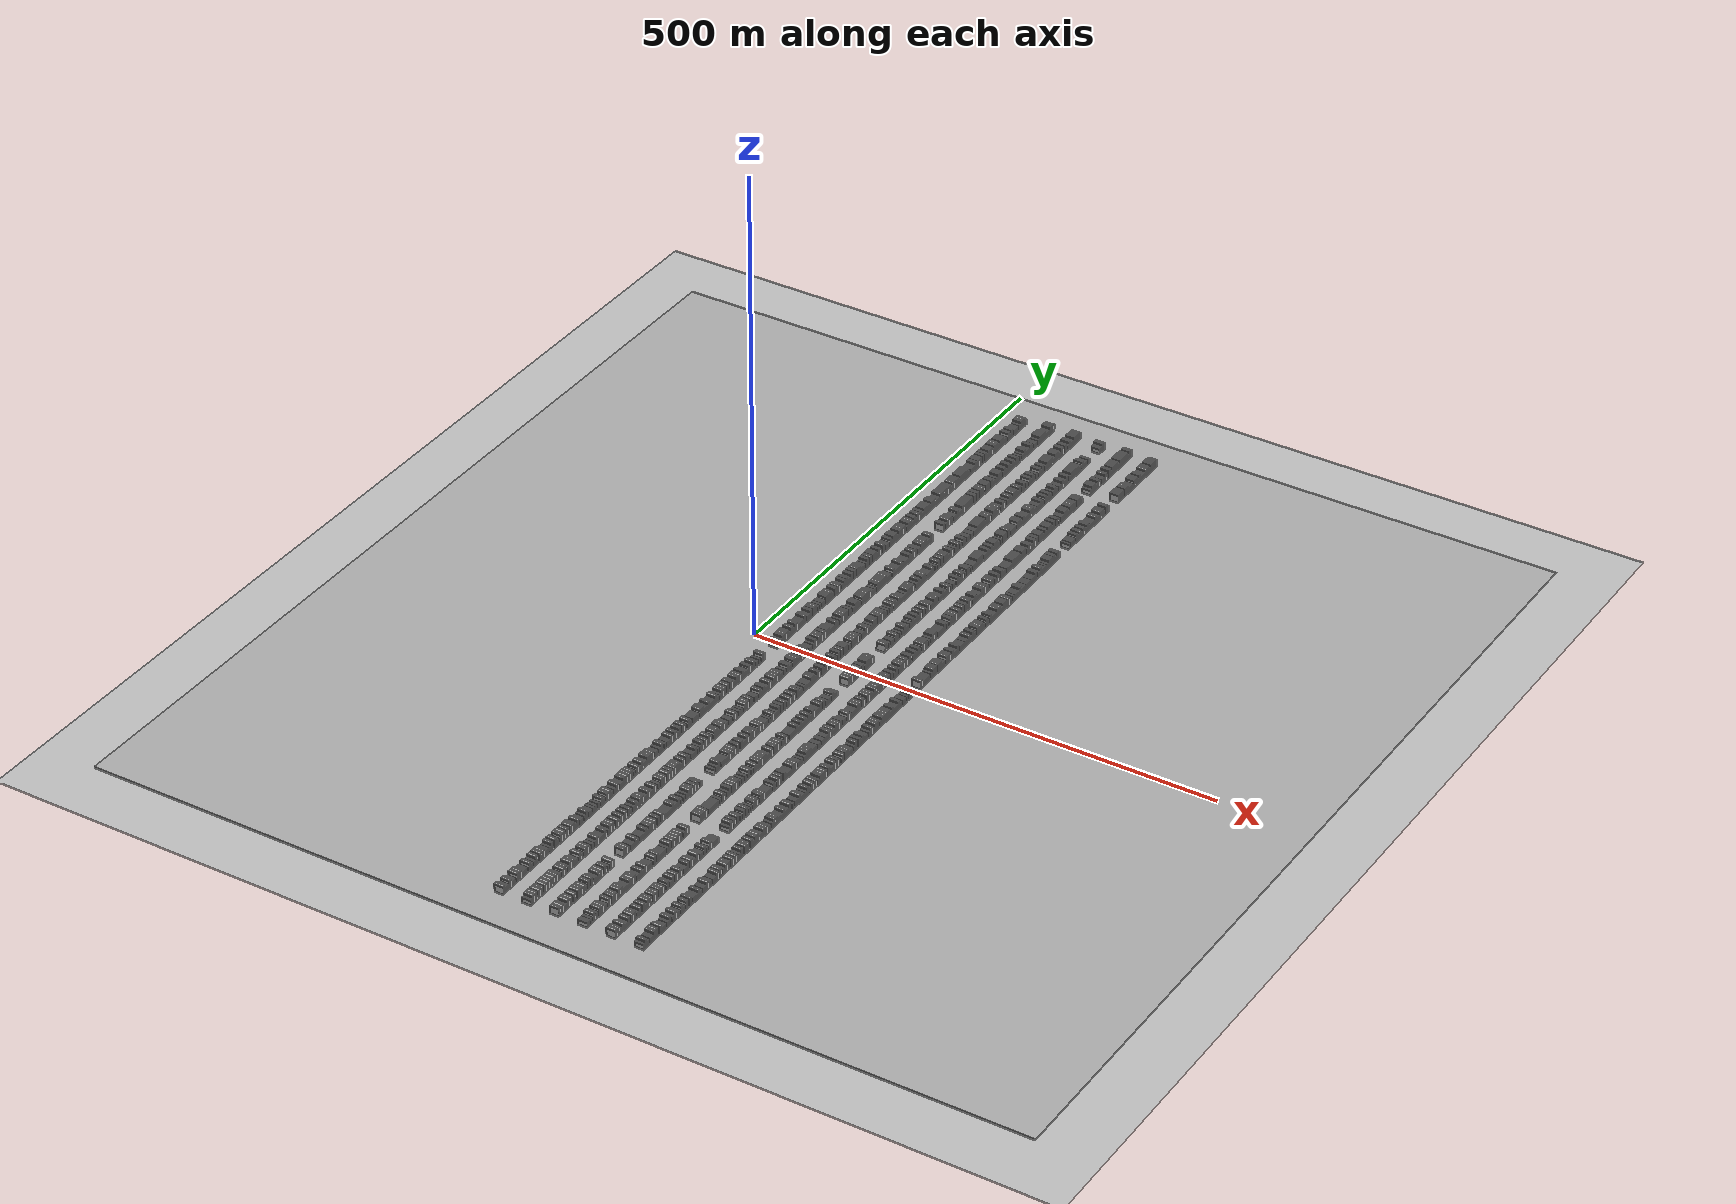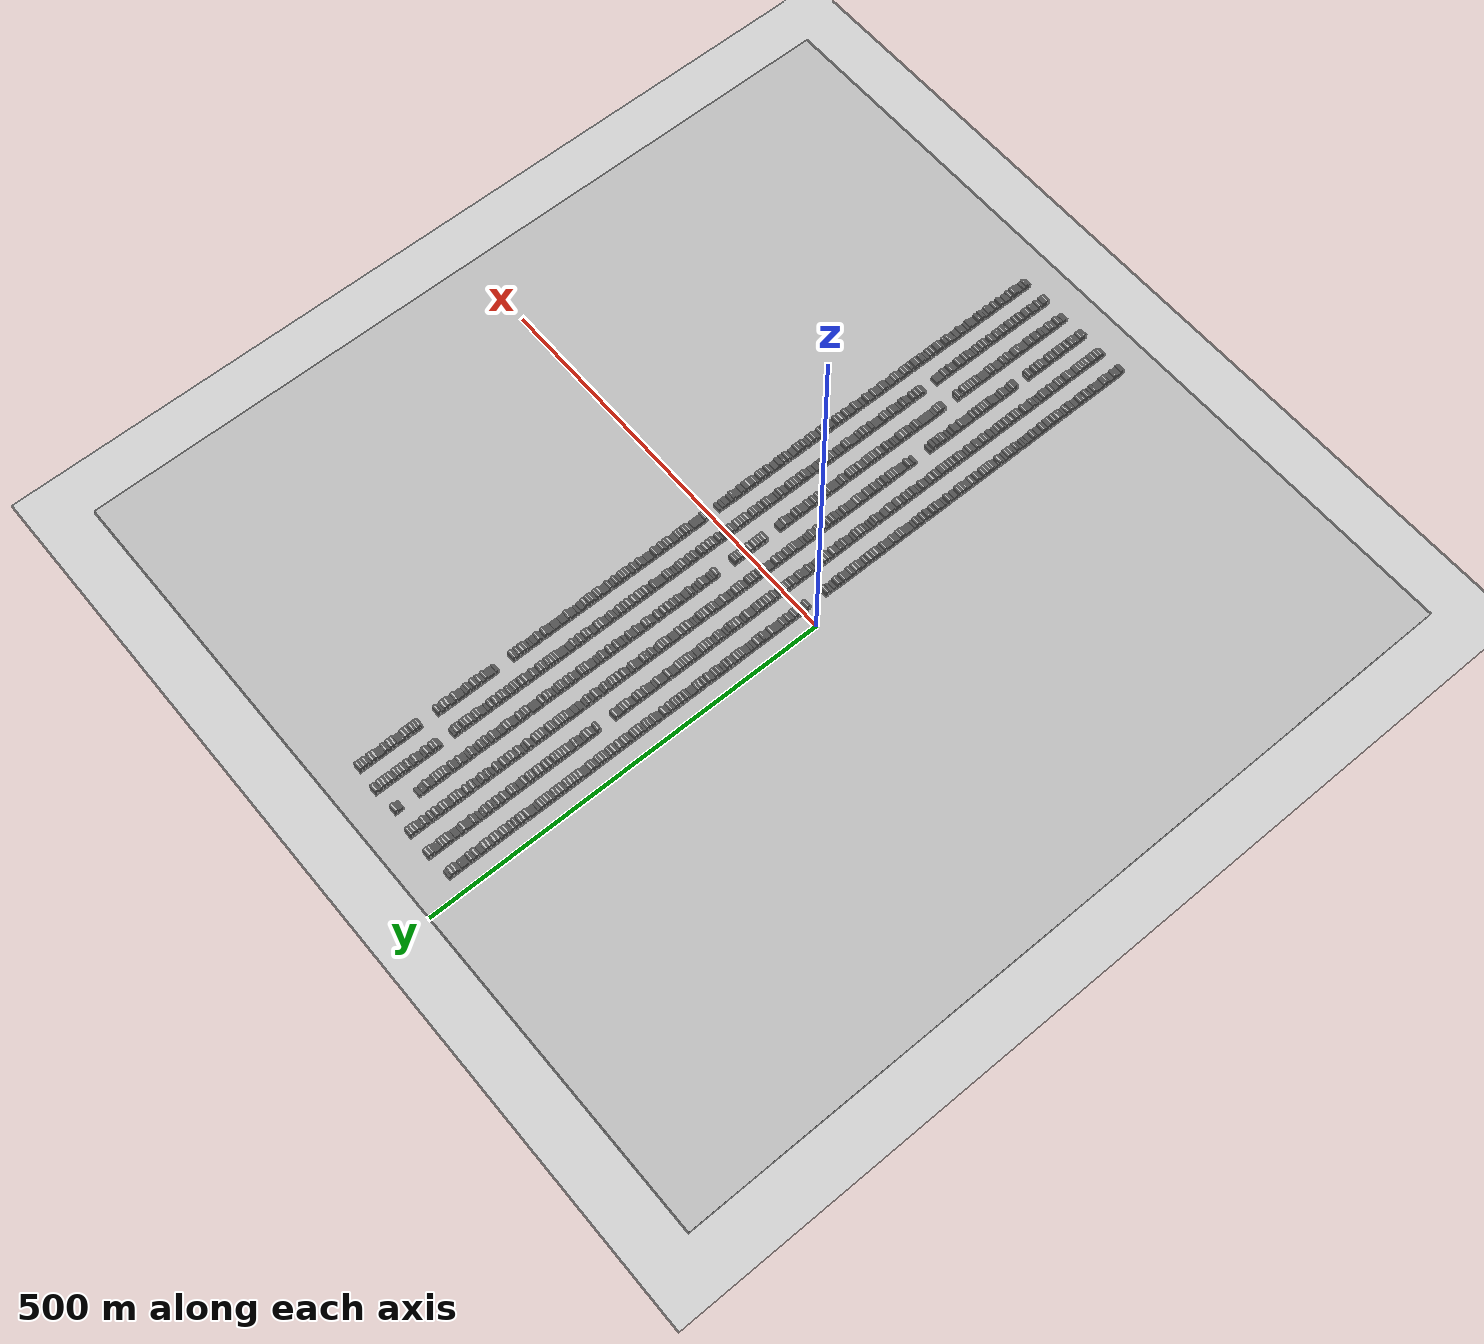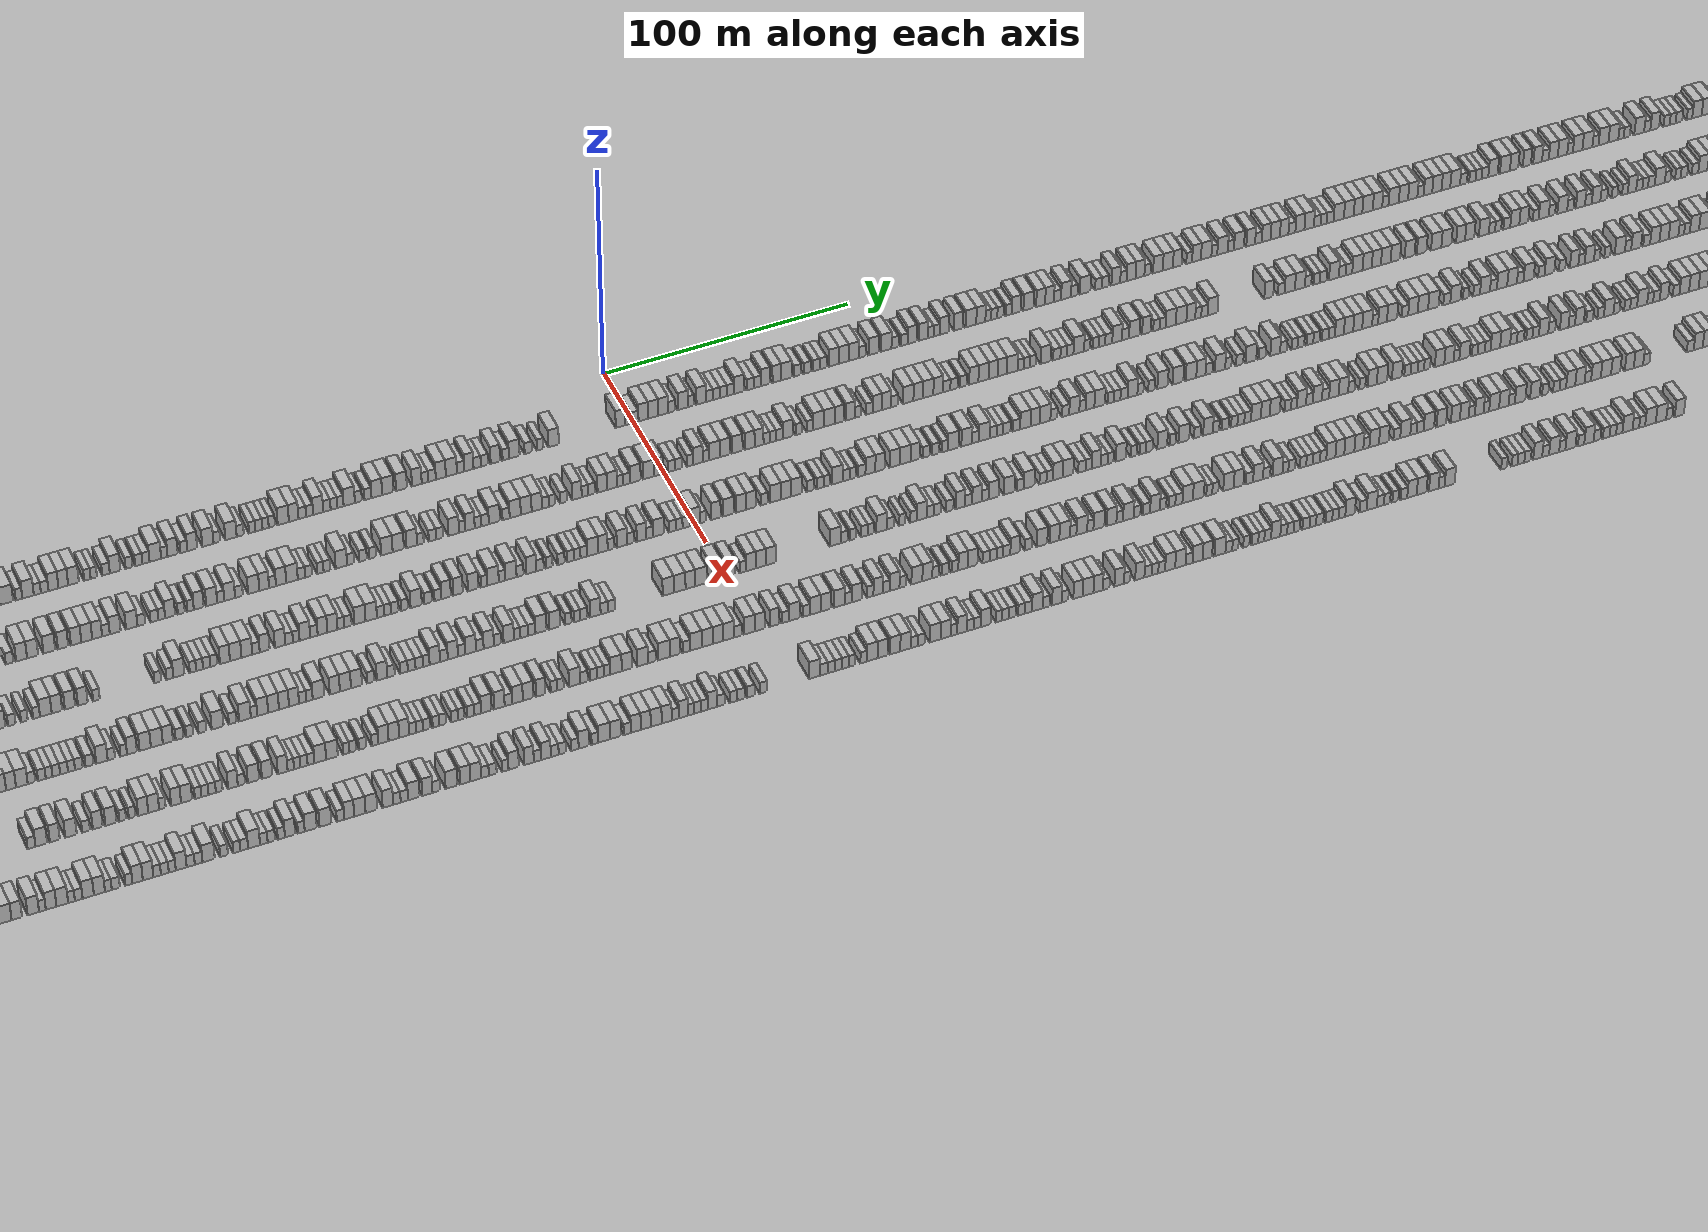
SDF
<sdf version="1.6">
 <world name="default">
  <scene>
   <sky><clouds><speed>12</speed></clouds></sky>
   <ambient>0.4 0.4 0.4 1</ambient>
   <background>0.7 0.7 0.7 1</background>
   <shadows>1</shadows>
  </scene>
  <gravity>0 0 -9.8066</gravity>
  <magnetic_field>6e-06 2.3e-05 -4.2e-05</magnetic_field>
  <physics default="0" name="default_physics" type="ode">
   <ode>
    <solver>
     <type>quick</type>
     <iters>10</iters>
     <sor>1.0</sor>
     <use_dynamic_moi_rescaling>0</use_dynamic_moi_rescaling>
    </solver>
    <constraints>
     <cfm>0</cfm>
     <erp>0.2</erp>
     <contact_max_correcting_vel>100</contact_max_correcting_vel>
     <contact_surface_layer>0.001</contact_surface_layer>
    </constraints>
   </ode>
   <max_step_size>0.004</max_step_size>
   <real_time_factor>1</real_time_factor>
   <real_time_update_rate>250</real_time_update_rate>
  </physics>
  <light name="sun" type="directional">
   <pose>0 0 10 0 0 0</pose>
   <diffuse>0.8 0.8 0.8 1</diffuse>
   <specular>0.2 0.2 0.2 1</specular>
   <attenuation>
    <range>1000</range>
    <constant>0.9</constant>
    <linear>0.01</linear>
    <quadratic>0.001</quadratic>
   </attenuation>
   <direction>-0.5 0.1 -0.9</direction>
  </light>
  <include><name>ground_plane_1</name><uri>model://HANNAS_ground_plane</uri></include>
  <include>
   <name>ground_plane_2</name>
   <uri>model://HANNAS_ground_plane</uri>
   <pose>100 0 0  0 0 0</pose>
  </include>
  <model name="building_1">
   <static>1</static>
   <pose>25.0000 -458.0347 0 0.000000 0.000000 0.000000</pose>
   <link name="link">
    <pose>0 0 4.50 0 0 0</pose>
    <collision name="collision"><geometry><box><size>10.0000 3.9307 9.0000</size></box></geometry></collision>
    <visual name="visual">
     <cast_shadows>0</cast_shadows>
     <geometry><box><size>10.0000 3.9307 9.0000</size></box></geometry>
     <material>
      <script>
       <uri>model://HANNAS_wall/materials/scripts</uri>
       <uri>model://HANNAS_wall/materials/textures</uri>
       <name>vrc/HANNAS_wall</name>
      </script>
     </material>
    </visual>
   </link>
  </model>
  <model name="building_2">
   <static>1</static>
   <pose>25.0000 -454.6919 0 0.000000 0.000000 0.000000</pose>
   <link name="link">
    <pose>0 0 3.00 0 0 0</pose>
    <collision name="collision"><geometry><box><size>10.0000 2.7548 6.0000</size></box></geometry></collision>
    <visual name="visual">
     <cast_shadows>0</cast_shadows>
     <geometry><box><size>10.0000 2.7548 6.0000</size></box></geometry>
     <material>
      <script>
       <uri>model://HANNAS_wall/materials/scripts</uri>
       <uri>model://HANNAS_wall/materials/textures</uri>
       <name>vrc/HANNAS_wall</name>
      </script>
     </material>
    </visual>
   </link>
  </model>
  <model name="building_3">
   <static>1</static>
   <pose>25.0000 -452.0797 0 0.000000 0.000000 0.000000</pose>
   <link name="link">
    <pose>0 0 3.00 0 0 0</pose>
    <collision name="collision"><geometry><box><size>10.0000 2.4697 6.0000</size></box></geometry></collision>
    <visual name="visual">
     <cast_shadows>0</cast_shadows>
     <geometry><box><size>10.0000 2.4697 6.0000</size></box></geometry>
     <material>
      <script>
       <uri>model://HANNAS_wall/materials/scripts</uri>
       <uri>model://HANNAS_wall/materials/textures</uri>
       <name>vrc/HANNAS_wall</name>
      </script>
     </material>
    </visual>
   </link>
  </model>
  <model name="building_4">
   <static>1</static>
   <pose>25.0000 -447.9195 0 0.000000 0.000000 0.000000</pose>
   <link name="link">
    <pose>0 0 4.50 0 0 0</pose>
    <collision name="collision"><geometry><box><size>10.0000 3.8506 9.0000</size></box></geometry></collision>
    <visual name="visual">
     <cast_shadows>0</cast_shadows>
     <geometry><box><size>10.0000 3.8506 9.0000</size></box></geometry>
     <material>
      <script>
       <uri>model://HANNAS_wall/materials/scripts</uri>
       <uri>model://HANNAS_wall/materials/textures</uri>
       <name>vrc/HANNAS_wall</name>
      </script>
     </material>
    </visual>
   </link>
  </model>
  <model name="building_5">
   <static>1</static>
   <pose>25.0000 -444.6043 0 0.000000 0.000000 0.000000</pose>
   <link name="link">
    <pose>0 0 3.00 0 0 0</pose>
    <collision name="collision"><geometry><box><size>10.0000 2.7799 6.0000</size></box></geometry></collision>
    <visual name="visual">
     <cast_shadows>0</cast_shadows>
     <geometry><box><size>10.0000 2.7799 6.0000</size></box></geometry>
     <material>
      <script>
       <uri>model://HANNAS_wall/materials/scripts</uri>
       <uri>model://HANNAS_wall/materials/textures</uri>
       <name>vrc/HANNAS_wall</name>
      </script>
     </material>
    </visual>
   </link>
  </model>
  <model name="building_6">
   <static>1</static>
   <pose>25.0000 -441.7249 0 0.000000 0.000000 0.000000</pose>
   <link name="link">
    <pose>0 0 3.00 0 0 0</pose>
    <collision name="collision"><geometry><box><size>10.0000 2.9789 6.0000</size></box></geometry></collision>
    <visual name="visual">
     <cast_shadows>0</cast_shadows>
     <geometry><box><size>10.0000 2.9789 6.0000</size></box></geometry>
     <material>
      <script>
       <uri>model://HANNAS_wall/materials/scripts</uri>
       <uri>model://HANNAS_wall/materials/textures</uri>
       <name>vrc/HANNAS_wall</name>
      </script>
     </material>
    </visual>
   </link>
  </model>
  <model name="building_7">
   <static>1</static>
   <pose>25.0000 -436.2437 0 0.000000 0.000000 0.000000</pose>
   <link name="link">
    <pose>0 0 4.50 0 0 0</pose>
    <collision name="collision"><geometry><box><size>10.0000 3.9835 9.0000</size></box></geometry></collision>
    <visual name="visual">
     <cast_shadows>0</cast_shadows>
     <geometry><box><size>10.0000 3.9835 9.0000</size></box></geometry>
     <material>
      <script>
       <uri>model://HANNAS_wall/materials/scripts</uri>
       <uri>model://HANNAS_wall/materials/textures</uri>
       <name>vrc/HANNAS_wall</name>
      </script>
     </material>
    </visual>
   </link>
  </model>
  <model name="building_8">
   <static>1</static>
   <pose>25.0000 -432.2339 0 0.000000 0.000000 0.000000</pose>
   <link name="link">
    <pose>0 0 4.50 0 0 0</pose>
    <collision name="collision"><geometry><box><size>10.0000 4.0362 9.0000</size></box></geometry></collision>
    <visual name="visual">
     <cast_shadows>0</cast_shadows>
     <geometry><box><size>10.0000 4.0362 9.0000</size></box></geometry>
     <material>
      <script>
       <uri>model://HANNAS_wall/materials/scripts</uri>
       <uri>model://HANNAS_wall/materials/textures</uri>
       <name>vrc/HANNAS_wall</name>
      </script>
     </material>
    </visual>
   </link>
  </model>
  <model name="building_9">
   <static>1</static>
   <pose>25.0000 -428.8545 0 0.000000 0.000000 0.000000</pose>
   <link name="link">
    <pose>0 0 3.00 0 0 0</pose>
    <collision name="collision"><geometry><box><size>10.0000 2.7226 6.0000</size></box></geometry></collision>
    <visual name="visual">
     <cast_shadows>0</cast_shadows>
     <geometry><box><size>10.0000 2.7226 6.0000</size></box></geometry>
     <material>
      <script>
       <uri>model://HANNAS_wall/materials/scripts</uri>
       <uri>model://HANNAS_wall/materials/textures</uri>
       <name>vrc/HANNAS_wall</name>
      </script>
     </material>
    </visual>
   </link>
  </model>
  <model name="building_10">
   <static>1</static>
   <pose>25.0000 -425.9957 0 0.000000 0.000000 0.000000</pose>
   <link name="link">
    <pose>0 0 3.00 0 0 0</pose>
    <collision name="collision"><geometry><box><size>10.0000 2.9950 6.0000</size></box></geometry></collision>
    <visual name="visual">
     <cast_shadows>0</cast_shadows>
     <geometry><box><size>10.0000 2.9950 6.0000</size></box></geometry>
     <material>
      <script>
       <uri>model://HANNAS_wall/materials/scripts</uri>
       <uri>model://HANNAS_wall/materials/textures</uri>
       <name>vrc/HANNAS_wall</name>
      </script>
     </material>
    </visual>
   </link>
  </model>
  <model name="building_11">
   <static>1</static>
   <pose>25.0000 -423.1064 0 0.000000 0.000000 0.000000</pose>
   <link name="link">
    <pose>0 0 3.00 0 0 0</pose>
    <collision name="collision"><geometry><box><size>10.0000 2.7835 6.0000</size></box></geometry></collision>
    <visual name="visual">
     <cast_shadows>0</cast_shadows>
     <geometry><box><size>10.0000 2.7835 6.0000</size></box></geometry>
     <material>
      <script>
       <uri>model://HANNAS_wall/materials/scripts</uri>
       <uri>model://HANNAS_wall/materials/textures</uri>
       <name>vrc/HANNAS_wall</name>
      </script>
     </material>
    </visual>
   </link>
  </model>
  <model name="building_12">
   <static>1</static>
   <pose>25.0000 -417.6575 0 0.000000 0.000000 0.000000</pose>
   <link name="link">
    <pose>0 0 4.50 0 0 0</pose>
    <collision name="collision"><geometry><box><size>10.0000 4.1143 9.0000</size></box></geometry></collision>
    <visual name="visual">
     <cast_shadows>0</cast_shadows>
     <geometry><box><size>10.0000 4.1143 9.0000</size></box></geometry>
     <material>
      <script>
       <uri>model://HANNAS_wall/materials/scripts</uri>
       <uri>model://HANNAS_wall/materials/textures</uri>
       <name>vrc/HANNAS_wall</name>
      </script>
     </material>
    </visual>
   </link>
  </model>
  <model name="building_13">
   <static>1</static>
   <pose>25.0000 -414.1773 0 0.000000 0.000000 0.000000</pose>
   <link name="link">
    <pose>0 0 3.00 0 0 0</pose>
    <collision name="collision"><geometry><box><size>10.0000 2.8461 6.0000</size></box></geometry></collision>
    <visual name="visual">
     <cast_shadows>0</cast_shadows>
     <geometry><box><size>10.0000 2.8461 6.0000</size></box></geometry>
     <material>
      <script>
       <uri>model://HANNAS_wall/materials/scripts</uri>
       <uri>model://HANNAS_wall/materials/textures</uri>
       <name>vrc/HANNAS_wall</name>
      </script>
     </material>
    </visual>
   </link>
  </model>
  <model name="building_14">
   <static>1</static>
   <pose>25.0000 -410.2872 0 0.000000 0.000000 0.000000</pose>
   <link name="link">
    <pose>0 0 3.00 0 0 0</pose>
    <collision name="collision"><geometry><box><size>10.0000 2.9340 6.0000</size></box></geometry></collision>
    <visual name="visual">
     <cast_shadows>0</cast_shadows>
     <geometry><box><size>10.0000 2.9340 6.0000</size></box></geometry>
     <material>
      <script>
       <uri>model://HANNAS_wall/materials/scripts</uri>
       <uri>model://HANNAS_wall/materials/textures</uri>
       <name>vrc/HANNAS_wall</name>
      </script>
     </material>
    </visual>
   </link>
  </model>
  <model name="building_15">
   <static>1</static>
   <pose>25.0000 -406.6927 0 0.000000 0.000000 0.000000</pose>
   <link name="link">
    <pose>0 0 4.50 0 0 0</pose>
    <collision name="collision"><geometry><box><size>10.0000 4.2550 9.0000</size></box></geometry></collision>
    <visual name="visual">
     <cast_shadows>0</cast_shadows>
     <geometry><box><size>10.0000 4.2550 9.0000</size></box></geometry>
     <material>
      <script>
       <uri>model://HANNAS_wall/materials/scripts</uri>
       <uri>model://HANNAS_wall/materials/textures</uri>
       <name>vrc/HANNAS_wall</name>
      </script>
     </material>
    </visual>
   </link>
  </model>
  <model name="building_16">
   <static>1</static>
   <pose>25.0000 -400.6007 0 0.000000 0.000000 0.000000</pose>
   <link name="link">
    <pose>0 0 4.50 0 0 0</pose>
    <collision name="collision"><geometry><box><size>10.0000 3.9290 9.0000</size></box></geometry></collision>
    <visual name="visual">
     <cast_shadows>0</cast_shadows>
     <geometry><box><size>10.0000 3.9290 9.0000</size></box></geometry>
     <material>
      <script>
       <uri>model://HANNAS_wall/materials/scripts</uri>
       <uri>model://HANNAS_wall/materials/textures</uri>
       <name>vrc/HANNAS_wall</name>
      </script>
     </material>
    </visual>
   </link>
  </model>
  <model name="building_17">
   <static>1</static>
   <pose>25.0000 -396.6170 0 0.000000 0.000000 0.000000</pose>
   <link name="link">
    <pose>0 0 4.50 0 0 0</pose>
    <collision name="collision"><geometry><box><size>10.0000 4.0384 9.0000</size></box></geometry></collision>
    <visual name="visual">
     <cast_shadows>0</cast_shadows>
     <geometry><box><size>10.0000 4.0384 9.0000</size></box></geometry>
     <material>
      <script>
       <uri>model://HANNAS_wall/materials/scripts</uri>
       <uri>model://HANNAS_wall/materials/textures</uri>
       <name>vrc/HANNAS_wall</name>
      </script>
     </material>
    </visual>
   </link>
  </model>
  <model name="building_18">
   <static>1</static>
   <pose>25.0000 -392.2894 0 0.000000 0.000000 0.000000</pose>
   <link name="link">
    <pose>0 0 3.00 0 0 0</pose>
    <collision name="collision"><geometry><box><size>10.0000 2.6169 6.0000</size></box></geometry></collision>
    <visual name="visual">
     <cast_shadows>0</cast_shadows>
     <geometry><box><size>10.0000 2.6169 6.0000</size></box></geometry>
     <material>
      <script>
       <uri>model://HANNAS_wall/materials/scripts</uri>
       <uri>model://HANNAS_wall/materials/textures</uri>
       <name>vrc/HANNAS_wall</name>
      </script>
     </material>
    </visual>
   </link>
  </model>
  <model name="building_19">
   <static>1</static>
   <pose>25.0000 -389.5460 0 0.000000 0.000000 0.000000</pose>
   <link name="link">
    <pose>0 0 3.00 0 0 0</pose>
    <collision name="collision"><geometry><box><size>10.0000 2.8698 6.0000</size></box></geometry></collision>
    <visual name="visual">
     <cast_shadows>0</cast_shadows>
     <geometry><box><size>10.0000 2.8698 6.0000</size></box></geometry>
     <material>
      <script>
       <uri>model://HANNAS_wall/materials/scripts</uri>
       <uri>model://HANNAS_wall/materials/textures</uri>
       <name>vrc/HANNAS_wall</name>
      </script>
     </material>
    </visual>
   </link>
  </model>
  <model name="building_20">
   <static>1</static>
   <pose>25.0000 -385.8334 0 0.000000 0.000000 0.000000</pose>
   <link name="link">
    <pose>0 0 3.00 0 0 0</pose>
    <collision name="collision"><geometry><box><size>10.0000 2.5554 6.0000</size></box></geometry></collision>
    <visual name="visual">
     <cast_shadows>0</cast_shadows>
     <geometry><box><size>10.0000 2.5554 6.0000</size></box></geometry>
     <material>
      <script>
       <uri>model://HANNAS_wall/materials/scripts</uri>
       <uri>model://HANNAS_wall/materials/textures</uri>
       <name>vrc/HANNAS_wall</name>
      </script>
     </material>
    </visual>
   </link>
  </model>
  <model name="building_21">
   <static>1</static>
   <pose>25.0000 -382.6334 0 0.000000 0.000000 0.000000</pose>
   <link name="link">
    <pose>0 0 4.50 0 0 0</pose>
    <collision name="collision"><geometry><box><size>10.0000 3.8446 9.0000</size></box></geometry></collision>
    <visual name="visual">
     <cast_shadows>0</cast_shadows>
     <geometry><box><size>10.0000 3.8446 9.0000</size></box></geometry>
     <material>
      <script>
       <uri>model://HANNAS_wall/materials/scripts</uri>
       <uri>model://HANNAS_wall/materials/textures</uri>
       <name>vrc/HANNAS_wall</name>
      </script>
     </material>
    </visual>
   </link>
  </model>
  <model name="building_22">
   <static>1</static>
   <pose>25.0000 -376.5462 0 0.000000 0.000000 0.000000</pose>
   <link name="link">
    <pose>0 0 4.50 0 0 0</pose>
    <collision name="collision"><geometry><box><size>10.0000 4.3296 9.0000</size></box></geometry></collision>
    <visual name="visual">
     <cast_shadows>0</cast_shadows>
     <geometry><box><size>10.0000 4.3296 9.0000</size></box></geometry>
     <material>
      <script>
       <uri>model://HANNAS_wall/materials/scripts</uri>
       <uri>model://HANNAS_wall/materials/textures</uri>
       <name>vrc/HANNAS_wall</name>
      </script>
     </material>
    </visual>
   </link>
  </model>
  <model name="building_23">
   <static>1</static>
   <pose>25.0000 -373.0783 0 0.000000 0.000000 0.000000</pose>
   <link name="link">
    <pose>0 0 3.00 0 0 0</pose>
    <collision name="collision"><geometry><box><size>10.0000 2.6063 6.0000</size></box></geometry></collision>
    <visual name="visual">
     <cast_shadows>0</cast_shadows>
     <geometry><box><size>10.0000 2.6063 6.0000</size></box></geometry>
     <material>
      <script>
       <uri>model://HANNAS_wall/materials/scripts</uri>
       <uri>model://HANNAS_wall/materials/textures</uri>
       <name>vrc/HANNAS_wall</name>
      </script>
     </material>
    </visual>
   </link>
  </model>
  <model name="building_24">
   <static>1</static>
   <pose>25.0000 -367.8583 0 0.000000 0.000000 0.000000</pose>
   <link name="link">
    <pose>0 0 4.50 0 0 0</pose>
    <collision name="collision"><geometry><box><size>10.0000 3.8336 9.0000</size></box></geometry></collision>
    <visual name="visual">
     <cast_shadows>0</cast_shadows>
     <geometry><box><size>10.0000 3.8336 9.0000</size></box></geometry>
     <material>
      <script>
       <uri>model://HANNAS_wall/materials/scripts</uri>
       <uri>model://HANNAS_wall/materials/textures</uri>
       <name>vrc/HANNAS_wall</name>
      </script>
     </material>
    </visual>
   </link>
  </model>
  <model name="building_25">
   <static>1</static>
   <pose>25.0000 -363.6942 0 0.000000 0.000000 0.000000</pose>
   <link name="link">
    <pose>0 0 4.50 0 0 0</pose>
    <collision name="collision"><geometry><box><size>10.0000 4.4944 9.0000</size></box></geometry></collision>
    <visual name="visual">
     <cast_shadows>0</cast_shadows>
     <geometry><box><size>10.0000 4.4944 9.0000</size></box></geometry>
     <material>
      <script>
       <uri>model://HANNAS_wall/materials/scripts</uri>
       <uri>model://HANNAS_wall/materials/textures</uri>
       <name>vrc/HANNAS_wall</name>
      </script>
     </material>
    </visual>
   </link>
  </model>
  <model name="building_26">
   <static>1</static>
   <pose>25.0000 -358.4332 0 0.000000 0.000000 0.000000</pose>
   <link name="link">
    <pose>0 0 4.50 0 0 0</pose>
    <collision name="collision"><geometry><box><size>10.0000 4.0277 9.0000</size></box></geometry></collision>
    <visual name="visual">
     <cast_shadows>0</cast_shadows>
     <geometry><box><size>10.0000 4.0277 9.0000</size></box></geometry>
     <material>
      <script>
       <uri>model://HANNAS_wall/materials/scripts</uri>
       <uri>model://HANNAS_wall/materials/textures</uri>
       <name>vrc/HANNAS_wall</name>
      </script>
     </material>
    </visual>
   </link>
  </model>
  <model name="building_27">
   <static>1</static>
   <pose>25.0000 -352.3200 0 0.000000 0.000000 0.000000</pose>
   <link name="link">
    <pose>0 0 4.50 0 0 0</pose>
    <collision name="collision"><geometry><box><size>10.0000 4.1987 9.0000</size></box></geometry></collision>
    <visual name="visual">
     <cast_shadows>0</cast_shadows>
     <geometry><box><size>10.0000 4.1987 9.0000</size></box></geometry>
     <material>
      <script>
       <uri>model://HANNAS_wall/materials/scripts</uri>
       <uri>model://HANNAS_wall/materials/textures</uri>
       <name>vrc/HANNAS_wall</name>
      </script>
     </material>
    </visual>
   </link>
  </model>
  <model name="building_28">
   <static>1</static>
   <pose>25.0000 -348.3861 0 0.000000 0.000000 0.000000</pose>
   <link name="link">
    <pose>0 0 4.50 0 0 0</pose>
    <collision name="collision"><geometry><box><size>10.0000 3.6690 9.0000</size></box></geometry></collision>
    <visual name="visual">
     <cast_shadows>0</cast_shadows>
     <geometry><box><size>10.0000 3.6690 9.0000</size></box></geometry>
     <material>
      <script>
       <uri>model://HANNAS_wall/materials/scripts</uri>
       <uri>model://HANNAS_wall/materials/textures</uri>
       <name>vrc/HANNAS_wall</name>
      </script>
     </material>
    </visual>
   </link>
  </model>
  <model name="building_29">
   <static>1</static>
   <pose>25.0000 -345.0857 0 0.000000 0.000000 0.000000</pose>
   <link name="link">
    <pose>0 0 3.00 0 0 0</pose>
    <collision name="collision"><geometry><box><size>10.0000 2.9317 6.0000</size></box></geometry></collision>
    <visual name="visual">
     <cast_shadows>0</cast_shadows>
     <geometry><box><size>10.0000 2.9317 6.0000</size></box></geometry>
     <material>
      <script>
       <uri>model://HANNAS_wall/materials/scripts</uri>
       <uri>model://HANNAS_wall/materials/textures</uri>
       <name>vrc/HANNAS_wall</name>
      </script>
     </material>
    </visual>
   </link>
  </model>
  <model name="building_30">
   <static>1</static>
   <pose>25.0000 -341.5307 0 0.000000 0.000000 0.000000</pose>
   <link name="link">
    <pose>0 0 4.50 0 0 0</pose>
    <collision name="collision"><geometry><box><size>10.0000 4.1784 9.0000</size></box></geometry></collision>
    <visual name="visual">
     <cast_shadows>0</cast_shadows>
     <geometry><box><size>10.0000 4.1784 9.0000</size></box></geometry>
     <material>
      <script>
       <uri>model://HANNAS_wall/materials/scripts</uri>
       <uri>model://HANNAS_wall/materials/textures</uri>
       <name>vrc/HANNAS_wall</name>
      </script>
     </material>
    </visual>
   </link>
  </model>
  <model name="building_31">
   <static>1</static>
   <pose>25.0000 -337.1726 0 0.000000 0.000000 0.000000</pose>
   <link name="link">
    <pose>0 0 3.00 0 0 0</pose>
    <collision name="collision"><geometry><box><size>10.0000 2.5376 6.0000</size></box></geometry></collision>
    <visual name="visual">
     <cast_shadows>0</cast_shadows>
     <geometry><box><size>10.0000 2.5376 6.0000</size></box></geometry>
     <material>
      <script>
       <uri>model://HANNAS_wall/materials/scripts</uri>
       <uri>model://HANNAS_wall/materials/textures</uri>
       <name>vrc/HANNAS_wall</name>
      </script>
     </material>
    </visual>
   </link>
  </model>
  <model name="building_32">
   <static>1</static>
   <pose>25.0000 -334.6079 0 0.000000 0.000000 0.000000</pose>
   <link name="link">
    <pose>0 0 3.00 0 0 0</pose>
    <collision name="collision"><geometry><box><size>10.0000 2.5919 6.0000</size></box></geometry></collision>
    <visual name="visual">
     <cast_shadows>0</cast_shadows>
     <geometry><box><size>10.0000 2.5919 6.0000</size></box></geometry>
     <material>
      <script>
       <uri>model://HANNAS_wall/materials/scripts</uri>
       <uri>model://HANNAS_wall/materials/textures</uri>
       <name>vrc/HANNAS_wall</name>
      </script>
     </material>
    </visual>
   </link>
  </model>
  <model name="building_33">
   <static>1</static>
   <pose>25.0000 -330.1112 0 0.000000 0.000000 0.000000</pose>
   <link name="link">
    <pose>0 0 3.00 0 0 0</pose>
    <collision name="collision"><geometry><box><size>10.0000 2.4014 6.0000</size></box></geometry></collision>
    <visual name="visual">
     <cast_shadows>0</cast_shadows>
     <geometry><box><size>10.0000 2.4014 6.0000</size></box></geometry>
     <material>
      <script>
       <uri>model://HANNAS_wall/materials/scripts</uri>
       <uri>model://HANNAS_wall/materials/textures</uri>
       <name>vrc/HANNAS_wall</name>
      </script>
     </material>
    </visual>
   </link>
  </model>
  <model name="building_34">
   <static>1</static>
   <pose>25.0000 -326.9697 0 0.000000 0.000000 0.000000</pose>
   <link name="link">
    <pose>0 0 4.50 0 0 0</pose>
    <collision name="collision"><geometry><box><size>10.0000 3.8817 9.0000</size></box></geometry></collision>
    <visual name="visual">
     <cast_shadows>0</cast_shadows>
     <geometry><box><size>10.0000 3.8817 9.0000</size></box></geometry>
     <material>
      <script>
       <uri>model://HANNAS_wall/materials/scripts</uri>
       <uri>model://HANNAS_wall/materials/textures</uri>
       <name>vrc/HANNAS_wall</name>
      </script>
     </material>
    </visual>
   </link>
  </model>
  <model name="building_35">
   <static>1</static>
   <pose>25.0000 -322.7436 0 0.000000 0.000000 0.000000</pose>
   <link name="link">
    <pose>0 0 3.00 0 0 0</pose>
    <collision name="collision"><geometry><box><size>10.0000 2.5705 6.0000</size></box></geometry></collision>
    <visual name="visual">
     <cast_shadows>0</cast_shadows>
     <geometry><box><size>10.0000 2.5705 6.0000</size></box></geometry>
     <material>
      <script>
       <uri>model://HANNAS_wall/materials/scripts</uri>
       <uri>model://HANNAS_wall/materials/textures</uri>
       <name>vrc/HANNAS_wall</name>
      </script>
     </material>
    </visual>
   </link>
  </model>
  <model name="building_36">
   <static>1</static>
   <pose>25.0000 -319.9724 0 0.000000 0.000000 0.000000</pose>
   <link name="link">
    <pose>0 0 3.00 0 0 0</pose>
    <collision name="collision"><geometry><box><size>10.0000 2.9718 6.0000</size></box></geometry></collision>
    <visual name="visual">
     <cast_shadows>0</cast_shadows>
     <geometry><box><size>10.0000 2.9718 6.0000</size></box></geometry>
     <material>
      <script>
       <uri>model://HANNAS_wall/materials/scripts</uri>
       <uri>model://HANNAS_wall/materials/textures</uri>
       <name>vrc/HANNAS_wall</name>
      </script>
     </material>
    </visual>
   </link>
  </model>
  <model name="building_37">
   <static>1</static>
   <pose>25.0000 -316.1096 0 0.000000 0.000000 0.000000</pose>
   <link name="link">
    <pose>0 0 3.00 0 0 0</pose>
    <collision name="collision"><geometry><box><size>10.0000 2.7538 6.0000</size></box></geometry></collision>
    <visual name="visual">
     <cast_shadows>0</cast_shadows>
     <geometry><box><size>10.0000 2.7538 6.0000</size></box></geometry>
     <material>
      <script>
       <uri>model://HANNAS_wall/materials/scripts</uri>
       <uri>model://HANNAS_wall/materials/textures</uri>
       <name>vrc/HANNAS_wall</name>
      </script>
     </material>
    </visual>
   </link>
  </model>
  <model name="building_38">
   <static>1</static>
   <pose>25.0000 -312.4025 0 0.000000 0.000000 0.000000</pose>
   <link name="link">
    <pose>0 0 3.00 0 0 0</pose>
    <collision name="collision"><geometry><box><size>10.0000 2.6604 6.0000</size></box></geometry></collision>
    <visual name="visual">
     <cast_shadows>0</cast_shadows>
     <geometry><box><size>10.0000 2.6604 6.0000</size></box></geometry>
     <material>
      <script>
       <uri>model://HANNAS_wall/materials/scripts</uri>
       <uri>model://HANNAS_wall/materials/textures</uri>
       <name>vrc/HANNAS_wall</name>
      </script>
     </material>
    </visual>
   </link>
  </model>
  <model name="building_39">
   <static>1</static>
   <pose>25.0000 -307.8670 0 0.000000 0.000000 0.000000</pose>
   <link name="link">
    <pose>0 0 3.00 0 0 0</pose>
    <collision name="collision"><geometry><box><size>10.0000 2.4106 6.0000</size></box></geometry></collision>
    <visual name="visual">
     <cast_shadows>0</cast_shadows>
     <geometry><box><size>10.0000 2.4106 6.0000</size></box></geometry>
     <material>
      <script>
       <uri>model://HANNAS_wall/materials/scripts</uri>
       <uri>model://HANNAS_wall/materials/textures</uri>
       <name>vrc/HANNAS_wall</name>
      </script>
     </material>
    </visual>
   </link>
  </model>
  <model name="building_40">
   <static>1</static>
   <pose>25.0000 -302.8140 0 0.000000 0.000000 0.000000</pose>
   <link name="link">
    <pose>0 0 4.50 0 0 0</pose>
    <collision name="collision"><geometry><box><size>10.0000 3.6954 9.0000</size></box></geometry></collision>
    <visual name="visual">
     <cast_shadows>0</cast_shadows>
     <geometry><box><size>10.0000 3.6954 9.0000</size></box></geometry>
     <material>
      <script>
       <uri>model://HANNAS_wall/materials/scripts</uri>
       <uri>model://HANNAS_wall/materials/textures</uri>
       <name>vrc/HANNAS_wall</name>
      </script>
     </material>
    </visual>
   </link>
  </model>
  <model name="building_41">
   <static>1</static>
   <pose>25.0000 -299.5794 0 0.000000 0.000000 0.000000</pose>
   <link name="link">
    <pose>0 0 3.00 0 0 0</pose>
    <collision name="collision"><geometry><box><size>10.0000 2.7738 6.0000</size></box></geometry></collision>
    <visual name="visual">
     <cast_shadows>0</cast_shadows>
     <geometry><box><size>10.0000 2.7738 6.0000</size></box></geometry>
     <material>
      <script>
       <uri>model://HANNAS_wall/materials/scripts</uri>
       <uri>model://HANNAS_wall/materials/textures</uri>
       <name>vrc/HANNAS_wall</name>
      </script>
     </material>
    </visual>
   </link>
  </model>
  <model name="building_42">
   <static>1</static>
   <pose>25.0000 -294.2375 0 0.000000 0.000000 0.000000</pose>
   <link name="link">
    <pose>0 0 4.50 0 0 0</pose>
    <collision name="collision"><geometry><box><size>10.0000 3.9100 9.0000</size></box></geometry></collision>
    <visual name="visual">
     <cast_shadows>0</cast_shadows>
     <geometry><box><size>10.0000 3.9100 9.0000</size></box></geometry>
     <material>
      <script>
       <uri>model://HANNAS_wall/materials/scripts</uri>
       <uri>model://HANNAS_wall/materials/textures</uri>
       <name>vrc/HANNAS_wall</name>
      </script>
     </material>
    </visual>
   </link>
  </model>
  <model name="building_43">
   <static>1</static>
   <pose>25.0000 -290.0535 0 0.000000 0.000000 0.000000</pose>
   <link name="link">
    <pose>0 0 4.50 0 0 0</pose>
    <collision name="collision"><geometry><box><size>10.0000 4.4580 9.0000</size></box></geometry></collision>
    <visual name="visual">
     <cast_shadows>0</cast_shadows>
     <geometry><box><size>10.0000 4.4580 9.0000</size></box></geometry>
     <material>
      <script>
       <uri>model://HANNAS_wall/materials/scripts</uri>
       <uri>model://HANNAS_wall/materials/textures</uri>
       <name>vrc/HANNAS_wall</name>
      </script>
     </material>
    </visual>
   </link>
  </model>
  <model name="building_44">
   <static>1</static>
   <pose>25.0000 -286.5619 0 0.000000 0.000000 0.000000</pose>
   <link name="link">
    <pose>0 0 3.00 0 0 0</pose>
    <collision name="collision"><geometry><box><size>10.0000 2.5252 6.0000</size></box></geometry></collision>
    <visual name="visual">
     <cast_shadows>0</cast_shadows>
     <geometry><box><size>10.0000 2.5252 6.0000</size></box></geometry>
     <material>
      <script>
       <uri>model://HANNAS_wall/materials/scripts</uri>
       <uri>model://HANNAS_wall/materials/textures</uri>
       <name>vrc/HANNAS_wall</name>
      </script>
     </material>
    </visual>
   </link>
  </model>
  <model name="building_45">
   <static>1</static>
   <pose>25.0000 -281.8241 0 0.000000 0.000000 0.000000</pose>
   <link name="link">
    <pose>0 0 3.00 0 0 0</pose>
    <collision name="collision"><geometry><box><size>10.0000 2.9503 6.0000</size></box></geometry></collision>
    <visual name="visual">
     <cast_shadows>0</cast_shadows>
     <geometry><box><size>10.0000 2.9503 6.0000</size></box></geometry>
     <material>
      <script>
       <uri>model://HANNAS_wall/materials/scripts</uri>
       <uri>model://HANNAS_wall/materials/textures</uri>
       <name>vrc/HANNAS_wall</name>
      </script>
     </material>
    </visual>
   </link>
  </model>
  <model name="building_46">
   <static>1</static>
   <pose>25.0000 -278.1454 0 0.000000 0.000000 0.000000</pose>
   <link name="link">
    <pose>0 0 4.50 0 0 0</pose>
    <collision name="collision"><geometry><box><size>10.0000 4.4072 9.0000</size></box></geometry></collision>
    <visual name="visual">
     <cast_shadows>0</cast_shadows>
     <geometry><box><size>10.0000 4.4072 9.0000</size></box></geometry>
     <material>
      <script>
       <uri>model://HANNAS_wall/materials/scripts</uri>
       <uri>model://HANNAS_wall/materials/textures</uri>
       <name>vrc/HANNAS_wall</name>
      </script>
     </material>
    </visual>
   </link>
  </model>
  <model name="building_47">
   <static>1</static>
   <pose>25.0000 -272.5321 0 0.000000 0.000000 0.000000</pose>
   <link name="link">
    <pose>0 0 3.00 0 0 0</pose>
    <collision name="collision"><geometry><box><size>10.0000 2.8193 6.0000</size></box></geometry></collision>
    <visual name="visual">
     <cast_shadows>0</cast_shadows>
     <geometry><box><size>10.0000 2.8193 6.0000</size></box></geometry>
     <material>
      <script>
       <uri>model://HANNAS_wall/materials/scripts</uri>
       <uri>model://HANNAS_wall/materials/textures</uri>
       <name>vrc/HANNAS_wall</name>
      </script>
     </material>
    </visual>
   </link>
  </model>
  <model name="building_48">
   <static>1</static>
   <pose>25.0000 -269.8958 0 0.000000 0.000000 0.000000</pose>
   <link name="link">
    <pose>0 0 3.00 0 0 0</pose>
    <collision name="collision"><geometry><box><size>10.0000 2.4534 6.0000</size></box></geometry></collision>
    <visual name="visual">
     <cast_shadows>0</cast_shadows>
     <geometry><box><size>10.0000 2.4534 6.0000</size></box></geometry>
     <material>
      <script>
       <uri>model://HANNAS_wall/materials/scripts</uri>
       <uri>model://HANNAS_wall/materials/textures</uri>
       <name>vrc/HANNAS_wall</name>
      </script>
     </material>
    </visual>
   </link>
  </model>
  <model name="building_49">
   <static>1</static>
   <pose>25.0000 -266.7919 0 0.000000 0.000000 0.000000</pose>
   <link name="link">
    <pose>0 0 4.50 0 0 0</pose>
    <collision name="collision"><geometry><box><size>10.0000 3.7544 9.0000</size></box></geometry></collision>
    <visual name="visual">
     <cast_shadows>0</cast_shadows>
     <geometry><box><size>10.0000 3.7544 9.0000</size></box></geometry>
     <material>
      <script>
       <uri>model://HANNAS_wall/materials/scripts</uri>
       <uri>model://HANNAS_wall/materials/textures</uri>
       <name>vrc/HANNAS_wall</name>
      </script>
     </material>
    </visual>
   </link>
  </model>
  <model name="building_50">
   <static>1</static>
   <pose>25.0000 -262.7052 0 0.000000 0.000000 0.000000</pose>
   <link name="link">
    <pose>0 0 4.50 0 0 0</pose>
    <collision name="collision"><geometry><box><size>10.0000 4.4191 9.0000</size></box></geometry></collision>
    <visual name="visual">
     <cast_shadows>0</cast_shadows>
     <geometry><box><size>10.0000 4.4191 9.0000</size></box></geometry>
     <material>
      <script>
       <uri>model://HANNAS_wall/materials/scripts</uri>
       <uri>model://HANNAS_wall/materials/textures</uri>
       <name>vrc/HANNAS_wall</name>
      </script>
     </material>
    </visual>
   </link>
  </model>
  <model name="building_51">
   <static>1</static>
   <pose>25.0000 -258.3939 0 0.000000 0.000000 0.000000</pose>
   <link name="link">
    <pose>0 0 4.50 0 0 0</pose>
    <collision name="collision"><geometry><box><size>10.0000 4.2034 9.0000</size></box></geometry></collision>
    <visual name="visual">
     <cast_shadows>0</cast_shadows>
     <geometry><box><size>10.0000 4.2034 9.0000</size></box></geometry>
     <material>
      <script>
       <uri>model://HANNAS_wall/materials/scripts</uri>
       <uri>model://HANNAS_wall/materials/textures</uri>
       <name>vrc/HANNAS_wall</name>
      </script>
     </material>
    </visual>
   </link>
  </model>
  <model name="building_52">
   <static>1</static>
   <pose>25.0000 -254.1641 0 0.000000 0.000000 0.000000</pose>
   <link name="link">
    <pose>0 0 4.50 0 0 0</pose>
    <collision name="collision"><geometry><box><size>10.0000 4.2562 9.0000</size></box></geometry></collision>
    <visual name="visual">
     <cast_shadows>0</cast_shadows>
     <geometry><box><size>10.0000 4.2562 9.0000</size></box></geometry>
     <material>
      <script>
       <uri>model://HANNAS_wall/materials/scripts</uri>
       <uri>model://HANNAS_wall/materials/textures</uri>
       <name>vrc/HANNAS_wall</name>
      </script>
     </material>
    </visual>
   </link>
  </model>
  <model name="building_53">
   <static>1</static>
   <pose>25.0000 -249.7516 0 0.000000 0.000000 0.000000</pose>
   <link name="link">
    <pose>0 0 3.00 0 0 0</pose>
    <collision name="collision"><geometry><box><size>10.0000 2.5688 6.0000</size></box></geometry></collision>
    <visual name="visual">
     <cast_shadows>0</cast_shadows>
     <geometry><box><size>10.0000 2.5688 6.0000</size></box></geometry>
     <material>
      <script>
       <uri>model://HANNAS_wall/materials/scripts</uri>
       <uri>model://HANNAS_wall/materials/textures</uri>
       <name>vrc/HANNAS_wall</name>
      </script>
     </material>
    </visual>
   </link>
  </model>
  <model name="building_54">
   <static>1</static>
   <pose>25.0000 -245.2644 0 0.000000 0.000000 0.000000</pose>
   <link name="link">
    <pose>0 0 4.50 0 0 0</pose>
    <collision name="collision"><geometry><box><size>10.0000 4.4055 9.0000</size></box></geometry></collision>
    <visual name="visual">
     <cast_shadows>0</cast_shadows>
     <geometry><box><size>10.0000 4.4055 9.0000</size></box></geometry>
     <material>
      <script>
       <uri>model://HANNAS_wall/materials/scripts</uri>
       <uri>model://HANNAS_wall/materials/textures</uri>
       <name>vrc/HANNAS_wall</name>
      </script>
     </material>
    </visual>
   </link>
  </model>
  <model name="building_55">
   <static>1</static>
   <pose>25.0000 -240.8165 0 0.000000 0.000000 0.000000</pose>
   <link name="link">
    <pose>0 0 3.00 0 0 0</pose>
    <collision name="collision"><geometry><box><size>10.0000 2.4903 6.0000</size></box></geometry></collision>
    <visual name="visual">
     <cast_shadows>0</cast_shadows>
     <geometry><box><size>10.0000 2.4903 6.0000</size></box></geometry>
     <material>
      <script>
       <uri>model://HANNAS_wall/materials/scripts</uri>
       <uri>model://HANNAS_wall/materials/textures</uri>
       <name>vrc/HANNAS_wall</name>
      </script>
     </material>
    </visual>
   </link>
  </model>
  <model name="building_56">
   <static>1</static>
   <pose>25.0000 -237.3843 0 0.000000 0.000000 0.000000</pose>
   <link name="link">
    <pose>0 0 4.50 0 0 0</pose>
    <collision name="collision"><geometry><box><size>10.0000 4.3741 9.0000</size></box></geometry></collision>
    <visual name="visual">
     <cast_shadows>0</cast_shadows>
     <geometry><box><size>10.0000 4.3741 9.0000</size></box></geometry>
     <material>
      <script>
       <uri>model://HANNAS_wall/materials/scripts</uri>
       <uri>model://HANNAS_wall/materials/textures</uri>
       <name>vrc/HANNAS_wall</name>
      </script>
     </material>
    </visual>
   </link>
  </model>
  <model name="building_57">
   <static>1</static>
   <pose>25.0000 -233.8585 0 0.000000 0.000000 0.000000</pose>
   <link name="link">
    <pose>0 0 3.00 0 0 0</pose>
    <collision name="collision"><geometry><box><size>10.0000 2.6776 6.0000</size></box></geometry></collision>
    <visual name="visual">
     <cast_shadows>0</cast_shadows>
     <geometry><box><size>10.0000 2.6776 6.0000</size></box></geometry>
     <material>
      <script>
       <uri>model://HANNAS_wall/materials/scripts</uri>
       <uri>model://HANNAS_wall/materials/textures</uri>
       <name>vrc/HANNAS_wall</name>
      </script>
     </material>
    </visual>
   </link>
  </model>
  <model name="building_58">
   <static>1</static>
   <pose>25.0000 -231.0629 0 0.000000 0.000000 0.000000</pose>
   <link name="link">
    <pose>0 0 3.00 0 0 0</pose>
    <collision name="collision"><geometry><box><size>10.0000 2.9135 6.0000</size></box></geometry></collision>
    <visual name="visual">
     <cast_shadows>0</cast_shadows>
     <geometry><box><size>10.0000 2.9135 6.0000</size></box></geometry>
     <material>
      <script>
       <uri>model://HANNAS_wall/materials/scripts</uri>
       <uri>model://HANNAS_wall/materials/textures</uri>
       <name>vrc/HANNAS_wall</name>
      </script>
     </material>
    </visual>
   </link>
  </model>
  <model name="building_59">
   <static>1</static>
   <pose>25.0000 -227.7193 0 0.000000 0.000000 0.000000</pose>
   <link name="link">
    <pose>0 0 4.50 0 0 0</pose>
    <collision name="collision"><geometry><box><size>10.0000 3.7738 9.0000</size></box></geometry></collision>
    <visual name="visual">
     <cast_shadows>0</cast_shadows>
     <geometry><box><size>10.0000 3.7738 9.0000</size></box></geometry>
     <material>
      <script>
       <uri>model://HANNAS_wall/materials/scripts</uri>
       <uri>model://HANNAS_wall/materials/textures</uri>
       <name>vrc/HANNAS_wall</name>
      </script>
     </material>
    </visual>
   </link>
  </model>
  <model name="building_60">
   <static>1</static>
   <pose>25.0000 -223.9736 0 0.000000 0.000000 0.000000</pose>
   <link name="link">
    <pose>0 0 4.50 0 0 0</pose>
    <collision name="collision"><geometry><box><size>10.0000 3.7176 9.0000</size></box></geometry></collision>
    <visual name="visual">
     <cast_shadows>0</cast_shadows>
     <geometry><box><size>10.0000 3.7176 9.0000</size></box></geometry>
     <material>
      <script>
       <uri>model://HANNAS_wall/materials/scripts</uri>
       <uri>model://HANNAS_wall/materials/textures</uri>
       <name>vrc/HANNAS_wall</name>
      </script>
     </material>
    </visual>
   </link>
  </model>
  <model name="building_61">
   <static>1</static>
   <pose>25.0000 -220.0643 0 0.000000 0.000000 0.000000</pose>
   <link name="link">
    <pose>0 0 4.50 0 0 0</pose>
    <collision name="collision"><geometry><box><size>10.0000 4.1010 9.0000</size></box></geometry></collision>
    <visual name="visual">
     <cast_shadows>0</cast_shadows>
     <geometry><box><size>10.0000 4.1010 9.0000</size></box></geometry>
     <material>
      <script>
       <uri>model://HANNAS_wall/materials/scripts</uri>
       <uri>model://HANNAS_wall/materials/textures</uri>
       <name>vrc/HANNAS_wall</name>
      </script>
     </material>
    </visual>
   </link>
  </model>
  <model name="building_62">
   <static>1</static>
   <pose>25.0000 -214.7685 0 0.000000 0.000000 0.000000</pose>
   <link name="link">
    <pose>0 0 3.00 0 0 0</pose>
    <collision name="collision"><geometry><box><size>10.0000 2.4906 6.0000</size></box></geometry></collision>
    <visual name="visual">
     <cast_shadows>0</cast_shadows>
     <geometry><box><size>10.0000 2.4906 6.0000</size></box></geometry>
     <material>
      <script>
       <uri>model://HANNAS_wall/materials/scripts</uri>
       <uri>model://HANNAS_wall/materials/textures</uri>
       <name>vrc/HANNAS_wall</name>
      </script>
     </material>
    </visual>
   </link>
  </model>
  <model name="building_63">
   <static>1</static>
   <pose>25.0000 -212.3132 0 0.000000 0.000000 0.000000</pose>
   <link name="link">
    <pose>0 0 3.00 0 0 0</pose>
    <collision name="collision"><geometry><box><size>10.0000 2.4199 6.0000</size></box></geometry></collision>
    <visual name="visual">
     <cast_shadows>0</cast_shadows>
     <geometry><box><size>10.0000 2.4199 6.0000</size></box></geometry>
     <material>
      <script>
       <uri>model://HANNAS_wall/materials/scripts</uri>
       <uri>model://HANNAS_wall/materials/textures</uri>
       <name>vrc/HANNAS_wall</name>
      </script>
     </material>
    </visual>
   </link>
  </model>
  <model name="building_64">
   <static>1</static>
   <pose>25.0000 -207.6603 0 0.000000 0.000000 0.000000</pose>
   <link name="link">
    <pose>0 0 3.00 0 0 0</pose>
    <collision name="collision"><geometry><box><size>10.0000 2.8860 6.0000</size></box></geometry></collision>
    <visual name="visual">
     <cast_shadows>0</cast_shadows>
     <geometry><box><size>10.0000 2.8860 6.0000</size></box></geometry>
     <material>
      <script>
       <uri>model://HANNAS_wall/materials/scripts</uri>
       <uri>model://HANNAS_wall/materials/textures</uri>
       <name>vrc/HANNAS_wall</name>
      </script>
     </material>
    </visual>
   </link>
  </model>
  <model name="building_65">
   <static>1</static>
   <pose>25.0000 -204.1755 0 0.000000 0.000000 0.000000</pose>
   <link name="link">
    <pose>0 0 4.50 0 0 0</pose>
    <collision name="collision"><geometry><box><size>10.0000 4.0837 9.0000</size></box></geometry></collision>
    <visual name="visual">
     <cast_shadows>0</cast_shadows>
     <geometry><box><size>10.0000 4.0837 9.0000</size></box></geometry>
     <material>
      <script>
       <uri>model://HANNAS_wall/materials/scripts</uri>
       <uri>model://HANNAS_wall/materials/textures</uri>
       <name>vrc/HANNAS_wall</name>
      </script>
     </material>
    </visual>
   </link>
  </model>
  <model name="building_66">
   <static>1</static>
   <pose>25.0000 -198.7998 0 0.000000 0.000000 0.000000</pose>
   <link name="link">
    <pose>0 0 3.00 0 0 0</pose>
    <collision name="collision"><geometry><box><size>10.0000 2.6678 6.0000</size></box></geometry></collision>
    <visual name="visual">
     <cast_shadows>0</cast_shadows>
     <geometry><box><size>10.0000 2.6678 6.0000</size></box></geometry>
     <material>
      <script>
       <uri>model://HANNAS_wall/materials/scripts</uri>
       <uri>model://HANNAS_wall/materials/textures</uri>
       <name>vrc/HANNAS_wall</name>
      </script>
     </material>
    </visual>
   </link>
  </model>
  <model name="building_67">
   <static>1</static>
   <pose>25.0000 -195.0764 0 0.000000 0.000000 0.000000</pose>
   <link name="link">
    <pose>0 0 3.00 0 0 0</pose>
    <collision name="collision"><geometry><box><size>10.0000 2.7790 6.0000</size></box></geometry></collision>
    <visual name="visual">
     <cast_shadows>0</cast_shadows>
     <geometry><box><size>10.0000 2.7790 6.0000</size></box></geometry>
     <material>
      <script>
       <uri>model://HANNAS_wall/materials/scripts</uri>
       <uri>model://HANNAS_wall/materials/textures</uri>
       <name>vrc/HANNAS_wall</name>
      </script>
     </material>
    </visual>
   </link>
  </model>
  <model name="building_68">
   <static>1</static>
   <pose>25.0000 -192.3194 0 0.000000 0.000000 0.000000</pose>
   <link name="link">
    <pose>0 0 3.00 0 0 0</pose>
    <collision name="collision"><geometry><box><size>10.0000 2.7349 6.0000</size></box></geometry></collision>
    <visual name="visual">
     <cast_shadows>0</cast_shadows>
     <geometry><box><size>10.0000 2.7349 6.0000</size></box></geometry>
     <material>
      <script>
       <uri>model://HANNAS_wall/materials/scripts</uri>
       <uri>model://HANNAS_wall/materials/textures</uri>
       <name>vrc/HANNAS_wall</name>
      </script>
     </material>
    </visual>
   </link>
  </model>
  <model name="building_69">
   <static>1</static>
   <pose>25.0000 -188.7211 0 0.000000 0.000000 0.000000</pose>
   <link name="link">
    <pose>0 0 4.50 0 0 0</pose>
    <collision name="collision"><geometry><box><size>10.0000 4.4618 9.0000</size></box></geometry></collision>
    <visual name="visual">
     <cast_shadows>0</cast_shadows>
     <geometry><box><size>10.0000 4.4618 9.0000</size></box></geometry>
     <material>
      <script>
       <uri>model://HANNAS_wall/materials/scripts</uri>
       <uri>model://HANNAS_wall/materials/textures</uri>
       <name>vrc/HANNAS_wall</name>
      </script>
     </material>
    </visual>
   </link>
  </model>
  <model name="building_70">
   <static>1</static>
   <pose>25.0000 -185.2585 0 0.000000 0.000000 0.000000</pose>
   <link name="link">
    <pose>0 0 3.00 0 0 0</pose>
    <collision name="collision"><geometry><box><size>10.0000 2.4633 6.0000</size></box></geometry></collision>
    <visual name="visual">
     <cast_shadows>0</cast_shadows>
     <geometry><box><size>10.0000 2.4633 6.0000</size></box></geometry>
     <material>
      <script>
       <uri>model://HANNAS_wall/materials/scripts</uri>
       <uri>model://HANNAS_wall/materials/textures</uri>
       <name>vrc/HANNAS_wall</name>
      </script>
     </material>
    </visual>
   </link>
  </model>
  <model name="building_71">
   <static>1</static>
   <pose>25.0000 -182.0594 0 0.000000 0.000000 0.000000</pose>
   <link name="link">
    <pose>0 0 4.50 0 0 0</pose>
    <collision name="collision"><geometry><box><size>10.0000 3.9350 9.0000</size></box></geometry></collision>
    <visual name="visual">
     <cast_shadows>0</cast_shadows>
     <geometry><box><size>10.0000 3.9350 9.0000</size></box></geometry>
     <material>
      <script>
       <uri>model://HANNAS_wall/materials/scripts</uri>
       <uri>model://HANNAS_wall/materials/textures</uri>
       <name>vrc/HANNAS_wall</name>
      </script>
     </material>
    </visual>
   </link>
  </model>
  <model name="building_72">
   <static>1</static>
   <pose>25.0000 -177.7411 0 0.000000 0.000000 0.000000</pose>
   <link name="link">
    <pose>0 0 3.00 0 0 0</pose>
    <collision name="collision"><geometry><box><size>10.0000 2.7015 6.0000</size></box></geometry></collision>
    <visual name="visual">
     <cast_shadows>0</cast_shadows>
     <geometry><box><size>10.0000 2.7015 6.0000</size></box></geometry>
     <material>
      <script>
       <uri>model://HANNAS_wall/materials/scripts</uri>
       <uri>model://HANNAS_wall/materials/textures</uri>
       <name>vrc/HANNAS_wall</name>
      </script>
     </material>
    </visual>
   </link>
  </model>
  <model name="building_73">
   <static>1</static>
   <pose>25.0000 -174.4926 0 0.000000 0.000000 0.000000</pose>
   <link name="link">
    <pose>0 0 4.50 0 0 0</pose>
    <collision name="collision"><geometry><box><size>10.0000 3.7957 9.0000</size></box></geometry></collision>
    <visual name="visual">
     <cast_shadows>0</cast_shadows>
     <geometry><box><size>10.0000 3.7957 9.0000</size></box></geometry>
     <material>
      <script>
       <uri>model://HANNAS_wall/materials/scripts</uri>
       <uri>model://HANNAS_wall/materials/textures</uri>
       <name>vrc/HANNAS_wall</name>
      </script>
     </material>
    </visual>
   </link>
  </model>
  <model name="building_74">
   <static>1</static>
   <pose>25.0000 -168.4273 0 0.000000 0.000000 0.000000</pose>
   <link name="link">
    <pose>0 0 4.50 0 0 0</pose>
    <collision name="collision"><geometry><box><size>10.0000 4.3349 9.0000</size></box></geometry></collision>
    <visual name="visual">
     <cast_shadows>0</cast_shadows>
     <geometry><box><size>10.0000 4.3349 9.0000</size></box></geometry>
     <material>
      <script>
       <uri>model://HANNAS_wall/materials/scripts</uri>
       <uri>model://HANNAS_wall/materials/textures</uri>
       <name>vrc/HANNAS_wall</name>
      </script>
     </material>
    </visual>
   </link>
  </model>
  <model name="building_75">
   <static>1</static>
   <pose>25.0000 -164.9613 0 0.000000 0.000000 0.000000</pose>
   <link name="link">
    <pose>0 0 3.00 0 0 0</pose>
    <collision name="collision"><geometry><box><size>10.0000 2.5970 6.0000</size></box></geometry></collision>
    <visual name="visual">
     <cast_shadows>0</cast_shadows>
     <geometry><box><size>10.0000 2.5970 6.0000</size></box></geometry>
     <material>
      <script>
       <uri>model://HANNAS_wall/materials/scripts</uri>
       <uri>model://HANNAS_wall/materials/textures</uri>
       <name>vrc/HANNAS_wall</name>
      </script>
     </material>
    </visual>
   </link>
  </model>
  <model name="building_76">
   <static>1</static>
   <pose>25.0000 -159.4834 0 0.000000 0.000000 0.000000</pose>
   <link name="link">
    <pose>0 0 4.50 0 0 0</pose>
    <collision name="collision"><geometry><box><size>10.0000 4.3589 9.0000</size></box></geometry></collision>
    <visual name="visual">
     <cast_shadows>0</cast_shadows>
     <geometry><box><size>10.0000 4.3589 9.0000</size></box></geometry>
     <material>
      <script>
       <uri>model://HANNAS_wall/materials/scripts</uri>
       <uri>model://HANNAS_wall/materials/textures</uri>
       <name>vrc/HANNAS_wall</name>
      </script>
     </material>
    </visual>
   </link>
  </model>
  <model name="building_77">
   <static>1</static>
   <pose>25.0000 -155.9156 0 0.000000 0.000000 0.000000</pose>
   <link name="link">
    <pose>0 0 3.00 0 0 0</pose>
    <collision name="collision"><geometry><box><size>10.0000 2.7766 6.0000</size></box></geometry></collision>
    <visual name="visual">
     <cast_shadows>0</cast_shadows>
     <geometry><box><size>10.0000 2.7766 6.0000</size></box></geometry>
     <material>
      <script>
       <uri>model://HANNAS_wall/materials/scripts</uri>
       <uri>model://HANNAS_wall/materials/textures</uri>
       <name>vrc/HANNAS_wall</name>
      </script>
     </material>
    </visual>
   </link>
  </model>
  <model name="building_78">
   <static>1</static>
   <pose>25.0000 -151.2838 0 0.000000 0.000000 0.000000</pose>
   <link name="link">
    <pose>0 0 3.00 0 0 0</pose>
    <collision name="collision"><geometry><box><size>10.0000 2.4869 6.0000</size></box></geometry></collision>
    <visual name="visual">
     <cast_shadows>0</cast_shadows>
     <geometry><box><size>10.0000 2.4869 6.0000</size></box></geometry>
     <material>
      <script>
       <uri>model://HANNAS_wall/materials/scripts</uri>
       <uri>model://HANNAS_wall/materials/textures</uri>
       <name>vrc/HANNAS_wall</name>
      </script>
     </material>
    </visual>
   </link>
  </model>
  <model name="building_79">
   <static>1</static>
   <pose>25.0000 -148.6488 0 0.000000 0.000000 0.000000</pose>
   <link name="link">
    <pose>0 0 3.00 0 0 0</pose>
    <collision name="collision"><geometry><box><size>10.0000 2.7832 6.0000</size></box></geometry></collision>
    <visual name="visual">
     <cast_shadows>0</cast_shadows>
     <geometry><box><size>10.0000 2.7832 6.0000</size></box></geometry>
     <material>
      <script>
       <uri>model://HANNAS_wall/materials/scripts</uri>
       <uri>model://HANNAS_wall/materials/textures</uri>
       <name>vrc/HANNAS_wall</name>
      </script>
     </material>
    </visual>
   </link>
  </model>
  <model name="building_80">
   <static>1</static>
   <pose>25.0000 -146.0570 0 0.000000 0.000000 0.000000</pose>
   <link name="link">
    <pose>0 0 3.00 0 0 0</pose>
    <collision name="collision"><geometry><box><size>10.0000 2.4005 6.0000</size></box></geometry></collision>
    <visual name="visual">
     <cast_shadows>0</cast_shadows>
     <geometry><box><size>10.0000 2.4005 6.0000</size></box></geometry>
     <material>
      <script>
       <uri>model://HANNAS_wall/materials/scripts</uri>
       <uri>model://HANNAS_wall/materials/textures</uri>
       <name>vrc/HANNAS_wall</name>
      </script>
     </material>
    </visual>
   </link>
  </model>
  <model name="building_81">
   <static>1</static>
   <pose>25.0000 -143.6238 0 0.000000 0.000000 0.000000</pose>
   <link name="link">
    <pose>0 0 3.00 0 0 0</pose>
    <collision name="collision"><geometry><box><size>10.0000 2.4659 6.0000</size></box></geometry></collision>
    <visual name="visual">
     <cast_shadows>0</cast_shadows>
     <geometry><box><size>10.0000 2.4659 6.0000</size></box></geometry>
     <material>
      <script>
       <uri>model://HANNAS_wall/materials/scripts</uri>
       <uri>model://HANNAS_wall/materials/textures</uri>
       <name>vrc/HANNAS_wall</name>
      </script>
     </material>
    </visual>
   </link>
  </model>
  <model name="building_82">
   <static>1</static>
   <pose>25.0000 -139.2061 0 0.000000 0.000000 0.000000</pose>
   <link name="link">
    <pose>0 0 4.50 0 0 0</pose>
    <collision name="collision"><geometry><box><size>10.0000 4.3693 9.0000</size></box></geometry></collision>
    <visual name="visual">
     <cast_shadows>0</cast_shadows>
     <geometry><box><size>10.0000 4.3693 9.0000</size></box></geometry>
     <material>
      <script>
       <uri>model://HANNAS_wall/materials/scripts</uri>
       <uri>model://HANNAS_wall/materials/textures</uri>
       <name>vrc/HANNAS_wall</name>
      </script>
     </material>
    </visual>
   </link>
  </model>
  <model name="building_83">
   <static>1</static>
   <pose>25.0000 -135.1441 0 0.000000 0.000000 0.000000</pose>
   <link name="link">
    <pose>0 0 4.50 0 0 0</pose>
    <collision name="collision"><geometry><box><size>10.0000 3.7548 9.0000</size></box></geometry></collision>
    <visual name="visual">
     <cast_shadows>0</cast_shadows>
     <geometry><box><size>10.0000 3.7548 9.0000</size></box></geometry>
     <material>
      <script>
       <uri>model://HANNAS_wall/materials/scripts</uri>
       <uri>model://HANNAS_wall/materials/textures</uri>
       <name>vrc/HANNAS_wall</name>
      </script>
     </material>
    </visual>
   </link>
  </model>
  <model name="building_84">
   <static>1</static>
   <pose>25.0000 -131.7835 0 0.000000 0.000000 0.000000</pose>
   <link name="link">
    <pose>0 0 3.00 0 0 0</pose>
    <collision name="collision"><geometry><box><size>10.0000 2.9663 6.0000</size></box></geometry></collision>
    <visual name="visual">
     <cast_shadows>0</cast_shadows>
     <geometry><box><size>10.0000 2.9663 6.0000</size></box></geometry>
     <material>
      <script>
       <uri>model://HANNAS_wall/materials/scripts</uri>
       <uri>model://HANNAS_wall/materials/textures</uri>
       <name>vrc/HANNAS_wall</name>
      </script>
     </material>
    </visual>
   </link>
  </model>
  <model name="building_85">
   <static>1</static>
   <pose>25.0000 -128.9321 0 0.000000 0.000000 0.000000</pose>
   <link name="link">
    <pose>0 0 3.00 0 0 0</pose>
    <collision name="collision"><geometry><box><size>10.0000 2.7366 6.0000</size></box></geometry></collision>
    <visual name="visual">
     <cast_shadows>0</cast_shadows>
     <geometry><box><size>10.0000 2.7366 6.0000</size></box></geometry>
     <material>
      <script>
       <uri>model://HANNAS_wall/materials/scripts</uri>
       <uri>model://HANNAS_wall/materials/textures</uri>
       <name>vrc/HANNAS_wall</name>
      </script>
     </material>
    </visual>
   </link>
  </model>
  <model name="building_86">
   <static>1</static>
   <pose>25.0000 -125.5755 0 0.000000 0.000000 0.000000</pose>
   <link name="link">
    <pose>0 0 4.50 0 0 0</pose>
    <collision name="collision"><geometry><box><size>10.0000 3.9767 9.0000</size></box></geometry></collision>
    <visual name="visual">
     <cast_shadows>0</cast_shadows>
     <geometry><box><size>10.0000 3.9767 9.0000</size></box></geometry>
     <material>
      <script>
       <uri>model://HANNAS_wall/materials/scripts</uri>
       <uri>model://HANNAS_wall/materials/textures</uri>
       <name>vrc/HANNAS_wall</name>
      </script>
     </material>
    </visual>
   </link>
  </model>
  <model name="building_87">
   <static>1</static>
   <pose>25.0000 -122.1557 0 0.000000 0.000000 0.000000</pose>
   <link name="link">
    <pose>0 0 3.00 0 0 0</pose>
    <collision name="collision"><geometry><box><size>10.0000 2.8629 6.0000</size></box></geometry></collision>
    <visual name="visual">
     <cast_shadows>0</cast_shadows>
     <geometry><box><size>10.0000 2.8629 6.0000</size></box></geometry>
     <material>
      <script>
       <uri>model://HANNAS_wall/materials/scripts</uri>
       <uri>model://HANNAS_wall/materials/textures</uri>
       <name>vrc/HANNAS_wall</name>
      </script>
     </material>
    </visual>
   </link>
  </model>
  <model name="building_88">
   <static>1</static>
   <pose>25.0000 -119.4282 0 0.000000 0.000000 0.000000</pose>
   <link name="link">
    <pose>0 0 3.00 0 0 0</pose>
    <collision name="collision"><geometry><box><size>10.0000 2.5920 6.0000</size></box></geometry></collision>
    <visual name="visual">
     <cast_shadows>0</cast_shadows>
     <geometry><box><size>10.0000 2.5920 6.0000</size></box></geometry>
     <material>
      <script>
       <uri>model://HANNAS_wall/materials/scripts</uri>
       <uri>model://HANNAS_wall/materials/textures</uri>
       <name>vrc/HANNAS_wall</name>
      </script>
     </material>
    </visual>
   </link>
  </model>
  <model name="building_89">
   <static>1</static>
   <pose>25.0000 -116.8933 0 0.000000 0.000000 0.000000</pose>
   <link name="link">
    <pose>0 0 3.00 0 0 0</pose>
    <collision name="collision"><geometry><box><size>10.0000 2.4778 6.0000</size></box></geometry></collision>
    <visual name="visual">
     <cast_shadows>0</cast_shadows>
     <geometry><box><size>10.0000 2.4778 6.0000</size></box></geometry>
     <material>
      <script>
       <uri>model://HANNAS_wall/materials/scripts</uri>
       <uri>model://HANNAS_wall/materials/textures</uri>
       <name>vrc/HANNAS_wall</name>
      </script>
     </material>
    </visual>
   </link>
  </model>
  <model name="building_90">
   <static>1</static>
   <pose>25.0000 -113.4386 0 0.000000 0.000000 0.000000</pose>
   <link name="link">
    <pose>0 0 4.50 0 0 0</pose>
    <collision name="collision"><geometry><box><size>10.0000 4.4316 9.0000</size></box></geometry></collision>
    <visual name="visual">
     <cast_shadows>0</cast_shadows>
     <geometry><box><size>10.0000 4.4316 9.0000</size></box></geometry>
     <material>
      <script>
       <uri>model://HANNAS_wall/materials/scripts</uri>
       <uri>model://HANNAS_wall/materials/textures</uri>
       <name>vrc/HANNAS_wall</name>
      </script>
     </material>
    </visual>
   </link>
  </model>
  <model name="building_91">
   <static>1</static>
   <pose>25.0000 -109.8458 0 0.000000 0.000000 0.000000</pose>
   <link name="link">
    <pose>0 0 3.00 0 0 0</pose>
    <collision name="collision"><geometry><box><size>10.0000 2.7541 6.0000</size></box></geometry></collision>
    <visual name="visual">
     <cast_shadows>0</cast_shadows>
     <geometry><box><size>10.0000 2.7541 6.0000</size></box></geometry>
     <material>
      <script>
       <uri>model://HANNAS_wall/materials/scripts</uri>
       <uri>model://HANNAS_wall/materials/textures</uri>
       <name>vrc/HANNAS_wall</name>
      </script>
     </material>
    </visual>
   </link>
  </model>
  <model name="building_92">
   <static>1</static>
   <pose>25.0000 -106.0870 0 0.000000 0.000000 0.000000</pose>
   <link name="link">
    <pose>0 0 3.00 0 0 0</pose>
    <collision name="collision"><geometry><box><size>10.0000 2.7636 6.0000</size></box></geometry></collision>
    <visual name="visual">
     <cast_shadows>0</cast_shadows>
     <geometry><box><size>10.0000 2.7636 6.0000</size></box></geometry>
     <material>
      <script>
       <uri>model://HANNAS_wall/materials/scripts</uri>
       <uri>model://HANNAS_wall/materials/textures</uri>
       <name>vrc/HANNAS_wall</name>
      </script>
     </material>
    </visual>
   </link>
  </model>
  <model name="building_93">
   <static>1</static>
   <pose>25.0000 -102.6037 0 0.000000 0.000000 0.000000</pose>
   <link name="link">
    <pose>0 0 4.50 0 0 0</pose>
    <collision name="collision"><geometry><box><size>10.0000 4.2029 9.0000</size></box></geometry></collision>
    <visual name="visual">
     <cast_shadows>0</cast_shadows>
     <geometry><box><size>10.0000 4.2029 9.0000</size></box></geometry>
     <material>
      <script>
       <uri>model://HANNAS_wall/materials/scripts</uri>
       <uri>model://HANNAS_wall/materials/textures</uri>
       <name>vrc/HANNAS_wall</name>
      </script>
     </material>
    </visual>
   </link>
  </model>
  <model name="building_94">
   <static>1</static>
   <pose>25.0000 -98.2741 0 0.000000 0.000000 0.000000</pose>
   <link name="link">
    <pose>0 0 4.50 0 0 0</pose>
    <collision name="collision"><geometry><box><size>10.0000 4.4564 9.0000</size></box></geometry></collision>
    <visual name="visual">
     <cast_shadows>0</cast_shadows>
     <geometry><box><size>10.0000 4.4564 9.0000</size></box></geometry>
     <material>
      <script>
       <uri>model://HANNAS_wall/materials/scripts</uri>
       <uri>model://HANNAS_wall/materials/textures</uri>
       <name>vrc/HANNAS_wall</name>
      </script>
     </material>
    </visual>
   </link>
  </model>
  <model name="building_95">
   <static>1</static>
   <pose>25.0000 -92.9172 0 0.000000 0.000000 0.000000</pose>
   <link name="link">
    <pose>0 0 4.50 0 0 0</pose>
    <collision name="collision"><geometry><box><size>10.0000 4.2573 9.0000</size></box></geometry></collision>
    <visual name="visual">
     <cast_shadows>0</cast_shadows>
     <geometry><box><size>10.0000 4.2573 9.0000</size></box></geometry>
     <material>
      <script>
       <uri>model://HANNAS_wall/materials/scripts</uri>
       <uri>model://HANNAS_wall/materials/textures</uri>
       <name>vrc/HANNAS_wall</name>
      </script>
     </material>
    </visual>
   </link>
  </model>
  <model name="building_96">
   <static>1</static>
   <pose>25.0000 -86.8707 0 0.000000 0.000000 0.000000</pose>
   <link name="link">
    <pose>0 0 4.50 0 0 0</pose>
    <collision name="collision"><geometry><box><size>10.0000 3.8357 9.0000</size></box></geometry></collision>
    <visual name="visual">
     <cast_shadows>0</cast_shadows>
     <geometry><box><size>10.0000 3.8357 9.0000</size></box></geometry>
     <material>
      <script>
       <uri>model://HANNAS_wall/materials/scripts</uri>
       <uri>model://HANNAS_wall/materials/textures</uri>
       <name>vrc/HANNAS_wall</name>
      </script>
     </material>
    </visual>
   </link>
  </model>
  <model name="building_97">
   <static>1</static>
   <pose>25.0000 -83.6603 0 0.000000 0.000000 0.000000</pose>
   <link name="link">
    <pose>0 0 3.00 0 0 0</pose>
    <collision name="collision"><geometry><box><size>10.0000 2.5851 6.0000</size></box></geometry></collision>
    <visual name="visual">
     <cast_shadows>0</cast_shadows>
     <geometry><box><size>10.0000 2.5851 6.0000</size></box></geometry>
     <material>
      <script>
       <uri>model://HANNAS_wall/materials/scripts</uri>
       <uri>model://HANNAS_wall/materials/textures</uri>
       <name>vrc/HANNAS_wall</name>
      </script>
     </material>
    </visual>
   </link>
  </model>
  <model name="building_98">
   <static>1</static>
   <pose>25.0000 -80.8794 0 0.000000 0.000000 0.000000</pose>
   <link name="link">
    <pose>0 0 3.00 0 0 0</pose>
    <collision name="collision"><geometry><box><size>10.0000 2.9766 6.0000</size></box></geometry></collision>
    <visual name="visual">
     <cast_shadows>0</cast_shadows>
     <geometry><box><size>10.0000 2.9766 6.0000</size></box></geometry>
     <material>
      <script>
       <uri>model://HANNAS_wall/materials/scripts</uri>
       <uri>model://HANNAS_wall/materials/textures</uri>
       <name>vrc/HANNAS_wall</name>
      </script>
     </material>
    </visual>
   </link>
  </model>
  <model name="building_99">
   <static>1</static>
   <pose>25.0000 -77.4008 0 0.000000 0.000000 0.000000</pose>
   <link name="link">
    <pose>0 0 4.50 0 0 0</pose>
    <collision name="collision"><geometry><box><size>10.0000 3.9807 9.0000</size></box></geometry></collision>
    <visual name="visual">
     <cast_shadows>0</cast_shadows>
     <geometry><box><size>10.0000 3.9807 9.0000</size></box></geometry>
     <material>
      <script>
       <uri>model://HANNAS_wall/materials/scripts</uri>
       <uri>model://HANNAS_wall/materials/textures</uri>
       <name>vrc/HANNAS_wall</name>
      </script>
     </material>
    </visual>
   </link>
  </model>
  <model name="building_100">
   <static>1</static>
   <pose>25.0000 -73.2152 0 0.000000 0.000000 0.000000</pose>
   <link name="link">
    <pose>0 0 4.50 0 0 0</pose>
    <collision name="collision"><geometry><box><size>10.0000 4.3904 9.0000</size></box></geometry></collision>
    <visual name="visual">
     <cast_shadows>0</cast_shadows>
     <geometry><box><size>10.0000 4.3904 9.0000</size></box></geometry>
     <material>
      <script>
       <uri>model://HANNAS_wall/materials/scripts</uri>
       <uri>model://HANNAS_wall/materials/textures</uri>
       <name>vrc/HANNAS_wall</name>
      </script>
     </material>
    </visual>
   </link>
  </model>
  <model name="building_101">
   <static>1</static>
   <pose>25.0000 -69.5446 0 0.000000 0.000000 0.000000</pose>
   <link name="link">
    <pose>0 0 3.00 0 0 0</pose>
    <collision name="collision"><geometry><box><size>10.0000 2.9508 6.0000</size></box></geometry></collision>
    <visual name="visual">
     <cast_shadows>0</cast_shadows>
     <geometry><box><size>10.0000 2.9508 6.0000</size></box></geometry>
     <material>
      <script>
       <uri>model://HANNAS_wall/materials/scripts</uri>
       <uri>model://HANNAS_wall/materials/textures</uri>
       <name>vrc/HANNAS_wall</name>
      </script>
     </material>
    </visual>
   </link>
  </model>
  <model name="building_102">
   <static>1</static>
   <pose>25.0000 -66.2577 0 0.000000 0.000000 0.000000</pose>
   <link name="link">
    <pose>0 0 4.50 0 0 0</pose>
    <collision name="collision"><geometry><box><size>10.0000 3.6230 9.0000</size></box></geometry></collision>
    <visual name="visual">
     <cast_shadows>0</cast_shadows>
     <geometry><box><size>10.0000 3.6230 9.0000</size></box></geometry>
     <material>
      <script>
       <uri>model://HANNAS_wall/materials/scripts</uri>
       <uri>model://HANNAS_wall/materials/textures</uri>
       <name>vrc/HANNAS_wall</name>
      </script>
     </material>
    </visual>
   </link>
  </model>
  <model name="building_103">
   <static>1</static>
   <pose>25.0000 -62.9959 0 0.000000 0.000000 0.000000</pose>
   <link name="link">
    <pose>0 0 3.00 0 0 0</pose>
    <collision name="collision"><geometry><box><size>10.0000 2.9005 6.0000</size></box></geometry></collision>
    <visual name="visual">
     <cast_shadows>0</cast_shadows>
     <geometry><box><size>10.0000 2.9005 6.0000</size></box></geometry>
     <material>
      <script>
       <uri>model://HANNAS_wall/materials/scripts</uri>
       <uri>model://HANNAS_wall/materials/textures</uri>
       <name>vrc/HANNAS_wall</name>
      </script>
     </material>
    </visual>
   </link>
  </model>
  <model name="building_104">
   <static>1</static>
   <pose>25.0000 -60.1058 0 0.000000 0.000000 0.000000</pose>
   <link name="link">
    <pose>0 0 3.00 0 0 0</pose>
    <collision name="collision"><geometry><box><size>10.0000 2.8798 6.0000</size></box></geometry></collision>
    <visual name="visual">
     <cast_shadows>0</cast_shadows>
     <geometry><box><size>10.0000 2.8798 6.0000</size></box></geometry>
     <material>
      <script>
       <uri>model://HANNAS_wall/materials/scripts</uri>
       <uri>model://HANNAS_wall/materials/textures</uri>
       <name>vrc/HANNAS_wall</name>
      </script>
     </material>
    </visual>
   </link>
  </model>
  <model name="building_105">
   <static>1</static>
   <pose>25.0000 -55.7916 0 0.000000 0.000000 0.000000</pose>
   <link name="link">
    <pose>0 0 4.50 0 0 0</pose>
    <collision name="collision"><geometry><box><size>10.0000 3.7487 9.0000</size></box></geometry></collision>
    <visual name="visual">
     <cast_shadows>0</cast_shadows>
     <geometry><box><size>10.0000 3.7487 9.0000</size></box></geometry>
     <material>
      <script>
       <uri>model://HANNAS_wall/materials/scripts</uri>
       <uri>model://HANNAS_wall/materials/textures</uri>
       <name>vrc/HANNAS_wall</name>
      </script>
     </material>
    </visual>
   </link>
  </model>
  <model name="building_106">
   <static>1</static>
   <pose>25.0000 -51.6585 0 0.000000 0.000000 0.000000</pose>
   <link name="link">
    <pose>0 0 3.00 0 0 0</pose>
    <collision name="collision"><geometry><box><size>10.0000 2.5175 6.0000</size></box></geometry></collision>
    <visual name="visual">
     <cast_shadows>0</cast_shadows>
     <geometry><box><size>10.0000 2.5175 6.0000</size></box></geometry>
     <material>
      <script>
       <uri>model://HANNAS_wall/materials/scripts</uri>
       <uri>model://HANNAS_wall/materials/textures</uri>
       <name>vrc/HANNAS_wall</name>
      </script>
     </material>
    </visual>
   </link>
  </model>
  <model name="building_107">
   <static>1</static>
   <pose>25.0000 -48.2748 0 0.000000 0.000000 0.000000</pose>
   <link name="link">
    <pose>0 0 4.50 0 0 0</pose>
    <collision name="collision"><geometry><box><size>10.0000 4.2500 9.0000</size></box></geometry></collision>
    <visual name="visual">
     <cast_shadows>0</cast_shadows>
     <geometry><box><size>10.0000 4.2500 9.0000</size></box></geometry>
     <material>
      <script>
       <uri>model://HANNAS_wall/materials/scripts</uri>
       <uri>model://HANNAS_wall/materials/textures</uri>
       <name>vrc/HANNAS_wall</name>
      </script>
     </material>
    </visual>
   </link>
  </model>
  <model name="building_108">
   <static>1</static>
   <pose>25.0000 -42.6852 0 0.000000 0.000000 0.000000</pose>
   <link name="link">
    <pose>0 0 3.00 0 0 0</pose>
    <collision name="collision"><geometry><box><size>10.0000 2.9294 6.0000</size></box></geometry></collision>
    <visual name="visual">
     <cast_shadows>0</cast_shadows>
     <geometry><box><size>10.0000 2.9294 6.0000</size></box></geometry>
     <material>
      <script>
       <uri>model://HANNAS_wall/materials/scripts</uri>
       <uri>model://HANNAS_wall/materials/textures</uri>
       <name>vrc/HANNAS_wall</name>
      </script>
     </material>
    </visual>
   </link>
  </model>
  <model name="building_109">
   <static>1</static>
   <pose>25.0000 -37.9173 0 0.000000 0.000000 0.000000</pose>
   <link name="link">
    <pose>0 0 3.00 0 0 0</pose>
    <collision name="collision"><geometry><box><size>10.0000 2.6063 6.0000</size></box></geometry></collision>
    <visual name="visual">
     <cast_shadows>0</cast_shadows>
     <geometry><box><size>10.0000 2.6063 6.0000</size></box></geometry>
     <material>
      <script>
       <uri>model://HANNAS_wall/materials/scripts</uri>
       <uri>model://HANNAS_wall/materials/textures</uri>
       <name>vrc/HANNAS_wall</name>
      </script>
     </material>
    </visual>
   </link>
  </model>
  <model name="building_110">
   <static>1</static>
   <pose>25.0000 -32.5534 0 0.000000 0.000000 0.000000</pose>
   <link name="link">
    <pose>0 0 4.50 0 0 0</pose>
    <collision name="collision"><geometry><box><size>10.0000 4.1215 9.0000</size></box></geometry></collision>
    <visual name="visual">
     <cast_shadows>0</cast_shadows>
     <geometry><box><size>10.0000 4.1215 9.0000</size></box></geometry>
     <material>
      <script>
       <uri>model://HANNAS_wall/materials/scripts</uri>
       <uri>model://HANNAS_wall/materials/textures</uri>
       <name>vrc/HANNAS_wall</name>
      </script>
     </material>
    </visual>
   </link>
  </model>
  <model name="building_111">
   <static>1</static>
   <pose>25.0000 -5.7930 0 0.000000 0.000000 0.000000</pose>
   <link name="link">
    <pose>0 0 4.50 0 0 0</pose>
    <collision name="collision"><geometry><box><size>10.0000 3.7998 9.0000</size></box></geometry></collision>
    <visual name="visual">
     <cast_shadows>0</cast_shadows>
     <geometry><box><size>10.0000 3.7998 9.0000</size></box></geometry>
     <material>
      <script>
       <uri>model://HANNAS_wall/materials/scripts</uri>
       <uri>model://HANNAS_wall/materials/textures</uri>
       <name>vrc/HANNAS_wall</name>
      </script>
     </material>
    </visual>
   </link>
  </model>
  <model name="building_112">
   <static>1</static>
   <pose>25.0000 -2.6859 0 0.000000 0.000000 0.000000</pose>
   <link name="link">
    <pose>0 0 3.00 0 0 0</pose>
    <collision name="collision"><geometry><box><size>10.0000 2.4144 6.0000</size></box></geometry></collision>
    <visual name="visual">
     <cast_shadows>0</cast_shadows>
     <geometry><box><size>10.0000 2.4144 6.0000</size></box></geometry>
     <material>
      <script>
       <uri>model://HANNAS_wall/materials/scripts</uri>
       <uri>model://HANNAS_wall/materials/textures</uri>
       <name>vrc/HANNAS_wall</name>
      </script>
     </material>
    </visual>
   </link>
  </model>
  <model name="building_113">
   <static>1</static>
   <pose>25.0000 0.0095 0 0.000000 0.000000 0.000000</pose>
   <link name="link">
    <pose>0 0 3.00 0 0 0</pose>
    <collision name="collision"><geometry><box><size>10.0000 2.9764 6.0000</size></box></geometry></collision>
    <visual name="visual">
     <cast_shadows>0</cast_shadows>
     <geometry><box><size>10.0000 2.9764 6.0000</size></box></geometry>
     <material>
      <script>
       <uri>model://HANNAS_wall/materials/scripts</uri>
       <uri>model://HANNAS_wall/materials/textures</uri>
       <name>vrc/HANNAS_wall</name>
      </script>
     </material>
    </visual>
   </link>
  </model>
  <model name="building_114">
   <static>1</static>
   <pose>25.0000 3.4234 0 0.000000 0.000000 0.000000</pose>
   <link name="link">
    <pose>0 0 4.50 0 0 0</pose>
    <collision name="collision"><geometry><box><size>10.0000 3.8512 9.0000</size></box></geometry></collision>
    <visual name="visual">
     <cast_shadows>0</cast_shadows>
     <geometry><box><size>10.0000 3.8512 9.0000</size></box></geometry>
     <material>
      <script>
       <uri>model://HANNAS_wall/materials/scripts</uri>
       <uri>model://HANNAS_wall/materials/textures</uri>
       <name>vrc/HANNAS_wall</name>
      </script>
     </material>
    </visual>
   </link>
  </model>
  <model name="building_115">
   <static>1</static>
   <pose>25.0000 7.4225 0 0.000000 0.000000 0.000000</pose>
   <link name="link">
    <pose>0 0 4.50 0 0 0</pose>
    <collision name="collision"><geometry><box><size>10.0000 4.1470 9.0000</size></box></geometry></collision>
    <visual name="visual">
     <cast_shadows>0</cast_shadows>
     <geometry><box><size>10.0000 4.1470 9.0000</size></box></geometry>
     <material>
      <script>
       <uri>model://HANNAS_wall/materials/scripts</uri>
       <uri>model://HANNAS_wall/materials/textures</uri>
       <name>vrc/HANNAS_wall</name>
      </script>
     </material>
    </visual>
   </link>
  </model>
  <model name="building_116">
   <static>1</static>
   <pose>25.0000 11.4840 0 0.000000 0.000000 0.000000</pose>
   <link name="link">
    <pose>0 0 4.50 0 0 0</pose>
    <collision name="collision"><geometry><box><size>10.0000 3.9761 9.0000</size></box></geometry></collision>
    <visual name="visual">
     <cast_shadows>0</cast_shadows>
     <geometry><box><size>10.0000 3.9761 9.0000</size></box></geometry>
     <material>
      <script>
       <uri>model://HANNAS_wall/materials/scripts</uri>
       <uri>model://HANNAS_wall/materials/textures</uri>
       <name>vrc/HANNAS_wall</name>
      </script>
     </material>
    </visual>
   </link>
  </model>
  <model name="building_117">
   <static>1</static>
   <pose>25.0000 14.9272 0 0.000000 0.000000 0.000000</pose>
   <link name="link">
    <pose>0 0 3.00 0 0 0</pose>
    <collision name="collision"><geometry><box><size>10.0000 2.9101 6.0000</size></box></geometry></collision>
    <visual name="visual">
     <cast_shadows>0</cast_shadows>
     <geometry><box><size>10.0000 2.9101 6.0000</size></box></geometry>
     <material>
      <script>
       <uri>model://HANNAS_wall/materials/scripts</uri>
       <uri>model://HANNAS_wall/materials/textures</uri>
       <name>vrc/HANNAS_wall</name>
      </script>
     </material>
    </visual>
   </link>
  </model>
  <model name="building_118">
   <static>1</static>
   <pose>25.0000 19.4033 0 0.000000 0.000000 0.000000</pose>
   <link name="link">
    <pose>0 0 4.50 0 0 0</pose>
    <collision name="collision"><geometry><box><size>10.0000 4.0421 9.0000</size></box></geometry></collision>
    <visual name="visual">
     <cast_shadows>0</cast_shadows>
     <geometry><box><size>10.0000 4.0421 9.0000</size></box></geometry>
     <material>
      <script>
       <uri>model://HANNAS_wall/materials/scripts</uri>
       <uri>model://HANNAS_wall/materials/textures</uri>
       <name>vrc/HANNAS_wall</name>
      </script>
     </material>
    </visual>
   </link>
  </model>
  <model name="building_119">
   <static>1</static>
   <pose>25.0000 22.6721 0 0.000000 0.000000 0.000000</pose>
   <link name="link">
    <pose>0 0 3.00 0 0 0</pose>
    <collision name="collision"><geometry><box><size>10.0000 2.4955 6.0000</size></box></geometry></collision>
    <visual name="visual">
     <cast_shadows>0</cast_shadows>
     <geometry><box><size>10.0000 2.4955 6.0000</size></box></geometry>
     <material>
      <script>
       <uri>model://HANNAS_wall/materials/scripts</uri>
       <uri>model://HANNAS_wall/materials/textures</uri>
       <name>vrc/HANNAS_wall</name>
      </script>
     </material>
    </visual>
   </link>
  </model>
  <model name="building_120">
   <static>1</static>
   <pose>25.0000 26.9314 0 0.000000 0.000000 0.000000</pose>
   <link name="link">
    <pose>0 0 4.50 0 0 0</pose>
    <collision name="collision"><geometry><box><size>10.0000 4.0230 9.0000</size></box></geometry></collision>
    <visual name="visual">
     <cast_shadows>0</cast_shadows>
     <geometry><box><size>10.0000 4.0230 9.0000</size></box></geometry>
     <material>
      <script>
       <uri>model://HANNAS_wall/materials/scripts</uri>
       <uri>model://HANNAS_wall/materials/textures</uri>
       <name>vrc/HANNAS_wall</name>
      </script>
     </material>
    </visual>
   </link>
  </model>
  <model name="building_121">
   <static>1</static>
   <pose>25.0000 30.2590 0 0.000000 0.000000 0.000000</pose>
   <link name="link">
    <pose>0 0 3.00 0 0 0</pose>
    <collision name="collision"><geometry><box><size>10.0000 2.6323 6.0000</size></box></geometry></collision>
    <visual name="visual">
     <cast_shadows>0</cast_shadows>
     <geometry><box><size>10.0000 2.6323 6.0000</size></box></geometry>
     <material>
      <script>
       <uri>model://HANNAS_wall/materials/scripts</uri>
       <uri>model://HANNAS_wall/materials/textures</uri>
       <name>vrc/HANNAS_wall</name>
      </script>
     </material>
    </visual>
   </link>
  </model>
  <model name="building_122">
   <static>1</static>
   <pose>25.0000 32.9532 0 0.000000 0.000000 0.000000</pose>
   <link name="link">
    <pose>0 0 3.00 0 0 0</pose>
    <collision name="collision"><geometry><box><size>10.0000 2.7561 6.0000</size></box></geometry></collision>
    <visual name="visual">
     <cast_shadows>0</cast_shadows>
     <geometry><box><size>10.0000 2.7561 6.0000</size></box></geometry>
     <material>
      <script>
       <uri>model://HANNAS_wall/materials/scripts</uri>
       <uri>model://HANNAS_wall/materials/textures</uri>
       <name>vrc/HANNAS_wall</name>
      </script>
     </material>
    </visual>
   </link>
  </model>
  <model name="building_123">
   <static>1</static>
   <pose>25.0000 35.7816 0 0.000000 0.000000 0.000000</pose>
   <link name="link">
    <pose>0 0 3.00 0 0 0</pose>
    <collision name="collision"><geometry><box><size>10.0000 2.9007 6.0000</size></box></geometry></collision>
    <visual name="visual">
     <cast_shadows>0</cast_shadows>
     <geometry><box><size>10.0000 2.9007 6.0000</size></box></geometry>
     <material>
      <script>
       <uri>model://HANNAS_wall/materials/scripts</uri>
       <uri>model://HANNAS_wall/materials/textures</uri>
       <name>vrc/HANNAS_wall</name>
      </script>
     </material>
    </visual>
   </link>
  </model>
  <model name="building_124">
   <static>1</static>
   <pose>25.0000 38.6720 0 0.000000 0.000000 0.000000</pose>
   <link name="link">
    <pose>0 0 3.00 0 0 0</pose>
    <collision name="collision"><geometry><box><size>10.0000 2.8801 6.0000</size></box></geometry></collision>
    <visual name="visual">
     <cast_shadows>0</cast_shadows>
     <geometry><box><size>10.0000 2.8801 6.0000</size></box></geometry>
     <material>
      <script>
       <uri>model://HANNAS_wall/materials/scripts</uri>
       <uri>model://HANNAS_wall/materials/textures</uri>
       <name>vrc/HANNAS_wall</name>
      </script>
     </material>
    </visual>
   </link>
  </model>
  <model name="building_125">
   <static>1</static>
   <pose>25.0000 42.2370 0 0.000000 0.000000 0.000000</pose>
   <link name="link">
    <pose>0 0 4.50 0 0 0</pose>
    <collision name="collision"><geometry><box><size>10.0000 4.2500 9.0000</size></box></geometry></collision>
    <visual name="visual">
     <cast_shadows>0</cast_shadows>
     <geometry><box><size>10.0000 4.2500 9.0000</size></box></geometry>
     <material>
      <script>
       <uri>model://HANNAS_wall/materials/scripts</uri>
       <uri>model://HANNAS_wall/materials/textures</uri>
       <name>vrc/HANNAS_wall</name>
      </script>
     </material>
    </visual>
   </link>
  </model>
  <model name="building_126">
   <static>1</static>
   <pose>25.0000 46.8047 0 0.000000 0.000000 0.000000</pose>
   <link name="link">
    <pose>0 0 3.00 0 0 0</pose>
    <collision name="collision"><geometry><box><size>10.0000 2.8853 6.0000</size></box></geometry></collision>
    <visual name="visual">
     <cast_shadows>0</cast_shadows>
     <geometry><box><size>10.0000 2.8853 6.0000</size></box></geometry>
     <material>
      <script>
       <uri>model://HANNAS_wall/materials/scripts</uri>
       <uri>model://HANNAS_wall/materials/textures</uri>
       <name>vrc/HANNAS_wall</name>
      </script>
     </material>
    </visual>
   </link>
  </model>
  <model name="building_127">
   <static>1</static>
   <pose>25.0000 49.6917 0 0.000000 0.000000 0.000000</pose>
   <link name="link">
    <pose>0 0 3.00 0 0 0</pose>
    <collision name="collision"><geometry><box><size>10.0000 2.8888 6.0000</size></box></geometry></collision>
    <visual name="visual">
     <cast_shadows>0</cast_shadows>
     <geometry><box><size>10.0000 2.8888 6.0000</size></box></geometry>
     <material>
      <script>
       <uri>model://HANNAS_wall/materials/scripts</uri>
       <uri>model://HANNAS_wall/materials/textures</uri>
       <name>vrc/HANNAS_wall</name>
      </script>
     </material>
    </visual>
   </link>
  </model>
  <model name="building_128">
   <static>1</static>
   <pose>25.0000 52.9776 0 0.000000 0.000000 0.000000</pose>
   <link name="link">
    <pose>0 0 4.50 0 0 0</pose>
    <collision name="collision"><geometry><box><size>10.0000 3.6829 9.0000</size></box></geometry></collision>
    <visual name="visual">
     <cast_shadows>0</cast_shadows>
     <geometry><box><size>10.0000 3.6829 9.0000</size></box></geometry>
     <material>
      <script>
       <uri>model://HANNAS_wall/materials/scripts</uri>
       <uri>model://HANNAS_wall/materials/textures</uri>
       <name>vrc/HANNAS_wall</name>
      </script>
     </material>
    </visual>
   </link>
  </model>
  <model name="building_129">
   <static>1</static>
   <pose>25.0000 57.6201 0 0.000000 0.000000 0.000000</pose>
   <link name="link">
    <pose>0 0 4.50 0 0 0</pose>
    <collision name="collision"><geometry><box><size>10.0000 3.6021 9.0000</size></box></geometry></collision>
    <visual name="visual">
     <cast_shadows>0</cast_shadows>
     <geometry><box><size>10.0000 3.6021 9.0000</size></box></geometry>
     <material>
      <script>
       <uri>model://HANNAS_wall/materials/scripts</uri>
       <uri>model://HANNAS_wall/materials/textures</uri>
       <name>vrc/HANNAS_wall</name>
      </script>
     </material>
    </visual>
   </link>
  </model>
  <model name="building_130">
   <static>1</static>
   <pose>25.0000 61.5335 0 0.000000 0.000000 0.000000</pose>
   <link name="link">
    <pose>0 0 4.50 0 0 0</pose>
    <collision name="collision"><geometry><box><size>10.0000 4.2247 9.0000</size></box></geometry></collision>
    <visual name="visual">
     <cast_shadows>0</cast_shadows>
     <geometry><box><size>10.0000 4.2247 9.0000</size></box></geometry>
     <material>
      <script>
       <uri>model://HANNAS_wall/materials/scripts</uri>
       <uri>model://HANNAS_wall/materials/textures</uri>
       <name>vrc/HANNAS_wall</name>
      </script>
     </material>
    </visual>
   </link>
  </model>
  <model name="building_131">
   <static>1</static>
   <pose>25.0000 66.0856 0 0.000000 0.000000 0.000000</pose>
   <link name="link">
    <pose>0 0 3.00 0 0 0</pose>
    <collision name="collision"><geometry><box><size>10.0000 2.8796 6.0000</size></box></geometry></collision>
    <visual name="visual">
     <cast_shadows>0</cast_shadows>
     <geometry><box><size>10.0000 2.8796 6.0000</size></box></geometry>
     <material>
      <script>
       <uri>model://HANNAS_wall/materials/scripts</uri>
       <uri>model://HANNAS_wall/materials/textures</uri>
       <name>vrc/HANNAS_wall</name>
      </script>
     </material>
    </visual>
   </link>
  </model>
  <model name="building_132">
   <static>1</static>
   <pose>25.0000 69.9453 0 0.000000 0.000000 0.000000</pose>
   <link name="link">
    <pose>0 0 3.00 0 0 0</pose>
    <collision name="collision"><geometry><box><size>10.0000 2.8400 6.0000</size></box></geometry></collision>
    <visual name="visual">
     <cast_shadows>0</cast_shadows>
     <geometry><box><size>10.0000 2.8400 6.0000</size></box></geometry>
     <material>
      <script>
       <uri>model://HANNAS_wall/materials/scripts</uri>
       <uri>model://HANNAS_wall/materials/textures</uri>
       <name>vrc/HANNAS_wall</name>
      </script>
     </material>
    </visual>
   </link>
  </model>
  <model name="building_133">
   <static>1</static>
   <pose>25.0000 73.7097 0 0.000000 0.000000 0.000000</pose>
   <link name="link">
    <pose>0 0 3.00 0 0 0</pose>
    <collision name="collision"><geometry><box><size>10.0000 2.6888 6.0000</size></box></geometry></collision>
    <visual name="visual">
     <cast_shadows>0</cast_shadows>
     <geometry><box><size>10.0000 2.6888 6.0000</size></box></geometry>
     <material>
      <script>
       <uri>model://HANNAS_wall/materials/scripts</uri>
       <uri>model://HANNAS_wall/materials/textures</uri>
       <name>vrc/HANNAS_wall</name>
      </script>
     </material>
    </visual>
   </link>
  </model>
  <model name="building_134">
   <static>1</static>
   <pose>25.0000 76.5297 0 0.000000 0.000000 0.000000</pose>
   <link name="link">
    <pose>0 0 3.00 0 0 0</pose>
    <collision name="collision"><geometry><box><size>10.0000 2.9512 6.0000</size></box></geometry></collision>
    <visual name="visual">
     <cast_shadows>0</cast_shadows>
     <geometry><box><size>10.0000 2.9512 6.0000</size></box></geometry>
     <material>
      <script>
       <uri>model://HANNAS_wall/materials/scripts</uri>
       <uri>model://HANNAS_wall/materials/textures</uri>
       <name>vrc/HANNAS_wall</name>
      </script>
     </material>
    </visual>
   </link>
  </model>
  <model name="building_135">
   <static>1</static>
   <pose>25.0000 81.0025 0 0.000000 0.000000 0.000000</pose>
   <link name="link">
    <pose>0 0 4.50 0 0 0</pose>
    <collision name="collision"><geometry><box><size>10.0000 3.9946 9.0000</size></box></geometry></collision>
    <visual name="visual">
     <cast_shadows>0</cast_shadows>
     <geometry><box><size>10.0000 3.9946 9.0000</size></box></geometry>
     <material>
      <script>
       <uri>model://HANNAS_wall/materials/scripts</uri>
       <uri>model://HANNAS_wall/materials/textures</uri>
       <name>vrc/HANNAS_wall</name>
      </script>
     </material>
    </visual>
   </link>
  </model>
  <model name="building_136">
   <static>1</static>
   <pose>25.0000 85.0205 0 0.000000 0.000000 0.000000</pose>
   <link name="link">
    <pose>0 0 4.50 0 0 0</pose>
    <collision name="collision"><geometry><box><size>10.0000 4.0415 9.0000</size></box></geometry></collision>
    <visual name="visual">
     <cast_shadows>0</cast_shadows>
     <geometry><box><size>10.0000 4.0415 9.0000</size></box></geometry>
     <material>
      <script>
       <uri>model://HANNAS_wall/materials/scripts</uri>
       <uri>model://HANNAS_wall/materials/textures</uri>
       <name>vrc/HANNAS_wall</name>
      </script>
     </material>
    </visual>
   </link>
  </model>
  <model name="building_137">
   <static>1</static>
   <pose>25.0000 89.2116 0 0.000000 0.000000 0.000000</pose>
   <link name="link">
    <pose>0 0 4.50 0 0 0</pose>
    <collision name="collision"><geometry><box><size>10.0000 4.3407 9.0000</size></box></geometry></collision>
    <visual name="visual">
     <cast_shadows>0</cast_shadows>
     <geometry><box><size>10.0000 4.3407 9.0000</size></box></geometry>
     <material>
      <script>
       <uri>model://HANNAS_wall/materials/scripts</uri>
       <uri>model://HANNAS_wall/materials/textures</uri>
       <name>vrc/HANNAS_wall</name>
      </script>
     </material>
    </visual>
   </link>
  </model>
  <model name="building_138">
   <static>1</static>
   <pose>25.0000 92.7834 0 0.000000 0.000000 0.000000</pose>
   <link name="link">
    <pose>0 0 3.00 0 0 0</pose>
    <collision name="collision"><geometry><box><size>10.0000 2.8030 6.0000</size></box></geometry></collision>
    <visual name="visual">
     <cast_shadows>0</cast_shadows>
     <geometry><box><size>10.0000 2.8030 6.0000</size></box></geometry>
     <material>
      <script>
       <uri>model://HANNAS_wall/materials/scripts</uri>
       <uri>model://HANNAS_wall/materials/textures</uri>
       <name>vrc/HANNAS_wall</name>
      </script>
     </material>
    </visual>
   </link>
  </model>
  <model name="building_139">
   <static>1</static>
   <pose>25.0000 97.3180 0 0.000000 0.000000 0.000000</pose>
   <link name="link">
    <pose>0 0 4.50 0 0 0</pose>
    <collision name="collision"><geometry><box><size>10.0000 4.2662 9.0000</size></box></geometry></collision>
    <visual name="visual">
     <cast_shadows>0</cast_shadows>
     <geometry><box><size>10.0000 4.2662 9.0000</size></box></geometry>
     <material>
      <script>
       <uri>model://HANNAS_wall/materials/scripts</uri>
       <uri>model://HANNAS_wall/materials/textures</uri>
       <name>vrc/HANNAS_wall</name>
      </script>
     </material>
    </visual>
   </link>
  </model>
  <model name="building_140">
   <static>1</static>
   <pose>25.0000 102.5534 0 0.000000 0.000000 0.000000</pose>
   <link name="link">
    <pose>0 0 4.50 0 0 0</pose>
    <collision name="collision"><geometry><box><size>10.0000 4.2045 9.0000</size></box></geometry></collision>
    <visual name="visual">
     <cast_shadows>0</cast_shadows>
     <geometry><box><size>10.0000 4.2045 9.0000</size></box></geometry>
     <material>
      <script>
       <uri>model://HANNAS_wall/materials/scripts</uri>
       <uri>model://HANNAS_wall/materials/textures</uri>
       <name>vrc/HANNAS_wall</name>
      </script>
     </material>
    </visual>
   </link>
  </model>
  <model name="building_141">
   <static>1</static>
   <pose>25.0000 106.1143 0 0.000000 0.000000 0.000000</pose>
   <link name="link">
    <pose>0 0 3.00 0 0 0</pose>
    <collision name="collision"><geometry><box><size>10.0000 2.9174 6.0000</size></box></geometry></collision>
    <visual name="visual">
     <cast_shadows>0</cast_shadows>
     <geometry><box><size>10.0000 2.9174 6.0000</size></box></geometry>
     <material>
      <script>
       <uri>model://HANNAS_wall/materials/scripts</uri>
       <uri>model://HANNAS_wall/materials/textures</uri>
       <name>vrc/HANNAS_wall</name>
      </script>
     </material>
    </visual>
   </link>
  </model>
  <model name="building_142">
   <static>1</static>
   <pose>25.0000 110.0059 0 0.000000 0.000000 0.000000</pose>
   <link name="link">
    <pose>0 0 3.00 0 0 0</pose>
    <collision name="collision"><geometry><box><size>10.0000 2.8657 6.0000</size></box></geometry></collision>
    <visual name="visual">
     <cast_shadows>0</cast_shadows>
     <geometry><box><size>10.0000 2.8657 6.0000</size></box></geometry>
     <material>
      <script>
       <uri>model://HANNAS_wall/materials/scripts</uri>
       <uri>model://HANNAS_wall/materials/textures</uri>
       <name>vrc/HANNAS_wall</name>
      </script>
     </material>
    </visual>
   </link>
  </model>
  <model name="building_143">
   <static>1</static>
   <pose>25.0000 113.2572 0 0.000000 0.000000 0.000000</pose>
   <link name="link">
    <pose>0 0 4.50 0 0 0</pose>
    <collision name="collision"><geometry><box><size>10.0000 3.6370 9.0000</size></box></geometry></collision>
    <visual name="visual">
     <cast_shadows>0</cast_shadows>
     <geometry><box><size>10.0000 3.6370 9.0000</size></box></geometry>
     <material>
      <script>
       <uri>model://HANNAS_wall/materials/scripts</uri>
       <uri>model://HANNAS_wall/materials/textures</uri>
       <name>vrc/HANNAS_wall</name>
      </script>
     </material>
    </visual>
   </link>
  </model>
  <model name="building_144">
   <static>1</static>
   <pose>25.0000 117.9336 0 0.000000 0.000000 0.000000</pose>
   <link name="link">
    <pose>0 0 4.50 0 0 0</pose>
    <collision name="collision"><geometry><box><size>10.0000 3.7158 9.0000</size></box></geometry></collision>
    <visual name="visual">
     <cast_shadows>0</cast_shadows>
     <geometry><box><size>10.0000 3.7158 9.0000</size></box></geometry>
     <material>
      <script>
       <uri>model://HANNAS_wall/materials/scripts</uri>
       <uri>model://HANNAS_wall/materials/textures</uri>
       <name>vrc/HANNAS_wall</name>
      </script>
     </material>
    </visual>
   </link>
  </model>
  <model name="building_145">
   <static>1</static>
   <pose>25.0000 120.9934 0 0.000000 0.000000 0.000000</pose>
   <link name="link">
    <pose>0 0 3.00 0 0 0</pose>
    <collision name="collision"><geometry><box><size>10.0000 2.4037 6.0000</size></box></geometry></collision>
    <visual name="visual">
     <cast_shadows>0</cast_shadows>
     <geometry><box><size>10.0000 2.4037 6.0000</size></box></geometry>
     <material>
      <script>
       <uri>model://HANNAS_wall/materials/scripts</uri>
       <uri>model://HANNAS_wall/materials/textures</uri>
       <name>vrc/HANNAS_wall</name>
      </script>
     </material>
    </visual>
   </link>
  </model>
  <model name="building_146">
   <static>1</static>
   <pose>25.0000 123.4049 0 0.000000 0.000000 0.000000</pose>
   <link name="link">
    <pose>0 0 3.00 0 0 0</pose>
    <collision name="collision"><geometry><box><size>10.0000 2.4194 6.0000</size></box></geometry></collision>
    <visual name="visual">
     <cast_shadows>0</cast_shadows>
     <geometry><box><size>10.0000 2.4194 6.0000</size></box></geometry>
     <material>
      <script>
       <uri>model://HANNAS_wall/materials/scripts</uri>
       <uri>model://HANNAS_wall/materials/textures</uri>
       <name>vrc/HANNAS_wall</name>
      </script>
     </material>
    </visual>
   </link>
  </model>
  <model name="building_147">
   <static>1</static>
   <pose>25.0000 126.5805 0 0.000000 0.000000 0.000000</pose>
   <link name="link">
    <pose>0 0 4.50 0 0 0</pose>
    <collision name="collision"><geometry><box><size>10.0000 3.9317 9.0000</size></box></geometry></collision>
    <visual name="visual">
     <cast_shadows>0</cast_shadows>
     <geometry><box><size>10.0000 3.9317 9.0000</size></box></geometry>
     <material>
      <script>
       <uri>model://HANNAS_wall/materials/scripts</uri>
       <uri>model://HANNAS_wall/materials/textures</uri>
       <name>vrc/HANNAS_wall</name>
      </script>
     </material>
    </visual>
   </link>
  </model>
  <model name="building_148">
   <static>1</static>
   <pose>25.0000 132.4584 0 0.000000 0.000000 0.000000</pose>
   <link name="link">
    <pose>0 0 4.50 0 0 0</pose>
    <collision name="collision"><geometry><box><size>10.0000 3.8242 9.0000</size></box></geometry></collision>
    <visual name="visual">
     <cast_shadows>0</cast_shadows>
     <geometry><box><size>10.0000 3.8242 9.0000</size></box></geometry>
     <material>
      <script>
       <uri>model://HANNAS_wall/materials/scripts</uri>
       <uri>model://HANNAS_wall/materials/textures</uri>
       <name>vrc/HANNAS_wall</name>
      </script>
     </material>
    </visual>
   </link>
  </model>
  <model name="building_149">
   <static>1</static>
   <pose>25.0000 137.6101 0 0.000000 0.000000 0.000000</pose>
   <link name="link">
    <pose>0 0 4.50 0 0 0</pose>
    <collision name="collision"><geometry><box><size>10.0000 4.4792 9.0000</size></box></geometry></collision>
    <visual name="visual">
     <cast_shadows>0</cast_shadows>
     <geometry><box><size>10.0000 4.4792 9.0000</size></box></geometry>
     <material>
      <script>
       <uri>model://HANNAS_wall/materials/scripts</uri>
       <uri>model://HANNAS_wall/materials/textures</uri>
       <name>vrc/HANNAS_wall</name>
      </script>
     </material>
    </visual>
   </link>
  </model>
  <model name="building_150">
   <static>1</static>
   <pose>25.0000 141.7376 0 0.000000 0.000000 0.000000</pose>
   <link name="link">
    <pose>0 0 4.50 0 0 0</pose>
    <collision name="collision"><geometry><box><size>10.0000 3.7758 9.0000</size></box></geometry></collision>
    <visual name="visual">
     <cast_shadows>0</cast_shadows>
     <geometry><box><size>10.0000 3.7758 9.0000</size></box></geometry>
     <material>
      <script>
       <uri>model://HANNAS_wall/materials/scripts</uri>
       <uri>model://HANNAS_wall/materials/textures</uri>
       <name>vrc/HANNAS_wall</name>
      </script>
     </material>
    </visual>
   </link>
  </model>
  <model name="building_151">
   <static>1</static>
   <pose>25.0000 144.8500 0 0.000000 0.000000 0.000000</pose>
   <link name="link">
    <pose>0 0 3.00 0 0 0</pose>
    <collision name="collision"><geometry><box><size>10.0000 2.4491 6.0000</size></box></geometry></collision>
    <visual name="visual">
     <cast_shadows>0</cast_shadows>
     <geometry><box><size>10.0000 2.4491 6.0000</size></box></geometry>
     <material>
      <script>
       <uri>model://HANNAS_wall/materials/scripts</uri>
       <uri>model://HANNAS_wall/materials/textures</uri>
       <name>vrc/HANNAS_wall</name>
      </script>
     </material>
    </visual>
   </link>
  </model>
  <model name="building_152">
   <static>1</static>
   <pose>25.0000 147.3446 0 0.000000 0.000000 0.000000</pose>
   <link name="link">
    <pose>0 0 3.00 0 0 0</pose>
    <collision name="collision"><geometry><box><size>10.0000 2.5401 6.0000</size></box></geometry></collision>
    <visual name="visual">
     <cast_shadows>0</cast_shadows>
     <geometry><box><size>10.0000 2.5401 6.0000</size></box></geometry>
     <material>
      <script>
       <uri>model://HANNAS_wall/materials/scripts</uri>
       <uri>model://HANNAS_wall/materials/textures</uri>
       <name>vrc/HANNAS_wall</name>
      </script>
     </material>
    </visual>
   </link>
  </model>
  <model name="building_153">
   <static>1</static>
   <pose>25.0000 149.8898 0 0.000000 0.000000 0.000000</pose>
   <link name="link">
    <pose>0 0 3.00 0 0 0</pose>
    <collision name="collision"><geometry><box><size>10.0000 2.5503 6.0000</size></box></geometry></collision>
    <visual name="visual">
     <cast_shadows>0</cast_shadows>
     <geometry><box><size>10.0000 2.5503 6.0000</size></box></geometry>
     <material>
      <script>
       <uri>model://HANNAS_wall/materials/scripts</uri>
       <uri>model://HANNAS_wall/materials/textures</uri>
       <name>vrc/HANNAS_wall</name>
      </script>
     </material>
    </visual>
   </link>
  </model>
  <model name="building_154">
   <static>1</static>
   <pose>25.0000 153.4374 0 0.000000 0.000000 0.000000</pose>
   <link name="link">
    <pose>0 0 3.00 0 0 0</pose>
    <collision name="collision"><geometry><box><size>10.0000 2.5448 6.0000</size></box></geometry></collision>
    <visual name="visual">
     <cast_shadows>0</cast_shadows>
     <geometry><box><size>10.0000 2.5448 6.0000</size></box></geometry>
     <material>
      <script>
       <uri>model://HANNAS_wall/materials/scripts</uri>
       <uri>model://HANNAS_wall/materials/textures</uri>
       <name>vrc/HANNAS_wall</name>
      </script>
     </material>
    </visual>
   </link>
  </model>
  <model name="building_155">
   <static>1</static>
   <pose>25.0000 156.6061 0 0.000000 0.000000 0.000000</pose>
   <link name="link">
    <pose>0 0 4.50 0 0 0</pose>
    <collision name="collision"><geometry><box><size>10.0000 3.7926 9.0000</size></box></geometry></collision>
    <visual name="visual">
     <cast_shadows>0</cast_shadows>
     <geometry><box><size>10.0000 3.7926 9.0000</size></box></geometry>
     <material>
      <script>
       <uri>model://HANNAS_wall/materials/scripts</uri>
       <uri>model://HANNAS_wall/materials/textures</uri>
       <name>vrc/HANNAS_wall</name>
      </script>
     </material>
    </visual>
   </link>
  </model>
  <model name="building_156">
   <static>1</static>
   <pose>25.0000 161.6834 0 0.000000 0.000000 0.000000</pose>
   <link name="link">
    <pose>0 0 4.50 0 0 0</pose>
    <collision name="collision"><geometry><box><size>10.0000 4.3620 9.0000</size></box></geometry></collision>
    <visual name="visual">
     <cast_shadows>0</cast_shadows>
     <geometry><box><size>10.0000 4.3620 9.0000</size></box></geometry>
     <material>
      <script>
       <uri>model://HANNAS_wall/materials/scripts</uri>
       <uri>model://HANNAS_wall/materials/textures</uri>
       <name>vrc/HANNAS_wall</name>
      </script>
     </material>
    </visual>
   </link>
  </model>
  <model name="building_157">
   <static>1</static>
   <pose>25.0000 166.7427 0 0.000000 0.000000 0.000000</pose>
   <link name="link">
    <pose>0 0 4.50 0 0 0</pose>
    <collision name="collision"><geometry><box><size>10.0000 3.7567 9.0000</size></box></geometry></collision>
    <visual name="visual">
     <cast_shadows>0</cast_shadows>
     <geometry><box><size>10.0000 3.7567 9.0000</size></box></geometry>
     <material>
      <script>
       <uri>model://HANNAS_wall/materials/scripts</uri>
       <uri>model://HANNAS_wall/materials/textures</uri>
       <name>vrc/HANNAS_wall</name>
      </script>
     </material>
    </visual>
   </link>
  </model>
  <model name="building_158">
   <static>1</static>
   <pose>25.0000 170.4803 0 0.000000 0.000000 0.000000</pose>
   <link name="link">
    <pose>0 0 4.50 0 0 0</pose>
    <collision name="collision"><geometry><box><size>10.0000 3.7186 9.0000</size></box></geometry></collision>
    <visual name="visual">
     <cast_shadows>0</cast_shadows>
     <geometry><box><size>10.0000 3.7186 9.0000</size></box></geometry>
     <material>
      <script>
       <uri>model://HANNAS_wall/materials/scripts</uri>
       <uri>model://HANNAS_wall/materials/textures</uri>
       <name>vrc/HANNAS_wall</name>
      </script>
     </material>
    </visual>
   </link>
  </model>
  <model name="building_159">
   <static>1</static>
   <pose>25.0000 173.8217 0 0.000000 0.000000 0.000000</pose>
   <link name="link">
    <pose>0 0 3.00 0 0 0</pose>
    <collision name="collision"><geometry><box><size>10.0000 2.9641 6.0000</size></box></geometry></collision>
    <visual name="visual">
     <cast_shadows>0</cast_shadows>
     <geometry><box><size>10.0000 2.9641 6.0000</size></box></geometry>
     <material>
      <script>
       <uri>model://HANNAS_wall/materials/scripts</uri>
       <uri>model://HANNAS_wall/materials/textures</uri>
       <name>vrc/HANNAS_wall</name>
      </script>
     </material>
    </visual>
   </link>
  </model>
  <model name="building_160">
   <static>1</static>
   <pose>25.0000 177.3919 0 0.000000 0.000000 0.000000</pose>
   <link name="link">
    <pose>0 0 4.50 0 0 0</pose>
    <collision name="collision"><geometry><box><size>10.0000 4.1765 9.0000</size></box></geometry></collision>
    <visual name="visual">
     <cast_shadows>0</cast_shadows>
     <geometry><box><size>10.0000 4.1765 9.0000</size></box></geometry>
     <material>
      <script>
       <uri>model://HANNAS_wall/materials/scripts</uri>
       <uri>model://HANNAS_wall/materials/textures</uri>
       <name>vrc/HANNAS_wall</name>
      </script>
     </material>
    </visual>
   </link>
  </model>
  <model name="building_161">
   <static>1</static>
   <pose>25.0000 180.8398 0 0.000000 0.000000 0.000000</pose>
   <link name="link">
    <pose>0 0 3.00 0 0 0</pose>
    <collision name="collision"><geometry><box><size>10.0000 2.7191 6.0000</size></box></geometry></collision>
    <visual name="visual">
     <cast_shadows>0</cast_shadows>
     <geometry><box><size>10.0000 2.7191 6.0000</size></box></geometry>
     <material>
      <script>
       <uri>model://HANNAS_wall/materials/scripts</uri>
       <uri>model://HANNAS_wall/materials/textures</uri>
       <name>vrc/HANNAS_wall</name>
      </script>
     </material>
    </visual>
   </link>
  </model>
  <model name="building_162">
   <static>1</static>
   <pose>25.0000 185.4152 0 0.000000 0.000000 0.000000</pose>
   <link name="link">
    <pose>0 0 4.50 0 0 0</pose>
    <collision name="collision"><geometry><box><size>10.0000 4.4318 9.0000</size></box></geometry></collision>
    <visual name="visual">
     <cast_shadows>0</cast_shadows>
     <geometry><box><size>10.0000 4.4318 9.0000</size></box></geometry>
     <material>
      <script>
       <uri>model://HANNAS_wall/materials/scripts</uri>
       <uri>model://HANNAS_wall/materials/textures</uri>
       <name>vrc/HANNAS_wall</name>
      </script>
     </material>
    </visual>
   </link>
  </model>
  <model name="building_163">
   <static>1</static>
   <pose>25.0000 191.1005 0 0.000000 0.000000 0.000000</pose>
   <link name="link">
    <pose>0 0 3.00 0 0 0</pose>
    <collision name="collision"><geometry><box><size>10.0000 2.9388 6.0000</size></box></geometry></collision>
    <visual name="visual">
     <cast_shadows>0</cast_shadows>
     <geometry><box><size>10.0000 2.9388 6.0000</size></box></geometry>
     <material>
      <script>
       <uri>model://HANNAS_wall/materials/scripts</uri>
       <uri>model://HANNAS_wall/materials/textures</uri>
       <name>vrc/HANNAS_wall</name>
      </script>
     </material>
    </visual>
   </link>
  </model>
  <model name="building_164">
   <static>1</static>
   <pose>25.0000 194.0287 0 0.000000 0.000000 0.000000</pose>
   <link name="link">
    <pose>0 0 3.00 0 0 0</pose>
    <collision name="collision"><geometry><box><size>10.0000 2.9175 6.0000</size></box></geometry></collision>
    <visual name="visual">
     <cast_shadows>0</cast_shadows>
     <geometry><box><size>10.0000 2.9175 6.0000</size></box></geometry>
     <material>
      <script>
       <uri>model://HANNAS_wall/materials/scripts</uri>
       <uri>model://HANNAS_wall/materials/textures</uri>
       <name>vrc/HANNAS_wall</name>
      </script>
     </material>
    </visual>
   </link>
  </model>
  <model name="building_165">
   <static>1</static>
   <pose>25.0000 198.3451 0 0.000000 0.000000 0.000000</pose>
   <link name="link">
    <pose>0 0 4.50 0 0 0</pose>
    <collision name="collision"><geometry><box><size>10.0000 3.7153 9.0000</size></box></geometry></collision>
    <visual name="visual">
     <cast_shadows>0</cast_shadows>
     <geometry><box><size>10.0000 3.7153 9.0000</size></box></geometry>
     <material>
      <script>
       <uri>model://HANNAS_wall/materials/scripts</uri>
       <uri>model://HANNAS_wall/materials/textures</uri>
       <name>vrc/HANNAS_wall</name>
      </script>
     </material>
    </visual>
   </link>
  </model>
  <model name="building_166">
   <static>1</static>
   <pose>25.0000 201.5795 0 0.000000 0.000000 0.000000</pose>
   <link name="link">
    <pose>0 0 3.00 0 0 0</pose>
    <collision name="collision"><geometry><box><size>10.0000 2.7534 6.0000</size></box></geometry></collision>
    <visual name="visual">
     <cast_shadows>0</cast_shadows>
     <geometry><box><size>10.0000 2.7534 6.0000</size></box></geometry>
     <material>
      <script>
       <uri>model://HANNAS_wall/materials/scripts</uri>
       <uri>model://HANNAS_wall/materials/textures</uri>
       <name>vrc/HANNAS_wall</name>
      </script>
     </material>
    </visual>
   </link>
  </model>
  <model name="building_167">
   <static>1</static>
   <pose>25.0000 204.8351 0 0.000000 0.000000 0.000000</pose>
   <link name="link">
    <pose>0 0 4.50 0 0 0</pose>
    <collision name="collision"><geometry><box><size>10.0000 3.7579 9.0000</size></box></geometry></collision>
    <visual name="visual">
     <cast_shadows>0</cast_shadows>
     <geometry><box><size>10.0000 3.7579 9.0000</size></box></geometry>
     <material>
      <script>
       <uri>model://HANNAS_wall/materials/scripts</uri>
       <uri>model://HANNAS_wall/materials/textures</uri>
       <name>vrc/HANNAS_wall</name>
      </script>
     </material>
    </visual>
   </link>
  </model>
  <model name="building_168">
   <static>1</static>
   <pose>25.0000 208.5731 0 0.000000 0.000000 0.000000</pose>
   <link name="link">
    <pose>0 0 4.50 0 0 0</pose>
    <collision name="collision"><geometry><box><size>10.0000 3.7181 9.0000</size></box></geometry></collision>
    <visual name="visual">
     <cast_shadows>0</cast_shadows>
     <geometry><box><size>10.0000 3.7181 9.0000</size></box></geometry>
     <material>
      <script>
       <uri>model://HANNAS_wall/materials/scripts</uri>
       <uri>model://HANNAS_wall/materials/textures</uri>
       <name>vrc/HANNAS_wall</name>
      </script>
     </material>
    </visual>
   </link>
  </model>
  <model name="building_169">
   <static>1</static>
   <pose>25.0000 211.7623 0 0.000000 0.000000 0.000000</pose>
   <link name="link">
    <pose>0 0 3.00 0 0 0</pose>
    <collision name="collision"><geometry><box><size>10.0000 2.6602 6.0000</size></box></geometry></collision>
    <visual name="visual">
     <cast_shadows>0</cast_shadows>
     <geometry><box><size>10.0000 2.6602 6.0000</size></box></geometry>
     <material>
      <script>
       <uri>model://HANNAS_wall/materials/scripts</uri>
       <uri>model://HANNAS_wall/materials/textures</uri>
       <name>vrc/HANNAS_wall</name>
      </script>
     </material>
    </visual>
   </link>
  </model>
  <model name="building_170">
   <static>1</static>
   <pose>25.0000 216.1671 0 0.000000 0.000000 0.000000</pose>
   <link name="link">
    <pose>0 0 4.50 0 0 0</pose>
    <collision name="collision"><geometry><box><size>10.0000 4.1495 9.0000</size></box></geometry></collision>
    <visual name="visual">
     <cast_shadows>0</cast_shadows>
     <geometry><box><size>10.0000 4.1495 9.0000</size></box></geometry>
     <material>
      <script>
       <uri>model://HANNAS_wall/materials/scripts</uri>
       <uri>model://HANNAS_wall/materials/textures</uri>
       <name>vrc/HANNAS_wall</name>
      </script>
     </material>
    </visual>
   </link>
  </model>
  <model name="building_171">
   <static>1</static>
   <pose>25.0000 220.3813 0 0.000000 0.000000 0.000000</pose>
   <link name="link">
    <pose>0 0 4.50 0 0 0</pose>
    <collision name="collision"><geometry><box><size>10.0000 4.2788 9.0000</size></box></geometry></collision>
    <visual name="visual">
     <cast_shadows>0</cast_shadows>
     <geometry><box><size>10.0000 4.2788 9.0000</size></box></geometry>
     <material>
      <script>
       <uri>model://HANNAS_wall/materials/scripts</uri>
       <uri>model://HANNAS_wall/materials/textures</uri>
       <name>vrc/HANNAS_wall</name>
      </script>
     </material>
    </visual>
   </link>
  </model>
  <model name="building_172">
   <static>1</static>
   <pose>25.0000 224.3634 0 0.000000 0.000000 0.000000</pose>
   <link name="link">
    <pose>0 0 4.50 0 0 0</pose>
    <collision name="collision"><geometry><box><size>10.0000 3.6854 9.0000</size></box></geometry></collision>
    <visual name="visual">
     <cast_shadows>0</cast_shadows>
     <geometry><box><size>10.0000 3.6854 9.0000</size></box></geometry>
     <material>
      <script>
       <uri>model://HANNAS_wall/materials/scripts</uri>
       <uri>model://HANNAS_wall/materials/textures</uri>
       <name>vrc/HANNAS_wall</name>
      </script>
     </material>
    </visual>
   </link>
  </model>
  <model name="building_173">
   <static>1</static>
   <pose>25.0000 229.4312 0 0.000000 0.000000 0.000000</pose>
   <link name="link">
    <pose>0 0 3.00 0 0 0</pose>
    <collision name="collision"><geometry><box><size>10.0000 2.4502 6.0000</size></box></geometry></collision>
    <visual name="visual">
     <cast_shadows>0</cast_shadows>
     <geometry><box><size>10.0000 2.4502 6.0000</size></box></geometry>
     <material>
      <script>
       <uri>model://HANNAS_wall/materials/scripts</uri>
       <uri>model://HANNAS_wall/materials/textures</uri>
       <name>vrc/HANNAS_wall</name>
      </script>
     </material>
    </visual>
   </link>
  </model>
  <model name="building_174">
   <static>1</static>
   <pose>25.0000 232.5444 0 0.000000 0.000000 0.000000</pose>
   <link name="link">
    <pose>0 0 4.50 0 0 0</pose>
    <collision name="collision"><geometry><box><size>10.0000 3.7763 9.0000</size></box></geometry></collision>
    <visual name="visual">
     <cast_shadows>0</cast_shadows>
     <geometry><box><size>10.0000 3.7763 9.0000</size></box></geometry>
     <material>
      <script>
       <uri>model://HANNAS_wall/materials/scripts</uri>
       <uri>model://HANNAS_wall/materials/textures</uri>
       <name>vrc/HANNAS_wall</name>
      </script>
     </material>
    </visual>
   </link>
  </model>
  <model name="building_175">
   <static>1</static>
   <pose>25.0000 236.6588 0 0.000000 0.000000 0.000000</pose>
   <link name="link">
    <pose>0 0 4.50 0 0 0</pose>
    <collision name="collision"><geometry><box><size>10.0000 4.4524 9.0000</size></box></geometry></collision>
    <visual name="visual">
     <cast_shadows>0</cast_shadows>
     <geometry><box><size>10.0000 4.4524 9.0000</size></box></geometry>
     <material>
      <script>
       <uri>model://HANNAS_wall/materials/scripts</uri>
       <uri>model://HANNAS_wall/materials/textures</uri>
       <name>vrc/HANNAS_wall</name>
      </script>
     </material>
    </visual>
   </link>
  </model>
  <model name="building_176">
   <static>1</static>
   <pose>25.0000 240.1410 0 0.000000 0.000000 0.000000</pose>
   <link name="link">
    <pose>0 0 3.00 0 0 0</pose>
    <collision name="collision"><geometry><box><size>10.0000 2.5120 6.0000</size></box></geometry></collision>
    <visual name="visual">
     <cast_shadows>0</cast_shadows>
     <geometry><box><size>10.0000 2.5120 6.0000</size></box></geometry>
     <material>
      <script>
       <uri>model://HANNAS_wall/materials/scripts</uri>
       <uri>model://HANNAS_wall/materials/textures</uri>
       <name>vrc/HANNAS_wall</name>
      </script>
     </material>
    </visual>
   </link>
  </model>
  <model name="building_177">
   <static>1</static>
   <pose>25.0000 243.6367 0 0.000000 0.000000 0.000000</pose>
   <link name="link">
    <pose>0 0 4.50 0 0 0</pose>
    <collision name="collision"><geometry><box><size>10.0000 4.4793 9.0000</size></box></geometry></collision>
    <visual name="visual">
     <cast_shadows>0</cast_shadows>
     <geometry><box><size>10.0000 4.4793 9.0000</size></box></geometry>
     <material>
      <script>
       <uri>model://HANNAS_wall/materials/scripts</uri>
       <uri>model://HANNAS_wall/materials/textures</uri>
       <name>vrc/HANNAS_wall</name>
      </script>
     </material>
    </visual>
   </link>
  </model>
  <model name="building_178">
   <static>1</static>
   <pose>25.0000 247.1962 0 0.000000 0.000000 0.000000</pose>
   <link name="link">
    <pose>0 0 3.00 0 0 0</pose>
    <collision name="collision"><geometry><box><size>10.0000 2.6397 6.0000</size></box></geometry></collision>
    <visual name="visual">
     <cast_shadows>0</cast_shadows>
     <geometry><box><size>10.0000 2.6397 6.0000</size></box></geometry>
     <material>
      <script>
       <uri>model://HANNAS_wall/materials/scripts</uri>
       <uri>model://HANNAS_wall/materials/textures</uri>
       <name>vrc/HANNAS_wall</name>
      </script>
     </material>
    </visual>
   </link>
  </model>
  <model name="building_179">
   <static>1</static>
   <pose>25.0000 250.6557 0 0.000000 0.000000 0.000000</pose>
   <link name="link">
    <pose>0 0 4.50 0 0 0</pose>
    <collision name="collision"><geometry><box><size>10.0000 4.2793 9.0000</size></box></geometry></collision>
    <visual name="visual">
     <cast_shadows>0</cast_shadows>
     <geometry><box><size>10.0000 4.2793 9.0000</size></box></geometry>
     <material>
      <script>
       <uri>model://HANNAS_wall/materials/scripts</uri>
       <uri>model://HANNAS_wall/materials/textures</uri>
       <name>vrc/HANNAS_wall</name>
      </script>
     </material>
    </visual>
   </link>
  </model>
  <model name="building_180">
   <static>1</static>
   <pose>25.0000 255.6756 0 0.000000 0.000000 0.000000</pose>
   <link name="link">
    <pose>0 0 4.50 0 0 0</pose>
    <collision name="collision"><geometry><box><size>10.0000 3.7605 9.0000</size></box></geometry></collision>
    <visual name="visual">
     <cast_shadows>0</cast_shadows>
     <geometry><box><size>10.0000 3.7605 9.0000</size></box></geometry>
     <material>
      <script>
       <uri>model://HANNAS_wall/materials/scripts</uri>
       <uri>model://HANNAS_wall/materials/textures</uri>
       <name>vrc/HANNAS_wall</name>
      </script>
     </material>
    </visual>
   </link>
  </model>
  <model name="building_181">
   <static>1</static>
   <pose>25.0000 258.9836 0 0.000000 0.000000 0.000000</pose>
   <link name="link">
    <pose>0 0 3.00 0 0 0</pose>
    <collision name="collision"><geometry><box><size>10.0000 2.8555 6.0000</size></box></geometry></collision>
    <visual name="visual">
     <cast_shadows>0</cast_shadows>
     <geometry><box><size>10.0000 2.8555 6.0000</size></box></geometry>
     <material>
      <script>
       <uri>model://HANNAS_wall/materials/scripts</uri>
       <uri>model://HANNAS_wall/materials/textures</uri>
       <name>vrc/HANNAS_wall</name>
      </script>
     </material>
    </visual>
   </link>
  </model>
  <model name="building_182">
   <static>1</static>
   <pose>25.0000 262.2983 0 0.000000 0.000000 0.000000</pose>
   <link name="link">
    <pose>0 0 4.50 0 0 0</pose>
    <collision name="collision"><geometry><box><size>10.0000 3.7739 9.0000</size></box></geometry></collision>
    <visual name="visual">
     <cast_shadows>0</cast_shadows>
     <geometry><box><size>10.0000 3.7739 9.0000</size></box></geometry>
     <material>
      <script>
       <uri>model://HANNAS_wall/materials/scripts</uri>
       <uri>model://HANNAS_wall/materials/textures</uri>
       <name>vrc/HANNAS_wall</name>
      </script>
     </material>
    </visual>
   </link>
  </model>
  <model name="building_183">
   <static>1</static>
   <pose>25.0000 266.1753 0 0.000000 0.000000 0.000000</pose>
   <link name="link">
    <pose>0 0 4.50 0 0 0</pose>
    <collision name="collision"><geometry><box><size>10.0000 3.9802 9.0000</size></box></geometry></collision>
    <visual name="visual">
     <cast_shadows>0</cast_shadows>
     <geometry><box><size>10.0000 3.9802 9.0000</size></box></geometry>
     <material>
      <script>
       <uri>model://HANNAS_wall/materials/scripts</uri>
       <uri>model://HANNAS_wall/materials/textures</uri>
       <name>vrc/HANNAS_wall</name>
      </script>
     </material>
    </visual>
   </link>
  </model>
  <model name="building_184">
   <static>1</static>
   <pose>25.0000 270.0059 0 0.000000 0.000000 0.000000</pose>
   <link name="link">
    <pose>0 0 4.50 0 0 0</pose>
    <collision name="collision"><geometry><box><size>10.0000 3.6809 9.0000</size></box></geometry></collision>
    <visual name="visual">
     <cast_shadows>0</cast_shadows>
     <geometry><box><size>10.0000 3.6809 9.0000</size></box></geometry>
     <material>
      <script>
       <uri>model://HANNAS_wall/materials/scripts</uri>
       <uri>model://HANNAS_wall/materials/textures</uri>
       <name>vrc/HANNAS_wall</name>
      </script>
     </material>
    </visual>
   </link>
  </model>
  <model name="building_185">
   <static>1</static>
   <pose>25.0000 273.3457 0 0.000000 0.000000 0.000000</pose>
   <link name="link">
    <pose>0 0 3.00 0 0 0</pose>
    <collision name="collision"><geometry><box><size>10.0000 2.9987 6.0000</size></box></geometry></collision>
    <visual name="visual">
     <cast_shadows>0</cast_shadows>
     <geometry><box><size>10.0000 2.9987 6.0000</size></box></geometry>
     <material>
      <script>
       <uri>model://HANNAS_wall/materials/scripts</uri>
       <uri>model://HANNAS_wall/materials/textures</uri>
       <name>vrc/HANNAS_wall</name>
      </script>
     </material>
    </visual>
   </link>
  </model>
  <model name="building_186">
   <static>1</static>
   <pose>25.0000 276.7845 0 0.000000 0.000000 0.000000</pose>
   <link name="link">
    <pose>0 0 4.50 0 0 0</pose>
    <collision name="collision"><geometry><box><size>10.0000 3.8788 9.0000</size></box></geometry></collision>
    <visual name="visual">
     <cast_shadows>0</cast_shadows>
     <geometry><box><size>10.0000 3.8788 9.0000</size></box></geometry>
     <material>
      <script>
       <uri>model://HANNAS_wall/materials/scripts</uri>
       <uri>model://HANNAS_wall/materials/textures</uri>
       <name>vrc/HANNAS_wall</name>
      </script>
     </material>
    </visual>
   </link>
  </model>
  <model name="building_187">
   <static>1</static>
   <pose>25.0000 280.7556 0 0.000000 0.000000 0.000000</pose>
   <link name="link">
    <pose>0 0 4.50 0 0 0</pose>
    <collision name="collision"><geometry><box><size>10.0000 4.0634 9.0000</size></box></geometry></collision>
    <visual name="visual">
     <cast_shadows>0</cast_shadows>
     <geometry><box><size>10.0000 4.0634 9.0000</size></box></geometry>
     <material>
      <script>
       <uri>model://HANNAS_wall/materials/scripts</uri>
       <uri>model://HANNAS_wall/materials/textures</uri>
       <name>vrc/HANNAS_wall</name>
      </script>
     </material>
    </visual>
   </link>
  </model>
  <model name="building_188">
   <static>1</static>
   <pose>25.0000 284.2451 0 0.000000 0.000000 0.000000</pose>
   <link name="link">
    <pose>0 0 3.00 0 0 0</pose>
    <collision name="collision"><geometry><box><size>10.0000 2.9156 6.0000</size></box></geometry></collision>
    <visual name="visual">
     <cast_shadows>0</cast_shadows>
     <geometry><box><size>10.0000 2.9156 6.0000</size></box></geometry>
     <material>
      <script>
       <uri>model://HANNAS_wall/materials/scripts</uri>
       <uri>model://HANNAS_wall/materials/textures</uri>
       <name>vrc/HANNAS_wall</name>
      </script>
     </material>
    </visual>
   </link>
  </model>
  <model name="building_189">
   <static>1</static>
   <pose>25.0000 287.0000 0 0.000000 0.000000 0.000000</pose>
   <link name="link">
    <pose>0 0 3.00 0 0 0</pose>
    <collision name="collision"><geometry><box><size>10.0000 2.5942 6.0000</size></box></geometry></collision>
    <visual name="visual">
     <cast_shadows>0</cast_shadows>
     <geometry><box><size>10.0000 2.5942 6.0000</size></box></geometry>
     <material>
      <script>
       <uri>model://HANNAS_wall/materials/scripts</uri>
       <uri>model://HANNAS_wall/materials/textures</uri>
       <name>vrc/HANNAS_wall</name>
      </script>
     </material>
    </visual>
   </link>
  </model>
  <model name="building_190">
   <static>1</static>
   <pose>25.0000 289.7830 0 0.000000 0.000000 0.000000</pose>
   <link name="link">
    <pose>0 0 3.00 0 0 0</pose>
    <collision name="collision"><geometry><box><size>10.0000 2.9718 6.0000</size></box></geometry></collision>
    <visual name="visual">
     <cast_shadows>0</cast_shadows>
     <geometry><box><size>10.0000 2.9718 6.0000</size></box></geometry>
     <material>
      <script>
       <uri>model://HANNAS_wall/materials/scripts</uri>
       <uri>model://HANNAS_wall/materials/textures</uri>
       <name>vrc/HANNAS_wall</name>
      </script>
     </material>
    </visual>
   </link>
  </model>
  <model name="building_191">
   <static>1</static>
   <pose>25.0000 293.5099 0 0.000000 0.000000 0.000000</pose>
   <link name="link">
    <pose>0 0 4.50 0 0 0</pose>
    <collision name="collision"><geometry><box><size>10.0000 4.4820 9.0000</size></box></geometry></collision>
    <visual name="visual">
     <cast_shadows>0</cast_shadows>
     <geometry><box><size>10.0000 4.4820 9.0000</size></box></geometry>
     <material>
      <script>
       <uri>model://HANNAS_wall/materials/scripts</uri>
       <uri>model://HANNAS_wall/materials/textures</uri>
       <name>vrc/HANNAS_wall</name>
      </script>
     </material>
    </visual>
   </link>
  </model>
  <model name="building_192">
   <static>1</static>
   <pose>25.0000 297.8731 0 0.000000 0.000000 0.000000</pose>
   <link name="link">
    <pose>0 0 4.50 0 0 0</pose>
    <collision name="collision"><geometry><box><size>10.0000 4.2445 9.0000</size></box></geometry></collision>
    <visual name="visual">
     <cast_shadows>0</cast_shadows>
     <geometry><box><size>10.0000 4.2445 9.0000</size></box></geometry>
     <material>
      <script>
       <uri>model://HANNAS_wall/materials/scripts</uri>
       <uri>model://HANNAS_wall/materials/textures</uri>
       <name>vrc/HANNAS_wall</name>
      </script>
     </material>
    </visual>
   </link>
  </model>
  <model name="building_193">
   <static>1</static>
   <pose>25.0000 301.8572 0 0.000000 0.000000 0.000000</pose>
   <link name="link">
    <pose>0 0 4.50 0 0 0</pose>
    <collision name="collision"><geometry><box><size>10.0000 3.7237 9.0000</size></box></geometry></collision>
    <visual name="visual">
     <cast_shadows>0</cast_shadows>
     <geometry><box><size>10.0000 3.7237 9.0000</size></box></geometry>
     <material>
      <script>
       <uri>model://HANNAS_wall/materials/scripts</uri>
       <uri>model://HANNAS_wall/materials/textures</uri>
       <name>vrc/HANNAS_wall</name>
      </script>
     </material>
    </visual>
   </link>
  </model>
  <model name="building_194">
   <static>1</static>
   <pose>25.0000 305.9641 0 0.000000 0.000000 0.000000</pose>
   <link name="link">
    <pose>0 0 4.50 0 0 0</pose>
    <collision name="collision"><geometry><box><size>10.0000 4.4899 9.0000</size></box></geometry></collision>
    <visual name="visual">
     <cast_shadows>0</cast_shadows>
     <geometry><box><size>10.0000 4.4899 9.0000</size></box></geometry>
     <material>
      <script>
       <uri>model://HANNAS_wall/materials/scripts</uri>
       <uri>model://HANNAS_wall/materials/textures</uri>
       <name>vrc/HANNAS_wall</name>
      </script>
     </material>
    </visual>
   </link>
  </model>
  <model name="building_195">
   <static>1</static>
   <pose>25.0000 310.2711 0 0.000000 0.000000 0.000000</pose>
   <link name="link">
    <pose>0 0 4.50 0 0 0</pose>
    <collision name="collision"><geometry><box><size>10.0000 4.1242 9.0000</size></box></geometry></collision>
    <visual name="visual">
     <cast_shadows>0</cast_shadows>
     <geometry><box><size>10.0000 4.1242 9.0000</size></box></geometry>
     <material>
      <script>
       <uri>model://HANNAS_wall/materials/scripts</uri>
       <uri>model://HANNAS_wall/materials/textures</uri>
       <name>vrc/HANNAS_wall</name>
      </script>
     </material>
    </visual>
   </link>
  </model>
  <model name="building_196">
   <static>1</static>
   <pose>25.0000 313.6784 0 0.000000 0.000000 0.000000</pose>
   <link name="link">
    <pose>0 0 3.00 0 0 0</pose>
    <collision name="collision"><geometry><box><size>10.0000 2.6902 6.0000</size></box></geometry></collision>
    <visual name="visual">
     <cast_shadows>0</cast_shadows>
     <geometry><box><size>10.0000 2.6902 6.0000</size></box></geometry>
     <material>
      <script>
       <uri>model://HANNAS_wall/materials/scripts</uri>
       <uri>model://HANNAS_wall/materials/textures</uri>
       <name>vrc/HANNAS_wall</name>
      </script>
     </material>
    </visual>
   </link>
  </model>
  <model name="building_197">
   <static>1</static>
   <pose>25.0000 317.2518 0 0.000000 0.000000 0.000000</pose>
   <link name="link">
    <pose>0 0 4.50 0 0 0</pose>
    <collision name="collision"><geometry><box><size>10.0000 4.4565 9.0000</size></box></geometry></collision>
    <visual name="visual">
     <cast_shadows>0</cast_shadows>
     <geometry><box><size>10.0000 4.4565 9.0000</size></box></geometry>
     <material>
      <script>
       <uri>model://HANNAS_wall/materials/scripts</uri>
       <uri>model://HANNAS_wall/materials/textures</uri>
       <name>vrc/HANNAS_wall</name>
      </script>
     </material>
    </visual>
   </link>
  </model>
  <model name="building_198">
   <static>1</static>
   <pose>25.0000 321.5108 0 0.000000 0.000000 0.000000</pose>
   <link name="link">
    <pose>0 0 4.50 0 0 0</pose>
    <collision name="collision"><geometry><box><size>10.0000 4.0615 9.0000</size></box></geometry></collision>
    <visual name="visual">
     <cast_shadows>0</cast_shadows>
     <geometry><box><size>10.0000 4.0615 9.0000</size></box></geometry>
     <material>
      <script>
       <uri>model://HANNAS_wall/materials/scripts</uri>
       <uri>model://HANNAS_wall/materials/textures</uri>
       <name>vrc/HANNAS_wall</name>
      </script>
     </material>
    </visual>
   </link>
  </model>
  <model name="building_199">
   <static>1</static>
   <pose>25.0000 325.5617 0 0.000000 0.000000 0.000000</pose>
   <link name="link">
    <pose>0 0 4.50 0 0 0</pose>
    <collision name="collision"><geometry><box><size>10.0000 4.0402 9.0000</size></box></geometry></collision>
    <visual name="visual">
     <cast_shadows>0</cast_shadows>
     <geometry><box><size>10.0000 4.0402 9.0000</size></box></geometry>
     <material>
      <script>
       <uri>model://HANNAS_wall/materials/scripts</uri>
       <uri>model://HANNAS_wall/materials/textures</uri>
       <name>vrc/HANNAS_wall</name>
      </script>
     </material>
    </visual>
   </link>
  </model>
  <model name="building_200">
   <static>1</static>
   <pose>25.0000 328.9536 0 0.000000 0.000000 0.000000</pose>
   <link name="link">
    <pose>0 0 3.00 0 0 0</pose>
    <collision name="collision"><geometry><box><size>10.0000 2.7436 6.0000</size></box></geometry></collision>
    <visual name="visual">
     <cast_shadows>0</cast_shadows>
     <geometry><box><size>10.0000 2.7436 6.0000</size></box></geometry>
     <material>
      <script>
       <uri>model://HANNAS_wall/materials/scripts</uri>
       <uri>model://HANNAS_wall/materials/textures</uri>
       <name>vrc/HANNAS_wall</name>
      </script>
     </material>
    </visual>
   </link>
  </model>
  <model name="building_201">
   <static>1</static>
   <pose>25.0000 332.1944 0 0.000000 0.000000 0.000000</pose>
   <link name="link">
    <pose>0 0 4.50 0 0 0</pose>
    <collision name="collision"><geometry><box><size>10.0000 3.7379 9.0000</size></box></geometry></collision>
    <visual name="visual">
     <cast_shadows>0</cast_shadows>
     <geometry><box><size>10.0000 3.7379 9.0000</size></box></geometry>
     <material>
      <script>
       <uri>model://HANNAS_wall/materials/scripts</uri>
       <uri>model://HANNAS_wall/materials/textures</uri>
       <name>vrc/HANNAS_wall</name>
      </script>
     </material>
    </visual>
   </link>
  </model>
  <model name="building_202">
   <static>1</static>
   <pose>25.0000 336.0819 0 0.000000 0.000000 0.000000</pose>
   <link name="link">
    <pose>0 0 4.50 0 0 0</pose>
    <collision name="collision"><geometry><box><size>10.0000 4.0372 9.0000</size></box></geometry></collision>
    <visual name="visual">
     <cast_shadows>0</cast_shadows>
     <geometry><box><size>10.0000 4.0372 9.0000</size></box></geometry>
     <material>
      <script>
       <uri>model://HANNAS_wall/materials/scripts</uri>
       <uri>model://HANNAS_wall/materials/textures</uri>
       <name>vrc/HANNAS_wall</name>
      </script>
     </material>
    </visual>
   </link>
  </model>
  <model name="building_203">
   <static>1</static>
   <pose>25.0000 340.0182 0 0.000000 0.000000 0.000000</pose>
   <link name="link">
    <pose>0 0 4.50 0 0 0</pose>
    <collision name="collision"><geometry><box><size>10.0000 3.8353 9.0000</size></box></geometry></collision>
    <visual name="visual">
     <cast_shadows>0</cast_shadows>
     <geometry><box><size>10.0000 3.8353 9.0000</size></box></geometry>
     <material>
      <script>
       <uri>model://HANNAS_wall/materials/scripts</uri>
       <uri>model://HANNAS_wall/materials/textures</uri>
       <name>vrc/HANNAS_wall</name>
      </script>
     </material>
    </visual>
   </link>
  </model>
  <model name="building_204">
   <static>1</static>
   <pose>25.0000 344.0698 0 0.000000 0.000000 0.000000</pose>
   <link name="link">
    <pose>0 0 4.50 0 0 0</pose>
    <collision name="collision"><geometry><box><size>10.0000 4.2679 9.0000</size></box></geometry></collision>
    <visual name="visual">
     <cast_shadows>0</cast_shadows>
     <geometry><box><size>10.0000 4.2679 9.0000</size></box></geometry>
     <material>
      <script>
       <uri>model://HANNAS_wall/materials/scripts</uri>
       <uri>model://HANNAS_wall/materials/textures</uri>
       <name>vrc/HANNAS_wall</name>
      </script>
     </material>
    </visual>
   </link>
  </model>
  <model name="building_205">
   <static>1</static>
   <pose>25.0000 347.7019 0 0.000000 0.000000 0.000000</pose>
   <link name="link">
    <pose>0 0 3.00 0 0 0</pose>
    <collision name="collision"><geometry><box><size>10.0000 2.9964 6.0000</size></box></geometry></collision>
    <visual name="visual">
     <cast_shadows>0</cast_shadows>
     <geometry><box><size>10.0000 2.9964 6.0000</size></box></geometry>
     <material>
      <script>
       <uri>model://HANNAS_wall/materials/scripts</uri>
       <uri>model://HANNAS_wall/materials/textures</uri>
       <name>vrc/HANNAS_wall</name>
      </script>
     </material>
    </visual>
   </link>
  </model>
  <model name="building_206">
   <static>1</static>
   <pose>25.0000 351.5862 0 0.000000 0.000000 0.000000</pose>
   <link name="link">
    <pose>0 0 3.00 0 0 0</pose>
    <collision name="collision"><geometry><box><size>10.0000 2.7721 6.0000</size></box></geometry></collision>
    <visual name="visual">
     <cast_shadows>0</cast_shadows>
     <geometry><box><size>10.0000 2.7721 6.0000</size></box></geometry>
     <material>
      <script>
       <uri>model://HANNAS_wall/materials/scripts</uri>
       <uri>model://HANNAS_wall/materials/textures</uri>
       <name>vrc/HANNAS_wall</name>
      </script>
     </material>
    </visual>
   </link>
  </model>
  <model name="building_207">
   <static>1</static>
   <pose>25.0000 354.2764 0 0.000000 0.000000 0.000000</pose>
   <link name="link">
    <pose>0 0 3.00 0 0 0</pose>
    <collision name="collision"><geometry><box><size>10.0000 2.6082 6.0000</size></box></geometry></collision>
    <visual name="visual">
     <cast_shadows>0</cast_shadows>
     <geometry><box><size>10.0000 2.6082 6.0000</size></box></geometry>
     <material>
      <script>
       <uri>model://HANNAS_wall/materials/scripts</uri>
       <uri>model://HANNAS_wall/materials/textures</uri>
       <name>vrc/HANNAS_wall</name>
      </script>
     </material>
    </visual>
   </link>
  </model>
  <model name="building_208">
   <static>1</static>
   <pose>25.0000 357.0759 0 0.000000 0.000000 0.000000</pose>
   <link name="link">
    <pose>0 0 3.00 0 0 0</pose>
    <collision name="collision"><geometry><box><size>10.0000 2.9909 6.0000</size></box></geometry></collision>
    <visual name="visual">
     <cast_shadows>0</cast_shadows>
     <geometry><box><size>10.0000 2.9909 6.0000</size></box></geometry>
     <material>
      <script>
       <uri>model://HANNAS_wall/materials/scripts</uri>
       <uri>model://HANNAS_wall/materials/textures</uri>
       <name>vrc/HANNAS_wall</name>
      </script>
     </material>
    </visual>
   </link>
  </model>
  <model name="building_209">
   <static>1</static>
   <pose>25.0000 360.6147 0 0.000000 0.000000 0.000000</pose>
   <link name="link">
    <pose>0 0 4.50 0 0 0</pose>
    <collision name="collision"><geometry><box><size>10.0000 4.0865 9.0000</size></box></geometry></collision>
    <visual name="visual">
     <cast_shadows>0</cast_shadows>
     <geometry><box><size>10.0000 4.0865 9.0000</size></box></geometry>
     <material>
      <script>
       <uri>model://HANNAS_wall/materials/scripts</uri>
       <uri>model://HANNAS_wall/materials/textures</uri>
       <name>vrc/HANNAS_wall</name>
      </script>
     </material>
    </visual>
   </link>
  </model>
  <model name="building_210">
   <static>1</static>
   <pose>25.0000 365.8643 0 0.000000 0.000000 0.000000</pose>
   <link name="link">
    <pose>0 0 4.50 0 0 0</pose>
    <collision name="collision"><geometry><box><size>10.0000 4.4127 9.0000</size></box></geometry></collision>
    <visual name="visual">
     <cast_shadows>0</cast_shadows>
     <geometry><box><size>10.0000 4.4127 9.0000</size></box></geometry>
     <material>
      <script>
       <uri>model://HANNAS_wall/materials/scripts</uri>
       <uri>model://HANNAS_wall/materials/textures</uri>
       <name>vrc/HANNAS_wall</name>
      </script>
     </material>
    </visual>
   </link>
  </model>
  <model name="building_211">
   <static>1</static>
   <pose>25.0000 369.8745 0 0.000000 0.000000 0.000000</pose>
   <link name="link">
    <pose>0 0 4.50 0 0 0</pose>
    <collision name="collision"><geometry><box><size>10.0000 3.6077 9.0000</size></box></geometry></collision>
    <visual name="visual">
     <cast_shadows>0</cast_shadows>
     <geometry><box><size>10.0000 3.6077 9.0000</size></box></geometry>
     <material>
      <script>
       <uri>model://HANNAS_wall/materials/scripts</uri>
       <uri>model://HANNAS_wall/materials/textures</uri>
       <name>vrc/HANNAS_wall</name>
      </script>
     </material>
    </visual>
   </link>
  </model>
  <model name="building_212">
   <static>1</static>
   <pose>25.0000 375.4899 0 0.000000 0.000000 0.000000</pose>
   <link name="link">
    <pose>0 0 4.50 0 0 0</pose>
    <collision name="collision"><geometry><box><size>10.0000 3.6230 9.0000</size></box></geometry></collision>
    <visual name="visual">
     <cast_shadows>0</cast_shadows>
     <geometry><box><size>10.0000 3.6230 9.0000</size></box></geometry>
     <material>
      <script>
       <uri>model://HANNAS_wall/materials/scripts</uri>
       <uri>model://HANNAS_wall/materials/textures</uri>
       <name>vrc/HANNAS_wall</name>
      </script>
     </material>
    </visual>
   </link>
  </model>
  <model name="building_213">
   <static>1</static>
   <pose>25.0000 380.2463 0 0.000000 0.000000 0.000000</pose>
   <link name="link">
    <pose>0 0 4.50 0 0 0</pose>
    <collision name="collision"><geometry><box><size>10.0000 3.8899 9.0000</size></box></geometry></collision>
    <visual name="visual">
     <cast_shadows>0</cast_shadows>
     <geometry><box><size>10.0000 3.8899 9.0000</size></box></geometry>
     <material>
      <script>
       <uri>model://HANNAS_wall/materials/scripts</uri>
       <uri>model://HANNAS_wall/materials/textures</uri>
       <name>vrc/HANNAS_wall</name>
      </script>
     </material>
    </visual>
   </link>
  </model>
  <model name="building_214">
   <static>1</static>
   <pose>25.0000 383.6715 0 0.000000 0.000000 0.000000</pose>
   <link name="link">
    <pose>0 0 3.00 0 0 0</pose>
    <collision name="collision"><geometry><box><size>10.0000 2.9606 6.0000</size></box></geometry></collision>
    <visual name="visual">
     <cast_shadows>0</cast_shadows>
     <geometry><box><size>10.0000 2.9606 6.0000</size></box></geometry>
     <material>
      <script>
       <uri>model://HANNAS_wall/materials/scripts</uri>
       <uri>model://HANNAS_wall/materials/textures</uri>
       <name>vrc/HANNAS_wall</name>
      </script>
     </material>
    </visual>
   </link>
  </model>
  <model name="building_215">
   <static>1</static>
   <pose>25.0000 387.1314 0 0.000000 0.000000 0.000000</pose>
   <link name="link">
    <pose>0 0 4.50 0 0 0</pose>
    <collision name="collision"><geometry><box><size>10.0000 3.9591 9.0000</size></box></geometry></collision>
    <visual name="visual">
     <cast_shadows>0</cast_shadows>
     <geometry><box><size>10.0000 3.9591 9.0000</size></box></geometry>
     <material>
      <script>
       <uri>model://HANNAS_wall/materials/scripts</uri>
       <uri>model://HANNAS_wall/materials/textures</uri>
       <name>vrc/HANNAS_wall</name>
      </script>
     </material>
    </visual>
   </link>
  </model>
  <model name="building_216">
   <static>1</static>
   <pose>25.0000 391.2156 0 0.000000 0.000000 0.000000</pose>
   <link name="link">
    <pose>0 0 4.50 0 0 0</pose>
    <collision name="collision"><geometry><box><size>10.0000 4.2094 9.0000</size></box></geometry></collision>
    <visual name="visual">
     <cast_shadows>0</cast_shadows>
     <geometry><box><size>10.0000 4.2094 9.0000</size></box></geometry>
     <material>
      <script>
       <uri>model://HANNAS_wall/materials/scripts</uri>
       <uri>model://HANNAS_wall/materials/textures</uri>
       <name>vrc/HANNAS_wall</name>
      </script>
     </material>
    </visual>
   </link>
  </model>
  <model name="building_217">
   <static>1</static>
   <pose>25.0000 394.5482 0 0.000000 0.000000 0.000000</pose>
   <link name="link">
    <pose>0 0 3.00 0 0 0</pose>
    <collision name="collision"><geometry><box><size>10.0000 2.4557 6.0000</size></box></geometry></collision>
    <visual name="visual">
     <cast_shadows>0</cast_shadows>
     <geometry><box><size>10.0000 2.4557 6.0000</size></box></geometry>
     <material>
      <script>
       <uri>model://HANNAS_wall/materials/scripts</uri>
       <uri>model://HANNAS_wall/materials/textures</uri>
       <name>vrc/HANNAS_wall</name>
      </script>
     </material>
    </visual>
   </link>
  </model>
  <model name="building_218">
   <static>1</static>
   <pose>25.0000 397.8906 0 0.000000 0.000000 0.000000</pose>
   <link name="link">
    <pose>0 0 4.50 0 0 0</pose>
    <collision name="collision"><geometry><box><size>10.0000 4.2292 9.0000</size></box></geometry></collision>
    <visual name="visual">
     <cast_shadows>0</cast_shadows>
     <geometry><box><size>10.0000 4.2292 9.0000</size></box></geometry>
     <material>
      <script>
       <uri>model://HANNAS_wall/materials/scripts</uri>
       <uri>model://HANNAS_wall/materials/textures</uri>
       <name>vrc/HANNAS_wall</name>
      </script>
     </material>
    </visual>
   </link>
  </model>
  <model name="building_219">
   <static>1</static>
   <pose>25.0000 402.2283 0 0.000000 0.000000 0.000000</pose>
   <link name="link">
    <pose>0 0 4.50 0 0 0</pose>
    <collision name="collision"><geometry><box><size>10.0000 4.4461 9.0000</size></box></geometry></collision>
    <visual name="visual">
     <cast_shadows>0</cast_shadows>
     <geometry><box><size>10.0000 4.4461 9.0000</size></box></geometry>
     <material>
      <script>
       <uri>model://HANNAS_wall/materials/scripts</uri>
       <uri>model://HANNAS_wall/materials/textures</uri>
       <name>vrc/HANNAS_wall</name>
      </script>
     </material>
    </visual>
   </link>
  </model>
  <model name="building_220">
   <static>1</static>
   <pose>25.0000 405.8109 0 0.000000 0.000000 0.000000</pose>
   <link name="link">
    <pose>0 0 3.00 0 0 0</pose>
    <collision name="collision"><geometry><box><size>10.0000 2.7191 6.0000</size></box></geometry></collision>
    <visual name="visual">
     <cast_shadows>0</cast_shadows>
     <geometry><box><size>10.0000 2.7191 6.0000</size></box></geometry>
     <material>
      <script>
       <uri>model://HANNAS_wall/materials/scripts</uri>
       <uri>model://HANNAS_wall/materials/textures</uri>
       <name>vrc/HANNAS_wall</name>
      </script>
     </material>
    </visual>
   </link>
  </model>
  <model name="building_221">
   <static>1</static>
   <pose>25.0000 409.3556 0 0.000000 0.000000 0.000000</pose>
   <link name="link">
    <pose>0 0 4.50 0 0 0</pose>
    <collision name="collision"><geometry><box><size>10.0000 4.3703 9.0000</size></box></geometry></collision>
    <visual name="visual">
     <cast_shadows>0</cast_shadows>
     <geometry><box><size>10.0000 4.3703 9.0000</size></box></geometry>
     <material>
      <script>
       <uri>model://HANNAS_wall/materials/scripts</uri>
       <uri>model://HANNAS_wall/materials/textures</uri>
       <name>vrc/HANNAS_wall</name>
      </script>
     </material>
    </visual>
   </link>
  </model>
  <model name="building_222">
   <static>1</static>
   <pose>25.0000 413.7245 0 0.000000 0.000000 0.000000</pose>
   <link name="link">
    <pose>0 0 4.50 0 0 0</pose>
    <collision name="collision"><geometry><box><size>10.0000 4.3675 9.0000</size></box></geometry></collision>
    <visual name="visual">
     <cast_shadows>0</cast_shadows>
     <geometry><box><size>10.0000 4.3675 9.0000</size></box></geometry>
     <material>
      <script>
       <uri>model://HANNAS_wall/materials/scripts</uri>
       <uri>model://HANNAS_wall/materials/textures</uri>
       <name>vrc/HANNAS_wall</name>
      </script>
     </material>
    </visual>
   </link>
  </model>
  <model name="building_223">
   <static>1</static>
   <pose>25.0000 417.1177 0 0.000000 0.000000 0.000000</pose>
   <link name="link">
    <pose>0 0 3.00 0 0 0</pose>
    <collision name="collision"><geometry><box><size>10.0000 2.4190 6.0000</size></box></geometry></collision>
    <visual name="visual">
     <cast_shadows>0</cast_shadows>
     <geometry><box><size>10.0000 2.4190 6.0000</size></box></geometry>
     <material>
      <script>
       <uri>model://HANNAS_wall/materials/scripts</uri>
       <uri>model://HANNAS_wall/materials/textures</uri>
       <name>vrc/HANNAS_wall</name>
      </script>
     </material>
    </visual>
   </link>
  </model>
  <model name="building_224">
   <static>1</static>
   <pose>25.0000 419.6715 0 0.000000 0.000000 0.000000</pose>
   <link name="link">
    <pose>0 0 3.00 0 0 0</pose>
    <collision name="collision"><geometry><box><size>10.0000 2.6886 6.0000</size></box></geometry></collision>
    <visual name="visual">
     <cast_shadows>0</cast_shadows>
     <geometry><box><size>10.0000 2.6886 6.0000</size></box></geometry>
     <material>
      <script>
       <uri>model://HANNAS_wall/materials/scripts</uri>
       <uri>model://HANNAS_wall/materials/textures</uri>
       <name>vrc/HANNAS_wall</name>
      </script>
     </material>
    </visual>
   </link>
  </model>
  <model name="building_225">
   <static>1</static>
   <pose>25.0000 425.2130 0 0.000000 0.000000 0.000000</pose>
   <link name="link">
    <pose>0 0 4.50 0 0 0</pose>
    <collision name="collision"><geometry><box><size>10.0000 4.3943 9.0000</size></box></geometry></collision>
    <visual name="visual">
     <cast_shadows>0</cast_shadows>
     <geometry><box><size>10.0000 4.3943 9.0000</size></box></geometry>
     <material>
      <script>
       <uri>model://HANNAS_wall/materials/scripts</uri>
       <uri>model://HANNAS_wall/materials/textures</uri>
       <name>vrc/HANNAS_wall</name>
      </script>
     </material>
    </visual>
   </link>
  </model>
  <model name="building_226">
   <static>1</static>
   <pose>25.0000 428.7999 0 0.000000 0.000000 0.000000</pose>
   <link name="link">
    <pose>0 0 3.00 0 0 0</pose>
    <collision name="collision"><geometry><box><size>10.0000 2.7796 6.0000</size></box></geometry></collision>
    <visual name="visual">
     <cast_shadows>0</cast_shadows>
     <geometry><box><size>10.0000 2.7796 6.0000</size></box></geometry>
     <material>
      <script>
       <uri>model://HANNAS_wall/materials/scripts</uri>
       <uri>model://HANNAS_wall/materials/textures</uri>
       <name>vrc/HANNAS_wall</name>
      </script>
     </material>
    </visual>
   </link>
  </model>
  <model name="building_227">
   <static>1</static>
   <pose>25.0000 432.1204 0 0.000000 0.000000 0.000000</pose>
   <link name="link">
    <pose>0 0 4.50 0 0 0</pose>
    <collision name="collision"><geometry><box><size>10.0000 3.8614 9.0000</size></box></geometry></collision>
    <visual name="visual">
     <cast_shadows>0</cast_shadows>
     <geometry><box><size>10.0000 3.8614 9.0000</size></box></geometry>
     <material>
      <script>
       <uri>model://HANNAS_wall/materials/scripts</uri>
       <uri>model://HANNAS_wall/materials/textures</uri>
       <name>vrc/HANNAS_wall</name>
      </script>
     </material>
    </visual>
   </link>
  </model>
  <model name="building_228">
   <static>1</static>
   <pose>25.0000 437.4178 0 0.000000 0.000000 0.000000</pose>
   <link name="link">
    <pose>0 0 3.00 0 0 0</pose>
    <collision name="collision"><geometry><box><size>10.0000 2.7332 6.0000</size></box></geometry></collision>
    <visual name="visual">
     <cast_shadows>0</cast_shadows>
     <geometry><box><size>10.0000 2.7332 6.0000</size></box></geometry>
     <material>
      <script>
       <uri>model://HANNAS_wall/materials/scripts</uri>
       <uri>model://HANNAS_wall/materials/textures</uri>
       <name>vrc/HANNAS_wall</name>
      </script>
     </material>
    </visual>
   </link>
  </model>
  <model name="building_229">
   <static>1</static>
   <pose>25.0000 440.1076 0 0.000000 0.000000 0.000000</pose>
   <link name="link">
    <pose>0 0 3.00 0 0 0</pose>
    <collision name="collision"><geometry><box><size>10.0000 2.6464 6.0000</size></box></geometry></collision>
    <visual name="visual">
     <cast_shadows>0</cast_shadows>
     <geometry><box><size>10.0000 2.6464 6.0000</size></box></geometry>
     <material>
      <script>
       <uri>model://HANNAS_wall/materials/scripts</uri>
       <uri>model://HANNAS_wall/materials/textures</uri>
       <name>vrc/HANNAS_wall</name>
      </script>
     </material>
    </visual>
   </link>
  </model>
  <model name="building_230">
   <static>1</static>
   <pose>25.0000 442.9278 0 0.000000 0.000000 0.000000</pose>
   <link name="link">
    <pose>0 0 3.00 0 0 0</pose>
    <collision name="collision"><geometry><box><size>10.0000 2.9940 6.0000</size></box></geometry></collision>
    <visual name="visual">
     <cast_shadows>0</cast_shadows>
     <geometry><box><size>10.0000 2.9940 6.0000</size></box></geometry>
     <material>
      <script>
       <uri>model://HANNAS_wall/materials/scripts</uri>
       <uri>model://HANNAS_wall/materials/textures</uri>
       <name>vrc/HANNAS_wall</name>
      </script>
     </material>
    </visual>
   </link>
  </model>
  <model name="building_231">
   <static>1</static>
   <pose>25.0000 447.6587 0 0.000000 0.000000 0.000000</pose>
   <link name="link">
    <pose>0 0 3.00 0 0 0</pose>
    <collision name="collision"><geometry><box><size>10.0000 2.4679 6.0000</size></box></geometry></collision>
    <visual name="visual">
     <cast_shadows>0</cast_shadows>
     <geometry><box><size>10.0000 2.4679 6.0000</size></box></geometry>
     <material>
      <script>
       <uri>model://HANNAS_wall/materials/scripts</uri>
       <uri>model://HANNAS_wall/materials/textures</uri>
       <name>vrc/HANNAS_wall</name>
      </script>
     </material>
    </visual>
   </link>
  </model>
  <model name="building_232">
   <static>1</static>
   <pose>25.0000 450.9825 0 0.000000 0.000000 0.000000</pose>
   <link name="link">
    <pose>0 0 4.50 0 0 0</pose>
    <collision name="collision"><geometry><box><size>10.0000 4.1797 9.0000</size></box></geometry></collision>
    <visual name="visual">
     <cast_shadows>0</cast_shadows>
     <geometry><box><size>10.0000 4.1797 9.0000</size></box></geometry>
     <material>
      <script>
       <uri>model://HANNAS_wall/materials/scripts</uri>
       <uri>model://HANNAS_wall/materials/textures</uri>
       <name>vrc/HANNAS_wall</name>
      </script>
     </material>
    </visual>
   </link>
  </model>
  <model name="building_233">
   <static>1</static>
   <pose>25.0000 455.2937 0 0.000000 0.000000 0.000000</pose>
   <link name="link">
    <pose>0 0 4.50 0 0 0</pose>
    <collision name="collision"><geometry><box><size>10.0000 4.4428 9.0000</size></box></geometry></collision>
    <visual name="visual">
     <cast_shadows>0</cast_shadows>
     <geometry><box><size>10.0000 4.4428 9.0000</size></box></geometry>
     <material>
      <script>
       <uri>model://HANNAS_wall/materials/scripts</uri>
       <uri>model://HANNAS_wall/materials/textures</uri>
       <name>vrc/HANNAS_wall</name>
      </script>
     </material>
    </visual>
   </link>
  </model>
  <model name="building_234">
   <static>1</static>
   <pose>25.0000 458.8387 0 0.000000 0.000000 0.000000</pose>
   <link name="link">
    <pose>0 0 3.00 0 0 0</pose>
    <collision name="collision"><geometry><box><size>10.0000 2.6471 6.0000</size></box></geometry></collision>
    <visual name="visual">
     <cast_shadows>0</cast_shadows>
     <geometry><box><size>10.0000 2.6471 6.0000</size></box></geometry>
     <material>
      <script>
       <uri>model://HANNAS_wall/materials/scripts</uri>
       <uri>model://HANNAS_wall/materials/textures</uri>
       <name>vrc/HANNAS_wall</name>
      </script>
     </material>
    </visual>
   </link>
  </model>
  <model name="building_235">
   <static>1</static>
   <pose>55.0000 -458.6079 0 0.000000 0.000000 0.000000</pose>
   <link name="link">
    <pose>0 0 3.00 0 0 0</pose>
    <collision name="collision"><geometry><box><size>10.0000 2.7842 6.0000</size></box></geometry></collision>
    <visual name="visual">
     <cast_shadows>0</cast_shadows>
     <geometry><box><size>10.0000 2.7842 6.0000</size></box></geometry>
     <material>
      <script>
       <uri>model://HANNAS_wall/materials/scripts</uri>
       <uri>model://HANNAS_wall/materials/textures</uri>
       <name>vrc/HANNAS_wall</name>
      </script>
     </material>
    </visual>
   </link>
  </model>
  <model name="building_236">
   <static>1</static>
   <pose>55.0000 -455.2435 0 0.000000 0.000000 0.000000</pose>
   <link name="link">
    <pose>0 0 4.50 0 0 0</pose>
    <collision name="collision"><geometry><box><size>10.0000 3.9447 9.0000</size></box></geometry></collision>
    <visual name="visual">
     <cast_shadows>0</cast_shadows>
     <geometry><box><size>10.0000 3.9447 9.0000</size></box></geometry>
     <material>
      <script>
       <uri>model://HANNAS_wall/materials/scripts</uri>
       <uri>model://HANNAS_wall/materials/textures</uri>
       <name>vrc/HANNAS_wall</name>
      </script>
     </material>
    </visual>
   </link>
  </model>
  <model name="building_237">
   <static>1</static>
   <pose>55.0000 -451.2193 0 0.000000 0.000000 0.000000</pose>
   <link name="link">
    <pose>0 0 4.50 0 0 0</pose>
    <collision name="collision"><geometry><box><size>10.0000 4.1037 9.0000</size></box></geometry></collision>
    <visual name="visual">
     <cast_shadows>0</cast_shadows>
     <geometry><box><size>10.0000 4.1037 9.0000</size></box></geometry>
     <material>
      <script>
       <uri>model://HANNAS_wall/materials/scripts</uri>
       <uri>model://HANNAS_wall/materials/textures</uri>
       <name>vrc/HANNAS_wall</name>
      </script>
     </material>
    </visual>
   </link>
  </model>
  <model name="building_238">
   <static>1</static>
   <pose>55.0000 -445.9507 0 0.000000 0.000000 0.000000</pose>
   <link name="link">
    <pose>0 0 4.50 0 0 0</pose>
    <collision name="collision"><geometry><box><size>10.0000 4.4333 9.0000</size></box></geometry></collision>
    <visual name="visual">
     <cast_shadows>0</cast_shadows>
     <geometry><box><size>10.0000 4.4333 9.0000</size></box></geometry>
     <material>
      <script>
       <uri>model://HANNAS_wall/materials/scripts</uri>
       <uri>model://HANNAS_wall/materials/textures</uri>
       <name>vrc/HANNAS_wall</name>
      </script>
     </material>
    </visual>
   </link>
  </model>
  <model name="building_239">
   <static>1</static>
   <pose>55.0000 -441.8584 0 0.000000 0.000000 0.000000</pose>
   <link name="link">
    <pose>0 0 4.50 0 0 0</pose>
    <collision name="collision"><geometry><box><size>10.0000 3.7514 9.0000</size></box></geometry></collision>
    <visual name="visual">
     <cast_shadows>0</cast_shadows>
     <geometry><box><size>10.0000 3.7514 9.0000</size></box></geometry>
     <material>
      <script>
       <uri>model://HANNAS_wall/materials/scripts</uri>
       <uri>model://HANNAS_wall/materials/textures</uri>
       <name>vrc/HANNAS_wall</name>
      </script>
     </material>
    </visual>
   </link>
  </model>
  <model name="building_240">
   <static>1</static>
   <pose>55.0000 -436.7386 0 0.000000 0.000000 0.000000</pose>
   <link name="link">
    <pose>0 0 4.50 0 0 0</pose>
    <collision name="collision"><geometry><box><size>10.0000 4.4882 9.0000</size></box></geometry></collision>
    <visual name="visual">
     <cast_shadows>0</cast_shadows>
     <geometry><box><size>10.0000 4.4882 9.0000</size></box></geometry>
     <material>
      <script>
       <uri>model://HANNAS_wall/materials/scripts</uri>
       <uri>model://HANNAS_wall/materials/textures</uri>
       <name>vrc/HANNAS_wall</name>
      </script>
     </material>
    </visual>
   </link>
  </model>
  <model name="building_241">
   <static>1</static>
   <pose>55.0000 -432.3561 0 0.000000 0.000000 0.000000</pose>
   <link name="link">
    <pose>0 0 4.50 0 0 0</pose>
    <collision name="collision"><geometry><box><size>10.0000 4.2767 9.0000</size></box></geometry></collision>
    <visual name="visual">
     <cast_shadows>0</cast_shadows>
     <geometry><box><size>10.0000 4.2767 9.0000</size></box></geometry>
     <material>
      <script>
       <uri>model://HANNAS_wall/materials/scripts</uri>
       <uri>model://HANNAS_wall/materials/textures</uri>
       <name>vrc/HANNAS_wall</name>
      </script>
     </material>
    </visual>
   </link>
  </model>
  <model name="building_242">
   <static>1</static>
   <pose>55.0000 -428.0155 0 0.000000 0.000000 0.000000</pose>
   <link name="link">
    <pose>0 0 4.50 0 0 0</pose>
    <collision name="collision"><geometry><box><size>10.0000 4.4045 9.0000</size></box></geometry></collision>
    <visual name="visual">
     <cast_shadows>0</cast_shadows>
     <geometry><box><size>10.0000 4.4045 9.0000</size></box></geometry>
     <material>
      <script>
       <uri>model://HANNAS_wall/materials/scripts</uri>
       <uri>model://HANNAS_wall/materials/textures</uri>
       <name>vrc/HANNAS_wall</name>
      </script>
     </material>
    </visual>
   </link>
  </model>
  <model name="building_243">
   <static>1</static>
   <pose>55.0000 -423.5746 0 0.000000 0.000000 0.000000</pose>
   <link name="link">
    <pose>0 0 4.50 0 0 0</pose>
    <collision name="collision"><geometry><box><size>10.0000 4.4774 9.0000</size></box></geometry></collision>
    <visual name="visual">
     <cast_shadows>0</cast_shadows>
     <geometry><box><size>10.0000 4.4774 9.0000</size></box></geometry>
     <material>
      <script>
       <uri>model://HANNAS_wall/materials/scripts</uri>
       <uri>model://HANNAS_wall/materials/textures</uri>
       <name>vrc/HANNAS_wall</name>
      </script>
     </material>
    </visual>
   </link>
  </model>
  <model name="building_244">
   <static>1</static>
   <pose>55.0000 -419.4328 0 0.000000 0.000000 0.000000</pose>
   <link name="link">
    <pose>0 0 4.50 0 0 0</pose>
    <collision name="collision"><geometry><box><size>10.0000 3.8063 9.0000</size></box></geometry></collision>
    <visual name="visual">
     <cast_shadows>0</cast_shadows>
     <geometry><box><size>10.0000 3.8063 9.0000</size></box></geometry>
     <material>
      <script>
       <uri>model://HANNAS_wall/materials/scripts</uri>
       <uri>model://HANNAS_wall/materials/textures</uri>
       <name>vrc/HANNAS_wall</name>
      </script>
     </material>
    </visual>
   </link>
  </model>
  <model name="building_245">
   <static>1</static>
   <pose>55.0000 -416.1166 0 0.000000 0.000000 0.000000</pose>
   <link name="link">
    <pose>0 0 3.00 0 0 0</pose>
    <collision name="collision"><geometry><box><size>10.0000 2.8261 6.0000</size></box></geometry></collision>
    <visual name="visual">
     <cast_shadows>0</cast_shadows>
     <geometry><box><size>10.0000 2.8261 6.0000</size></box></geometry>
     <material>
      <script>
       <uri>model://HANNAS_wall/materials/scripts</uri>
       <uri>model://HANNAS_wall/materials/textures</uri>
       <name>vrc/HANNAS_wall</name>
      </script>
     </material>
    </visual>
   </link>
  </model>
  <model name="building_246">
   <static>1</static>
   <pose>55.0000 -413.4800 0 0.000000 0.000000 0.000000</pose>
   <link name="link">
    <pose>0 0 3.00 0 0 0</pose>
    <collision name="collision"><geometry><box><size>10.0000 2.4470 6.0000</size></box></geometry></collision>
    <visual name="visual">
     <cast_shadows>0</cast_shadows>
     <geometry><box><size>10.0000 2.4470 6.0000</size></box></geometry>
     <material>
      <script>
       <uri>model://HANNAS_wall/materials/scripts</uri>
       <uri>model://HANNAS_wall/materials/textures</uri>
       <name>vrc/HANNAS_wall</name>
      </script>
     </material>
    </visual>
   </link>
  </model>
  <model name="building_247">
   <static>1</static>
   <pose>55.0000 -409.0169 0 0.000000 0.000000 0.000000</pose>
   <link name="link">
    <pose>0 0 4.50 0 0 0</pose>
    <collision name="collision"><geometry><box><size>10.0000 4.4792 9.0000</size></box></geometry></collision>
    <visual name="visual">
     <cast_shadows>0</cast_shadows>
     <geometry><box><size>10.0000 4.4792 9.0000</size></box></geometry>
     <material>
      <script>
       <uri>model://HANNAS_wall/materials/scripts</uri>
       <uri>model://HANNAS_wall/materials/textures</uri>
       <name>vrc/HANNAS_wall</name>
      </script>
     </material>
    </visual>
   </link>
  </model>
  <model name="building_248">
   <static>1</static>
   <pose>55.0000 -404.9539 0 0.000000 0.000000 0.000000</pose>
   <link name="link">
    <pose>0 0 4.50 0 0 0</pose>
    <collision name="collision"><geometry><box><size>10.0000 3.6469 9.0000</size></box></geometry></collision>
    <visual name="visual">
     <cast_shadows>0</cast_shadows>
     <geometry><box><size>10.0000 3.6469 9.0000</size></box></geometry>
     <material>
      <script>
       <uri>model://HANNAS_wall/materials/scripts</uri>
       <uri>model://HANNAS_wall/materials/textures</uri>
       <name>vrc/HANNAS_wall</name>
      </script>
     </material>
    </visual>
   </link>
  </model>
  <model name="building_249">
   <static>1</static>
   <pose>55.0000 -400.7268 0 0.000000 0.000000 0.000000</pose>
   <link name="link">
    <pose>0 0 3.00 0 0 0</pose>
    <collision name="collision"><geometry><box><size>10.0000 2.8072 6.0000</size></box></geometry></collision>
    <visual name="visual">
     <cast_shadows>0</cast_shadows>
     <geometry><box><size>10.0000 2.8072 6.0000</size></box></geometry>
     <material>
      <script>
       <uri>model://HANNAS_wall/materials/scripts</uri>
       <uri>model://HANNAS_wall/materials/textures</uri>
       <name>vrc/HANNAS_wall</name>
      </script>
     </material>
    </visual>
   </link>
  </model>
  <model name="building_250">
   <static>1</static>
   <pose>55.0000 -397.2548 0 0.000000 0.000000 0.000000</pose>
   <link name="link">
    <pose>0 0 4.50 0 0 0</pose>
    <collision name="collision"><geometry><box><size>10.0000 4.1368 9.0000</size></box></geometry></collision>
    <visual name="visual">
     <cast_shadows>0</cast_shadows>
     <geometry><box><size>10.0000 4.1368 9.0000</size></box></geometry>
     <material>
      <script>
       <uri>model://HANNAS_wall/materials/scripts</uri>
       <uri>model://HANNAS_wall/materials/textures</uri>
       <name>vrc/HANNAS_wall</name>
      </script>
     </material>
    </visual>
   </link>
  </model>
  <model name="building_251">
   <static>1</static>
   <pose>55.0000 -393.2729 0 0.000000 0.000000 0.000000</pose>
   <link name="link">
    <pose>0 0 4.50 0 0 0</pose>
    <collision name="collision"><geometry><box><size>10.0000 3.8271 9.0000</size></box></geometry></collision>
    <visual name="visual">
     <cast_shadows>0</cast_shadows>
     <geometry><box><size>10.0000 3.8271 9.0000</size></box></geometry>
     <material>
      <script>
       <uri>model://HANNAS_wall/materials/scripts</uri>
       <uri>model://HANNAS_wall/materials/textures</uri>
       <name>vrc/HANNAS_wall</name>
      </script>
     </material>
    </visual>
   </link>
  </model>
  <model name="building_252">
   <static>1</static>
   <pose>55.0000 -390.0816 0 0.000000 0.000000 0.000000</pose>
   <link name="link">
    <pose>0 0 3.00 0 0 0</pose>
    <collision name="collision"><geometry><box><size>10.0000 2.5555 6.0000</size></box></geometry></collision>
    <visual name="visual">
     <cast_shadows>0</cast_shadows>
     <geometry><box><size>10.0000 2.5555 6.0000</size></box></geometry>
     <material>
      <script>
       <uri>model://HANNAS_wall/materials/scripts</uri>
       <uri>model://HANNAS_wall/materials/textures</uri>
       <name>vrc/HANNAS_wall</name>
      </script>
     </material>
    </visual>
   </link>
  </model>
  <model name="building_253">
   <static>1</static>
   <pose>55.0000 -387.5562 0 0.000000 0.000000 0.000000</pose>
   <link name="link">
    <pose>0 0 3.00 0 0 0</pose>
    <collision name="collision"><geometry><box><size>10.0000 2.4954 6.0000</size></box></geometry></collision>
    <visual name="visual">
     <cast_shadows>0</cast_shadows>
     <geometry><box><size>10.0000 2.4954 6.0000</size></box></geometry>
     <material>
      <script>
       <uri>model://HANNAS_wall/materials/scripts</uri>
       <uri>model://HANNAS_wall/materials/textures</uri>
       <name>vrc/HANNAS_wall</name>
      </script>
     </material>
    </visual>
   </link>
  </model>
  <model name="building_254">
   <static>1</static>
   <pose>55.0000 -382.1403 0 0.000000 0.000000 0.000000</pose>
   <link name="link">
    <pose>0 0 4.50 0 0 0</pose>
    <collision name="collision"><geometry><box><size>10.0000 4.3363 9.0000</size></box></geometry></collision>
    <visual name="visual">
     <cast_shadows>0</cast_shadows>
     <geometry><box><size>10.0000 4.3363 9.0000</size></box></geometry>
     <material>
      <script>
       <uri>model://HANNAS_wall/materials/scripts</uri>
       <uri>model://HANNAS_wall/materials/textures</uri>
       <name>vrc/HANNAS_wall</name>
      </script>
     </material>
    </visual>
   </link>
  </model>
  <model name="building_255">
   <static>1</static>
   <pose>55.0000 -378.4859 0 0.000000 0.000000 0.000000</pose>
   <link name="link">
    <pose>0 0 3.00 0 0 0</pose>
    <collision name="collision"><geometry><box><size>10.0000 2.9725 6.0000</size></box></geometry></collision>
    <visual name="visual">
     <cast_shadows>0</cast_shadows>
     <geometry><box><size>10.0000 2.9725 6.0000</size></box></geometry>
     <material>
      <script>
       <uri>model://HANNAS_wall/materials/scripts</uri>
       <uri>model://HANNAS_wall/materials/textures</uri>
       <name>vrc/HANNAS_wall</name>
      </script>
     </material>
    </visual>
   </link>
  </model>
  <model name="building_256">
   <static>1</static>
   <pose>55.0000 -374.1370 0 0.000000 0.000000 0.000000</pose>
   <link name="link">
    <pose>0 0 4.50 0 0 0</pose>
    <collision name="collision"><geometry><box><size>10.0000 3.7255 9.0000</size></box></geometry></collision>
    <visual name="visual">
     <cast_shadows>0</cast_shadows>
     <geometry><box><size>10.0000 3.7255 9.0000</size></box></geometry>
     <material>
      <script>
       <uri>model://HANNAS_wall/materials/scripts</uri>
       <uri>model://HANNAS_wall/materials/textures</uri>
       <name>vrc/HANNAS_wall</name>
      </script>
     </material>
    </visual>
   </link>
  </model>
  <model name="building_257">
   <static>1</static>
   <pose>55.0000 -370.1233 0 0.000000 0.000000 0.000000</pose>
   <link name="link">
    <pose>0 0 4.50 0 0 0</pose>
    <collision name="collision"><geometry><box><size>10.0000 4.3018 9.0000</size></box></geometry></collision>
    <visual name="visual">
     <cast_shadows>0</cast_shadows>
     <geometry><box><size>10.0000 4.3018 9.0000</size></box></geometry>
     <material>
      <script>
       <uri>model://HANNAS_wall/materials/scripts</uri>
       <uri>model://HANNAS_wall/materials/textures</uri>
       <name>vrc/HANNAS_wall</name>
      </script>
     </material>
    </visual>
   </link>
  </model>
  <model name="building_258">
   <static>1</static>
   <pose>55.0000 -366.5238 0 0.000000 0.000000 0.000000</pose>
   <link name="link">
    <pose>0 0 3.00 0 0 0</pose>
    <collision name="collision"><geometry><box><size>10.0000 2.8971 6.0000</size></box></geometry></collision>
    <visual name="visual">
     <cast_shadows>0</cast_shadows>
     <geometry><box><size>10.0000 2.8971 6.0000</size></box></geometry>
     <material>
      <script>
       <uri>model://HANNAS_wall/materials/scripts</uri>
       <uri>model://HANNAS_wall/materials/textures</uri>
       <name>vrc/HANNAS_wall</name>
      </script>
     </material>
    </visual>
   </link>
  </model>
  <model name="building_259">
   <static>1</static>
   <pose>55.0000 -361.6437 0 0.000000 0.000000 0.000000</pose>
   <link name="link">
    <pose>0 0 3.00 0 0 0</pose>
    <collision name="collision"><geometry><box><size>10.0000 2.8631 6.0000</size></box></geometry></collision>
    <visual name="visual">
     <cast_shadows>0</cast_shadows>
     <geometry><box><size>10.0000 2.8631 6.0000</size></box></geometry>
     <material>
      <script>
       <uri>model://HANNAS_wall/materials/scripts</uri>
       <uri>model://HANNAS_wall/materials/textures</uri>
       <name>vrc/HANNAS_wall</name>
      </script>
     </material>
    </visual>
   </link>
  </model>
  <model name="building_260">
   <static>1</static>
   <pose>55.0000 -357.7803 0 0.000000 0.000000 0.000000</pose>
   <link name="link">
    <pose>0 0 3.00 0 0 0</pose>
    <collision name="collision"><geometry><box><size>10.0000 2.8637 6.0000</size></box></geometry></collision>
    <visual name="visual">
     <cast_shadows>0</cast_shadows>
     <geometry><box><size>10.0000 2.8637 6.0000</size></box></geometry>
     <material>
      <script>
       <uri>model://HANNAS_wall/materials/scripts</uri>
       <uri>model://HANNAS_wall/materials/textures</uri>
       <name>vrc/HANNAS_wall</name>
      </script>
     </material>
    </visual>
   </link>
  </model>
  <model name="building_261">
   <static>1</static>
   <pose>55.0000 -354.3079 0 0.000000 0.000000 0.000000</pose>
   <link name="link">
    <pose>0 0 4.50 0 0 0</pose>
    <collision name="collision"><geometry><box><size>10.0000 4.0812 9.0000</size></box></geometry></collision>
    <visual name="visual">
     <cast_shadows>0</cast_shadows>
     <geometry><box><size>10.0000 4.0812 9.0000</size></box></geometry>
     <material>
      <script>
       <uri>model://HANNAS_wall/materials/scripts</uri>
       <uri>model://HANNAS_wall/materials/textures</uri>
       <name>vrc/HANNAS_wall</name>
      </script>
     </material>
    </visual>
   </link>
  </model>
  <model name="building_262">
   <static>1</static>
   <pose>55.0000 -350.9455 0 0.000000 0.000000 0.000000</pose>
   <link name="link">
    <pose>0 0 3.00 0 0 0</pose>
    <collision name="collision"><geometry><box><size>10.0000 2.6436 6.0000</size></box></geometry></collision>
    <visual name="visual">
     <cast_shadows>0</cast_shadows>
     <geometry><box><size>10.0000 2.6436 6.0000</size></box></geometry>
     <material>
      <script>
       <uri>model://HANNAS_wall/materials/scripts</uri>
       <uri>model://HANNAS_wall/materials/textures</uri>
       <name>vrc/HANNAS_wall</name>
      </script>
     </material>
    </visual>
   </link>
  </model>
  <model name="building_263">
   <static>1</static>
   <pose>55.0000 -348.2156 0 0.000000 0.000000 0.000000</pose>
   <link name="link">
    <pose>0 0 3.00 0 0 0</pose>
    <collision name="collision"><geometry><box><size>10.0000 2.8163 6.0000</size></box></geometry></collision>
    <visual name="visual">
     <cast_shadows>0</cast_shadows>
     <geometry><box><size>10.0000 2.8163 6.0000</size></box></geometry>
     <material>
      <script>
       <uri>model://HANNAS_wall/materials/scripts</uri>
       <uri>model://HANNAS_wall/materials/textures</uri>
       <name>vrc/HANNAS_wall</name>
      </script>
     </material>
    </visual>
   </link>
  </model>
  <model name="building_264">
   <static>1</static>
   <pose>55.0000 -345.3443 0 0.000000 0.000000 0.000000</pose>
   <link name="link">
    <pose>0 0 3.00 0 0 0</pose>
    <collision name="collision"><geometry><box><size>10.0000 2.9262 6.0000</size></box></geometry></collision>
    <visual name="visual">
     <cast_shadows>0</cast_shadows>
     <geometry><box><size>10.0000 2.9262 6.0000</size></box></geometry>
     <material>
      <script>
       <uri>model://HANNAS_wall/materials/scripts</uri>
       <uri>model://HANNAS_wall/materials/textures</uri>
       <name>vrc/HANNAS_wall</name>
      </script>
     </material>
    </visual>
   </link>
  </model>
  <model name="building_265">
   <static>1</static>
   <pose>55.0000 -341.9503 0 0.000000 0.000000 0.000000</pose>
   <link name="link">
    <pose>0 0 4.50 0 0 0</pose>
    <collision name="collision"><geometry><box><size>10.0000 3.8618 9.0000</size></box></geometry></collision>
    <visual name="visual">
     <cast_shadows>0</cast_shadows>
     <geometry><box><size>10.0000 3.8618 9.0000</size></box></geometry>
     <material>
      <script>
       <uri>model://HANNAS_wall/materials/scripts</uri>
       <uri>model://HANNAS_wall/materials/textures</uri>
       <name>vrc/HANNAS_wall</name>
      </script>
     </material>
    </visual>
   </link>
  </model>
  <model name="building_266">
   <static>1</static>
   <pose>55.0000 -336.7091 0 0.000000 0.000000 0.000000</pose>
   <link name="link">
    <pose>0 0 3.00 0 0 0</pose>
    <collision name="collision"><geometry><box><size>10.0000 2.6208 6.0000</size></box></geometry></collision>
    <visual name="visual">
     <cast_shadows>0</cast_shadows>
     <geometry><box><size>10.0000 2.6208 6.0000</size></box></geometry>
     <material>
      <script>
       <uri>model://HANNAS_wall/materials/scripts</uri>
       <uri>model://HANNAS_wall/materials/textures</uri>
       <name>vrc/HANNAS_wall</name>
      </script>
     </material>
    </visual>
   </link>
  </model>
  <model name="building_267">
   <static>1</static>
   <pose>55.0000 -333.4366 0 0.000000 0.000000 0.000000</pose>
   <link name="link">
    <pose>0 0 4.50 0 0 0</pose>
    <collision name="collision"><geometry><box><size>10.0000 3.9242 9.0000</size></box></geometry></collision>
    <visual name="visual">
     <cast_shadows>0</cast_shadows>
     <geometry><box><size>10.0000 3.9242 9.0000</size></box></geometry>
     <material>
      <script>
       <uri>model://HANNAS_wall/materials/scripts</uri>
       <uri>model://HANNAS_wall/materials/textures</uri>
       <name>vrc/HANNAS_wall</name>
      </script>
     </material>
    </visual>
   </link>
  </model>
  <model name="building_268">
   <static>1</static>
   <pose>55.0000 -329.3257 0 0.000000 0.000000 0.000000</pose>
   <link name="link">
    <pose>0 0 4.50 0 0 0</pose>
    <collision name="collision"><geometry><box><size>10.0000 4.2975 9.0000</size></box></geometry></collision>
    <visual name="visual">
     <cast_shadows>0</cast_shadows>
     <geometry><box><size>10.0000 4.2975 9.0000</size></box></geometry>
     <material>
      <script>
       <uri>model://HANNAS_wall/materials/scripts</uri>
       <uri>model://HANNAS_wall/materials/textures</uri>
       <name>vrc/HANNAS_wall</name>
      </script>
     </material>
    </visual>
   </link>
  </model>
  <model name="building_269">
   <static>1</static>
   <pose>55.0000 -322.9412 0 0.000000 0.000000 0.000000</pose>
   <link name="link">
    <pose>0 0 4.50 0 0 0</pose>
    <collision name="collision"><geometry><box><size>10.0000 4.4714 9.0000</size></box></geometry></collision>
    <visual name="visual">
     <cast_shadows>0</cast_shadows>
     <geometry><box><size>10.0000 4.4714 9.0000</size></box></geometry>
     <material>
      <script>
       <uri>model://HANNAS_wall/materials/scripts</uri>
       <uri>model://HANNAS_wall/materials/textures</uri>
       <name>vrc/HANNAS_wall</name>
      </script>
     </material>
    </visual>
   </link>
  </model>
  <model name="building_270">
   <static>1</static>
   <pose>55.0000 -319.2391 0 0.000000 0.000000 0.000000</pose>
   <link name="link">
    <pose>0 0 3.00 0 0 0</pose>
    <collision name="collision"><geometry><box><size>10.0000 2.9329 6.0000</size></box></geometry></collision>
    <visual name="visual">
     <cast_shadows>0</cast_shadows>
     <geometry><box><size>10.0000 2.9329 6.0000</size></box></geometry>
     <material>
      <script>
       <uri>model://HANNAS_wall/materials/scripts</uri>
       <uri>model://HANNAS_wall/materials/textures</uri>
       <name>vrc/HANNAS_wall</name>
      </script>
     </material>
    </visual>
   </link>
  </model>
  <model name="building_271">
   <static>1</static>
   <pose>55.0000 -315.8004 0 0.000000 0.000000 0.000000</pose>
   <link name="link">
    <pose>0 0 4.50 0 0 0</pose>
    <collision name="collision"><geometry><box><size>10.0000 3.9445 9.0000</size></box></geometry></collision>
    <visual name="visual">
     <cast_shadows>0</cast_shadows>
     <geometry><box><size>10.0000 3.9445 9.0000</size></box></geometry>
     <material>
      <script>
       <uri>model://HANNAS_wall/materials/scripts</uri>
       <uri>model://HANNAS_wall/materials/textures</uri>
       <name>vrc/HANNAS_wall</name>
      </script>
     </material>
    </visual>
   </link>
  </model>
  <model name="building_272">
   <static>1</static>
   <pose>55.0000 -312.5193 0 0.000000 0.000000 0.000000</pose>
   <link name="link">
    <pose>0 0 3.00 0 0 0</pose>
    <collision name="collision"><geometry><box><size>10.0000 2.6176 6.0000</size></box></geometry></collision>
    <visual name="visual">
     <cast_shadows>0</cast_shadows>
     <geometry><box><size>10.0000 2.6176 6.0000</size></box></geometry>
     <material>
      <script>
       <uri>model://HANNAS_wall/materials/scripts</uri>
       <uri>model://HANNAS_wall/materials/textures</uri>
       <name>vrc/HANNAS_wall</name>
      </script>
     </material>
    </visual>
   </link>
  </model>
  <model name="building_273">
   <static>1</static>
   <pose>55.0000 -309.1634 0 0.000000 0.000000 0.000000</pose>
   <link name="link">
    <pose>0 0 4.50 0 0 0</pose>
    <collision name="collision"><geometry><box><size>10.0000 4.0942 9.0000</size></box></geometry></collision>
    <visual name="visual">
     <cast_shadows>0</cast_shadows>
     <geometry><box><size>10.0000 4.0942 9.0000</size></box></geometry>
     <material>
      <script>
       <uri>model://HANNAS_wall/materials/scripts</uri>
       <uri>model://HANNAS_wall/materials/textures</uri>
       <name>vrc/HANNAS_wall</name>
      </script>
     </material>
    </visual>
   </link>
  </model>
  <model name="building_274">
   <static>1</static>
   <pose>55.0000 -303.2331 0 0.000000 0.000000 0.000000</pose>
   <link name="link">
    <pose>0 0 4.50 0 0 0</pose>
    <collision name="collision"><geometry><box><size>10.0000 3.7665 9.0000</size></box></geometry></collision>
    <visual name="visual">
     <cast_shadows>0</cast_shadows>
     <geometry><box><size>10.0000 3.7665 9.0000</size></box></geometry>
     <material>
      <script>
       <uri>model://HANNAS_wall/materials/scripts</uri>
       <uri>model://HANNAS_wall/materials/textures</uri>
       <name>vrc/HANNAS_wall</name>
      </script>
     </material>
    </visual>
   </link>
  </model>
  <model name="building_275">
   <static>1</static>
   <pose>55.0000 -300.0002 0 0.000000 0.000000 0.000000</pose>
   <link name="link">
    <pose>0 0 3.00 0 0 0</pose>
    <collision name="collision"><geometry><box><size>10.0000 2.6992 6.0000</size></box></geometry></collision>
    <visual name="visual">
     <cast_shadows>0</cast_shadows>
     <geometry><box><size>10.0000 2.6992 6.0000</size></box></geometry>
     <material>
      <script>
       <uri>model://HANNAS_wall/materials/scripts</uri>
       <uri>model://HANNAS_wall/materials/textures</uri>
       <name>vrc/HANNAS_wall</name>
      </script>
     </material>
    </visual>
   </link>
  </model>
  <model name="building_276">
   <static>1</static>
   <pose>55.0000 -295.1924 0 0.000000 0.000000 0.000000</pose>
   <link name="link">
    <pose>0 0 3.00 0 0 0</pose>
    <collision name="collision"><geometry><box><size>10.0000 2.9165 6.0000</size></box></geometry></collision>
    <visual name="visual">
     <cast_shadows>0</cast_shadows>
     <geometry><box><size>10.0000 2.9165 6.0000</size></box></geometry>
     <material>
      <script>
       <uri>model://HANNAS_wall/materials/scripts</uri>
       <uri>model://HANNAS_wall/materials/textures</uri>
       <name>vrc/HANNAS_wall</name>
      </script>
     </material>
    </visual>
   </link>
  </model>
  <model name="building_277">
   <static>1</static>
   <pose>55.0000 -291.8212 0 0.000000 0.000000 0.000000</pose>
   <link name="link">
    <pose>0 0 4.50 0 0 0</pose>
    <collision name="collision"><geometry><box><size>10.0000 3.8258 9.0000</size></box></geometry></collision>
    <visual name="visual">
     <cast_shadows>0</cast_shadows>
     <geometry><box><size>10.0000 3.8258 9.0000</size></box></geometry>
     <material>
      <script>
       <uri>model://HANNAS_wall/materials/scripts</uri>
       <uri>model://HANNAS_wall/materials/textures</uri>
       <name>vrc/HANNAS_wall</name>
      </script>
     </material>
    </visual>
   </link>
  </model>
  <model name="building_278">
   <static>1</static>
   <pose>55.0000 -288.6280 0 0.000000 0.000000 0.000000</pose>
   <link name="link">
    <pose>0 0 3.00 0 0 0</pose>
    <collision name="collision"><geometry><box><size>10.0000 2.5608 6.0000</size></box></geometry></collision>
    <visual name="visual">
     <cast_shadows>0</cast_shadows>
     <geometry><box><size>10.0000 2.5608 6.0000</size></box></geometry>
     <material>
      <script>
       <uri>model://HANNAS_wall/materials/scripts</uri>
       <uri>model://HANNAS_wall/materials/textures</uri>
       <name>vrc/HANNAS_wall</name>
      </script>
     </material>
    </visual>
   </link>
  </model>
  <model name="building_279">
   <static>1</static>
   <pose>55.0000 -285.3864 0 0.000000 0.000000 0.000000</pose>
   <link name="link">
    <pose>0 0 4.50 0 0 0</pose>
    <collision name="collision"><geometry><box><size>10.0000 3.9223 9.0000</size></box></geometry></collision>
    <visual name="visual">
     <cast_shadows>0</cast_shadows>
     <geometry><box><size>10.0000 3.9223 9.0000</size></box></geometry>
     <material>
      <script>
       <uri>model://HANNAS_wall/materials/scripts</uri>
       <uri>model://HANNAS_wall/materials/textures</uri>
       <name>vrc/HANNAS_wall</name>
      </script>
     </material>
    </visual>
   </link>
  </model>
  <model name="building_280">
   <static>1</static>
   <pose>55.0000 -281.3484 0 0.000000 0.000000 0.000000</pose>
   <link name="link">
    <pose>0 0 4.50 0 0 0</pose>
    <collision name="collision"><geometry><box><size>10.0000 4.1538 9.0000</size></box></geometry></collision>
    <visual name="visual">
     <cast_shadows>0</cast_shadows>
     <geometry><box><size>10.0000 4.1538 9.0000</size></box></geometry>
     <material>
      <script>
       <uri>model://HANNAS_wall/materials/scripts</uri>
       <uri>model://HANNAS_wall/materials/textures</uri>
       <name>vrc/HANNAS_wall</name>
      </script>
     </material>
    </visual>
   </link>
  </model>
  <model name="building_281">
   <static>1</static>
   <pose>55.0000 -277.8653 0 0.000000 0.000000 0.000000</pose>
   <link name="link">
    <pose>0 0 3.00 0 0 0</pose>
    <collision name="collision"><geometry><box><size>10.0000 2.8124 6.0000</size></box></geometry></collision>
    <visual name="visual">
     <cast_shadows>0</cast_shadows>
     <geometry><box><size>10.0000 2.8124 6.0000</size></box></geometry>
     <material>
      <script>
       <uri>model://HANNAS_wall/materials/scripts</uri>
       <uri>model://HANNAS_wall/materials/textures</uri>
       <name>vrc/HANNAS_wall</name>
      </script>
     </material>
    </visual>
   </link>
  </model>
  <model name="building_282">
   <static>1</static>
   <pose>55.0000 -275.1806 0 0.000000 0.000000 0.000000</pose>
   <link name="link">
    <pose>0 0 3.00 0 0 0</pose>
    <collision name="collision"><geometry><box><size>10.0000 2.5570 6.0000</size></box></geometry></collision>
    <visual name="visual">
     <cast_shadows>0</cast_shadows>
     <geometry><box><size>10.0000 2.5570 6.0000</size></box></geometry>
     <material>
      <script>
       <uri>model://HANNAS_wall/materials/scripts</uri>
       <uri>model://HANNAS_wall/materials/textures</uri>
       <name>vrc/HANNAS_wall</name>
      </script>
     </material>
    </visual>
   </link>
  </model>
  <model name="building_283">
   <static>1</static>
   <pose>55.0000 -271.8552 0 0.000000 0.000000 0.000000</pose>
   <link name="link">
    <pose>0 0 4.50 0 0 0</pose>
    <collision name="collision"><geometry><box><size>10.0000 4.0938 9.0000</size></box></geometry></collision>
    <visual name="visual">
     <cast_shadows>0</cast_shadows>
     <geometry><box><size>10.0000 4.0938 9.0000</size></box></geometry>
     <material>
      <script>
       <uri>model://HANNAS_wall/materials/scripts</uri>
       <uri>model://HANNAS_wall/materials/textures</uri>
       <name>vrc/HANNAS_wall</name>
      </script>
     </material>
    </visual>
   </link>
  </model>
  <model name="building_284">
   <static>1</static>
   <pose>55.0000 -268.4005 0 0.000000 0.000000 0.000000</pose>
   <link name="link">
    <pose>0 0 3.00 0 0 0</pose>
    <collision name="collision"><geometry><box><size>10.0000 2.8156 6.0000</size></box></geometry></collision>
    <visual name="visual">
     <cast_shadows>0</cast_shadows>
     <geometry><box><size>10.0000 2.8156 6.0000</size></box></geometry>
     <material>
      <script>
       <uri>model://HANNAS_wall/materials/scripts</uri>
       <uri>model://HANNAS_wall/materials/textures</uri>
       <name>vrc/HANNAS_wall</name>
      </script>
     </material>
    </visual>
   </link>
  </model>
  <model name="building_285">
   <static>1</static>
   <pose>55.0000 -265.6816 0 0.000000 0.000000 0.000000</pose>
   <link name="link">
    <pose>0 0 3.00 0 0 0</pose>
    <collision name="collision"><geometry><box><size>10.0000 2.6222 6.0000</size></box></geometry></collision>
    <visual name="visual">
     <cast_shadows>0</cast_shadows>
     <geometry><box><size>10.0000 2.6222 6.0000</size></box></geometry>
     <material>
      <script>
       <uri>model://HANNAS_wall/materials/scripts</uri>
       <uri>model://HANNAS_wall/materials/textures</uri>
       <name>vrc/HANNAS_wall</name>
      </script>
     </material>
    </visual>
   </link>
  </model>
  <model name="building_286">
   <static>1</static>
   <pose>55.0000 -262.1934 0 0.000000 0.000000 0.000000</pose>
   <link name="link">
    <pose>0 0 4.50 0 0 0</pose>
    <collision name="collision"><geometry><box><size>10.0000 4.3543 9.0000</size></box></geometry></collision>
    <visual name="visual">
     <cast_shadows>0</cast_shadows>
     <geometry><box><size>10.0000 4.3543 9.0000</size></box></geometry>
     <material>
      <script>
       <uri>model://HANNAS_wall/materials/scripts</uri>
       <uri>model://HANNAS_wall/materials/textures</uri>
       <name>vrc/HANNAS_wall</name>
      </script>
     </material>
    </visual>
   </link>
  </model>
  <model name="building_287">
   <static>1</static>
   <pose>55.0000 -258.8116 0 0.000000 0.000000 0.000000</pose>
   <link name="link">
    <pose>0 0 3.00 0 0 0</pose>
    <collision name="collision"><geometry><box><size>10.0000 2.4094 6.0000</size></box></geometry></collision>
    <visual name="visual">
     <cast_shadows>0</cast_shadows>
     <geometry><box><size>10.0000 2.4094 6.0000</size></box></geometry>
     <material>
      <script>
       <uri>model://HANNAS_wall/materials/scripts</uri>
       <uri>model://HANNAS_wall/materials/textures</uri>
       <name>vrc/HANNAS_wall</name>
      </script>
     </material>
    </visual>
   </link>
  </model>
  <model name="building_288">
   <static>1</static>
   <pose>55.0000 -254.1449 0 0.000000 0.000000 0.000000</pose>
   <link name="link">
    <pose>0 0 3.00 0 0 0</pose>
    <collision name="collision"><geometry><box><size>10.0000 2.9239 6.0000</size></box></geometry></collision>
    <visual name="visual">
     <cast_shadows>0</cast_shadows>
     <geometry><box><size>10.0000 2.9239 6.0000</size></box></geometry>
     <material>
      <script>
       <uri>model://HANNAS_wall/materials/scripts</uri>
       <uri>model://HANNAS_wall/materials/textures</uri>
       <name>vrc/HANNAS_wall</name>
      </script>
     </material>
    </visual>
   </link>
  </model>
  <model name="building_289">
   <static>1</static>
   <pose>55.0000 -249.6311 0 0.000000 0.000000 0.000000</pose>
   <link name="link">
    <pose>0 0 4.50 0 0 0</pose>
    <collision name="collision"><geometry><box><size>10.0000 4.1038 9.0000</size></box></geometry></collision>
    <visual name="visual">
     <cast_shadows>0</cast_shadows>
     <geometry><box><size>10.0000 4.1038 9.0000</size></box></geometry>
     <material>
      <script>
       <uri>model://HANNAS_wall/materials/scripts</uri>
       <uri>model://HANNAS_wall/materials/textures</uri>
       <name>vrc/HANNAS_wall</name>
      </script>
     </material>
    </visual>
   </link>
  </model>
  <model name="building_290">
   <static>1</static>
   <pose>55.0000 -245.4934 0 0.000000 0.000000 0.000000</pose>
   <link name="link">
    <pose>0 0 4.50 0 0 0</pose>
    <collision name="collision"><geometry><box><size>10.0000 4.1716 9.0000</size></box></geometry></collision>
    <visual name="visual">
     <cast_shadows>0</cast_shadows>
     <geometry><box><size>10.0000 4.1716 9.0000</size></box></geometry>
     <material>
      <script>
       <uri>model://HANNAS_wall/materials/scripts</uri>
       <uri>model://HANNAS_wall/materials/textures</uri>
       <name>vrc/HANNAS_wall</name>
      </script>
     </material>
    </visual>
   </link>
  </model>
  <model name="building_291">
   <static>1</static>
   <pose>55.0000 -239.1766 0 0.000000 0.000000 0.000000</pose>
   <link name="link">
    <pose>0 0 4.50 0 0 0</pose>
    <collision name="collision"><geometry><box><size>10.0000 4.4619 9.0000</size></box></geometry></collision>
    <visual name="visual">
     <cast_shadows>0</cast_shadows>
     <geometry><box><size>10.0000 4.4619 9.0000</size></box></geometry>
     <material>
      <script>
       <uri>model://HANNAS_wall/materials/scripts</uri>
       <uri>model://HANNAS_wall/materials/textures</uri>
       <name>vrc/HANNAS_wall</name>
      </script>
     </material>
    </visual>
   </link>
  </model>
  <model name="building_292">
   <static>1</static>
   <pose>55.0000 -233.9886 0 0.000000 0.000000 0.000000</pose>
   <link name="link">
    <pose>0 0 4.50 0 0 0</pose>
    <collision name="collision"><geometry><box><size>10.0000 3.9142 9.0000</size></box></geometry></collision>
    <visual name="visual">
     <cast_shadows>0</cast_shadows>
     <geometry><box><size>10.0000 3.9142 9.0000</size></box></geometry>
     <material>
      <script>
       <uri>model://HANNAS_wall/materials/scripts</uri>
       <uri>model://HANNAS_wall/materials/textures</uri>
       <name>vrc/HANNAS_wall</name>
      </script>
     </material>
    </visual>
   </link>
  </model>
  <model name="building_293">
   <static>1</static>
   <pose>55.0000 -229.0522 0 0.000000 0.000000 0.000000</pose>
   <link name="link">
    <pose>0 0 4.50 0 0 0</pose>
    <collision name="collision"><geometry><box><size>10.0000 3.9586 9.0000</size></box></geometry></collision>
    <visual name="visual">
     <cast_shadows>0</cast_shadows>
     <geometry><box><size>10.0000 3.9586 9.0000</size></box></geometry>
     <material>
      <script>
       <uri>model://HANNAS_wall/materials/scripts</uri>
       <uri>model://HANNAS_wall/materials/textures</uri>
       <name>vrc/HANNAS_wall</name>
      </script>
     </material>
    </visual>
   </link>
  </model>
  <model name="building_294">
   <static>1</static>
   <pose>55.0000 -225.0298 0 0.000000 0.000000 0.000000</pose>
   <link name="link">
    <pose>0 0 4.50 0 0 0</pose>
    <collision name="collision"><geometry><box><size>10.0000 4.0862 9.0000</size></box></geometry></collision>
    <visual name="visual">
     <cast_shadows>0</cast_shadows>
     <geometry><box><size>10.0000 4.0862 9.0000</size></box></geometry>
     <material>
      <script>
       <uri>model://HANNAS_wall/materials/scripts</uri>
       <uri>model://HANNAS_wall/materials/textures</uri>
       <name>vrc/HANNAS_wall</name>
      </script>
     </material>
    </visual>
   </link>
  </model>
  <model name="building_295">
   <static>1</static>
   <pose>55.0000 -221.1136 0 0.000000 0.000000 0.000000</pose>
   <link name="link">
    <pose>0 0 4.50 0 0 0</pose>
    <collision name="collision"><geometry><box><size>10.0000 3.7461 9.0000</size></box></geometry></collision>
    <visual name="visual">
     <cast_shadows>0</cast_shadows>
     <geometry><box><size>10.0000 3.7461 9.0000</size></box></geometry>
     <material>
      <script>
       <uri>model://HANNAS_wall/materials/scripts</uri>
       <uri>model://HANNAS_wall/materials/textures</uri>
       <name>vrc/HANNAS_wall</name>
      </script>
     </material>
    </visual>
   </link>
  </model>
  <model name="building_296">
   <static>1</static>
   <pose>55.0000 -217.7888 0 0.000000 0.000000 0.000000</pose>
   <link name="link">
    <pose>0 0 3.00 0 0 0</pose>
    <collision name="collision"><geometry><box><size>10.0000 2.9035 6.0000</size></box></geometry></collision>
    <visual name="visual">
     <cast_shadows>0</cast_shadows>
     <geometry><box><size>10.0000 2.9035 6.0000</size></box></geometry>
     <material>
      <script>
       <uri>model://HANNAS_wall/materials/scripts</uri>
       <uri>model://HANNAS_wall/materials/textures</uri>
       <name>vrc/HANNAS_wall</name>
      </script>
     </material>
    </visual>
   </link>
  </model>
  <model name="building_297">
   <static>1</static>
   <pose>55.0000 -214.2587 0 0.000000 0.000000 0.000000</pose>
   <link name="link">
    <pose>0 0 4.50 0 0 0</pose>
    <collision name="collision"><geometry><box><size>10.0000 4.1567 9.0000</size></box></geometry></collision>
    <visual name="visual">
     <cast_shadows>0</cast_shadows>
     <geometry><box><size>10.0000 4.1567 9.0000</size></box></geometry>
     <material>
      <script>
       <uri>model://HANNAS_wall/materials/scripts</uri>
       <uri>model://HANNAS_wall/materials/textures</uri>
       <name>vrc/HANNAS_wall</name>
      </script>
     </material>
    </visual>
   </link>
  </model>
  <model name="building_298">
   <static>1</static>
   <pose>55.0000 -207.9861 0 0.000000 0.000000 0.000000</pose>
   <link name="link">
    <pose>0 0 4.50 0 0 0</pose>
    <collision name="collision"><geometry><box><size>10.0000 4.3885 9.0000</size></box></geometry></collision>
    <visual name="visual">
     <cast_shadows>0</cast_shadows>
     <geometry><box><size>10.0000 4.3885 9.0000</size></box></geometry>
     <material>
      <script>
       <uri>model://HANNAS_wall/materials/scripts</uri>
       <uri>model://HANNAS_wall/materials/textures</uri>
       <name>vrc/HANNAS_wall</name>
      </script>
     </material>
    </visual>
   </link>
  </model>
  <model name="building_299">
   <static>1</static>
   <pose>55.0000 -204.3033 0 0.000000 0.000000 0.000000</pose>
   <link name="link">
    <pose>0 0 3.00 0 0 0</pose>
    <collision name="collision"><geometry><box><size>10.0000 2.9770 6.0000</size></box></geometry></collision>
    <visual name="visual">
     <cast_shadows>0</cast_shadows>
     <geometry><box><size>10.0000 2.9770 6.0000</size></box></geometry>
     <material>
      <script>
       <uri>model://HANNAS_wall/materials/scripts</uri>
       <uri>model://HANNAS_wall/materials/textures</uri>
       <name>vrc/HANNAS_wall</name>
      </script>
     </material>
    </visual>
   </link>
  </model>
  <model name="building_300">
   <static>1</static>
   <pose>55.0000 -199.3479 0 0.000000 0.000000 0.000000</pose>
   <link name="link">
    <pose>0 0 3.00 0 0 0</pose>
    <collision name="collision"><geometry><box><size>10.0000 2.9338 6.0000</size></box></geometry></collision>
    <visual name="visual">
     <cast_shadows>0</cast_shadows>
     <geometry><box><size>10.0000 2.9338 6.0000</size></box></geometry>
     <material>
      <script>
       <uri>model://HANNAS_wall/materials/scripts</uri>
       <uri>model://HANNAS_wall/materials/textures</uri>
       <name>vrc/HANNAS_wall</name>
      </script>
     </material>
    </visual>
   </link>
  </model>
  <model name="building_301">
   <static>1</static>
   <pose>55.0000 -196.5827 0 0.000000 0.000000 0.000000</pose>
   <link name="link">
    <pose>0 0 3.00 0 0 0</pose>
    <collision name="collision"><geometry><box><size>10.0000 2.5968 6.0000</size></box></geometry></collision>
    <visual name="visual">
     <cast_shadows>0</cast_shadows>
     <geometry><box><size>10.0000 2.5968 6.0000</size></box></geometry>
     <material>
      <script>
       <uri>model://HANNAS_wall/materials/scripts</uri>
       <uri>model://HANNAS_wall/materials/textures</uri>
       <name>vrc/HANNAS_wall</name>
      </script>
     </material>
    </visual>
   </link>
  </model>
  <model name="building_302">
   <static>1</static>
   <pose>55.0000 -193.3473 0 0.000000 0.000000 0.000000</pose>
   <link name="link">
    <pose>0 0 4.50 0 0 0</pose>
    <collision name="collision"><geometry><box><size>10.0000 3.8738 9.0000</size></box></geometry></collision>
    <visual name="visual">
     <cast_shadows>0</cast_shadows>
     <geometry><box><size>10.0000 3.8738 9.0000</size></box></geometry>
     <material>
      <script>
       <uri>model://HANNAS_wall/materials/scripts</uri>
       <uri>model://HANNAS_wall/materials/textures</uri>
       <name>vrc/HANNAS_wall</name>
      </script>
     </material>
    </visual>
   </link>
  </model>
  <model name="building_303">
   <static>1</static>
   <pose>55.0000 -189.0824 0 0.000000 0.000000 0.000000</pose>
   <link name="link">
    <pose>0 0 3.00 0 0 0</pose>
    <collision name="collision"><geometry><box><size>10.0000 2.6560 6.0000</size></box></geometry></collision>
    <visual name="visual">
     <cast_shadows>0</cast_shadows>
     <geometry><box><size>10.0000 2.6560 6.0000</size></box></geometry>
     <material>
      <script>
       <uri>model://HANNAS_wall/materials/scripts</uri>
       <uri>model://HANNAS_wall/materials/textures</uri>
       <name>vrc/HANNAS_wall</name>
      </script>
     </material>
    </visual>
   </link>
  </model>
  <model name="building_304">
   <static>1</static>
   <pose>55.0000 -185.5411 0 0.000000 0.000000 0.000000</pose>
   <link name="link">
    <pose>0 0 3.00 0 0 0</pose>
    <collision name="collision"><geometry><box><size>10.0000 2.4267 6.0000</size></box></geometry></collision>
    <visual name="visual">
     <cast_shadows>0</cast_shadows>
     <geometry><box><size>10.0000 2.4267 6.0000</size></box></geometry>
     <material>
      <script>
       <uri>model://HANNAS_wall/materials/scripts</uri>
       <uri>model://HANNAS_wall/materials/textures</uri>
       <name>vrc/HANNAS_wall</name>
      </script>
     </material>
    </visual>
   </link>
  </model>
  <model name="building_305">
   <static>1</static>
   <pose>55.0000 -182.4352 0 0.000000 0.000000 0.000000</pose>
   <link name="link">
    <pose>0 0 4.50 0 0 0</pose>
    <collision name="collision"><geometry><box><size>10.0000 3.7850 9.0000</size></box></geometry></collision>
    <visual name="visual">
     <cast_shadows>0</cast_shadows>
     <geometry><box><size>10.0000 3.7850 9.0000</size></box></geometry>
     <material>
      <script>
       <uri>model://HANNAS_wall/materials/scripts</uri>
       <uri>model://HANNAS_wall/materials/textures</uri>
       <name>vrc/HANNAS_wall</name>
      </script>
     </material>
    </visual>
   </link>
  </model>
  <model name="building_306">
   <static>1</static>
   <pose>55.0000 -177.4528 0 0.000000 0.000000 0.000000</pose>
   <link name="link">
    <pose>0 0 4.50 0 0 0</pose>
    <collision name="collision"><geometry><box><size>10.0000 4.1797 9.0000</size></box></geometry></collision>
    <visual name="visual">
     <cast_shadows>0</cast_shadows>
     <geometry><box><size>10.0000 4.1797 9.0000</size></box></geometry>
     <material>
      <script>
       <uri>model://HANNAS_wall/materials/scripts</uri>
       <uri>model://HANNAS_wall/materials/textures</uri>
       <name>vrc/HANNAS_wall</name>
      </script>
     </material>
    </visual>
   </link>
  </model>
  <model name="building_307">
   <static>1</static>
   <pose>55.0000 -174.0076 0 0.000000 0.000000 0.000000</pose>
   <link name="link">
    <pose>0 0 3.00 0 0 0</pose>
    <collision name="collision"><geometry><box><size>10.0000 2.7107 6.0000</size></box></geometry></collision>
    <visual name="visual">
     <cast_shadows>0</cast_shadows>
     <geometry><box><size>10.0000 2.7107 6.0000</size></box></geometry>
     <material>
      <script>
       <uri>model://HANNAS_wall/materials/scripts</uri>
       <uri>model://HANNAS_wall/materials/textures</uri>
       <name>vrc/HANNAS_wall</name>
      </script>
     </material>
    </visual>
   </link>
  </model>
  <model name="building_308">
   <static>1</static>
   <pose>55.0000 -170.5738 0 0.000000 0.000000 0.000000</pose>
   <link name="link">
    <pose>0 0 4.50 0 0 0</pose>
    <collision name="collision"><geometry><box><size>10.0000 4.1570 9.0000</size></box></geometry></collision>
    <visual name="visual">
     <cast_shadows>0</cast_shadows>
     <geometry><box><size>10.0000 4.1570 9.0000</size></box></geometry>
     <material>
      <script>
       <uri>model://HANNAS_wall/materials/scripts</uri>
       <uri>model://HANNAS_wall/materials/textures</uri>
       <name>vrc/HANNAS_wall</name>
      </script>
     </material>
    </visual>
   </link>
  </model>
  <model name="building_309">
   <static>1</static>
   <pose>55.0000 -167.0004 0 0.000000 0.000000 0.000000</pose>
   <link name="link">
    <pose>0 0 3.00 0 0 0</pose>
    <collision name="collision"><geometry><box><size>10.0000 2.9898 6.0000</size></box></geometry></collision>
    <visual name="visual">
     <cast_shadows>0</cast_shadows>
     <geometry><box><size>10.0000 2.9898 6.0000</size></box></geometry>
     <material>
      <script>
       <uri>model://HANNAS_wall/materials/scripts</uri>
       <uri>model://HANNAS_wall/materials/textures</uri>
       <name>vrc/HANNAS_wall</name>
      </script>
     </material>
    </visual>
   </link>
  </model>
  <model name="building_310">
   <static>1</static>
   <pose>55.0000 -161.3412 0 0.000000 0.000000 0.000000</pose>
   <link name="link">
    <pose>0 0 4.50 0 0 0</pose>
    <collision name="collision"><geometry><box><size>10.0000 4.3286 9.0000</size></box></geometry></collision>
    <visual name="visual">
     <cast_shadows>0</cast_shadows>
     <geometry><box><size>10.0000 4.3286 9.0000</size></box></geometry>
     <material>
      <script>
       <uri>model://HANNAS_wall/materials/scripts</uri>
       <uri>model://HANNAS_wall/materials/textures</uri>
       <name>vrc/HANNAS_wall</name>
      </script>
     </material>
    </visual>
   </link>
  </model>
  <model name="building_311">
   <static>1</static>
   <pose>55.0000 -157.3208 0 0.000000 0.000000 0.000000</pose>
   <link name="link">
    <pose>0 0 4.50 0 0 0</pose>
    <collision name="collision"><geometry><box><size>10.0000 3.7121 9.0000</size></box></geometry></collision>
    <visual name="visual">
     <cast_shadows>0</cast_shadows>
     <geometry><box><size>10.0000 3.7121 9.0000</size></box></geometry>
     <material>
      <script>
       <uri>model://HANNAS_wall/materials/scripts</uri>
       <uri>model://HANNAS_wall/materials/textures</uri>
       <name>vrc/HANNAS_wall</name>
      </script>
     </material>
    </visual>
   </link>
  </model>
  <model name="building_312">
   <static>1</static>
   <pose>55.0000 -154.1229 0 0.000000 0.000000 0.000000</pose>
   <link name="link">
    <pose>0 0 3.00 0 0 0</pose>
    <collision name="collision"><geometry><box><size>10.0000 2.6838 6.0000</size></box></geometry></collision>
    <visual name="visual">
     <cast_shadows>0</cast_shadows>
     <geometry><box><size>10.0000 2.6838 6.0000</size></box></geometry>
     <material>
      <script>
       <uri>model://HANNAS_wall/materials/scripts</uri>
       <uri>model://HANNAS_wall/materials/textures</uri>
       <name>vrc/HANNAS_wall</name>
      </script>
     </material>
    </visual>
   </link>
  </model>
  <model name="building_313">
   <static>1</static>
   <pose>55.0000 -150.8002 0 0.000000 0.000000 0.000000</pose>
   <link name="link">
    <pose>0 0 4.50 0 0 0</pose>
    <collision name="collision"><geometry><box><size>10.0000 3.9616 9.0000</size></box></geometry></collision>
    <visual name="visual">
     <cast_shadows>0</cast_shadows>
     <geometry><box><size>10.0000 3.9616 9.0000</size></box></geometry>
     <material>
      <script>
       <uri>model://HANNAS_wall/materials/scripts</uri>
       <uri>model://HANNAS_wall/materials/textures</uri>
       <name>vrc/HANNAS_wall</name>
      </script>
     </material>
    </visual>
   </link>
  </model>
  <model name="building_314">
   <static>1</static>
   <pose>55.0000 -146.6014 0 0.000000 0.000000 0.000000</pose>
   <link name="link">
    <pose>0 0 4.50 0 0 0</pose>
    <collision name="collision"><geometry><box><size>10.0000 4.4361 9.0000</size></box></geometry></collision>
    <visual name="visual">
     <cast_shadows>0</cast_shadows>
     <geometry><box><size>10.0000 4.4361 9.0000</size></box></geometry>
     <material>
      <script>
       <uri>model://HANNAS_wall/materials/scripts</uri>
       <uri>model://HANNAS_wall/materials/textures</uri>
       <name>vrc/HANNAS_wall</name>
      </script>
     </material>
    </visual>
   </link>
  </model>
  <model name="building_315">
   <static>1</static>
   <pose>55.0000 -142.9675 0 0.000000 0.000000 0.000000</pose>
   <link name="link">
    <pose>0 0 3.00 0 0 0</pose>
    <collision name="collision"><geometry><box><size>10.0000 2.8315 6.0000</size></box></geometry></collision>
    <visual name="visual">
     <cast_shadows>0</cast_shadows>
     <geometry><box><size>10.0000 2.8315 6.0000</size></box></geometry>
     <material>
      <script>
       <uri>model://HANNAS_wall/materials/scripts</uri>
       <uri>model://HANNAS_wall/materials/textures</uri>
       <name>vrc/HANNAS_wall</name>
      </script>
     </material>
    </visual>
   </link>
  </model>
  <model name="building_316">
   <static>1</static>
   <pose>55.0000 -140.1980 0 0.000000 0.000000 0.000000</pose>
   <link name="link">
    <pose>0 0 3.00 0 0 0</pose>
    <collision name="collision"><geometry><box><size>10.0000 2.7076 6.0000</size></box></geometry></collision>
    <visual name="visual">
     <cast_shadows>0</cast_shadows>
     <geometry><box><size>10.0000 2.7076 6.0000</size></box></geometry>
     <material>
      <script>
       <uri>model://HANNAS_wall/materials/scripts</uri>
       <uri>model://HANNAS_wall/materials/textures</uri>
       <name>vrc/HANNAS_wall</name>
      </script>
     </material>
    </visual>
   </link>
  </model>
  <model name="building_317">
   <static>1</static>
   <pose>55.0000 -135.6255 0 0.000000 0.000000 0.000000</pose>
   <link name="link">
    <pose>0 0 3.00 0 0 0</pose>
    <collision name="collision"><geometry><box><size>10.0000 2.4374 6.0000</size></box></geometry></collision>
    <visual name="visual">
     <cast_shadows>0</cast_shadows>
     <geometry><box><size>10.0000 2.4374 6.0000</size></box></geometry>
     <material>
      <script>
       <uri>model://HANNAS_wall/materials/scripts</uri>
       <uri>model://HANNAS_wall/materials/textures</uri>
       <name>vrc/HANNAS_wall</name>
      </script>
     </material>
    </visual>
   </link>
  </model>
  <model name="building_318">
   <static>1</static>
   <pose>55.0000 -133.0808 0 0.000000 0.000000 0.000000</pose>
   <link name="link">
    <pose>0 0 3.00 0 0 0</pose>
    <collision name="collision"><geometry><box><size>10.0000 2.6520 6.0000</size></box></geometry></collision>
    <visual name="visual">
     <cast_shadows>0</cast_shadows>
     <geometry><box><size>10.0000 2.6520 6.0000</size></box></geometry>
     <material>
      <script>
       <uri>model://HANNAS_wall/materials/scripts</uri>
       <uri>model://HANNAS_wall/materials/textures</uri>
       <name>vrc/HANNAS_wall</name>
      </script>
     </material>
    </visual>
   </link>
  </model>
  <model name="building_319">
   <static>1</static>
   <pose>55.0000 -127.5197 0 0.000000 0.000000 0.000000</pose>
   <link name="link">
    <pose>0 0 4.50 0 0 0</pose>
    <collision name="collision"><geometry><box><size>10.0000 4.4703 9.0000</size></box></geometry></collision>
    <visual name="visual">
     <cast_shadows>0</cast_shadows>
     <geometry><box><size>10.0000 4.4703 9.0000</size></box></geometry>
     <material>
      <script>
       <uri>model://HANNAS_wall/materials/scripts</uri>
       <uri>model://HANNAS_wall/materials/textures</uri>
       <name>vrc/HANNAS_wall</name>
      </script>
     </material>
    </visual>
   </link>
  </model>
  <model name="building_320">
   <static>1</static>
   <pose>55.0000 -123.9197 0 0.000000 0.000000 0.000000</pose>
   <link name="link">
    <pose>0 0 3.00 0 0 0</pose>
    <collision name="collision"><geometry><box><size>10.0000 2.7296 6.0000</size></box></geometry></collision>
    <visual name="visual">
     <cast_shadows>0</cast_shadows>
     <geometry><box><size>10.0000 2.7296 6.0000</size></box></geometry>
     <material>
      <script>
       <uri>model://HANNAS_wall/materials/scripts</uri>
       <uri>model://HANNAS_wall/materials/textures</uri>
       <name>vrc/HANNAS_wall</name>
      </script>
     </material>
    </visual>
   </link>
  </model>
  <model name="building_321">
   <static>1</static>
   <pose>55.0000 -119.0917 0 0.000000 0.000000 0.000000</pose>
   <link name="link">
    <pose>0 0 3.00 0 0 0</pose>
    <collision name="collision"><geometry><box><size>10.0000 2.9264 6.0000</size></box></geometry></collision>
    <visual name="visual">
     <cast_shadows>0</cast_shadows>
     <geometry><box><size>10.0000 2.9264 6.0000</size></box></geometry>
     <material>
      <script>
       <uri>model://HANNAS_wall/materials/scripts</uri>
       <uri>model://HANNAS_wall/materials/textures</uri>
       <name>vrc/HANNAS_wall</name>
      </script>
     </material>
    </visual>
   </link>
  </model>
  <model name="building_322">
   <static>1</static>
   <pose>55.0000 -115.3417 0 0.000000 0.000000 0.000000</pose>
   <link name="link">
    <pose>0 0 3.00 0 0 0</pose>
    <collision name="collision"><geometry><box><size>10.0000 2.5736 6.0000</size></box></geometry></collision>
    <visual name="visual">
     <cast_shadows>0</cast_shadows>
     <geometry><box><size>10.0000 2.5736 6.0000</size></box></geometry>
     <material>
      <script>
       <uri>model://HANNAS_wall/materials/scripts</uri>
       <uri>model://HANNAS_wall/materials/textures</uri>
       <name>vrc/HANNAS_wall</name>
      </script>
     </material>
    </visual>
   </link>
  </model>
  <model name="building_323">
   <static>1</static>
   <pose>55.0000 -109.8260 0 0.000000 0.000000 0.000000</pose>
   <link name="link">
    <pose>0 0 4.50 0 0 0</pose>
    <collision name="collision"><geometry><box><size>10.0000 4.4579 9.0000</size></box></geometry></collision>
    <visual name="visual">
     <cast_shadows>0</cast_shadows>
     <geometry><box><size>10.0000 4.4579 9.0000</size></box></geometry>
     <material>
      <script>
       <uri>model://HANNAS_wall/materials/scripts</uri>
       <uri>model://HANNAS_wall/materials/textures</uri>
       <name>vrc/HANNAS_wall</name>
      </script>
     </material>
    </visual>
   </link>
  </model>
  <model name="building_324">
   <static>1</static>
   <pose>55.0000 -105.4024 0 0.000000 0.000000 0.000000</pose>
   <link name="link">
    <pose>0 0 4.50 0 0 0</pose>
    <collision name="collision"><geometry><box><size>10.0000 4.3893 9.0000</size></box></geometry></collision>
    <visual name="visual">
     <cast_shadows>0</cast_shadows>
     <geometry><box><size>10.0000 4.3893 9.0000</size></box></geometry>
     <material>
      <script>
       <uri>model://HANNAS_wall/materials/scripts</uri>
       <uri>model://HANNAS_wall/materials/textures</uri>
       <name>vrc/HANNAS_wall</name>
      </script>
     </material>
    </visual>
   </link>
  </model>
  <model name="building_325">
   <static>1</static>
   <pose>55.0000 -100.1222 0 0.000000 0.000000 0.000000</pose>
   <link name="link">
    <pose>0 0 4.50 0 0 0</pose>
    <collision name="collision"><geometry><box><size>10.0000 4.1712 9.0000</size></box></geometry></collision>
    <visual name="visual">
     <cast_shadows>0</cast_shadows>
     <geometry><box><size>10.0000 4.1712 9.0000</size></box></geometry>
     <material>
      <script>
       <uri>model://HANNAS_wall/materials/scripts</uri>
       <uri>model://HANNAS_wall/materials/textures</uri>
       <name>vrc/HANNAS_wall</name>
      </script>
     </material>
    </visual>
   </link>
  </model>
  <model name="building_326">
   <static>1</static>
   <pose>55.0000 -96.7581 0 0.000000 0.000000 0.000000</pose>
   <link name="link">
    <pose>0 0 3.00 0 0 0</pose>
    <collision name="collision"><geometry><box><size>10.0000 2.5570 6.0000</size></box></geometry></collision>
    <visual name="visual">
     <cast_shadows>0</cast_shadows>
     <geometry><box><size>10.0000 2.5570 6.0000</size></box></geometry>
     <material>
      <script>
       <uri>model://HANNAS_wall/materials/scripts</uri>
       <uri>model://HANNAS_wall/materials/textures</uri>
       <name>vrc/HANNAS_wall</name>
      </script>
     </material>
    </visual>
   </link>
  </model>
  <model name="building_327">
   <static>1</static>
   <pose>55.0000 -92.0250 0 0.000000 0.000000 0.000000</pose>
   <link name="link">
    <pose>0 0 3.00 0 0 0</pose>
    <collision name="collision"><geometry><box><size>10.0000 2.9093 6.0000</size></box></geometry></collision>
    <visual name="visual">
     <cast_shadows>0</cast_shadows>
     <geometry><box><size>10.0000 2.9093 6.0000</size></box></geometry>
     <material>
      <script>
       <uri>model://HANNAS_wall/materials/scripts</uri>
       <uri>model://HANNAS_wall/materials/textures</uri>
       <name>vrc/HANNAS_wall</name>
      </script>
     </material>
    </visual>
   </link>
  </model>
  <model name="building_328">
   <static>1</static>
   <pose>55.0000 -89.1795 0 0.000000 0.000000 0.000000</pose>
   <link name="link">
    <pose>0 0 3.00 0 0 0</pose>
    <collision name="collision"><geometry><box><size>10.0000 2.7817 6.0000</size></box></geometry></collision>
    <visual name="visual">
     <cast_shadows>0</cast_shadows>
     <geometry><box><size>10.0000 2.7817 6.0000</size></box></geometry>
     <material>
      <script>
       <uri>model://HANNAS_wall/materials/scripts</uri>
       <uri>model://HANNAS_wall/materials/textures</uri>
       <name>vrc/HANNAS_wall</name>
      </script>
     </material>
    </visual>
   </link>
  </model>
  <model name="building_329">
   <static>1</static>
   <pose>55.0000 -83.7100 0 0.000000 0.000000 0.000000</pose>
   <link name="link">
    <pose>0 0 4.50 0 0 0</pose>
    <collision name="collision"><geometry><box><size>10.0000 4.1573 9.0000</size></box></geometry></collision>
    <visual name="visual">
     <cast_shadows>0</cast_shadows>
     <geometry><box><size>10.0000 4.1573 9.0000</size></box></geometry>
     <material>
      <script>
       <uri>model://HANNAS_wall/materials/scripts</uri>
       <uri>model://HANNAS_wall/materials/textures</uri>
       <name>vrc/HANNAS_wall</name>
      </script>
     </material>
    </visual>
   </link>
  </model>
  <model name="building_330">
   <static>1</static>
   <pose>55.0000 -80.4043 0 0.000000 0.000000 0.000000</pose>
   <link name="link">
    <pose>0 0 3.00 0 0 0</pose>
    <collision name="collision"><geometry><box><size>10.0000 2.4541 6.0000</size></box></geometry></collision>
    <visual name="visual">
     <cast_shadows>0</cast_shadows>
     <geometry><box><size>10.0000 2.4541 6.0000</size></box></geometry>
     <material>
      <script>
       <uri>model://HANNAS_wall/materials/scripts</uri>
       <uri>model://HANNAS_wall/materials/textures</uri>
       <name>vrc/HANNAS_wall</name>
      </script>
     </material>
    </visual>
   </link>
  </model>
  <model name="building_331">
   <static>1</static>
   <pose>55.0000 -77.3418 0 0.000000 0.000000 0.000000</pose>
   <link name="link">
    <pose>0 0 4.50 0 0 0</pose>
    <collision name="collision"><geometry><box><size>10.0000 3.6709 9.0000</size></box></geometry></collision>
    <visual name="visual">
     <cast_shadows>0</cast_shadows>
     <geometry><box><size>10.0000 3.6709 9.0000</size></box></geometry>
     <material>
      <script>
       <uri>model://HANNAS_wall/materials/scripts</uri>
       <uri>model://HANNAS_wall/materials/textures</uri>
       <name>vrc/HANNAS_wall</name>
      </script>
     </material>
    </visual>
   </link>
  </model>
  <model name="building_332">
   <static>1</static>
   <pose>55.0000 -74.1708 0 0.000000 0.000000 0.000000</pose>
   <link name="link">
    <pose>0 0 3.00 0 0 0</pose>
    <collision name="collision"><geometry><box><size>10.0000 2.6711 6.0000</size></box></geometry></collision>
    <visual name="visual">
     <cast_shadows>0</cast_shadows>
     <geometry><box><size>10.0000 2.6711 6.0000</size></box></geometry>
     <material>
      <script>
       <uri>model://HANNAS_wall/materials/scripts</uri>
       <uri>model://HANNAS_wall/materials/textures</uri>
       <name>vrc/HANNAS_wall</name>
      </script>
     </material>
    </visual>
   </link>
  </model>
  <model name="building_333">
   <static>1</static>
   <pose>55.0000 -71.3992 0 0.000000 0.000000 0.000000</pose>
   <link name="link">
    <pose>0 0 3.00 0 0 0</pose>
    <collision name="collision"><geometry><box><size>10.0000 2.8721 6.0000</size></box></geometry></collision>
    <visual name="visual">
     <cast_shadows>0</cast_shadows>
     <geometry><box><size>10.0000 2.8721 6.0000</size></box></geometry>
     <material>
      <script>
       <uri>model://HANNAS_wall/materials/scripts</uri>
       <uri>model://HANNAS_wall/materials/textures</uri>
       <name>vrc/HANNAS_wall</name>
      </script>
     </material>
    </visual>
   </link>
  </model>
  <model name="building_334">
   <static>1</static>
   <pose>55.0000 -67.7667 0 0.000000 0.000000 0.000000</pose>
   <link name="link">
    <pose>0 0 4.50 0 0 0</pose>
    <collision name="collision"><geometry><box><size>10.0000 4.3929 9.0000</size></box></geometry></collision>
    <visual name="visual">
     <cast_shadows>0</cast_shadows>
     <geometry><box><size>10.0000 4.3929 9.0000</size></box></geometry>
     <material>
      <script>
       <uri>model://HANNAS_wall/materials/scripts</uri>
       <uri>model://HANNAS_wall/materials/textures</uri>
       <name>vrc/HANNAS_wall</name>
      </script>
     </material>
    </visual>
   </link>
  </model>
  <model name="building_335">
   <static>1</static>
   <pose>55.0000 -63.1675 0 0.000000 0.000000 0.000000</pose>
   <link name="link">
    <pose>0 0 3.00 0 0 0</pose>
    <collision name="collision"><geometry><box><size>10.0000 2.8053 6.0000</size></box></geometry></collision>
    <visual name="visual">
     <cast_shadows>0</cast_shadows>
     <geometry><box><size>10.0000 2.8053 6.0000</size></box></geometry>
     <material>
      <script>
       <uri>model://HANNAS_wall/materials/scripts</uri>
       <uri>model://HANNAS_wall/materials/textures</uri>
       <name>vrc/HANNAS_wall</name>
      </script>
     </material>
    </visual>
   </link>
  </model>
  <model name="building_336">
   <static>1</static>
   <pose>55.0000 -59.5716 0 0.000000 0.000000 0.000000</pose>
   <link name="link">
    <pose>0 0 4.50 0 0 0</pose>
    <collision name="collision"><geometry><box><size>10.0000 4.3866 9.0000</size></box></geometry></collision>
    <visual name="visual">
     <cast_shadows>0</cast_shadows>
     <geometry><box><size>10.0000 4.3866 9.0000</size></box></geometry>
     <material>
      <script>
       <uri>model://HANNAS_wall/materials/scripts</uri>
       <uri>model://HANNAS_wall/materials/textures</uri>
       <name>vrc/HANNAS_wall</name>
      </script>
     </material>
    </visual>
   </link>
  </model>
  <model name="building_337">
   <static>1</static>
   <pose>55.0000 -55.2349 0 0.000000 0.000000 0.000000</pose>
   <link name="link">
    <pose>0 0 4.50 0 0 0</pose>
    <collision name="collision"><geometry><box><size>10.0000 4.2867 9.0000</size></box></geometry></collision>
    <visual name="visual">
     <cast_shadows>0</cast_shadows>
     <geometry><box><size>10.0000 4.2867 9.0000</size></box></geometry>
     <material>
      <script>
       <uri>model://HANNAS_wall/materials/scripts</uri>
       <uri>model://HANNAS_wall/materials/textures</uri>
       <name>vrc/HANNAS_wall</name>
      </script>
     </material>
    </visual>
   </link>
  </model>
  <model name="building_338">
   <static>1</static>
   <pose>55.0000 -51.0559 0 0.000000 0.000000 0.000000</pose>
   <link name="link">
    <pose>0 0 4.50 0 0 0</pose>
    <collision name="collision"><geometry><box><size>10.0000 4.0713 9.0000</size></box></geometry></collision>
    <visual name="visual">
     <cast_shadows>0</cast_shadows>
     <geometry><box><size>10.0000 4.0713 9.0000</size></box></geometry>
     <material>
      <script>
       <uri>model://HANNAS_wall/materials/scripts</uri>
       <uri>model://HANNAS_wall/materials/textures</uri>
       <name>vrc/HANNAS_wall</name>
      </script>
     </material>
    </visual>
   </link>
  </model>
  <model name="building_339">
   <static>1</static>
   <pose>55.0000 -47.6584 0 0.000000 0.000000 0.000000</pose>
   <link name="link">
    <pose>0 0 3.00 0 0 0</pose>
    <collision name="collision"><geometry><box><size>10.0000 2.7238 6.0000</size></box></geometry></collision>
    <visual name="visual">
     <cast_shadows>0</cast_shadows>
     <geometry><box><size>10.0000 2.7238 6.0000</size></box></geometry>
     <material>
      <script>
       <uri>model://HANNAS_wall/materials/scripts</uri>
       <uri>model://HANNAS_wall/materials/textures</uri>
       <name>vrc/HANNAS_wall</name>
      </script>
     </material>
    </visual>
   </link>
  </model>
  <model name="building_340">
   <static>1</static>
   <pose>55.0000 -45.0450 0 0.000000 0.000000 0.000000</pose>
   <link name="link">
    <pose>0 0 3.00 0 0 0</pose>
    <collision name="collision"><geometry><box><size>10.0000 2.5031 6.0000</size></box></geometry></collision>
    <visual name="visual">
     <cast_shadows>0</cast_shadows>
     <geometry><box><size>10.0000 2.5031 6.0000</size></box></geometry>
     <material>
      <script>
       <uri>model://HANNAS_wall/materials/scripts</uri>
       <uri>model://HANNAS_wall/materials/textures</uri>
       <name>vrc/HANNAS_wall</name>
      </script>
     </material>
    </visual>
   </link>
  </model>
  <model name="building_341">
   <static>1</static>
   <pose>55.0000 -40.3806 0 0.000000 0.000000 0.000000</pose>
   <link name="link">
    <pose>0 0 3.00 0 0 0</pose>
    <collision name="collision"><geometry><box><size>10.0000 2.8257 6.0000</size></box></geometry></collision>
    <visual name="visual">
     <cast_shadows>0</cast_shadows>
     <geometry><box><size>10.0000 2.8257 6.0000</size></box></geometry>
     <material>
      <script>
       <uri>model://HANNAS_wall/materials/scripts</uri>
       <uri>model://HANNAS_wall/materials/textures</uri>
       <name>vrc/HANNAS_wall</name>
      </script>
     </material>
    </visual>
   </link>
  </model>
  <model name="building_342">
   <static>1</static>
   <pose>55.0000 -35.1266 0 0.000000 0.000000 0.000000</pose>
   <link name="link">
    <pose>0 0 4.50 0 0 0</pose>
    <collision name="collision"><geometry><box><size>10.0000 3.6822 9.0000</size></box></geometry></collision>
    <visual name="visual">
     <cast_shadows>0</cast_shadows>
     <geometry><box><size>10.0000 3.6822 9.0000</size></box></geometry>
     <material>
      <script>
       <uri>model://HANNAS_wall/materials/scripts</uri>
       <uri>model://HANNAS_wall/materials/textures</uri>
       <name>vrc/HANNAS_wall</name>
      </script>
     </material>
    </visual>
   </link>
  </model>
  <model name="building_343">
   <static>1</static>
   <pose>55.0000 -31.9596 0 0.000000 0.000000 0.000000</pose>
   <link name="link">
    <pose>0 0 3.00 0 0 0</pose>
    <collision name="collision"><geometry><box><size>10.0000 2.6519 6.0000</size></box></geometry></collision>
    <visual name="visual">
     <cast_shadows>0</cast_shadows>
     <geometry><box><size>10.0000 2.6519 6.0000</size></box></geometry>
     <material>
      <script>
       <uri>model://HANNAS_wall/materials/scripts</uri>
       <uri>model://HANNAS_wall/materials/textures</uri>
       <name>vrc/HANNAS_wall</name>
      </script>
     </material>
    </visual>
   </link>
  </model>
  <model name="building_344">
   <static>1</static>
   <pose>55.0000 -29.3111 0 0.000000 0.000000 0.000000</pose>
   <link name="link">
    <pose>0 0 3.00 0 0 0</pose>
    <collision name="collision"><geometry><box><size>10.0000 2.6450 6.0000</size></box></geometry></collision>
    <visual name="visual">
     <cast_shadows>0</cast_shadows>
     <geometry><box><size>10.0000 2.6450 6.0000</size></box></geometry>
     <material>
      <script>
       <uri>model://HANNAS_wall/materials/scripts</uri>
       <uri>model://HANNAS_wall/materials/textures</uri>
       <name>vrc/HANNAS_wall</name>
      </script>
     </material>
    </visual>
   </link>
  </model>
  <model name="building_345">
   <static>1</static>
   <pose>55.0000 -25.1343 0 0.000000 0.000000 0.000000</pose>
   <link name="link">
    <pose>0 0 4.50 0 0 0</pose>
    <collision name="collision"><geometry><box><size>10.0000 3.7087 9.0000</size></box></geometry></collision>
    <visual name="visual">
     <cast_shadows>0</cast_shadows>
     <geometry><box><size>10.0000 3.7087 9.0000</size></box></geometry>
     <material>
      <script>
       <uri>model://HANNAS_wall/materials/scripts</uri>
       <uri>model://HANNAS_wall/materials/textures</uri>
       <name>vrc/HANNAS_wall</name>
      </script>
     </material>
    </visual>
   </link>
  </model>
  <model name="building_346">
   <static>1</static>
   <pose>55.0000 -21.2539 0 0.000000 0.000000 0.000000</pose>
   <link name="link">
    <pose>0 0 4.50 0 0 0</pose>
    <collision name="collision"><geometry><box><size>10.0000 4.0521 9.0000</size></box></geometry></collision>
    <visual name="visual">
     <cast_shadows>0</cast_shadows>
     <geometry><box><size>10.0000 4.0521 9.0000</size></box></geometry>
     <material>
      <script>
       <uri>model://HANNAS_wall/materials/scripts</uri>
       <uri>model://HANNAS_wall/materials/textures</uri>
       <name>vrc/HANNAS_wall</name>
      </script>
     </material>
    </visual>
   </link>
  </model>
  <model name="building_347">
   <static>1</static>
   <pose>55.0000 -18.0122 0 0.000000 0.000000 0.000000</pose>
   <link name="link">
    <pose>0 0 3.00 0 0 0</pose>
    <collision name="collision"><geometry><box><size>10.0000 2.4312 6.0000</size></box></geometry></collision>
    <visual name="visual">
     <cast_shadows>0</cast_shadows>
     <geometry><box><size>10.0000 2.4312 6.0000</size></box></geometry>
     <material>
      <script>
       <uri>model://HANNAS_wall/materials/scripts</uri>
       <uri>model://HANNAS_wall/materials/textures</uri>
       <name>vrc/HANNAS_wall</name>
      </script>
     </material>
    </visual>
   </link>
  </model>
  <model name="building_348">
   <static>1</static>
   <pose>55.0000 -15.4551 0 0.000000 0.000000 0.000000</pose>
   <link name="link">
    <pose>0 0 3.00 0 0 0</pose>
    <collision name="collision"><geometry><box><size>10.0000 2.6830 6.0000</size></box></geometry></collision>
    <visual name="visual">
     <cast_shadows>0</cast_shadows>
     <geometry><box><size>10.0000 2.6830 6.0000</size></box></geometry>
     <material>
      <script>
       <uri>model://HANNAS_wall/materials/scripts</uri>
       <uri>model://HANNAS_wall/materials/textures</uri>
       <name>vrc/HANNAS_wall</name>
      </script>
     </material>
    </visual>
   </link>
  </model>
  <model name="building_349">
   <static>1</static>
   <pose>55.0000 -11.9667 0 0.000000 0.000000 0.000000</pose>
   <link name="link">
    <pose>0 0 4.50 0 0 0</pose>
    <collision name="collision"><geometry><box><size>10.0000 4.2938 9.0000</size></box></geometry></collision>
    <visual name="visual">
     <cast_shadows>0</cast_shadows>
     <geometry><box><size>10.0000 4.2938 9.0000</size></box></geometry>
     <material>
      <script>
       <uri>model://HANNAS_wall/materials/scripts</uri>
       <uri>model://HANNAS_wall/materials/textures</uri>
       <name>vrc/HANNAS_wall</name>
      </script>
     </material>
    </visual>
   </link>
  </model>
  <model name="building_350">
   <static>1</static>
   <pose>55.0000 -6.7031 0 0.000000 0.000000 0.000000</pose>
   <link name="link">
    <pose>0 0 4.50 0 0 0</pose>
    <collision name="collision"><geometry><box><size>10.0000 4.2333 9.0000</size></box></geometry></collision>
    <visual name="visual">
     <cast_shadows>0</cast_shadows>
     <geometry><box><size>10.0000 4.2333 9.0000</size></box></geometry>
     <material>
      <script>
       <uri>model://HANNAS_wall/materials/scripts</uri>
       <uri>model://HANNAS_wall/materials/textures</uri>
       <name>vrc/HANNAS_wall</name>
      </script>
     </material>
    </visual>
   </link>
  </model>
  <model name="building_351">
   <static>1</static>
   <pose>55.0000 -2.7287 0 0.000000 0.000000 0.000000</pose>
   <link name="link">
    <pose>0 0 4.50 0 0 0</pose>
    <collision name="collision"><geometry><box><size>10.0000 3.7155 9.0000</size></box></geometry></collision>
    <visual name="visual">
     <cast_shadows>0</cast_shadows>
     <geometry><box><size>10.0000 3.7155 9.0000</size></box></geometry>
     <material>
      <script>
       <uri>model://HANNAS_wall/materials/scripts</uri>
       <uri>model://HANNAS_wall/materials/textures</uri>
       <name>vrc/HANNAS_wall</name>
      </script>
     </material>
    </visual>
   </link>
  </model>
  <model name="building_352">
   <static>1</static>
   <pose>55.0000 2.5466 0 0.000000 0.000000 0.000000</pose>
   <link name="link">
    <pose>0 0 3.00 0 0 0</pose>
    <collision name="collision"><geometry><box><size>10.0000 2.8353 6.0000</size></box></geometry></collision>
    <visual name="visual">
     <cast_shadows>0</cast_shadows>
     <geometry><box><size>10.0000 2.8353 6.0000</size></box></geometry>
     <material>
      <script>
       <uri>model://HANNAS_wall/materials/scripts</uri>
       <uri>model://HANNAS_wall/materials/textures</uri>
       <name>vrc/HANNAS_wall</name>
      </script>
     </material>
    </visual>
   </link>
  </model>
  <model name="building_353">
   <static>1</static>
   <pose>55.0000 5.3639 0 0.000000 0.000000 0.000000</pose>
   <link name="link">
    <pose>0 0 3.00 0 0 0</pose>
    <collision name="collision"><geometry><box><size>10.0000 2.7992 6.0000</size></box></geometry></collision>
    <visual name="visual">
     <cast_shadows>0</cast_shadows>
     <geometry><box><size>10.0000 2.7992 6.0000</size></box></geometry>
     <material>
      <script>
       <uri>model://HANNAS_wall/materials/scripts</uri>
       <uri>model://HANNAS_wall/materials/textures</uri>
       <name>vrc/HANNAS_wall</name>
      </script>
     </material>
    </visual>
   </link>
  </model>
  <model name="building_354">
   <static>1</static>
   <pose>55.0000 10.0194 0 0.000000 0.000000 0.000000</pose>
   <link name="link">
    <pose>0 0 3.00 0 0 0</pose>
    <collision name="collision"><geometry><box><size>10.0000 2.5119 6.0000</size></box></geometry></collision>
    <visual name="visual">
     <cast_shadows>0</cast_shadows>
     <geometry><box><size>10.0000 2.5119 6.0000</size></box></geometry>
     <material>
      <script>
       <uri>model://HANNAS_wall/materials/scripts</uri>
       <uri>model://HANNAS_wall/materials/textures</uri>
       <name>vrc/HANNAS_wall</name>
      </script>
     </material>
    </visual>
   </link>
  </model>
  <model name="building_355">
   <static>1</static>
   <pose>55.0000 13.1345 0 0.000000 0.000000 0.000000</pose>
   <link name="link">
    <pose>0 0 4.50 0 0 0</pose>
    <collision name="collision"><geometry><box><size>10.0000 3.7183 9.0000</size></box></geometry></collision>
    <visual name="visual">
     <cast_shadows>0</cast_shadows>
     <geometry><box><size>10.0000 3.7183 9.0000</size></box></geometry>
     <material>
      <script>
       <uri>model://HANNAS_wall/materials/scripts</uri>
       <uri>model://HANNAS_wall/materials/textures</uri>
       <name>vrc/HANNAS_wall</name>
      </script>
     </material>
    </visual>
   </link>
  </model>
  <model name="building_356">
   <static>1</static>
   <pose>55.0000 16.2499 0 0.000000 0.000000 0.000000</pose>
   <link name="link">
    <pose>0 0 3.00 0 0 0</pose>
    <collision name="collision"><geometry><box><size>10.0000 2.5124 6.0000</size></box></geometry></collision>
    <visual name="visual">
     <cast_shadows>0</cast_shadows>
     <geometry><box><size>10.0000 2.5124 6.0000</size></box></geometry>
     <material>
      <script>
       <uri>model://HANNAS_wall/materials/scripts</uri>
       <uri>model://HANNAS_wall/materials/textures</uri>
       <name>vrc/HANNAS_wall</name>
      </script>
     </material>
    </visual>
   </link>
  </model>
  <model name="building_357">
   <static>1</static>
   <pose>55.0000 19.6986 0 0.000000 0.000000 0.000000</pose>
   <link name="link">
    <pose>0 0 4.50 0 0 0</pose>
    <collision name="collision"><geometry><box><size>10.0000 4.3850 9.0000</size></box></geometry></collision>
    <visual name="visual">
     <cast_shadows>0</cast_shadows>
     <geometry><box><size>10.0000 4.3850 9.0000</size></box></geometry>
     <material>
      <script>
       <uri>model://HANNAS_wall/materials/scripts</uri>
       <uri>model://HANNAS_wall/materials/textures</uri>
       <name>vrc/HANNAS_wall</name>
      </script>
     </material>
    </visual>
   </link>
  </model>
  <model name="building_358">
   <static>1</static>
   <pose>55.0000 23.9132 0 0.000000 0.000000 0.000000</pose>
   <link name="link">
    <pose>0 0 4.50 0 0 0</pose>
    <collision name="collision"><geometry><box><size>10.0000 4.0441 9.0000</size></box></geometry></collision>
    <visual name="visual">
     <cast_shadows>0</cast_shadows>
     <geometry><box><size>10.0000 4.0441 9.0000</size></box></geometry>
     <material>
      <script>
       <uri>model://HANNAS_wall/materials/scripts</uri>
       <uri>model://HANNAS_wall/materials/textures</uri>
       <name>vrc/HANNAS_wall</name>
      </script>
     </material>
    </visual>
   </link>
  </model>
  <model name="building_359">
   <static>1</static>
   <pose>55.0000 28.9796 0 0.000000 0.000000 0.000000</pose>
   <link name="link">
    <pose>0 0 4.50 0 0 0</pose>
    <collision name="collision"><geometry><box><size>10.0000 4.0888 9.0000</size></box></geometry></collision>
    <visual name="visual">
     <cast_shadows>0</cast_shadows>
     <geometry><box><size>10.0000 4.0888 9.0000</size></box></geometry>
     <material>
      <script>
       <uri>model://HANNAS_wall/materials/scripts</uri>
       <uri>model://HANNAS_wall/materials/textures</uri>
       <name>vrc/HANNAS_wall</name>
      </script>
     </material>
    </visual>
   </link>
  </model>
  <model name="building_360">
   <static>1</static>
   <pose>55.0000 33.9453 0 0.000000 0.000000 0.000000</pose>
   <link name="link">
    <pose>0 0 4.50 0 0 0</pose>
    <collision name="collision"><geometry><box><size>10.0000 3.8426 9.0000</size></box></geometry></collision>
    <visual name="visual">
     <cast_shadows>0</cast_shadows>
     <geometry><box><size>10.0000 3.8426 9.0000</size></box></geometry>
     <material>
      <script>
       <uri>model://HANNAS_wall/materials/scripts</uri>
       <uri>model://HANNAS_wall/materials/textures</uri>
       <name>vrc/HANNAS_wall</name>
      </script>
     </material>
    </visual>
   </link>
  </model>
  <model name="building_361">
   <static>1</static>
   <pose>55.0000 37.6709 0 0.000000 0.000000 0.000000</pose>
   <link name="link">
    <pose>0 0 4.50 0 0 0</pose>
    <collision name="collision"><geometry><box><size>10.0000 3.6086 9.0000</size></box></geometry></collision>
    <visual name="visual">
     <cast_shadows>0</cast_shadows>
     <geometry><box><size>10.0000 3.6086 9.0000</size></box></geometry>
     <material>
      <script>
       <uri>model://HANNAS_wall/materials/scripts</uri>
       <uri>model://HANNAS_wall/materials/textures</uri>
       <name>vrc/HANNAS_wall</name>
      </script>
     </material>
    </visual>
   </link>
  </model>
  <model name="building_362">
   <static>1</static>
   <pose>55.0000 40.7345 0 0.000000 0.000000 0.000000</pose>
   <link name="link">
    <pose>0 0 3.00 0 0 0</pose>
    <collision name="collision"><geometry><box><size>10.0000 2.5184 6.0000</size></box></geometry></collision>
    <visual name="visual">
     <cast_shadows>0</cast_shadows>
     <geometry><box><size>10.0000 2.5184 6.0000</size></box></geometry>
     <material>
      <script>
       <uri>model://HANNAS_wall/materials/scripts</uri>
       <uri>model://HANNAS_wall/materials/textures</uri>
       <name>vrc/HANNAS_wall</name>
      </script>
     </material>
    </visual>
   </link>
  </model>
  <model name="building_363">
   <static>1</static>
   <pose>55.0000 43.2559 0 0.000000 0.000000 0.000000</pose>
   <link name="link">
    <pose>0 0 3.00 0 0 0</pose>
    <collision name="collision"><geometry><box><size>10.0000 2.5244 6.0000</size></box></geometry></collision>
    <visual name="visual">
     <cast_shadows>0</cast_shadows>
     <geometry><box><size>10.0000 2.5244 6.0000</size></box></geometry>
     <material>
      <script>
       <uri>model://HANNAS_wall/materials/scripts</uri>
       <uri>model://HANNAS_wall/materials/textures</uri>
       <name>vrc/HANNAS_wall</name>
      </script>
     </material>
    </visual>
   </link>
  </model>
  <model name="building_364">
   <static>1</static>
   <pose>55.0000 45.8734 0 0.000000 0.000000 0.000000</pose>
   <link name="link">
    <pose>0 0 3.00 0 0 0</pose>
    <collision name="collision"><geometry><box><size>10.0000 2.7105 6.0000</size></box></geometry></collision>
    <visual name="visual">
     <cast_shadows>0</cast_shadows>
     <geometry><box><size>10.0000 2.7105 6.0000</size></box></geometry>
     <material>
      <script>
       <uri>model://HANNAS_wall/materials/scripts</uri>
       <uri>model://HANNAS_wall/materials/textures</uri>
       <name>vrc/HANNAS_wall</name>
      </script>
     </material>
    </visual>
   </link>
  </model>
  <model name="building_365">
   <static>1</static>
   <pose>55.0000 49.3207 0 0.000000 0.000000 0.000000</pose>
   <link name="link">
    <pose>0 0 4.50 0 0 0</pose>
    <collision name="collision"><geometry><box><size>10.0000 4.1843 9.0000</size></box></geometry></collision>
    <visual name="visual">
     <cast_shadows>0</cast_shadows>
     <geometry><box><size>10.0000 4.1843 9.0000</size></box></geometry>
     <material>
      <script>
       <uri>model://HANNAS_wall/materials/scripts</uri>
       <uri>model://HANNAS_wall/materials/textures</uri>
       <name>vrc/HANNAS_wall</name>
      </script>
     </material>
    </visual>
   </link>
  </model>
  <model name="building_366">
   <static>1</static>
   <pose>55.0000 53.6635 0 0.000000 0.000000 0.000000</pose>
   <link name="link">
    <pose>0 0 3.00 0 0 0</pose>
    <collision name="collision"><geometry><box><size>10.0000 2.5012 6.0000</size></box></geometry></collision>
    <visual name="visual">
     <cast_shadows>0</cast_shadows>
     <geometry><box><size>10.0000 2.5012 6.0000</size></box></geometry>
     <material>
      <script>
       <uri>model://HANNAS_wall/materials/scripts</uri>
       <uri>model://HANNAS_wall/materials/textures</uri>
       <name>vrc/HANNAS_wall</name>
      </script>
     </material>
    </visual>
   </link>
  </model>
  <model name="building_367">
   <static>1</static>
   <pose>55.0000 58.1878 0 0.000000 0.000000 0.000000</pose>
   <link name="link">
    <pose>0 0 3.00 0 0 0</pose>
    <collision name="collision"><geometry><box><size>10.0000 2.5474 6.0000</size></box></geometry></collision>
    <visual name="visual">
     <cast_shadows>0</cast_shadows>
     <geometry><box><size>10.0000 2.5474 6.0000</size></box></geometry>
     <material>
      <script>
       <uri>model://HANNAS_wall/materials/scripts</uri>
       <uri>model://HANNAS_wall/materials/textures</uri>
       <name>vrc/HANNAS_wall</name>
      </script>
     </material>
    </visual>
   </link>
  </model>
  <model name="building_368">
   <static>1</static>
   <pose>55.0000 61.6407 0 0.000000 0.000000 0.000000</pose>
   <link name="link">
    <pose>0 0 4.50 0 0 0</pose>
    <collision name="collision"><geometry><box><size>10.0000 4.3584 9.0000</size></box></geometry></collision>
    <visual name="visual">
     <cast_shadows>0</cast_shadows>
     <geometry><box><size>10.0000 4.3584 9.0000</size></box></geometry>
     <material>
      <script>
       <uri>model://HANNAS_wall/materials/scripts</uri>
       <uri>model://HANNAS_wall/materials/textures</uri>
       <name>vrc/HANNAS_wall</name>
      </script>
     </material>
    </visual>
   </link>
  </model>
  <model name="building_369">
   <static>1</static>
   <pose>55.0000 66.0492 0 0.000000 0.000000 0.000000</pose>
   <link name="link">
    <pose>0 0 4.50 0 0 0</pose>
    <collision name="collision"><geometry><box><size>10.0000 4.4586 9.0000</size></box></geometry></collision>
    <visual name="visual">
     <cast_shadows>0</cast_shadows>
     <geometry><box><size>10.0000 4.4586 9.0000</size></box></geometry>
     <material>
      <script>
       <uri>model://HANNAS_wall/materials/scripts</uri>
       <uri>model://HANNAS_wall/materials/textures</uri>
       <name>vrc/HANNAS_wall</name>
      </script>
     </material>
    </visual>
   </link>
  </model>
  <model name="building_370">
   <static>1</static>
   <pose>55.0000 70.1416 0 0.000000 0.000000 0.000000</pose>
   <link name="link">
    <pose>0 0 4.50 0 0 0</pose>
    <collision name="collision"><geometry><box><size>10.0000 3.7263 9.0000</size></box></geometry></collision>
    <visual name="visual">
     <cast_shadows>0</cast_shadows>
     <geometry><box><size>10.0000 3.7263 9.0000</size></box></geometry>
     <material>
      <script>
       <uri>model://HANNAS_wall/materials/scripts</uri>
       <uri>model://HANNAS_wall/materials/textures</uri>
       <name>vrc/HANNAS_wall</name>
      </script>
     </material>
    </visual>
   </link>
  </model>
  <model name="building_371">
   <static>1</static>
   <pose>55.0000 74.8085 0 0.000000 0.000000 0.000000</pose>
   <link name="link">
    <pose>0 0 4.50 0 0 0</pose>
    <collision name="collision"><geometry><box><size>10.0000 3.6076 9.0000</size></box></geometry></collision>
    <visual name="visual">
     <cast_shadows>0</cast_shadows>
     <geometry><box><size>10.0000 3.6076 9.0000</size></box></geometry>
     <material>
      <script>
       <uri>model://HANNAS_wall/materials/scripts</uri>
       <uri>model://HANNAS_wall/materials/textures</uri>
       <name>vrc/HANNAS_wall</name>
      </script>
     </material>
    </visual>
   </link>
  </model>
  <model name="building_372">
   <static>1</static>
   <pose>55.0000 77.8617 0 0.000000 0.000000 0.000000</pose>
   <link name="link">
    <pose>0 0 3.00 0 0 0</pose>
    <collision name="collision"><geometry><box><size>10.0000 2.4987 6.0000</size></box></geometry></collision>
    <visual name="visual">
     <cast_shadows>0</cast_shadows>
     <geometry><box><size>10.0000 2.4987 6.0000</size></box></geometry>
     <material>
      <script>
       <uri>model://HANNAS_wall/materials/scripts</uri>
       <uri>model://HANNAS_wall/materials/textures</uri>
       <name>vrc/HANNAS_wall</name>
      </script>
     </material>
    </visual>
   </link>
  </model>
  <model name="building_373">
   <static>1</static>
   <pose>55.0000 82.4450 0 0.000000 0.000000 0.000000</pose>
   <link name="link">
    <pose>0 0 3.00 0 0 0</pose>
    <collision name="collision"><geometry><box><size>10.0000 2.6679 6.0000</size></box></geometry></collision>
    <visual name="visual">
     <cast_shadows>0</cast_shadows>
     <geometry><box><size>10.0000 2.6679 6.0000</size></box></geometry>
     <material>
      <script>
       <uri>model://HANNAS_wall/materials/scripts</uri>
       <uri>model://HANNAS_wall/materials/textures</uri>
       <name>vrc/HANNAS_wall</name>
      </script>
     </material>
    </visual>
   </link>
  </model>
  <model name="building_374">
   <static>1</static>
   <pose>55.0000 85.6256 0 0.000000 0.000000 0.000000</pose>
   <link name="link">
    <pose>0 0 4.50 0 0 0</pose>
    <collision name="collision"><geometry><box><size>10.0000 3.6933 9.0000</size></box></geometry></collision>
    <visual name="visual">
     <cast_shadows>0</cast_shadows>
     <geometry><box><size>10.0000 3.6933 9.0000</size></box></geometry>
     <material>
      <script>
       <uri>model://HANNAS_wall/materials/scripts</uri>
       <uri>model://HANNAS_wall/materials/textures</uri>
       <name>vrc/HANNAS_wall</name>
      </script>
     </material>
    </visual>
   </link>
  </model>
  <model name="building_375">
   <static>1</static>
   <pose>55.0000 89.4006 0 0.000000 0.000000 0.000000</pose>
   <link name="link">
    <pose>0 0 4.50 0 0 0</pose>
    <collision name="collision"><geometry><box><size>10.0000 3.8567 9.0000</size></box></geometry></collision>
    <visual name="visual">
     <cast_shadows>0</cast_shadows>
     <geometry><box><size>10.0000 3.8567 9.0000</size></box></geometry>
     <material>
      <script>
       <uri>model://HANNAS_wall/materials/scripts</uri>
       <uri>model://HANNAS_wall/materials/textures</uri>
       <name>vrc/HANNAS_wall</name>
      </script>
     </material>
    </visual>
   </link>
  </model>
  <model name="building_376">
   <static>1</static>
   <pose>55.0000 92.8031 0 0.000000 0.000000 0.000000</pose>
   <link name="link">
    <pose>0 0 3.00 0 0 0</pose>
    <collision name="collision"><geometry><box><size>10.0000 2.9482 6.0000</size></box></geometry></collision>
    <visual name="visual">
     <cast_shadows>0</cast_shadows>
     <geometry><box><size>10.0000 2.9482 6.0000</size></box></geometry>
     <material>
      <script>
       <uri>model://HANNAS_wall/materials/scripts</uri>
       <uri>model://HANNAS_wall/materials/textures</uri>
       <name>vrc/HANNAS_wall</name>
      </script>
     </material>
    </visual>
   </link>
  </model>
  <model name="building_377">
   <static>1</static>
   <pose>55.0000 98.3676 0 0.000000 0.000000 0.000000</pose>
   <link name="link">
    <pose>0 0 4.50 0 0 0</pose>
    <collision name="collision"><geometry><box><size>10.0000 4.1808 9.0000</size></box></geometry></collision>
    <visual name="visual">
     <cast_shadows>0</cast_shadows>
     <geometry><box><size>10.0000 4.1808 9.0000</size></box></geometry>
     <material>
      <script>
       <uri>model://HANNAS_wall/materials/scripts</uri>
       <uri>model://HANNAS_wall/materials/textures</uri>
       <name>vrc/HANNAS_wall</name>
      </script>
     </material>
    </visual>
   </link>
  </model>
  <model name="building_378">
   <static>1</static>
   <pose>55.0000 102.4167 0 0.000000 0.000000 0.000000</pose>
   <link name="link">
    <pose>0 0 4.50 0 0 0</pose>
    <collision name="collision"><geometry><box><size>10.0000 3.9175 9.0000</size></box></geometry></collision>
    <visual name="visual">
     <cast_shadows>0</cast_shadows>
     <geometry><box><size>10.0000 3.9175 9.0000</size></box></geometry>
     <material>
      <script>
       <uri>model://HANNAS_wall/materials/scripts</uri>
       <uri>model://HANNAS_wall/materials/textures</uri>
       <name>vrc/HANNAS_wall</name>
      </script>
     </material>
    </visual>
   </link>
  </model>
  <model name="building_379">
   <static>1</static>
   <pose>55.0000 106.5071 0 0.000000 0.000000 0.000000</pose>
   <link name="link">
    <pose>0 0 4.50 0 0 0</pose>
    <collision name="collision"><geometry><box><size>10.0000 4.2632 9.0000</size></box></geometry></collision>
    <visual name="visual">
     <cast_shadows>0</cast_shadows>
     <geometry><box><size>10.0000 4.2632 9.0000</size></box></geometry>
     <material>
      <script>
       <uri>model://HANNAS_wall/materials/scripts</uri>
       <uri>model://HANNAS_wall/materials/textures</uri>
       <name>vrc/HANNAS_wall</name>
      </script>
     </material>
    </visual>
   </link>
  </model>
  <model name="building_380">
   <static>1</static>
   <pose>55.0000 110.6413 0 0.000000 0.000000 0.000000</pose>
   <link name="link">
    <pose>0 0 4.50 0 0 0</pose>
    <collision name="collision"><geometry><box><size>10.0000 4.0053 9.0000</size></box></geometry></collision>
    <visual name="visual">
     <cast_shadows>0</cast_shadows>
     <geometry><box><size>10.0000 4.0053 9.0000</size></box></geometry>
     <material>
      <script>
       <uri>model://HANNAS_wall/materials/scripts</uri>
       <uri>model://HANNAS_wall/materials/textures</uri>
       <name>vrc/HANNAS_wall</name>
      </script>
     </material>
    </visual>
   </link>
  </model>
  <model name="building_381">
   <static>1</static>
   <pose>55.0000 114.1329 0 0.000000 0.000000 0.000000</pose>
   <link name="link">
    <pose>0 0 3.00 0 0 0</pose>
    <collision name="collision"><geometry><box><size>10.0000 2.9778 6.0000</size></box></geometry></collision>
    <visual name="visual">
     <cast_shadows>0</cast_shadows>
     <geometry><box><size>10.0000 2.9778 6.0000</size></box></geometry>
     <material>
      <script>
       <uri>model://HANNAS_wall/materials/scripts</uri>
       <uri>model://HANNAS_wall/materials/textures</uri>
       <name>vrc/HANNAS_wall</name>
      </script>
     </material>
    </visual>
   </link>
  </model>
  <model name="building_382">
   <static>1</static>
   <pose>55.0000 117.1041 0 0.000000 0.000000 0.000000</pose>
   <link name="link">
    <pose>0 0 3.00 0 0 0</pose>
    <collision name="collision"><geometry><box><size>10.0000 2.9645 6.0000</size></box></geometry></collision>
    <visual name="visual">
     <cast_shadows>0</cast_shadows>
     <geometry><box><size>10.0000 2.9645 6.0000</size></box></geometry>
     <material>
      <script>
       <uri>model://HANNAS_wall/materials/scripts</uri>
       <uri>model://HANNAS_wall/materials/textures</uri>
       <name>vrc/HANNAS_wall</name>
      </script>
     </material>
    </visual>
   </link>
  </model>
  <model name="building_383">
   <static>1</static>
   <pose>55.0000 120.9810 0 0.000000 0.000000 0.000000</pose>
   <link name="link">
    <pose>0 0 3.00 0 0 0</pose>
    <collision name="collision"><geometry><box><size>10.0000 2.7894 6.0000</size></box></geometry></collision>
    <visual name="visual">
     <cast_shadows>0</cast_shadows>
     <geometry><box><size>10.0000 2.7894 6.0000</size></box></geometry>
     <material>
      <script>
       <uri>model://HANNAS_wall/materials/scripts</uri>
       <uri>model://HANNAS_wall/materials/textures</uri>
       <name>vrc/HANNAS_wall</name>
      </script>
     </material>
    </visual>
   </link>
  </model>
  <model name="building_384">
   <static>1</static>
   <pose>55.0000 125.2732 0 0.000000 0.000000 0.000000</pose>
   <link name="link">
    <pose>0 0 4.50 0 0 0</pose>
    <collision name="collision"><geometry><box><size>10.0000 3.7949 9.0000</size></box></geometry></collision>
    <visual name="visual">
     <cast_shadows>0</cast_shadows>
     <geometry><box><size>10.0000 3.7949 9.0000</size></box></geometry>
     <material>
      <script>
       <uri>model://HANNAS_wall/materials/scripts</uri>
       <uri>model://HANNAS_wall/materials/textures</uri>
       <name>vrc/HANNAS_wall</name>
      </script>
     </material>
    </visual>
   </link>
  </model>
  <model name="building_385">
   <static>1</static>
   <pose>55.0000 129.3147 0 0.000000 0.000000 0.000000</pose>
   <link name="link">
    <pose>0 0 4.50 0 0 0</pose>
    <collision name="collision"><geometry><box><size>10.0000 4.2881 9.0000</size></box></geometry></collision>
    <visual name="visual">
     <cast_shadows>0</cast_shadows>
     <geometry><box><size>10.0000 4.2881 9.0000</size></box></geometry>
     <material>
      <script>
       <uri>model://HANNAS_wall/materials/scripts</uri>
       <uri>model://HANNAS_wall/materials/textures</uri>
       <name>vrc/HANNAS_wall</name>
      </script>
     </material>
    </visual>
   </link>
  </model>
  <model name="building_386">
   <static>1</static>
   <pose>55.0000 133.3067 0 0.000000 0.000000 0.000000</pose>
   <link name="link">
    <pose>0 0 4.50 0 0 0</pose>
    <collision name="collision"><geometry><box><size>10.0000 3.6959 9.0000</size></box></geometry></collision>
    <visual name="visual">
     <cast_shadows>0</cast_shadows>
     <geometry><box><size>10.0000 3.6959 9.0000</size></box></geometry>
     <material>
      <script>
       <uri>model://HANNAS_wall/materials/scripts</uri>
       <uri>model://HANNAS_wall/materials/textures</uri>
       <name>vrc/HANNAS_wall</name>
      </script>
     </material>
    </visual>
   </link>
  </model>
  <model name="building_387">
   <static>1</static>
   <pose>55.0000 137.0665 0 0.000000 0.000000 0.000000</pose>
   <link name="link">
    <pose>0 0 4.50 0 0 0</pose>
    <collision name="collision"><geometry><box><size>10.0000 3.8237 9.0000</size></box></geometry></collision>
    <visual name="visual">
     <cast_shadows>0</cast_shadows>
     <geometry><box><size>10.0000 3.8237 9.0000</size></box></geometry>
     <material>
      <script>
       <uri>model://HANNAS_wall/materials/scripts</uri>
       <uri>model://HANNAS_wall/materials/textures</uri>
       <name>vrc/HANNAS_wall</name>
      </script>
     </material>
    </visual>
   </link>
  </model>
  <model name="building_388">
   <static>1</static>
   <pose>55.0000 141.2183 0 0.000000 0.000000 0.000000</pose>
   <link name="link">
    <pose>0 0 4.50 0 0 0</pose>
    <collision name="collision"><geometry><box><size>10.0000 4.4799 9.0000</size></box></geometry></collision>
    <visual name="visual">
     <cast_shadows>0</cast_shadows>
     <geometry><box><size>10.0000 4.4799 9.0000</size></box></geometry>
     <material>
      <script>
       <uri>model://HANNAS_wall/materials/scripts</uri>
       <uri>model://HANNAS_wall/materials/textures</uri>
       <name>vrc/HANNAS_wall</name>
      </script>
     </material>
    </visual>
   </link>
  </model>
  <model name="building_389">
   <static>1</static>
   <pose>55.0000 144.7116 0 0.000000 0.000000 0.000000</pose>
   <link name="link">
    <pose>0 0 3.00 0 0 0</pose>
    <collision name="collision"><geometry><box><size>10.0000 2.5068 6.0000</size></box></geometry></collision>
    <visual name="visual">
     <cast_shadows>0</cast_shadows>
     <geometry><box><size>10.0000 2.5068 6.0000</size></box></geometry>
     <material>
      <script>
       <uri>model://HANNAS_wall/materials/scripts</uri>
       <uri>model://HANNAS_wall/materials/textures</uri>
       <name>vrc/HANNAS_wall</name>
      </script>
     </material>
    </visual>
   </link>
  </model>
  <model name="building_390">
   <static>1</static>
   <pose>55.0000 147.2185 0 0.000000 0.000000 0.000000</pose>
   <link name="link">
    <pose>0 0 3.00 0 0 0</pose>
    <collision name="collision"><geometry><box><size>10.0000 2.5068 6.0000</size></box></geometry></collision>
    <visual name="visual">
     <cast_shadows>0</cast_shadows>
     <geometry><box><size>10.0000 2.5068 6.0000</size></box></geometry>
     <material>
      <script>
       <uri>model://HANNAS_wall/materials/scripts</uri>
       <uri>model://HANNAS_wall/materials/textures</uri>
       <name>vrc/HANNAS_wall</name>
      </script>
     </material>
    </visual>
   </link>
  </model>
  <model name="building_391">
   <static>1</static>
   <pose>55.0000 149.6810 0 0.000000 0.000000 0.000000</pose>
   <link name="link">
    <pose>0 0 3.00 0 0 0</pose>
    <collision name="collision"><geometry><box><size>10.0000 2.4182 6.0000</size></box></geometry></collision>
    <visual name="visual">
     <cast_shadows>0</cast_shadows>
     <geometry><box><size>10.0000 2.4182 6.0000</size></box></geometry>
     <material>
      <script>
       <uri>model://HANNAS_wall/materials/scripts</uri>
       <uri>model://HANNAS_wall/materials/textures</uri>
       <name>vrc/HANNAS_wall</name>
      </script>
     </material>
    </visual>
   </link>
  </model>
  <model name="building_392">
   <static>1</static>
   <pose>55.0000 155.0066 0 0.000000 0.000000 0.000000</pose>
   <link name="link">
    <pose>0 0 4.50 0 0 0</pose>
    <collision name="collision"><geometry><box><size>10.0000 4.2330 9.0000</size></box></geometry></collision>
    <visual name="visual">
     <cast_shadows>0</cast_shadows>
     <geometry><box><size>10.0000 4.2330 9.0000</size></box></geometry>
     <material>
      <script>
       <uri>model://HANNAS_wall/materials/scripts</uri>
       <uri>model://HANNAS_wall/materials/textures</uri>
       <name>vrc/HANNAS_wall</name>
      </script>
     </material>
    </visual>
   </link>
  </model>
  <model name="building_393">
   <static>1</static>
   <pose>55.0000 159.6211 0 0.000000 0.000000 0.000000</pose>
   <link name="link">
    <pose>0 0 3.00 0 0 0</pose>
    <collision name="collision"><geometry><box><size>10.0000 2.9959 6.0000</size></box></geometry></collision>
    <visual name="visual">
     <cast_shadows>0</cast_shadows>
     <geometry><box><size>10.0000 2.9959 6.0000</size></box></geometry>
     <material>
      <script>
       <uri>model://HANNAS_wall/materials/scripts</uri>
       <uri>model://HANNAS_wall/materials/textures</uri>
       <name>vrc/HANNAS_wall</name>
      </script>
     </material>
    </visual>
   </link>
  </model>
  <model name="building_394">
   <static>1</static>
   <pose>55.0000 162.5194 0 0.000000 0.000000 0.000000</pose>
   <link name="link">
    <pose>0 0 3.00 0 0 0</pose>
    <collision name="collision"><geometry><box><size>10.0000 2.8007 6.0000</size></box></geometry></collision>
    <visual name="visual">
     <cast_shadows>0</cast_shadows>
     <geometry><box><size>10.0000 2.8007 6.0000</size></box></geometry>
     <material>
      <script>
       <uri>model://HANNAS_wall/materials/scripts</uri>
       <uri>model://HANNAS_wall/materials/textures</uri>
       <name>vrc/HANNAS_wall</name>
      </script>
     </material>
    </visual>
   </link>
  </model>
  <model name="building_395">
   <static>1</static>
   <pose>55.0000 165.2283 0 0.000000 0.000000 0.000000</pose>
   <link name="link">
    <pose>0 0 3.00 0 0 0</pose>
    <collision name="collision"><geometry><box><size>10.0000 2.6171 6.0000</size></box></geometry></collision>
    <visual name="visual">
     <cast_shadows>0</cast_shadows>
     <geometry><box><size>10.0000 2.6171 6.0000</size></box></geometry>
     <material>
      <script>
       <uri>model://HANNAS_wall/materials/scripts</uri>
       <uri>model://HANNAS_wall/materials/textures</uri>
       <name>vrc/HANNAS_wall</name>
      </script>
     </material>
    </visual>
   </link>
  </model>
  <model name="building_396">
   <static>1</static>
   <pose>55.0000 168.7685 0 0.000000 0.000000 0.000000</pose>
   <link name="link">
    <pose>0 0 4.50 0 0 0</pose>
    <collision name="collision"><geometry><box><size>10.0000 4.4634 9.0000</size></box></geometry></collision>
    <visual name="visual">
     <cast_shadows>0</cast_shadows>
     <geometry><box><size>10.0000 4.4634 9.0000</size></box></geometry>
     <material>
      <script>
       <uri>model://HANNAS_wall/materials/scripts</uri>
       <uri>model://HANNAS_wall/materials/textures</uri>
       <name>vrc/HANNAS_wall</name>
      </script>
     </material>
    </visual>
   </link>
  </model>
  <model name="building_397">
   <static>1</static>
   <pose>55.0000 172.2571 0 0.000000 0.000000 0.000000</pose>
   <link name="link">
    <pose>0 0 3.00 0 0 0</pose>
    <collision name="collision"><geometry><box><size>10.0000 2.5139 6.0000</size></box></geometry></collision>
    <visual name="visual">
     <cast_shadows>0</cast_shadows>
     <geometry><box><size>10.0000 2.5139 6.0000</size></box></geometry>
     <material>
      <script>
       <uri>model://HANNAS_wall/materials/scripts</uri>
       <uri>model://HANNAS_wall/materials/textures</uri>
       <name>vrc/HANNAS_wall</name>
      </script>
     </material>
    </visual>
   </link>
  </model>
  <model name="building_398">
   <static>1</static>
   <pose>55.0000 175.8484 0 0.000000 0.000000 0.000000</pose>
   <link name="link">
    <pose>0 0 3.00 0 0 0</pose>
    <collision name="collision"><geometry><box><size>10.0000 2.6687 6.0000</size></box></geometry></collision>
    <visual name="visual">
     <cast_shadows>0</cast_shadows>
     <geometry><box><size>10.0000 2.6687 6.0000</size></box></geometry>
     <material>
      <script>
       <uri>model://HANNAS_wall/materials/scripts</uri>
       <uri>model://HANNAS_wall/materials/textures</uri>
       <name>vrc/HANNAS_wall</name>
      </script>
     </material>
    </visual>
   </link>
  </model>
  <model name="building_399">
   <static>1</static>
   <pose>55.0000 178.4726 0 0.000000 0.000000 0.000000</pose>
   <link name="link">
    <pose>0 0 3.00 0 0 0</pose>
    <collision name="collision"><geometry><box><size>10.0000 2.5797 6.0000</size></box></geometry></collision>
    <visual name="visual">
     <cast_shadows>0</cast_shadows>
     <geometry><box><size>10.0000 2.5797 6.0000</size></box></geometry>
     <material>
      <script>
       <uri>model://HANNAS_wall/materials/scripts</uri>
       <uri>model://HANNAS_wall/materials/textures</uri>
       <name>vrc/HANNAS_wall</name>
      </script>
     </material>
    </visual>
   </link>
  </model>
  <model name="building_400">
   <static>1</static>
   <pose>55.0000 181.2467 0 0.000000 0.000000 0.000000</pose>
   <link name="link">
    <pose>0 0 3.00 0 0 0</pose>
    <collision name="collision"><geometry><box><size>10.0000 2.9684 6.0000</size></box></geometry></collision>
    <visual name="visual">
     <cast_shadows>0</cast_shadows>
     <geometry><box><size>10.0000 2.9684 6.0000</size></box></geometry>
     <material>
      <script>
       <uri>model://HANNAS_wall/materials/scripts</uri>
       <uri>model://HANNAS_wall/materials/textures</uri>
       <name>vrc/HANNAS_wall</name>
      </script>
     </material>
    </visual>
   </link>
  </model>
  <model name="building_401">
   <static>1</static>
   <pose>55.0000 184.7615 0 0.000000 0.000000 0.000000</pose>
   <link name="link">
    <pose>0 0 4.50 0 0 0</pose>
    <collision name="collision"><geometry><box><size>10.0000 4.0613 9.0000</size></box></geometry></collision>
    <visual name="visual">
     <cast_shadows>0</cast_shadows>
     <geometry><box><size>10.0000 4.0613 9.0000</size></box></geometry>
     <material>
      <script>
       <uri>model://HANNAS_wall/materials/scripts</uri>
       <uri>model://HANNAS_wall/materials/textures</uri>
       <name>vrc/HANNAS_wall</name>
      </script>
     </material>
    </visual>
   </link>
  </model>
  <model name="building_402">
   <static>1</static>
   <pose>55.0000 188.2693 0 0.000000 0.000000 0.000000</pose>
   <link name="link">
    <pose>0 0 3.00 0 0 0</pose>
    <collision name="collision"><geometry><box><size>10.0000 2.9543 6.0000</size></box></geometry></collision>
    <visual name="visual">
     <cast_shadows>0</cast_shadows>
     <geometry><box><size>10.0000 2.9543 6.0000</size></box></geometry>
     <material>
      <script>
       <uri>model://HANNAS_wall/materials/scripts</uri>
       <uri>model://HANNAS_wall/materials/textures</uri>
       <name>vrc/HANNAS_wall</name>
      </script>
     </material>
    </visual>
   </link>
  </model>
  <model name="building_403">
   <static>1</static>
   <pose>55.0000 191.9885 0 0.000000 0.000000 0.000000</pose>
   <link name="link">
    <pose>0 0 4.50 0 0 0</pose>
    <collision name="collision"><geometry><box><size>10.0000 4.4842 9.0000</size></box></geometry></collision>
    <visual name="visual">
     <cast_shadows>0</cast_shadows>
     <geometry><box><size>10.0000 4.4842 9.0000</size></box></geometry>
     <material>
      <script>
       <uri>model://HANNAS_wall/materials/scripts</uri>
       <uri>model://HANNAS_wall/materials/textures</uri>
       <name>vrc/HANNAS_wall</name>
      </script>
     </material>
    </visual>
   </link>
  </model>
  <model name="building_404">
   <static>1</static>
   <pose>55.0000 197.0565 0 0.000000 0.000000 0.000000</pose>
   <link name="link">
    <pose>0 0 4.50 0 0 0</pose>
    <collision name="collision"><geometry><box><size>10.0000 3.6518 9.0000</size></box></geometry></collision>
    <visual name="visual">
     <cast_shadows>0</cast_shadows>
     <geometry><box><size>10.0000 3.6518 9.0000</size></box></geometry>
     <material>
      <script>
       <uri>model://HANNAS_wall/materials/scripts</uri>
       <uri>model://HANNAS_wall/materials/textures</uri>
       <name>vrc/HANNAS_wall</name>
      </script>
     </material>
    </visual>
   </link>
  </model>
  <model name="building_405">
   <static>1</static>
   <pose>55.0000 201.1970 0 0.000000 0.000000 0.000000</pose>
   <link name="link">
    <pose>0 0 3.00 0 0 0</pose>
    <collision name="collision"><geometry><box><size>10.0000 2.6291 6.0000</size></box></geometry></collision>
    <visual name="visual">
     <cast_shadows>0</cast_shadows>
     <geometry><box><size>10.0000 2.6291 6.0000</size></box></geometry>
     <material>
      <script>
       <uri>model://HANNAS_wall/materials/scripts</uri>
       <uri>model://HANNAS_wall/materials/textures</uri>
       <name>vrc/HANNAS_wall</name>
      </script>
     </material>
    </visual>
   </link>
  </model>
  <model name="building_406">
   <static>1</static>
   <pose>55.0000 203.8092 0 0.000000 0.000000 0.000000</pose>
   <link name="link">
    <pose>0 0 3.00 0 0 0</pose>
    <collision name="collision"><geometry><box><size>10.0000 2.5953 6.0000</size></box></geometry></collision>
    <visual name="visual">
     <cast_shadows>0</cast_shadows>
     <geometry><box><size>10.0000 2.5953 6.0000</size></box></geometry>
     <material>
      <script>
       <uri>model://HANNAS_wall/materials/scripts</uri>
       <uri>model://HANNAS_wall/materials/textures</uri>
       <name>vrc/HANNAS_wall</name>
      </script>
     </material>
    </visual>
   </link>
  </model>
  <model name="building_407">
   <static>1</static>
   <pose>55.0000 207.2474 0 0.000000 0.000000 0.000000</pose>
   <link name="link">
    <pose>0 0 4.50 0 0 0</pose>
    <collision name="collision"><geometry><box><size>10.0000 4.2811 9.0000</size></box></geometry></collision>
    <visual name="visual">
     <cast_shadows>0</cast_shadows>
     <geometry><box><size>10.0000 4.2811 9.0000</size></box></geometry>
     <material>
      <script>
       <uri>model://HANNAS_wall/materials/scripts</uri>
       <uri>model://HANNAS_wall/materials/textures</uri>
       <name>vrc/HANNAS_wall</name>
      </script>
     </material>
    </visual>
   </link>
  </model>
  <model name="building_408">
   <static>1</static>
   <pose>55.0000 211.6105 0 0.000000 0.000000 0.000000</pose>
   <link name="link">
    <pose>0 0 4.50 0 0 0</pose>
    <collision name="collision"><geometry><box><size>10.0000 4.4451 9.0000</size></box></geometry></collision>
    <visual name="visual">
     <cast_shadows>0</cast_shadows>
     <geometry><box><size>10.0000 4.4451 9.0000</size></box></geometry>
     <material>
      <script>
       <uri>model://HANNAS_wall/materials/scripts</uri>
       <uri>model://HANNAS_wall/materials/textures</uri>
       <name>vrc/HANNAS_wall</name>
      </script>
     </material>
    </visual>
   </link>
  </model>
  <model name="building_409">
   <static>1</static>
   <pose>55.0000 215.6790 0 0.000000 0.000000 0.000000</pose>
   <link name="link">
    <pose>0 0 4.50 0 0 0</pose>
    <collision name="collision"><geometry><box><size>10.0000 3.6918 9.0000</size></box></geometry></collision>
    <visual name="visual">
     <cast_shadows>0</cast_shadows>
     <geometry><box><size>10.0000 3.6918 9.0000</size></box></geometry>
     <material>
      <script>
       <uri>model://HANNAS_wall/materials/scripts</uri>
       <uri>model://HANNAS_wall/materials/textures</uri>
       <name>vrc/HANNAS_wall</name>
      </script>
     </material>
    </visual>
   </link>
  </model>
  <model name="building_410">
   <static>1</static>
   <pose>55.0000 218.8072 0 0.000000 0.000000 0.000000</pose>
   <link name="link">
    <pose>0 0 3.00 0 0 0</pose>
    <collision name="collision"><geometry><box><size>10.0000 2.5646 6.0000</size></box></geometry></collision>
    <visual name="visual">
     <cast_shadows>0</cast_shadows>
     <geometry><box><size>10.0000 2.5646 6.0000</size></box></geometry>
     <material>
      <script>
       <uri>model://HANNAS_wall/materials/scripts</uri>
       <uri>model://HANNAS_wall/materials/textures</uri>
       <name>vrc/HANNAS_wall</name>
      </script>
     </material>
    </visual>
   </link>
  </model>
  <model name="building_411">
   <static>1</static>
   <pose>55.0000 221.4425 0 0.000000 0.000000 0.000000</pose>
   <link name="link">
    <pose>0 0 3.00 0 0 0</pose>
    <collision name="collision"><geometry><box><size>10.0000 2.7061 6.0000</size></box></geometry></collision>
    <visual name="visual">
     <cast_shadows>0</cast_shadows>
     <geometry><box><size>10.0000 2.7061 6.0000</size></box></geometry>
     <material>
      <script>
       <uri>model://HANNAS_wall/materials/scripts</uri>
       <uri>model://HANNAS_wall/materials/textures</uri>
       <name>vrc/HANNAS_wall</name>
      </script>
     </material>
    </visual>
   </link>
  </model>
  <model name="building_412">
   <static>1</static>
   <pose>55.0000 224.8716 0 0.000000 0.000000 0.000000</pose>
   <link name="link">
    <pose>0 0 4.50 0 0 0</pose>
    <collision name="collision"><geometry><box><size>10.0000 4.1520 9.0000</size></box></geometry></collision>
    <visual name="visual">
     <cast_shadows>0</cast_shadows>
     <geometry><box><size>10.0000 4.1520 9.0000</size></box></geometry>
     <material>
      <script>
       <uri>model://HANNAS_wall/materials/scripts</uri>
       <uri>model://HANNAS_wall/materials/textures</uri>
       <name>vrc/HANNAS_wall</name>
      </script>
     </material>
    </visual>
   </link>
  </model>
  <model name="building_413">
   <static>1</static>
   <pose>55.0000 248.6292 0 0.000000 0.000000 0.000000</pose>
   <link name="link">
    <pose>0 0 4.50 0 0 0</pose>
    <collision name="collision"><geometry><box><size>10.0000 3.7877 9.0000</size></box></geometry></collision>
    <visual name="visual">
     <cast_shadows>0</cast_shadows>
     <geometry><box><size>10.0000 3.7877 9.0000</size></box></geometry>
     <material>
      <script>
       <uri>model://HANNAS_wall/materials/scripts</uri>
       <uri>model://HANNAS_wall/materials/textures</uri>
       <name>vrc/HANNAS_wall</name>
      </script>
     </material>
    </visual>
   </link>
  </model>
  <model name="building_414">
   <static>1</static>
   <pose>55.0000 253.9353 0 0.000000 0.000000 0.000000</pose>
   <link name="link">
    <pose>0 0 3.00 0 0 0</pose>
    <collision name="collision"><geometry><box><size>10.0000 2.8244 6.0000</size></box></geometry></collision>
    <visual name="visual">
     <cast_shadows>0</cast_shadows>
     <geometry><box><size>10.0000 2.8244 6.0000</size></box></geometry>
     <material>
      <script>
       <uri>model://HANNAS_wall/materials/scripts</uri>
       <uri>model://HANNAS_wall/materials/textures</uri>
       <name>vrc/HANNAS_wall</name>
      </script>
     </material>
    </visual>
   </link>
  </model>
  <model name="building_415">
   <static>1</static>
   <pose>55.0000 257.5524 0 0.000000 0.000000 0.000000</pose>
   <link name="link">
    <pose>0 0 4.50 0 0 0</pose>
    <collision name="collision"><geometry><box><size>10.0000 4.4098 9.0000</size></box></geometry></collision>
    <visual name="visual">
     <cast_shadows>0</cast_shadows>
     <geometry><box><size>10.0000 4.4098 9.0000</size></box></geometry>
     <material>
      <script>
       <uri>model://HANNAS_wall/materials/scripts</uri>
       <uri>model://HANNAS_wall/materials/textures</uri>
       <name>vrc/HANNAS_wall</name>
      </script>
     </material>
    </visual>
   </link>
  </model>
  <model name="building_416">
   <static>1</static>
   <pose>55.0000 261.8807 0 0.000000 0.000000 0.000000</pose>
   <link name="link">
    <pose>0 0 4.50 0 0 0</pose>
    <collision name="collision"><geometry><box><size>10.0000 4.2467 9.0000</size></box></geometry></collision>
    <visual name="visual">
     <cast_shadows>0</cast_shadows>
     <geometry><box><size>10.0000 4.2467 9.0000</size></box></geometry>
     <material>
      <script>
       <uri>model://HANNAS_wall/materials/scripts</uri>
       <uri>model://HANNAS_wall/materials/textures</uri>
       <name>vrc/HANNAS_wall</name>
      </script>
     </material>
    </visual>
   </link>
  </model>
  <model name="building_417">
   <static>1</static>
   <pose>55.0000 265.3498 0 0.000000 0.000000 0.000000</pose>
   <link name="link">
    <pose>0 0 3.00 0 0 0</pose>
    <collision name="collision"><geometry><box><size>10.0000 2.6917 6.0000</size></box></geometry></collision>
    <visual name="visual">
     <cast_shadows>0</cast_shadows>
     <geometry><box><size>10.0000 2.6917 6.0000</size></box></geometry>
     <material>
      <script>
       <uri>model://HANNAS_wall/materials/scripts</uri>
       <uri>model://HANNAS_wall/materials/textures</uri>
       <name>vrc/HANNAS_wall</name>
      </script>
     </material>
    </visual>
   </link>
  </model>
  <model name="building_418">
   <static>1</static>
   <pose>55.0000 269.0288 0 0.000000 0.000000 0.000000</pose>
   <link name="link">
    <pose>0 0 3.00 0 0 0</pose>
    <collision name="collision"><geometry><box><size>10.0000 2.6662 6.0000</size></box></geometry></collision>
    <visual name="visual">
     <cast_shadows>0</cast_shadows>
     <geometry><box><size>10.0000 2.6662 6.0000</size></box></geometry>
     <material>
      <script>
       <uri>model://HANNAS_wall/materials/scripts</uri>
       <uri>model://HANNAS_wall/materials/textures</uri>
       <name>vrc/HANNAS_wall</name>
      </script>
     </material>
    </visual>
   </link>
  </model>
  <model name="building_419">
   <static>1</static>
   <pose>55.0000 271.8092 0 0.000000 0.000000 0.000000</pose>
   <link name="link">
    <pose>0 0 3.00 0 0 0</pose>
    <collision name="collision"><geometry><box><size>10.0000 2.8946 6.0000</size></box></geometry></collision>
    <visual name="visual">
     <cast_shadows>0</cast_shadows>
     <geometry><box><size>10.0000 2.8946 6.0000</size></box></geometry>
     <material>
      <script>
       <uri>model://HANNAS_wall/materials/scripts</uri>
       <uri>model://HANNAS_wall/materials/textures</uri>
       <name>vrc/HANNAS_wall</name>
      </script>
     </material>
    </visual>
   </link>
  </model>
  <model name="building_420">
   <static>1</static>
   <pose>55.0000 276.3805 0 0.000000 0.000000 0.000000</pose>
   <link name="link">
    <pose>0 0 4.50 0 0 0</pose>
    <collision name="collision"><geometry><box><size>10.0000 4.2480 9.0000</size></box></geometry></collision>
    <visual name="visual">
     <cast_shadows>0</cast_shadows>
     <geometry><box><size>10.0000 4.2480 9.0000</size></box></geometry>
     <material>
      <script>
       <uri>model://HANNAS_wall/materials/scripts</uri>
       <uri>model://HANNAS_wall/materials/textures</uri>
       <name>vrc/HANNAS_wall</name>
      </script>
     </material>
    </visual>
   </link>
  </model>
  <model name="building_421">
   <static>1</static>
   <pose>55.0000 279.9682 0 0.000000 0.000000 0.000000</pose>
   <link name="link">
    <pose>0 0 3.00 0 0 0</pose>
    <collision name="collision"><geometry><box><size>10.0000 2.9276 6.0000</size></box></geometry></collision>
    <visual name="visual">
     <cast_shadows>0</cast_shadows>
     <geometry><box><size>10.0000 2.9276 6.0000</size></box></geometry>
     <material>
      <script>
       <uri>model://HANNAS_wall/materials/scripts</uri>
       <uri>model://HANNAS_wall/materials/textures</uri>
       <name>vrc/HANNAS_wall</name>
      </script>
     </material>
    </visual>
   </link>
  </model>
  <model name="building_422">
   <static>1</static>
   <pose>55.0000 282.8209 0 0.000000 0.000000 0.000000</pose>
   <link name="link">
    <pose>0 0 3.00 0 0 0</pose>
    <collision name="collision"><geometry><box><size>10.0000 2.7777 6.0000</size></box></geometry></collision>
    <visual name="visual">
     <cast_shadows>0</cast_shadows>
     <geometry><box><size>10.0000 2.7777 6.0000</size></box></geometry>
     <material>
      <script>
       <uri>model://HANNAS_wall/materials/scripts</uri>
       <uri>model://HANNAS_wall/materials/textures</uri>
       <name>vrc/HANNAS_wall</name>
      </script>
     </material>
    </visual>
   </link>
  </model>
  <model name="building_423">
   <static>1</static>
   <pose>55.0000 286.3992 0 0.000000 0.000000 0.000000</pose>
   <link name="link">
    <pose>0 0 4.50 0 0 0</pose>
    <collision name="collision"><geometry><box><size>10.0000 4.3789 9.0000</size></box></geometry></collision>
    <visual name="visual">
     <cast_shadows>0</cast_shadows>
     <geometry><box><size>10.0000 4.3789 9.0000</size></box></geometry>
     <material>
      <script>
       <uri>model://HANNAS_wall/materials/scripts</uri>
       <uri>model://HANNAS_wall/materials/textures</uri>
       <name>vrc/HANNAS_wall</name>
      </script>
     </material>
    </visual>
   </link>
  </model>
  <model name="building_424">
   <static>1</static>
   <pose>55.0000 290.5668 0 0.000000 0.000000 0.000000</pose>
   <link name="link">
    <pose>0 0 4.50 0 0 0</pose>
    <collision name="collision"><geometry><box><size>10.0000 3.9563 9.0000</size></box></geometry></collision>
    <visual name="visual">
     <cast_shadows>0</cast_shadows>
     <geometry><box><size>10.0000 3.9563 9.0000</size></box></geometry>
     <material>
      <script>
       <uri>model://HANNAS_wall/materials/scripts</uri>
       <uri>model://HANNAS_wall/materials/textures</uri>
       <name>vrc/HANNAS_wall</name>
      </script>
     </material>
    </visual>
   </link>
  </model>
  <model name="building_425">
   <static>1</static>
   <pose>55.0000 294.5223 0 0.000000 0.000000 0.000000</pose>
   <link name="link">
    <pose>0 0 4.50 0 0 0</pose>
    <collision name="collision"><geometry><box><size>10.0000 3.9548 9.0000</size></box></geometry></collision>
    <visual name="visual">
     <cast_shadows>0</cast_shadows>
     <geometry><box><size>10.0000 3.9548 9.0000</size></box></geometry>
     <material>
      <script>
       <uri>model://HANNAS_wall/materials/scripts</uri>
       <uri>model://HANNAS_wall/materials/textures</uri>
       <name>vrc/HANNAS_wall</name>
      </script>
     </material>
    </visual>
   </link>
  </model>
  <model name="building_426">
   <static>1</static>
   <pose>55.0000 298.5744 0 0.000000 0.000000 0.000000</pose>
   <link name="link">
    <pose>0 0 4.50 0 0 0</pose>
    <collision name="collision"><geometry><box><size>10.0000 4.1494 9.0000</size></box></geometry></collision>
    <visual name="visual">
     <cast_shadows>0</cast_shadows>
     <geometry><box><size>10.0000 4.1494 9.0000</size></box></geometry>
     <material>
      <script>
       <uri>model://HANNAS_wall/materials/scripts</uri>
       <uri>model://HANNAS_wall/materials/textures</uri>
       <name>vrc/HANNAS_wall</name>
      </script>
     </material>
    </visual>
   </link>
  </model>
  <model name="building_427">
   <static>1</static>
   <pose>55.0000 302.6689 0 0.000000 0.000000 0.000000</pose>
   <link name="link">
    <pose>0 0 4.50 0 0 0</pose>
    <collision name="collision"><geometry><box><size>10.0000 4.0394 9.0000</size></box></geometry></collision>
    <visual name="visual">
     <cast_shadows>0</cast_shadows>
     <geometry><box><size>10.0000 4.0394 9.0000</size></box></geometry>
     <material>
      <script>
       <uri>model://HANNAS_wall/materials/scripts</uri>
       <uri>model://HANNAS_wall/materials/textures</uri>
       <name>vrc/HANNAS_wall</name>
      </script>
     </material>
    </visual>
   </link>
  </model>
  <model name="building_428">
   <static>1</static>
   <pose>55.0000 308.8072 0 0.000000 0.000000 0.000000</pose>
   <link name="link">
    <pose>0 0 4.50 0 0 0</pose>
    <collision name="collision"><geometry><box><size>10.0000 4.2372 9.0000</size></box></geometry></collision>
    <visual name="visual">
     <cast_shadows>0</cast_shadows>
     <geometry><box><size>10.0000 4.2372 9.0000</size></box></geometry>
     <material>
      <script>
       <uri>model://HANNAS_wall/materials/scripts</uri>
       <uri>model://HANNAS_wall/materials/textures</uri>
       <name>vrc/HANNAS_wall</name>
      </script>
     </material>
    </visual>
   </link>
  </model>
  <model name="building_429">
   <static>1</static>
   <pose>55.0000 314.0043 0 0.000000 0.000000 0.000000</pose>
   <link name="link">
    <pose>0 0 4.50 0 0 0</pose>
    <collision name="collision"><geometry><box><size>10.0000 4.1571 9.0000</size></box></geometry></collision>
    <visual name="visual">
     <cast_shadows>0</cast_shadows>
     <geometry><box><size>10.0000 4.1571 9.0000</size></box></geometry>
     <material>
      <script>
       <uri>model://HANNAS_wall/materials/scripts</uri>
       <uri>model://HANNAS_wall/materials/textures</uri>
       <name>vrc/HANNAS_wall</name>
      </script>
     </material>
    </visual>
   </link>
  </model>
  <model name="building_430">
   <static>1</static>
   <pose>55.0000 320.3013 0 0.000000 0.000000 0.000000</pose>
   <link name="link">
    <pose>0 0 4.50 0 0 0</pose>
    <collision name="collision"><geometry><box><size>10.0000 4.4368 9.0000</size></box></geometry></collision>
    <visual name="visual">
     <cast_shadows>0</cast_shadows>
     <geometry><box><size>10.0000 4.4368 9.0000</size></box></geometry>
     <material>
      <script>
       <uri>model://HANNAS_wall/materials/scripts</uri>
       <uri>model://HANNAS_wall/materials/textures</uri>
       <name>vrc/HANNAS_wall</name>
      </script>
     </material>
    </visual>
   </link>
  </model>
  <model name="building_431">
   <static>1</static>
   <pose>55.0000 324.7061 0 0.000000 0.000000 0.000000</pose>
   <link name="link">
    <pose>0 0 4.50 0 0 0</pose>
    <collision name="collision"><geometry><box><size>10.0000 4.3727 9.0000</size></box></geometry></collision>
    <visual name="visual">
     <cast_shadows>0</cast_shadows>
     <geometry><box><size>10.0000 4.3727 9.0000</size></box></geometry>
     <material>
      <script>
       <uri>model://HANNAS_wall/materials/scripts</uri>
       <uri>model://HANNAS_wall/materials/textures</uri>
       <name>vrc/HANNAS_wall</name>
      </script>
     </material>
    </visual>
   </link>
  </model>
  <model name="building_432">
   <static>1</static>
   <pose>55.0000 330.8379 0 0.000000 0.000000 0.000000</pose>
   <link name="link">
    <pose>0 0 4.50 0 0 0</pose>
    <collision name="collision"><geometry><box><size>10.0000 3.8909 9.0000</size></box></geometry></collision>
    <visual name="visual">
     <cast_shadows>0</cast_shadows>
     <geometry><box><size>10.0000 3.8909 9.0000</size></box></geometry>
     <material>
      <script>
       <uri>model://HANNAS_wall/materials/scripts</uri>
       <uri>model://HANNAS_wall/materials/textures</uri>
       <name>vrc/HANNAS_wall</name>
      </script>
     </material>
    </visual>
   </link>
  </model>
  <model name="building_433">
   <static>1</static>
   <pose>55.0000 334.7774 0 0.000000 0.000000 0.000000</pose>
   <link name="link">
    <pose>0 0 4.50 0 0 0</pose>
    <collision name="collision"><geometry><box><size>10.0000 3.9883 9.0000</size></box></geometry></collision>
    <visual name="visual">
     <cast_shadows>0</cast_shadows>
     <geometry><box><size>10.0000 3.9883 9.0000</size></box></geometry>
     <material>
      <script>
       <uri>model://HANNAS_wall/materials/scripts</uri>
       <uri>model://HANNAS_wall/materials/textures</uri>
       <name>vrc/HANNAS_wall</name>
      </script>
     </material>
    </visual>
   </link>
  </model>
  <model name="building_434">
   <static>1</static>
   <pose>55.0000 340.9197 0 0.000000 0.000000 0.000000</pose>
   <link name="link">
    <pose>0 0 4.50 0 0 0</pose>
    <collision name="collision"><geometry><box><size>10.0000 4.2963 9.0000</size></box></geometry></collision>
    <visual name="visual">
     <cast_shadows>0</cast_shadows>
     <geometry><box><size>10.0000 4.2963 9.0000</size></box></geometry>
     <material>
      <script>
       <uri>model://HANNAS_wall/materials/scripts</uri>
       <uri>model://HANNAS_wall/materials/textures</uri>
       <name>vrc/HANNAS_wall</name>
      </script>
     </material>
    </visual>
   </link>
  </model>
  <model name="building_435">
   <static>1</static>
   <pose>55.0000 344.4297 0 0.000000 0.000000 0.000000</pose>
   <link name="link">
    <pose>0 0 3.00 0 0 0</pose>
    <collision name="collision"><geometry><box><size>10.0000 2.7237 6.0000</size></box></geometry></collision>
    <visual name="visual">
     <cast_shadows>0</cast_shadows>
     <geometry><box><size>10.0000 2.7237 6.0000</size></box></geometry>
     <material>
      <script>
       <uri>model://HANNAS_wall/materials/scripts</uri>
       <uri>model://HANNAS_wall/materials/textures</uri>
       <name>vrc/HANNAS_wall</name>
      </script>
     </material>
    </visual>
   </link>
  </model>
  <model name="building_436">
   <static>1</static>
   <pose>55.0000 347.0900 0 0.000000 0.000000 0.000000</pose>
   <link name="link">
    <pose>0 0 3.00 0 0 0</pose>
    <collision name="collision"><geometry><box><size>10.0000 2.5969 6.0000</size></box></geometry></collision>
    <visual name="visual">
     <cast_shadows>0</cast_shadows>
     <geometry><box><size>10.0000 2.5969 6.0000</size></box></geometry>
     <material>
      <script>
       <uri>model://HANNAS_wall/materials/scripts</uri>
       <uri>model://HANNAS_wall/materials/textures</uri>
       <name>vrc/HANNAS_wall</name>
      </script>
     </material>
    </visual>
   </link>
  </model>
  <model name="building_437">
   <static>1</static>
   <pose>55.0000 350.8883 0 0.000000 0.000000 0.000000</pose>
   <link name="link">
    <pose>0 0 3.00 0 0 0</pose>
    <collision name="collision"><geometry><box><size>10.0000 2.9997 6.0000</size></box></geometry></collision>
    <visual name="visual">
     <cast_shadows>0</cast_shadows>
     <geometry><box><size>10.0000 2.9997 6.0000</size></box></geometry>
     <material>
      <script>
       <uri>model://HANNAS_wall/materials/scripts</uri>
       <uri>model://HANNAS_wall/materials/textures</uri>
       <name>vrc/HANNAS_wall</name>
      </script>
     </material>
    </visual>
   </link>
  </model>
  <model name="building_438">
   <static>1</static>
   <pose>55.0000 354.3564 0 0.000000 0.000000 0.000000</pose>
   <link name="link">
    <pose>0 0 4.50 0 0 0</pose>
    <collision name="collision"><geometry><box><size>10.0000 3.9365 9.0000</size></box></geometry></collision>
    <visual name="visual">
     <cast_shadows>0</cast_shadows>
     <geometry><box><size>10.0000 3.9365 9.0000</size></box></geometry>
     <material>
      <script>
       <uri>model://HANNAS_wall/materials/scripts</uri>
       <uri>model://HANNAS_wall/materials/textures</uri>
       <name>vrc/HANNAS_wall</name>
      </script>
     </material>
    </visual>
   </link>
  </model>
  <model name="building_439">
   <static>1</static>
   <pose>55.0000 358.2499 0 0.000000 0.000000 0.000000</pose>
   <link name="link">
    <pose>0 0 4.50 0 0 0</pose>
    <collision name="collision"><geometry><box><size>10.0000 3.8505 9.0000</size></box></geometry></collision>
    <visual name="visual">
     <cast_shadows>0</cast_shadows>
     <geometry><box><size>10.0000 3.8505 9.0000</size></box></geometry>
     <material>
      <script>
       <uri>model://HANNAS_wall/materials/scripts</uri>
       <uri>model://HANNAS_wall/materials/textures</uri>
       <name>vrc/HANNAS_wall</name>
      </script>
     </material>
    </visual>
   </link>
  </model>
  <model name="building_440">
   <static>1</static>
   <pose>55.0000 363.4677 0 0.000000 0.000000 0.000000</pose>
   <link name="link">
    <pose>0 0 3.00 0 0 0</pose>
    <collision name="collision"><geometry><box><size>10.0000 2.5850 6.0000</size></box></geometry></collision>
    <visual name="visual">
     <cast_shadows>0</cast_shadows>
     <geometry><box><size>10.0000 2.5850 6.0000</size></box></geometry>
     <material>
      <script>
       <uri>model://HANNAS_wall/materials/scripts</uri>
       <uri>model://HANNAS_wall/materials/textures</uri>
       <name>vrc/HANNAS_wall</name>
      </script>
     </material>
    </visual>
   </link>
  </model>
  <model name="building_441">
   <static>1</static>
   <pose>55.0000 366.9449 0 0.000000 0.000000 0.000000</pose>
   <link name="link">
    <pose>0 0 4.50 0 0 0</pose>
    <collision name="collision"><geometry><box><size>10.0000 4.3695 9.0000</size></box></geometry></collision>
    <visual name="visual">
     <cast_shadows>0</cast_shadows>
     <geometry><box><size>10.0000 4.3695 9.0000</size></box></geometry>
     <material>
      <script>
       <uri>model://HANNAS_wall/materials/scripts</uri>
       <uri>model://HANNAS_wall/materials/textures</uri>
       <name>vrc/HANNAS_wall</name>
      </script>
     </material>
    </visual>
   </link>
  </model>
  <model name="building_442">
   <static>1</static>
   <pose>55.0000 370.5277 0 0.000000 0.000000 0.000000</pose>
   <link name="link">
    <pose>0 0 3.00 0 0 0</pose>
    <collision name="collision"><geometry><box><size>10.0000 2.7959 6.0000</size></box></geometry></collision>
    <visual name="visual">
     <cast_shadows>0</cast_shadows>
     <geometry><box><size>10.0000 2.7959 6.0000</size></box></geometry>
     <material>
      <script>
       <uri>model://HANNAS_wall/materials/scripts</uri>
       <uri>model://HANNAS_wall/materials/textures</uri>
       <name>vrc/HANNAS_wall</name>
      </script>
     </material>
    </visual>
   </link>
  </model>
  <model name="building_443">
   <static>1</static>
   <pose>55.0000 375.0748 0 0.000000 0.000000 0.000000</pose>
   <link name="link">
    <pose>0 0 4.50 0 0 0</pose>
    <collision name="collision"><geometry><box><size>10.0000 4.2984 9.0000</size></box></geometry></collision>
    <visual name="visual">
     <cast_shadows>0</cast_shadows>
     <geometry><box><size>10.0000 4.2984 9.0000</size></box></geometry>
     <material>
      <script>
       <uri>model://HANNAS_wall/materials/scripts</uri>
       <uri>model://HANNAS_wall/materials/textures</uri>
       <name>vrc/HANNAS_wall</name>
      </script>
     </material>
    </visual>
   </link>
  </model>
  <model name="building_444">
   <static>1</static>
   <pose>55.0000 378.6366 0 0.000000 0.000000 0.000000</pose>
   <link name="link">
    <pose>0 0 3.00 0 0 0</pose>
    <collision name="collision"><geometry><box><size>10.0000 2.8251 6.0000</size></box></geometry></collision>
    <visual name="visual">
     <cast_shadows>0</cast_shadows>
     <geometry><box><size>10.0000 2.8251 6.0000</size></box></geometry>
     <material>
      <script>
       <uri>model://HANNAS_wall/materials/scripts</uri>
       <uri>model://HANNAS_wall/materials/textures</uri>
       <name>vrc/HANNAS_wall</name>
      </script>
     </material>
    </visual>
   </link>
  </model>
  <model name="building_445">
   <static>1</static>
   <pose>55.0000 383.0403 0 0.000000 0.000000 0.000000</pose>
   <link name="link">
    <pose>0 0 4.50 0 0 0</pose>
    <collision name="collision"><geometry><box><size>10.0000 3.9824 9.0000</size></box></geometry></collision>
    <visual name="visual">
     <cast_shadows>0</cast_shadows>
     <geometry><box><size>10.0000 3.9824 9.0000</size></box></geometry>
     <material>
      <script>
       <uri>model://HANNAS_wall/materials/scripts</uri>
       <uri>model://HANNAS_wall/materials/textures</uri>
       <name>vrc/HANNAS_wall</name>
      </script>
     </material>
    </visual>
   </link>
  </model>
  <model name="building_446">
   <static>1</static>
   <pose>55.0000 386.4910 0 0.000000 0.000000 0.000000</pose>
   <link name="link">
    <pose>0 0 3.00 0 0 0</pose>
    <collision name="collision"><geometry><box><size>10.0000 2.9189 6.0000</size></box></geometry></collision>
    <visual name="visual">
     <cast_shadows>0</cast_shadows>
     <geometry><box><size>10.0000 2.9189 6.0000</size></box></geometry>
     <material>
      <script>
       <uri>model://HANNAS_wall/materials/scripts</uri>
       <uri>model://HANNAS_wall/materials/textures</uri>
       <name>vrc/HANNAS_wall</name>
      </script>
     </material>
    </visual>
   </link>
  </model>
  <model name="building_447">
   <static>1</static>
   <pose>55.0000 389.8582 0 0.000000 0.000000 0.000000</pose>
   <link name="link">
    <pose>0 0 4.50 0 0 0</pose>
    <collision name="collision"><geometry><box><size>10.0000 3.8155 9.0000</size></box></geometry></collision>
    <visual name="visual">
     <cast_shadows>0</cast_shadows>
     <geometry><box><size>10.0000 3.8155 9.0000</size></box></geometry>
     <material>
      <script>
       <uri>model://HANNAS_wall/materials/scripts</uri>
       <uri>model://HANNAS_wall/materials/textures</uri>
       <name>vrc/HANNAS_wall</name>
      </script>
     </material>
    </visual>
   </link>
  </model>
  <model name="building_448">
   <static>1</static>
   <pose>55.0000 393.2362 0 0.000000 0.000000 0.000000</pose>
   <link name="link">
    <pose>0 0 3.00 0 0 0</pose>
    <collision name="collision"><geometry><box><size>10.0000 2.9405 6.0000</size></box></geometry></collision>
    <visual name="visual">
     <cast_shadows>0</cast_shadows>
     <geometry><box><size>10.0000 2.9405 6.0000</size></box></geometry>
     <material>
      <script>
       <uri>model://HANNAS_wall/materials/scripts</uri>
       <uri>model://HANNAS_wall/materials/textures</uri>
       <name>vrc/HANNAS_wall</name>
      </script>
     </material>
    </visual>
   </link>
  </model>
  <model name="building_449">
   <static>1</static>
   <pose>55.0000 397.9846 0 0.000000 0.000000 0.000000</pose>
   <link name="link">
    <pose>0 0 3.00 0 0 0</pose>
    <collision name="collision"><geometry><box><size>10.0000 2.5563 6.0000</size></box></geometry></collision>
    <visual name="visual">
     <cast_shadows>0</cast_shadows>
     <geometry><box><size>10.0000 2.5563 6.0000</size></box></geometry>
     <material>
      <script>
       <uri>model://HANNAS_wall/materials/scripts</uri>
       <uri>model://HANNAS_wall/materials/textures</uri>
       <name>vrc/HANNAS_wall</name>
      </script>
     </material>
    </visual>
   </link>
  </model>
  <model name="building_450">
   <static>1</static>
   <pose>55.0000 402.5203 0 0.000000 0.000000 0.000000</pose>
   <link name="link">
    <pose>0 0 3.00 0 0 0</pose>
    <collision name="collision"><geometry><box><size>10.0000 2.5151 6.0000</size></box></geometry></collision>
    <visual name="visual">
     <cast_shadows>0</cast_shadows>
     <geometry><box><size>10.0000 2.5151 6.0000</size></box></geometry>
     <material>
      <script>
       <uri>model://HANNAS_wall/materials/scripts</uri>
       <uri>model://HANNAS_wall/materials/textures</uri>
       <name>vrc/HANNAS_wall</name>
      </script>
     </material>
    </visual>
   </link>
  </model>
  <model name="building_451">
   <static>1</static>
   <pose>55.0000 405.6358 0 0.000000 0.000000 0.000000</pose>
   <link name="link">
    <pose>0 0 4.50 0 0 0</pose>
    <collision name="collision"><geometry><box><size>10.0000 3.7159 9.0000</size></box></geometry></collision>
    <visual name="visual">
     <cast_shadows>0</cast_shadows>
     <geometry><box><size>10.0000 3.7159 9.0000</size></box></geometry>
     <material>
      <script>
       <uri>model://HANNAS_wall/materials/scripts</uri>
       <uri>model://HANNAS_wall/materials/textures</uri>
       <name>vrc/HANNAS_wall</name>
      </script>
     </material>
    </visual>
   </link>
  </model>
  <model name="building_452">
   <static>1</static>
   <pose>55.0000 408.8739 0 0.000000 0.000000 0.000000</pose>
   <link name="link">
    <pose>0 0 3.00 0 0 0</pose>
    <collision name="collision"><geometry><box><size>10.0000 2.7604 6.0000</size></box></geometry></collision>
    <visual name="visual">
     <cast_shadows>0</cast_shadows>
     <geometry><box><size>10.0000 2.7604 6.0000</size></box></geometry>
     <material>
      <script>
       <uri>model://HANNAS_wall/materials/scripts</uri>
       <uri>model://HANNAS_wall/materials/textures</uri>
       <name>vrc/HANNAS_wall</name>
      </script>
     </material>
    </visual>
   </link>
  </model>
  <model name="building_453">
   <static>1</static>
   <pose>55.0000 411.4797 0 0.000000 0.000000 0.000000</pose>
   <link name="link">
    <pose>0 0 3.00 0 0 0</pose>
    <collision name="collision"><geometry><box><size>10.0000 2.4512 6.0000</size></box></geometry></collision>
    <visual name="visual">
     <cast_shadows>0</cast_shadows>
     <geometry><box><size>10.0000 2.4512 6.0000</size></box></geometry>
     <material>
      <script>
       <uri>model://HANNAS_wall/materials/scripts</uri>
       <uri>model://HANNAS_wall/materials/textures</uri>
       <name>vrc/HANNAS_wall</name>
      </script>
     </material>
    </visual>
   </link>
  </model>
  <model name="building_454">
   <static>1</static>
   <pose>55.0000 414.1935 0 0.000000 0.000000 0.000000</pose>
   <link name="link">
    <pose>0 0 3.00 0 0 0</pose>
    <collision name="collision"><geometry><box><size>10.0000 2.9763 6.0000</size></box></geometry></collision>
    <visual name="visual">
     <cast_shadows>0</cast_shadows>
     <geometry><box><size>10.0000 2.9763 6.0000</size></box></geometry>
     <material>
      <script>
       <uri>model://HANNAS_wall/materials/scripts</uri>
       <uri>model://HANNAS_wall/materials/textures</uri>
       <name>vrc/HANNAS_wall</name>
      </script>
     </material>
    </visual>
   </link>
  </model>
  <model name="building_455">
   <static>1</static>
   <pose>55.0000 417.9113 0 0.000000 0.000000 0.000000</pose>
   <link name="link">
    <pose>0 0 4.50 0 0 0</pose>
    <collision name="collision"><geometry><box><size>10.0000 4.4593 9.0000</size></box></geometry></collision>
    <visual name="visual">
     <cast_shadows>0</cast_shadows>
     <geometry><box><size>10.0000 4.4593 9.0000</size></box></geometry>
     <material>
      <script>
       <uri>model://HANNAS_wall/materials/scripts</uri>
       <uri>model://HANNAS_wall/materials/textures</uri>
       <name>vrc/HANNAS_wall</name>
      </script>
     </material>
    </visual>
   </link>
  </model>
  <model name="building_456">
   <static>1</static>
   <pose>55.0000 421.4097 0 0.000000 0.000000 0.000000</pose>
   <link name="link">
    <pose>0 0 3.00 0 0 0</pose>
    <collision name="collision"><geometry><box><size>10.0000 2.5376 6.0000</size></box></geometry></collision>
    <visual name="visual">
     <cast_shadows>0</cast_shadows>
     <geometry><box><size>10.0000 2.5376 6.0000</size></box></geometry>
     <material>
      <script>
       <uri>model://HANNAS_wall/materials/scripts</uri>
       <uri>model://HANNAS_wall/materials/textures</uri>
       <name>vrc/HANNAS_wall</name>
      </script>
     </material>
    </visual>
   </link>
  </model>
  <model name="building_457">
   <static>1</static>
   <pose>55.0000 425.9050 0 0.000000 0.000000 0.000000</pose>
   <link name="link">
    <pose>0 0 3.00 0 0 0</pose>
    <collision name="collision"><geometry><box><size>10.0000 2.4530 6.0000</size></box></geometry></collision>
    <visual name="visual">
     <cast_shadows>0</cast_shadows>
     <geometry><box><size>10.0000 2.4530 6.0000</size></box></geometry>
     <material>
      <script>
       <uri>model://HANNAS_wall/materials/scripts</uri>
       <uri>model://HANNAS_wall/materials/textures</uri>
       <name>vrc/HANNAS_wall</name>
      </script>
     </material>
    </visual>
   </link>
  </model>
  <model name="building_458">
   <static>1</static>
   <pose>55.0000 428.5813 0 0.000000 0.000000 0.000000</pose>
   <link name="link">
    <pose>0 0 3.00 0 0 0</pose>
    <collision name="collision"><geometry><box><size>10.0000 2.8996 6.0000</size></box></geometry></collision>
    <visual name="visual">
     <cast_shadows>0</cast_shadows>
     <geometry><box><size>10.0000 2.8996 6.0000</size></box></geometry>
     <material>
      <script>
       <uri>model://HANNAS_wall/materials/scripts</uri>
       <uri>model://HANNAS_wall/materials/textures</uri>
       <name>vrc/HANNAS_wall</name>
      </script>
     </material>
    </visual>
   </link>
  </model>
  <model name="building_459">
   <static>1</static>
   <pose>55.0000 433.4819 0 0.000000 0.000000 0.000000</pose>
   <link name="link">
    <pose>0 0 3.00 0 0 0</pose>
    <collision name="collision"><geometry><box><size>10.0000 2.9015 6.0000</size></box></geometry></collision>
    <visual name="visual">
     <cast_shadows>0</cast_shadows>
     <geometry><box><size>10.0000 2.9015 6.0000</size></box></geometry>
     <material>
      <script>
       <uri>model://HANNAS_wall/materials/scripts</uri>
       <uri>model://HANNAS_wall/materials/textures</uri>
       <name>vrc/HANNAS_wall</name>
      </script>
     </material>
    </visual>
   </link>
  </model>
  <model name="building_460">
   <static>1</static>
   <pose>55.0000 436.9607 0 0.000000 0.000000 0.000000</pose>
   <link name="link">
    <pose>0 0 4.50 0 0 0</pose>
    <collision name="collision"><geometry><box><size>10.0000 4.0561 9.0000</size></box></geometry></collision>
    <visual name="visual">
     <cast_shadows>0</cast_shadows>
     <geometry><box><size>10.0000 4.0561 9.0000</size></box></geometry>
     <material>
      <script>
       <uri>model://HANNAS_wall/materials/scripts</uri>
       <uri>model://HANNAS_wall/materials/textures</uri>
       <name>vrc/HANNAS_wall</name>
      </script>
     </material>
    </visual>
   </link>
  </model>
  <model name="building_461">
   <static>1</static>
   <pose>55.0000 441.0251 0 0.000000 0.000000 0.000000</pose>
   <link name="link">
    <pose>0 0 4.50 0 0 0</pose>
    <collision name="collision"><geometry><box><size>10.0000 4.0728 9.0000</size></box></geometry></collision>
    <visual name="visual">
     <cast_shadows>0</cast_shadows>
     <geometry><box><size>10.0000 4.0728 9.0000</size></box></geometry>
     <material>
      <script>
       <uri>model://HANNAS_wall/materials/scripts</uri>
       <uri>model://HANNAS_wall/materials/textures</uri>
       <name>vrc/HANNAS_wall</name>
      </script>
     </material>
    </visual>
   </link>
  </model>
  <model name="building_462">
   <static>1</static>
   <pose>55.0000 445.0042 0 0.000000 0.000000 0.000000</pose>
   <link name="link">
    <pose>0 0 4.50 0 0 0</pose>
    <collision name="collision"><geometry><box><size>10.0000 3.8853 9.0000</size></box></geometry></collision>
    <visual name="visual">
     <cast_shadows>0</cast_shadows>
     <geometry><box><size>10.0000 3.8853 9.0000</size></box></geometry>
     <material>
      <script>
       <uri>model://HANNAS_wall/materials/scripts</uri>
       <uri>model://HANNAS_wall/materials/textures</uri>
       <name>vrc/HANNAS_wall</name>
      </script>
     </material>
    </visual>
   </link>
  </model>
  <model name="building_463">
   <static>1</static>
   <pose>55.0000 448.4296 0 0.000000 0.000000 0.000000</pose>
   <link name="link">
    <pose>0 0 3.00 0 0 0</pose>
    <collision name="collision"><geometry><box><size>10.0000 2.9656 6.0000</size></box></geometry></collision>
    <visual name="visual">
     <cast_shadows>0</cast_shadows>
     <geometry><box><size>10.0000 2.9656 6.0000</size></box></geometry>
     <material>
      <script>
       <uri>model://HANNAS_wall/materials/scripts</uri>
       <uri>model://HANNAS_wall/materials/textures</uri>
       <name>vrc/HANNAS_wall</name>
      </script>
     </material>
    </visual>
   </link>
  </model>
  <model name="building_464">
   <static>1</static>
   <pose>55.0000 451.2694 0 0.000000 0.000000 0.000000</pose>
   <link name="link">
    <pose>0 0 3.00 0 0 0</pose>
    <collision name="collision"><geometry><box><size>10.0000 2.7139 6.0000</size></box></geometry></collision>
    <visual name="visual">
     <cast_shadows>0</cast_shadows>
     <geometry><box><size>10.0000 2.7139 6.0000</size></box></geometry>
     <material>
      <script>
       <uri>model://HANNAS_wall/materials/scripts</uri>
       <uri>model://HANNAS_wall/materials/textures</uri>
       <name>vrc/HANNAS_wall</name>
      </script>
     </material>
    </visual>
   </link>
  </model>
  <model name="building_465">
   <static>1</static>
   <pose>55.0000 453.8659 0 0.000000 0.000000 0.000000</pose>
   <link name="link">
    <pose>0 0 3.00 0 0 0</pose>
    <collision name="collision"><geometry><box><size>10.0000 2.4791 6.0000</size></box></geometry></collision>
    <visual name="visual">
     <cast_shadows>0</cast_shadows>
     <geometry><box><size>10.0000 2.4791 6.0000</size></box></geometry>
     <material>
      <script>
       <uri>model://HANNAS_wall/materials/scripts</uri>
       <uri>model://HANNAS_wall/materials/textures</uri>
       <name>vrc/HANNAS_wall</name>
      </script>
     </material>
    </visual>
   </link>
  </model>
  <model name="building_466">
   <static>1</static>
   <pose>55.0000 456.9601 0 0.000000 0.000000 0.000000</pose>
   <link name="link">
    <pose>0 0 4.50 0 0 0</pose>
    <collision name="collision"><geometry><box><size>10.0000 3.7093 9.0000</size></box></geometry></collision>
    <visual name="visual">
     <cast_shadows>0</cast_shadows>
     <geometry><box><size>10.0000 3.7093 9.0000</size></box></geometry>
     <material>
      <script>
       <uri>model://HANNAS_wall/materials/scripts</uri>
       <uri>model://HANNAS_wall/materials/textures</uri>
       <name>vrc/HANNAS_wall</name>
      </script>
     </material>
    </visual>
   </link>
  </model>
  <model name="building_467">
   <static>1</static>
   <pose>55.0000 460.9842 0 0.000000 0.000000 0.000000</pose>
   <link name="link">
    <pose>0 0 4.50 0 0 0</pose>
    <collision name="collision"><geometry><box><size>10.0000 4.3388 9.0000</size></box></geometry></collision>
    <visual name="visual">
     <cast_shadows>0</cast_shadows>
     <geometry><box><size>10.0000 4.3388 9.0000</size></box></geometry>
     <material>
      <script>
       <uri>model://HANNAS_wall/materials/scripts</uri>
       <uri>model://HANNAS_wall/materials/textures</uri>
       <name>vrc/HANNAS_wall</name>
      </script>
     </material>
    </visual>
   </link>
  </model>
  <model name="building_468">
   <static>1</static>
   <pose>85.0000 -458.1163 0 0.000000 0.000000 0.000000</pose>
   <link name="link">
    <pose>0 0 4.50 0 0 0</pose>
    <collision name="collision"><geometry><box><size>10.0000 3.7674 9.0000</size></box></geometry></collision>
    <visual name="visual">
     <cast_shadows>0</cast_shadows>
     <geometry><box><size>10.0000 3.7674 9.0000</size></box></geometry>
     <material>
      <script>
       <uri>model://HANNAS_wall/materials/scripts</uri>
       <uri>model://HANNAS_wall/materials/textures</uri>
       <name>vrc/HANNAS_wall</name>
      </script>
     </material>
    </visual>
   </link>
  </model>
  <model name="building_469">
   <static>1</static>
   <pose>85.0000 -453.9906 0 0.000000 0.000000 0.000000</pose>
   <link name="link">
    <pose>0 0 4.50 0 0 0</pose>
    <collision name="collision"><geometry><box><size>10.0000 4.4840 9.0000</size></box></geometry></collision>
    <visual name="visual">
     <cast_shadows>0</cast_shadows>
     <geometry><box><size>10.0000 4.4840 9.0000</size></box></geometry>
     <material>
      <script>
       <uri>model://HANNAS_wall/materials/scripts</uri>
       <uri>model://HANNAS_wall/materials/textures</uri>
       <name>vrc/HANNAS_wall</name>
      </script>
     </material>
    </visual>
   </link>
  </model>
  <model name="building_470">
   <static>1</static>
   <pose>85.0000 -450.5226 0 0.000000 0.000000 0.000000</pose>
   <link name="link">
    <pose>0 0 3.00 0 0 0</pose>
    <collision name="collision"><geometry><box><size>10.0000 2.4520 6.0000</size></box></geometry></collision>
    <visual name="visual">
     <cast_shadows>0</cast_shadows>
     <geometry><box><size>10.0000 2.4520 6.0000</size></box></geometry>
     <material>
      <script>
       <uri>model://HANNAS_wall/materials/scripts</uri>
       <uri>model://HANNAS_wall/materials/textures</uri>
       <name>vrc/HANNAS_wall</name>
      </script>
     </material>
    </visual>
   </link>
  </model>
  <model name="building_471">
   <static>1</static>
   <pose>85.0000 -448.0763 0 0.000000 0.000000 0.000000</pose>
   <link name="link">
    <pose>0 0 3.00 0 0 0</pose>
    <collision name="collision"><geometry><box><size>10.0000 2.4408 6.0000</size></box></geometry></collision>
    <visual name="visual">
     <cast_shadows>0</cast_shadows>
     <geometry><box><size>10.0000 2.4408 6.0000</size></box></geometry>
     <material>
      <script>
       <uri>model://HANNAS_wall/materials/scripts</uri>
       <uri>model://HANNAS_wall/materials/textures</uri>
       <name>vrc/HANNAS_wall</name>
      </script>
     </material>
    </visual>
   </link>
  </model>
  <model name="building_472">
   <static>1</static>
   <pose>85.0000 -444.7473 0 0.000000 0.000000 0.000000</pose>
   <link name="link">
    <pose>0 0 4.50 0 0 0</pose>
    <collision name="collision"><geometry><box><size>10.0000 4.2172 9.0000</size></box></geometry></collision>
    <visual name="visual">
     <cast_shadows>0</cast_shadows>
     <geometry><box><size>10.0000 4.2172 9.0000</size></box></geometry>
     <material>
      <script>
       <uri>model://HANNAS_wall/materials/scripts</uri>
       <uri>model://HANNAS_wall/materials/textures</uri>
       <name>vrc/HANNAS_wall</name>
      </script>
     </material>
    </visual>
   </link>
  </model>
  <model name="building_473">
   <static>1</static>
   <pose>85.0000 -440.5682 0 0.000000 0.000000 0.000000</pose>
   <link name="link">
    <pose>0 0 4.50 0 0 0</pose>
    <collision name="collision"><geometry><box><size>10.0000 4.1410 9.0000</size></box></geometry></collision>
    <visual name="visual">
     <cast_shadows>0</cast_shadows>
     <geometry><box><size>10.0000 4.1410 9.0000</size></box></geometry>
     <material>
      <script>
       <uri>model://HANNAS_wall/materials/scripts</uri>
       <uri>model://HANNAS_wall/materials/textures</uri>
       <name>vrc/HANNAS_wall</name>
      </script>
     </material>
    </visual>
   </link>
  </model>
  <model name="building_474">
   <static>1</static>
   <pose>85.0000 -434.2512 0 0.000000 0.000000 0.000000</pose>
   <link name="link">
    <pose>0 0 4.50 0 0 0</pose>
    <collision name="collision"><geometry><box><size>10.0000 4.4929 9.0000</size></box></geometry></collision>
    <visual name="visual">
     <cast_shadows>0</cast_shadows>
     <geometry><box><size>10.0000 4.4929 9.0000</size></box></geometry>
     <material>
      <script>
       <uri>model://HANNAS_wall/materials/scripts</uri>
       <uri>model://HANNAS_wall/materials/textures</uri>
       <name>vrc/HANNAS_wall</name>
      </script>
     </material>
    </visual>
   </link>
  </model>
  <model name="building_475">
   <static>1</static>
   <pose>85.0000 -427.8310 0 0.000000 0.000000 0.000000</pose>
   <link name="link">
    <pose>0 0 4.50 0 0 0</pose>
    <collision name="collision"><geometry><box><size>10.0000 4.3476 9.0000</size></box></geometry></collision>
    <visual name="visual">
     <cast_shadows>0</cast_shadows>
     <geometry><box><size>10.0000 4.3476 9.0000</size></box></geometry>
     <material>
      <script>
       <uri>model://HANNAS_wall/materials/scripts</uri>
       <uri>model://HANNAS_wall/materials/textures</uri>
       <name>vrc/HANNAS_wall</name>
      </script>
     </material>
    </visual>
   </link>
  </model>
  <model name="building_476">
   <static>1</static>
   <pose>85.0000 -423.8026 0 0.000000 0.000000 0.000000</pose>
   <link name="link">
    <pose>0 0 4.50 0 0 0</pose>
    <collision name="collision"><geometry><box><size>10.0000 3.7091 9.0000</size></box></geometry></collision>
    <visual name="visual">
     <cast_shadows>0</cast_shadows>
     <geometry><box><size>10.0000 3.7091 9.0000</size></box></geometry>
     <material>
      <script>
       <uri>model://HANNAS_wall/materials/scripts</uri>
       <uri>model://HANNAS_wall/materials/textures</uri>
       <name>vrc/HANNAS_wall</name>
      </script>
     </material>
    </visual>
   </link>
  </model>
  <model name="building_477">
   <static>1</static>
   <pose>85.0000 -419.8709 0 0.000000 0.000000 0.000000</pose>
   <link name="link">
    <pose>0 0 4.50 0 0 0</pose>
    <collision name="collision"><geometry><box><size>10.0000 4.1543 9.0000</size></box></geometry></collision>
    <visual name="visual">
     <cast_shadows>0</cast_shadows>
     <geometry><box><size>10.0000 4.1543 9.0000</size></box></geometry>
     <material>
      <script>
       <uri>model://HANNAS_wall/materials/scripts</uri>
       <uri>model://HANNAS_wall/materials/textures</uri>
       <name>vrc/HANNAS_wall</name>
      </script>
     </material>
    </visual>
   </link>
  </model>
  <model name="building_478">
   <static>1</static>
   <pose>85.0000 -416.4170 0 0.000000 0.000000 0.000000</pose>
   <link name="link">
    <pose>0 0 3.00 0 0 0</pose>
    <collision name="collision"><geometry><box><size>10.0000 2.7535 6.0000</size></box></geometry></collision>
    <visual name="visual">
     <cast_shadows>0</cast_shadows>
     <geometry><box><size>10.0000 2.7535 6.0000</size></box></geometry>
     <material>
      <script>
       <uri>model://HANNAS_wall/materials/scripts</uri>
       <uri>model://HANNAS_wall/materials/textures</uri>
       <name>vrc/HANNAS_wall</name>
      </script>
     </material>
    </visual>
   </link>
  </model>
  <model name="building_479">
   <static>1</static>
   <pose>85.0000 -412.1131 0 0.000000 0.000000 0.000000</pose>
   <link name="link">
    <pose>0 0 4.50 0 0 0</pose>
    <collision name="collision"><geometry><box><size>10.0000 3.8543 9.0000</size></box></geometry></collision>
    <visual name="visual">
     <cast_shadows>0</cast_shadows>
     <geometry><box><size>10.0000 3.8543 9.0000</size></box></geometry>
     <material>
      <script>
       <uri>model://HANNAS_wall/materials/scripts</uri>
       <uri>model://HANNAS_wall/materials/textures</uri>
       <name>vrc/HANNAS_wall</name>
      </script>
     </material>
    </visual>
   </link>
  </model>
  <model name="building_480">
   <static>1</static>
   <pose>85.0000 -407.1362 0 0.000000 0.000000 0.000000</pose>
   <link name="link">
    <pose>0 0 4.50 0 0 0</pose>
    <collision name="collision"><geometry><box><size>10.0000 4.0996 9.0000</size></box></geometry></collision>
    <visual name="visual">
     <cast_shadows>0</cast_shadows>
     <geometry><box><size>10.0000 4.0996 9.0000</size></box></geometry>
     <material>
      <script>
       <uri>model://HANNAS_wall/materials/scripts</uri>
       <uri>model://HANNAS_wall/materials/textures</uri>
       <name>vrc/HANNAS_wall</name>
      </script>
     </material>
    </visual>
   </link>
  </model>
  <model name="building_481">
   <static>1</static>
   <pose>85.0000 -402.7498 0 0.000000 0.000000 0.000000</pose>
   <link name="link">
    <pose>0 0 3.00 0 0 0</pose>
    <collision name="collision"><geometry><box><size>10.0000 2.6731 6.0000</size></box></geometry></collision>
    <visual name="visual">
     <cast_shadows>0</cast_shadows>
     <geometry><box><size>10.0000 2.6731 6.0000</size></box></geometry>
     <material>
      <script>
       <uri>model://HANNAS_wall/materials/scripts</uri>
       <uri>model://HANNAS_wall/materials/textures</uri>
       <name>vrc/HANNAS_wall</name>
      </script>
     </material>
    </visual>
   </link>
  </model>
  <model name="building_482">
   <static>1</static>
   <pose>85.0000 -400.0148 0 0.000000 0.000000 0.000000</pose>
   <link name="link">
    <pose>0 0 3.00 0 0 0</pose>
    <collision name="collision"><geometry><box><size>10.0000 2.7969 6.0000</size></box></geometry></collision>
    <visual name="visual">
     <cast_shadows>0</cast_shadows>
     <geometry><box><size>10.0000 2.7969 6.0000</size></box></geometry>
     <material>
      <script>
       <uri>model://HANNAS_wall/materials/scripts</uri>
       <uri>model://HANNAS_wall/materials/textures</uri>
       <name>vrc/HANNAS_wall</name>
      </script>
     </material>
    </visual>
   </link>
  </model>
  <model name="building_483">
   <static>1</static>
   <pose>85.0000 -396.5971 0 0.000000 0.000000 0.000000</pose>
   <link name="link">
    <pose>0 0 4.50 0 0 0</pose>
    <collision name="collision"><geometry><box><size>10.0000 4.0385 9.0000</size></box></geometry></collision>
    <visual name="visual">
     <cast_shadows>0</cast_shadows>
     <geometry><box><size>10.0000 4.0385 9.0000</size></box></geometry>
     <material>
      <script>
       <uri>model://HANNAS_wall/materials/scripts</uri>
       <uri>model://HANNAS_wall/materials/textures</uri>
       <name>vrc/HANNAS_wall</name>
      </script>
     </material>
    </visual>
   </link>
  </model>
  <model name="building_484">
   <static>1</static>
   <pose>85.0000 -392.4117 0 0.000000 0.000000 0.000000</pose>
   <link name="link">
    <pose>0 0 4.50 0 0 0</pose>
    <collision name="collision"><geometry><box><size>10.0000 4.3324 9.0000</size></box></geometry></collision>
    <visual name="visual">
     <cast_shadows>0</cast_shadows>
     <geometry><box><size>10.0000 4.3324 9.0000</size></box></geometry>
     <material>
      <script>
       <uri>model://HANNAS_wall/materials/scripts</uri>
       <uri>model://HANNAS_wall/materials/textures</uri>
       <name>vrc/HANNAS_wall</name>
      </script>
     </material>
    </visual>
   </link>
  </model>
  <model name="building_485">
   <static>1</static>
   <pose>85.0000 -386.3051 0 0.000000 0.000000 0.000000</pose>
   <link name="link">
    <pose>0 0 4.50 0 0 0</pose>
    <collision name="collision"><geometry><box><size>10.0000 3.8808 9.0000</size></box></geometry></collision>
    <visual name="visual">
     <cast_shadows>0</cast_shadows>
     <geometry><box><size>10.0000 3.8808 9.0000</size></box></geometry>
     <material>
      <script>
       <uri>model://HANNAS_wall/materials/scripts</uri>
       <uri>model://HANNAS_wall/materials/textures</uri>
       <name>vrc/HANNAS_wall</name>
      </script>
     </material>
    </visual>
   </link>
  </model>
  <model name="building_486">
   <static>1</static>
   <pose>85.0000 -381.1520 0 0.000000 0.000000 0.000000</pose>
   <link name="link">
    <pose>0 0 3.00 0 0 0</pose>
    <collision name="collision"><geometry><box><size>10.0000 2.4254 6.0000</size></box></geometry></collision>
    <visual name="visual">
     <cast_shadows>0</cast_shadows>
     <geometry><box><size>10.0000 2.4254 6.0000</size></box></geometry>
     <material>
      <script>
       <uri>model://HANNAS_wall/materials/scripts</uri>
       <uri>model://HANNAS_wall/materials/textures</uri>
       <name>vrc/HANNAS_wall</name>
      </script>
     </material>
    </visual>
   </link>
  </model>
  <model name="building_487">
   <static>1</static>
   <pose>85.0000 -376.7039 0 0.000000 0.000000 0.000000</pose>
   <link name="link">
    <pose>0 0 4.50 0 0 0</pose>
    <collision name="collision"><geometry><box><size>10.0000 4.4708 9.0000</size></box></geometry></collision>
    <visual name="visual">
     <cast_shadows>0</cast_shadows>
     <geometry><box><size>10.0000 4.4708 9.0000</size></box></geometry>
     <material>
      <script>
       <uri>model://HANNAS_wall/materials/scripts</uri>
       <uri>model://HANNAS_wall/materials/textures</uri>
       <name>vrc/HANNAS_wall</name>
      </script>
     </material>
    </visual>
   </link>
  </model>
  <model name="building_488">
   <static>1</static>
   <pose>85.0000 -356.0056 0 0.000000 0.000000 0.000000</pose>
   <link name="link">
    <pose>0 0 4.50 0 0 0</pose>
    <collision name="collision"><geometry><box><size>10.0000 3.6419 9.0000</size></box></geometry></collision>
    <visual name="visual">
     <cast_shadows>0</cast_shadows>
     <geometry><box><size>10.0000 3.6419 9.0000</size></box></geometry>
     <material>
      <script>
       <uri>model://HANNAS_wall/materials/scripts</uri>
       <uri>model://HANNAS_wall/materials/textures</uri>
       <name>vrc/HANNAS_wall</name>
      </script>
     </material>
    </visual>
   </link>
  </model>
  <model name="building_489">
   <static>1</static>
   <pose>85.0000 -352.1511 0 0.000000 0.000000 0.000000</pose>
   <link name="link">
    <pose>0 0 4.50 0 0 0</pose>
    <collision name="collision"><geometry><box><size>10.0000 4.0670 9.0000</size></box></geometry></collision>
    <visual name="visual">
     <cast_shadows>0</cast_shadows>
     <geometry><box><size>10.0000 4.0670 9.0000</size></box></geometry>
     <material>
      <script>
       <uri>model://HANNAS_wall/materials/scripts</uri>
       <uri>model://HANNAS_wall/materials/textures</uri>
       <name>vrc/HANNAS_wall</name>
      </script>
     </material>
    </visual>
   </link>
  </model>
  <model name="building_490">
   <static>1</static>
   <pose>85.0000 -348.7660 0 0.000000 0.000000 0.000000</pose>
   <link name="link">
    <pose>0 0 3.00 0 0 0</pose>
    <collision name="collision"><geometry><box><size>10.0000 2.7033 6.0000</size></box></geometry></collision>
    <visual name="visual">
     <cast_shadows>0</cast_shadows>
     <geometry><box><size>10.0000 2.7033 6.0000</size></box></geometry>
     <material>
      <script>
       <uri>model://HANNAS_wall/materials/scripts</uri>
       <uri>model://HANNAS_wall/materials/textures</uri>
       <name>vrc/HANNAS_wall</name>
      </script>
     </material>
    </visual>
   </link>
  </model>
  <model name="building_491">
   <static>1</static>
   <pose>85.0000 -343.9277 0 0.000000 0.000000 0.000000</pose>
   <link name="link">
    <pose>0 0 3.00 0 0 0</pose>
    <collision name="collision"><geometry><box><size>10.0000 2.9731 6.0000</size></box></geometry></collision>
    <visual name="visual">
     <cast_shadows>0</cast_shadows>
     <geometry><box><size>10.0000 2.9731 6.0000</size></box></geometry>
     <material>
      <script>
       <uri>model://HANNAS_wall/materials/scripts</uri>
       <uri>model://HANNAS_wall/materials/textures</uri>
       <name>vrc/HANNAS_wall</name>
      </script>
     </material>
    </visual>
   </link>
  </model>
  <model name="building_492">
   <static>1</static>
   <pose>85.0000 -340.9534 0 0.000000 0.000000 0.000000</pose>
   <link name="link">
    <pose>0 0 3.00 0 0 0</pose>
    <collision name="collision"><geometry><box><size>10.0000 2.9754 6.0000</size></box></geometry></collision>
    <visual name="visual">
     <cast_shadows>0</cast_shadows>
     <geometry><box><size>10.0000 2.9754 6.0000</size></box></geometry>
     <material>
      <script>
       <uri>model://HANNAS_wall/materials/scripts</uri>
       <uri>model://HANNAS_wall/materials/textures</uri>
       <name>vrc/HANNAS_wall</name>
      </script>
     </material>
    </visual>
   </link>
  </model>
  <model name="building_493">
   <static>1</static>
   <pose>85.0000 -337.4190 0 0.000000 0.000000 0.000000</pose>
   <link name="link">
    <pose>0 0 4.50 0 0 0</pose>
    <collision name="collision"><geometry><box><size>10.0000 4.0934 9.0000</size></box></geometry></collision>
    <visual name="visual">
     <cast_shadows>0</cast_shadows>
     <geometry><box><size>10.0000 4.0934 9.0000</size></box></geometry>
     <material>
      <script>
       <uri>model://HANNAS_wall/materials/scripts</uri>
       <uri>model://HANNAS_wall/materials/textures</uri>
       <name>vrc/HANNAS_wall</name>
      </script>
     </material>
    </visual>
   </link>
  </model>
  <model name="building_494">
   <static>1</static>
   <pose>85.0000 -334.0690 0 0.000000 0.000000 0.000000</pose>
   <link name="link">
    <pose>0 0 3.00 0 0 0</pose>
    <collision name="collision"><geometry><box><size>10.0000 2.6067 6.0000</size></box></geometry></collision>
    <visual name="visual">
     <cast_shadows>0</cast_shadows>
     <geometry><box><size>10.0000 2.6067 6.0000</size></box></geometry>
     <material>
      <script>
       <uri>model://HANNAS_wall/materials/scripts</uri>
       <uri>model://HANNAS_wall/materials/textures</uri>
       <name>vrc/HANNAS_wall</name>
      </script>
     </material>
    </visual>
   </link>
  </model>
  <model name="building_495">
   <static>1</static>
   <pose>85.0000 -329.5354 0 0.000000 0.000000 0.000000</pose>
   <link name="link">
    <pose>0 0 3.00 0 0 0</pose>
    <collision name="collision"><geometry><box><size>10.0000 2.4604 6.0000</size></box></geometry></collision>
    <visual name="visual">
     <cast_shadows>0</cast_shadows>
     <geometry><box><size>10.0000 2.4604 6.0000</size></box></geometry>
     <material>
      <script>
       <uri>model://HANNAS_wall/materials/scripts</uri>
       <uri>model://HANNAS_wall/materials/textures</uri>
       <name>vrc/HANNAS_wall</name>
      </script>
     </material>
    </visual>
   </link>
  </model>
  <model name="building_496">
   <static>1</static>
   <pose>85.0000 -326.8396 0 0.000000 0.000000 0.000000</pose>
   <link name="link">
    <pose>0 0 3.00 0 0 0</pose>
    <collision name="collision"><geometry><box><size>10.0000 2.9313 6.0000</size></box></geometry></collision>
    <visual name="visual">
     <cast_shadows>0</cast_shadows>
     <geometry><box><size>10.0000 2.9313 6.0000</size></box></geometry>
     <material>
      <script>
       <uri>model://HANNAS_wall/materials/scripts</uri>
       <uri>model://HANNAS_wall/materials/textures</uri>
       <name>vrc/HANNAS_wall</name>
      </script>
     </material>
    </visual>
   </link>
  </model>
  <model name="building_497">
   <static>1</static>
   <pose>85.0000 -324.0969 0 0.000000 0.000000 0.000000</pose>
   <link name="link">
    <pose>0 0 3.00 0 0 0</pose>
    <collision name="collision"><geometry><box><size>10.0000 2.5541 6.0000</size></box></geometry></collision>
    <visual name="visual">
     <cast_shadows>0</cast_shadows>
     <geometry><box><size>10.0000 2.5541 6.0000</size></box></geometry>
     <material>
      <script>
       <uri>model://HANNAS_wall/materials/scripts</uri>
       <uri>model://HANNAS_wall/materials/textures</uri>
       <name>vrc/HANNAS_wall</name>
      </script>
     </material>
    </visual>
   </link>
  </model>
  <model name="building_498">
   <static>1</static>
   <pose>85.0000 -320.9797 0 0.000000 0.000000 0.000000</pose>
   <link name="link">
    <pose>0 0 4.50 0 0 0</pose>
    <collision name="collision"><geometry><box><size>10.0000 3.6804 9.0000</size></box></geometry></collision>
    <visual name="visual">
     <cast_shadows>0</cast_shadows>
     <geometry><box><size>10.0000 3.6804 9.0000</size></box></geometry>
     <material>
      <script>
       <uri>model://HANNAS_wall/materials/scripts</uri>
       <uri>model://HANNAS_wall/materials/textures</uri>
       <name>vrc/HANNAS_wall</name>
      </script>
     </material>
    </visual>
   </link>
  </model>
  <model name="building_499">
   <static>1</static>
   <pose>85.0000 -317.8931 0 0.000000 0.000000 0.000000</pose>
   <link name="link">
    <pose>0 0 3.00 0 0 0</pose>
    <collision name="collision"><geometry><box><size>10.0000 2.4926 6.0000</size></box></geometry></collision>
    <visual name="visual">
     <cast_shadows>0</cast_shadows>
     <geometry><box><size>10.0000 2.4926 6.0000</size></box></geometry>
     <material>
      <script>
       <uri>model://HANNAS_wall/materials/scripts</uri>
       <uri>model://HANNAS_wall/materials/textures</uri>
       <name>vrc/HANNAS_wall</name>
      </script>
     </material>
    </visual>
   </link>
  </model>
  <model name="building_500">
   <static>1</static>
   <pose>85.0000 -314.7504 0 0.000000 0.000000 0.000000</pose>
   <link name="link">
    <pose>0 0 4.50 0 0 0</pose>
    <collision name="collision"><geometry><box><size>10.0000 3.7929 9.0000</size></box></geometry></collision>
    <visual name="visual">
     <cast_shadows>0</cast_shadows>
     <geometry><box><size>10.0000 3.7929 9.0000</size></box></geometry>
     <material>
      <script>
       <uri>model://HANNAS_wall/materials/scripts</uri>
       <uri>model://HANNAS_wall/materials/textures</uri>
       <name>vrc/HANNAS_wall</name>
      </script>
     </material>
    </visual>
   </link>
  </model>
  <model name="building_501">
   <static>1</static>
   <pose>85.0000 -310.7281 0 0.000000 0.000000 0.000000</pose>
   <link name="link">
    <pose>0 0 4.50 0 0 0</pose>
    <collision name="collision"><geometry><box><size>10.0000 4.2515 9.0000</size></box></geometry></collision>
    <visual name="visual">
     <cast_shadows>0</cast_shadows>
     <geometry><box><size>10.0000 4.2515 9.0000</size></box></geometry>
     <material>
      <script>
       <uri>model://HANNAS_wall/materials/scripts</uri>
       <uri>model://HANNAS_wall/materials/textures</uri>
       <name>vrc/HANNAS_wall</name>
      </script>
     </material>
    </visual>
   </link>
  </model>
  <model name="building_502">
   <static>1</static>
   <pose>85.0000 -306.3742 0 0.000000 0.000000 0.000000</pose>
   <link name="link">
    <pose>0 0 4.50 0 0 0</pose>
    <collision name="collision"><geometry><box><size>10.0000 4.4564 9.0000</size></box></geometry></collision>
    <visual name="visual">
     <cast_shadows>0</cast_shadows>
     <geometry><box><size>10.0000 4.4564 9.0000</size></box></geometry>
     <material>
      <script>
       <uri>model://HANNAS_wall/materials/scripts</uri>
       <uri>model://HANNAS_wall/materials/textures</uri>
       <name>vrc/HANNAS_wall</name>
      </script>
     </material>
    </visual>
   </link>
  </model>
  <model name="building_503">
   <static>1</static>
   <pose>85.0000 -300.3304 0 0.000000 0.000000 0.000000</pose>
   <link name="link">
    <pose>0 0 4.50 0 0 0</pose>
    <collision name="collision"><geometry><box><size>10.0000 3.6311 9.0000</size></box></geometry></collision>
    <visual name="visual">
     <cast_shadows>0</cast_shadows>
     <geometry><box><size>10.0000 3.6311 9.0000</size></box></geometry>
     <material>
      <script>
       <uri>model://HANNAS_wall/materials/scripts</uri>
       <uri>model://HANNAS_wall/materials/textures</uri>
       <name>vrc/HANNAS_wall</name>
      </script>
     </material>
    </visual>
   </link>
  </model>
  <model name="building_504">
   <static>1</static>
   <pose>85.0000 -294.3210 0 0.000000 0.000000 0.000000</pose>
   <link name="link">
    <pose>0 0 4.50 0 0 0</pose>
    <collision name="collision"><geometry><box><size>10.0000 4.3878 9.0000</size></box></geometry></collision>
    <visual name="visual">
     <cast_shadows>0</cast_shadows>
     <geometry><box><size>10.0000 4.3878 9.0000</size></box></geometry>
     <material>
      <script>
       <uri>model://HANNAS_wall/materials/scripts</uri>
       <uri>model://HANNAS_wall/materials/textures</uri>
       <name>vrc/HANNAS_wall</name>
      </script>
     </material>
    </visual>
   </link>
  </model>
  <model name="building_505">
   <static>1</static>
   <pose>85.0000 -290.6934 0 0.000000 0.000000 0.000000</pose>
   <link name="link">
    <pose>0 0 3.00 0 0 0</pose>
    <collision name="collision"><geometry><box><size>10.0000 2.8672 6.0000</size></box></geometry></collision>
    <visual name="visual">
     <cast_shadows>0</cast_shadows>
     <geometry><box><size>10.0000 2.8672 6.0000</size></box></geometry>
     <material>
      <script>
       <uri>model://HANNAS_wall/materials/scripts</uri>
       <uri>model://HANNAS_wall/materials/textures</uri>
       <name>vrc/HANNAS_wall</name>
      </script>
     </material>
    </visual>
   </link>
  </model>
  <model name="building_506">
   <static>1</static>
   <pose>85.0000 -287.8980 0 0.000000 0.000000 0.000000</pose>
   <link name="link">
    <pose>0 0 3.00 0 0 0</pose>
    <collision name="collision"><geometry><box><size>10.0000 2.7235 6.0000</size></box></geometry></collision>
    <visual name="visual">
     <cast_shadows>0</cast_shadows>
     <geometry><box><size>10.0000 2.7235 6.0000</size></box></geometry>
     <material>
      <script>
       <uri>model://HANNAS_wall/materials/scripts</uri>
       <uri>model://HANNAS_wall/materials/textures</uri>
       <name>vrc/HANNAS_wall</name>
      </script>
     </material>
    </visual>
   </link>
  </model>
  <model name="building_507">
   <static>1</static>
   <pose>85.0000 -285.2267 0 0.000000 0.000000 0.000000</pose>
   <link name="link">
    <pose>0 0 3.00 0 0 0</pose>
    <collision name="collision"><geometry><box><size>10.0000 2.6192 6.0000</size></box></geometry></collision>
    <visual name="visual">
     <cast_shadows>0</cast_shadows>
     <geometry><box><size>10.0000 2.6192 6.0000</size></box></geometry>
     <material>
      <script>
       <uri>model://HANNAS_wall/materials/scripts</uri>
       <uri>model://HANNAS_wall/materials/textures</uri>
       <name>vrc/HANNAS_wall</name>
      </script>
     </material>
    </visual>
   </link>
  </model>
  <model name="building_508">
   <static>1</static>
   <pose>85.0000 -282.6288 0 0.000000 0.000000 0.000000</pose>
   <link name="link">
    <pose>0 0 3.00 0 0 0</pose>
    <collision name="collision"><geometry><box><size>10.0000 2.5767 6.0000</size></box></geometry></collision>
    <visual name="visual">
     <cast_shadows>0</cast_shadows>
     <geometry><box><size>10.0000 2.5767 6.0000</size></box></geometry>
     <material>
      <script>
       <uri>model://HANNAS_wall/materials/scripts</uri>
       <uri>model://HANNAS_wall/materials/textures</uri>
       <name>vrc/HANNAS_wall</name>
      </script>
     </material>
    </visual>
   </link>
  </model>
  <model name="building_509">
   <static>1</static>
   <pose>85.0000 -280.0462 0 0.000000 0.000000 0.000000</pose>
   <link name="link">
    <pose>0 0 3.00 0 0 0</pose>
    <collision name="collision"><geometry><box><size>10.0000 2.5885 6.0000</size></box></geometry></collision>
    <visual name="visual">
     <cast_shadows>0</cast_shadows>
     <geometry><box><size>10.0000 2.5885 6.0000</size></box></geometry>
     <material>
      <script>
       <uri>model://HANNAS_wall/materials/scripts</uri>
       <uri>model://HANNAS_wall/materials/textures</uri>
       <name>vrc/HANNAS_wall</name>
      </script>
     </material>
    </visual>
   </link>
  </model>
  <model name="building_510">
   <static>1</static>
   <pose>85.0000 -276.7243 0 0.000000 0.000000 0.000000</pose>
   <link name="link">
    <pose>0 0 4.50 0 0 0</pose>
    <collision name="collision"><geometry><box><size>10.0000 4.0553 9.0000</size></box></geometry></collision>
    <visual name="visual">
     <cast_shadows>0</cast_shadows>
     <geometry><box><size>10.0000 4.0553 9.0000</size></box></geometry>
     <material>
      <script>
       <uri>model://HANNAS_wall/materials/scripts</uri>
       <uri>model://HANNAS_wall/materials/textures</uri>
       <name>vrc/HANNAS_wall</name>
      </script>
     </material>
    </visual>
   </link>
  </model>
  <model name="building_511">
   <static>1</static>
   <pose>85.0000 -273.3975 0 0.000000 0.000000 0.000000</pose>
   <link name="link">
    <pose>0 0 3.00 0 0 0</pose>
    <collision name="collision"><geometry><box><size>10.0000 2.5983 6.0000</size></box></geometry></collision>
    <visual name="visual">
     <cast_shadows>0</cast_shadows>
     <geometry><box><size>10.0000 2.5983 6.0000</size></box></geometry>
     <material>
      <script>
       <uri>model://HANNAS_wall/materials/scripts</uri>
       <uri>model://HANNAS_wall/materials/textures</uri>
       <name>vrc/HANNAS_wall</name>
      </script>
     </material>
    </visual>
   </link>
  </model>
  <model name="building_512">
   <static>1</static>
   <pose>85.0000 -270.6278 0 0.000000 0.000000 0.000000</pose>
   <link name="link">
    <pose>0 0 3.00 0 0 0</pose>
    <collision name="collision"><geometry><box><size>10.0000 2.9410 6.0000</size></box></geometry></collision>
    <visual name="visual">
     <cast_shadows>0</cast_shadows>
     <geometry><box><size>10.0000 2.9410 6.0000</size></box></geometry>
     <material>
      <script>
       <uri>model://HANNAS_wall/materials/scripts</uri>
       <uri>model://HANNAS_wall/materials/textures</uri>
       <name>vrc/HANNAS_wall</name>
      </script>
     </material>
    </visual>
   </link>
  </model>
  <model name="building_513">
   <static>1</static>
   <pose>85.0000 -267.2847 0 0.000000 0.000000 0.000000</pose>
   <link name="link">
    <pose>0 0 4.50 0 0 0</pose>
    <collision name="collision"><geometry><box><size>10.0000 3.7452 9.0000</size></box></geometry></collision>
    <visual name="visual">
     <cast_shadows>0</cast_shadows>
     <geometry><box><size>10.0000 3.7452 9.0000</size></box></geometry>
     <material>
      <script>
       <uri>model://HANNAS_wall/materials/scripts</uri>
       <uri>model://HANNAS_wall/materials/textures</uri>
       <name>vrc/HANNAS_wall</name>
      </script>
     </material>
    </visual>
   </link>
  </model>
  <model name="building_514">
   <static>1</static>
   <pose>85.0000 -263.0121 0 0.000000 0.000000 0.000000</pose>
   <link name="link">
    <pose>0 0 3.00 0 0 0</pose>
    <collision name="collision"><geometry><box><size>10.0000 2.7999 6.0000</size></box></geometry></collision>
    <visual name="visual">
     <cast_shadows>0</cast_shadows>
     <geometry><box><size>10.0000 2.7999 6.0000</size></box></geometry>
     <material>
      <script>
       <uri>model://HANNAS_wall/materials/scripts</uri>
       <uri>model://HANNAS_wall/materials/textures</uri>
       <name>vrc/HANNAS_wall</name>
      </script>
     </material>
    </visual>
   </link>
  </model>
  <model name="building_515">
   <static>1</static>
   <pose>85.0000 -258.3641 0 0.000000 0.000000 0.000000</pose>
   <link name="link">
    <pose>0 0 3.00 0 0 0</pose>
    <collision name="collision"><geometry><box><size>10.0000 2.4961 6.0000</size></box></geometry></collision>
    <visual name="visual">
     <cast_shadows>0</cast_shadows>
     <geometry><box><size>10.0000 2.4961 6.0000</size></box></geometry>
     <material>
      <script>
       <uri>model://HANNAS_wall/materials/scripts</uri>
       <uri>model://HANNAS_wall/materials/textures</uri>
       <name>vrc/HANNAS_wall</name>
      </script>
     </material>
    </visual>
   </link>
  </model>
  <model name="building_516">
   <static>1</static>
   <pose>85.0000 -253.8300 0 0.000000 0.000000 0.000000</pose>
   <link name="link">
    <pose>0 0 3.00 0 0 0</pose>
    <collision name="collision"><geometry><box><size>10.0000 2.5721 6.0000</size></box></geometry></collision>
    <visual name="visual">
     <cast_shadows>0</cast_shadows>
     <geometry><box><size>10.0000 2.5721 6.0000</size></box></geometry>
     <material>
      <script>
       <uri>model://HANNAS_wall/materials/scripts</uri>
       <uri>model://HANNAS_wall/materials/textures</uri>
       <name>vrc/HANNAS_wall</name>
      </script>
     </material>
    </visual>
   </link>
  </model>
  <model name="building_517">
   <static>1</static>
   <pose>85.0000 -250.3627 0 0.000000 0.000000 0.000000</pose>
   <link name="link">
    <pose>0 0 4.50 0 0 0</pose>
    <collision name="collision"><geometry><box><size>10.0000 4.3626 9.0000</size></box></geometry></collision>
    <visual name="visual">
     <cast_shadows>0</cast_shadows>
     <geometry><box><size>10.0000 4.3626 9.0000</size></box></geometry>
     <material>
      <script>
       <uri>model://HANNAS_wall/materials/scripts</uri>
       <uri>model://HANNAS_wall/materials/textures</uri>
       <name>vrc/HANNAS_wall</name>
      </script>
     </material>
    </visual>
   </link>
  </model>
  <model name="building_518">
   <static>1</static>
   <pose>85.0000 -246.2249 0 0.000000 0.000000 0.000000</pose>
   <link name="link">
    <pose>0 0 4.50 0 0 0</pose>
    <collision name="collision"><geometry><box><size>10.0000 3.9130 9.0000</size></box></geometry></collision>
    <visual name="visual">
     <cast_shadows>0</cast_shadows>
     <geometry><box><size>10.0000 3.9130 9.0000</size></box></geometry>
     <material>
      <script>
       <uri>model://HANNAS_wall/materials/scripts</uri>
       <uri>model://HANNAS_wall/materials/textures</uri>
       <name>vrc/HANNAS_wall</name>
      </script>
     </material>
    </visual>
   </link>
  </model>
  <model name="building_519">
   <static>1</static>
   <pose>85.0000 -241.3206 0 0.000000 0.000000 0.000000</pose>
   <link name="link">
    <pose>0 0 4.50 0 0 0</pose>
    <collision name="collision"><geometry><box><size>10.0000 3.8957 9.0000</size></box></geometry></collision>
    <visual name="visual">
     <cast_shadows>0</cast_shadows>
     <geometry><box><size>10.0000 3.8957 9.0000</size></box></geometry>
     <material>
      <script>
       <uri>model://HANNAS_wall/materials/scripts</uri>
       <uri>model://HANNAS_wall/materials/textures</uri>
       <name>vrc/HANNAS_wall</name>
      </script>
     </material>
    </visual>
   </link>
  </model>
  <model name="building_520">
   <static>1</static>
   <pose>85.0000 -236.5378 0 0.000000 0.000000 0.000000</pose>
   <link name="link">
    <pose>0 0 4.50 0 0 0</pose>
    <collision name="collision"><geometry><box><size>10.0000 3.6697 9.0000</size></box></geometry></collision>
    <visual name="visual">
     <cast_shadows>0</cast_shadows>
     <geometry><box><size>10.0000 3.6697 9.0000</size></box></geometry>
     <material>
      <script>
       <uri>model://HANNAS_wall/materials/scripts</uri>
       <uri>model://HANNAS_wall/materials/textures</uri>
       <name>vrc/HANNAS_wall</name>
      </script>
     </material>
    </visual>
   </link>
  </model>
  <model name="building_521">
   <static>1</static>
   <pose>85.0000 -231.4399 0 0.000000 0.000000 0.000000</pose>
   <link name="link">
    <pose>0 0 3.00 0 0 0</pose>
    <collision name="collision"><geometry><box><size>10.0000 2.5261 6.0000</size></box></geometry></collision>
    <visual name="visual">
     <cast_shadows>0</cast_shadows>
     <geometry><box><size>10.0000 2.5261 6.0000</size></box></geometry>
     <material>
      <script>
       <uri>model://HANNAS_wall/materials/scripts</uri>
       <uri>model://HANNAS_wall/materials/textures</uri>
       <name>vrc/HANNAS_wall</name>
      </script>
     </material>
    </visual>
   </link>
  </model>
  <model name="building_522">
   <static>1</static>
   <pose>85.0000 -208.3453 0 0.000000 0.000000 0.000000</pose>
   <link name="link">
    <pose>0 0 3.00 0 0 0</pose>
    <collision name="collision"><geometry><box><size>10.0000 2.5544 6.0000</size></box></geometry></collision>
    <visual name="visual">
     <cast_shadows>0</cast_shadows>
     <geometry><box><size>10.0000 2.5544 6.0000</size></box></geometry>
     <material>
      <script>
       <uri>model://HANNAS_wall/materials/scripts</uri>
       <uri>model://HANNAS_wall/materials/textures</uri>
       <name>vrc/HANNAS_wall</name>
      </script>
     </material>
    </visual>
   </link>
  </model>
  <model name="building_523">
   <static>1</static>
   <pose>85.0000 -203.7745 0 0.000000 0.000000 0.000000</pose>
   <link name="link">
    <pose>0 0 3.00 0 0 0</pose>
    <collision name="collision"><geometry><box><size>10.0000 2.5873 6.0000</size></box></geometry></collision>
    <visual name="visual">
     <cast_shadows>0</cast_shadows>
     <geometry><box><size>10.0000 2.5873 6.0000</size></box></geometry>
     <material>
      <script>
       <uri>model://HANNAS_wall/materials/scripts</uri>
       <uri>model://HANNAS_wall/materials/textures</uri>
       <name>vrc/HANNAS_wall</name>
      </script>
     </material>
    </visual>
   </link>
  </model>
  <model name="building_524">
   <static>1</static>
   <pose>85.0000 -200.3870 0 0.000000 0.000000 0.000000</pose>
   <link name="link">
    <pose>0 0 4.50 0 0 0</pose>
    <collision name="collision"><geometry><box><size>10.0000 4.1876 9.0000</size></box></geometry></collision>
    <visual name="visual">
     <cast_shadows>0</cast_shadows>
     <geometry><box><size>10.0000 4.1876 9.0000</size></box></geometry>
     <material>
      <script>
       <uri>model://HANNAS_wall/materials/scripts</uri>
       <uri>model://HANNAS_wall/materials/textures</uri>
       <name>vrc/HANNAS_wall</name>
      </script>
     </material>
    </visual>
   </link>
  </model>
  <model name="building_525">
   <static>1</static>
   <pose>85.0000 -195.0847 0 0.000000 0.000000 0.000000</pose>
   <link name="link">
    <pose>0 0 3.00 0 0 0</pose>
    <collision name="collision"><geometry><box><size>10.0000 2.4171 6.0000</size></box></geometry></collision>
    <visual name="visual">
     <cast_shadows>0</cast_shadows>
     <geometry><box><size>10.0000 2.4171 6.0000</size></box></geometry>
     <material>
      <script>
       <uri>model://HANNAS_wall/materials/scripts</uri>
       <uri>model://HANNAS_wall/materials/textures</uri>
       <name>vrc/HANNAS_wall</name>
      </script>
     </material>
    </visual>
   </link>
  </model>
  <model name="building_526">
   <static>1</static>
   <pose>85.0000 -192.5601 0 0.000000 0.000000 0.000000</pose>
   <link name="link">
    <pose>0 0 3.00 0 0 0</pose>
    <collision name="collision"><geometry><box><size>10.0000 2.6321 6.0000</size></box></geometry></collision>
    <visual name="visual">
     <cast_shadows>0</cast_shadows>
     <geometry><box><size>10.0000 2.6321 6.0000</size></box></geometry>
     <material>
      <script>
       <uri>model://HANNAS_wall/materials/scripts</uri>
       <uri>model://HANNAS_wall/materials/textures</uri>
       <name>vrc/HANNAS_wall</name>
      </script>
     </material>
    </visual>
   </link>
  </model>
  <model name="building_527">
   <static>1</static>
   <pose>85.0000 -189.8671 0 0.000000 0.000000 0.000000</pose>
   <link name="link">
    <pose>0 0 3.00 0 0 0</pose>
    <collision name="collision"><geometry><box><size>10.0000 2.7538 6.0000</size></box></geometry></collision>
    <visual name="visual">
     <cast_shadows>0</cast_shadows>
     <geometry><box><size>10.0000 2.7538 6.0000</size></box></geometry>
     <material>
      <script>
       <uri>model://HANNAS_wall/materials/scripts</uri>
       <uri>model://HANNAS_wall/materials/textures</uri>
       <name>vrc/HANNAS_wall</name>
      </script>
     </material>
    </visual>
   </link>
  </model>
  <model name="building_528">
   <static>1</static>
   <pose>85.0000 -187.1749 0 0.000000 0.000000 0.000000</pose>
   <link name="link">
    <pose>0 0 3.00 0 0 0</pose>
    <collision name="collision"><geometry><box><size>10.0000 2.6305 6.0000</size></box></geometry></collision>
    <visual name="visual">
     <cast_shadows>0</cast_shadows>
     <geometry><box><size>10.0000 2.6305 6.0000</size></box></geometry>
     <material>
      <script>
       <uri>model://HANNAS_wall/materials/scripts</uri>
       <uri>model://HANNAS_wall/materials/textures</uri>
       <name>vrc/HANNAS_wall</name>
      </script>
     </material>
    </visual>
   </link>
  </model>
  <model name="building_529">
   <static>1</static>
   <pose>85.0000 -182.9488 0 0.000000 0.000000 0.000000</pose>
   <link name="link">
    <pose>0 0 4.50 0 0 0</pose>
    <collision name="collision"><geometry><box><size>10.0000 3.8216 9.0000</size></box></geometry></collision>
    <visual name="visual">
     <cast_shadows>0</cast_shadows>
     <geometry><box><size>10.0000 3.8216 9.0000</size></box></geometry>
     <material>
      <script>
       <uri>model://HANNAS_wall/materials/scripts</uri>
       <uri>model://HANNAS_wall/materials/textures</uri>
       <name>vrc/HANNAS_wall</name>
      </script>
     </material>
    </visual>
   </link>
  </model>
  <model name="building_530">
   <static>1</static>
   <pose>85.0000 -178.8546 0 0.000000 0.000000 0.000000</pose>
   <link name="link">
    <pose>0 0 4.50 0 0 0</pose>
    <collision name="collision"><geometry><box><size>10.0000 4.3669 9.0000</size></box></geometry></collision>
    <visual name="visual">
     <cast_shadows>0</cast_shadows>
     <geometry><box><size>10.0000 4.3669 9.0000</size></box></geometry>
     <material>
      <script>
       <uri>model://HANNAS_wall/materials/scripts</uri>
       <uri>model://HANNAS_wall/materials/textures</uri>
       <name>vrc/HANNAS_wall</name>
      </script>
     </material>
    </visual>
   </link>
  </model>
  <model name="building_531">
   <static>1</static>
   <pose>85.0000 -174.6048 0 0.000000 0.000000 0.000000</pose>
   <link name="link">
    <pose>0 0 4.50 0 0 0</pose>
    <collision name="collision"><geometry><box><size>10.0000 4.1326 9.0000</size></box></geometry></collision>
    <visual name="visual">
     <cast_shadows>0</cast_shadows>
     <geometry><box><size>10.0000 4.1326 9.0000</size></box></geometry>
     <material>
      <script>
       <uri>model://HANNAS_wall/materials/scripts</uri>
       <uri>model://HANNAS_wall/materials/textures</uri>
       <name>vrc/HANNAS_wall</name>
      </script>
     </material>
    </visual>
   </link>
  </model>
  <model name="building_532">
   <static>1</static>
   <pose>85.0000 -171.1385 0 0.000000 0.000000 0.000000</pose>
   <link name="link">
    <pose>0 0 3.00 0 0 0</pose>
    <collision name="collision"><geometry><box><size>10.0000 2.7999 6.0000</size></box></geometry></collision>
    <visual name="visual">
     <cast_shadows>0</cast_shadows>
     <geometry><box><size>10.0000 2.7999 6.0000</size></box></geometry>
     <material>
      <script>
       <uri>model://HANNAS_wall/materials/scripts</uri>
       <uri>model://HANNAS_wall/materials/textures</uri>
       <name>vrc/HANNAS_wall</name>
      </script>
     </material>
    </visual>
   </link>
  </model>
  <model name="building_533">
   <static>1</static>
   <pose>85.0000 -167.8476 0 0.000000 0.000000 0.000000</pose>
   <link name="link">
    <pose>0 0 4.50 0 0 0</pose>
    <collision name="collision"><geometry><box><size>10.0000 3.7820 9.0000</size></box></geometry></collision>
    <visual name="visual">
     <cast_shadows>0</cast_shadows>
     <geometry><box><size>10.0000 3.7820 9.0000</size></box></geometry>
     <material>
      <script>
       <uri>model://HANNAS_wall/materials/scripts</uri>
       <uri>model://HANNAS_wall/materials/textures</uri>
       <name>vrc/HANNAS_wall</name>
      </script>
     </material>
    </visual>
   </link>
  </model>
  <model name="building_534">
   <static>1</static>
   <pose>85.0000 -161.9604 0 0.000000 0.000000 0.000000</pose>
   <link name="link">
    <pose>0 0 4.50 0 0 0</pose>
    <collision name="collision"><geometry><box><size>10.0000 3.9925 9.0000</size></box></geometry></collision>
    <visual name="visual">
     <cast_shadows>0</cast_shadows>
     <geometry><box><size>10.0000 3.9925 9.0000</size></box></geometry>
     <material>
      <script>
       <uri>model://HANNAS_wall/materials/scripts</uri>
       <uri>model://HANNAS_wall/materials/textures</uri>
       <name>vrc/HANNAS_wall</name>
      </script>
     </material>
    </visual>
   </link>
  </model>
  <model name="building_535">
   <static>1</static>
   <pose>85.0000 -158.5072 0 0.000000 0.000000 0.000000</pose>
   <link name="link">
    <pose>0 0 3.00 0 0 0</pose>
    <collision name="collision"><geometry><box><size>10.0000 2.9138 6.0000</size></box></geometry></collision>
    <visual name="visual">
     <cast_shadows>0</cast_shadows>
     <geometry><box><size>10.0000 2.9138 6.0000</size></box></geometry>
     <material>
      <script>
       <uri>model://HANNAS_wall/materials/scripts</uri>
       <uri>model://HANNAS_wall/materials/textures</uri>
       <name>vrc/HANNAS_wall</name>
      </script>
     </material>
    </visual>
   </link>
  </model>
  <model name="building_536">
   <static>1</static>
   <pose>85.0000 -155.7948 0 0.000000 0.000000 0.000000</pose>
   <link name="link">
    <pose>0 0 3.00 0 0 0</pose>
    <collision name="collision"><geometry><box><size>10.0000 2.5110 6.0000</size></box></geometry></collision>
    <visual name="visual">
     <cast_shadows>0</cast_shadows>
     <geometry><box><size>10.0000 2.5110 6.0000</size></box></geometry>
     <material>
      <script>
       <uri>model://HANNAS_wall/materials/scripts</uri>
       <uri>model://HANNAS_wall/materials/textures</uri>
       <name>vrc/HANNAS_wall</name>
      </script>
     </material>
    </visual>
   </link>
  </model>
  <model name="building_537">
   <static>1</static>
   <pose>85.0000 -152.4979 0 0.000000 0.000000 0.000000</pose>
   <link name="link">
    <pose>0 0 4.50 0 0 0</pose>
    <collision name="collision"><geometry><box><size>10.0000 4.0827 9.0000</size></box></geometry></collision>
    <visual name="visual">
     <cast_shadows>0</cast_shadows>
     <geometry><box><size>10.0000 4.0827 9.0000</size></box></geometry>
     <material>
      <script>
       <uri>model://HANNAS_wall/materials/scripts</uri>
       <uri>model://HANNAS_wall/materials/textures</uri>
       <name>vrc/HANNAS_wall</name>
      </script>
     </material>
    </visual>
   </link>
  </model>
  <model name="building_538">
   <static>1</static>
   <pose>85.0000 -149.0277 0 0.000000 0.000000 0.000000</pose>
   <link name="link">
    <pose>0 0 3.00 0 0 0</pose>
    <collision name="collision"><geometry><box><size>10.0000 2.8578 6.0000</size></box></geometry></collision>
    <visual name="visual">
     <cast_shadows>0</cast_shadows>
     <geometry><box><size>10.0000 2.8578 6.0000</size></box></geometry>
     <material>
      <script>
       <uri>model://HANNAS_wall/materials/scripts</uri>
       <uri>model://HANNAS_wall/materials/textures</uri>
       <name>vrc/HANNAS_wall</name>
      </script>
     </material>
    </visual>
   </link>
  </model>
  <model name="building_539">
   <static>1</static>
   <pose>85.0000 -145.7312 0 0.000000 0.000000 0.000000</pose>
   <link name="link">
    <pose>0 0 4.50 0 0 0</pose>
    <collision name="collision"><geometry><box><size>10.0000 3.7350 9.0000</size></box></geometry></collision>
    <visual name="visual">
     <cast_shadows>0</cast_shadows>
     <geometry><box><size>10.0000 3.7350 9.0000</size></box></geometry>
     <material>
      <script>
       <uri>model://HANNAS_wall/materials/scripts</uri>
       <uri>model://HANNAS_wall/materials/textures</uri>
       <name>vrc/HANNAS_wall</name>
      </script>
     </material>
    </visual>
   </link>
  </model>
  <model name="building_540">
   <static>1</static>
   <pose>85.0000 -141.9311 0 0.000000 0.000000 0.000000</pose>
   <link name="link">
    <pose>0 0 4.50 0 0 0</pose>
    <collision name="collision"><geometry><box><size>10.0000 3.8652 9.0000</size></box></geometry></collision>
    <visual name="visual">
     <cast_shadows>0</cast_shadows>
     <geometry><box><size>10.0000 3.8652 9.0000</size></box></geometry>
     <material>
      <script>
       <uri>model://HANNAS_wall/materials/scripts</uri>
       <uri>model://HANNAS_wall/materials/textures</uri>
       <name>vrc/HANNAS_wall</name>
      </script>
     </material>
    </visual>
   </link>
  </model>
  <model name="building_541">
   <static>1</static>
   <pose>85.0000 -138.6671 0 0.000000 0.000000 0.000000</pose>
   <link name="link">
    <pose>0 0 3.00 0 0 0</pose>
    <collision name="collision"><geometry><box><size>10.0000 2.6629 6.0000</size></box></geometry></collision>
    <visual name="visual">
     <cast_shadows>0</cast_shadows>
     <geometry><box><size>10.0000 2.6629 6.0000</size></box></geometry>
     <material>
      <script>
       <uri>model://HANNAS_wall/materials/scripts</uri>
       <uri>model://HANNAS_wall/materials/textures</uri>
       <name>vrc/HANNAS_wall</name>
      </script>
     </material>
    </visual>
   </link>
  </model>
  <model name="building_542">
   <static>1</static>
   <pose>85.0000 -135.9375 0 0.000000 0.000000 0.000000</pose>
   <link name="link">
    <pose>0 0 3.00 0 0 0</pose>
    <collision name="collision"><geometry><box><size>10.0000 2.7964 6.0000</size></box></geometry></collision>
    <visual name="visual">
     <cast_shadows>0</cast_shadows>
     <geometry><box><size>10.0000 2.7964 6.0000</size></box></geometry>
     <material>
      <script>
       <uri>model://HANNAS_wall/materials/scripts</uri>
       <uri>model://HANNAS_wall/materials/textures</uri>
       <name>vrc/HANNAS_wall</name>
      </script>
     </material>
    </visual>
   </link>
  </model>
  <model name="building_543">
   <static>1</static>
   <pose>85.0000 -131.3920 0 0.000000 0.000000 0.000000</pose>
   <link name="link">
    <pose>0 0 4.50 0 0 0</pose>
    <collision name="collision"><geometry><box><size>10.0000 4.2945 9.0000</size></box></geometry></collision>
    <visual name="visual">
     <cast_shadows>0</cast_shadows>
     <geometry><box><size>10.0000 4.2945 9.0000</size></box></geometry>
     <material>
      <script>
       <uri>model://HANNAS_wall/materials/scripts</uri>
       <uri>model://HANNAS_wall/materials/textures</uri>
       <name>vrc/HANNAS_wall</name>
      </script>
     </material>
    </visual>
   </link>
  </model>
  <model name="building_544">
   <static>1</static>
   <pose>85.0000 -127.0500 0 0.000000 0.000000 0.000000</pose>
   <link name="link">
    <pose>0 0 4.50 0 0 0</pose>
    <collision name="collision"><geometry><box><size>10.0000 4.3894 9.0000</size></box></geometry></collision>
    <visual name="visual">
     <cast_shadows>0</cast_shadows>
     <geometry><box><size>10.0000 4.3894 9.0000</size></box></geometry>
     <material>
      <script>
       <uri>model://HANNAS_wall/materials/scripts</uri>
       <uri>model://HANNAS_wall/materials/textures</uri>
       <name>vrc/HANNAS_wall</name>
      </script>
     </material>
    </visual>
   </link>
  </model>
  <model name="building_545">
   <static>1</static>
   <pose>85.0000 -123.4032 0 0.000000 0.000000 0.000000</pose>
   <link name="link">
    <pose>0 0 3.00 0 0 0</pose>
    <collision name="collision"><geometry><box><size>10.0000 2.9044 6.0000</size></box></geometry></collision>
    <visual name="visual">
     <cast_shadows>0</cast_shadows>
     <geometry><box><size>10.0000 2.9044 6.0000</size></box></geometry>
     <material>
      <script>
       <uri>model://HANNAS_wall/materials/scripts</uri>
       <uri>model://HANNAS_wall/materials/textures</uri>
       <name>vrc/HANNAS_wall</name>
      </script>
     </material>
    </visual>
   </link>
  </model>
  <model name="building_546">
   <static>1</static>
   <pose>85.0000 -120.6891 0 0.000000 0.000000 0.000000</pose>
   <link name="link">
    <pose>0 0 3.00 0 0 0</pose>
    <collision name="collision"><geometry><box><size>10.0000 2.5237 6.0000</size></box></geometry></collision>
    <visual name="visual">
     <cast_shadows>0</cast_shadows>
     <geometry><box><size>10.0000 2.5237 6.0000</size></box></geometry>
     <material>
      <script>
       <uri>model://HANNAS_wall/materials/scripts</uri>
       <uri>model://HANNAS_wall/materials/textures</uri>
       <name>vrc/HANNAS_wall</name>
      </script>
     </material>
    </visual>
   </link>
  </model>
  <model name="building_547">
   <static>1</static>
   <pose>85.0000 -117.9544 0 0.000000 0.000000 0.000000</pose>
   <link name="link">
    <pose>0 0 3.00 0 0 0</pose>
    <collision name="collision"><geometry><box><size>10.0000 2.9457 6.0000</size></box></geometry></collision>
    <visual name="visual">
     <cast_shadows>0</cast_shadows>
     <geometry><box><size>10.0000 2.9457 6.0000</size></box></geometry>
     <material>
      <script>
       <uri>model://HANNAS_wall/materials/scripts</uri>
       <uri>model://HANNAS_wall/materials/textures</uri>
       <name>vrc/HANNAS_wall</name>
      </script>
     </material>
    </visual>
   </link>
  </model>
  <model name="building_548">
   <static>1</static>
   <pose>85.0000 -114.1785 0 0.000000 0.000000 0.000000</pose>
   <link name="link">
    <pose>0 0 3.00 0 0 0</pose>
    <collision name="collision"><geometry><box><size>10.0000 2.6060 6.0000</size></box></geometry></collision>
    <visual name="visual">
     <cast_shadows>0</cast_shadows>
     <geometry><box><size>10.0000 2.6060 6.0000</size></box></geometry>
     <material>
      <script>
       <uri>model://HANNAS_wall/materials/scripts</uri>
       <uri>model://HANNAS_wall/materials/textures</uri>
       <name>vrc/HANNAS_wall</name>
      </script>
     </material>
    </visual>
   </link>
  </model>
  <model name="building_549">
   <static>1</static>
   <pose>85.0000 -109.6983 0 0.000000 0.000000 0.000000</pose>
   <link name="link">
    <pose>0 0 4.50 0 0 0</pose>
    <collision name="collision"><geometry><box><size>10.0000 4.3545 9.0000</size></box></geometry></collision>
    <visual name="visual">
     <cast_shadows>0</cast_shadows>
     <geometry><box><size>10.0000 4.3545 9.0000</size></box></geometry>
     <material>
      <script>
       <uri>model://HANNAS_wall/materials/scripts</uri>
       <uri>model://HANNAS_wall/materials/textures</uri>
       <name>vrc/HANNAS_wall</name>
      </script>
     </material>
    </visual>
   </link>
  </model>
  <model name="building_550">
   <static>1</static>
   <pose>85.0000 -105.0601 0 0.000000 0.000000 0.000000</pose>
   <link name="link">
    <pose>0 0 3.00 0 0 0</pose>
    <collision name="collision"><geometry><box><size>10.0000 2.9219 6.0000</size></box></geometry></collision>
    <visual name="visual">
     <cast_shadows>0</cast_shadows>
     <geometry><box><size>10.0000 2.9219 6.0000</size></box></geometry>
     <material>
      <script>
       <uri>model://HANNAS_wall/materials/scripts</uri>
       <uri>model://HANNAS_wall/materials/textures</uri>
       <name>vrc/HANNAS_wall</name>
      </script>
     </material>
    </visual>
   </link>
  </model>
  <model name="building_551">
   <static>1</static>
   <pose>85.0000 -101.2850 0 0.000000 0.000000 0.000000</pose>
   <link name="link">
    <pose>0 0 3.00 0 0 0</pose>
    <collision name="collision"><geometry><box><size>10.0000 2.6282 6.0000</size></box></geometry></collision>
    <visual name="visual">
     <cast_shadows>0</cast_shadows>
     <geometry><box><size>10.0000 2.6282 6.0000</size></box></geometry>
     <material>
      <script>
       <uri>model://HANNAS_wall/materials/scripts</uri>
       <uri>model://HANNAS_wall/materials/textures</uri>
       <name>vrc/HANNAS_wall</name>
      </script>
     </material>
    </visual>
   </link>
  </model>
  <model name="building_552">
   <static>1</static>
   <pose>85.0000 -98.1222 0 0.000000 0.000000 0.000000</pose>
   <link name="link">
    <pose>0 0 4.50 0 0 0</pose>
    <collision name="collision"><geometry><box><size>10.0000 3.6974 9.0000</size></box></geometry></collision>
    <visual name="visual">
     <cast_shadows>0</cast_shadows>
     <geometry><box><size>10.0000 3.6974 9.0000</size></box></geometry>
     <material>
      <script>
       <uri>model://HANNAS_wall/materials/scripts</uri>
       <uri>model://HANNAS_wall/materials/textures</uri>
       <name>vrc/HANNAS_wall</name>
      </script>
     </material>
    </visual>
   </link>
  </model>
  <model name="building_553">
   <static>1</static>
   <pose>85.0000 -93.4616 0 0.000000 0.000000 0.000000</pose>
   <link name="link">
    <pose>0 0 4.50 0 0 0</pose>
    <collision name="collision"><geometry><box><size>10.0000 3.6238 9.0000</size></box></geometry></collision>
    <visual name="visual">
     <cast_shadows>0</cast_shadows>
     <geometry><box><size>10.0000 3.6238 9.0000</size></box></geometry>
     <material>
      <script>
       <uri>model://HANNAS_wall/materials/scripts</uri>
       <uri>model://HANNAS_wall/materials/textures</uri>
       <name>vrc/HANNAS_wall</name>
      </script>
     </material>
    </visual>
   </link>
  </model>
  <model name="building_554">
   <static>1</static>
   <pose>85.0000 -87.6176 0 0.000000 0.000000 0.000000</pose>
   <link name="link">
    <pose>0 0 4.50 0 0 0</pose>
    <collision name="collision"><geometry><box><size>10.0000 4.0642 9.0000</size></box></geometry></collision>
    <visual name="visual">
     <cast_shadows>0</cast_shadows>
     <geometry><box><size>10.0000 4.0642 9.0000</size></box></geometry>
     <material>
      <script>
       <uri>model://HANNAS_wall/materials/scripts</uri>
       <uri>model://HANNAS_wall/materials/textures</uri>
       <name>vrc/HANNAS_wall</name>
      </script>
     </material>
    </visual>
   </link>
  </model>
  <model name="building_555">
   <static>1</static>
   <pose>85.0000 -83.3449 0 0.000000 0.000000 0.000000</pose>
   <link name="link">
    <pose>0 0 3.00 0 0 0</pose>
    <collision name="collision"><geometry><box><size>10.0000 2.4812 6.0000</size></box></geometry></collision>
    <visual name="visual">
     <cast_shadows>0</cast_shadows>
     <geometry><box><size>10.0000 2.4812 6.0000</size></box></geometry>
     <material>
      <script>
       <uri>model://HANNAS_wall/materials/scripts</uri>
       <uri>model://HANNAS_wall/materials/textures</uri>
       <name>vrc/HANNAS_wall</name>
      </script>
     </material>
    </visual>
   </link>
  </model>
  <model name="building_556">
   <static>1</static>
   <pose>85.0000 -79.8800 0 0.000000 0.000000 0.000000</pose>
   <link name="link">
    <pose>0 0 4.50 0 0 0</pose>
    <collision name="collision"><geometry><box><size>10.0000 4.4484 9.0000</size></box></geometry></collision>
    <visual name="visual">
     <cast_shadows>0</cast_shadows>
     <geometry><box><size>10.0000 4.4484 9.0000</size></box></geometry>
     <material>
      <script>
       <uri>model://HANNAS_wall/materials/scripts</uri>
       <uri>model://HANNAS_wall/materials/textures</uri>
       <name>vrc/HANNAS_wall</name>
      </script>
     </material>
    </visual>
   </link>
  </model>
  <model name="building_557">
   <static>1</static>
   <pose>85.0000 -76.3557 0 0.000000 0.000000 0.000000</pose>
   <link name="link">
    <pose>0 0 3.00 0 0 0</pose>
    <collision name="collision"><geometry><box><size>10.0000 2.6003 6.0000</size></box></geometry></collision>
    <visual name="visual">
     <cast_shadows>0</cast_shadows>
     <geometry><box><size>10.0000 2.6003 6.0000</size></box></geometry>
     <material>
      <script>
       <uri>model://HANNAS_wall/materials/scripts</uri>
       <uri>model://HANNAS_wall/materials/textures</uri>
       <name>vrc/HANNAS_wall</name>
      </script>
     </material>
    </visual>
   </link>
  </model>
  <model name="building_558">
   <static>1</static>
   <pose>85.0000 -72.8877 0 0.000000 0.000000 0.000000</pose>
   <link name="link">
    <pose>0 0 4.50 0 0 0</pose>
    <collision name="collision"><geometry><box><size>10.0000 4.3357 9.0000</size></box></geometry></collision>
    <visual name="visual">
     <cast_shadows>0</cast_shadows>
     <geometry><box><size>10.0000 4.3357 9.0000</size></box></geometry>
     <material>
      <script>
       <uri>model://HANNAS_wall/materials/scripts</uri>
       <uri>model://HANNAS_wall/materials/textures</uri>
       <name>vrc/HANNAS_wall</name>
      </script>
     </material>
    </visual>
   </link>
  </model>
  <model name="building_559">
   <static>1</static>
   <pose>85.0000 -69.3419 0 0.000000 0.000000 0.000000</pose>
   <link name="link">
    <pose>0 0 3.00 0 0 0</pose>
    <collision name="collision"><geometry><box><size>10.0000 2.7560 6.0000</size></box></geometry></collision>
    <visual name="visual">
     <cast_shadows>0</cast_shadows>
     <geometry><box><size>10.0000 2.7560 6.0000</size></box></geometry>
     <material>
      <script>
       <uri>model://HANNAS_wall/materials/scripts</uri>
       <uri>model://HANNAS_wall/materials/textures</uri>
       <name>vrc/HANNAS_wall</name>
      </script>
     </material>
    </visual>
   </link>
  </model>
  <model name="building_560">
   <static>1</static>
   <pose>85.0000 -65.0018 0 0.000000 0.000000 0.000000</pose>
   <link name="link">
    <pose>0 0 4.50 0 0 0</pose>
    <collision name="collision"><geometry><box><size>10.0000 3.9242 9.0000</size></box></geometry></collision>
    <visual name="visual">
     <cast_shadows>0</cast_shadows>
     <geometry><box><size>10.0000 3.9242 9.0000</size></box></geometry>
     <material>
      <script>
       <uri>model://HANNAS_wall/materials/scripts</uri>
       <uri>model://HANNAS_wall/materials/textures</uri>
       <name>vrc/HANNAS_wall</name>
      </script>
     </material>
    </visual>
   </link>
  </model>
  <model name="building_561">
   <static>1</static>
   <pose>85.0000 -61.5790 0 0.000000 0.000000 0.000000</pose>
   <link name="link">
    <pose>0 0 3.00 0 0 0</pose>
    <collision name="collision"><geometry><box><size>10.0000 2.9213 6.0000</size></box></geometry></collision>
    <visual name="visual">
     <cast_shadows>0</cast_shadows>
     <geometry><box><size>10.0000 2.9213 6.0000</size></box></geometry>
     <material>
      <script>
       <uri>model://HANNAS_wall/materials/scripts</uri>
       <uri>model://HANNAS_wall/materials/textures</uri>
       <name>vrc/HANNAS_wall</name>
      </script>
     </material>
    </visual>
   </link>
  </model>
  <model name="building_562">
   <static>1</static>
   <pose>85.0000 -57.8842 0 0.000000 0.000000 0.000000</pose>
   <link name="link">
    <pose>0 0 3.00 0 0 0</pose>
    <collision name="collision"><geometry><box><size>10.0000 2.4681 6.0000</size></box></geometry></collision>
    <visual name="visual">
     <cast_shadows>0</cast_shadows>
     <geometry><box><size>10.0000 2.4681 6.0000</size></box></geometry>
     <material>
      <script>
       <uri>model://HANNAS_wall/materials/scripts</uri>
       <uri>model://HANNAS_wall/materials/textures</uri>
       <name>vrc/HANNAS_wall</name>
      </script>
     </material>
    </visual>
   </link>
  </model>
  <model name="building_563">
   <static>1</static>
   <pose>85.0000 -53.2837 0 0.000000 0.000000 0.000000</pose>
   <link name="link">
    <pose>0 0 3.00 0 0 0</pose>
    <collision name="collision"><geometry><box><size>10.0000 2.7330 6.0000</size></box></geometry></collision>
    <visual name="visual">
     <cast_shadows>0</cast_shadows>
     <geometry><box><size>10.0000 2.7330 6.0000</size></box></geometry>
     <material>
      <script>
       <uri>model://HANNAS_wall/materials/scripts</uri>
       <uri>model://HANNAS_wall/materials/textures</uri>
       <name>vrc/HANNAS_wall</name>
      </script>
     </material>
    </visual>
   </link>
  </model>
  <model name="building_564">
   <static>1</static>
   <pose>85.0000 -49.6089 0 0.000000 0.000000 0.000000</pose>
   <link name="link">
    <pose>0 0 3.00 0 0 0</pose>
    <collision name="collision"><geometry><box><size>10.0000 2.6166 6.0000</size></box></geometry></collision>
    <visual name="visual">
     <cast_shadows>0</cast_shadows>
     <geometry><box><size>10.0000 2.6166 6.0000</size></box></geometry>
     <material>
      <script>
       <uri>model://HANNAS_wall/materials/scripts</uri>
       <uri>model://HANNAS_wall/materials/textures</uri>
       <name>vrc/HANNAS_wall</name>
      </script>
     </material>
    </visual>
   </link>
  </model>
  <model name="building_565">
   <static>1</static>
   <pose>85.0000 -46.9937 0 0.000000 0.000000 0.000000</pose>
   <link name="link">
    <pose>0 0 3.00 0 0 0</pose>
    <collision name="collision"><geometry><box><size>10.0000 2.6138 6.0000</size></box></geometry></collision>
    <visual name="visual">
     <cast_shadows>0</cast_shadows>
     <geometry><box><size>10.0000 2.6138 6.0000</size></box></geometry>
     <material>
      <script>
       <uri>model://HANNAS_wall/materials/scripts</uri>
       <uri>model://HANNAS_wall/materials/textures</uri>
       <name>vrc/HANNAS_wall</name>
      </script>
     </material>
    </visual>
   </link>
  </model>
  <model name="building_566">
   <static>1</static>
   <pose>85.0000 -44.3550 0 0.000000 0.000000 0.000000</pose>
   <link name="link">
    <pose>0 0 3.00 0 0 0</pose>
    <collision name="collision"><geometry><box><size>10.0000 2.6635 6.0000</size></box></geometry></collision>
    <visual name="visual">
     <cast_shadows>0</cast_shadows>
     <geometry><box><size>10.0000 2.6635 6.0000</size></box></geometry>
     <material>
      <script>
       <uri>model://HANNAS_wall/materials/scripts</uri>
       <uri>model://HANNAS_wall/materials/textures</uri>
       <name>vrc/HANNAS_wall</name>
      </script>
     </material>
    </visual>
   </link>
  </model>
  <model name="building_567">
   <static>1</static>
   <pose>85.0000 -40.8566 0 0.000000 0.000000 0.000000</pose>
   <link name="link">
    <pose>0 0 4.50 0 0 0</pose>
    <collision name="collision"><geometry><box><size>10.0000 4.3334 9.0000</size></box></geometry></collision>
    <visual name="visual">
     <cast_shadows>0</cast_shadows>
     <geometry><box><size>10.0000 4.3334 9.0000</size></box></geometry>
     <material>
      <script>
       <uri>model://HANNAS_wall/materials/scripts</uri>
       <uri>model://HANNAS_wall/materials/textures</uri>
       <name>vrc/HANNAS_wall</name>
      </script>
     </material>
    </visual>
   </link>
  </model>
  <model name="building_568">
   <static>1</static>
   <pose>85.0000 -36.8507 0 0.000000 0.000000 0.000000</pose>
   <link name="link">
    <pose>0 0 4.50 0 0 0</pose>
    <collision name="collision"><geometry><box><size>10.0000 3.6784 9.0000</size></box></geometry></collision>
    <visual name="visual">
     <cast_shadows>0</cast_shadows>
     <geometry><box><size>10.0000 3.6784 9.0000</size></box></geometry>
     <material>
      <script>
       <uri>model://HANNAS_wall/materials/scripts</uri>
       <uri>model://HANNAS_wall/materials/textures</uri>
       <name>vrc/HANNAS_wall</name>
      </script>
     </material>
    </visual>
   </link>
  </model>
  <model name="building_569">
   <static>1</static>
   <pose>85.0000 -33.7193 0 0.000000 0.000000 0.000000</pose>
   <link name="link">
    <pose>0 0 3.00 0 0 0</pose>
    <collision name="collision"><geometry><box><size>10.0000 2.5843 6.0000</size></box></geometry></collision>
    <visual name="visual">
     <cast_shadows>0</cast_shadows>
     <geometry><box><size>10.0000 2.5843 6.0000</size></box></geometry>
     <material>
      <script>
       <uri>model://HANNAS_wall/materials/scripts</uri>
       <uri>model://HANNAS_wall/materials/textures</uri>
       <name>vrc/HANNAS_wall</name>
      </script>
     </material>
    </visual>
   </link>
  </model>
  <model name="building_570">
   <static>1</static>
   <pose>85.0000 -29.4068 0 0.000000 0.000000 0.000000</pose>
   <link name="link">
    <pose>0 0 4.50 0 0 0</pose>
    <collision name="collision"><geometry><box><size>10.0000 4.0407 9.0000</size></box></geometry></collision>
    <visual name="visual">
     <cast_shadows>0</cast_shadows>
     <geometry><box><size>10.0000 4.0407 9.0000</size></box></geometry>
     <material>
      <script>
       <uri>model://HANNAS_wall/materials/scripts</uri>
       <uri>model://HANNAS_wall/materials/textures</uri>
       <name>vrc/HANNAS_wall</name>
      </script>
     </material>
    </visual>
   </link>
  </model>
  <model name="building_571">
   <static>1</static>
   <pose>85.0000 -25.9725 0 0.000000 0.000000 0.000000</pose>
   <link name="link">
    <pose>0 0 3.00 0 0 0</pose>
    <collision name="collision"><geometry><box><size>10.0000 2.8279 6.0000</size></box></geometry></collision>
    <visual name="visual">
     <cast_shadows>0</cast_shadows>
     <geometry><box><size>10.0000 2.8279 6.0000</size></box></geometry>
     <material>
      <script>
       <uri>model://HANNAS_wall/materials/scripts</uri>
       <uri>model://HANNAS_wall/materials/textures</uri>
       <name>vrc/HANNAS_wall</name>
      </script>
     </material>
    </visual>
   </link>
  </model>
  <model name="building_572">
   <static>1</static>
   <pose>85.0000 -21.6380 0 0.000000 0.000000 0.000000</pose>
   <link name="link">
    <pose>0 0 4.50 0 0 0</pose>
    <collision name="collision"><geometry><box><size>10.0000 3.8410 9.0000</size></box></geometry></collision>
    <visual name="visual">
     <cast_shadows>0</cast_shadows>
     <geometry><box><size>10.0000 3.8410 9.0000</size></box></geometry>
     <material>
      <script>
       <uri>model://HANNAS_wall/materials/scripts</uri>
       <uri>model://HANNAS_wall/materials/textures</uri>
       <name>vrc/HANNAS_wall</name>
      </script>
     </material>
    </visual>
   </link>
  </model>
  <model name="building_573">
   <static>1</static>
   <pose>85.0000 -18.4551 0 0.000000 0.000000 0.000000</pose>
   <link name="link">
    <pose>0 0 3.00 0 0 0</pose>
    <collision name="collision"><geometry><box><size>10.0000 2.5247 6.0000</size></box></geometry></collision>
    <visual name="visual">
     <cast_shadows>0</cast_shadows>
     <geometry><box><size>10.0000 2.5247 6.0000</size></box></geometry>
     <material>
      <script>
       <uri>model://HANNAS_wall/materials/scripts</uri>
       <uri>model://HANNAS_wall/materials/textures</uri>
       <name>vrc/HANNAS_wall</name>
      </script>
     </material>
    </visual>
   </link>
  </model>
  <model name="building_574">
   <static>1</static>
   <pose>85.0000 -14.9993 0 0.000000 0.000000 0.000000</pose>
   <link name="link">
    <pose>0 0 4.50 0 0 0</pose>
    <collision name="collision"><geometry><box><size>10.0000 4.3869 9.0000</size></box></geometry></collision>
    <visual name="visual">
     <cast_shadows>0</cast_shadows>
     <geometry><box><size>10.0000 4.3869 9.0000</size></box></geometry>
     <material>
      <script>
       <uri>model://HANNAS_wall/materials/scripts</uri>
       <uri>model://HANNAS_wall/materials/textures</uri>
       <name>vrc/HANNAS_wall</name>
      </script>
     </material>
    </visual>
   </link>
  </model>
  <model name="building_575">
   <static>1</static>
   <pose>85.0000 -9.3564 0 0.000000 0.000000 0.000000</pose>
   <link name="link">
    <pose>0 0 3.00 0 0 0</pose>
    <collision name="collision"><geometry><box><size>10.0000 2.8989 6.0000</size></box></geometry></collision>
    <visual name="visual">
     <cast_shadows>0</cast_shadows>
     <geometry><box><size>10.0000 2.8989 6.0000</size></box></geometry>
     <material>
      <script>
       <uri>model://HANNAS_wall/materials/scripts</uri>
       <uri>model://HANNAS_wall/materials/textures</uri>
       <name>vrc/HANNAS_wall</name>
      </script>
     </material>
    </visual>
   </link>
  </model>
  <model name="building_576">
   <static>1</static>
   <pose>85.0000 -6.6656 0 0.000000 0.000000 0.000000</pose>
   <link name="link">
    <pose>0 0 3.00 0 0 0</pose>
    <collision name="collision"><geometry><box><size>10.0000 2.4825 6.0000</size></box></geometry></collision>
    <visual name="visual">
     <cast_shadows>0</cast_shadows>
     <geometry><box><size>10.0000 2.4825 6.0000</size></box></geometry>
     <material>
      <script>
       <uri>model://HANNAS_wall/materials/scripts</uri>
       <uri>model://HANNAS_wall/materials/textures</uri>
       <name>vrc/HANNAS_wall</name>
      </script>
     </material>
    </visual>
   </link>
  </model>
  <model name="building_577">
   <static>1</static>
   <pose>85.0000 -3.9434 0 0.000000 0.000000 0.000000</pose>
   <link name="link">
    <pose>0 0 3.00 0 0 0</pose>
    <collision name="collision"><geometry><box><size>10.0000 2.9620 6.0000</size></box></geometry></collision>
    <visual name="visual">
     <cast_shadows>0</cast_shadows>
     <geometry><box><size>10.0000 2.9620 6.0000</size></box></geometry>
     <material>
      <script>
       <uri>model://HANNAS_wall/materials/scripts</uri>
       <uri>model://HANNAS_wall/materials/textures</uri>
       <name>vrc/HANNAS_wall</name>
      </script>
     </material>
    </visual>
   </link>
  </model>
  <model name="building_578">
   <static>1</static>
   <pose>85.0000 -0.5034 0 0.000000 0.000000 0.000000</pose>
   <link name="link">
    <pose>0 0 4.50 0 0 0</pose>
    <collision name="collision"><geometry><box><size>10.0000 3.9179 9.0000</size></box></geometry></collision>
    <visual name="visual">
     <cast_shadows>0</cast_shadows>
     <geometry><box><size>10.0000 3.9179 9.0000</size></box></geometry>
     <material>
      <script>
       <uri>model://HANNAS_wall/materials/scripts</uri>
       <uri>model://HANNAS_wall/materials/textures</uri>
       <name>vrc/HANNAS_wall</name>
      </script>
     </material>
    </visual>
   </link>
  </model>
  <model name="building_579">
   <static>1</static>
   <pose>85.0000 2.7374 0 0.000000 0.000000 0.000000</pose>
   <link name="link">
    <pose>0 0 3.00 0 0 0</pose>
    <collision name="collision"><geometry><box><size>10.0000 2.5637 6.0000</size></box></geometry></collision>
    <visual name="visual">
     <cast_shadows>0</cast_shadows>
     <geometry><box><size>10.0000 2.5637 6.0000</size></box></geometry>
     <material>
      <script>
       <uri>model://HANNAS_wall/materials/scripts</uri>
       <uri>model://HANNAS_wall/materials/textures</uri>
       <name>vrc/HANNAS_wall</name>
      </script>
     </material>
    </visual>
   </link>
  </model>
  <model name="building_580">
   <static>1</static>
   <pose>85.0000 7.8582 0 0.000000 0.000000 0.000000</pose>
   <link name="link">
    <pose>0 0 4.50 0 0 0</pose>
    <collision name="collision"><geometry><box><size>10.0000 3.6779 9.0000</size></box></geometry></collision>
    <visual name="visual">
     <cast_shadows>0</cast_shadows>
     <geometry><box><size>10.0000 3.6779 9.0000</size></box></geometry>
     <material>
      <script>
       <uri>model://HANNAS_wall/materials/scripts</uri>
       <uri>model://HANNAS_wall/materials/textures</uri>
       <name>vrc/HANNAS_wall</name>
      </script>
     </material>
    </visual>
   </link>
  </model>
  <model name="building_581">
   <static>1</static>
   <pose>85.0000 12.8234 0 0.000000 0.000000 0.000000</pose>
   <link name="link">
    <pose>0 0 4.50 0 0 0</pose>
    <collision name="collision"><geometry><box><size>10.0000 4.2525 9.0000</size></box></geometry></collision>
    <visual name="visual">
     <cast_shadows>0</cast_shadows>
     <geometry><box><size>10.0000 4.2525 9.0000</size></box></geometry>
     <material>
      <script>
       <uri>model://HANNAS_wall/materials/scripts</uri>
       <uri>model://HANNAS_wall/materials/textures</uri>
       <name>vrc/HANNAS_wall</name>
      </script>
     </material>
    </visual>
   </link>
  </model>
  <model name="building_582">
   <static>1</static>
   <pose>85.0000 17.9005 0 0.000000 0.000000 0.000000</pose>
   <link name="link">
    <pose>0 0 4.50 0 0 0</pose>
    <collision name="collision"><geometry><box><size>10.0000 3.9015 9.0000</size></box></geometry></collision>
    <visual name="visual">
     <cast_shadows>0</cast_shadows>
     <geometry><box><size>10.0000 3.9015 9.0000</size></box></geometry>
     <material>
      <script>
       <uri>model://HANNAS_wall/materials/scripts</uri>
       <uri>model://HANNAS_wall/materials/textures</uri>
       <name>vrc/HANNAS_wall</name>
      </script>
     </material>
    </visual>
   </link>
  </model>
  <model name="building_583">
   <static>1</static>
   <pose>85.0000 21.7796 0 0.000000 0.000000 0.000000</pose>
   <link name="link">
    <pose>0 0 4.50 0 0 0</pose>
    <collision name="collision"><geometry><box><size>10.0000 3.8568 9.0000</size></box></geometry></collision>
    <visual name="visual">
     <cast_shadows>0</cast_shadows>
     <geometry><box><size>10.0000 3.8568 9.0000</size></box></geometry>
     <material>
      <script>
       <uri>model://HANNAS_wall/materials/scripts</uri>
       <uri>model://HANNAS_wall/materials/textures</uri>
       <name>vrc/HANNAS_wall</name>
      </script>
     </material>
    </visual>
   </link>
  </model>
  <model name="building_584">
   <static>1</static>
   <pose>85.0000 27.1228 0 0.000000 0.000000 0.000000</pose>
   <link name="link">
    <pose>0 0 3.00 0 0 0</pose>
    <collision name="collision"><geometry><box><size>10.0000 2.8297 6.0000</size></box></geometry></collision>
    <visual name="visual">
     <cast_shadows>0</cast_shadows>
     <geometry><box><size>10.0000 2.8297 6.0000</size></box></geometry>
     <material>
      <script>
       <uri>model://HANNAS_wall/materials/scripts</uri>
       <uri>model://HANNAS_wall/materials/textures</uri>
       <name>vrc/HANNAS_wall</name>
      </script>
     </material>
    </visual>
   </link>
  </model>
  <model name="building_585">
   <static>1</static>
   <pose>85.0000 31.7122 0 0.000000 0.000000 0.000000</pose>
   <link name="link">
    <pose>0 0 4.50 0 0 0</pose>
    <collision name="collision"><geometry><box><size>10.0000 4.3490 9.0000</size></box></geometry></collision>
    <visual name="visual">
     <cast_shadows>0</cast_shadows>
     <geometry><box><size>10.0000 4.3490 9.0000</size></box></geometry>
     <material>
      <script>
       <uri>model://HANNAS_wall/materials/scripts</uri>
       <uri>model://HANNAS_wall/materials/textures</uri>
       <name>vrc/HANNAS_wall</name>
      </script>
     </material>
    </visual>
   </link>
  </model>
  <model name="building_586">
   <static>1</static>
   <pose>85.0000 35.9328 0 0.000000 0.000000 0.000000</pose>
   <link name="link">
    <pose>0 0 4.50 0 0 0</pose>
    <collision name="collision"><geometry><box><size>10.0000 4.0923 9.0000</size></box></geometry></collision>
    <visual name="visual">
     <cast_shadows>0</cast_shadows>
     <geometry><box><size>10.0000 4.0923 9.0000</size></box></geometry>
     <material>
      <script>
       <uri>model://HANNAS_wall/materials/scripts</uri>
       <uri>model://HANNAS_wall/materials/textures</uri>
       <name>vrc/HANNAS_wall</name>
      </script>
     </material>
    </visual>
   </link>
  </model>
  <model name="building_587">
   <static>1</static>
   <pose>85.0000 40.0793 0 0.000000 0.000000 0.000000</pose>
   <link name="link">
    <pose>0 0 4.50 0 0 0</pose>
    <collision name="collision"><geometry><box><size>10.0000 4.2006 9.0000</size></box></geometry></collision>
    <visual name="visual">
     <cast_shadows>0</cast_shadows>
     <geometry><box><size>10.0000 4.2006 9.0000</size></box></geometry>
     <material>
      <script>
       <uri>model://HANNAS_wall/materials/scripts</uri>
       <uri>model://HANNAS_wall/materials/textures</uri>
       <name>vrc/HANNAS_wall</name>
      </script>
     </material>
    </visual>
   </link>
  </model>
  <model name="building_588">
   <static>1</static>
   <pose>85.0000 45.6441 0 0.000000 0.000000 0.000000</pose>
   <link name="link">
    <pose>0 0 3.00 0 0 0</pose>
    <collision name="collision"><geometry><box><size>10.0000 2.9291 6.0000</size></box></geometry></collision>
    <visual name="visual">
     <cast_shadows>0</cast_shadows>
     <geometry><box><size>10.0000 2.9291 6.0000</size></box></geometry>
     <material>
      <script>
       <uri>model://HANNAS_wall/materials/scripts</uri>
       <uri>model://HANNAS_wall/materials/textures</uri>
       <name>vrc/HANNAS_wall</name>
      </script>
     </material>
    </visual>
   </link>
  </model>
  <model name="building_589">
   <static>1</static>
   <pose>85.0000 49.4776 0 0.000000 0.000000 0.000000</pose>
   <link name="link">
    <pose>0 0 3.00 0 0 0</pose>
    <collision name="collision"><geometry><box><size>10.0000 2.7379 6.0000</size></box></geometry></collision>
    <visual name="visual">
     <cast_shadows>0</cast_shadows>
     <geometry><box><size>10.0000 2.7379 6.0000</size></box></geometry>
     <material>
      <script>
       <uri>model://HANNAS_wall/materials/scripts</uri>
       <uri>model://HANNAS_wall/materials/textures</uri>
       <name>vrc/HANNAS_wall</name>
      </script>
     </material>
    </visual>
   </link>
  </model>
  <model name="building_590">
   <static>1</static>
   <pose>85.0000 52.0567 0 0.000000 0.000000 0.000000</pose>
   <link name="link">
    <pose>0 0 3.00 0 0 0</pose>
    <collision name="collision"><geometry><box><size>10.0000 2.4202 6.0000</size></box></geometry></collision>
    <visual name="visual">
     <cast_shadows>0</cast_shadows>
     <geometry><box><size>10.0000 2.4202 6.0000</size></box></geometry>
     <material>
      <script>
       <uri>model://HANNAS_wall/materials/scripts</uri>
       <uri>model://HANNAS_wall/materials/textures</uri>
       <name>vrc/HANNAS_wall</name>
      </script>
     </material>
    </visual>
   </link>
  </model>
  <model name="building_591">
   <static>1</static>
   <pose>85.0000 56.3932 0 0.000000 0.000000 0.000000</pose>
   <link name="link">
    <pose>0 0 4.50 0 0 0</pose>
    <collision name="collision"><geometry><box><size>10.0000 4.2529 9.0000</size></box></geometry></collision>
    <visual name="visual">
     <cast_shadows>0</cast_shadows>
     <geometry><box><size>10.0000 4.2529 9.0000</size></box></geometry>
     <material>
      <script>
       <uri>model://HANNAS_wall/materials/scripts</uri>
       <uri>model://HANNAS_wall/materials/textures</uri>
       <name>vrc/HANNAS_wall</name>
      </script>
     </material>
    </visual>
   </link>
  </model>
  <model name="building_592">
   <static>1</static>
   <pose>85.0000 59.9476 0 0.000000 0.000000 0.000000</pose>
   <link name="link">
    <pose>0 0 3.00 0 0 0</pose>
    <collision name="collision"><geometry><box><size>10.0000 2.8559 6.0000</size></box></geometry></collision>
    <visual name="visual">
     <cast_shadows>0</cast_shadows>
     <geometry><box><size>10.0000 2.8559 6.0000</size></box></geometry>
     <material>
      <script>
       <uri>model://HANNAS_wall/materials/scripts</uri>
       <uri>model://HANNAS_wall/materials/textures</uri>
       <name>vrc/HANNAS_wall</name>
      </script>
     </material>
    </visual>
   </link>
  </model>
  <model name="building_593">
   <static>1</static>
   <pose>85.0000 62.6376 0 0.000000 0.000000 0.000000</pose>
   <link name="link">
    <pose>0 0 3.00 0 0 0</pose>
    <collision name="collision"><geometry><box><size>10.0000 2.5242 6.0000</size></box></geometry></collision>
    <visual name="visual">
     <cast_shadows>0</cast_shadows>
     <geometry><box><size>10.0000 2.5242 6.0000</size></box></geometry>
     <material>
      <script>
       <uri>model://HANNAS_wall/materials/scripts</uri>
       <uri>model://HANNAS_wall/materials/textures</uri>
       <name>vrc/HANNAS_wall</name>
      </script>
     </material>
    </visual>
   </link>
  </model>
  <model name="building_594">
   <static>1</static>
   <pose>85.0000 66.3298 0 0.000000 0.000000 0.000000</pose>
   <link name="link">
    <pose>0 0 3.00 0 0 0</pose>
    <collision name="collision"><geometry><box><size>10.0000 2.8602 6.0000</size></box></geometry></collision>
    <visual name="visual">
     <cast_shadows>0</cast_shadows>
     <geometry><box><size>10.0000 2.8602 6.0000</size></box></geometry>
     <material>
      <script>
       <uri>model://HANNAS_wall/materials/scripts</uri>
       <uri>model://HANNAS_wall/materials/textures</uri>
       <name>vrc/HANNAS_wall</name>
      </script>
     </material>
    </visual>
   </link>
  </model>
  <model name="building_595">
   <static>1</static>
   <pose>85.0000 69.7634 0 0.000000 0.000000 0.000000</pose>
   <link name="link">
    <pose>0 0 4.50 0 0 0</pose>
    <collision name="collision"><geometry><box><size>10.0000 4.0069 9.0000</size></box></geometry></collision>
    <visual name="visual">
     <cast_shadows>0</cast_shadows>
     <geometry><box><size>10.0000 4.0069 9.0000</size></box></geometry>
     <material>
      <script>
       <uri>model://HANNAS_wall/materials/scripts</uri>
       <uri>model://HANNAS_wall/materials/textures</uri>
       <name>vrc/HANNAS_wall</name>
      </script>
     </material>
    </visual>
   </link>
  </model>
  <model name="building_596">
   <static>1</static>
   <pose>85.0000 73.6487 0 0.000000 0.000000 0.000000</pose>
   <link name="link">
    <pose>0 0 4.50 0 0 0</pose>
    <collision name="collision"><geometry><box><size>10.0000 3.7637 9.0000</size></box></geometry></collision>
    <visual name="visual">
     <cast_shadows>0</cast_shadows>
     <geometry><box><size>10.0000 3.7637 9.0000</size></box></geometry>
     <material>
      <script>
       <uri>model://HANNAS_wall/materials/scripts</uri>
       <uri>model://HANNAS_wall/materials/textures</uri>
       <name>vrc/HANNAS_wall</name>
      </script>
     </material>
    </visual>
   </link>
  </model>
  <model name="building_597">
   <static>1</static>
   <pose>85.0000 79.6648 0 0.000000 0.000000 0.000000</pose>
   <link name="link">
    <pose>0 0 4.50 0 0 0</pose>
    <collision name="collision"><geometry><box><size>10.0000 4.2686 9.0000</size></box></geometry></collision>
    <visual name="visual">
     <cast_shadows>0</cast_shadows>
     <geometry><box><size>10.0000 4.2686 9.0000</size></box></geometry>
     <material>
      <script>
       <uri>model://HANNAS_wall/materials/scripts</uri>
       <uri>model://HANNAS_wall/materials/textures</uri>
       <name>vrc/HANNAS_wall</name>
      </script>
     </material>
    </visual>
   </link>
  </model>
  <model name="building_598">
   <static>1</static>
   <pose>85.0000 83.9925 0 0.000000 0.000000 0.000000</pose>
   <link name="link">
    <pose>0 0 4.50 0 0 0</pose>
    <collision name="collision"><geometry><box><size>10.0000 4.3868 9.0000</size></box></geometry></collision>
    <visual name="visual">
     <cast_shadows>0</cast_shadows>
     <geometry><box><size>10.0000 4.3868 9.0000</size></box></geometry>
     <material>
      <script>
       <uri>model://HANNAS_wall/materials/scripts</uri>
       <uri>model://HANNAS_wall/materials/textures</uri>
       <name>vrc/HANNAS_wall</name>
      </script>
     </material>
    </visual>
   </link>
  </model>
  <model name="building_599">
   <static>1</static>
   <pose>85.0000 88.0262 0 0.000000 0.000000 0.000000</pose>
   <link name="link">
    <pose>0 0 4.50 0 0 0</pose>
    <collision name="collision"><geometry><box><size>10.0000 3.6805 9.0000</size></box></geometry></collision>
    <visual name="visual">
     <cast_shadows>0</cast_shadows>
     <geometry><box><size>10.0000 3.6805 9.0000</size></box></geometry>
     <material>
      <script>
       <uri>model://HANNAS_wall/materials/scripts</uri>
       <uri>model://HANNAS_wall/materials/textures</uri>
       <name>vrc/HANNAS_wall</name>
      </script>
     </material>
    </visual>
   </link>
  </model>
  <model name="building_600">
   <static>1</static>
   <pose>85.0000 92.3312 0 0.000000 0.000000 0.000000</pose>
   <link name="link">
    <pose>0 0 3.00 0 0 0</pose>
    <collision name="collision"><geometry><box><size>10.0000 2.9296 6.0000</size></box></geometry></collision>
    <visual name="visual">
     <cast_shadows>0</cast_shadows>
     <geometry><box><size>10.0000 2.9296 6.0000</size></box></geometry>
     <material>
      <script>
       <uri>model://HANNAS_wall/materials/scripts</uri>
       <uri>model://HANNAS_wall/materials/textures</uri>
       <name>vrc/HANNAS_wall</name>
      </script>
     </material>
    </visual>
   </link>
  </model>
  <model name="building_601">
   <static>1</static>
   <pose>85.0000 96.2446 0 0.000000 0.000000 0.000000</pose>
   <link name="link">
    <pose>0 0 3.00 0 0 0</pose>
    <collision name="collision"><geometry><box><size>10.0000 2.8971 6.0000</size></box></geometry></collision>
    <visual name="visual">
     <cast_shadows>0</cast_shadows>
     <geometry><box><size>10.0000 2.8971 6.0000</size></box></geometry>
     <material>
      <script>
       <uri>model://HANNAS_wall/materials/scripts</uri>
       <uri>model://HANNAS_wall/materials/textures</uri>
       <name>vrc/HANNAS_wall</name>
      </script>
     </material>
    </visual>
   </link>
  </model>
  <model name="building_602">
   <static>1</static>
   <pose>85.0000 99.9467 0 0.000000 0.000000 0.000000</pose>
   <link name="link">
    <pose>0 0 3.00 0 0 0</pose>
    <collision name="collision"><geometry><box><size>10.0000 2.5072 6.0000</size></box></geometry></collision>
    <visual name="visual">
     <cast_shadows>0</cast_shadows>
     <geometry><box><size>10.0000 2.5072 6.0000</size></box></geometry>
     <material>
      <script>
       <uri>model://HANNAS_wall/materials/scripts</uri>
       <uri>model://HANNAS_wall/materials/textures</uri>
       <name>vrc/HANNAS_wall</name>
      </script>
     </material>
    </visual>
   </link>
  </model>
  <model name="building_603">
   <static>1</static>
   <pose>85.0000 103.4349 0 0.000000 0.000000 0.000000</pose>
   <link name="link">
    <pose>0 0 4.50 0 0 0</pose>
    <collision name="collision"><geometry><box><size>10.0000 4.4692 9.0000</size></box></geometry></collision>
    <visual name="visual">
     <cast_shadows>0</cast_shadows>
     <geometry><box><size>10.0000 4.4692 9.0000</size></box></geometry>
     <material>
      <script>
       <uri>model://HANNAS_wall/materials/scripts</uri>
       <uri>model://HANNAS_wall/materials/textures</uri>
       <name>vrc/HANNAS_wall</name>
      </script>
     </material>
    </visual>
   </link>
  </model>
  <model name="building_604">
   <static>1</static>
   <pose>85.0000 108.8616 0 0.000000 0.000000 0.000000</pose>
   <link name="link">
    <pose>0 0 4.50 0 0 0</pose>
    <collision name="collision"><geometry><box><size>10.0000 4.3843 9.0000</size></box></geometry></collision>
    <visual name="visual">
     <cast_shadows>0</cast_shadows>
     <geometry><box><size>10.0000 4.3843 9.0000</size></box></geometry>
     <material>
      <script>
       <uri>model://HANNAS_wall/materials/scripts</uri>
       <uri>model://HANNAS_wall/materials/textures</uri>
       <name>vrc/HANNAS_wall</name>
      </script>
     </material>
    </visual>
   </link>
  </model>
  <model name="building_605">
   <static>1</static>
   <pose>85.0000 112.4361 0 0.000000 0.000000 0.000000</pose>
   <link name="link">
    <pose>0 0 3.00 0 0 0</pose>
    <collision name="collision"><geometry><box><size>10.0000 2.7646 6.0000</size></box></geometry></collision>
    <visual name="visual">
     <cast_shadows>0</cast_shadows>
     <geometry><box><size>10.0000 2.7646 6.0000</size></box></geometry>
     <material>
      <script>
       <uri>model://HANNAS_wall/materials/scripts</uri>
       <uri>model://HANNAS_wall/materials/textures</uri>
       <name>vrc/HANNAS_wall</name>
      </script>
     </material>
    </visual>
   </link>
  </model>
  <model name="building_606">
   <static>1</static>
   <pose>85.0000 116.0012 0 0.000000 0.000000 0.000000</pose>
   <link name="link">
    <pose>0 0 4.50 0 0 0</pose>
    <collision name="collision"><geometry><box><size>10.0000 4.3656 9.0000</size></box></geometry></collision>
    <visual name="visual">
     <cast_shadows>0</cast_shadows>
     <geometry><box><size>10.0000 4.3656 9.0000</size></box></geometry>
     <material>
      <script>
       <uri>model://HANNAS_wall/materials/scripts</uri>
       <uri>model://HANNAS_wall/materials/textures</uri>
       <name>vrc/HANNAS_wall</name>
      </script>
     </material>
    </visual>
   </link>
  </model>
  <model name="building_607">
   <static>1</static>
   <pose>85.0000 119.6629 0 0.000000 0.000000 0.000000</pose>
   <link name="link">
    <pose>0 0 3.00 0 0 0</pose>
    <collision name="collision"><geometry><box><size>10.0000 2.9578 6.0000</size></box></geometry></collision>
    <visual name="visual">
     <cast_shadows>0</cast_shadows>
     <geometry><box><size>10.0000 2.9578 6.0000</size></box></geometry>
     <material>
      <script>
       <uri>model://HANNAS_wall/materials/scripts</uri>
       <uri>model://HANNAS_wall/materials/textures</uri>
       <name>vrc/HANNAS_wall</name>
      </script>
     </material>
    </visual>
   </link>
  </model>
  <model name="building_608">
   <static>1</static>
   <pose>85.0000 122.4268 0 0.000000 0.000000 0.000000</pose>
   <link name="link">
    <pose>0 0 3.00 0 0 0</pose>
    <collision name="collision"><geometry><box><size>10.0000 2.5700 6.0000</size></box></geometry></collision>
    <visual name="visual">
     <cast_shadows>0</cast_shadows>
     <geometry><box><size>10.0000 2.5700 6.0000</size></box></geometry>
     <material>
      <script>
       <uri>model://HANNAS_wall/materials/scripts</uri>
       <uri>model://HANNAS_wall/materials/textures</uri>
       <name>vrc/HANNAS_wall</name>
      </script>
     </material>
    </visual>
   </link>
  </model>
  <model name="building_609">
   <static>1</static>
   <pose>85.0000 125.2108 0 0.000000 0.000000 0.000000</pose>
   <link name="link">
    <pose>0 0 3.00 0 0 0</pose>
    <collision name="collision"><geometry><box><size>10.0000 2.9979 6.0000</size></box></geometry></collision>
    <visual name="visual">
     <cast_shadows>0</cast_shadows>
     <geometry><box><size>10.0000 2.9979 6.0000</size></box></geometry>
     <material>
      <script>
       <uri>model://HANNAS_wall/materials/scripts</uri>
       <uri>model://HANNAS_wall/materials/textures</uri>
       <name>vrc/HANNAS_wall</name>
      </script>
     </material>
    </visual>
   </link>
  </model>
  <model name="building_610">
   <static>1</static>
   <pose>85.0000 129.2045 0 0.000000 0.000000 0.000000</pose>
   <link name="link">
    <pose>0 0 3.00 0 0 0</pose>
    <collision name="collision"><geometry><box><size>10.0000 2.9896 6.0000</size></box></geometry></collision>
    <visual name="visual">
     <cast_shadows>0</cast_shadows>
     <geometry><box><size>10.0000 2.9896 6.0000</size></box></geometry>
     <material>
      <script>
       <uri>model://HANNAS_wall/materials/scripts</uri>
       <uri>model://HANNAS_wall/materials/textures</uri>
       <name>vrc/HANNAS_wall</name>
      </script>
     </material>
    </visual>
   </link>
  </model>
  <model name="building_611">
   <static>1</static>
   <pose>85.0000 132.8701 0 0.000000 0.000000 0.000000</pose>
   <link name="link">
    <pose>0 0 4.50 0 0 0</pose>
    <collision name="collision"><geometry><box><size>10.0000 4.3416 9.0000</size></box></geometry></collision>
    <visual name="visual">
     <cast_shadows>0</cast_shadows>
     <geometry><box><size>10.0000 4.3416 9.0000</size></box></geometry>
     <material>
      <script>
       <uri>model://HANNAS_wall/materials/scripts</uri>
       <uri>model://HANNAS_wall/materials/textures</uri>
       <name>vrc/HANNAS_wall</name>
      </script>
     </material>
    </visual>
   </link>
  </model>
  <model name="building_612">
   <static>1</static>
   <pose>85.0000 136.8773 0 0.000000 0.000000 0.000000</pose>
   <link name="link">
    <pose>0 0 4.50 0 0 0</pose>
    <collision name="collision"><geometry><box><size>10.0000 3.6727 9.0000</size></box></geometry></collision>
    <visual name="visual">
     <cast_shadows>0</cast_shadows>
     <geometry><box><size>10.0000 3.6727 9.0000</size></box></geometry>
     <material>
      <script>
       <uri>model://HANNAS_wall/materials/scripts</uri>
       <uri>model://HANNAS_wall/materials/textures</uri>
       <name>vrc/HANNAS_wall</name>
      </script>
     </material>
    </visual>
   </link>
  </model>
  <model name="building_613">
   <static>1</static>
   <pose>85.0000 140.9123 0 0.000000 0.000000 0.000000</pose>
   <link name="link">
    <pose>0 0 4.50 0 0 0</pose>
    <collision name="collision"><geometry><box><size>10.0000 4.3973 9.0000</size></box></geometry></collision>
    <visual name="visual">
     <cast_shadows>0</cast_shadows>
     <geometry><box><size>10.0000 4.3973 9.0000</size></box></geometry>
     <material>
      <script>
       <uri>model://HANNAS_wall/materials/scripts</uri>
       <uri>model://HANNAS_wall/materials/textures</uri>
       <name>vrc/HANNAS_wall</name>
      </script>
     </material>
    </visual>
   </link>
  </model>
  <model name="building_614">
   <static>1</static>
   <pose>85.0000 144.5351 0 0.000000 0.000000 0.000000</pose>
   <link name="link">
    <pose>0 0 3.00 0 0 0</pose>
    <collision name="collision"><geometry><box><size>10.0000 2.8482 6.0000</size></box></geometry></collision>
    <visual name="visual">
     <cast_shadows>0</cast_shadows>
     <geometry><box><size>10.0000 2.8482 6.0000</size></box></geometry>
     <material>
      <script>
       <uri>model://HANNAS_wall/materials/scripts</uri>
       <uri>model://HANNAS_wall/materials/textures</uri>
       <name>vrc/HANNAS_wall</name>
      </script>
     </material>
    </visual>
   </link>
  </model>
  <model name="building_615">
   <static>1</static>
   <pose>85.0000 149.4168 0 0.000000 0.000000 0.000000</pose>
   <link name="link">
    <pose>0 0 3.00 0 0 0</pose>
    <collision name="collision"><geometry><box><size>10.0000 2.9151 6.0000</size></box></geometry></collision>
    <visual name="visual">
     <cast_shadows>0</cast_shadows>
     <geometry><box><size>10.0000 2.9151 6.0000</size></box></geometry>
     <material>
      <script>
       <uri>model://HANNAS_wall/materials/scripts</uri>
       <uri>model://HANNAS_wall/materials/textures</uri>
       <name>vrc/HANNAS_wall</name>
      </script>
     </material>
    </visual>
   </link>
  </model>
  <model name="building_616">
   <static>1</static>
   <pose>85.0000 152.9480 0 0.000000 0.000000 0.000000</pose>
   <link name="link">
    <pose>0 0 4.50 0 0 0</pose>
    <collision name="collision"><geometry><box><size>10.0000 4.1473 9.0000</size></box></geometry></collision>
    <visual name="visual">
     <cast_shadows>0</cast_shadows>
     <geometry><box><size>10.0000 4.1473 9.0000</size></box></geometry>
     <material>
      <script>
       <uri>model://HANNAS_wall/materials/scripts</uri>
       <uri>model://HANNAS_wall/materials/textures</uri>
       <name>vrc/HANNAS_wall</name>
      </script>
     </material>
    </visual>
   </link>
  </model>
  <model name="building_617">
   <static>1</static>
   <pose>85.0000 156.3062 0 0.000000 0.000000 0.000000</pose>
   <link name="link">
    <pose>0 0 3.00 0 0 0</pose>
    <collision name="collision"><geometry><box><size>10.0000 2.5690 6.0000</size></box></geometry></collision>
    <visual name="visual">
     <cast_shadows>0</cast_shadows>
     <geometry><box><size>10.0000 2.5690 6.0000</size></box></geometry>
     <material>
      <script>
       <uri>model://HANNAS_wall/materials/scripts</uri>
       <uri>model://HANNAS_wall/materials/textures</uri>
       <name>vrc/HANNAS_wall</name>
      </script>
     </material>
    </visual>
   </link>
  </model>
  <model name="building_618">
   <static>1</static>
   <pose>85.0000 159.4167 0 0.000000 0.000000 0.000000</pose>
   <link name="link">
    <pose>0 0 4.50 0 0 0</pose>
    <collision name="collision"><geometry><box><size>10.0000 3.6521 9.0000</size></box></geometry></collision>
    <visual name="visual">
     <cast_shadows>0</cast_shadows>
     <geometry><box><size>10.0000 3.6521 9.0000</size></box></geometry>
     <material>
      <script>
       <uri>model://HANNAS_wall/materials/scripts</uri>
       <uri>model://HANNAS_wall/materials/textures</uri>
       <name>vrc/HANNAS_wall</name>
      </script>
     </material>
    </visual>
   </link>
  </model>
  <model name="building_619">
   <static>1</static>
   <pose>85.0000 163.4427 0 0.000000 0.000000 0.000000</pose>
   <link name="link">
    <pose>0 0 4.50 0 0 0</pose>
    <collision name="collision"><geometry><box><size>10.0000 4.3999 9.0000</size></box></geometry></collision>
    <visual name="visual">
     <cast_shadows>0</cast_shadows>
     <geometry><box><size>10.0000 4.3999 9.0000</size></box></geometry>
     <material>
      <script>
       <uri>model://HANNAS_wall/materials/scripts</uri>
       <uri>model://HANNAS_wall/materials/textures</uri>
       <name>vrc/HANNAS_wall</name>
      </script>
     </material>
    </visual>
   </link>
  </model>
  <model name="building_620">
   <static>1</static>
   <pose>85.0000 167.9324 0 0.000000 0.000000 0.000000</pose>
   <link name="link">
    <pose>0 0 3.00 0 0 0</pose>
    <collision name="collision"><geometry><box><size>10.0000 2.5796 6.0000</size></box></geometry></collision>
    <visual name="visual">
     <cast_shadows>0</cast_shadows>
     <geometry><box><size>10.0000 2.5796 6.0000</size></box></geometry>
     <material>
      <script>
       <uri>model://HANNAS_wall/materials/scripts</uri>
       <uri>model://HANNAS_wall/materials/textures</uri>
       <name>vrc/HANNAS_wall</name>
      </script>
     </material>
    </visual>
   </link>
  </model>
  <model name="building_621">
   <static>1</static>
   <pose>85.0000 170.6071 0 0.000000 0.000000 0.000000</pose>
   <link name="link">
    <pose>0 0 3.00 0 0 0</pose>
    <collision name="collision"><geometry><box><size>10.0000 2.7698 6.0000</size></box></geometry></collision>
    <visual name="visual">
     <cast_shadows>0</cast_shadows>
     <geometry><box><size>10.0000 2.7698 6.0000</size></box></geometry>
     <material>
      <script>
       <uri>model://HANNAS_wall/materials/scripts</uri>
       <uri>model://HANNAS_wall/materials/textures</uri>
       <name>vrc/HANNAS_wall</name>
      </script>
     </material>
    </visual>
   </link>
  </model>
  <model name="building_622">
   <static>1</static>
   <pose>85.0000 173.4823 0 0.000000 0.000000 0.000000</pose>
   <link name="link">
    <pose>0 0 3.00 0 0 0</pose>
    <collision name="collision"><geometry><box><size>10.0000 2.9806 6.0000</size></box></geometry></collision>
    <visual name="visual">
     <cast_shadows>0</cast_shadows>
     <geometry><box><size>10.0000 2.9806 6.0000</size></box></geometry>
     <material>
      <script>
       <uri>model://HANNAS_wall/materials/scripts</uri>
       <uri>model://HANNAS_wall/materials/textures</uri>
       <name>vrc/HANNAS_wall</name>
      </script>
     </material>
    </visual>
   </link>
  </model>
  <model name="building_623">
   <static>1</static>
   <pose>85.0000 177.0059 0 0.000000 0.000000 0.000000</pose>
   <link name="link">
    <pose>0 0 4.50 0 0 0</pose>
    <collision name="collision"><geometry><box><size>10.0000 4.0666 9.0000</size></box></geometry></collision>
    <visual name="visual">
     <cast_shadows>0</cast_shadows>
     <geometry><box><size>10.0000 4.0666 9.0000</size></box></geometry>
     <material>
      <script>
       <uri>model://HANNAS_wall/materials/scripts</uri>
       <uri>model://HANNAS_wall/materials/textures</uri>
       <name>vrc/HANNAS_wall</name>
      </script>
     </material>
    </visual>
   </link>
  </model>
  <model name="building_624">
   <static>1</static>
   <pose>85.0000 180.2767 0 0.000000 0.000000 0.000000</pose>
   <link name="link">
    <pose>0 0 3.00 0 0 0</pose>
    <collision name="collision"><geometry><box><size>10.0000 2.4750 6.0000</size></box></geometry></collision>
    <visual name="visual">
     <cast_shadows>0</cast_shadows>
     <geometry><box><size>10.0000 2.4750 6.0000</size></box></geometry>
     <material>
      <script>
       <uri>model://HANNAS_wall/materials/scripts</uri>
       <uri>model://HANNAS_wall/materials/textures</uri>
       <name>vrc/HANNAS_wall</name>
      </script>
     </material>
    </visual>
   </link>
  </model>
  <model name="building_625">
   <static>1</static>
   <pose>85.0000 184.9134 0 0.000000 0.000000 0.000000</pose>
   <link name="link">
    <pose>0 0 3.00 0 0 0</pose>
    <collision name="collision"><geometry><box><size>10.0000 2.7983 6.0000</size></box></geometry></collision>
    <visual name="visual">
     <cast_shadows>0</cast_shadows>
     <geometry><box><size>10.0000 2.7983 6.0000</size></box></geometry>
     <material>
      <script>
       <uri>model://HANNAS_wall/materials/scripts</uri>
       <uri>model://HANNAS_wall/materials/textures</uri>
       <name>vrc/HANNAS_wall</name>
      </script>
     </material>
    </visual>
   </link>
  </model>
  <model name="building_626">
   <static>1</static>
   <pose>85.0000 189.5002 0 0.000000 0.000000 0.000000</pose>
   <link name="link">
    <pose>0 0 4.50 0 0 0</pose>
    <collision name="collision"><geometry><box><size>10.0000 4.3754 9.0000</size></box></geometry></collision>
    <visual name="visual">
     <cast_shadows>0</cast_shadows>
     <geometry><box><size>10.0000 4.3754 9.0000</size></box></geometry>
     <material>
      <script>
       <uri>model://HANNAS_wall/materials/scripts</uri>
       <uri>model://HANNAS_wall/materials/textures</uri>
       <name>vrc/HANNAS_wall</name>
      </script>
     </material>
    </visual>
   </link>
  </model>
  <model name="building_627">
   <static>1</static>
   <pose>85.0000 195.9035 0 0.000000 0.000000 0.000000</pose>
   <link name="link">
    <pose>0 0 4.50 0 0 0</pose>
    <collision name="collision"><geometry><box><size>10.0000 4.4311 9.0000</size></box></geometry></collision>
    <visual name="visual">
     <cast_shadows>0</cast_shadows>
     <geometry><box><size>10.0000 4.4311 9.0000</size></box></geometry>
     <material>
      <script>
       <uri>model://HANNAS_wall/materials/scripts</uri>
       <uri>model://HANNAS_wall/materials/textures</uri>
       <name>vrc/HANNAS_wall</name>
      </script>
     </material>
    </visual>
   </link>
  </model>
  <model name="building_628">
   <static>1</static>
   <pose>85.0000 201.3303 0 0.000000 0.000000 0.000000</pose>
   <link name="link">
    <pose>0 0 4.50 0 0 0</pose>
    <collision name="collision"><geometry><box><size>10.0000 4.4224 9.0000</size></box></geometry></collision>
    <visual name="visual">
     <cast_shadows>0</cast_shadows>
     <geometry><box><size>10.0000 4.4224 9.0000</size></box></geometry>
     <material>
      <script>
       <uri>model://HANNAS_wall/materials/scripts</uri>
       <uri>model://HANNAS_wall/materials/textures</uri>
       <name>vrc/HANNAS_wall</name>
      </script>
     </material>
    </visual>
   </link>
  </model>
  <model name="building_629">
   <static>1</static>
   <pose>85.0000 205.4470 0 0.000000 0.000000 0.000000</pose>
   <link name="link">
    <pose>0 0 4.50 0 0 0</pose>
    <collision name="collision"><geometry><box><size>10.0000 3.8111 9.0000</size></box></geometry></collision>
    <visual name="visual">
     <cast_shadows>0</cast_shadows>
     <geometry><box><size>10.0000 3.8111 9.0000</size></box></geometry>
     <material>
      <script>
       <uri>model://HANNAS_wall/materials/scripts</uri>
       <uri>model://HANNAS_wall/materials/textures</uri>
       <name>vrc/HANNAS_wall</name>
      </script>
     </material>
    </visual>
   </link>
  </model>
  <model name="building_630">
   <static>1</static>
   <pose>85.0000 208.8113 0 0.000000 0.000000 0.000000</pose>
   <link name="link">
    <pose>0 0 3.00 0 0 0</pose>
    <collision name="collision"><geometry><box><size>10.0000 2.9175 6.0000</size></box></geometry></collision>
    <visual name="visual">
     <cast_shadows>0</cast_shadows>
     <geometry><box><size>10.0000 2.9175 6.0000</size></box></geometry>
     <material>
      <script>
       <uri>model://HANNAS_wall/materials/scripts</uri>
       <uri>model://HANNAS_wall/materials/textures</uri>
       <name>vrc/HANNAS_wall</name>
      </script>
     </material>
    </visual>
   </link>
  </model>
  <model name="building_631">
   <static>1</static>
   <pose>85.0000 213.4278 0 0.000000 0.000000 0.000000</pose>
   <link name="link">
    <pose>0 0 4.50 0 0 0</pose>
    <collision name="collision"><geometry><box><size>10.0000 4.3154 9.0000</size></box></geometry></collision>
    <visual name="visual">
     <cast_shadows>0</cast_shadows>
     <geometry><box><size>10.0000 4.3154 9.0000</size></box></geometry>
     <material>
      <script>
       <uri>model://HANNAS_wall/materials/scripts</uri>
       <uri>model://HANNAS_wall/materials/textures</uri>
       <name>vrc/HANNAS_wall</name>
      </script>
     </material>
    </visual>
   </link>
  </model>
  <model name="building_632">
   <static>1</static>
   <pose>85.0000 216.8720 0 0.000000 0.000000 0.000000</pose>
   <link name="link">
    <pose>0 0 3.00 0 0 0</pose>
    <collision name="collision"><geometry><box><size>10.0000 2.5731 6.0000</size></box></geometry></collision>
    <visual name="visual">
     <cast_shadows>0</cast_shadows>
     <geometry><box><size>10.0000 2.5731 6.0000</size></box></geometry>
     <material>
      <script>
       <uri>model://HANNAS_wall/materials/scripts</uri>
       <uri>model://HANNAS_wall/materials/textures</uri>
       <name>vrc/HANNAS_wall</name>
      </script>
     </material>
    </visual>
   </link>
  </model>
  <model name="building_633">
   <static>1</static>
   <pose>85.0000 221.6484 0 0.000000 0.000000 0.000000</pose>
   <link name="link">
    <pose>0 0 3.00 0 0 0</pose>
    <collision name="collision"><geometry><box><size>10.0000 2.9796 6.0000</size></box></geometry></collision>
    <visual name="visual">
     <cast_shadows>0</cast_shadows>
     <geometry><box><size>10.0000 2.9796 6.0000</size></box></geometry>
     <material>
      <script>
       <uri>model://HANNAS_wall/materials/scripts</uri>
       <uri>model://HANNAS_wall/materials/textures</uri>
       <name>vrc/HANNAS_wall</name>
      </script>
     </material>
    </visual>
   </link>
  </model>
  <model name="building_634">
   <static>1</static>
   <pose>85.0000 226.3697 0 0.000000 0.000000 0.000000</pose>
   <link name="link">
    <pose>0 0 4.50 0 0 0</pose>
    <collision name="collision"><geometry><box><size>10.0000 4.4631 9.0000</size></box></geometry></collision>
    <visual name="visual">
     <cast_shadows>0</cast_shadows>
     <geometry><box><size>10.0000 4.4631 9.0000</size></box></geometry>
     <material>
      <script>
       <uri>model://HANNAS_wall/materials/scripts</uri>
       <uri>model://HANNAS_wall/materials/textures</uri>
       <name>vrc/HANNAS_wall</name>
      </script>
     </material>
    </visual>
   </link>
  </model>
  <model name="building_635">
   <static>1</static>
   <pose>85.0000 231.0549 0 0.000000 0.000000 0.000000</pose>
   <link name="link">
    <pose>0 0 3.00 0 0 0</pose>
    <collision name="collision"><geometry><box><size>10.0000 2.9073 6.0000</size></box></geometry></collision>
    <visual name="visual">
     <cast_shadows>0</cast_shadows>
     <geometry><box><size>10.0000 2.9073 6.0000</size></box></geometry>
     <material>
      <script>
       <uri>model://HANNAS_wall/materials/scripts</uri>
       <uri>model://HANNAS_wall/materials/textures</uri>
       <name>vrc/HANNAS_wall</name>
      </script>
     </material>
    </visual>
   </link>
  </model>
  <model name="building_636">
   <static>1</static>
   <pose>85.0000 236.5739 0 0.000000 0.000000 0.000000</pose>
   <link name="link">
    <pose>0 0 4.50 0 0 0</pose>
    <collision name="collision"><geometry><box><size>10.0000 4.1307 9.0000</size></box></geometry></collision>
    <visual name="visual">
     <cast_shadows>0</cast_shadows>
     <geometry><box><size>10.0000 4.1307 9.0000</size></box></geometry>
     <material>
      <script>
       <uri>model://HANNAS_wall/materials/scripts</uri>
       <uri>model://HANNAS_wall/materials/textures</uri>
       <name>vrc/HANNAS_wall</name>
      </script>
     </material>
    </visual>
   </link>
  </model>
  <model name="building_637">
   <static>1</static>
   <pose>85.0000 240.0614 0 0.000000 0.000000 0.000000</pose>
   <link name="link">
    <pose>0 0 3.00 0 0 0</pose>
    <collision name="collision"><geometry><box><size>10.0000 2.8442 6.0000</size></box></geometry></collision>
    <visual name="visual">
     <cast_shadows>0</cast_shadows>
     <geometry><box><size>10.0000 2.8442 6.0000</size></box></geometry>
     <material>
      <script>
       <uri>model://HANNAS_wall/materials/scripts</uri>
       <uri>model://HANNAS_wall/materials/textures</uri>
       <name>vrc/HANNAS_wall</name>
      </script>
     </material>
    </visual>
   </link>
  </model>
  <model name="building_638">
   <static>1</static>
   <pose>85.0000 244.7174 0 0.000000 0.000000 0.000000</pose>
   <link name="link">
    <pose>0 0 3.00 0 0 0</pose>
    <collision name="collision"><geometry><box><size>10.0000 2.4678 6.0000</size></box></geometry></collision>
    <visual name="visual">
     <cast_shadows>0</cast_shadows>
     <geometry><box><size>10.0000 2.4678 6.0000</size></box></geometry>
     <material>
      <script>
       <uri>model://HANNAS_wall/materials/scripts</uri>
       <uri>model://HANNAS_wall/materials/textures</uri>
       <name>vrc/HANNAS_wall</name>
      </script>
     </material>
    </visual>
   </link>
  </model>
  <model name="building_639">
   <static>1</static>
   <pose>85.0000 247.3560 0 0.000000 0.000000 0.000000</pose>
   <link name="link">
    <pose>0 0 3.00 0 0 0</pose>
    <collision name="collision"><geometry><box><size>10.0000 2.8096 6.0000</size></box></geometry></collision>
    <visual name="visual">
     <cast_shadows>0</cast_shadows>
     <geometry><box><size>10.0000 2.8096 6.0000</size></box></geometry>
     <material>
      <script>
       <uri>model://HANNAS_wall/materials/scripts</uri>
       <uri>model://HANNAS_wall/materials/textures</uri>
       <name>vrc/HANNAS_wall</name>
      </script>
     </material>
    </visual>
   </link>
  </model>
  <model name="building_640">
   <static>1</static>
   <pose>85.0000 251.1878 0 0.000000 0.000000 0.000000</pose>
   <link name="link">
    <pose>0 0 3.00 0 0 0</pose>
    <collision name="collision"><geometry><box><size>10.0000 2.8539 6.0000</size></box></geometry></collision>
    <visual name="visual">
     <cast_shadows>0</cast_shadows>
     <geometry><box><size>10.0000 2.8539 6.0000</size></box></geometry>
     <material>
      <script>
       <uri>model://HANNAS_wall/materials/scripts</uri>
       <uri>model://HANNAS_wall/materials/textures</uri>
       <name>vrc/HANNAS_wall</name>
      </script>
     </material>
    </visual>
   </link>
  </model>
  <model name="building_641">
   <static>1</static>
   <pose>85.0000 253.9460 0 0.000000 0.000000 0.000000</pose>
   <link name="link">
    <pose>0 0 3.00 0 0 0</pose>
    <collision name="collision"><geometry><box><size>10.0000 2.6626 6.0000</size></box></geometry></collision>
    <visual name="visual">
     <cast_shadows>0</cast_shadows>
     <geometry><box><size>10.0000 2.6626 6.0000</size></box></geometry>
     <material>
      <script>
       <uri>model://HANNAS_wall/materials/scripts</uri>
       <uri>model://HANNAS_wall/materials/textures</uri>
       <name>vrc/HANNAS_wall</name>
      </script>
     </material>
    </visual>
   </link>
  </model>
  <model name="building_642">
   <static>1</static>
   <pose>85.0000 257.7081 0 0.000000 0.000000 0.000000</pose>
   <link name="link">
    <pose>0 0 3.00 0 0 0</pose>
    <collision name="collision"><geometry><box><size>10.0000 2.8616 6.0000</size></box></geometry></collision>
    <visual name="visual">
     <cast_shadows>0</cast_shadows>
     <geometry><box><size>10.0000 2.8616 6.0000</size></box></geometry>
     <material>
      <script>
       <uri>model://HANNAS_wall/materials/scripts</uri>
       <uri>model://HANNAS_wall/materials/textures</uri>
       <name>vrc/HANNAS_wall</name>
      </script>
     </material>
    </visual>
   </link>
  </model>
  <model name="building_643">
   <static>1</static>
   <pose>85.0000 260.4407 0 0.000000 0.000000 0.000000</pose>
   <link name="link">
    <pose>0 0 3.00 0 0 0</pose>
    <collision name="collision"><geometry><box><size>10.0000 2.6035 6.0000</size></box></geometry></collision>
    <visual name="visual">
     <cast_shadows>0</cast_shadows>
     <geometry><box><size>10.0000 2.6035 6.0000</size></box></geometry>
     <material>
      <script>
       <uri>model://HANNAS_wall/materials/scripts</uri>
       <uri>model://HANNAS_wall/materials/textures</uri>
       <name>vrc/HANNAS_wall</name>
      </script>
     </material>
    </visual>
   </link>
  </model>
  <model name="building_644">
   <static>1</static>
   <pose>85.0000 263.6361 0 0.000000 0.000000 0.000000</pose>
   <link name="link">
    <pose>0 0 4.50 0 0 0</pose>
    <collision name="collision"><geometry><box><size>10.0000 3.7874 9.0000</size></box></geometry></collision>
    <visual name="visual">
     <cast_shadows>0</cast_shadows>
     <geometry><box><size>10.0000 3.7874 9.0000</size></box></geometry>
     <material>
      <script>
       <uri>model://HANNAS_wall/materials/scripts</uri>
       <uri>model://HANNAS_wall/materials/textures</uri>
       <name>vrc/HANNAS_wall</name>
      </script>
     </material>
    </visual>
   </link>
  </model>
  <model name="building_645">
   <static>1</static>
   <pose>85.0000 267.5271 0 0.000000 0.000000 0.000000</pose>
   <link name="link">
    <pose>0 0 4.50 0 0 0</pose>
    <collision name="collision"><geometry><box><size>10.0000 3.9946 9.0000</size></box></geometry></collision>
    <visual name="visual">
     <cast_shadows>0</cast_shadows>
     <geometry><box><size>10.0000 3.9946 9.0000</size></box></geometry>
     <material>
      <script>
       <uri>model://HANNAS_wall/materials/scripts</uri>
       <uri>model://HANNAS_wall/materials/textures</uri>
       <name>vrc/HANNAS_wall</name>
      </script>
     </material>
    </visual>
   </link>
  </model>
  <model name="building_646">
   <static>1</static>
   <pose>85.0000 271.4178 0 0.000000 0.000000 0.000000</pose>
   <link name="link">
    <pose>0 0 4.50 0 0 0</pose>
    <collision name="collision"><geometry><box><size>10.0000 3.7867 9.0000</size></box></geometry></collision>
    <visual name="visual">
     <cast_shadows>0</cast_shadows>
     <geometry><box><size>10.0000 3.7867 9.0000</size></box></geometry>
     <material>
      <script>
       <uri>model://HANNAS_wall/materials/scripts</uri>
       <uri>model://HANNAS_wall/materials/textures</uri>
       <name>vrc/HANNAS_wall</name>
      </script>
     </material>
    </visual>
   </link>
  </model>
  <model name="building_647">
   <static>1</static>
   <pose>85.0000 275.4049 0 0.000000 0.000000 0.000000</pose>
   <link name="link">
    <pose>0 0 4.50 0 0 0</pose>
    <collision name="collision"><geometry><box><size>10.0000 4.1876 9.0000</size></box></geometry></collision>
    <visual name="visual">
     <cast_shadows>0</cast_shadows>
     <geometry><box><size>10.0000 4.1876 9.0000</size></box></geometry>
     <material>
      <script>
       <uri>model://HANNAS_wall/materials/scripts</uri>
       <uri>model://HANNAS_wall/materials/textures</uri>
       <name>vrc/HANNAS_wall</name>
      </script>
     </material>
    </visual>
   </link>
  </model>
  <model name="building_648">
   <static>1</static>
   <pose>85.0000 278.7656 0 0.000000 0.000000 0.000000</pose>
   <link name="link">
    <pose>0 0 3.00 0 0 0</pose>
    <collision name="collision"><geometry><box><size>10.0000 2.5338 6.0000</size></box></geometry></collision>
    <visual name="visual">
     <cast_shadows>0</cast_shadows>
     <geometry><box><size>10.0000 2.5338 6.0000</size></box></geometry>
     <material>
      <script>
       <uri>model://HANNAS_wall/materials/scripts</uri>
       <uri>model://HANNAS_wall/materials/textures</uri>
       <name>vrc/HANNAS_wall</name>
      </script>
     </material>
    </visual>
   </link>
  </model>
  <model name="building_649">
   <static>1</static>
   <pose>85.0000 281.9170 0 0.000000 0.000000 0.000000</pose>
   <link name="link">
    <pose>0 0 4.50 0 0 0</pose>
    <collision name="collision"><geometry><box><size>10.0000 3.7690 9.0000</size></box></geometry></collision>
    <visual name="visual">
     <cast_shadows>0</cast_shadows>
     <geometry><box><size>10.0000 3.7690 9.0000</size></box></geometry>
     <material>
      <script>
       <uri>model://HANNAS_wall/materials/scripts</uri>
       <uri>model://HANNAS_wall/materials/textures</uri>
       <name>vrc/HANNAS_wall</name>
      </script>
     </material>
    </visual>
   </link>
  </model>
  <model name="building_650">
   <static>1</static>
   <pose>85.0000 285.9708 0 0.000000 0.000000 0.000000</pose>
   <link name="link">
    <pose>0 0 4.50 0 0 0</pose>
    <collision name="collision"><geometry><box><size>10.0000 4.3386 9.0000</size></box></geometry></collision>
    <visual name="visual">
     <cast_shadows>0</cast_shadows>
     <geometry><box><size>10.0000 4.3386 9.0000</size></box></geometry>
     <material>
      <script>
       <uri>model://HANNAS_wall/materials/scripts</uri>
       <uri>model://HANNAS_wall/materials/textures</uri>
       <name>vrc/HANNAS_wall</name>
      </script>
     </material>
    </visual>
   </link>
  </model>
  <model name="building_651">
   <static>1</static>
   <pose>85.0000 291.5081 0 0.000000 0.000000 0.000000</pose>
   <link name="link">
    <pose>0 0 3.00 0 0 0</pose>
    <collision name="collision"><geometry><box><size>10.0000 2.7360 6.0000</size></box></geometry></collision>
    <visual name="visual">
     <cast_shadows>0</cast_shadows>
     <geometry><box><size>10.0000 2.7360 6.0000</size></box></geometry>
     <material>
      <script>
       <uri>model://HANNAS_wall/materials/scripts</uri>
       <uri>model://HANNAS_wall/materials/textures</uri>
       <name>vrc/HANNAS_wall</name>
      </script>
     </material>
    </visual>
   </link>
  </model>
  <model name="building_652">
   <static>1</static>
   <pose>85.0000 294.8745 0 0.000000 0.000000 0.000000</pose>
   <link name="link">
    <pose>0 0 4.50 0 0 0</pose>
    <collision name="collision"><geometry><box><size>10.0000 3.9967 9.0000</size></box></geometry></collision>
    <visual name="visual">
     <cast_shadows>0</cast_shadows>
     <geometry><box><size>10.0000 3.9967 9.0000</size></box></geometry>
     <material>
      <script>
       <uri>model://HANNAS_wall/materials/scripts</uri>
       <uri>model://HANNAS_wall/materials/textures</uri>
       <name>vrc/HANNAS_wall</name>
      </script>
     </material>
    </visual>
   </link>
  </model>
  <model name="building_653">
   <static>1</static>
   <pose>85.0000 299.1182 0 0.000000 0.000000 0.000000</pose>
   <link name="link">
    <pose>0 0 4.50 0 0 0</pose>
    <collision name="collision"><geometry><box><size>10.0000 4.4908 9.0000</size></box></geometry></collision>
    <visual name="visual">
     <cast_shadows>0</cast_shadows>
     <geometry><box><size>10.0000 4.4908 9.0000</size></box></geometry>
     <material>
      <script>
       <uri>model://HANNAS_wall/materials/scripts</uri>
       <uri>model://HANNAS_wall/materials/textures</uri>
       <name>vrc/HANNAS_wall</name>
      </script>
     </material>
    </visual>
   </link>
  </model>
  <model name="building_654">
   <static>1</static>
   <pose>85.0000 303.6099 0 0.000000 0.000000 0.000000</pose>
   <link name="link">
    <pose>0 0 4.50 0 0 0</pose>
    <collision name="collision"><geometry><box><size>10.0000 4.4926 9.0000</size></box></geometry></collision>
    <visual name="visual">
     <cast_shadows>0</cast_shadows>
     <geometry><box><size>10.0000 4.4926 9.0000</size></box></geometry>
     <material>
      <script>
       <uri>model://HANNAS_wall/materials/scripts</uri>
       <uri>model://HANNAS_wall/materials/textures</uri>
       <name>vrc/HANNAS_wall</name>
      </script>
     </material>
    </visual>
   </link>
  </model>
  <model name="building_655">
   <static>1</static>
   <pose>85.0000 309.3530 0 0.000000 0.000000 0.000000</pose>
   <link name="link">
    <pose>0 0 3.00 0 0 0</pose>
    <collision name="collision"><geometry><box><size>10.0000 2.9937 6.0000</size></box></geometry></collision>
    <visual name="visual">
     <cast_shadows>0</cast_shadows>
     <geometry><box><size>10.0000 2.9937 6.0000</size></box></geometry>
     <material>
      <script>
       <uri>model://HANNAS_wall/materials/scripts</uri>
       <uri>model://HANNAS_wall/materials/textures</uri>
       <name>vrc/HANNAS_wall</name>
      </script>
     </material>
    </visual>
   </link>
  </model>
  <model name="building_656">
   <static>1</static>
   <pose>85.0000 313.0527 0 0.000000 0.000000 0.000000</pose>
   <link name="link">
    <pose>0 0 4.50 0 0 0</pose>
    <collision name="collision"><geometry><box><size>10.0000 4.4058 9.0000</size></box></geometry></collision>
    <visual name="visual">
     <cast_shadows>0</cast_shadows>
     <geometry><box><size>10.0000 4.4058 9.0000</size></box></geometry>
     <material>
      <script>
       <uri>model://HANNAS_wall/materials/scripts</uri>
       <uri>model://HANNAS_wall/materials/textures</uri>
       <name>vrc/HANNAS_wall</name>
      </script>
     </material>
    </visual>
   </link>
  </model>
  <model name="building_657">
   <static>1</static>
   <pose>85.0000 317.4570 0 0.000000 0.000000 0.000000</pose>
   <link name="link">
    <pose>0 0 3.00 0 0 0</pose>
    <collision name="collision"><geometry><box><size>10.0000 2.4026 6.0000</size></box></geometry></collision>
    <visual name="visual">
     <cast_shadows>0</cast_shadows>
     <geometry><box><size>10.0000 2.4026 6.0000</size></box></geometry>
     <material>
      <script>
       <uri>model://HANNAS_wall/materials/scripts</uri>
       <uri>model://HANNAS_wall/materials/textures</uri>
       <name>vrc/HANNAS_wall</name>
      </script>
     </material>
    </visual>
   </link>
  </model>
  <model name="building_658">
   <static>1</static>
   <pose>85.0000 322.1167 0 0.000000 0.000000 0.000000</pose>
   <link name="link">
    <pose>0 0 3.00 0 0 0</pose>
    <collision name="collision"><geometry><box><size>10.0000 2.9169 6.0000</size></box></geometry></collision>
    <visual name="visual">
     <cast_shadows>0</cast_shadows>
     <geometry><box><size>10.0000 2.9169 6.0000</size></box></geometry>
     <material>
      <script>
       <uri>model://HANNAS_wall/materials/scripts</uri>
       <uri>model://HANNAS_wall/materials/textures</uri>
       <name>vrc/HANNAS_wall</name>
      </script>
     </material>
    </visual>
   </link>
  </model>
  <model name="building_659">
   <static>1</static>
   <pose>85.0000 325.7129 0 0.000000 0.000000 0.000000</pose>
   <link name="link">
    <pose>0 0 4.50 0 0 0</pose>
    <collision name="collision"><geometry><box><size>10.0000 4.2755 9.0000</size></box></geometry></collision>
    <visual name="visual">
     <cast_shadows>0</cast_shadows>
     <geometry><box><size>10.0000 4.2755 9.0000</size></box></geometry>
     <material>
      <script>
       <uri>model://HANNAS_wall/materials/scripts</uri>
       <uri>model://HANNAS_wall/materials/textures</uri>
       <name>vrc/HANNAS_wall</name>
      </script>
     </material>
    </visual>
   </link>
  </model>
  <model name="building_660">
   <static>1</static>
   <pose>85.0000 329.3362 0 0.000000 0.000000 0.000000</pose>
   <link name="link">
    <pose>0 0 3.00 0 0 0</pose>
    <collision name="collision"><geometry><box><size>10.0000 2.9711 6.0000</size></box></geometry></collision>
    <visual name="visual">
     <cast_shadows>0</cast_shadows>
     <geometry><box><size>10.0000 2.9711 6.0000</size></box></geometry>
     <material>
      <script>
       <uri>model://HANNAS_wall/materials/scripts</uri>
       <uri>model://HANNAS_wall/materials/textures</uri>
       <name>vrc/HANNAS_wall</name>
      </script>
     </material>
    </visual>
   </link>
  </model>
  <model name="building_661">
   <static>1</static>
   <pose>85.0000 333.0468 0 0.000000 0.000000 0.000000</pose>
   <link name="link">
    <pose>0 0 4.50 0 0 0</pose>
    <collision name="collision"><geometry><box><size>10.0000 4.4502 9.0000</size></box></geometry></collision>
    <visual name="visual">
     <cast_shadows>0</cast_shadows>
     <geometry><box><size>10.0000 4.4502 9.0000</size></box></geometry>
     <material>
      <script>
       <uri>model://HANNAS_wall/materials/scripts</uri>
       <uri>model://HANNAS_wall/materials/textures</uri>
       <name>vrc/HANNAS_wall</name>
      </script>
     </material>
    </visual>
   </link>
  </model>
  <model name="building_662">
   <static>1</static>
   <pose>85.0000 337.3707 0 0.000000 0.000000 0.000000</pose>
   <link name="link">
    <pose>0 0 4.50 0 0 0</pose>
    <collision name="collision"><geometry><box><size>10.0000 4.1976 9.0000</size></box></geometry></collision>
    <visual name="visual">
     <cast_shadows>0</cast_shadows>
     <geometry><box><size>10.0000 4.1976 9.0000</size></box></geometry>
     <material>
      <script>
       <uri>model://HANNAS_wall/materials/scripts</uri>
       <uri>model://HANNAS_wall/materials/textures</uri>
       <name>vrc/HANNAS_wall</name>
      </script>
     </material>
    </visual>
   </link>
  </model>
  <model name="building_663">
   <static>1</static>
   <pose>85.0000 340.8778 0 0.000000 0.000000 0.000000</pose>
   <link name="link">
    <pose>0 0 3.00 0 0 0</pose>
    <collision name="collision"><geometry><box><size>10.0000 2.8165 6.0000</size></box></geometry></collision>
    <visual name="visual">
     <cast_shadows>0</cast_shadows>
     <geometry><box><size>10.0000 2.8165 6.0000</size></box></geometry>
     <material>
      <script>
       <uri>model://HANNAS_wall/materials/scripts</uri>
       <uri>model://HANNAS_wall/materials/textures</uri>
       <name>vrc/HANNAS_wall</name>
      </script>
     </material>
    </visual>
   </link>
  </model>
  <model name="building_664">
   <static>1</static>
   <pose>85.0000 344.4559 0 0.000000 0.000000 0.000000</pose>
   <link name="link">
    <pose>0 0 4.50 0 0 0</pose>
    <collision name="collision"><geometry><box><size>10.0000 4.3398 9.0000</size></box></geometry></collision>
    <visual name="visual">
     <cast_shadows>0</cast_shadows>
     <geometry><box><size>10.0000 4.3398 9.0000</size></box></geometry>
     <material>
      <script>
       <uri>model://HANNAS_wall/materials/scripts</uri>
       <uri>model://HANNAS_wall/materials/textures</uri>
       <name>vrc/HANNAS_wall</name>
      </script>
     </material>
    </visual>
   </link>
  </model>
  <model name="building_665">
   <static>1</static>
   <pose>85.0000 349.9977 0 0.000000 0.000000 0.000000</pose>
   <link name="link">
    <pose>0 0 3.00 0 0 0</pose>
    <collision name="collision"><geometry><box><size>10.0000 2.7438 6.0000</size></box></geometry></collision>
    <visual name="visual">
     <cast_shadows>0</cast_shadows>
     <geometry><box><size>10.0000 2.7438 6.0000</size></box></geometry>
     <material>
      <script>
       <uri>model://HANNAS_wall/materials/scripts</uri>
       <uri>model://HANNAS_wall/materials/textures</uri>
       <name>vrc/HANNAS_wall</name>
      </script>
     </material>
    </visual>
   </link>
  </model>
  <model name="building_666">
   <static>1</static>
   <pose>85.0000 353.4568 0 0.000000 0.000000 0.000000</pose>
   <link name="link">
    <pose>0 0 4.50 0 0 0</pose>
    <collision name="collision"><geometry><box><size>10.0000 4.1745 9.0000</size></box></geometry></collision>
    <visual name="visual">
     <cast_shadows>0</cast_shadows>
     <geometry><box><size>10.0000 4.1745 9.0000</size></box></geometry>
     <material>
      <script>
       <uri>model://HANNAS_wall/materials/scripts</uri>
       <uri>model://HANNAS_wall/materials/textures</uri>
       <name>vrc/HANNAS_wall</name>
      </script>
     </material>
    </visual>
   </link>
  </model>
  <model name="building_667">
   <static>1</static>
   <pose>85.0000 358.9372 0 0.000000 0.000000 0.000000</pose>
   <link name="link">
    <pose>0 0 3.00 0 0 0</pose>
    <collision name="collision"><geometry><box><size>10.0000 2.7862 6.0000</size></box></geometry></collision>
    <visual name="visual">
     <cast_shadows>0</cast_shadows>
     <geometry><box><size>10.0000 2.7862 6.0000</size></box></geometry>
     <material>
      <script>
       <uri>model://HANNAS_wall/materials/scripts</uri>
       <uri>model://HANNAS_wall/materials/textures</uri>
       <name>vrc/HANNAS_wall</name>
      </script>
     </material>
    </visual>
   </link>
  </model>
  <model name="building_668">
   <static>1</static>
   <pose>85.0000 364.1641 0 0.000000 0.000000 0.000000</pose>
   <link name="link">
    <pose>0 0 4.50 0 0 0</pose>
    <collision name="collision"><geometry><box><size>10.0000 3.6677 9.0000</size></box></geometry></collision>
    <visual name="visual">
     <cast_shadows>0</cast_shadows>
     <geometry><box><size>10.0000 3.6677 9.0000</size></box></geometry>
     <material>
      <script>
       <uri>model://HANNAS_wall/materials/scripts</uri>
       <uri>model://HANNAS_wall/materials/textures</uri>
       <name>vrc/HANNAS_wall</name>
      </script>
     </material>
    </visual>
   </link>
  </model>
  <model name="building_669">
   <static>1</static>
   <pose>85.0000 367.3569 0 0.000000 0.000000 0.000000</pose>
   <link name="link">
    <pose>0 0 3.00 0 0 0</pose>
    <collision name="collision"><geometry><box><size>10.0000 2.7177 6.0000</size></box></geometry></collision>
    <visual name="visual">
     <cast_shadows>0</cast_shadows>
     <geometry><box><size>10.0000 2.7177 6.0000</size></box></geometry>
     <material>
      <script>
       <uri>model://HANNAS_wall/materials/scripts</uri>
       <uri>model://HANNAS_wall/materials/textures</uri>
       <name>vrc/HANNAS_wall</name>
      </script>
     </material>
    </visual>
   </link>
  </model>
  <model name="building_670">
   <static>1</static>
   <pose>85.0000 370.7397 0 0.000000 0.000000 0.000000</pose>
   <link name="link">
    <pose>0 0 4.50 0 0 0</pose>
    <collision name="collision"><geometry><box><size>10.0000 4.0479 9.0000</size></box></geometry></collision>
    <visual name="visual">
     <cast_shadows>0</cast_shadows>
     <geometry><box><size>10.0000 4.0479 9.0000</size></box></geometry>
     <material>
      <script>
       <uri>model://HANNAS_wall/materials/scripts</uri>
       <uri>model://HANNAS_wall/materials/textures</uri>
       <name>vrc/HANNAS_wall</name>
      </script>
     </material>
    </visual>
   </link>
  </model>
  <model name="building_671">
   <static>1</static>
   <pose>85.0000 374.0092 0 0.000000 0.000000 0.000000</pose>
   <link name="link">
    <pose>0 0 3.00 0 0 0</pose>
    <collision name="collision"><geometry><box><size>10.0000 2.4912 6.0000</size></box></geometry></collision>
    <visual name="visual">
     <cast_shadows>0</cast_shadows>
     <geometry><box><size>10.0000 2.4912 6.0000</size></box></geometry>
     <material>
      <script>
       <uri>model://HANNAS_wall/materials/scripts</uri>
       <uri>model://HANNAS_wall/materials/textures</uri>
       <name>vrc/HANNAS_wall</name>
      </script>
     </material>
    </visual>
   </link>
  </model>
  <model name="building_672">
   <static>1</static>
   <pose>85.0000 378.5277 0 0.000000 0.000000 0.000000</pose>
   <link name="link">
    <pose>0 0 3.00 0 0 0</pose>
    <collision name="collision"><geometry><box><size>10.0000 2.5457 6.0000</size></box></geometry></collision>
    <visual name="visual">
     <cast_shadows>0</cast_shadows>
     <geometry><box><size>10.0000 2.5457 6.0000</size></box></geometry>
     <material>
      <script>
       <uri>model://HANNAS_wall/materials/scripts</uri>
       <uri>model://HANNAS_wall/materials/textures</uri>
       <name>vrc/HANNAS_wall</name>
      </script>
     </material>
    </visual>
   </link>
  </model>
  <model name="building_673">
   <static>1</static>
   <pose>85.0000 384.0143 0 0.000000 0.000000 0.000000</pose>
   <link name="link">
    <pose>0 0 4.50 0 0 0</pose>
    <collision name="collision"><geometry><box><size>10.0000 4.4275 9.0000</size></box></geometry></collision>
    <visual name="visual">
     <cast_shadows>0</cast_shadows>
     <geometry><box><size>10.0000 4.4275 9.0000</size></box></geometry>
     <material>
      <script>
       <uri>model://HANNAS_wall/materials/scripts</uri>
       <uri>model://HANNAS_wall/materials/textures</uri>
       <name>vrc/HANNAS_wall</name>
      </script>
     </material>
    </visual>
   </link>
  </model>
  <model name="building_674">
   <static>1</static>
   <pose>85.0000 387.5916 0 0.000000 0.000000 0.000000</pose>
   <link name="link">
    <pose>0 0 3.00 0 0 0</pose>
    <collision name="collision"><geometry><box><size>10.0000 2.7272 6.0000</size></box></geometry></collision>
    <visual name="visual">
     <cast_shadows>0</cast_shadows>
     <geometry><box><size>10.0000 2.7272 6.0000</size></box></geometry>
     <material>
      <script>
       <uri>model://HANNAS_wall/materials/scripts</uri>
       <uri>model://HANNAS_wall/materials/textures</uri>
       <name>vrc/HANNAS_wall</name>
      </script>
     </material>
    </visual>
   </link>
  </model>
  <model name="building_675">
   <static>1</static>
   <pose>85.0000 391.0975 0 0.000000 0.000000 0.000000</pose>
   <link name="link">
    <pose>0 0 4.50 0 0 0</pose>
    <collision name="collision"><geometry><box><size>10.0000 4.2845 9.0000</size></box></geometry></collision>
    <visual name="visual">
     <cast_shadows>0</cast_shadows>
     <geometry><box><size>10.0000 4.2845 9.0000</size></box></geometry>
     <material>
      <script>
       <uri>model://HANNAS_wall/materials/scripts</uri>
       <uri>model://HANNAS_wall/materials/textures</uri>
       <name>vrc/HANNAS_wall</name>
      </script>
     </material>
    </visual>
   </link>
  </model>
  <model name="building_676">
   <static>1</static>
   <pose>85.0000 395.7364 0 0.000000 0.000000 0.000000</pose>
   <link name="link">
    <pose>0 0 3.00 0 0 0</pose>
    <collision name="collision"><geometry><box><size>10.0000 2.9932 6.0000</size></box></geometry></collision>
    <visual name="visual">
     <cast_shadows>0</cast_shadows>
     <geometry><box><size>10.0000 2.9932 6.0000</size></box></geometry>
     <material>
      <script>
       <uri>model://HANNAS_wall/materials/scripts</uri>
       <uri>model://HANNAS_wall/materials/textures</uri>
       <name>vrc/HANNAS_wall</name>
      </script>
     </material>
    </visual>
   </link>
  </model>
  <model name="building_677">
   <static>1</static>
   <pose>85.0000 399.2727 0 0.000000 0.000000 0.000000</pose>
   <link name="link">
    <pose>0 0 4.50 0 0 0</pose>
    <collision name="collision"><geometry><box><size>10.0000 4.0794 9.0000</size></box></geometry></collision>
    <visual name="visual">
     <cast_shadows>0</cast_shadows>
     <geometry><box><size>10.0000 4.0794 9.0000</size></box></geometry>
     <material>
      <script>
       <uri>model://HANNAS_wall/materials/scripts</uri>
       <uri>model://HANNAS_wall/materials/textures</uri>
       <name>vrc/HANNAS_wall</name>
      </script>
     </material>
    </visual>
   </link>
  </model>
  <model name="building_678">
   <static>1</static>
   <pose>85.0000 403.3088 0 0.000000 0.000000 0.000000</pose>
   <link name="link">
    <pose>0 0 4.50 0 0 0</pose>
    <collision name="collision"><geometry><box><size>10.0000 3.9930 9.0000</size></box></geometry></collision>
    <visual name="visual">
     <cast_shadows>0</cast_shadows>
     <geometry><box><size>10.0000 3.9930 9.0000</size></box></geometry>
     <material>
      <script>
       <uri>model://HANNAS_wall/materials/scripts</uri>
       <uri>model://HANNAS_wall/materials/textures</uri>
       <name>vrc/HANNAS_wall</name>
      </script>
     </material>
    </visual>
   </link>
  </model>
  <model name="building_679">
   <static>1</static>
   <pose>85.0000 407.4338 0 0.000000 0.000000 0.000000</pose>
   <link name="link">
    <pose>0 0 4.50 0 0 0</pose>
    <collision name="collision"><geometry><box><size>10.0000 4.2570 9.0000</size></box></geometry></collision>
    <visual name="visual">
     <cast_shadows>0</cast_shadows>
     <geometry><box><size>10.0000 4.2570 9.0000</size></box></geometry>
     <material>
      <script>
       <uri>model://HANNAS_wall/materials/scripts</uri>
       <uri>model://HANNAS_wall/materials/textures</uri>
       <name>vrc/HANNAS_wall</name>
      </script>
     </material>
    </visual>
   </link>
  </model>
  <model name="building_680">
   <static>1</static>
   <pose>85.0000 410.8199 0 0.000000 0.000000 0.000000</pose>
   <link name="link">
    <pose>0 0 3.00 0 0 0</pose>
    <collision name="collision"><geometry><box><size>10.0000 2.5152 6.0000</size></box></geometry></collision>
    <visual name="visual">
     <cast_shadows>0</cast_shadows>
     <geometry><box><size>10.0000 2.5152 6.0000</size></box></geometry>
     <material>
      <script>
       <uri>model://HANNAS_wall/materials/scripts</uri>
       <uri>model://HANNAS_wall/materials/textures</uri>
       <name>vrc/HANNAS_wall</name>
      </script>
     </material>
    </visual>
   </link>
  </model>
  <model name="building_681">
   <static>1</static>
   <pose>85.0000 413.3407 0 0.000000 0.000000 0.000000</pose>
   <link name="link">
    <pose>0 0 3.00 0 0 0</pose>
    <collision name="collision"><geometry><box><size>10.0000 2.5262 6.0000</size></box></geometry></collision>
    <visual name="visual">
     <cast_shadows>0</cast_shadows>
     <geometry><box><size>10.0000 2.5262 6.0000</size></box></geometry>
     <material>
      <script>
       <uri>model://HANNAS_wall/materials/scripts</uri>
       <uri>model://HANNAS_wall/materials/textures</uri>
       <name>vrc/HANNAS_wall</name>
      </script>
     </material>
    </visual>
   </link>
  </model>
  <model name="building_682">
   <static>1</static>
   <pose>85.0000 416.6098 0 0.000000 0.000000 0.000000</pose>
   <link name="link">
    <pose>0 0 4.50 0 0 0</pose>
    <collision name="collision"><geometry><box><size>10.0000 4.0121 9.0000</size></box></geometry></collision>
    <visual name="visual">
     <cast_shadows>0</cast_shadows>
     <geometry><box><size>10.0000 4.0121 9.0000</size></box></geometry>
     <material>
      <script>
       <uri>model://HANNAS_wall/materials/scripts</uri>
       <uri>model://HANNAS_wall/materials/textures</uri>
       <name>vrc/HANNAS_wall</name>
      </script>
     </material>
    </visual>
   </link>
  </model>
  <model name="building_683">
   <static>1</static>
   <pose>85.0000 420.8285 0 0.000000 0.000000 0.000000</pose>
   <link name="link">
    <pose>0 0 4.50 0 0 0</pose>
    <collision name="collision"><geometry><box><size>10.0000 4.4253 9.0000</size></box></geometry></collision>
    <visual name="visual">
     <cast_shadows>0</cast_shadows>
     <geometry><box><size>10.0000 4.4253 9.0000</size></box></geometry>
     <material>
      <script>
       <uri>model://HANNAS_wall/materials/scripts</uri>
       <uri>model://HANNAS_wall/materials/textures</uri>
       <name>vrc/HANNAS_wall</name>
      </script>
     </material>
    </visual>
   </link>
  </model>
  <model name="building_684">
   <static>1</static>
   <pose>85.0000 424.5215 0 0.000000 0.000000 0.000000</pose>
   <link name="link">
    <pose>0 0 3.00 0 0 0</pose>
    <collision name="collision"><geometry><box><size>10.0000 2.9607 6.0000</size></box></geometry></collision>
    <visual name="visual">
     <cast_shadows>0</cast_shadows>
     <geometry><box><size>10.0000 2.9607 6.0000</size></box></geometry>
     <material>
      <script>
       <uri>model://HANNAS_wall/materials/scripts</uri>
       <uri>model://HANNAS_wall/materials/textures</uri>
       <name>vrc/HANNAS_wall</name>
      </script>
     </material>
    </visual>
   </link>
  </model>
  <model name="building_685">
   <static>1</static>
   <pose>85.0000 429.2509 0 0.000000 0.000000 0.000000</pose>
   <link name="link">
    <pose>0 0 4.50 0 0 0</pose>
    <collision name="collision"><geometry><box><size>10.0000 4.4982 9.0000</size></box></geometry></collision>
    <visual name="visual">
     <cast_shadows>0</cast_shadows>
     <geometry><box><size>10.0000 4.4982 9.0000</size></box></geometry>
     <material>
      <script>
       <uri>model://HANNAS_wall/materials/scripts</uri>
       <uri>model://HANNAS_wall/materials/textures</uri>
       <name>vrc/HANNAS_wall</name>
      </script>
     </material>
    </visual>
   </link>
  </model>
  <model name="building_686">
   <static>1</static>
   <pose>85.0000 435.4053 0 0.000000 0.000000 0.000000</pose>
   <link name="link">
    <pose>0 0 4.50 0 0 0</pose>
    <collision name="collision"><geometry><box><size>10.0000 3.8105 9.0000</size></box></geometry></collision>
    <visual name="visual">
     <cast_shadows>0</cast_shadows>
     <geometry><box><size>10.0000 3.8105 9.0000</size></box></geometry>
     <material>
      <script>
       <uri>model://HANNAS_wall/materials/scripts</uri>
       <uri>model://HANNAS_wall/materials/textures</uri>
       <name>vrc/HANNAS_wall</name>
      </script>
     </material>
    </visual>
   </link>
  </model>
  <model name="building_687">
   <static>1</static>
   <pose>85.0000 440.6461 0 0.000000 0.000000 0.000000</pose>
   <link name="link">
    <pose>0 0 3.00 0 0 0</pose>
    <collision name="collision"><geometry><box><size>10.0000 2.6710 6.0000</size></box></geometry></collision>
    <visual name="visual">
     <cast_shadows>0</cast_shadows>
     <geometry><box><size>10.0000 2.6710 6.0000</size></box></geometry>
     <material>
      <script>
       <uri>model://HANNAS_wall/materials/scripts</uri>
       <uri>model://HANNAS_wall/materials/textures</uri>
       <name>vrc/HANNAS_wall</name>
      </script>
     </material>
    </visual>
   </link>
  </model>
  <model name="building_688">
   <static>1</static>
   <pose>85.0000 444.0336 0 0.000000 0.000000 0.000000</pose>
   <link name="link">
    <pose>0 0 4.50 0 0 0</pose>
    <collision name="collision"><geometry><box><size>10.0000 4.1040 9.0000</size></box></geometry></collision>
    <visual name="visual">
     <cast_shadows>0</cast_shadows>
     <geometry><box><size>10.0000 4.1040 9.0000</size></box></geometry>
     <material>
      <script>
       <uri>model://HANNAS_wall/materials/scripts</uri>
       <uri>model://HANNAS_wall/materials/textures</uri>
       <name>vrc/HANNAS_wall</name>
      </script>
     </material>
    </visual>
   </link>
  </model>
  <model name="building_689">
   <static>1</static>
   <pose>85.0000 447.5393 0 0.000000 0.000000 0.000000</pose>
   <link name="link">
    <pose>0 0 3.00 0 0 0</pose>
    <collision name="collision"><geometry><box><size>10.0000 2.9075 6.0000</size></box></geometry></collision>
    <visual name="visual">
     <cast_shadows>0</cast_shadows>
     <geometry><box><size>10.0000 2.9075 6.0000</size></box></geometry>
     <material>
      <script>
       <uri>model://HANNAS_wall/materials/scripts</uri>
       <uri>model://HANNAS_wall/materials/textures</uri>
       <name>vrc/HANNAS_wall</name>
      </script>
     </material>
    </visual>
   </link>
  </model>
  <model name="building_690">
   <static>1</static>
   <pose>85.0000 450.2974 0 0.000000 0.000000 0.000000</pose>
   <link name="link">
    <pose>0 0 3.00 0 0 0</pose>
    <collision name="collision"><geometry><box><size>10.0000 2.6086 6.0000</size></box></geometry></collision>
    <visual name="visual">
     <cast_shadows>0</cast_shadows>
     <geometry><box><size>10.0000 2.6086 6.0000</size></box></geometry>
     <material>
      <script>
       <uri>model://HANNAS_wall/materials/scripts</uri>
       <uri>model://HANNAS_wall/materials/textures</uri>
       <name>vrc/HANNAS_wall</name>
      </script>
     </material>
    </visual>
   </link>
  </model>
  <model name="building_691">
   <static>1</static>
   <pose>85.0000 453.6111 0 0.000000 0.000000 0.000000</pose>
   <link name="link">
    <pose>0 0 4.50 0 0 0</pose>
    <collision name="collision"><geometry><box><size>10.0000 4.0189 9.0000</size></box></geometry></collision>
    <visual name="visual">
     <cast_shadows>0</cast_shadows>
     <geometry><box><size>10.0000 4.0189 9.0000</size></box></geometry>
     <material>
      <script>
       <uri>model://HANNAS_wall/materials/scripts</uri>
       <uri>model://HANNAS_wall/materials/textures</uri>
       <name>vrc/HANNAS_wall</name>
      </script>
     </material>
    </visual>
   </link>
  </model>
  <model name="building_692">
   <static>1</static>
   <pose>85.0000 457.6810 0 0.000000 0.000000 0.000000</pose>
   <link name="link">
    <pose>0 0 4.50 0 0 0</pose>
    <collision name="collision"><geometry><box><size>10.0000 4.1208 9.0000</size></box></geometry></collision>
    <visual name="visual">
     <cast_shadows>0</cast_shadows>
     <geometry><box><size>10.0000 4.1208 9.0000</size></box></geometry>
     <material>
      <script>
       <uri>model://HANNAS_wall/materials/scripts</uri>
       <uri>model://HANNAS_wall/materials/textures</uri>
       <name>vrc/HANNAS_wall</name>
      </script>
     </material>
    </visual>
   </link>
  </model>
  <model name="building_693">
   <static>1</static>
   <pose>85.0000 461.6534 0 0.000000 0.000000 0.000000</pose>
   <link name="link">
    <pose>0 0 4.50 0 0 0</pose>
    <collision name="collision"><geometry><box><size>10.0000 3.8239 9.0000</size></box></geometry></collision>
    <visual name="visual">
     <cast_shadows>0</cast_shadows>
     <geometry><box><size>10.0000 3.8239 9.0000</size></box></geometry>
     <material>
      <script>
       <uri>model://HANNAS_wall/materials/scripts</uri>
       <uri>model://HANNAS_wall/materials/textures</uri>
       <name>vrc/HANNAS_wall</name>
      </script>
     </material>
    </visual>
   </link>
  </model>
  <model name="building_694">
   <static>1</static>
   <pose>115.0000 -458.7110 0 0.000000 0.000000 0.000000</pose>
   <link name="link">
    <pose>0 0 3.00 0 0 0</pose>
    <collision name="collision"><geometry><box><size>10.0000 2.5779 6.0000</size></box></geometry></collision>
    <visual name="visual">
     <cast_shadows>0</cast_shadows>
     <geometry><box><size>10.0000 2.5779 6.0000</size></box></geometry>
     <material>
      <script>
       <uri>model://HANNAS_wall/materials/scripts</uri>
       <uri>model://HANNAS_wall/materials/textures</uri>
       <name>vrc/HANNAS_wall</name>
      </script>
     </material>
    </visual>
   </link>
  </model>
  <model name="building_695">
   <static>1</static>
   <pose>115.0000 -456.2021 0 0.000000 0.000000 0.000000</pose>
   <link name="link">
    <pose>0 0 3.00 0 0 0</pose>
    <collision name="collision"><geometry><box><size>10.0000 2.4400 6.0000</size></box></geometry></collision>
    <visual name="visual">
     <cast_shadows>0</cast_shadows>
     <geometry><box><size>10.0000 2.4400 6.0000</size></box></geometry>
     <material>
      <script>
       <uri>model://HANNAS_wall/materials/scripts</uri>
       <uri>model://HANNAS_wall/materials/textures</uri>
       <name>vrc/HANNAS_wall</name>
      </script>
     </material>
    </visual>
   </link>
  </model>
  <model name="building_696">
   <static>1</static>
   <pose>115.0000 -452.6112 0 0.000000 0.000000 0.000000</pose>
   <link name="link">
    <pose>0 0 3.00 0 0 0</pose>
    <collision name="collision"><geometry><box><size>10.0000 2.7419 6.0000</size></box></geometry></collision>
    <visual name="visual">
     <cast_shadows>0</cast_shadows>
     <geometry><box><size>10.0000 2.7419 6.0000</size></box></geometry>
     <material>
      <script>
       <uri>model://HANNAS_wall/materials/scripts</uri>
       <uri>model://HANNAS_wall/materials/textures</uri>
       <name>vrc/HANNAS_wall</name>
      </script>
     </material>
    </visual>
   </link>
  </model>
  <model name="building_697">
   <static>1</static>
   <pose>115.0000 -448.1523 0 0.000000 0.000000 0.000000</pose>
   <link name="link">
    <pose>0 0 4.50 0 0 0</pose>
    <collision name="collision"><geometry><box><size>10.0000 4.1759 9.0000</size></box></geometry></collision>
    <visual name="visual">
     <cast_shadows>0</cast_shadows>
     <geometry><box><size>10.0000 4.1759 9.0000</size></box></geometry>
     <material>
      <script>
       <uri>model://HANNAS_wall/materials/scripts</uri>
       <uri>model://HANNAS_wall/materials/textures</uri>
       <name>vrc/HANNAS_wall</name>
      </script>
     </material>
    </visual>
   </link>
  </model>
  <model name="building_698">
   <static>1</static>
   <pose>115.0000 -443.5995 0 0.000000 0.000000 0.000000</pose>
   <link name="link">
    <pose>0 0 3.00 0 0 0</pose>
    <collision name="collision"><geometry><box><size>10.0000 2.9296 6.0000</size></box></geometry></collision>
    <visual name="visual">
     <cast_shadows>0</cast_shadows>
     <geometry><box><size>10.0000 2.9296 6.0000</size></box></geometry>
     <material>
      <script>
       <uri>model://HANNAS_wall/materials/scripts</uri>
       <uri>model://HANNAS_wall/materials/textures</uri>
       <name>vrc/HANNAS_wall</name>
      </script>
     </material>
    </visual>
   </link>
  </model>
  <model name="building_699">
   <static>1</static>
   <pose>115.0000 -439.1855 0 0.000000 0.000000 0.000000</pose>
   <link name="link">
    <pose>0 0 4.50 0 0 0</pose>
    <collision name="collision"><geometry><box><size>10.0000 3.8984 9.0000</size></box></geometry></collision>
    <visual name="visual">
     <cast_shadows>0</cast_shadows>
     <geometry><box><size>10.0000 3.8984 9.0000</size></box></geometry>
     <material>
      <script>
       <uri>model://HANNAS_wall/materials/scripts</uri>
       <uri>model://HANNAS_wall/materials/textures</uri>
       <name>vrc/HANNAS_wall</name>
      </script>
     </material>
    </visual>
   </link>
  </model>
  <model name="building_700">
   <static>1</static>
   <pose>115.0000 -435.1984 0 0.000000 0.000000 0.000000</pose>
   <link name="link">
    <pose>0 0 4.50 0 0 0</pose>
    <collision name="collision"><geometry><box><size>10.0000 4.0757 9.0000</size></box></geometry></collision>
    <visual name="visual">
     <cast_shadows>0</cast_shadows>
     <geometry><box><size>10.0000 4.0757 9.0000</size></box></geometry>
     <material>
      <script>
       <uri>model://HANNAS_wall/materials/scripts</uri>
       <uri>model://HANNAS_wall/materials/textures</uri>
       <name>vrc/HANNAS_wall</name>
      </script>
     </material>
    </visual>
   </link>
  </model>
  <model name="building_701">
   <static>1</static>
   <pose>115.0000 -431.9343 0 0.000000 0.000000 0.000000</pose>
   <link name="link">
    <pose>0 0 3.00 0 0 0</pose>
    <collision name="collision"><geometry><box><size>10.0000 2.4526 6.0000</size></box></geometry></collision>
    <visual name="visual">
     <cast_shadows>0</cast_shadows>
     <geometry><box><size>10.0000 2.4526 6.0000</size></box></geometry>
     <material>
      <script>
       <uri>model://HANNAS_wall/materials/scripts</uri>
       <uri>model://HANNAS_wall/materials/textures</uri>
       <name>vrc/HANNAS_wall</name>
      </script>
     </material>
    </visual>
   </link>
  </model>
  <model name="building_702">
   <static>1</static>
   <pose>115.0000 -429.2938 0 0.000000 0.000000 0.000000</pose>
   <link name="link">
    <pose>0 0 3.00 0 0 0</pose>
    <collision name="collision"><geometry><box><size>10.0000 2.8282 6.0000</size></box></geometry></collision>
    <visual name="visual">
     <cast_shadows>0</cast_shadows>
     <geometry><box><size>10.0000 2.8282 6.0000</size></box></geometry>
     <material>
      <script>
       <uri>model://HANNAS_wall/materials/scripts</uri>
       <uri>model://HANNAS_wall/materials/textures</uri>
       <name>vrc/HANNAS_wall</name>
      </script>
     </material>
    </visual>
   </link>
  </model>
  <model name="building_703">
   <static>1</static>
   <pose>115.0000 -424.0397 0 0.000000 0.000000 0.000000</pose>
   <link name="link">
    <pose>0 0 4.50 0 0 0</pose>
    <collision name="collision"><geometry><box><size>10.0000 3.6800 9.0000</size></box></geometry></collision>
    <visual name="visual">
     <cast_shadows>0</cast_shadows>
     <geometry><box><size>10.0000 3.6800 9.0000</size></box></geometry>
     <material>
      <script>
       <uri>model://HANNAS_wall/materials/scripts</uri>
       <uri>model://HANNAS_wall/materials/textures</uri>
       <name>vrc/HANNAS_wall</name>
      </script>
     </material>
    </visual>
   </link>
  </model>
  <model name="building_704">
   <static>1</static>
   <pose>115.0000 -418.3239 0 0.000000 0.000000 0.000000</pose>
   <link name="link">
    <pose>0 0 4.50 0 0 0</pose>
    <collision name="collision"><geometry><box><size>10.0000 3.7516 9.0000</size></box></geometry></collision>
    <visual name="visual">
     <cast_shadows>0</cast_shadows>
     <geometry><box><size>10.0000 3.7516 9.0000</size></box></geometry>
     <material>
      <script>
       <uri>model://HANNAS_wall/materials/scripts</uri>
       <uri>model://HANNAS_wall/materials/textures</uri>
       <name>vrc/HANNAS_wall</name>
      </script>
     </material>
    </visual>
   </link>
  </model>
  <model name="building_705">
   <static>1</static>
   <pose>115.0000 -414.5047 0 0.000000 0.000000 0.000000</pose>
   <link name="link">
    <pose>0 0 4.50 0 0 0</pose>
    <collision name="collision"><geometry><box><size>10.0000 3.8868 9.0000</size></box></geometry></collision>
    <visual name="visual">
     <cast_shadows>0</cast_shadows>
     <geometry><box><size>10.0000 3.8868 9.0000</size></box></geometry>
     <material>
      <script>
       <uri>model://HANNAS_wall/materials/scripts</uri>
       <uri>model://HANNAS_wall/materials/textures</uri>
       <name>vrc/HANNAS_wall</name>
      </script>
     </material>
    </visual>
   </link>
  </model>
  <model name="building_706">
   <static>1</static>
   <pose>115.0000 -411.2004 0 0.000000 0.000000 0.000000</pose>
   <link name="link">
    <pose>0 0 3.00 0 0 0</pose>
    <collision name="collision"><geometry><box><size>10.0000 2.7218 6.0000</size></box></geometry></collision>
    <visual name="visual">
     <cast_shadows>0</cast_shadows>
     <geometry><box><size>10.0000 2.7218 6.0000</size></box></geometry>
     <material>
      <script>
       <uri>model://HANNAS_wall/materials/scripts</uri>
       <uri>model://HANNAS_wall/materials/textures</uri>
       <name>vrc/HANNAS_wall</name>
      </script>
     </material>
    </visual>
   </link>
  </model>
  <model name="building_707">
   <static>1</static>
   <pose>115.0000 -407.7695 0 0.000000 0.000000 0.000000</pose>
   <link name="link">
    <pose>0 0 4.50 0 0 0</pose>
    <collision name="collision"><geometry><box><size>10.0000 4.1400 9.0000</size></box></geometry></collision>
    <visual name="visual">
     <cast_shadows>0</cast_shadows>
     <geometry><box><size>10.0000 4.1400 9.0000</size></box></geometry>
     <material>
      <script>
       <uri>model://HANNAS_wall/materials/scripts</uri>
       <uri>model://HANNAS_wall/materials/textures</uri>
       <name>vrc/HANNAS_wall</name>
      </script>
     </material>
    </visual>
   </link>
  </model>
  <model name="building_708">
   <static>1</static>
   <pose>115.0000 -403.8893 0 0.000000 0.000000 0.000000</pose>
   <link name="link">
    <pose>0 0 4.50 0 0 0</pose>
    <collision name="collision"><geometry><box><size>10.0000 3.6204 9.0000</size></box></geometry></collision>
    <visual name="visual">
     <cast_shadows>0</cast_shadows>
     <geometry><box><size>10.0000 3.6204 9.0000</size></box></geometry>
     <material>
      <script>
       <uri>model://HANNAS_wall/materials/scripts</uri>
       <uri>model://HANNAS_wall/materials/textures</uri>
       <name>vrc/HANNAS_wall</name>
      </script>
     </material>
    </visual>
   </link>
  </model>
  <model name="building_709">
   <static>1</static>
   <pose>115.0000 -400.6943 0 0.000000 0.000000 0.000000</pose>
   <link name="link">
    <pose>0 0 3.00 0 0 0</pose>
    <collision name="collision"><geometry><box><size>10.0000 2.7697 6.0000</size></box></geometry></collision>
    <visual name="visual">
     <cast_shadows>0</cast_shadows>
     <geometry><box><size>10.0000 2.7697 6.0000</size></box></geometry>
     <material>
      <script>
       <uri>model://HANNAS_wall/materials/scripts</uri>
       <uri>model://HANNAS_wall/materials/textures</uri>
       <name>vrc/HANNAS_wall</name>
      </script>
     </material>
    </visual>
   </link>
  </model>
  <model name="building_710">
   <static>1</static>
   <pose>115.0000 -397.8583 0 0.000000 0.000000 0.000000</pose>
   <link name="link">
    <pose>0 0 3.00 0 0 0</pose>
    <collision name="collision"><geometry><box><size>10.0000 2.9022 6.0000</size></box></geometry></collision>
    <visual name="visual">
     <cast_shadows>0</cast_shadows>
     <geometry><box><size>10.0000 2.9022 6.0000</size></box></geometry>
     <material>
      <script>
       <uri>model://HANNAS_wall/materials/scripts</uri>
       <uri>model://HANNAS_wall/materials/textures</uri>
       <name>vrc/HANNAS_wall</name>
      </script>
     </material>
    </visual>
   </link>
  </model>
  <model name="building_711">
   <static>1</static>
   <pose>115.0000 -395.0028 0 0.000000 0.000000 0.000000</pose>
   <link name="link">
    <pose>0 0 3.00 0 0 0</pose>
    <collision name="collision"><geometry><box><size>10.0000 2.8088 6.0000</size></box></geometry></collision>
    <visual name="visual">
     <cast_shadows>0</cast_shadows>
     <geometry><box><size>10.0000 2.8088 6.0000</size></box></geometry>
     <material>
      <script>
       <uri>model://HANNAS_wall/materials/scripts</uri>
       <uri>model://HANNAS_wall/materials/textures</uri>
       <name>vrc/HANNAS_wall</name>
      </script>
     </material>
    </visual>
   </link>
  </model>
  <model name="building_712">
   <static>1</static>
   <pose>115.0000 -391.7220 0 0.000000 0.000000 0.000000</pose>
   <link name="link">
    <pose>0 0 4.50 0 0 0</pose>
    <collision name="collision"><geometry><box><size>10.0000 3.7529 9.0000</size></box></geometry></collision>
    <visual name="visual">
     <cast_shadows>0</cast_shadows>
     <geometry><box><size>10.0000 3.7529 9.0000</size></box></geometry>
     <material>
      <script>
       <uri>model://HANNAS_wall/materials/scripts</uri>
       <uri>model://HANNAS_wall/materials/textures</uri>
       <name>vrc/HANNAS_wall</name>
      </script>
     </material>
    </visual>
   </link>
  </model>
  <model name="building_713">
   <static>1</static>
   <pose>115.0000 -387.6395 0 0.000000 0.000000 0.000000</pose>
   <link name="link">
    <pose>0 0 4.50 0 0 0</pose>
    <collision name="collision"><geometry><box><size>10.0000 4.4121 9.0000</size></box></geometry></collision>
    <visual name="visual">
     <cast_shadows>0</cast_shadows>
     <geometry><box><size>10.0000 4.4121 9.0000</size></box></geometry>
     <material>
      <script>
       <uri>model://HANNAS_wall/materials/scripts</uri>
       <uri>model://HANNAS_wall/materials/textures</uri>
       <name>vrc/HANNAS_wall</name>
      </script>
     </material>
    </visual>
   </link>
  </model>
  <model name="building_714">
   <static>1</static>
   <pose>115.0000 -383.6202 0 0.000000 0.000000 0.000000</pose>
   <link name="link">
    <pose>0 0 4.50 0 0 0</pose>
    <collision name="collision"><geometry><box><size>10.0000 3.6266 9.0000</size></box></geometry></collision>
    <visual name="visual">
     <cast_shadows>0</cast_shadows>
     <geometry><box><size>10.0000 3.6266 9.0000</size></box></geometry>
     <material>
      <script>
       <uri>model://HANNAS_wall/materials/scripts</uri>
       <uri>model://HANNAS_wall/materials/textures</uri>
       <name>vrc/HANNAS_wall</name>
      </script>
     </material>
    </visual>
   </link>
  </model>
  <model name="building_715">
   <static>1</static>
   <pose>115.0000 -379.4750 0 0.000000 0.000000 0.000000</pose>
   <link name="link">
    <pose>0 0 3.00 0 0 0</pose>
    <collision name="collision"><geometry><box><size>10.0000 2.6637 6.0000</size></box></geometry></collision>
    <visual name="visual">
     <cast_shadows>0</cast_shadows>
     <geometry><box><size>10.0000 2.6637 6.0000</size></box></geometry>
     <material>
      <script>
       <uri>model://HANNAS_wall/materials/scripts</uri>
       <uri>model://HANNAS_wall/materials/textures</uri>
       <name>vrc/HANNAS_wall</name>
      </script>
     </material>
    </visual>
   </link>
  </model>
  <model name="building_716">
   <static>1</static>
   <pose>115.0000 -376.9219 0 0.000000 0.000000 0.000000</pose>
   <link name="link">
    <pose>0 0 3.00 0 0 0</pose>
    <collision name="collision"><geometry><box><size>10.0000 2.4426 6.0000</size></box></geometry></collision>
    <visual name="visual">
     <cast_shadows>0</cast_shadows>
     <geometry><box><size>10.0000 2.4426 6.0000</size></box></geometry>
     <material>
      <script>
       <uri>model://HANNAS_wall/materials/scripts</uri>
       <uri>model://HANNAS_wall/materials/textures</uri>
       <name>vrc/HANNAS_wall</name>
      </script>
     </material>
    </visual>
   </link>
  </model>
  <model name="building_717">
   <static>1</static>
   <pose>115.0000 -373.7049 0 0.000000 0.000000 0.000000</pose>
   <link name="link">
    <pose>0 0 4.50 0 0 0</pose>
    <collision name="collision"><geometry><box><size>10.0000 3.9914 9.0000</size></box></geometry></collision>
    <visual name="visual">
     <cast_shadows>0</cast_shadows>
     <geometry><box><size>10.0000 3.9914 9.0000</size></box></geometry>
     <material>
      <script>
       <uri>model://HANNAS_wall/materials/scripts</uri>
       <uri>model://HANNAS_wall/materials/textures</uri>
       <name>vrc/HANNAS_wall</name>
      </script>
     </material>
    </visual>
   </link>
  </model>
  <model name="building_718">
   <static>1</static>
   <pose>115.0000 -370.3459 0 0.000000 0.000000 0.000000</pose>
   <link name="link">
    <pose>0 0 3.00 0 0 0</pose>
    <collision name="collision"><geometry><box><size>10.0000 2.7265 6.0000</size></box></geometry></collision>
    <visual name="visual">
     <cast_shadows>0</cast_shadows>
     <geometry><box><size>10.0000 2.7265 6.0000</size></box></geometry>
     <material>
      <script>
       <uri>model://HANNAS_wall/materials/scripts</uri>
       <uri>model://HANNAS_wall/materials/textures</uri>
       <name>vrc/HANNAS_wall</name>
      </script>
     </material>
    </visual>
   </link>
  </model>
  <model name="building_719">
   <static>1</static>
   <pose>115.0000 -366.9175 0 0.000000 0.000000 0.000000</pose>
   <link name="link">
    <pose>0 0 4.50 0 0 0</pose>
    <collision name="collision"><geometry><box><size>10.0000 4.1303 9.0000</size></box></geometry></collision>
    <visual name="visual">
     <cast_shadows>0</cast_shadows>
     <geometry><box><size>10.0000 4.1303 9.0000</size></box></geometry>
     <material>
      <script>
       <uri>model://HANNAS_wall/materials/scripts</uri>
       <uri>model://HANNAS_wall/materials/textures</uri>
       <name>vrc/HANNAS_wall</name>
      </script>
     </material>
    </visual>
   </link>
  </model>
  <model name="building_720">
   <static>1</static>
   <pose>115.0000 -362.3965 0 0.000000 0.000000 0.000000</pose>
   <link name="link">
    <pose>0 0 3.00 0 0 0</pose>
    <collision name="collision"><geometry><box><size>10.0000 2.9118 6.0000</size></box></geometry></collision>
    <visual name="visual">
     <cast_shadows>0</cast_shadows>
     <geometry><box><size>10.0000 2.9118 6.0000</size></box></geometry>
     <material>
      <script>
       <uri>model://HANNAS_wall/materials/scripts</uri>
       <uri>model://HANNAS_wall/materials/textures</uri>
       <name>vrc/HANNAS_wall</name>
      </script>
     </material>
    </visual>
   </link>
  </model>
  <model name="building_721">
   <static>1</static>
   <pose>115.0000 -359.6324 0 0.000000 0.000000 0.000000</pose>
   <link name="link">
    <pose>0 0 3.00 0 0 0</pose>
    <collision name="collision"><geometry><box><size>10.0000 2.6164 6.0000</size></box></geometry></collision>
    <visual name="visual">
     <cast_shadows>0</cast_shadows>
     <geometry><box><size>10.0000 2.6164 6.0000</size></box></geometry>
     <material>
      <script>
       <uri>model://HANNAS_wall/materials/scripts</uri>
       <uri>model://HANNAS_wall/materials/textures</uri>
       <name>vrc/HANNAS_wall</name>
      </script>
     </material>
    </visual>
   </link>
  </model>
  <model name="building_722">
   <static>1</static>
   <pose>115.0000 -356.9533 0 0.000000 0.000000 0.000000</pose>
   <link name="link">
    <pose>0 0 3.00 0 0 0</pose>
    <collision name="collision"><geometry><box><size>10.0000 2.7418 6.0000</size></box></geometry></collision>
    <visual name="visual">
     <cast_shadows>0</cast_shadows>
     <geometry><box><size>10.0000 2.7418 6.0000</size></box></geometry>
     <material>
      <script>
       <uri>model://HANNAS_wall/materials/scripts</uri>
       <uri>model://HANNAS_wall/materials/textures</uri>
       <name>vrc/HANNAS_wall</name>
      </script>
     </material>
    </visual>
   </link>
  </model>
  <model name="building_723">
   <static>1</static>
   <pose>115.0000 -351.3896 0 0.000000 0.000000 0.000000</pose>
   <link name="link">
    <pose>0 0 4.50 0 0 0</pose>
    <collision name="collision"><geometry><box><size>10.0000 4.3855 9.0000</size></box></geometry></collision>
    <visual name="visual">
     <cast_shadows>0</cast_shadows>
     <geometry><box><size>10.0000 4.3855 9.0000</size></box></geometry>
     <material>
      <script>
       <uri>model://HANNAS_wall/materials/scripts</uri>
       <uri>model://HANNAS_wall/materials/textures</uri>
       <name>vrc/HANNAS_wall</name>
      </script>
     </material>
    </visual>
   </link>
  </model>
  <model name="building_724">
   <static>1</static>
   <pose>115.0000 -346.2307 0 0.000000 0.000000 0.000000</pose>
   <link name="link">
    <pose>0 0 4.50 0 0 0</pose>
    <collision name="collision"><geometry><box><size>10.0000 3.9325 9.0000</size></box></geometry></collision>
    <visual name="visual">
     <cast_shadows>0</cast_shadows>
     <geometry><box><size>10.0000 3.9325 9.0000</size></box></geometry>
     <material>
      <script>
       <uri>model://HANNAS_wall/materials/scripts</uri>
       <uri>model://HANNAS_wall/materials/textures</uri>
       <name>vrc/HANNAS_wall</name>
      </script>
     </material>
    </visual>
   </link>
  </model>
  <model name="building_725">
   <static>1</static>
   <pose>115.0000 -342.9398 0 0.000000 0.000000 0.000000</pose>
   <link name="link">
    <pose>0 0 3.00 0 0 0</pose>
    <collision name="collision"><geometry><box><size>10.0000 2.6493 6.0000</size></box></geometry></collision>
    <visual name="visual">
     <cast_shadows>0</cast_shadows>
     <geometry><box><size>10.0000 2.6493 6.0000</size></box></geometry>
     <material>
      <script>
       <uri>model://HANNAS_wall/materials/scripts</uri>
       <uri>model://HANNAS_wall/materials/textures</uri>
       <name>vrc/HANNAS_wall</name>
      </script>
     </material>
    </visual>
   </link>
  </model>
  <model name="building_726">
   <static>1</static>
   <pose>115.0000 -340.1281 0 0.000000 0.000000 0.000000</pose>
   <link name="link">
    <pose>0 0 3.00 0 0 0</pose>
    <collision name="collision"><geometry><box><size>10.0000 2.9741 6.0000</size></box></geometry></collision>
    <visual name="visual">
     <cast_shadows>0</cast_shadows>
     <geometry><box><size>10.0000 2.9741 6.0000</size></box></geometry>
     <material>
      <script>
       <uri>model://HANNAS_wall/materials/scripts</uri>
       <uri>model://HANNAS_wall/materials/textures</uri>
       <name>vrc/HANNAS_wall</name>
      </script>
     </material>
    </visual>
   </link>
  </model>
  <model name="building_727">
   <static>1</static>
   <pose>115.0000 -337.2382 0 0.000000 0.000000 0.000000</pose>
   <link name="link">
    <pose>0 0 3.00 0 0 0</pose>
    <collision name="collision"><geometry><box><size>10.0000 2.8057 6.0000</size></box></geometry></collision>
    <visual name="visual">
     <cast_shadows>0</cast_shadows>
     <geometry><box><size>10.0000 2.8057 6.0000</size></box></geometry>
     <material>
      <script>
       <uri>model://HANNAS_wall/materials/scripts</uri>
       <uri>model://HANNAS_wall/materials/textures</uri>
       <name>vrc/HANNAS_wall</name>
      </script>
     </material>
    </visual>
   </link>
  </model>
  <model name="building_728">
   <static>1</static>
   <pose>115.0000 -334.4908 0 0.000000 0.000000 0.000000</pose>
   <link name="link">
    <pose>0 0 3.00 0 0 0</pose>
    <collision name="collision"><geometry><box><size>10.0000 2.6891 6.0000</size></box></geometry></collision>
    <visual name="visual">
     <cast_shadows>0</cast_shadows>
     <geometry><box><size>10.0000 2.6891 6.0000</size></box></geometry>
     <material>
      <script>
       <uri>model://HANNAS_wall/materials/scripts</uri>
       <uri>model://HANNAS_wall/materials/textures</uri>
       <name>vrc/HANNAS_wall</name>
      </script>
     </material>
    </visual>
   </link>
  </model>
  <model name="building_729">
   <static>1</static>
   <pose>115.0000 -330.7202 0 0.000000 0.000000 0.000000</pose>
   <link name="link">
    <pose>0 0 3.00 0 0 0</pose>
    <collision name="collision"><geometry><box><size>10.0000 2.8522 6.0000</size></box></geometry></collision>
    <visual name="visual">
     <cast_shadows>0</cast_shadows>
     <geometry><box><size>10.0000 2.8522 6.0000</size></box></geometry>
     <material>
      <script>
       <uri>model://HANNAS_wall/materials/scripts</uri>
       <uri>model://HANNAS_wall/materials/textures</uri>
       <name>vrc/HANNAS_wall</name>
      </script>
     </material>
    </visual>
   </link>
  </model>
  <model name="building_730">
   <static>1</static>
   <pose>115.0000 -327.1550 0 0.000000 0.000000 0.000000</pose>
   <link name="link">
    <pose>0 0 4.50 0 0 0</pose>
    <collision name="collision"><geometry><box><size>10.0000 4.2782 9.0000</size></box></geometry></collision>
    <visual name="visual">
     <cast_shadows>0</cast_shadows>
     <geometry><box><size>10.0000 4.2782 9.0000</size></box></geometry>
     <material>
      <script>
       <uri>model://HANNAS_wall/materials/scripts</uri>
       <uri>model://HANNAS_wall/materials/textures</uri>
       <name>vrc/HANNAS_wall</name>
      </script>
     </material>
    </visual>
   </link>
  </model>
  <model name="building_731">
   <static>1</static>
   <pose>115.0000 -321.8719 0 0.000000 0.000000 0.000000</pose>
   <link name="link">
    <pose>0 0 4.50 0 0 0</pose>
    <collision name="collision"><geometry><box><size>10.0000 4.2880 9.0000</size></box></geometry></collision>
    <visual name="visual">
     <cast_shadows>0</cast_shadows>
     <geometry><box><size>10.0000 4.2880 9.0000</size></box></geometry>
     <material>
      <script>
       <uri>model://HANNAS_wall/materials/scripts</uri>
       <uri>model://HANNAS_wall/materials/textures</uri>
       <name>vrc/HANNAS_wall</name>
      </script>
     </material>
    </visual>
   </link>
  </model>
  <model name="building_732">
   <static>1</static>
   <pose>115.0000 -317.5888 0 0.000000 0.000000 0.000000</pose>
   <link name="link">
    <pose>0 0 4.50 0 0 0</pose>
    <collision name="collision"><geometry><box><size>10.0000 4.2781 9.0000</size></box></geometry></collision>
    <visual name="visual">
     <cast_shadows>0</cast_shadows>
     <geometry><box><size>10.0000 4.2781 9.0000</size></box></geometry>
     <material>
      <script>
       <uri>model://HANNAS_wall/materials/scripts</uri>
       <uri>model://HANNAS_wall/materials/textures</uri>
       <name>vrc/HANNAS_wall</name>
      </script>
     </material>
    </visual>
   </link>
  </model>
  <model name="building_733">
   <static>1</static>
   <pose>115.0000 -313.3438 0 0.000000 0.000000 0.000000</pose>
   <link name="link">
    <pose>0 0 4.50 0 0 0</pose>
    <collision name="collision"><geometry><box><size>10.0000 4.2119 9.0000</size></box></geometry></collision>
    <visual name="visual">
     <cast_shadows>0</cast_shadows>
     <geometry><box><size>10.0000 4.2119 9.0000</size></box></geometry>
     <material>
      <script>
       <uri>model://HANNAS_wall/materials/scripts</uri>
       <uri>model://HANNAS_wall/materials/textures</uri>
       <name>vrc/HANNAS_wall</name>
      </script>
     </material>
    </visual>
   </link>
  </model>
  <model name="building_734">
   <static>1</static>
   <pose>115.0000 -309.0474 0 0.000000 0.000000 0.000000</pose>
   <link name="link">
    <pose>0 0 4.50 0 0 0</pose>
    <collision name="collision"><geometry><box><size>10.0000 4.3809 9.0000</size></box></geometry></collision>
    <visual name="visual">
     <cast_shadows>0</cast_shadows>
     <geometry><box><size>10.0000 4.3809 9.0000</size></box></geometry>
     <material>
      <script>
       <uri>model://HANNAS_wall/materials/scripts</uri>
       <uri>model://HANNAS_wall/materials/textures</uri>
       <name>vrc/HANNAS_wall</name>
      </script>
     </material>
    </visual>
   </link>
  </model>
  <model name="building_735">
   <static>1</static>
   <pose>115.0000 -303.3682 0 0.000000 0.000000 0.000000</pose>
   <link name="link">
    <pose>0 0 3.00 0 0 0</pose>
    <collision name="collision"><geometry><box><size>10.0000 2.9775 6.0000</size></box></geometry></collision>
    <visual name="visual">
     <cast_shadows>0</cast_shadows>
     <geometry><box><size>10.0000 2.9775 6.0000</size></box></geometry>
     <material>
      <script>
       <uri>model://HANNAS_wall/materials/scripts</uri>
       <uri>model://HANNAS_wall/materials/textures</uri>
       <name>vrc/HANNAS_wall</name>
      </script>
     </material>
    </visual>
   </link>
  </model>
  <model name="building_736">
   <static>1</static>
   <pose>115.0000 -299.7547 0 0.000000 0.000000 0.000000</pose>
   <link name="link">
    <pose>0 0 4.50 0 0 0</pose>
    <collision name="collision"><geometry><box><size>10.0000 4.2496 9.0000</size></box></geometry></collision>
    <visual name="visual">
     <cast_shadows>0</cast_shadows>
     <geometry><box><size>10.0000 4.2496 9.0000</size></box></geometry>
     <material>
      <script>
       <uri>model://HANNAS_wall/materials/scripts</uri>
       <uri>model://HANNAS_wall/materials/textures</uri>
       <name>vrc/HANNAS_wall</name>
      </script>
     </material>
    </visual>
   </link>
  </model>
  <model name="building_737">
   <static>1</static>
   <pose>115.0000 -276.8342 0 0.000000 0.000000 0.000000</pose>
   <link name="link">
    <pose>0 0 4.50 0 0 0</pose>
    <collision name="collision"><geometry><box><size>10.0000 3.8638 9.0000</size></box></geometry></collision>
    <visual name="visual">
     <cast_shadows>0</cast_shadows>
     <geometry><box><size>10.0000 3.8638 9.0000</size></box></geometry>
     <material>
      <script>
       <uri>model://HANNAS_wall/materials/scripts</uri>
       <uri>model://HANNAS_wall/materials/textures</uri>
       <name>vrc/HANNAS_wall</name>
      </script>
     </material>
    </visual>
   </link>
  </model>
  <model name="building_738">
   <static>1</static>
   <pose>115.0000 -273.0769 0 0.000000 0.000000 0.000000</pose>
   <link name="link">
    <pose>0 0 4.50 0 0 0</pose>
    <collision name="collision"><geometry><box><size>10.0000 3.6506 9.0000</size></box></geometry></collision>
    <visual name="visual">
     <cast_shadows>0</cast_shadows>
     <geometry><box><size>10.0000 3.6506 9.0000</size></box></geometry>
     <material>
      <script>
       <uri>model://HANNAS_wall/materials/scripts</uri>
       <uri>model://HANNAS_wall/materials/textures</uri>
       <name>vrc/HANNAS_wall</name>
      </script>
     </material>
    </visual>
   </link>
  </model>
  <model name="building_739">
   <static>1</static>
   <pose>115.0000 -269.1014 0 0.000000 0.000000 0.000000</pose>
   <link name="link">
    <pose>0 0 4.50 0 0 0</pose>
    <collision name="collision"><geometry><box><size>10.0000 4.3003 9.0000</size></box></geometry></collision>
    <visual name="visual">
     <cast_shadows>0</cast_shadows>
     <geometry><box><size>10.0000 4.3003 9.0000</size></box></geometry>
     <material>
      <script>
       <uri>model://HANNAS_wall/materials/scripts</uri>
       <uri>model://HANNAS_wall/materials/textures</uri>
       <name>vrc/HANNAS_wall</name>
      </script>
     </material>
    </visual>
   </link>
  </model>
  <model name="building_740">
   <static>1</static>
   <pose>115.0000 -265.5297 0 0.000000 0.000000 0.000000</pose>
   <link name="link">
    <pose>0 0 3.00 0 0 0</pose>
    <collision name="collision"><geometry><box><size>10.0000 2.8430 6.0000</size></box></geometry></collision>
    <visual name="visual">
     <cast_shadows>0</cast_shadows>
     <geometry><box><size>10.0000 2.8430 6.0000</size></box></geometry>
     <material>
      <script>
       <uri>model://HANNAS_wall/materials/scripts</uri>
       <uri>model://HANNAS_wall/materials/textures</uri>
       <name>vrc/HANNAS_wall</name>
      </script>
     </material>
    </visual>
   </link>
  </model>
  <model name="building_741">
   <static>1</static>
   <pose>115.0000 -261.6839 0 0.000000 0.000000 0.000000</pose>
   <link name="link">
    <pose>0 0 3.00 0 0 0</pose>
    <collision name="collision"><geometry><box><size>10.0000 2.8487 6.0000</size></box></geometry></collision>
    <visual name="visual">
     <cast_shadows>0</cast_shadows>
     <geometry><box><size>10.0000 2.8487 6.0000</size></box></geometry>
     <material>
      <script>
       <uri>model://HANNAS_wall/materials/scripts</uri>
       <uri>model://HANNAS_wall/materials/textures</uri>
       <name>vrc/HANNAS_wall</name>
      </script>
     </material>
    </visual>
   </link>
  </model>
  <model name="building_742">
   <static>1</static>
   <pose>115.0000 -259.0176 0 0.000000 0.000000 0.000000</pose>
   <link name="link">
    <pose>0 0 3.00 0 0 0</pose>
    <collision name="collision"><geometry><box><size>10.0000 2.4840 6.0000</size></box></geometry></collision>
    <visual name="visual">
     <cast_shadows>0</cast_shadows>
     <geometry><box><size>10.0000 2.4840 6.0000</size></box></geometry>
     <material>
      <script>
       <uri>model://HANNAS_wall/materials/scripts</uri>
       <uri>model://HANNAS_wall/materials/textures</uri>
       <name>vrc/HANNAS_wall</name>
      </script>
     </material>
    </visual>
   </link>
  </model>
  <model name="building_743">
   <static>1</static>
   <pose>115.0000 -256.3587 0 0.000000 0.000000 0.000000</pose>
   <link name="link">
    <pose>0 0 3.00 0 0 0</pose>
    <collision name="collision"><geometry><box><size>10.0000 2.8338 6.0000</size></box></geometry></collision>
    <visual name="visual">
     <cast_shadows>0</cast_shadows>
     <geometry><box><size>10.0000 2.8338 6.0000</size></box></geometry>
     <material>
      <script>
       <uri>model://HANNAS_wall/materials/scripts</uri>
       <uri>model://HANNAS_wall/materials/textures</uri>
       <name>vrc/HANNAS_wall</name>
      </script>
     </material>
    </visual>
   </link>
  </model>
  <model name="building_744">
   <static>1</static>
   <pose>115.0000 -253.4989 0 0.000000 0.000000 0.000000</pose>
   <link name="link">
    <pose>0 0 3.00 0 0 0</pose>
    <collision name="collision"><geometry><box><size>10.0000 2.8858 6.0000</size></box></geometry></collision>
    <visual name="visual">
     <cast_shadows>0</cast_shadows>
     <geometry><box><size>10.0000 2.8858 6.0000</size></box></geometry>
     <material>
      <script>
       <uri>model://HANNAS_wall/materials/scripts</uri>
       <uri>model://HANNAS_wall/materials/textures</uri>
       <name>vrc/HANNAS_wall</name>
      </script>
     </material>
    </visual>
   </link>
  </model>
  <model name="building_745">
   <static>1</static>
   <pose>115.0000 -250.7620 0 0.000000 0.000000 0.000000</pose>
   <link name="link">
    <pose>0 0 3.00 0 0 0</pose>
    <collision name="collision"><geometry><box><size>10.0000 2.5880 6.0000</size></box></geometry></collision>
    <visual name="visual">
     <cast_shadows>0</cast_shadows>
     <geometry><box><size>10.0000 2.5880 6.0000</size></box></geometry>
     <material>
      <script>
       <uri>model://HANNAS_wall/materials/scripts</uri>
       <uri>model://HANNAS_wall/materials/textures</uri>
       <name>vrc/HANNAS_wall</name>
      </script>
     </material>
    </visual>
   </link>
  </model>
  <model name="building_746">
   <static>1</static>
   <pose>115.0000 -248.0181 0 0.000000 0.000000 0.000000</pose>
   <link name="link">
    <pose>0 0 3.00 0 0 0</pose>
    <collision name="collision"><geometry><box><size>10.0000 2.8997 6.0000</size></box></geometry></collision>
    <visual name="visual">
     <cast_shadows>0</cast_shadows>
     <geometry><box><size>10.0000 2.8997 6.0000</size></box></geometry>
     <material>
      <script>
       <uri>model://HANNAS_wall/materials/scripts</uri>
       <uri>model://HANNAS_wall/materials/textures</uri>
       <name>vrc/HANNAS_wall</name>
      </script>
     </material>
    </visual>
   </link>
  </model>
  <model name="building_747">
   <static>1</static>
   <pose>115.0000 -244.0855 0 0.000000 0.000000 0.000000</pose>
   <link name="link">
    <pose>0 0 3.00 0 0 0</pose>
    <collision name="collision"><geometry><box><size>10.0000 2.9657 6.0000</size></box></geometry></collision>
    <visual name="visual">
     <cast_shadows>0</cast_shadows>
     <geometry><box><size>10.0000 2.9657 6.0000</size></box></geometry>
     <material>
      <script>
       <uri>model://HANNAS_wall/materials/scripts</uri>
       <uri>model://HANNAS_wall/materials/textures</uri>
       <name>vrc/HANNAS_wall</name>
      </script>
     </material>
    </visual>
   </link>
  </model>
  <model name="building_748">
   <static>1</static>
   <pose>115.0000 -239.4727 0 0.000000 0.000000 0.000000</pose>
   <link name="link">
    <pose>0 0 4.50 0 0 0</pose>
    <collision name="collision"><geometry><box><size>10.0000 4.2599 9.0000</size></box></geometry></collision>
    <visual name="visual">
     <cast_shadows>0</cast_shadows>
     <geometry><box><size>10.0000 4.2599 9.0000</size></box></geometry>
     <material>
      <script>
       <uri>model://HANNAS_wall/materials/scripts</uri>
       <uri>model://HANNAS_wall/materials/textures</uri>
       <name>vrc/HANNAS_wall</name>
      </script>
     </material>
    </visual>
   </link>
  </model>
  <model name="building_749">
   <static>1</static>
   <pose>115.0000 -235.9634 0 0.000000 0.000000 0.000000</pose>
   <link name="link">
    <pose>0 0 3.00 0 0 0</pose>
    <collision name="collision"><geometry><box><size>10.0000 2.7586 6.0000</size></box></geometry></collision>
    <visual name="visual">
     <cast_shadows>0</cast_shadows>
     <geometry><box><size>10.0000 2.7586 6.0000</size></box></geometry>
     <material>
      <script>
       <uri>model://HANNAS_wall/materials/scripts</uri>
       <uri>model://HANNAS_wall/materials/textures</uri>
       <name>vrc/HANNAS_wall</name>
      </script>
     </material>
    </visual>
   </link>
  </model>
  <model name="building_750">
   <static>1</static>
   <pose>115.0000 -231.3529 0 0.000000 0.000000 0.000000</pose>
   <link name="link">
    <pose>0 0 3.00 0 0 0</pose>
    <collision name="collision"><geometry><box><size>10.0000 2.4625 6.0000</size></box></geometry></collision>
    <visual name="visual">
     <cast_shadows>0</cast_shadows>
     <geometry><box><size>10.0000 2.4625 6.0000</size></box></geometry>
     <material>
      <script>
       <uri>model://HANNAS_wall/materials/scripts</uri>
       <uri>model://HANNAS_wall/materials/textures</uri>
       <name>vrc/HANNAS_wall</name>
      </script>
     </material>
    </visual>
   </link>
  </model>
  <model name="building_751">
   <static>1</static>
   <pose>115.0000 -228.2910 0 0.000000 0.000000 0.000000</pose>
   <link name="link">
    <pose>0 0 4.50 0 0 0</pose>
    <collision name="collision"><geometry><box><size>10.0000 3.6613 9.0000</size></box></geometry></collision>
    <visual name="visual">
     <cast_shadows>0</cast_shadows>
     <geometry><box><size>10.0000 3.6613 9.0000</size></box></geometry>
     <material>
      <script>
       <uri>model://HANNAS_wall/materials/scripts</uri>
       <uri>model://HANNAS_wall/materials/textures</uri>
       <name>vrc/HANNAS_wall</name>
      </script>
     </material>
    </visual>
   </link>
  </model>
  <model name="building_752">
   <static>1</static>
   <pose>115.0000 -223.3579 0 0.000000 0.000000 0.000000</pose>
   <link name="link">
    <pose>0 0 4.50 0 0 0</pose>
    <collision name="collision"><geometry><box><size>10.0000 4.2048 9.0000</size></box></geometry></collision>
    <visual name="visual">
     <cast_shadows>0</cast_shadows>
     <geometry><box><size>10.0000 4.2048 9.0000</size></box></geometry>
     <material>
      <script>
       <uri>model://HANNAS_wall/materials/scripts</uri>
       <uri>model://HANNAS_wall/materials/textures</uri>
       <name>vrc/HANNAS_wall</name>
      </script>
     </material>
    </visual>
   </link>
  </model>
  <model name="building_753">
   <static>1</static>
   <pose>115.0000 -219.0209 0 0.000000 0.000000 0.000000</pose>
   <link name="link">
    <pose>0 0 4.50 0 0 0</pose>
    <collision name="collision"><geometry><box><size>10.0000 4.4693 9.0000</size></box></geometry></collision>
    <visual name="visual">
     <cast_shadows>0</cast_shadows>
     <geometry><box><size>10.0000 4.4693 9.0000</size></box></geometry>
     <material>
      <script>
       <uri>model://HANNAS_wall/materials/scripts</uri>
       <uri>model://HANNAS_wall/materials/textures</uri>
       <name>vrc/HANNAS_wall</name>
      </script>
     </material>
    </visual>
   </link>
  </model>
  <model name="building_754">
   <static>1</static>
   <pose>115.0000 -214.8854 0 0.000000 0.000000 0.000000</pose>
   <link name="link">
    <pose>0 0 4.50 0 0 0</pose>
    <collision name="collision"><geometry><box><size>10.0000 3.8016 9.0000</size></box></geometry></collision>
    <visual name="visual">
     <cast_shadows>0</cast_shadows>
     <geometry><box><size>10.0000 3.8016 9.0000</size></box></geometry>
     <material>
      <script>
       <uri>model://HANNAS_wall/materials/scripts</uri>
       <uri>model://HANNAS_wall/materials/textures</uri>
       <name>vrc/HANNAS_wall</name>
      </script>
     </material>
    </visual>
   </link>
  </model>
  <model name="building_755">
   <static>1</static>
   <pose>115.0000 -210.5259 0 0.000000 0.000000 0.000000</pose>
   <link name="link">
    <pose>0 0 3.00 0 0 0</pose>
    <collision name="collision"><geometry><box><size>10.0000 2.9173 6.0000</size></box></geometry></collision>
    <visual name="visual">
     <cast_shadows>0</cast_shadows>
     <geometry><box><size>10.0000 2.9173 6.0000</size></box></geometry>
     <material>
      <script>
       <uri>model://HANNAS_wall/materials/scripts</uri>
       <uri>model://HANNAS_wall/materials/textures</uri>
       <name>vrc/HANNAS_wall</name>
      </script>
     </material>
    </visual>
   </link>
  </model>
  <model name="building_756">
   <static>1</static>
   <pose>115.0000 -206.7354 0 0.000000 0.000000 0.000000</pose>
   <link name="link">
    <pose>0 0 3.00 0 0 0</pose>
    <collision name="collision"><geometry><box><size>10.0000 2.6638 6.0000</size></box></geometry></collision>
    <visual name="visual">
     <cast_shadows>0</cast_shadows>
     <geometry><box><size>10.0000 2.6638 6.0000</size></box></geometry>
     <material>
      <script>
       <uri>model://HANNAS_wall/materials/scripts</uri>
       <uri>model://HANNAS_wall/materials/textures</uri>
       <name>vrc/HANNAS_wall</name>
      </script>
     </material>
    </visual>
   </link>
  </model>
  <model name="building_757">
   <static>1</static>
   <pose>115.0000 -201.9475 0 0.000000 0.000000 0.000000</pose>
   <link name="link">
    <pose>0 0 3.00 0 0 0</pose>
    <collision name="collision"><geometry><box><size>10.0000 2.9118 6.0000</size></box></geometry></collision>
    <visual name="visual">
     <cast_shadows>0</cast_shadows>
     <geometry><box><size>10.0000 2.9118 6.0000</size></box></geometry>
     <material>
      <script>
       <uri>model://HANNAS_wall/materials/scripts</uri>
       <uri>model://HANNAS_wall/materials/textures</uri>
       <name>vrc/HANNAS_wall</name>
      </script>
     </material>
    </visual>
   </link>
  </model>
  <model name="building_758">
   <static>1</static>
   <pose>115.0000 -196.2515 0 0.000000 0.000000 0.000000</pose>
   <link name="link">
    <pose>0 0 4.50 0 0 0</pose>
    <collision name="collision"><geometry><box><size>10.0000 4.4802 9.0000</size></box></geometry></collision>
    <visual name="visual">
     <cast_shadows>0</cast_shadows>
     <geometry><box><size>10.0000 4.4802 9.0000</size></box></geometry>
     <material>
      <script>
       <uri>model://HANNAS_wall/materials/scripts</uri>
       <uri>model://HANNAS_wall/materials/textures</uri>
       <name>vrc/HANNAS_wall</name>
      </script>
     </material>
    </visual>
   </link>
  </model>
  <model name="building_759">
   <static>1</static>
   <pose>115.0000 -190.6073 0 0.000000 0.000000 0.000000</pose>
   <link name="link">
    <pose>0 0 3.00 0 0 0</pose>
    <collision name="collision"><geometry><box><size>10.0000 2.8083 6.0000</size></box></geometry></collision>
    <visual name="visual">
     <cast_shadows>0</cast_shadows>
     <geometry><box><size>10.0000 2.8083 6.0000</size></box></geometry>
     <material>
      <script>
       <uri>model://HANNAS_wall/materials/scripts</uri>
       <uri>model://HANNAS_wall/materials/textures</uri>
       <name>vrc/HANNAS_wall</name>
      </script>
     </material>
    </visual>
   </link>
  </model>
  <model name="building_760">
   <static>1</static>
   <pose>115.0000 -185.9932 0 0.000000 0.000000 0.000000</pose>
   <link name="link">
    <pose>0 0 4.50 0 0 0</pose>
    <collision name="collision"><geometry><box><size>10.0000 4.4198 9.0000</size></box></geometry></collision>
    <visual name="visual">
     <cast_shadows>0</cast_shadows>
     <geometry><box><size>10.0000 4.4198 9.0000</size></box></geometry>
     <material>
      <script>
       <uri>model://HANNAS_wall/materials/scripts</uri>
       <uri>model://HANNAS_wall/materials/textures</uri>
       <name>vrc/HANNAS_wall</name>
      </script>
     </material>
    </visual>
   </link>
  </model>
  <model name="building_761">
   <static>1</static>
   <pose>115.0000 -182.5559 0 0.000000 0.000000 0.000000</pose>
   <link name="link">
    <pose>0 0 3.00 0 0 0</pose>
    <collision name="collision"><geometry><box><size>10.0000 2.4548 6.0000</size></box></geometry></collision>
    <visual name="visual">
     <cast_shadows>0</cast_shadows>
     <geometry><box><size>10.0000 2.4548 6.0000</size></box></geometry>
     <material>
      <script>
       <uri>model://HANNAS_wall/materials/scripts</uri>
       <uri>model://HANNAS_wall/materials/textures</uri>
       <name>vrc/HANNAS_wall</name>
      </script>
     </material>
    </visual>
   </link>
  </model>
  <model name="building_762">
   <static>1</static>
   <pose>115.0000 -179.2845 0 0.000000 0.000000 0.000000</pose>
   <link name="link">
    <pose>0 0 4.50 0 0 0</pose>
    <collision name="collision"><geometry><box><size>10.0000 4.0879 9.0000</size></box></geometry></collision>
    <visual name="visual">
     <cast_shadows>0</cast_shadows>
     <geometry><box><size>10.0000 4.0879 9.0000</size></box></geometry>
     <material>
      <script>
       <uri>model://HANNAS_wall/materials/scripts</uri>
       <uri>model://HANNAS_wall/materials/textures</uri>
       <name>vrc/HANNAS_wall</name>
      </script>
     </material>
    </visual>
   </link>
  </model>
  <model name="building_763">
   <static>1</static>
   <pose>115.0000 -175.1953 0 0.000000 0.000000 0.000000</pose>
   <link name="link">
    <pose>0 0 4.50 0 0 0</pose>
    <collision name="collision"><geometry><box><size>10.0000 4.0905 9.0000</size></box></geometry></collision>
    <visual name="visual">
     <cast_shadows>0</cast_shadows>
     <geometry><box><size>10.0000 4.0905 9.0000</size></box></geometry>
     <material>
      <script>
       <uri>model://HANNAS_wall/materials/scripts</uri>
       <uri>model://HANNAS_wall/materials/textures</uri>
       <name>vrc/HANNAS_wall</name>
      </script>
     </material>
    </visual>
   </link>
  </model>
  <model name="building_764">
   <static>1</static>
   <pose>115.0000 -171.2573 0 0.000000 0.000000 0.000000</pose>
   <link name="link">
    <pose>0 0 4.50 0 0 0</pose>
    <collision name="collision"><geometry><box><size>10.0000 3.7856 9.0000</size></box></geometry></collision>
    <visual name="visual">
     <cast_shadows>0</cast_shadows>
     <geometry><box><size>10.0000 3.7856 9.0000</size></box></geometry>
     <material>
      <script>
       <uri>model://HANNAS_wall/materials/scripts</uri>
       <uri>model://HANNAS_wall/materials/textures</uri>
       <name>vrc/HANNAS_wall</name>
      </script>
     </material>
    </visual>
   </link>
  </model>
  <model name="building_765">
   <static>1</static>
   <pose>115.0000 -167.4652 0 0.000000 0.000000 0.000000</pose>
   <link name="link">
    <pose>0 0 4.50 0 0 0</pose>
    <collision name="collision"><geometry><box><size>10.0000 3.7987 9.0000</size></box></geometry></collision>
    <visual name="visual">
     <cast_shadows>0</cast_shadows>
     <geometry><box><size>10.0000 3.7987 9.0000</size></box></geometry>
     <material>
      <script>
       <uri>model://HANNAS_wall/materials/scripts</uri>
       <uri>model://HANNAS_wall/materials/textures</uri>
       <name>vrc/HANNAS_wall</name>
      </script>
     </material>
    </visual>
   </link>
  </model>
  <model name="building_766">
   <static>1</static>
   <pose>115.0000 -164.1862 0 0.000000 0.000000 0.000000</pose>
   <link name="link">
    <pose>0 0 3.00 0 0 0</pose>
    <collision name="collision"><geometry><box><size>10.0000 2.7592 6.0000</size></box></geometry></collision>
    <visual name="visual">
     <cast_shadows>0</cast_shadows>
     <geometry><box><size>10.0000 2.7592 6.0000</size></box></geometry>
     <material>
      <script>
       <uri>model://HANNAS_wall/materials/scripts</uri>
       <uri>model://HANNAS_wall/materials/textures</uri>
       <name>vrc/HANNAS_wall</name>
      </script>
     </material>
    </visual>
   </link>
  </model>
  <model name="building_767">
   <static>1</static>
   <pose>115.0000 -161.5995 0 0.000000 0.000000 0.000000</pose>
   <link name="link">
    <pose>0 0 3.00 0 0 0</pose>
    <collision name="collision"><geometry><box><size>10.0000 2.4142 6.0000</size></box></geometry></collision>
    <visual name="visual">
     <cast_shadows>0</cast_shadows>
     <geometry><box><size>10.0000 2.4142 6.0000</size></box></geometry>
     <material>
      <script>
       <uri>model://HANNAS_wall/materials/scripts</uri>
       <uri>model://HANNAS_wall/materials/textures</uri>
       <name>vrc/HANNAS_wall</name>
      </script>
     </material>
    </visual>
   </link>
  </model>
  <model name="building_768">
   <static>1</static>
   <pose>115.0000 -158.1685 0 0.000000 0.000000 0.000000</pose>
   <link name="link">
    <pose>0 0 4.50 0 0 0</pose>
    <collision name="collision"><geometry><box><size>10.0000 4.4480 9.0000</size></box></geometry></collision>
    <visual name="visual">
     <cast_shadows>0</cast_shadows>
     <geometry><box><size>10.0000 4.4480 9.0000</size></box></geometry>
     <material>
      <script>
       <uri>model://HANNAS_wall/materials/scripts</uri>
       <uri>model://HANNAS_wall/materials/textures</uri>
       <name>vrc/HANNAS_wall</name>
      </script>
     </material>
    </visual>
   </link>
  </model>
  <model name="building_769">
   <static>1</static>
   <pose>115.0000 -152.0086 0 0.000000 0.000000 0.000000</pose>
   <link name="link">
    <pose>0 0 4.50 0 0 0</pose>
    <collision name="collision"><geometry><box><size>10.0000 3.8717 9.0000</size></box></geometry></collision>
    <visual name="visual">
     <cast_shadows>0</cast_shadows>
     <geometry><box><size>10.0000 3.8717 9.0000</size></box></geometry>
     <material>
      <script>
       <uri>model://HANNAS_wall/materials/scripts</uri>
       <uri>model://HANNAS_wall/materials/textures</uri>
       <name>vrc/HANNAS_wall</name>
      </script>
     </material>
    </visual>
   </link>
  </model>
  <model name="building_770">
   <static>1</static>
   <pose>115.0000 -147.9625 0 0.000000 0.000000 0.000000</pose>
   <link name="link">
    <pose>0 0 4.50 0 0 0</pose>
    <collision name="collision"><geometry><box><size>10.0000 4.2205 9.0000</size></box></geometry></collision>
    <visual name="visual">
     <cast_shadows>0</cast_shadows>
     <geometry><box><size>10.0000 4.2205 9.0000</size></box></geometry>
     <material>
      <script>
       <uri>model://HANNAS_wall/materials/scripts</uri>
       <uri>model://HANNAS_wall/materials/textures</uri>
       <name>vrc/HANNAS_wall</name>
      </script>
     </material>
    </visual>
   </link>
  </model>
  <model name="building_771">
   <static>1</static>
   <pose>115.0000 -143.7628 0 0.000000 0.000000 0.000000</pose>
   <link name="link">
    <pose>0 0 4.50 0 0 0</pose>
    <collision name="collision"><geometry><box><size>10.0000 4.1790 9.0000</size></box></geometry></collision>
    <visual name="visual">
     <cast_shadows>0</cast_shadows>
     <geometry><box><size>10.0000 4.1790 9.0000</size></box></geometry>
     <material>
      <script>
       <uri>model://HANNAS_wall/materials/scripts</uri>
       <uri>model://HANNAS_wall/materials/textures</uri>
       <name>vrc/HANNAS_wall</name>
      </script>
     </material>
    </visual>
   </link>
  </model>
  <model name="building_772">
   <static>1</static>
   <pose>115.0000 -138.3508 0 0.000000 0.000000 0.000000</pose>
   <link name="link">
    <pose>0 0 3.00 0 0 0</pose>
    <collision name="collision"><geometry><box><size>10.0000 2.6451 6.0000</size></box></geometry></collision>
    <visual name="visual">
     <cast_shadows>0</cast_shadows>
     <geometry><box><size>10.0000 2.6451 6.0000</size></box></geometry>
     <material>
      <script>
       <uri>model://HANNAS_wall/materials/scripts</uri>
       <uri>model://HANNAS_wall/materials/textures</uri>
       <name>vrc/HANNAS_wall</name>
      </script>
     </material>
    </visual>
   </link>
  </model>
  <model name="building_773">
   <static>1</static>
   <pose>115.0000 -134.0194 0 0.000000 0.000000 0.000000</pose>
   <link name="link">
    <pose>0 0 4.50 0 0 0</pose>
    <collision name="collision"><geometry><box><size>10.0000 4.0176 9.0000</size></box></geometry></collision>
    <visual name="visual">
     <cast_shadows>0</cast_shadows>
     <geometry><box><size>10.0000 4.0176 9.0000</size></box></geometry>
     <material>
      <script>
       <uri>model://HANNAS_wall/materials/scripts</uri>
       <uri>model://HANNAS_wall/materials/textures</uri>
       <name>vrc/HANNAS_wall</name>
      </script>
     </material>
    </visual>
   </link>
  </model>
  <model name="building_774">
   <static>1</static>
   <pose>115.0000 -130.5886 0 0.000000 0.000000 0.000000</pose>
   <link name="link">
    <pose>0 0 3.00 0 0 0</pose>
    <collision name="collision"><geometry><box><size>10.0000 2.8439 6.0000</size></box></geometry></collision>
    <visual name="visual">
     <cast_shadows>0</cast_shadows>
     <geometry><box><size>10.0000 2.8439 6.0000</size></box></geometry>
     <material>
      <script>
       <uri>model://HANNAS_wall/materials/scripts</uri>
       <uri>model://HANNAS_wall/materials/textures</uri>
       <name>vrc/HANNAS_wall</name>
      </script>
     </material>
    </visual>
   </link>
  </model>
  <model name="building_775">
   <static>1</static>
   <pose>115.0000 -125.6881 0 0.000000 0.000000 0.000000</pose>
   <link name="link">
    <pose>0 0 3.00 0 0 0</pose>
    <collision name="collision"><geometry><box><size>10.0000 2.9572 6.0000</size></box></geometry></collision>
    <visual name="visual">
     <cast_shadows>0</cast_shadows>
     <geometry><box><size>10.0000 2.9572 6.0000</size></box></geometry>
     <material>
      <script>
       <uri>model://HANNAS_wall/materials/scripts</uri>
       <uri>model://HANNAS_wall/materials/textures</uri>
       <name>vrc/HANNAS_wall</name>
      </script>
     </material>
    </visual>
   </link>
  </model>
  <model name="building_776">
   <static>1</static>
   <pose>115.0000 -122.7307 0 0.000000 0.000000 0.000000</pose>
   <link name="link">
    <pose>0 0 3.00 0 0 0</pose>
    <collision name="collision"><geometry><box><size>10.0000 2.9577 6.0000</size></box></geometry></collision>
    <visual name="visual">
     <cast_shadows>0</cast_shadows>
     <geometry><box><size>10.0000 2.9577 6.0000</size></box></geometry>
     <material>
      <script>
       <uri>model://HANNAS_wall/materials/scripts</uri>
       <uri>model://HANNAS_wall/materials/textures</uri>
       <name>vrc/HANNAS_wall</name>
      </script>
     </material>
    </visual>
   </link>
  </model>
  <model name="building_777">
   <static>1</static>
   <pose>115.0000 -119.8198 0 0.000000 0.000000 0.000000</pose>
   <link name="link">
    <pose>0 0 3.00 0 0 0</pose>
    <collision name="collision"><geometry><box><size>10.0000 2.8641 6.0000</size></box></geometry></collision>
    <visual name="visual">
     <cast_shadows>0</cast_shadows>
     <geometry><box><size>10.0000 2.8641 6.0000</size></box></geometry>
     <material>
      <script>
       <uri>model://HANNAS_wall/materials/scripts</uri>
       <uri>model://HANNAS_wall/materials/textures</uri>
       <name>vrc/HANNAS_wall</name>
      </script>
     </material>
    </visual>
   </link>
  </model>
  <model name="building_778">
   <static>1</static>
   <pose>115.0000 -117.1265 0 0.000000 0.000000 0.000000</pose>
   <link name="link">
    <pose>0 0 3.00 0 0 0</pose>
    <collision name="collision"><geometry><box><size>10.0000 2.5224 6.0000</size></box></geometry></collision>
    <visual name="visual">
     <cast_shadows>0</cast_shadows>
     <geometry><box><size>10.0000 2.5224 6.0000</size></box></geometry>
     <material>
      <script>
       <uri>model://HANNAS_wall/materials/scripts</uri>
       <uri>model://HANNAS_wall/materials/textures</uri>
       <name>vrc/HANNAS_wall</name>
      </script>
     </material>
    </visual>
   </link>
  </model>
  <model name="building_779">
   <static>1</static>
   <pose>115.0000 -113.8625 0 0.000000 0.000000 0.000000</pose>
   <link name="link">
    <pose>0 0 4.50 0 0 0</pose>
    <collision name="collision"><geometry><box><size>10.0000 4.0056 9.0000</size></box></geometry></collision>
    <visual name="visual">
     <cast_shadows>0</cast_shadows>
     <geometry><box><size>10.0000 4.0056 9.0000</size></box></geometry>
     <material>
      <script>
       <uri>model://HANNAS_wall/materials/scripts</uri>
       <uri>model://HANNAS_wall/materials/textures</uri>
       <name>vrc/HANNAS_wall</name>
      </script>
     </material>
    </visual>
   </link>
  </model>
  <model name="building_780">
   <static>1</static>
   <pose>115.0000 -110.3740 0 0.000000 0.000000 0.000000</pose>
   <link name="link">
    <pose>0 0 3.00 0 0 0</pose>
    <collision name="collision"><geometry><box><size>10.0000 2.9715 6.0000</size></box></geometry></collision>
    <visual name="visual">
     <cast_shadows>0</cast_shadows>
     <geometry><box><size>10.0000 2.9715 6.0000</size></box></geometry>
     <material>
      <script>
       <uri>model://HANNAS_wall/materials/scripts</uri>
       <uri>model://HANNAS_wall/materials/textures</uri>
       <name>vrc/HANNAS_wall</name>
      </script>
     </material>
    </visual>
   </link>
  </model>
  <model name="building_781">
   <static>1</static>
   <pose>115.0000 -106.9439 0 0.000000 0.000000 0.000000</pose>
   <link name="link">
    <pose>0 0 4.50 0 0 0</pose>
    <collision name="collision"><geometry><box><size>10.0000 3.8886 9.0000</size></box></geometry></collision>
    <visual name="visual">
     <cast_shadows>0</cast_shadows>
     <geometry><box><size>10.0000 3.8886 9.0000</size></box></geometry>
     <material>
      <script>
       <uri>model://HANNAS_wall/materials/scripts</uri>
       <uri>model://HANNAS_wall/materials/textures</uri>
       <name>vrc/HANNAS_wall</name>
      </script>
     </material>
    </visual>
   </link>
  </model>
  <model name="building_782">
   <static>1</static>
   <pose>115.0000 -103.5748 0 0.000000 0.000000 0.000000</pose>
   <link name="link">
    <pose>0 0 3.00 0 0 0</pose>
    <collision name="collision"><geometry><box><size>10.0000 2.8497 6.0000</size></box></geometry></collision>
    <visual name="visual">
     <cast_shadows>0</cast_shadows>
     <geometry><box><size>10.0000 2.8497 6.0000</size></box></geometry>
     <material>
      <script>
       <uri>model://HANNAS_wall/materials/scripts</uri>
       <uri>model://HANNAS_wall/materials/textures</uri>
       <name>vrc/HANNAS_wall</name>
      </script>
     </material>
    </visual>
   </link>
  </model>
  <model name="building_783">
   <static>1</static>
   <pose>115.0000 -100.0939 0 0.000000 0.000000 0.000000</pose>
   <link name="link">
    <pose>0 0 4.50 0 0 0</pose>
    <collision name="collision"><geometry><box><size>10.0000 4.1121 9.0000</size></box></geometry></collision>
    <visual name="visual">
     <cast_shadows>0</cast_shadows>
     <geometry><box><size>10.0000 4.1121 9.0000</size></box></geometry>
     <material>
      <script>
       <uri>model://HANNAS_wall/materials/scripts</uri>
       <uri>model://HANNAS_wall/materials/textures</uri>
       <name>vrc/HANNAS_wall</name>
      </script>
     </material>
    </visual>
   </link>
  </model>
  <model name="building_784">
   <static>1</static>
   <pose>115.0000 -96.5742 0 0.000000 0.000000 0.000000</pose>
   <link name="link">
    <pose>0 0 3.00 0 0 0</pose>
    <collision name="collision"><geometry><box><size>10.0000 2.9273 6.0000</size></box></geometry></collision>
    <visual name="visual">
     <cast_shadows>0</cast_shadows>
     <geometry><box><size>10.0000 2.9273 6.0000</size></box></geometry>
     <material>
      <script>
       <uri>model://HANNAS_wall/materials/scripts</uri>
       <uri>model://HANNAS_wall/materials/textures</uri>
       <name>vrc/HANNAS_wall</name>
      </script>
     </material>
    </visual>
   </link>
  </model>
  <model name="building_785">
   <static>1</static>
   <pose>115.0000 -93.1350 0 0.000000 0.000000 0.000000</pose>
   <link name="link">
    <pose>0 0 4.50 0 0 0</pose>
    <collision name="collision"><geometry><box><size>10.0000 3.9510 9.0000</size></box></geometry></collision>
    <visual name="visual">
     <cast_shadows>0</cast_shadows>
     <geometry><box><size>10.0000 3.9510 9.0000</size></box></geometry>
     <material>
      <script>
       <uri>model://HANNAS_wall/materials/scripts</uri>
       <uri>model://HANNAS_wall/materials/textures</uri>
       <name>vrc/HANNAS_wall</name>
      </script>
     </material>
    </visual>
   </link>
  </model>
  <model name="building_786">
   <static>1</static>
   <pose>115.0000 -89.7936 0 0.000000 0.000000 0.000000</pose>
   <link name="link">
    <pose>0 0 3.00 0 0 0</pose>
    <collision name="collision"><geometry><box><size>10.0000 2.7318 6.0000</size></box></geometry></collision>
    <visual name="visual">
     <cast_shadows>0</cast_shadows>
     <geometry><box><size>10.0000 2.7318 6.0000</size></box></geometry>
     <material>
      <script>
       <uri>model://HANNAS_wall/materials/scripts</uri>
       <uri>model://HANNAS_wall/materials/textures</uri>
       <name>vrc/HANNAS_wall</name>
      </script>
     </material>
    </visual>
   </link>
  </model>
  <model name="building_787">
   <static>1</static>
   <pose>115.0000 -85.4244 0 0.000000 0.000000 0.000000</pose>
   <link name="link">
    <pose>0 0 4.50 0 0 0</pose>
    <collision name="collision"><geometry><box><size>10.0000 4.0067 9.0000</size></box></geometry></collision>
    <visual name="visual">
     <cast_shadows>0</cast_shadows>
     <geometry><box><size>10.0000 4.0067 9.0000</size></box></geometry>
     <material>
      <script>
       <uri>model://HANNAS_wall/materials/scripts</uri>
       <uri>model://HANNAS_wall/materials/textures</uri>
       <name>vrc/HANNAS_wall</name>
      </script>
     </material>
    </visual>
   </link>
  </model>
  <model name="building_788">
   <static>1</static>
   <pose>115.0000 -82.1629 0 0.000000 0.000000 0.000000</pose>
   <link name="link">
    <pose>0 0 3.00 0 0 0</pose>
    <collision name="collision"><geometry><box><size>10.0000 2.5163 6.0000</size></box></geometry></collision>
    <visual name="visual">
     <cast_shadows>0</cast_shadows>
     <geometry><box><size>10.0000 2.5163 6.0000</size></box></geometry>
     <material>
      <script>
       <uri>model://HANNAS_wall/materials/scripts</uri>
       <uri>model://HANNAS_wall/materials/textures</uri>
       <name>vrc/HANNAS_wall</name>
      </script>
     </material>
    </visual>
   </link>
  </model>
  <model name="building_789">
   <static>1</static>
   <pose>115.0000 -79.4621 0 0.000000 0.000000 0.000000</pose>
   <link name="link">
    <pose>0 0 3.00 0 0 0</pose>
    <collision name="collision"><geometry><box><size>10.0000 2.8852 6.0000</size></box></geometry></collision>
    <visual name="visual">
     <cast_shadows>0</cast_shadows>
     <geometry><box><size>10.0000 2.8852 6.0000</size></box></geometry>
     <material>
      <script>
       <uri>model://HANNAS_wall/materials/scripts</uri>
       <uri>model://HANNAS_wall/materials/textures</uri>
       <name>vrc/HANNAS_wall</name>
      </script>
     </material>
    </visual>
   </link>
  </model>
  <model name="building_790">
   <static>1</static>
   <pose>115.0000 -76.5512 0 0.000000 0.000000 0.000000</pose>
   <link name="link">
    <pose>0 0 3.00 0 0 0</pose>
    <collision name="collision"><geometry><box><size>10.0000 2.9367 6.0000</size></box></geometry></collision>
    <visual name="visual">
     <cast_shadows>0</cast_shadows>
     <geometry><box><size>10.0000 2.9367 6.0000</size></box></geometry>
     <material>
      <script>
       <uri>model://HANNAS_wall/materials/scripts</uri>
       <uri>model://HANNAS_wall/materials/textures</uri>
       <name>vrc/HANNAS_wall</name>
      </script>
     </material>
    </visual>
   </link>
  </model>
  <model name="building_791">
   <static>1</static>
   <pose>115.0000 -72.9462 0 0.000000 0.000000 0.000000</pose>
   <link name="link">
    <pose>0 0 4.50 0 0 0</pose>
    <collision name="collision"><geometry><box><size>10.0000 4.2733 9.0000</size></box></geometry></collision>
    <visual name="visual">
     <cast_shadows>0</cast_shadows>
     <geometry><box><size>10.0000 4.2733 9.0000</size></box></geometry>
     <material>
      <script>
       <uri>model://HANNAS_wall/materials/scripts</uri>
       <uri>model://HANNAS_wall/materials/textures</uri>
       <name>vrc/HANNAS_wall</name>
      </script>
     </material>
    </visual>
   </link>
  </model>
  <model name="building_792">
   <static>1</static>
   <pose>115.0000 -67.6805 0 0.000000 0.000000 0.000000</pose>
   <link name="link">
    <pose>0 0 4.50 0 0 0</pose>
    <collision name="collision"><geometry><box><size>10.0000 4.2580 9.0000</size></box></geometry></collision>
    <visual name="visual">
     <cast_shadows>0</cast_shadows>
     <geometry><box><size>10.0000 4.2580 9.0000</size></box></geometry>
     <material>
      <script>
       <uri>model://HANNAS_wall/materials/scripts</uri>
       <uri>model://HANNAS_wall/materials/textures</uri>
       <name>vrc/HANNAS_wall</name>
      </script>
     </material>
    </visual>
   </link>
  </model>
  <model name="building_793">
   <static>1</static>
   <pose>115.0000 -62.3167 0 0.000000 0.000000 0.000000</pose>
   <link name="link">
    <pose>0 0 3.00 0 0 0</pose>
    <collision name="collision"><geometry><box><size>10.0000 2.4696 6.0000</size></box></geometry></collision>
    <visual name="visual">
     <cast_shadows>0</cast_shadows>
     <geometry><box><size>10.0000 2.4696 6.0000</size></box></geometry>
     <material>
      <script>
       <uri>model://HANNAS_wall/materials/scripts</uri>
       <uri>model://HANNAS_wall/materials/textures</uri>
       <name>vrc/HANNAS_wall</name>
      </script>
     </material>
    </visual>
   </link>
  </model>
  <model name="building_794">
   <static>1</static>
   <pose>115.0000 -58.8653 0 0.000000 0.000000 0.000000</pose>
   <link name="link">
    <pose>0 0 3.00 0 0 0</pose>
    <collision name="collision"><geometry><box><size>10.0000 2.4332 6.0000</size></box></geometry></collision>
    <visual name="visual">
     <cast_shadows>0</cast_shadows>
     <geometry><box><size>10.0000 2.4332 6.0000</size></box></geometry>
     <material>
      <script>
       <uri>model://HANNAS_wall/materials/scripts</uri>
       <uri>model://HANNAS_wall/materials/textures</uri>
       <name>vrc/HANNAS_wall</name>
      </script>
     </material>
    </visual>
   </link>
  </model>
  <model name="building_795">
   <static>1</static>
   <pose>115.0000 -56.2774 0 0.000000 0.000000 0.000000</pose>
   <link name="link">
    <pose>0 0 3.00 0 0 0</pose>
    <collision name="collision"><geometry><box><size>10.0000 2.7426 6.0000</size></box></geometry></collision>
    <visual name="visual">
     <cast_shadows>0</cast_shadows>
     <geometry><box><size>10.0000 2.7426 6.0000</size></box></geometry>
     <material>
      <script>
       <uri>model://HANNAS_wall/materials/scripts</uri>
       <uri>model://HANNAS_wall/materials/textures</uri>
       <name>vrc/HANNAS_wall</name>
      </script>
     </material>
    </visual>
   </link>
  </model>
  <model name="building_796">
   <static>1</static>
   <pose>115.0000 -51.8661 0 0.000000 0.000000 0.000000</pose>
   <link name="link">
    <pose>0 0 4.50 0 0 0</pose>
    <collision name="collision"><geometry><box><size>10.0000 4.0800 9.0000</size></box></geometry></collision>
    <visual name="visual">
     <cast_shadows>0</cast_shadows>
     <geometry><box><size>10.0000 4.0800 9.0000</size></box></geometry>
     <material>
      <script>
       <uri>model://HANNAS_wall/materials/scripts</uri>
       <uri>model://HANNAS_wall/materials/textures</uri>
       <name>vrc/HANNAS_wall</name>
      </script>
     </material>
    </visual>
   </link>
  </model>
  <model name="building_797">
   <static>1</static>
   <pose>115.0000 -48.3884 0 0.000000 0.000000 0.000000</pose>
   <link name="link">
    <pose>0 0 3.00 0 0 0</pose>
    <collision name="collision"><geometry><box><size>10.0000 2.8755 6.0000</size></box></geometry></collision>
    <visual name="visual">
     <cast_shadows>0</cast_shadows>
     <geometry><box><size>10.0000 2.8755 6.0000</size></box></geometry>
     <material>
      <script>
       <uri>model://HANNAS_wall/materials/scripts</uri>
       <uri>model://HANNAS_wall/materials/textures</uri>
       <name>vrc/HANNAS_wall</name>
      </script>
     </material>
    </visual>
   </link>
  </model>
  <model name="building_798">
   <static>1</static>
   <pose>115.0000 -45.4996 0 0.000000 0.000000 0.000000</pose>
   <link name="link">
    <pose>0 0 3.00 0 0 0</pose>
    <collision name="collision"><geometry><box><size>10.0000 2.9020 6.0000</size></box></geometry></collision>
    <visual name="visual">
     <cast_shadows>0</cast_shadows>
     <geometry><box><size>10.0000 2.9020 6.0000</size></box></geometry>
     <material>
      <script>
       <uri>model://HANNAS_wall/materials/scripts</uri>
       <uri>model://HANNAS_wall/materials/textures</uri>
       <name>vrc/HANNAS_wall</name>
      </script>
     </material>
    </visual>
   </link>
  </model>
  <model name="building_799">
   <static>1</static>
   <pose>115.0000 -23.3344 0 0.000000 0.000000 0.000000</pose>
   <link name="link">
    <pose>0 0 4.50 0 0 0</pose>
    <collision name="collision"><geometry><box><size>10.0000 4.4761 9.0000</size></box></geometry></collision>
    <visual name="visual">
     <cast_shadows>0</cast_shadows>
     <geometry><box><size>10.0000 4.4761 9.0000</size></box></geometry>
     <material>
      <script>
       <uri>model://HANNAS_wall/materials/scripts</uri>
       <uri>model://HANNAS_wall/materials/textures</uri>
       <name>vrc/HANNAS_wall</name>
      </script>
     </material>
    </visual>
   </link>
  </model>
  <model name="building_800">
   <static>1</static>
   <pose>115.0000 -18.8479 0 0.000000 0.000000 0.000000</pose>
   <link name="link">
    <pose>0 0 4.50 0 0 0</pose>
    <collision name="collision"><geometry><box><size>10.0000 4.4969 9.0000</size></box></geometry></collision>
    <visual name="visual">
     <cast_shadows>0</cast_shadows>
     <geometry><box><size>10.0000 4.4969 9.0000</size></box></geometry>
     <material>
      <script>
       <uri>model://HANNAS_wall/materials/scripts</uri>
       <uri>model://HANNAS_wall/materials/textures</uri>
       <name>vrc/HANNAS_wall</name>
      </script>
     </material>
    </visual>
   </link>
  </model>
  <model name="building_801">
   <static>1</static>
   <pose>115.0000 -14.6523 0 0.000000 0.000000 0.000000</pose>
   <link name="link">
    <pose>0 0 4.50 0 0 0</pose>
    <collision name="collision"><geometry><box><size>10.0000 3.8944 9.0000</size></box></geometry></collision>
    <visual name="visual">
     <cast_shadows>0</cast_shadows>
     <geometry><box><size>10.0000 3.8944 9.0000</size></box></geometry>
     <material>
      <script>
       <uri>model://HANNAS_wall/materials/scripts</uri>
       <uri>model://HANNAS_wall/materials/textures</uri>
       <name>vrc/HANNAS_wall</name>
      </script>
     </material>
    </visual>
   </link>
  </model>
  <model name="building_802">
   <static>1</static>
   <pose>115.0000 -10.4838 0 0.000000 0.000000 0.000000</pose>
   <link name="link">
    <pose>0 0 4.50 0 0 0</pose>
    <collision name="collision"><geometry><box><size>10.0000 4.4427 9.0000</size></box></geometry></collision>
    <visual name="visual">
     <cast_shadows>0</cast_shadows>
     <geometry><box><size>10.0000 4.4427 9.0000</size></box></geometry>
     <material>
      <script>
       <uri>model://HANNAS_wall/materials/scripts</uri>
       <uri>model://HANNAS_wall/materials/textures</uri>
       <name>vrc/HANNAS_wall</name>
      </script>
     </material>
    </visual>
   </link>
  </model>
  <model name="building_803">
   <static>1</static>
   <pose>115.0000 -4.0647 0 0.000000 0.000000 0.000000</pose>
   <link name="link">
    <pose>0 0 4.50 0 0 0</pose>
    <collision name="collision"><geometry><box><size>10.0000 4.3955 9.0000</size></box></geometry></collision>
    <visual name="visual">
     <cast_shadows>0</cast_shadows>
     <geometry><box><size>10.0000 4.3955 9.0000</size></box></geometry>
     <material>
      <script>
       <uri>model://HANNAS_wall/materials/scripts</uri>
       <uri>model://HANNAS_wall/materials/textures</uri>
       <name>vrc/HANNAS_wall</name>
      </script>
     </material>
    </visual>
   </link>
  </model>
  <model name="building_804">
   <static>1</static>
   <pose>115.0000 0.9501 0 0.000000 0.000000 0.000000</pose>
   <link name="link">
    <pose>0 0 4.50 0 0 0</pose>
    <collision name="collision"><geometry><box><size>10.0000 3.6342 9.0000</size></box></geometry></collision>
    <visual name="visual">
     <cast_shadows>0</cast_shadows>
     <geometry><box><size>10.0000 3.6342 9.0000</size></box></geometry>
     <material>
      <script>
       <uri>model://HANNAS_wall/materials/scripts</uri>
       <uri>model://HANNAS_wall/materials/textures</uri>
       <name>vrc/HANNAS_wall</name>
      </script>
     </material>
    </visual>
   </link>
  </model>
  <model name="building_805">
   <static>1</static>
   <pose>115.0000 6.0413 0 0.000000 0.000000 0.000000</pose>
   <link name="link">
    <pose>0 0 3.00 0 0 0</pose>
    <collision name="collision"><geometry><box><size>10.0000 2.5482 6.0000</size></box></geometry></collision>
    <visual name="visual">
     <cast_shadows>0</cast_shadows>
     <geometry><box><size>10.0000 2.5482 6.0000</size></box></geometry>
     <material>
      <script>
       <uri>model://HANNAS_wall/materials/scripts</uri>
       <uri>model://HANNAS_wall/materials/textures</uri>
       <name>vrc/HANNAS_wall</name>
      </script>
     </material>
    </visual>
   </link>
  </model>
  <model name="building_806">
   <static>1</static>
   <pose>115.0000 9.1581 0 0.000000 0.000000 0.000000</pose>
   <link name="link">
    <pose>0 0 4.50 0 0 0</pose>
    <collision name="collision"><geometry><box><size>10.0000 3.6853 9.0000</size></box></geometry></collision>
    <visual name="visual">
     <cast_shadows>0</cast_shadows>
     <geometry><box><size>10.0000 3.6853 9.0000</size></box></geometry>
     <material>
      <script>
       <uri>model://HANNAS_wall/materials/scripts</uri>
       <uri>model://HANNAS_wall/materials/textures</uri>
       <name>vrc/HANNAS_wall</name>
      </script>
     </material>
    </visual>
   </link>
  </model>
  <model name="building_807">
   <static>1</static>
   <pose>115.0000 12.9937 0 0.000000 0.000000 0.000000</pose>
   <link name="link">
    <pose>0 0 4.50 0 0 0</pose>
    <collision name="collision"><geometry><box><size>10.0000 3.9860 9.0000</size></box></geometry></collision>
    <visual name="visual">
     <cast_shadows>0</cast_shadows>
     <geometry><box><size>10.0000 3.9860 9.0000</size></box></geometry>
     <material>
      <script>
       <uri>model://HANNAS_wall/materials/scripts</uri>
       <uri>model://HANNAS_wall/materials/textures</uri>
       <name>vrc/HANNAS_wall</name>
      </script>
     </material>
    </visual>
   </link>
  </model>
  <model name="building_808">
   <static>1</static>
   <pose>115.0000 16.9919 0 0.000000 0.000000 0.000000</pose>
   <link name="link">
    <pose>0 0 4.50 0 0 0</pose>
    <collision name="collision"><geometry><box><size>10.0000 4.0104 9.0000</size></box></geometry></collision>
    <visual name="visual">
     <cast_shadows>0</cast_shadows>
     <geometry><box><size>10.0000 4.0104 9.0000</size></box></geometry>
     <material>
      <script>
       <uri>model://HANNAS_wall/materials/scripts</uri>
       <uri>model://HANNAS_wall/materials/textures</uri>
       <name>vrc/HANNAS_wall</name>
      </script>
     </material>
    </visual>
   </link>
  </model>
  <model name="building_809">
   <static>1</static>
   <pose>115.0000 42.6493 0 0.000000 0.000000 0.000000</pose>
   <link name="link">
    <pose>0 0 4.50 0 0 0</pose>
    <collision name="collision"><geometry><box><size>10.0000 4.4348 9.0000</size></box></geometry></collision>
    <visual name="visual">
     <cast_shadows>0</cast_shadows>
     <geometry><box><size>10.0000 4.4348 9.0000</size></box></geometry>
     <material>
      <script>
       <uri>model://HANNAS_wall/materials/scripts</uri>
       <uri>model://HANNAS_wall/materials/textures</uri>
       <name>vrc/HANNAS_wall</name>
      </script>
     </material>
    </visual>
   </link>
  </model>
  <model name="building_810">
   <static>1</static>
   <pose>115.0000 46.2065 0 0.000000 0.000000 0.000000</pose>
   <link name="link">
    <pose>0 0 3.00 0 0 0</pose>
    <collision name="collision"><geometry><box><size>10.0000 2.6796 6.0000</size></box></geometry></collision>
    <visual name="visual">
     <cast_shadows>0</cast_shadows>
     <geometry><box><size>10.0000 2.6796 6.0000</size></box></geometry>
     <material>
      <script>
       <uri>model://HANNAS_wall/materials/scripts</uri>
       <uri>model://HANNAS_wall/materials/textures</uri>
       <name>vrc/HANNAS_wall</name>
      </script>
     </material>
    </visual>
   </link>
  </model>
  <model name="building_811">
   <static>1</static>
   <pose>115.0000 49.7739 0 0.000000 0.000000 0.000000</pose>
   <link name="link">
    <pose>0 0 3.00 0 0 0</pose>
    <collision name="collision"><geometry><box><size>10.0000 2.4552 6.0000</size></box></geometry></collision>
    <visual name="visual">
     <cast_shadows>0</cast_shadows>
     <geometry><box><size>10.0000 2.4552 6.0000</size></box></geometry>
     <material>
      <script>
       <uri>model://HANNAS_wall/materials/scripts</uri>
       <uri>model://HANNAS_wall/materials/textures</uri>
       <name>vrc/HANNAS_wall</name>
      </script>
     </material>
    </visual>
   </link>
  </model>
  <model name="building_812">
   <static>1</static>
   <pose>115.0000 54.3029 0 0.000000 0.000000 0.000000</pose>
   <link name="link">
    <pose>0 0 3.00 0 0 0</pose>
    <collision name="collision"><geometry><box><size>10.0000 2.6027 6.0000</size></box></geometry></collision>
    <visual name="visual">
     <cast_shadows>0</cast_shadows>
     <geometry><box><size>10.0000 2.6027 6.0000</size></box></geometry>
     <material>
      <script>
       <uri>model://HANNAS_wall/materials/scripts</uri>
       <uri>model://HANNAS_wall/materials/textures</uri>
       <name>vrc/HANNAS_wall</name>
      </script>
     </material>
    </visual>
   </link>
  </model>
  <model name="building_813">
   <static>1</static>
   <pose>115.0000 56.8205 0 0.000000 0.000000 0.000000</pose>
   <link name="link">
    <pose>0 0 3.00 0 0 0</pose>
    <collision name="collision"><geometry><box><size>10.0000 2.4325 6.0000</size></box></geometry></collision>
    <visual name="visual">
     <cast_shadows>0</cast_shadows>
     <geometry><box><size>10.0000 2.4325 6.0000</size></box></geometry>
     <material>
      <script>
       <uri>model://HANNAS_wall/materials/scripts</uri>
       <uri>model://HANNAS_wall/materials/textures</uri>
       <name>vrc/HANNAS_wall</name>
      </script>
     </material>
    </visual>
   </link>
  </model>
  <model name="building_814">
   <static>1</static>
   <pose>115.0000 61.1457 0 0.000000 0.000000 0.000000</pose>
   <link name="link">
    <pose>0 0 4.50 0 0 0</pose>
    <collision name="collision"><geometry><box><size>10.0000 4.2178 9.0000</size></box></geometry></collision>
    <visual name="visual">
     <cast_shadows>0</cast_shadows>
     <geometry><box><size>10.0000 4.2178 9.0000</size></box></geometry>
     <material>
      <script>
       <uri>model://HANNAS_wall/materials/scripts</uri>
       <uri>model://HANNAS_wall/materials/textures</uri>
       <name>vrc/HANNAS_wall</name>
      </script>
     </material>
    </visual>
   </link>
  </model>
  <model name="building_815">
   <static>1</static>
   <pose>115.0000 64.7498 0 0.000000 0.000000 0.000000</pose>
   <link name="link">
    <pose>0 0 3.00 0 0 0</pose>
    <collision name="collision"><geometry><box><size>10.0000 2.9904 6.0000</size></box></geometry></collision>
    <visual name="visual">
     <cast_shadows>0</cast_shadows>
     <geometry><box><size>10.0000 2.9904 6.0000</size></box></geometry>
     <material>
      <script>
       <uri>model://HANNAS_wall/materials/scripts</uri>
       <uri>model://HANNAS_wall/materials/textures</uri>
       <name>vrc/HANNAS_wall</name>
      </script>
     </material>
    </visual>
   </link>
  </model>
  <model name="building_816">
   <static>1</static>
   <pose>115.0000 69.4491 0 0.000000 0.000000 0.000000</pose>
   <link name="link">
    <pose>0 0 3.00 0 0 0</pose>
    <collision name="collision"><geometry><box><size>10.0000 2.4083 6.0000</size></box></geometry></collision>
    <visual name="visual">
     <cast_shadows>0</cast_shadows>
     <geometry><box><size>10.0000 2.4083 6.0000</size></box></geometry>
     <material>
      <script>
       <uri>model://HANNAS_wall/materials/scripts</uri>
       <uri>model://HANNAS_wall/materials/textures</uri>
       <name>vrc/HANNAS_wall</name>
      </script>
     </material>
    </visual>
   </link>
  </model>
  <model name="building_817">
   <static>1</static>
   <pose>115.0000 73.8947 0 0.000000 0.000000 0.000000</pose>
   <link name="link">
    <pose>0 0 3.00 0 0 0</pose>
    <collision name="collision"><geometry><box><size>10.0000 2.4829 6.0000</size></box></geometry></collision>
    <visual name="visual">
     <cast_shadows>0</cast_shadows>
     <geometry><box><size>10.0000 2.4829 6.0000</size></box></geometry>
     <material>
      <script>
       <uri>model://HANNAS_wall/materials/scripts</uri>
       <uri>model://HANNAS_wall/materials/textures</uri>
       <name>vrc/HANNAS_wall</name>
      </script>
     </material>
    </visual>
   </link>
  </model>
  <model name="building_818">
   <static>1</static>
   <pose>115.0000 77.1675 0 0.000000 0.000000 0.000000</pose>
   <link name="link">
    <pose>0 0 4.50 0 0 0</pose>
    <collision name="collision"><geometry><box><size>10.0000 4.0628 9.0000</size></box></geometry></collision>
    <visual name="visual">
     <cast_shadows>0</cast_shadows>
     <geometry><box><size>10.0000 4.0628 9.0000</size></box></geometry>
     <material>
      <script>
       <uri>model://HANNAS_wall/materials/scripts</uri>
       <uri>model://HANNAS_wall/materials/textures</uri>
       <name>vrc/HANNAS_wall</name>
      </script>
     </material>
    </visual>
   </link>
  </model>
  <model name="building_819">
   <static>1</static>
   <pose>115.0000 80.6737 0 0.000000 0.000000 0.000000</pose>
   <link name="link">
    <pose>0 0 3.00 0 0 0</pose>
    <collision name="collision"><geometry><box><size>10.0000 2.9495 6.0000</size></box></geometry></collision>
    <visual name="visual">
     <cast_shadows>0</cast_shadows>
     <geometry><box><size>10.0000 2.9495 6.0000</size></box></geometry>
     <material>
      <script>
       <uri>model://HANNAS_wall/materials/scripts</uri>
       <uri>model://HANNAS_wall/materials/textures</uri>
       <name>vrc/HANNAS_wall</name>
      </script>
     </material>
    </visual>
   </link>
  </model>
  <model name="building_820">
   <static>1</static>
   <pose>115.0000 83.5991 0 0.000000 0.000000 0.000000</pose>
   <link name="link">
    <pose>0 0 3.00 0 0 0</pose>
    <collision name="collision"><geometry><box><size>10.0000 2.9014 6.0000</size></box></geometry></collision>
    <visual name="visual">
     <cast_shadows>0</cast_shadows>
     <geometry><box><size>10.0000 2.9014 6.0000</size></box></geometry>
     <material>
      <script>
       <uri>model://HANNAS_wall/materials/scripts</uri>
       <uri>model://HANNAS_wall/materials/textures</uri>
       <name>vrc/HANNAS_wall</name>
      </script>
     </material>
    </visual>
   </link>
  </model>
  <model name="building_821">
   <static>1</static>
   <pose>115.0000 88.5119 0 0.000000 0.000000 0.000000</pose>
   <link name="link">
    <pose>0 0 3.00 0 0 0</pose>
    <collision name="collision"><geometry><box><size>10.0000 2.9243 6.0000</size></box></geometry></collision>
    <visual name="visual">
     <cast_shadows>0</cast_shadows>
     <geometry><box><size>10.0000 2.9243 6.0000</size></box></geometry>
     <material>
      <script>
       <uri>model://HANNAS_wall/materials/scripts</uri>
       <uri>model://HANNAS_wall/materials/textures</uri>
       <name>vrc/HANNAS_wall</name>
      </script>
     </material>
    </visual>
   </link>
  </model>
  <model name="building_822">
   <static>1</static>
   <pose>115.0000 92.8303 0 0.000000 0.000000 0.000000</pose>
   <link name="link">
    <pose>0 0 4.50 0 0 0</pose>
    <collision name="collision"><geometry><box><size>10.0000 3.7126 9.0000</size></box></geometry></collision>
    <visual name="visual">
     <cast_shadows>0</cast_shadows>
     <geometry><box><size>10.0000 3.7126 9.0000</size></box></geometry>
     <material>
      <script>
       <uri>model://HANNAS_wall/materials/scripts</uri>
       <uri>model://HANNAS_wall/materials/textures</uri>
       <name>vrc/HANNAS_wall</name>
      </script>
     </material>
    </visual>
   </link>
  </model>
  <model name="building_823">
   <static>1</static>
   <pose>115.0000 96.1258 0 0.000000 0.000000 0.000000</pose>
   <link name="link">
    <pose>0 0 3.00 0 0 0</pose>
    <collision name="collision"><geometry><box><size>10.0000 2.8783 6.0000</size></box></geometry></collision>
    <visual name="visual">
     <cast_shadows>0</cast_shadows>
     <geometry><box><size>10.0000 2.8783 6.0000</size></box></geometry>
     <material>
      <script>
       <uri>model://HANNAS_wall/materials/scripts</uri>
       <uri>model://HANNAS_wall/materials/textures</uri>
       <name>vrc/HANNAS_wall</name>
      </script>
     </material>
    </visual>
   </link>
  </model>
  <model name="building_824">
   <static>1</static>
   <pose>115.0000 99.4421 0 0.000000 0.000000 0.000000</pose>
   <link name="link">
    <pose>0 0 4.50 0 0 0</pose>
    <collision name="collision"><geometry><box><size>10.0000 3.7544 9.0000</size></box></geometry></collision>
    <visual name="visual">
     <cast_shadows>0</cast_shadows>
     <geometry><box><size>10.0000 3.7544 9.0000</size></box></geometry>
     <material>
      <script>
       <uri>model://HANNAS_wall/materials/scripts</uri>
       <uri>model://HANNAS_wall/materials/textures</uri>
       <name>vrc/HANNAS_wall</name>
      </script>
     </material>
    </visual>
   </link>
  </model>
  <model name="building_825">
   <static>1</static>
   <pose>115.0000 102.7290 0 0.000000 0.000000 0.000000</pose>
   <link name="link">
    <pose>0 0 3.00 0 0 0</pose>
    <collision name="collision"><geometry><box><size>10.0000 2.8195 6.0000</size></box></geometry></collision>
    <visual name="visual">
     <cast_shadows>0</cast_shadows>
     <geometry><box><size>10.0000 2.8195 6.0000</size></box></geometry>
     <material>
      <script>
       <uri>model://HANNAS_wall/materials/scripts</uri>
       <uri>model://HANNAS_wall/materials/textures</uri>
       <name>vrc/HANNAS_wall</name>
      </script>
     </material>
    </visual>
   </link>
  </model>
  <model name="building_826">
   <static>1</static>
   <pose>115.0000 106.2276 0 0.000000 0.000000 0.000000</pose>
   <link name="link">
    <pose>0 0 4.50 0 0 0</pose>
    <collision name="collision"><geometry><box><size>10.0000 4.1777 9.0000</size></box></geometry></collision>
    <visual name="visual">
     <cast_shadows>0</cast_shadows>
     <geometry><box><size>10.0000 4.1777 9.0000</size></box></geometry>
     <material>
      <script>
       <uri>model://HANNAS_wall/materials/scripts</uri>
       <uri>model://HANNAS_wall/materials/textures</uri>
       <name>vrc/HANNAS_wall</name>
      </script>
     </material>
    </visual>
   </link>
  </model>
  <model name="building_827">
   <static>1</static>
   <pose>115.0000 112.5323 0 0.000000 0.000000 0.000000</pose>
   <link name="link">
    <pose>0 0 4.50 0 0 0</pose>
    <collision name="collision"><geometry><box><size>10.0000 4.4315 9.0000</size></box></geometry></collision>
    <visual name="visual">
     <cast_shadows>0</cast_shadows>
     <geometry><box><size>10.0000 4.4315 9.0000</size></box></geometry>
     <material>
      <script>
       <uri>model://HANNAS_wall/materials/scripts</uri>
       <uri>model://HANNAS_wall/materials/textures</uri>
       <name>vrc/HANNAS_wall</name>
      </script>
     </material>
    </visual>
   </link>
  </model>
  <model name="building_828">
   <static>1</static>
   <pose>115.0000 117.0527 0 0.000000 0.000000 0.000000</pose>
   <link name="link">
    <pose>0 0 3.00 0 0 0</pose>
    <collision name="collision"><geometry><box><size>10.0000 2.6095 6.0000</size></box></geometry></collision>
    <visual name="visual">
     <cast_shadows>0</cast_shadows>
     <geometry><box><size>10.0000 2.6095 6.0000</size></box></geometry>
     <material>
      <script>
       <uri>model://HANNAS_wall/materials/scripts</uri>
       <uri>model://HANNAS_wall/materials/textures</uri>
       <name>vrc/HANNAS_wall</name>
      </script>
     </material>
    </visual>
   </link>
  </model>
  <model name="building_829">
   <static>1</static>
   <pose>115.0000 120.5730 0 0.000000 0.000000 0.000000</pose>
   <link name="link">
    <pose>0 0 4.50 0 0 0</pose>
    <collision name="collision"><geometry><box><size>10.0000 4.4310 9.0000</size></box></geometry></collision>
    <visual name="visual">
     <cast_shadows>0</cast_shadows>
     <geometry><box><size>10.0000 4.4310 9.0000</size></box></geometry>
     <material>
      <script>
       <uri>model://HANNAS_wall/materials/scripts</uri>
       <uri>model://HANNAS_wall/materials/textures</uri>
       <name>vrc/HANNAS_wall</name>
      </script>
     </material>
    </visual>
   </link>
  </model>
  <model name="building_830">
   <static>1</static>
   <pose>115.0000 126.2222 0 0.000000 0.000000 0.000000</pose>
   <link name="link">
    <pose>0 0 3.00 0 0 0</pose>
    <collision name="collision"><geometry><box><size>10.0000 2.8673 6.0000</size></box></geometry></collision>
    <visual name="visual">
     <cast_shadows>0</cast_shadows>
     <geometry><box><size>10.0000 2.8673 6.0000</size></box></geometry>
     <material>
      <script>
       <uri>model://HANNAS_wall/materials/scripts</uri>
       <uri>model://HANNAS_wall/materials/textures</uri>
       <name>vrc/HANNAS_wall</name>
      </script>
     </material>
    </visual>
   </link>
  </model>
  <model name="building_831">
   <static>1</static>
   <pose>115.0000 128.9854 0 0.000000 0.000000 0.000000</pose>
   <link name="link">
    <pose>0 0 3.00 0 0 0</pose>
    <collision name="collision"><geometry><box><size>10.0000 2.6590 6.0000</size></box></geometry></collision>
    <visual name="visual">
     <cast_shadows>0</cast_shadows>
     <geometry><box><size>10.0000 2.6590 6.0000</size></box></geometry>
     <material>
      <script>
       <uri>model://HANNAS_wall/materials/scripts</uri>
       <uri>model://HANNAS_wall/materials/textures</uri>
       <name>vrc/HANNAS_wall</name>
      </script>
     </material>
    </visual>
   </link>
  </model>
  <model name="building_832">
   <static>1</static>
   <pose>115.0000 132.3118 0 0.000000 0.000000 0.000000</pose>
   <link name="link">
    <pose>0 0 4.50 0 0 0</pose>
    <collision name="collision"><geometry><box><size>10.0000 3.9938 9.0000</size></box></geometry></collision>
    <visual name="visual">
     <cast_shadows>0</cast_shadows>
     <geometry><box><size>10.0000 3.9938 9.0000</size></box></geometry>
     <material>
      <script>
       <uri>model://HANNAS_wall/materials/scripts</uri>
       <uri>model://HANNAS_wall/materials/textures</uri>
       <name>vrc/HANNAS_wall</name>
      </script>
     </material>
    </visual>
   </link>
  </model>
  <model name="building_833">
   <static>1</static>
   <pose>115.0000 136.4542 0 0.000000 0.000000 0.000000</pose>
   <link name="link">
    <pose>0 0 4.50 0 0 0</pose>
    <collision name="collision"><geometry><box><size>10.0000 4.2911 9.0000</size></box></geometry></collision>
    <visual name="visual">
     <cast_shadows>0</cast_shadows>
     <geometry><box><size>10.0000 4.2911 9.0000</size></box></geometry>
     <material>
      <script>
       <uri>model://HANNAS_wall/materials/scripts</uri>
       <uri>model://HANNAS_wall/materials/textures</uri>
       <name>vrc/HANNAS_wall</name>
      </script>
     </material>
    </visual>
   </link>
  </model>
  <model name="building_834">
   <static>1</static>
   <pose>115.0000 142.0853 0 0.000000 0.000000 0.000000</pose>
   <link name="link">
    <pose>0 0 3.00 0 0 0</pose>
    <collision name="collision"><geometry><box><size>10.0000 2.9710 6.0000</size></box></geometry></collision>
    <visual name="visual">
     <cast_shadows>0</cast_shadows>
     <geometry><box><size>10.0000 2.9710 6.0000</size></box></geometry>
     <material>
      <script>
       <uri>model://HANNAS_wall/materials/scripts</uri>
       <uri>model://HANNAS_wall/materials/textures</uri>
       <name>vrc/HANNAS_wall</name>
      </script>
     </material>
    </visual>
   </link>
  </model>
  <model name="building_835">
   <static>1</static>
   <pose>115.0000 144.8119 0 0.000000 0.000000 0.000000</pose>
   <link name="link">
    <pose>0 0 3.00 0 0 0</pose>
    <collision name="collision"><geometry><box><size>10.0000 2.4822 6.0000</size></box></geometry></collision>
    <visual name="visual">
     <cast_shadows>0</cast_shadows>
     <geometry><box><size>10.0000 2.4822 6.0000</size></box></geometry>
     <material>
      <script>
       <uri>model://HANNAS_wall/materials/scripts</uri>
       <uri>model://HANNAS_wall/materials/textures</uri>
       <name>vrc/HANNAS_wall</name>
      </script>
     </material>
    </visual>
   </link>
  </model>
  <model name="building_836">
   <static>1</static>
   <pose>115.0000 147.9235 0 0.000000 0.000000 0.000000</pose>
   <link name="link">
    <pose>0 0 4.50 0 0 0</pose>
    <collision name="collision"><geometry><box><size>10.0000 3.7411 9.0000</size></box></geometry></collision>
    <visual name="visual">
     <cast_shadows>0</cast_shadows>
     <geometry><box><size>10.0000 3.7411 9.0000</size></box></geometry>
     <material>
      <script>
       <uri>model://HANNAS_wall/materials/scripts</uri>
       <uri>model://HANNAS_wall/materials/textures</uri>
       <name>vrc/HANNAS_wall</name>
      </script>
     </material>
    </visual>
   </link>
  </model>
  <model name="building_837">
   <static>1</static>
   <pose>115.0000 151.1772 0 0.000000 0.000000 0.000000</pose>
   <link name="link">
    <pose>0 0 3.00 0 0 0</pose>
    <collision name="collision"><geometry><box><size>10.0000 2.7661 6.0000</size></box></geometry></collision>
    <visual name="visual">
     <cast_shadows>0</cast_shadows>
     <geometry><box><size>10.0000 2.7661 6.0000</size></box></geometry>
     <material>
      <script>
       <uri>model://HANNAS_wall/materials/scripts</uri>
       <uri>model://HANNAS_wall/materials/textures</uri>
       <name>vrc/HANNAS_wall</name>
      </script>
     </material>
    </visual>
   </link>
  </model>
  <model name="building_838">
   <static>1</static>
   <pose>115.0000 153.7708 0 0.000000 0.000000 0.000000</pose>
   <link name="link">
    <pose>0 0 3.00 0 0 0</pose>
    <collision name="collision"><geometry><box><size>10.0000 2.4211 6.0000</size></box></geometry></collision>
    <visual name="visual">
     <cast_shadows>0</cast_shadows>
     <geometry><box><size>10.0000 2.4211 6.0000</size></box></geometry>
     <material>
      <script>
       <uri>model://HANNAS_wall/materials/scripts</uri>
       <uri>model://HANNAS_wall/materials/textures</uri>
       <name>vrc/HANNAS_wall</name>
      </script>
     </material>
    </visual>
   </link>
  </model>
  <model name="building_839">
   <static>1</static>
   <pose>115.0000 158.0596 0 0.000000 0.000000 0.000000</pose>
   <link name="link">
    <pose>0 0 4.50 0 0 0</pose>
    <collision name="collision"><geometry><box><size>10.0000 4.1564 9.0000</size></box></geometry></collision>
    <visual name="visual">
     <cast_shadows>0</cast_shadows>
     <geometry><box><size>10.0000 4.1564 9.0000</size></box></geometry>
     <material>
      <script>
       <uri>model://HANNAS_wall/materials/scripts</uri>
       <uri>model://HANNAS_wall/materials/textures</uri>
       <name>vrc/HANNAS_wall</name>
      </script>
     </material>
    </visual>
   </link>
  </model>
  <model name="building_840">
   <static>1</static>
   <pose>115.0000 163.4055 0 0.000000 0.000000 0.000000</pose>
   <link name="link">
    <pose>0 0 3.00 0 0 0</pose>
    <collision name="collision"><geometry><box><size>10.0000 2.5354 6.0000</size></box></geometry></collision>
    <visual name="visual">
     <cast_shadows>0</cast_shadows>
     <geometry><box><size>10.0000 2.5354 6.0000</size></box></geometry>
     <material>
      <script>
       <uri>model://HANNAS_wall/materials/scripts</uri>
       <uri>model://HANNAS_wall/materials/textures</uri>
       <name>vrc/HANNAS_wall</name>
      </script>
     </material>
    </visual>
   </link>
  </model>
  <model name="building_841">
   <static>1</static>
   <pose>115.0000 166.9961 0 0.000000 0.000000 0.000000</pose>
   <link name="link">
    <pose>0 0 3.00 0 0 0</pose>
    <collision name="collision"><geometry><box><size>10.0000 2.6458 6.0000</size></box></geometry></collision>
    <visual name="visual">
     <cast_shadows>0</cast_shadows>
     <geometry><box><size>10.0000 2.6458 6.0000</size></box></geometry>
     <material>
      <script>
       <uri>model://HANNAS_wall/materials/scripts</uri>
       <uri>model://HANNAS_wall/materials/textures</uri>
       <name>vrc/HANNAS_wall</name>
      </script>
     </material>
    </visual>
   </link>
  </model>
  <model name="building_842">
   <static>1</static>
   <pose>115.0000 169.6676 0 0.000000 0.000000 0.000000</pose>
   <link name="link">
    <pose>0 0 3.00 0 0 0</pose>
    <collision name="collision"><geometry><box><size>10.0000 2.6973 6.0000</size></box></geometry></collision>
    <visual name="visual">
     <cast_shadows>0</cast_shadows>
     <geometry><box><size>10.0000 2.6973 6.0000</size></box></geometry>
     <material>
      <script>
       <uri>model://HANNAS_wall/materials/scripts</uri>
       <uri>model://HANNAS_wall/materials/textures</uri>
       <name>vrc/HANNAS_wall</name>
      </script>
     </material>
    </visual>
   </link>
  </model>
  <model name="building_843">
   <static>1</static>
   <pose>115.0000 175.0352 0 0.000000 0.000000 0.000000</pose>
   <link name="link">
    <pose>0 0 4.50 0 0 0</pose>
    <collision name="collision"><geometry><box><size>10.0000 4.0380 9.0000</size></box></geometry></collision>
    <visual name="visual">
     <cast_shadows>0</cast_shadows>
     <geometry><box><size>10.0000 4.0380 9.0000</size></box></geometry>
     <material>
      <script>
       <uri>model://HANNAS_wall/materials/scripts</uri>
       <uri>model://HANNAS_wall/materials/textures</uri>
       <name>vrc/HANNAS_wall</name>
      </script>
     </material>
    </visual>
   </link>
  </model>
  <model name="building_844">
   <static>1</static>
   <pose>115.0000 179.3825 0 0.000000 0.000000 0.000000</pose>
   <link name="link">
    <pose>0 0 3.00 0 0 0</pose>
    <collision name="collision"><geometry><box><size>10.0000 2.6566 6.0000</size></box></geometry></collision>
    <visual name="visual">
     <cast_shadows>0</cast_shadows>
     <geometry><box><size>10.0000 2.6566 6.0000</size></box></geometry>
     <material>
      <script>
       <uri>model://HANNAS_wall/materials/scripts</uri>
       <uri>model://HANNAS_wall/materials/textures</uri>
       <name>vrc/HANNAS_wall</name>
      </script>
     </material>
    </visual>
   </link>
  </model>
  <model name="building_845">
   <static>1</static>
   <pose>115.0000 183.9356 0 0.000000 0.000000 0.000000</pose>
   <link name="link">
    <pose>0 0 4.50 0 0 0</pose>
    <collision name="collision"><geometry><box><size>10.0000 4.4495 9.0000</size></box></geometry></collision>
    <visual name="visual">
     <cast_shadows>0</cast_shadows>
     <geometry><box><size>10.0000 4.4495 9.0000</size></box></geometry>
     <material>
      <script>
       <uri>model://HANNAS_wall/materials/scripts</uri>
       <uri>model://HANNAS_wall/materials/textures</uri>
       <name>vrc/HANNAS_wall</name>
      </script>
     </material>
    </visual>
   </link>
  </model>
  <model name="building_846">
   <static>1</static>
   <pose>115.0000 189.5260 0 0.000000 0.000000 0.000000</pose>
   <link name="link">
    <pose>0 0 3.00 0 0 0</pose>
    <collision name="collision"><geometry><box><size>10.0000 2.7313 6.0000</size></box></geometry></collision>
    <visual name="visual">
     <cast_shadows>0</cast_shadows>
     <geometry><box><size>10.0000 2.7313 6.0000</size></box></geometry>
     <material>
      <script>
       <uri>model://HANNAS_wall/materials/scripts</uri>
       <uri>model://HANNAS_wall/materials/textures</uri>
       <name>vrc/HANNAS_wall</name>
      </script>
     </material>
    </visual>
   </link>
  </model>
  <model name="building_847">
   <static>1</static>
   <pose>115.0000 193.9140 0 0.000000 0.000000 0.000000</pose>
   <link name="link">
    <pose>0 0 4.50 0 0 0</pose>
    <collision name="collision"><geometry><box><size>10.0000 4.0448 9.0000</size></box></geometry></collision>
    <visual name="visual">
     <cast_shadows>0</cast_shadows>
     <geometry><box><size>10.0000 4.0448 9.0000</size></box></geometry>
     <material>
      <script>
       <uri>model://HANNAS_wall/materials/scripts</uri>
       <uri>model://HANNAS_wall/materials/textures</uri>
       <name>vrc/HANNAS_wall</name>
      </script>
     </material>
    </visual>
   </link>
  </model>
  <model name="building_848">
   <static>1</static>
   <pose>115.0000 197.2387 0 0.000000 0.000000 0.000000</pose>
   <link name="link">
    <pose>0 0 3.00 0 0 0</pose>
    <collision name="collision"><geometry><box><size>10.0000 2.6046 6.0000</size></box></geometry></collision>
    <visual name="visual">
     <cast_shadows>0</cast_shadows>
     <geometry><box><size>10.0000 2.6046 6.0000</size></box></geometry>
     <material>
      <script>
       <uri>model://HANNAS_wall/materials/scripts</uri>
       <uri>model://HANNAS_wall/materials/textures</uri>
       <name>vrc/HANNAS_wall</name>
      </script>
     </material>
    </visual>
   </link>
  </model>
  <model name="building_849">
   <static>1</static>
   <pose>115.0000 201.0000 0 0.000000 0.000000 0.000000</pose>
   <link name="link">
    <pose>0 0 3.00 0 0 0</pose>
    <collision name="collision"><geometry><box><size>10.0000 2.9181 6.0000</size></box></geometry></collision>
    <visual name="visual">
     <cast_shadows>0</cast_shadows>
     <geometry><box><size>10.0000 2.9181 6.0000</size></box></geometry>
     <material>
      <script>
       <uri>model://HANNAS_wall/materials/scripts</uri>
       <uri>model://HANNAS_wall/materials/textures</uri>
       <name>vrc/HANNAS_wall</name>
      </script>
     </material>
    </visual>
   </link>
  </model>
  <model name="building_850">
   <static>1</static>
   <pose>115.0000 204.7711 0 0.000000 0.000000 0.000000</pose>
   <link name="link">
    <pose>0 0 3.00 0 0 0</pose>
    <collision name="collision"><geometry><box><size>10.0000 2.6240 6.0000</size></box></geometry></collision>
    <visual name="visual">
     <cast_shadows>0</cast_shadows>
     <geometry><box><size>10.0000 2.6240 6.0000</size></box></geometry>
     <material>
      <script>
       <uri>model://HANNAS_wall/materials/scripts</uri>
       <uri>model://HANNAS_wall/materials/textures</uri>
       <name>vrc/HANNAS_wall</name>
      </script>
     </material>
    </visual>
   </link>
  </model>
  <model name="building_851">
   <static>1</static>
   <pose>115.0000 207.5116 0 0.000000 0.000000 0.000000</pose>
   <link name="link">
    <pose>0 0 3.00 0 0 0</pose>
    <collision name="collision"><geometry><box><size>10.0000 2.8571 6.0000</size></box></geometry></collision>
    <visual name="visual">
     <cast_shadows>0</cast_shadows>
     <geometry><box><size>10.0000 2.8571 6.0000</size></box></geometry>
     <material>
      <script>
       <uri>model://HANNAS_wall/materials/scripts</uri>
       <uri>model://HANNAS_wall/materials/textures</uri>
       <name>vrc/HANNAS_wall</name>
      </script>
     </material>
    </visual>
   </link>
  </model>
  <model name="building_852">
   <static>1</static>
   <pose>115.0000 210.3273 0 0.000000 0.000000 0.000000</pose>
   <link name="link">
    <pose>0 0 3.00 0 0 0</pose>
    <collision name="collision"><geometry><box><size>10.0000 2.7743 6.0000</size></box></geometry></collision>
    <visual name="visual">
     <cast_shadows>0</cast_shadows>
     <geometry><box><size>10.0000 2.7743 6.0000</size></box></geometry>
     <material>
      <script>
       <uri>model://HANNAS_wall/materials/scripts</uri>
       <uri>model://HANNAS_wall/materials/textures</uri>
       <name>vrc/HANNAS_wall</name>
      </script>
     </material>
    </visual>
   </link>
  </model>
  <model name="building_853">
   <static>1</static>
   <pose>115.0000 213.7557 0 0.000000 0.000000 0.000000</pose>
   <link name="link">
    <pose>0 0 4.50 0 0 0</pose>
    <collision name="collision"><geometry><box><size>10.0000 4.0825 9.0000</size></box></geometry></collision>
    <visual name="visual">
     <cast_shadows>0</cast_shadows>
     <geometry><box><size>10.0000 4.0825 9.0000</size></box></geometry>
     <material>
      <script>
       <uri>model://HANNAS_wall/materials/scripts</uri>
       <uri>model://HANNAS_wall/materials/textures</uri>
       <name>vrc/HANNAS_wall</name>
      </script>
     </material>
    </visual>
   </link>
  </model>
  <model name="building_854">
   <static>1</static>
   <pose>115.0000 217.6587 0 0.000000 0.000000 0.000000</pose>
   <link name="link">
    <pose>0 0 4.50 0 0 0</pose>
    <collision name="collision"><geometry><box><size>10.0000 3.7235 9.0000</size></box></geometry></collision>
    <visual name="visual">
     <cast_shadows>0</cast_shadows>
     <geometry><box><size>10.0000 3.7235 9.0000</size></box></geometry>
     <material>
      <script>
       <uri>model://HANNAS_wall/materials/scripts</uri>
       <uri>model://HANNAS_wall/materials/textures</uri>
       <name>vrc/HANNAS_wall</name>
      </script>
     </material>
    </visual>
   </link>
  </model>
  <model name="building_855">
   <static>1</static>
   <pose>115.0000 221.6009 0 0.000000 0.000000 0.000000</pose>
   <link name="link">
    <pose>0 0 4.50 0 0 0</pose>
    <collision name="collision"><geometry><box><size>10.0000 4.1609 9.0000</size></box></geometry></collision>
    <visual name="visual">
     <cast_shadows>0</cast_shadows>
     <geometry><box><size>10.0000 4.1609 9.0000</size></box></geometry>
     <material>
      <script>
       <uri>model://HANNAS_wall/materials/scripts</uri>
       <uri>model://HANNAS_wall/materials/textures</uri>
       <name>vrc/HANNAS_wall</name>
      </script>
     </material>
    </visual>
   </link>
  </model>
  <model name="building_856">
   <static>1</static>
   <pose>115.0000 227.0291 0 0.000000 0.000000 0.000000</pose>
   <link name="link">
    <pose>0 0 3.00 0 0 0</pose>
    <collision name="collision"><geometry><box><size>10.0000 2.6956 6.0000</size></box></geometry></collision>
    <visual name="visual">
     <cast_shadows>0</cast_shadows>
     <geometry><box><size>10.0000 2.6956 6.0000</size></box></geometry>
     <material>
      <script>
       <uri>model://HANNAS_wall/materials/scripts</uri>
       <uri>model://HANNAS_wall/materials/textures</uri>
       <name>vrc/HANNAS_wall</name>
      </script>
     </material>
    </visual>
   </link>
  </model>
  <model name="building_857">
   <static>1</static>
   <pose>115.0000 229.6033 0 0.000000 0.000000 0.000000</pose>
   <link name="link">
    <pose>0 0 3.00 0 0 0</pose>
    <collision name="collision"><geometry><box><size>10.0000 2.4527 6.0000</size></box></geometry></collision>
    <visual name="visual">
     <cast_shadows>0</cast_shadows>
     <geometry><box><size>10.0000 2.4527 6.0000</size></box></geometry>
     <material>
      <script>
       <uri>model://HANNAS_wall/materials/scripts</uri>
       <uri>model://HANNAS_wall/materials/textures</uri>
       <name>vrc/HANNAS_wall</name>
      </script>
     </material>
    </visual>
   </link>
  </model>
  <model name="building_858">
   <static>1</static>
   <pose>115.0000 232.7340 0 0.000000 0.000000 0.000000</pose>
   <link name="link">
    <pose>0 0 4.50 0 0 0</pose>
    <collision name="collision"><geometry><box><size>10.0000 3.8087 9.0000</size></box></geometry></collision>
    <visual name="visual">
     <cast_shadows>0</cast_shadows>
     <geometry><box><size>10.0000 3.8087 9.0000</size></box></geometry>
     <material>
      <script>
       <uri>model://HANNAS_wall/materials/scripts</uri>
       <uri>model://HANNAS_wall/materials/textures</uri>
       <name>vrc/HANNAS_wall</name>
      </script>
     </material>
    </visual>
   </link>
  </model>
  <model name="building_859">
   <static>1</static>
   <pose>115.0000 236.0502 0 0.000000 0.000000 0.000000</pose>
   <link name="link">
    <pose>0 0 3.00 0 0 0</pose>
    <collision name="collision"><geometry><box><size>10.0000 2.8237 6.0000</size></box></geometry></collision>
    <visual name="visual">
     <cast_shadows>0</cast_shadows>
     <geometry><box><size>10.0000 2.8237 6.0000</size></box></geometry>
     <material>
      <script>
       <uri>model://HANNAS_wall/materials/scripts</uri>
       <uri>model://HANNAS_wall/materials/textures</uri>
       <name>vrc/HANNAS_wall</name>
      </script>
     </material>
    </visual>
   </link>
  </model>
  <model name="building_860">
   <static>1</static>
   <pose>115.0000 239.3705 0 0.000000 0.000000 0.000000</pose>
   <link name="link">
    <pose>0 0 4.50 0 0 0</pose>
    <collision name="collision"><geometry><box><size>10.0000 3.8169 9.0000</size></box></geometry></collision>
    <visual name="visual">
     <cast_shadows>0</cast_shadows>
     <geometry><box><size>10.0000 3.8169 9.0000</size></box></geometry>
     <material>
      <script>
       <uri>model://HANNAS_wall/materials/scripts</uri>
       <uri>model://HANNAS_wall/materials/textures</uri>
       <name>vrc/HANNAS_wall</name>
      </script>
     </material>
    </visual>
   </link>
  </model>
  <model name="building_861">
   <static>1</static>
   <pose>115.0000 242.7747 0 0.000000 0.000000 0.000000</pose>
   <link name="link">
    <pose>0 0 3.00 0 0 0</pose>
    <collision name="collision"><geometry><box><size>10.0000 2.9914 6.0000</size></box></geometry></collision>
    <visual name="visual">
     <cast_shadows>0</cast_shadows>
     <geometry><box><size>10.0000 2.9914 6.0000</size></box></geometry>
     <material>
      <script>
       <uri>model://HANNAS_wall/materials/scripts</uri>
       <uri>model://HANNAS_wall/materials/textures</uri>
       <name>vrc/HANNAS_wall</name>
      </script>
     </material>
    </visual>
   </link>
  </model>
  <model name="building_862">
   <static>1</static>
   <pose>115.0000 246.2562 0 0.000000 0.000000 0.000000</pose>
   <link name="link">
    <pose>0 0 4.50 0 0 0</pose>
    <collision name="collision"><geometry><box><size>10.0000 3.9718 9.0000</size></box></geometry></collision>
    <visual name="visual">
     <cast_shadows>0</cast_shadows>
     <geometry><box><size>10.0000 3.9718 9.0000</size></box></geometry>
     <material>
      <script>
       <uri>model://HANNAS_wall/materials/scripts</uri>
       <uri>model://HANNAS_wall/materials/textures</uri>
       <name>vrc/HANNAS_wall</name>
      </script>
     </material>
    </visual>
   </link>
  </model>
  <model name="building_863">
   <static>1</static>
   <pose>115.0000 250.2392 0 0.000000 0.000000 0.000000</pose>
   <link name="link">
    <pose>0 0 4.50 0 0 0</pose>
    <collision name="collision"><geometry><box><size>10.0000 3.9940 9.0000</size></box></geometry></collision>
    <visual name="visual">
     <cast_shadows>0</cast_shadows>
     <geometry><box><size>10.0000 3.9940 9.0000</size></box></geometry>
     <material>
      <script>
       <uri>model://HANNAS_wall/materials/scripts</uri>
       <uri>model://HANNAS_wall/materials/textures</uri>
       <name>vrc/HANNAS_wall</name>
      </script>
     </material>
    </visual>
   </link>
  </model>
  <model name="building_864">
   <static>1</static>
   <pose>115.0000 253.5771 0 0.000000 0.000000 0.000000</pose>
   <link name="link">
    <pose>0 0 3.00 0 0 0</pose>
    <collision name="collision"><geometry><box><size>10.0000 2.6818 6.0000</size></box></geometry></collision>
    <visual name="visual">
     <cast_shadows>0</cast_shadows>
     <geometry><box><size>10.0000 2.6818 6.0000</size></box></geometry>
     <material>
      <script>
       <uri>model://HANNAS_wall/materials/scripts</uri>
       <uri>model://HANNAS_wall/materials/textures</uri>
       <name>vrc/HANNAS_wall</name>
      </script>
     </material>
    </visual>
   </link>
  </model>
  <model name="building_865">
   <static>1</static>
   <pose>115.0000 258.1715 0 0.000000 0.000000 0.000000</pose>
   <link name="link">
    <pose>0 0 3.00 0 0 0</pose>
    <collision name="collision"><geometry><box><size>10.0000 2.5071 6.0000</size></box></geometry></collision>
    <visual name="visual">
     <cast_shadows>0</cast_shadows>
     <geometry><box><size>10.0000 2.5071 6.0000</size></box></geometry>
     <material>
      <script>
       <uri>model://HANNAS_wall/materials/scripts</uri>
       <uri>model://HANNAS_wall/materials/textures</uri>
       <name>vrc/HANNAS_wall</name>
      </script>
     </material>
    </visual>
   </link>
  </model>
  <model name="building_866">
   <static>1</static>
   <pose>115.0000 262.3333 0 0.000000 0.000000 0.000000</pose>
   <link name="link">
    <pose>0 0 4.50 0 0 0</pose>
    <collision name="collision"><geometry><box><size>10.0000 3.8165 9.0000</size></box></geometry></collision>
    <visual name="visual">
     <cast_shadows>0</cast_shadows>
     <geometry><box><size>10.0000 3.8165 9.0000</size></box></geometry>
     <material>
      <script>
       <uri>model://HANNAS_wall/materials/scripts</uri>
       <uri>model://HANNAS_wall/materials/textures</uri>
       <name>vrc/HANNAS_wall</name>
      </script>
     </material>
    </visual>
   </link>
  </model>
  <model name="building_867">
   <static>1</static>
   <pose>115.0000 266.4249 0 0.000000 0.000000 0.000000</pose>
   <link name="link">
    <pose>0 0 4.50 0 0 0</pose>
    <collision name="collision"><geometry><box><size>10.0000 4.3666 9.0000</size></box></geometry></collision>
    <visual name="visual">
     <cast_shadows>0</cast_shadows>
     <geometry><box><size>10.0000 4.3666 9.0000</size></box></geometry>
     <material>
      <script>
       <uri>model://HANNAS_wall/materials/scripts</uri>
       <uri>model://HANNAS_wall/materials/textures</uri>
       <name>vrc/HANNAS_wall</name>
      </script>
     </material>
    </visual>
   </link>
  </model>
  <model name="building_868">
   <static>1</static>
   <pose>115.0000 272.7425 0 0.000000 0.000000 0.000000</pose>
   <link name="link">
    <pose>0 0 4.50 0 0 0</pose>
    <collision name="collision"><geometry><box><size>10.0000 4.2687 9.0000</size></box></geometry></collision>
    <visual name="visual">
     <cast_shadows>0</cast_shadows>
     <geometry><box><size>10.0000 4.2687 9.0000</size></box></geometry>
     <material>
      <script>
       <uri>model://HANNAS_wall/materials/scripts</uri>
       <uri>model://HANNAS_wall/materials/textures</uri>
       <name>vrc/HANNAS_wall</name>
      </script>
     </material>
    </visual>
   </link>
  </model>
  <model name="building_869">
   <static>1</static>
   <pose>115.0000 277.2118 0 0.000000 0.000000 0.000000</pose>
   <link name="link">
    <pose>0 0 3.00 0 0 0</pose>
    <collision name="collision"><geometry><box><size>10.0000 2.6699 6.0000</size></box></geometry></collision>
    <visual name="visual">
     <cast_shadows>0</cast_shadows>
     <geometry><box><size>10.0000 2.6699 6.0000</size></box></geometry>
     <material>
      <script>
       <uri>model://HANNAS_wall/materials/scripts</uri>
       <uri>model://HANNAS_wall/materials/textures</uri>
       <name>vrc/HANNAS_wall</name>
      </script>
     </material>
    </visual>
   </link>
  </model>
  <model name="building_870">
   <static>1</static>
   <pose>115.0000 280.0429 0 0.000000 0.000000 0.000000</pose>
   <link name="link">
    <pose>0 0 3.00 0 0 0</pose>
    <collision name="collision"><geometry><box><size>10.0000 2.9924 6.0000</size></box></geometry></collision>
    <visual name="visual">
     <cast_shadows>0</cast_shadows>
     <geometry><box><size>10.0000 2.9924 6.0000</size></box></geometry>
     <material>
      <script>
       <uri>model://HANNAS_wall/materials/scripts</uri>
       <uri>model://HANNAS_wall/materials/textures</uri>
       <name>vrc/HANNAS_wall</name>
      </script>
     </material>
    </visual>
   </link>
  </model>
  <model name="building_871">
   <static>1</static>
   <pose>115.0000 282.8350 0 0.000000 0.000000 0.000000</pose>
   <link name="link">
    <pose>0 0 3.00 0 0 0</pose>
    <collision name="collision"><geometry><box><size>10.0000 2.5917 6.0000</size></box></geometry></collision>
    <visual name="visual">
     <cast_shadows>0</cast_shadows>
     <geometry><box><size>10.0000 2.5917 6.0000</size></box></geometry>
     <material>
      <script>
       <uri>model://HANNAS_wall/materials/scripts</uri>
       <uri>model://HANNAS_wall/materials/textures</uri>
       <name>vrc/HANNAS_wall</name>
      </script>
     </material>
    </visual>
   </link>
  </model>
  <model name="building_872">
   <static>1</static>
   <pose>115.0000 285.4289 0 0.000000 0.000000 0.000000</pose>
   <link name="link">
    <pose>0 0 3.00 0 0 0</pose>
    <collision name="collision"><geometry><box><size>10.0000 2.5960 6.0000</size></box></geometry></collision>
    <visual name="visual">
     <cast_shadows>0</cast_shadows>
     <geometry><box><size>10.0000 2.5960 6.0000</size></box></geometry>
     <material>
      <script>
       <uri>model://HANNAS_wall/materials/scripts</uri>
       <uri>model://HANNAS_wall/materials/textures</uri>
       <name>vrc/HANNAS_wall</name>
      </script>
     </material>
    </visual>
   </link>
  </model>
  <model name="building_873">
   <static>1</static>
   <pose>115.0000 290.7382 0 0.000000 0.000000 0.000000</pose>
   <link name="link">
    <pose>0 0 4.50 0 0 0</pose>
    <collision name="collision"><geometry><box><size>10.0000 4.0227 9.0000</size></box></geometry></collision>
    <visual name="visual">
     <cast_shadows>0</cast_shadows>
     <geometry><box><size>10.0000 4.0227 9.0000</size></box></geometry>
     <material>
      <script>
       <uri>model://HANNAS_wall/materials/scripts</uri>
       <uri>model://HANNAS_wall/materials/textures</uri>
       <name>vrc/HANNAS_wall</name>
      </script>
     </material>
    </visual>
   </link>
  </model>
  <model name="building_874">
   <static>1</static>
   <pose>115.0000 294.7221 0 0.000000 0.000000 0.000000</pose>
   <link name="link">
    <pose>0 0 4.50 0 0 0</pose>
    <collision name="collision"><geometry><box><size>10.0000 3.9450 9.0000</size></box></geometry></collision>
    <visual name="visual">
     <cast_shadows>0</cast_shadows>
     <geometry><box><size>10.0000 3.9450 9.0000</size></box></geometry>
     <material>
      <script>
       <uri>model://HANNAS_wall/materials/scripts</uri>
       <uri>model://HANNAS_wall/materials/textures</uri>
       <name>vrc/HANNAS_wall</name>
      </script>
     </material>
    </visual>
   </link>
  </model>
  <model name="building_875">
   <static>1</static>
   <pose>115.0000 297.9232 0 0.000000 0.000000 0.000000</pose>
   <link name="link">
    <pose>0 0 3.00 0 0 0</pose>
    <collision name="collision"><geometry><box><size>10.0000 2.4573 6.0000</size></box></geometry></collision>
    <visual name="visual">
     <cast_shadows>0</cast_shadows>
     <geometry><box><size>10.0000 2.4573 6.0000</size></box></geometry>
     <material>
      <script>
       <uri>model://HANNAS_wall/materials/scripts</uri>
       <uri>model://HANNAS_wall/materials/textures</uri>
       <name>vrc/HANNAS_wall</name>
      </script>
     </material>
    </visual>
   </link>
  </model>
  <model name="building_876">
   <static>1</static>
   <pose>115.0000 301.2846 0 0.000000 0.000000 0.000000</pose>
   <link name="link">
    <pose>0 0 4.50 0 0 0</pose>
    <collision name="collision"><geometry><box><size>10.0000 4.2655 9.0000</size></box></geometry></collision>
    <visual name="visual">
     <cast_shadows>0</cast_shadows>
     <geometry><box><size>10.0000 4.2655 9.0000</size></box></geometry>
     <material>
      <script>
       <uri>model://HANNAS_wall/materials/scripts</uri>
       <uri>model://HANNAS_wall/materials/textures</uri>
       <name>vrc/HANNAS_wall</name>
      </script>
     </material>
    </visual>
   </link>
  </model>
  <model name="building_877">
   <static>1</static>
   <pose>115.0000 305.6747 0 0.000000 0.000000 0.000000</pose>
   <link name="link">
    <pose>0 0 3.00 0 0 0</pose>
    <collision name="collision"><geometry><box><size>10.0000 2.5145 6.0000</size></box></geometry></collision>
    <visual name="visual">
     <cast_shadows>0</cast_shadows>
     <geometry><box><size>10.0000 2.5145 6.0000</size></box></geometry>
     <material>
      <script>
       <uri>model://HANNAS_wall/materials/scripts</uri>
       <uri>model://HANNAS_wall/materials/textures</uri>
       <name>vrc/HANNAS_wall</name>
      </script>
     </material>
    </visual>
   </link>
  </model>
  <model name="building_878">
   <static>1</static>
   <pose>115.0000 308.4294 0 0.000000 0.000000 0.000000</pose>
   <link name="link">
    <pose>0 0 3.00 0 0 0</pose>
    <collision name="collision"><geometry><box><size>10.0000 2.9950 6.0000</size></box></geometry></collision>
    <visual name="visual">
     <cast_shadows>0</cast_shadows>
     <geometry><box><size>10.0000 2.9950 6.0000</size></box></geometry>
     <material>
      <script>
       <uri>model://HANNAS_wall/materials/scripts</uri>
       <uri>model://HANNAS_wall/materials/textures</uri>
       <name>vrc/HANNAS_wall</name>
      </script>
     </material>
    </visual>
   </link>
  </model>
  <model name="building_879">
   <static>1</static>
   <pose>115.0000 311.1536 0 0.000000 0.000000 0.000000</pose>
   <link name="link">
    <pose>0 0 3.00 0 0 0</pose>
    <collision name="collision"><geometry><box><size>10.0000 2.4533 6.0000</size></box></geometry></collision>
    <visual name="visual">
     <cast_shadows>0</cast_shadows>
     <geometry><box><size>10.0000 2.4533 6.0000</size></box></geometry>
     <material>
      <script>
       <uri>model://HANNAS_wall/materials/scripts</uri>
       <uri>model://HANNAS_wall/materials/textures</uri>
       <name>vrc/HANNAS_wall</name>
      </script>
     </material>
    </visual>
   </link>
  </model>
  <model name="building_880">
   <static>1</static>
   <pose>115.0000 314.4201 0 0.000000 0.000000 0.000000</pose>
   <link name="link">
    <pose>0 0 4.50 0 0 0</pose>
    <collision name="collision"><geometry><box><size>10.0000 4.0799 9.0000</size></box></geometry></collision>
    <visual name="visual">
     <cast_shadows>0</cast_shadows>
     <geometry><box><size>10.0000 4.0799 9.0000</size></box></geometry>
     <material>
      <script>
       <uri>model://HANNAS_wall/materials/scripts</uri>
       <uri>model://HANNAS_wall/materials/textures</uri>
       <name>vrc/HANNAS_wall</name>
      </script>
     </material>
    </visual>
   </link>
  </model>
  <model name="building_881">
   <static>1</static>
   <pose>115.0000 318.5899 0 0.000000 0.000000 0.000000</pose>
   <link name="link">
    <pose>0 0 4.50 0 0 0</pose>
    <collision name="collision"><geometry><box><size>10.0000 4.2597 9.0000</size></box></geometry></collision>
    <visual name="visual">
     <cast_shadows>0</cast_shadows>
     <geometry><box><size>10.0000 4.2597 9.0000</size></box></geometry>
     <material>
      <script>
       <uri>model://HANNAS_wall/materials/scripts</uri>
       <uri>model://HANNAS_wall/materials/textures</uri>
       <name>vrc/HANNAS_wall</name>
      </script>
     </material>
    </visual>
   </link>
  </model>
  <model name="building_882">
   <static>1</static>
   <pose>115.0000 322.1498 0 0.000000 0.000000 0.000000</pose>
   <link name="link">
    <pose>0 0 3.00 0 0 0</pose>
    <collision name="collision"><geometry><box><size>10.0000 2.8601 6.0000</size></box></geometry></collision>
    <visual name="visual">
     <cast_shadows>0</cast_shadows>
     <geometry><box><size>10.0000 2.8601 6.0000</size></box></geometry>
     <material>
      <script>
       <uri>model://HANNAS_wall/materials/scripts</uri>
       <uri>model://HANNAS_wall/materials/textures</uri>
       <name>vrc/HANNAS_wall</name>
      </script>
     </material>
    </visual>
   </link>
  </model>
  <model name="building_883">
   <static>1</static>
   <pose>115.0000 325.0797 0 0.000000 0.000000 0.000000</pose>
   <link name="link">
    <pose>0 0 3.00 0 0 0</pose>
    <collision name="collision"><geometry><box><size>10.0000 2.9998 6.0000</size></box></geometry></collision>
    <visual name="visual">
     <cast_shadows>0</cast_shadows>
     <geometry><box><size>10.0000 2.9998 6.0000</size></box></geometry>
     <material>
      <script>
       <uri>model://HANNAS_wall/materials/scripts</uri>
       <uri>model://HANNAS_wall/materials/textures</uri>
       <name>vrc/HANNAS_wall</name>
      </script>
     </material>
    </visual>
   </link>
  </model>
  <model name="building_884">
   <static>1</static>
   <pose>115.0000 328.9000 0 0.000000 0.000000 0.000000</pose>
   <link name="link">
    <pose>0 0 3.00 0 0 0</pose>
    <collision name="collision"><geometry><box><size>10.0000 2.6408 6.0000</size></box></geometry></collision>
    <visual name="visual">
     <cast_shadows>0</cast_shadows>
     <geometry><box><size>10.0000 2.6408 6.0000</size></box></geometry>
     <material>
      <script>
       <uri>model://HANNAS_wall/materials/scripts</uri>
       <uri>model://HANNAS_wall/materials/textures</uri>
       <name>vrc/HANNAS_wall</name>
      </script>
     </material>
    </visual>
   </link>
  </model>
  <model name="building_885">
   <static>1</static>
   <pose>115.0000 331.6033 0 0.000000 0.000000 0.000000</pose>
   <link name="link">
    <pose>0 0 3.00 0 0 0</pose>
    <collision name="collision"><geometry><box><size>10.0000 2.7657 6.0000</size></box></geometry></collision>
    <visual name="visual">
     <cast_shadows>0</cast_shadows>
     <geometry><box><size>10.0000 2.7657 6.0000</size></box></geometry>
     <material>
      <script>
       <uri>model://HANNAS_wall/materials/scripts</uri>
       <uri>model://HANNAS_wall/materials/textures</uri>
       <name>vrc/HANNAS_wall</name>
      </script>
     </material>
    </visual>
   </link>
  </model>
  <model name="building_886">
   <static>1</static>
   <pose>115.0000 334.9949 0 0.000000 0.000000 0.000000</pose>
   <link name="link">
    <pose>0 0 4.50 0 0 0</pose>
    <collision name="collision"><geometry><box><size>10.0000 4.0175 9.0000</size></box></geometry></collision>
    <visual name="visual">
     <cast_shadows>0</cast_shadows>
     <geometry><box><size>10.0000 4.0175 9.0000</size></box></geometry>
     <material>
      <script>
       <uri>model://HANNAS_wall/materials/scripts</uri>
       <uri>model://HANNAS_wall/materials/textures</uri>
       <name>vrc/HANNAS_wall</name>
      </script>
     </material>
    </visual>
   </link>
  </model>
  <model name="building_887">
   <static>1</static>
   <pose>115.0000 338.4802 0 0.000000 0.000000 0.000000</pose>
   <link name="link">
    <pose>0 0 3.00 0 0 0</pose>
    <collision name="collision"><geometry><box><size>10.0000 2.9532 6.0000</size></box></geometry></collision>
    <visual name="visual">
     <cast_shadows>0</cast_shadows>
     <geometry><box><size>10.0000 2.9532 6.0000</size></box></geometry>
     <material>
      <script>
       <uri>model://HANNAS_wall/materials/scripts</uri>
       <uri>model://HANNAS_wall/materials/textures</uri>
       <name>vrc/HANNAS_wall</name>
      </script>
     </material>
    </visual>
   </link>
  </model>
  <model name="building_888">
   <static>1</static>
   <pose>115.0000 343.8060 0 0.000000 0.000000 0.000000</pose>
   <link name="link">
    <pose>0 0 4.50 0 0 0</pose>
    <collision name="collision"><geometry><box><size>10.0000 3.6983 9.0000</size></box></geometry></collision>
    <visual name="visual">
     <cast_shadows>0</cast_shadows>
     <geometry><box><size>10.0000 3.6983 9.0000</size></box></geometry>
     <material>
      <script>
       <uri>model://HANNAS_wall/materials/scripts</uri>
       <uri>model://HANNAS_wall/materials/textures</uri>
       <name>vrc/HANNAS_wall</name>
      </script>
     </material>
    </visual>
   </link>
  </model>
  <model name="building_889">
   <static>1</static>
   <pose>115.0000 347.0456 0 0.000000 0.000000 0.000000</pose>
   <link name="link">
    <pose>0 0 3.00 0 0 0</pose>
    <collision name="collision"><geometry><box><size>10.0000 2.7809 6.0000</size></box></geometry></collision>
    <visual name="visual">
     <cast_shadows>0</cast_shadows>
     <geometry><box><size>10.0000 2.7809 6.0000</size></box></geometry>
     <material>
      <script>
       <uri>model://HANNAS_wall/materials/scripts</uri>
       <uri>model://HANNAS_wall/materials/textures</uri>
       <name>vrc/HANNAS_wall</name>
      </script>
     </material>
    </visual>
   </link>
  </model>
  <model name="building_890">
   <static>1</static>
   <pose>115.0000 350.3469 0 0.000000 0.000000 0.000000</pose>
   <link name="link">
    <pose>0 0 4.50 0 0 0</pose>
    <collision name="collision"><geometry><box><size>10.0000 3.8218 9.0000</size></box></geometry></collision>
    <visual name="visual">
     <cast_shadows>0</cast_shadows>
     <geometry><box><size>10.0000 3.8218 9.0000</size></box></geometry>
     <material>
      <script>
       <uri>model://HANNAS_wall/materials/scripts</uri>
       <uri>model://HANNAS_wall/materials/textures</uri>
       <name>vrc/HANNAS_wall</name>
      </script>
     </material>
    </visual>
   </link>
  </model>
  <model name="building_891">
   <static>1</static>
   <pose>115.0000 354.6791 0 0.000000 0.000000 0.000000</pose>
   <link name="link">
    <pose>0 0 3.00 0 0 0</pose>
    <collision name="collision"><geometry><box><size>10.0000 2.8425 6.0000</size></box></geometry></collision>
    <visual name="visual">
     <cast_shadows>0</cast_shadows>
     <geometry><box><size>10.0000 2.8425 6.0000</size></box></geometry>
     <material>
      <script>
       <uri>model://HANNAS_wall/materials/scripts</uri>
       <uri>model://HANNAS_wall/materials/textures</uri>
       <name>vrc/HANNAS_wall</name>
      </script>
     </material>
    </visual>
   </link>
  </model>
  <model name="building_892">
   <static>1</static>
   <pose>115.0000 359.4620 0 0.000000 0.000000 0.000000</pose>
   <link name="link">
    <pose>0 0 3.00 0 0 0</pose>
    <collision name="collision"><geometry><box><size>10.0000 2.7233 6.0000</size></box></geometry></collision>
    <visual name="visual">
     <cast_shadows>0</cast_shadows>
     <geometry><box><size>10.0000 2.7233 6.0000</size></box></geometry>
     <material>
      <script>
       <uri>model://HANNAS_wall/materials/scripts</uri>
       <uri>model://HANNAS_wall/materials/textures</uri>
       <name>vrc/HANNAS_wall</name>
      </script>
     </material>
    </visual>
   </link>
  </model>
  <model name="building_893">
   <static>1</static>
   <pose>115.0000 362.8983 0 0.000000 0.000000 0.000000</pose>
   <link name="link">
    <pose>0 0 4.50 0 0 0</pose>
    <collision name="collision"><geometry><box><size>10.0000 4.1493 9.0000</size></box></geometry></collision>
    <visual name="visual">
     <cast_shadows>0</cast_shadows>
     <geometry><box><size>10.0000 4.1493 9.0000</size></box></geometry>
     <material>
      <script>
       <uri>model://HANNAS_wall/materials/scripts</uri>
       <uri>model://HANNAS_wall/materials/textures</uri>
       <name>vrc/HANNAS_wall</name>
      </script>
     </material>
    </visual>
   </link>
  </model>
  <model name="building_894">
   <static>1</static>
   <pose>115.0000 366.2913 0 0.000000 0.000000 0.000000</pose>
   <link name="link">
    <pose>0 0 3.00 0 0 0</pose>
    <collision name="collision"><geometry><box><size>10.0000 2.6367 6.0000</size></box></geometry></collision>
    <visual name="visual">
     <cast_shadows>0</cast_shadows>
     <geometry><box><size>10.0000 2.6367 6.0000</size></box></geometry>
     <material>
      <script>
       <uri>model://HANNAS_wall/materials/scripts</uri>
       <uri>model://HANNAS_wall/materials/textures</uri>
       <name>vrc/HANNAS_wall</name>
      </script>
     </material>
    </visual>
   </link>
  </model>
  <model name="building_895">
   <static>1</static>
   <pose>115.0000 370.9035 0 0.000000 0.000000 0.000000</pose>
   <link name="link">
    <pose>0 0 3.00 0 0 0</pose>
    <collision name="collision"><geometry><box><size>10.0000 2.5877 6.0000</size></box></geometry></collision>
    <visual name="visual">
     <cast_shadows>0</cast_shadows>
     <geometry><box><size>10.0000 2.5877 6.0000</size></box></geometry>
     <material>
      <script>
       <uri>model://HANNAS_wall/materials/scripts</uri>
       <uri>model://HANNAS_wall/materials/textures</uri>
       <name>vrc/HANNAS_wall</name>
      </script>
     </material>
    </visual>
   </link>
  </model>
  <model name="building_896">
   <static>1</static>
   <pose>115.0000 373.6874 0 0.000000 0.000000 0.000000</pose>
   <link name="link">
    <pose>0 0 3.00 0 0 0</pose>
    <collision name="collision"><geometry><box><size>10.0000 2.9801 6.0000</size></box></geometry></collision>
    <visual name="visual">
     <cast_shadows>0</cast_shadows>
     <geometry><box><size>10.0000 2.9801 6.0000</size></box></geometry>
     <material>
      <script>
       <uri>model://HANNAS_wall/materials/scripts</uri>
       <uri>model://HANNAS_wall/materials/textures</uri>
       <name>vrc/HANNAS_wall</name>
      </script>
     </material>
    </visual>
   </link>
  </model>
  <model name="building_897">
   <static>1</static>
   <pose>115.0000 377.3620 0 0.000000 0.000000 0.000000</pose>
   <link name="link">
    <pose>0 0 4.50 0 0 0</pose>
    <collision name="collision"><geometry><box><size>10.0000 4.3691 9.0000</size></box></geometry></collision>
    <visual name="visual">
     <cast_shadows>0</cast_shadows>
     <geometry><box><size>10.0000 4.3691 9.0000</size></box></geometry>
     <material>
      <script>
       <uri>model://HANNAS_wall/materials/scripts</uri>
       <uri>model://HANNAS_wall/materials/textures</uri>
       <name>vrc/HANNAS_wall</name>
      </script>
     </material>
    </visual>
   </link>
  </model>
  <model name="building_898">
   <static>1</static>
   <pose>115.0000 380.8211 0 0.000000 0.000000 0.000000</pose>
   <link name="link">
    <pose>0 0 3.00 0 0 0</pose>
    <collision name="collision"><geometry><box><size>10.0000 2.5493 6.0000</size></box></geometry></collision>
    <visual name="visual">
     <cast_shadows>0</cast_shadows>
     <geometry><box><size>10.0000 2.5493 6.0000</size></box></geometry>
     <material>
      <script>
       <uri>model://HANNAS_wall/materials/scripts</uri>
       <uri>model://HANNAS_wall/materials/textures</uri>
       <name>vrc/HANNAS_wall</name>
      </script>
     </material>
    </visual>
   </link>
  </model>
  <model name="building_899">
   <static>1</static>
   <pose>115.0000 383.5195 0 0.000000 0.000000 0.000000</pose>
   <link name="link">
    <pose>0 0 3.00 0 0 0</pose>
    <collision name="collision"><geometry><box><size>10.0000 2.8475 6.0000</size></box></geometry></collision>
    <visual name="visual">
     <cast_shadows>0</cast_shadows>
     <geometry><box><size>10.0000 2.8475 6.0000</size></box></geometry>
     <material>
      <script>
       <uri>model://HANNAS_wall/materials/scripts</uri>
       <uri>model://HANNAS_wall/materials/textures</uri>
       <name>vrc/HANNAS_wall</name>
      </script>
     </material>
    </visual>
   </link>
  </model>
  <model name="building_900">
   <static>1</static>
   <pose>115.0000 386.7695 0 0.000000 0.000000 0.000000</pose>
   <link name="link">
    <pose>0 0 4.50 0 0 0</pose>
    <collision name="collision"><geometry><box><size>10.0000 3.6524 9.0000</size></box></geometry></collision>
    <visual name="visual">
     <cast_shadows>0</cast_shadows>
     <geometry><box><size>10.0000 3.6524 9.0000</size></box></geometry>
     <material>
      <script>
       <uri>model://HANNAS_wall/materials/scripts</uri>
       <uri>model://HANNAS_wall/materials/textures</uri>
       <name>vrc/HANNAS_wall</name>
      </script>
     </material>
    </visual>
   </link>
  </model>
  <model name="building_901">
   <static>1</static>
   <pose>115.0000 392.0570 0 0.000000 0.000000 0.000000</pose>
   <link name="link">
    <pose>0 0 3.00 0 0 0</pose>
    <collision name="collision"><geometry><box><size>10.0000 2.9227 6.0000</size></box></geometry></collision>
    <visual name="visual">
     <cast_shadows>0</cast_shadows>
     <geometry><box><size>10.0000 2.9227 6.0000</size></box></geometry>
     <material>
      <script>
       <uri>model://HANNAS_wall/materials/scripts</uri>
       <uri>model://HANNAS_wall/materials/textures</uri>
       <name>vrc/HANNAS_wall</name>
      </script>
     </material>
    </visual>
   </link>
  </model>
  <model name="building_902">
   <static>1</static>
   <pose>115.0000 395.5870 0 0.000000 0.000000 0.000000</pose>
   <link name="link">
    <pose>0 0 4.50 0 0 0</pose>
    <collision name="collision"><geometry><box><size>10.0000 4.1374 9.0000</size></box></geometry></collision>
    <visual name="visual">
     <cast_shadows>0</cast_shadows>
     <geometry><box><size>10.0000 4.1374 9.0000</size></box></geometry>
     <material>
      <script>
       <uri>model://HANNAS_wall/materials/scripts</uri>
       <uri>model://HANNAS_wall/materials/textures</uri>
       <name>vrc/HANNAS_wall</name>
      </script>
     </material>
    </visual>
   </link>
  </model>
  <model name="building_903">
   <static>1</static>
   <pose>115.0000 399.7177 0 0.000000 0.000000 0.000000</pose>
   <link name="link">
    <pose>0 0 4.50 0 0 0</pose>
    <collision name="collision"><geometry><box><size>10.0000 4.1240 9.0000</size></box></geometry></collision>
    <visual name="visual">
     <cast_shadows>0</cast_shadows>
     <geometry><box><size>10.0000 4.1240 9.0000</size></box></geometry>
     <material>
      <script>
       <uri>model://HANNAS_wall/materials/scripts</uri>
       <uri>model://HANNAS_wall/materials/textures</uri>
       <name>vrc/HANNAS_wall</name>
      </script>
     </material>
    </visual>
   </link>
  </model>
  <model name="building_904">
   <static>1</static>
   <pose>115.0000 403.8346 0 0.000000 0.000000 0.000000</pose>
   <link name="link">
    <pose>0 0 4.50 0 0 0</pose>
    <collision name="collision"><geometry><box><size>10.0000 4.1097 9.0000</size></box></geometry></collision>
    <visual name="visual">
     <cast_shadows>0</cast_shadows>
     <geometry><box><size>10.0000 4.1097 9.0000</size></box></geometry>
     <material>
      <script>
       <uri>model://HANNAS_wall/materials/scripts</uri>
       <uri>model://HANNAS_wall/materials/textures</uri>
       <name>vrc/HANNAS_wall</name>
      </script>
     </material>
    </visual>
   </link>
  </model>
  <model name="building_905">
   <static>1</static>
   <pose>115.0000 407.8457 0 0.000000 0.000000 0.000000</pose>
   <link name="link">
    <pose>0 0 4.50 0 0 0</pose>
    <collision name="collision"><geometry><box><size>10.0000 3.9125 9.0000</size></box></geometry></collision>
    <visual name="visual">
     <cast_shadows>0</cast_shadows>
     <geometry><box><size>10.0000 3.9125 9.0000</size></box></geometry>
     <material>
      <script>
       <uri>model://HANNAS_wall/materials/scripts</uri>
       <uri>model://HANNAS_wall/materials/textures</uri>
       <name>vrc/HANNAS_wall</name>
      </script>
     </material>
    </visual>
   </link>
  </model>
  <model name="building_906">
   <static>1</static>
   <pose>115.0000 411.0444 0 0.000000 0.000000 0.000000</pose>
   <link name="link">
    <pose>0 0 3.00 0 0 0</pose>
    <collision name="collision"><geometry><box><size>10.0000 2.4851 6.0000</size></box></geometry></collision>
    <visual name="visual">
     <cast_shadows>0</cast_shadows>
     <geometry><box><size>10.0000 2.4851 6.0000</size></box></geometry>
     <material>
      <script>
       <uri>model://HANNAS_wall/materials/scripts</uri>
       <uri>model://HANNAS_wall/materials/textures</uri>
       <name>vrc/HANNAS_wall</name>
      </script>
     </material>
    </visual>
   </link>
  </model>
  <model name="building_907">
   <static>1</static>
   <pose>115.0000 413.7233 0 0.000000 0.000000 0.000000</pose>
   <link name="link">
    <pose>0 0 3.00 0 0 0</pose>
    <collision name="collision"><geometry><box><size>10.0000 2.8728 6.0000</size></box></geometry></collision>
    <visual name="visual">
     <cast_shadows>0</cast_shadows>
     <geometry><box><size>10.0000 2.8728 6.0000</size></box></geometry>
     <material>
      <script>
       <uri>model://HANNAS_wall/materials/scripts</uri>
       <uri>model://HANNAS_wall/materials/textures</uri>
       <name>vrc/HANNAS_wall</name>
      </script>
     </material>
    </visual>
   </link>
  </model>
  <model name="building_908">
   <static>1</static>
   <pose>115.0000 418.2313 0 0.000000 0.000000 0.000000</pose>
   <link name="link">
    <pose>0 0 4.50 0 0 0</pose>
    <collision name="collision"><geometry><box><size>10.0000 4.1431 9.0000</size></box></geometry></collision>
    <visual name="visual">
     <cast_shadows>0</cast_shadows>
     <geometry><box><size>10.0000 4.1431 9.0000</size></box></geometry>
     <material>
      <script>
       <uri>model://HANNAS_wall/materials/scripts</uri>
       <uri>model://HANNAS_wall/materials/textures</uri>
       <name>vrc/HANNAS_wall</name>
      </script>
     </material>
    </visual>
   </link>
  </model>
  <model name="building_909">
   <static>1</static>
   <pose>115.0000 421.6405 0 0.000000 0.000000 0.000000</pose>
   <link name="link">
    <pose>0 0 3.00 0 0 0</pose>
    <collision name="collision"><geometry><box><size>10.0000 2.6754 6.0000</size></box></geometry></collision>
    <visual name="visual">
     <cast_shadows>0</cast_shadows>
     <geometry><box><size>10.0000 2.6754 6.0000</size></box></geometry>
     <material>
      <script>
       <uri>model://HANNAS_wall/materials/scripts</uri>
       <uri>model://HANNAS_wall/materials/textures</uri>
       <name>vrc/HANNAS_wall</name>
      </script>
     </material>
    </visual>
   </link>
  </model>
  <model name="building_910">
   <static>1</static>
   <pose>115.0000 424.4130 0 0.000000 0.000000 0.000000</pose>
   <link name="link">
    <pose>0 0 3.00 0 0 0</pose>
    <collision name="collision"><geometry><box><size>10.0000 2.8697 6.0000</size></box></geometry></collision>
    <visual name="visual">
     <cast_shadows>0</cast_shadows>
     <geometry><box><size>10.0000 2.8697 6.0000</size></box></geometry>
     <material>
      <script>
       <uri>model://HANNAS_wall/materials/scripts</uri>
       <uri>model://HANNAS_wall/materials/textures</uri>
       <name>vrc/HANNAS_wall</name>
      </script>
     </material>
    </visual>
   </link>
  </model>
  <model name="building_911">
   <static>1</static>
   <pose>115.0000 429.1271 0 0.000000 0.000000 0.000000</pose>
   <link name="link">
    <pose>0 0 3.00 0 0 0</pose>
    <collision name="collision"><geometry><box><size>10.0000 2.5583 6.0000</size></box></geometry></collision>
    <visual name="visual">
     <cast_shadows>0</cast_shadows>
     <geometry><box><size>10.0000 2.5583 6.0000</size></box></geometry>
     <material>
      <script>
       <uri>model://HANNAS_wall/materials/scripts</uri>
       <uri>model://HANNAS_wall/materials/textures</uri>
       <name>vrc/HANNAS_wall</name>
      </script>
     </material>
    </visual>
   </link>
  </model>
  <model name="building_912">
   <static>1</static>
   <pose>115.0000 452.1090 0 0.000000 0.000000 0.000000</pose>
   <link name="link">
    <pose>0 0 3.00 0 0 0</pose>
    <collision name="collision"><geometry><box><size>10.0000 2.4685 6.0000</size></box></geometry></collision>
    <visual name="visual">
     <cast_shadows>0</cast_shadows>
     <geometry><box><size>10.0000 2.4685 6.0000</size></box></geometry>
     <material>
      <script>
       <uri>model://HANNAS_wall/materials/scripts</uri>
       <uri>model://HANNAS_wall/materials/textures</uri>
       <name>vrc/HANNAS_wall</name>
      </script>
     </material>
    </visual>
   </link>
  </model>
  <model name="building_913">
   <static>1</static>
   <pose>115.0000 454.6882 0 0.000000 0.000000 0.000000</pose>
   <link name="link">
    <pose>0 0 3.00 0 0 0</pose>
    <collision name="collision"><geometry><box><size>10.0000 2.6899 6.0000</size></box></geometry></collision>
    <visual name="visual">
     <cast_shadows>0</cast_shadows>
     <geometry><box><size>10.0000 2.6899 6.0000</size></box></geometry>
     <material>
      <script>
       <uri>model://HANNAS_wall/materials/scripts</uri>
       <uri>model://HANNAS_wall/materials/textures</uri>
       <name>vrc/HANNAS_wall</name>
      </script>
     </material>
    </visual>
   </link>
  </model>
  <model name="building_914">
   <static>1</static>
   <pose>115.0000 458.1373 0 0.000000 0.000000 0.000000</pose>
   <link name="link">
    <pose>0 0 4.50 0 0 0</pose>
    <collision name="collision"><geometry><box><size>10.0000 4.2083 9.0000</size></box></geometry></collision>
    <visual name="visual">
     <cast_shadows>0</cast_shadows>
     <geometry><box><size>10.0000 4.2083 9.0000</size></box></geometry>
     <material>
      <script>
       <uri>model://HANNAS_wall/materials/scripts</uri>
       <uri>model://HANNAS_wall/materials/textures</uri>
       <name>vrc/HANNAS_wall</name>
      </script>
     </material>
    </visual>
   </link>
  </model>
  <model name="building_915">
   <static>1</static>
   <pose>145.0000 -457.9413 0 0.000000 0.000000 0.000000</pose>
   <link name="link">
    <pose>0 0 4.50 0 0 0</pose>
    <collision name="collision"><geometry><box><size>10.0000 4.1174 9.0000</size></box></geometry></collision>
    <visual name="visual">
     <cast_shadows>0</cast_shadows>
     <geometry><box><size>10.0000 4.1174 9.0000</size></box></geometry>
     <material>
      <script>
       <uri>model://HANNAS_wall/materials/scripts</uri>
       <uri>model://HANNAS_wall/materials/textures</uri>
       <name>vrc/HANNAS_wall</name>
      </script>
     </material>
    </visual>
   </link>
  </model>
  <model name="building_916">
   <static>1</static>
   <pose>145.0000 -454.0753 0 0.000000 0.000000 0.000000</pose>
   <link name="link">
    <pose>0 0 4.50 0 0 0</pose>
    <collision name="collision"><geometry><box><size>10.0000 3.6146 9.0000</size></box></geometry></collision>
    <visual name="visual">
     <cast_shadows>0</cast_shadows>
     <geometry><box><size>10.0000 3.6146 9.0000</size></box></geometry>
     <material>
      <script>
       <uri>model://HANNAS_wall/materials/scripts</uri>
       <uri>model://HANNAS_wall/materials/textures</uri>
       <name>vrc/HANNAS_wall</name>
      </script>
     </material>
    </visual>
   </link>
  </model>
  <model name="building_917">
   <static>1</static>
   <pose>145.0000 -450.7902 0 0.000000 0.000000 0.000000</pose>
   <link name="link">
    <pose>0 0 3.00 0 0 0</pose>
    <collision name="collision"><geometry><box><size>10.0000 2.9557 6.0000</size></box></geometry></collision>
    <visual name="visual">
     <cast_shadows>0</cast_shadows>
     <geometry><box><size>10.0000 2.9557 6.0000</size></box></geometry>
     <material>
      <script>
       <uri>model://HANNAS_wall/materials/scripts</uri>
       <uri>model://HANNAS_wall/materials/textures</uri>
       <name>vrc/HANNAS_wall</name>
      </script>
     </material>
    </visual>
   </link>
  </model>
  <model name="building_918">
   <static>1</static>
   <pose>145.0000 -447.2858 0 0.000000 0.000000 0.000000</pose>
   <link name="link">
    <pose>0 0 4.50 0 0 0</pose>
    <collision name="collision"><geometry><box><size>10.0000 4.0530 9.0000</size></box></geometry></collision>
    <visual name="visual">
     <cast_shadows>0</cast_shadows>
     <geometry><box><size>10.0000 4.0530 9.0000</size></box></geometry>
     <material>
      <script>
       <uri>model://HANNAS_wall/materials/scripts</uri>
       <uri>model://HANNAS_wall/materials/textures</uri>
       <name>vrc/HANNAS_wall</name>
      </script>
     </material>
    </visual>
   </link>
  </model>
  <model name="building_919">
   <static>1</static>
   <pose>145.0000 -443.9669 0 0.000000 0.000000 0.000000</pose>
   <link name="link">
    <pose>0 0 3.00 0 0 0</pose>
    <collision name="collision"><geometry><box><size>10.0000 2.5848 6.0000</size></box></geometry></collision>
    <visual name="visual">
     <cast_shadows>0</cast_shadows>
     <geometry><box><size>10.0000 2.5848 6.0000</size></box></geometry>
     <material>
      <script>
       <uri>model://HANNAS_wall/materials/scripts</uri>
       <uri>model://HANNAS_wall/materials/textures</uri>
       <name>vrc/HANNAS_wall</name>
      </script>
     </material>
    </visual>
   </link>
  </model>
  <model name="building_920">
   <static>1</static>
   <pose>145.0000 -441.3345 0 0.000000 0.000000 0.000000</pose>
   <link name="link">
    <pose>0 0 3.00 0 0 0</pose>
    <collision name="collision"><geometry><box><size>10.0000 2.6800 6.0000</size></box></geometry></collision>
    <visual name="visual">
     <cast_shadows>0</cast_shadows>
     <geometry><box><size>10.0000 2.6800 6.0000</size></box></geometry>
     <material>
      <script>
       <uri>model://HANNAS_wall/materials/scripts</uri>
       <uri>model://HANNAS_wall/materials/textures</uri>
       <name>vrc/HANNAS_wall</name>
      </script>
     </material>
    </visual>
   </link>
  </model>
  <model name="building_921">
   <static>1</static>
   <pose>145.0000 -438.0496 0 0.000000 0.000000 0.000000</pose>
   <link name="link">
    <pose>0 0 4.50 0 0 0</pose>
    <collision name="collision"><geometry><box><size>10.0000 3.8899 9.0000</size></box></geometry></collision>
    <visual name="visual">
     <cast_shadows>0</cast_shadows>
     <geometry><box><size>10.0000 3.8899 9.0000</size></box></geometry>
     <material>
      <script>
       <uri>model://HANNAS_wall/materials/scripts</uri>
       <uri>model://HANNAS_wall/materials/textures</uri>
       <name>vrc/HANNAS_wall</name>
      </script>
     </material>
    </visual>
   </link>
  </model>
  <model name="building_922">
   <static>1</static>
   <pose>145.0000 -431.9407 0 0.000000 0.000000 0.000000</pose>
   <link name="link">
    <pose>0 0 4.50 0 0 0</pose>
    <collision name="collision"><geometry><box><size>10.0000 4.3278 9.0000</size></box></geometry></collision>
    <visual name="visual">
     <cast_shadows>0</cast_shadows>
     <geometry><box><size>10.0000 4.3278 9.0000</size></box></geometry>
     <material>
      <script>
       <uri>model://HANNAS_wall/materials/scripts</uri>
       <uri>model://HANNAS_wall/materials/textures</uri>
       <name>vrc/HANNAS_wall</name>
      </script>
     </material>
    </visual>
   </link>
  </model>
  <model name="building_923">
   <static>1</static>
   <pose>145.0000 -427.9096 0 0.000000 0.000000 0.000000</pose>
   <link name="link">
    <pose>0 0 4.50 0 0 0</pose>
    <collision name="collision"><geometry><box><size>10.0000 3.7344 9.0000</size></box></geometry></collision>
    <visual name="visual">
     <cast_shadows>0</cast_shadows>
     <geometry><box><size>10.0000 3.7344 9.0000</size></box></geometry>
     <material>
      <script>
       <uri>model://HANNAS_wall/materials/scripts</uri>
       <uri>model://HANNAS_wall/materials/textures</uri>
       <name>vrc/HANNAS_wall</name>
      </script>
     </material>
    </visual>
   </link>
  </model>
  <model name="building_924">
   <static>1</static>
   <pose>145.0000 -423.6688 0 0.000000 0.000000 0.000000</pose>
   <link name="link">
    <pose>0 0 3.00 0 0 0</pose>
    <collision name="collision"><geometry><box><size>10.0000 2.7472 6.0000</size></box></geometry></collision>
    <visual name="visual">
     <cast_shadows>0</cast_shadows>
     <geometry><box><size>10.0000 2.7472 6.0000</size></box></geometry>
     <material>
      <script>
       <uri>model://HANNAS_wall/materials/scripts</uri>
       <uri>model://HANNAS_wall/materials/textures</uri>
       <name>vrc/HANNAS_wall</name>
      </script>
     </material>
    </visual>
   </link>
  </model>
  <model name="building_925">
   <static>1</static>
   <pose>145.0000 -420.2293 0 0.000000 0.000000 0.000000</pose>
   <link name="link">
    <pose>0 0 4.50 0 0 0</pose>
    <collision name="collision"><geometry><box><size>10.0000 4.1318 9.0000</size></box></geometry></collision>
    <visual name="visual">
     <cast_shadows>0</cast_shadows>
     <geometry><box><size>10.0000 4.1318 9.0000</size></box></geometry>
     <material>
      <script>
       <uri>model://HANNAS_wall/materials/scripts</uri>
       <uri>model://HANNAS_wall/materials/textures</uri>
       <name>vrc/HANNAS_wall</name>
      </script>
     </material>
    </visual>
   </link>
  </model>
  <model name="building_926">
   <static>1</static>
   <pose>145.0000 -414.1540 0 0.000000 0.000000 0.000000</pose>
   <link name="link">
    <pose>0 0 4.50 0 0 0</pose>
    <collision name="collision"><geometry><box><size>10.0000 4.0189 9.0000</size></box></geometry></collision>
    <visual name="visual">
     <cast_shadows>0</cast_shadows>
     <geometry><box><size>10.0000 4.0189 9.0000</size></box></geometry>
     <material>
      <script>
       <uri>model://HANNAS_wall/materials/scripts</uri>
       <uri>model://HANNAS_wall/materials/textures</uri>
       <name>vrc/HANNAS_wall</name>
      </script>
     </material>
    </visual>
   </link>
  </model>
  <model name="building_927">
   <static>1</static>
   <pose>145.0000 -410.7741 0 0.000000 0.000000 0.000000</pose>
   <link name="link">
    <pose>0 0 3.00 0 0 0</pose>
    <collision name="collision"><geometry><box><size>10.0000 2.7409 6.0000</size></box></geometry></collision>
    <visual name="visual">
     <cast_shadows>0</cast_shadows>
     <geometry><box><size>10.0000 2.7409 6.0000</size></box></geometry>
     <material>
      <script>
       <uri>model://HANNAS_wall/materials/scripts</uri>
       <uri>model://HANNAS_wall/materials/textures</uri>
       <name>vrc/HANNAS_wall</name>
      </script>
     </material>
    </visual>
   </link>
  </model>
  <model name="building_928">
   <static>1</static>
   <pose>145.0000 -407.3245 0 0.000000 0.000000 0.000000</pose>
   <link name="link">
    <pose>0 0 4.50 0 0 0</pose>
    <collision name="collision"><geometry><box><size>10.0000 4.1583 9.0000</size></box></geometry></collision>
    <visual name="visual">
     <cast_shadows>0</cast_shadows>
     <geometry><box><size>10.0000 4.1583 9.0000</size></box></geometry>
     <material>
      <script>
       <uri>model://HANNAS_wall/materials/scripts</uri>
       <uri>model://HANNAS_wall/materials/textures</uri>
       <name>vrc/HANNAS_wall</name>
      </script>
     </material>
    </visual>
   </link>
  </model>
  <model name="building_929">
   <static>1</static>
   <pose>145.0000 -403.3479 0 0.000000 0.000000 0.000000</pose>
   <link name="link">
    <pose>0 0 4.50 0 0 0</pose>
    <collision name="collision"><geometry><box><size>10.0000 3.7951 9.0000</size></box></geometry></collision>
    <visual name="visual">
     <cast_shadows>0</cast_shadows>
     <geometry><box><size>10.0000 3.7951 9.0000</size></box></geometry>
     <material>
      <script>
       <uri>model://HANNAS_wall/materials/scripts</uri>
       <uri>model://HANNAS_wall/materials/textures</uri>
       <name>vrc/HANNAS_wall</name>
      </script>
     </material>
    </visual>
   </link>
  </model>
  <model name="building_930">
   <static>1</static>
   <pose>145.0000 -397.4223 0 0.000000 0.000000 0.000000</pose>
   <link name="link">
    <pose>0 0 4.50 0 0 0</pose>
    <collision name="collision"><geometry><box><size>10.0000 4.0562 9.0000</size></box></geometry></collision>
    <visual name="visual">
     <cast_shadows>0</cast_shadows>
     <geometry><box><size>10.0000 4.0562 9.0000</size></box></geometry>
     <material>
      <script>
       <uri>model://HANNAS_wall/materials/scripts</uri>
       <uri>model://HANNAS_wall/materials/textures</uri>
       <name>vrc/HANNAS_wall</name>
      </script>
     </material>
    </visual>
   </link>
  </model>
  <model name="building_931">
   <static>1</static>
   <pose>145.0000 -393.4484 0 0.000000 0.000000 0.000000</pose>
   <link name="link">
    <pose>0 0 4.50 0 0 0</pose>
    <collision name="collision"><geometry><box><size>10.0000 3.8916 9.0000</size></box></geometry></collision>
    <visual name="visual">
     <cast_shadows>0</cast_shadows>
     <geometry><box><size>10.0000 3.8916 9.0000</size></box></geometry>
     <material>
      <script>
       <uri>model://HANNAS_wall/materials/scripts</uri>
       <uri>model://HANNAS_wall/materials/textures</uri>
       <name>vrc/HANNAS_wall</name>
      </script>
     </material>
    </visual>
   </link>
  </model>
  <model name="building_932">
   <static>1</static>
   <pose>145.0000 -388.5059 0 0.000000 0.000000 0.000000</pose>
   <link name="link">
    <pose>0 0 4.50 0 0 0</pose>
    <collision name="collision"><geometry><box><size>10.0000 3.9932 9.0000</size></box></geometry></collision>
    <visual name="visual">
     <cast_shadows>0</cast_shadows>
     <geometry><box><size>10.0000 3.9932 9.0000</size></box></geometry>
     <material>
      <script>
       <uri>model://HANNAS_wall/materials/scripts</uri>
       <uri>model://HANNAS_wall/materials/textures</uri>
       <name>vrc/HANNAS_wall</name>
      </script>
     </material>
    </visual>
   </link>
  </model>
  <model name="building_933">
   <static>1</static>
   <pose>145.0000 -384.5491 0 0.000000 0.000000 0.000000</pose>
   <link name="link">
    <pose>0 0 4.50 0 0 0</pose>
    <collision name="collision"><geometry><box><size>10.0000 3.9203 9.0000</size></box></geometry></collision>
    <visual name="visual">
     <cast_shadows>0</cast_shadows>
     <geometry><box><size>10.0000 3.9203 9.0000</size></box></geometry>
     <material>
      <script>
       <uri>model://HANNAS_wall/materials/scripts</uri>
       <uri>model://HANNAS_wall/materials/textures</uri>
       <name>vrc/HANNAS_wall</name>
      </script>
     </material>
    </visual>
   </link>
  </model>
  <model name="building_934">
   <static>1</static>
   <pose>145.0000 -381.2553 0 0.000000 0.000000 0.000000</pose>
   <link name="link">
    <pose>0 0 3.00 0 0 0</pose>
    <collision name="collision"><geometry><box><size>10.0000 2.6674 6.0000</size></box></geometry></collision>
    <visual name="visual">
     <cast_shadows>0</cast_shadows>
     <geometry><box><size>10.0000 2.6674 6.0000</size></box></geometry>
     <material>
      <script>
       <uri>model://HANNAS_wall/materials/scripts</uri>
       <uri>model://HANNAS_wall/materials/textures</uri>
       <name>vrc/HANNAS_wall</name>
      </script>
     </material>
    </visual>
   </link>
  </model>
  <model name="building_935">
   <static>1</static>
   <pose>145.0000 -376.0848 0 0.000000 0.000000 0.000000</pose>
   <link name="link">
    <pose>0 0 4.50 0 0 0</pose>
    <collision name="collision"><geometry><box><size>10.0000 3.6736 9.0000</size></box></geometry></collision>
    <visual name="visual">
     <cast_shadows>0</cast_shadows>
     <geometry><box><size>10.0000 3.6736 9.0000</size></box></geometry>
     <material>
      <script>
       <uri>model://HANNAS_wall/materials/scripts</uri>
       <uri>model://HANNAS_wall/materials/textures</uri>
       <name>vrc/HANNAS_wall</name>
      </script>
     </material>
    </visual>
   </link>
  </model>
  <model name="building_936">
   <static>1</static>
   <pose>145.0000 -371.0066 0 0.000000 0.000000 0.000000</pose>
   <link name="link">
    <pose>0 0 3.00 0 0 0</pose>
    <collision name="collision"><geometry><box><size>10.0000 2.4828 6.0000</size></box></geometry></collision>
    <visual name="visual">
     <cast_shadows>0</cast_shadows>
     <geometry><box><size>10.0000 2.4828 6.0000</size></box></geometry>
     <material>
      <script>
       <uri>model://HANNAS_wall/materials/scripts</uri>
       <uri>model://HANNAS_wall/materials/textures</uri>
       <name>vrc/HANNAS_wall</name>
      </script>
     </material>
    </visual>
   </link>
  </model>
  <model name="building_937">
   <static>1</static>
   <pose>145.0000 -367.6151 0 0.000000 0.000000 0.000000</pose>
   <link name="link">
    <pose>0 0 4.50 0 0 0</pose>
    <collision name="collision"><geometry><box><size>10.0000 4.3002 9.0000</size></box></geometry></collision>
    <visual name="visual">
     <cast_shadows>0</cast_shadows>
     <geometry><box><size>10.0000 4.3002 9.0000</size></box></geometry>
     <material>
      <script>
       <uri>model://HANNAS_wall/materials/scripts</uri>
       <uri>model://HANNAS_wall/materials/textures</uri>
       <name>vrc/HANNAS_wall</name>
      </script>
     </material>
    </visual>
   </link>
  </model>
  <model name="building_938">
   <static>1</static>
   <pose>145.0000 -362.3301 0 0.000000 0.000000 0.000000</pose>
   <link name="link">
    <pose>0 0 4.50 0 0 0</pose>
    <collision name="collision"><geometry><box><size>10.0000 4.2697 9.0000</size></box></geometry></collision>
    <visual name="visual">
     <cast_shadows>0</cast_shadows>
     <geometry><box><size>10.0000 4.2697 9.0000</size></box></geometry>
     <material>
      <script>
       <uri>model://HANNAS_wall/materials/scripts</uri>
       <uri>model://HANNAS_wall/materials/textures</uri>
       <name>vrc/HANNAS_wall</name>
      </script>
     </material>
    </visual>
   </link>
  </model>
  <model name="building_939">
   <static>1</static>
   <pose>145.0000 -358.8223 0 0.000000 0.000000 0.000000</pose>
   <link name="link">
    <pose>0 0 3.00 0 0 0</pose>
    <collision name="collision"><geometry><box><size>10.0000 2.7458 6.0000</size></box></geometry></collision>
    <visual name="visual">
     <cast_shadows>0</cast_shadows>
     <geometry><box><size>10.0000 2.7458 6.0000</size></box></geometry>
     <material>
      <script>
       <uri>model://HANNAS_wall/materials/scripts</uri>
       <uri>model://HANNAS_wall/materials/textures</uri>
       <name>vrc/HANNAS_wall</name>
      </script>
     </material>
    </visual>
   </link>
  </model>
  <model name="building_940">
   <static>1</static>
   <pose>145.0000 -355.4571 0 0.000000 0.000000 0.000000</pose>
   <link name="link">
    <pose>0 0 4.50 0 0 0</pose>
    <collision name="collision"><geometry><box><size>10.0000 3.9847 9.0000</size></box></geometry></collision>
    <visual name="visual">
     <cast_shadows>0</cast_shadows>
     <geometry><box><size>10.0000 3.9847 9.0000</size></box></geometry>
     <material>
      <script>
       <uri>model://HANNAS_wall/materials/scripts</uri>
       <uri>model://HANNAS_wall/materials/textures</uri>
       <name>vrc/HANNAS_wall</name>
      </script>
     </material>
    </visual>
   </link>
  </model>
  <model name="building_941">
   <static>1</static>
   <pose>145.0000 -352.2397 0 0.000000 0.000000 0.000000</pose>
   <link name="link">
    <pose>0 0 3.00 0 0 0</pose>
    <collision name="collision"><geometry><box><size>10.0000 2.4501 6.0000</size></box></geometry></collision>
    <visual name="visual">
     <cast_shadows>0</cast_shadows>
     <geometry><box><size>10.0000 2.4501 6.0000</size></box></geometry>
     <material>
      <script>
       <uri>model://HANNAS_wall/materials/scripts</uri>
       <uri>model://HANNAS_wall/materials/textures</uri>
       <name>vrc/HANNAS_wall</name>
      </script>
     </material>
    </visual>
   </link>
  </model>
  <model name="building_942">
   <static>1</static>
   <pose>145.0000 -348.7912 0 0.000000 0.000000 0.000000</pose>
   <link name="link">
    <pose>0 0 3.00 0 0 0</pose>
    <collision name="collision"><geometry><box><size>10.0000 2.4469 6.0000</size></box></geometry></collision>
    <visual name="visual">
     <cast_shadows>0</cast_shadows>
     <geometry><box><size>10.0000 2.4469 6.0000</size></box></geometry>
     <material>
      <script>
       <uri>model://HANNAS_wall/materials/scripts</uri>
       <uri>model://HANNAS_wall/materials/textures</uri>
       <name>vrc/HANNAS_wall</name>
      </script>
     </material>
    </visual>
   </link>
  </model>
  <model name="building_943">
   <static>1</static>
   <pose>145.0000 -346.2955 0 0.000000 0.000000 0.000000</pose>
   <link name="link">
    <pose>0 0 3.00 0 0 0</pose>
    <collision name="collision"><geometry><box><size>10.0000 2.5446 6.0000</size></box></geometry></collision>
    <visual name="visual">
     <cast_shadows>0</cast_shadows>
     <geometry><box><size>10.0000 2.5446 6.0000</size></box></geometry>
     <material>
      <script>
       <uri>model://HANNAS_wall/materials/scripts</uri>
       <uri>model://HANNAS_wall/materials/textures</uri>
       <name>vrc/HANNAS_wall</name>
      </script>
     </material>
    </visual>
   </link>
  </model>
  <model name="building_944">
   <static>1</static>
   <pose>145.0000 -343.1721 0 0.000000 0.000000 0.000000</pose>
   <link name="link">
    <pose>0 0 4.50 0 0 0</pose>
    <collision name="collision"><geometry><box><size>10.0000 3.7021 9.0000</size></box></geometry></collision>
    <visual name="visual">
     <cast_shadows>0</cast_shadows>
     <geometry><box><size>10.0000 3.7021 9.0000</size></box></geometry>
     <material>
      <script>
       <uri>model://HANNAS_wall/materials/scripts</uri>
       <uri>model://HANNAS_wall/materials/textures</uri>
       <name>vrc/HANNAS_wall</name>
      </script>
     </material>
    </visual>
   </link>
  </model>
  <model name="building_945">
   <static>1</static>
   <pose>145.0000 -338.0829 0 0.000000 0.000000 0.000000</pose>
   <link name="link">
    <pose>0 0 4.50 0 0 0</pose>
    <collision name="collision"><geometry><box><size>10.0000 4.4763 9.0000</size></box></geometry></collision>
    <visual name="visual">
     <cast_shadows>0</cast_shadows>
     <geometry><box><size>10.0000 4.4763 9.0000</size></box></geometry>
     <material>
      <script>
       <uri>model://HANNAS_wall/materials/scripts</uri>
       <uri>model://HANNAS_wall/materials/textures</uri>
       <name>vrc/HANNAS_wall</name>
      </script>
     </material>
    </visual>
   </link>
  </model>
  <model name="building_946">
   <static>1</static>
   <pose>145.0000 -334.4453 0 0.000000 0.000000 0.000000</pose>
   <link name="link">
    <pose>0 0 3.00 0 0 0</pose>
    <collision name="collision"><geometry><box><size>10.0000 2.7988 6.0000</size></box></geometry></collision>
    <visual name="visual">
     <cast_shadows>0</cast_shadows>
     <geometry><box><size>10.0000 2.7988 6.0000</size></box></geometry>
     <material>
      <script>
       <uri>model://HANNAS_wall/materials/scripts</uri>
       <uri>model://HANNAS_wall/materials/textures</uri>
       <name>vrc/HANNAS_wall</name>
      </script>
     </material>
    </visual>
   </link>
  </model>
  <model name="building_947">
   <static>1</static>
   <pose>145.0000 -331.6078 0 0.000000 0.000000 0.000000</pose>
   <link name="link">
    <pose>0 0 3.00 0 0 0</pose>
    <collision name="collision"><geometry><box><size>10.0000 2.8762 6.0000</size></box></geometry></collision>
    <visual name="visual">
     <cast_shadows>0</cast_shadows>
     <geometry><box><size>10.0000 2.8762 6.0000</size></box></geometry>
     <material>
      <script>
       <uri>model://HANNAS_wall/materials/scripts</uri>
       <uri>model://HANNAS_wall/materials/textures</uri>
       <name>vrc/HANNAS_wall</name>
      </script>
     </material>
    </visual>
   </link>
  </model>
  <model name="building_948">
   <static>1</static>
   <pose>145.0000 -327.9348 0 0.000000 0.000000 0.000000</pose>
   <link name="link">
    <pose>0 0 4.50 0 0 0</pose>
    <collision name="collision"><geometry><box><size>10.0000 4.4697 9.0000</size></box></geometry></collision>
    <visual name="visual">
     <cast_shadows>0</cast_shadows>
     <geometry><box><size>10.0000 4.4697 9.0000</size></box></geometry>
     <material>
      <script>
       <uri>model://HANNAS_wall/materials/scripts</uri>
       <uri>model://HANNAS_wall/materials/textures</uri>
       <name>vrc/HANNAS_wall</name>
      </script>
     </material>
    </visual>
   </link>
  </model>
  <model name="building_949">
   <static>1</static>
   <pose>145.0000 -322.4833 0 0.000000 0.000000 0.000000</pose>
   <link name="link">
    <pose>0 0 3.00 0 0 0</pose>
    <collision name="collision"><geometry><box><size>10.0000 2.4333 6.0000</size></box></geometry></collision>
    <visual name="visual">
     <cast_shadows>0</cast_shadows>
     <geometry><box><size>10.0000 2.4333 6.0000</size></box></geometry>
     <material>
      <script>
       <uri>model://HANNAS_wall/materials/scripts</uri>
       <uri>model://HANNAS_wall/materials/textures</uri>
       <name>vrc/HANNAS_wall</name>
      </script>
     </material>
    </visual>
   </link>
  </model>
  <model name="building_950">
   <static>1</static>
   <pose>145.0000 -319.9836 0 0.000000 0.000000 0.000000</pose>
   <link name="link">
    <pose>0 0 3.00 0 0 0</pose>
    <collision name="collision"><geometry><box><size>10.0000 2.5660 6.0000</size></box></geometry></collision>
    <visual name="visual">
     <cast_shadows>0</cast_shadows>
     <geometry><box><size>10.0000 2.5660 6.0000</size></box></geometry>
     <material>
      <script>
       <uri>model://HANNAS_wall/materials/scripts</uri>
       <uri>model://HANNAS_wall/materials/textures</uri>
       <name>vrc/HANNAS_wall</name>
      </script>
     </material>
    </visual>
   </link>
  </model>
  <model name="building_951">
   <static>1</static>
   <pose>145.0000 -315.7791 0 0.000000 0.000000 0.000000</pose>
   <link name="link">
    <pose>0 0 4.50 0 0 0</pose>
    <collision name="collision"><geometry><box><size>10.0000 3.8429 9.0000</size></box></geometry></collision>
    <visual name="visual">
     <cast_shadows>0</cast_shadows>
     <geometry><box><size>10.0000 3.8429 9.0000</size></box></geometry>
     <material>
      <script>
       <uri>model://HANNAS_wall/materials/scripts</uri>
       <uri>model://HANNAS_wall/materials/textures</uri>
       <name>vrc/HANNAS_wall</name>
      </script>
     </material>
    </visual>
   </link>
  </model>
  <model name="building_952">
   <static>1</static>
   <pose>145.0000 -311.6456 0 0.000000 0.000000 0.000000</pose>
   <link name="link">
    <pose>0 0 3.00 0 0 0</pose>
    <collision name="collision"><geometry><box><size>10.0000 2.4241 6.0000</size></box></geometry></collision>
    <visual name="visual">
     <cast_shadows>0</cast_shadows>
     <geometry><box><size>10.0000 2.4241 6.0000</size></box></geometry>
     <material>
      <script>
       <uri>model://HANNAS_wall/materials/scripts</uri>
       <uri>model://HANNAS_wall/materials/textures</uri>
       <name>vrc/HANNAS_wall</name>
      </script>
     </material>
    </visual>
   </link>
  </model>
  <model name="building_953">
   <static>1</static>
   <pose>145.0000 -306.4108 0 0.000000 0.000000 0.000000</pose>
   <link name="link">
    <pose>0 0 4.50 0 0 0</pose>
    <collision name="collision"><geometry><box><size>10.0000 4.0456 9.0000</size></box></geometry></collision>
    <visual name="visual">
     <cast_shadows>0</cast_shadows>
     <geometry><box><size>10.0000 4.0456 9.0000</size></box></geometry>
     <material>
      <script>
       <uri>model://HANNAS_wall/materials/scripts</uri>
       <uri>model://HANNAS_wall/materials/textures</uri>
       <name>vrc/HANNAS_wall</name>
      </script>
     </material>
    </visual>
   </link>
  </model>
  <model name="building_954">
   <static>1</static>
   <pose>145.0000 -303.0566 0 0.000000 0.000000 0.000000</pose>
   <link name="link">
    <pose>0 0 3.00 0 0 0</pose>
    <collision name="collision"><geometry><box><size>10.0000 2.6628 6.0000</size></box></geometry></collision>
    <visual name="visual">
     <cast_shadows>0</cast_shadows>
     <geometry><box><size>10.0000 2.6628 6.0000</size></box></geometry>
     <material>
      <script>
       <uri>model://HANNAS_wall/materials/scripts</uri>
       <uri>model://HANNAS_wall/materials/textures</uri>
       <name>vrc/HANNAS_wall</name>
      </script>
     </material>
    </visual>
   </link>
  </model>
  <model name="building_955">
   <static>1</static>
   <pose>145.0000 -300.4689 0 0.000000 0.000000 0.000000</pose>
   <link name="link">
    <pose>0 0 3.00 0 0 0</pose>
    <collision name="collision"><geometry><box><size>10.0000 2.5127 6.0000</size></box></geometry></collision>
    <visual name="visual">
     <cast_shadows>0</cast_shadows>
     <geometry><box><size>10.0000 2.5127 6.0000</size></box></geometry>
     <material>
      <script>
       <uri>model://HANNAS_wall/materials/scripts</uri>
       <uri>model://HANNAS_wall/materials/textures</uri>
       <name>vrc/HANNAS_wall</name>
      </script>
     </material>
    </visual>
   </link>
  </model>
  <model name="building_956">
   <static>1</static>
   <pose>145.0000 -297.8199 0 0.000000 0.000000 0.000000</pose>
   <link name="link">
    <pose>0 0 3.00 0 0 0</pose>
    <collision name="collision"><geometry><box><size>10.0000 2.7852 6.0000</size></box></geometry></collision>
    <visual name="visual">
     <cast_shadows>0</cast_shadows>
     <geometry><box><size>10.0000 2.7852 6.0000</size></box></geometry>
     <material>
      <script>
       <uri>model://HANNAS_wall/materials/scripts</uri>
       <uri>model://HANNAS_wall/materials/textures</uri>
       <name>vrc/HANNAS_wall</name>
      </script>
     </material>
    </visual>
   </link>
  </model>
  <model name="building_957">
   <static>1</static>
   <pose>145.0000 -295.0489 0 0.000000 0.000000 0.000000</pose>
   <link name="link">
    <pose>0 0 3.00 0 0 0</pose>
    <collision name="collision"><geometry><box><size>10.0000 2.7568 6.0000</size></box></geometry></collision>
    <visual name="visual">
     <cast_shadows>0</cast_shadows>
     <geometry><box><size>10.0000 2.7568 6.0000</size></box></geometry>
     <material>
      <script>
       <uri>model://HANNAS_wall/materials/scripts</uri>
       <uri>model://HANNAS_wall/materials/textures</uri>
       <name>vrc/HANNAS_wall</name>
      </script>
     </material>
    </visual>
   </link>
  </model>
  <model name="building_958">
   <static>1</static>
   <pose>145.0000 -275.3374 0 0.000000 0.000000 0.000000</pose>
   <link name="link">
    <pose>0 0 3.00 0 0 0</pose>
    <collision name="collision"><geometry><box><size>10.0000 2.8887 6.0000</size></box></geometry></collision>
    <visual name="visual">
     <cast_shadows>0</cast_shadows>
     <geometry><box><size>10.0000 2.8887 6.0000</size></box></geometry>
     <material>
      <script>
       <uri>model://HANNAS_wall/materials/scripts</uri>
       <uri>model://HANNAS_wall/materials/textures</uri>
       <name>vrc/HANNAS_wall</name>
      </script>
     </material>
    </visual>
   </link>
  </model>
  <model name="building_959">
   <static>1</static>
   <pose>145.0000 -271.7663 0 0.000000 0.000000 0.000000</pose>
   <link name="link">
    <pose>0 0 4.50 0 0 0</pose>
    <collision name="collision"><geometry><box><size>10.0000 4.2535 9.0000</size></box></geometry></collision>
    <visual name="visual">
     <cast_shadows>0</cast_shadows>
     <geometry><box><size>10.0000 4.2535 9.0000</size></box></geometry>
     <material>
      <script>
       <uri>model://HANNAS_wall/materials/scripts</uri>
       <uri>model://HANNAS_wall/materials/textures</uri>
       <name>vrc/HANNAS_wall</name>
      </script>
     </material>
    </visual>
   </link>
  </model>
  <model name="building_960">
   <static>1</static>
   <pose>145.0000 -266.8178 0 0.000000 0.000000 0.000000</pose>
   <link name="link">
    <pose>0 0 4.50 0 0 0</pose>
    <collision name="collision"><geometry><box><size>10.0000 3.6436 9.0000</size></box></geometry></collision>
    <visual name="visual">
     <cast_shadows>0</cast_shadows>
     <geometry><box><size>10.0000 3.6436 9.0000</size></box></geometry>
     <material>
      <script>
       <uri>model://HANNAS_wall/materials/scripts</uri>
       <uri>model://HANNAS_wall/materials/textures</uri>
       <name>vrc/HANNAS_wall</name>
      </script>
     </material>
    </visual>
   </link>
  </model>
  <model name="building_961">
   <static>1</static>
   <pose>145.0000 -260.8924 0 0.000000 0.000000 0.000000</pose>
   <link name="link">
    <pose>0 0 4.50 0 0 0</pose>
    <collision name="collision"><geometry><box><size>10.0000 4.2071 9.0000</size></box></geometry></collision>
    <visual name="visual">
     <cast_shadows>0</cast_shadows>
     <geometry><box><size>10.0000 4.2071 9.0000</size></box></geometry>
     <material>
      <script>
       <uri>model://HANNAS_wall/materials/scripts</uri>
       <uri>model://HANNAS_wall/materials/textures</uri>
       <name>vrc/HANNAS_wall</name>
      </script>
     </material>
    </visual>
   </link>
  </model>
  <model name="building_962">
   <static>1</static>
   <pose>145.0000 -255.3461 0 0.000000 0.000000 0.000000</pose>
   <link name="link">
    <pose>0 0 3.00 0 0 0</pose>
    <collision name="collision"><geometry><box><size>10.0000 2.8854 6.0000</size></box></geometry></collision>
    <visual name="visual">
     <cast_shadows>0</cast_shadows>
     <geometry><box><size>10.0000 2.8854 6.0000</size></box></geometry>
     <material>
      <script>
       <uri>model://HANNAS_wall/materials/scripts</uri>
       <uri>model://HANNAS_wall/materials/textures</uri>
       <name>vrc/HANNAS_wall</name>
      </script>
     </material>
    </visual>
   </link>
  </model>
  <model name="building_963">
   <static>1</static>
   <pose>145.0000 -251.0836 0 0.000000 0.000000 0.000000</pose>
   <link name="link">
    <pose>0 0 4.50 0 0 0</pose>
    <collision name="collision"><geometry><box><size>10.0000 3.6396 9.0000</size></box></geometry></collision>
    <visual name="visual">
     <cast_shadows>0</cast_shadows>
     <geometry><box><size>10.0000 3.6396 9.0000</size></box></geometry>
     <material>
      <script>
       <uri>model://HANNAS_wall/materials/scripts</uri>
       <uri>model://HANNAS_wall/materials/textures</uri>
       <name>vrc/HANNAS_wall</name>
      </script>
     </material>
    </visual>
   </link>
  </model>
  <model name="building_964">
   <static>1</static>
   <pose>145.0000 -246.2006 0 0.000000 0.000000 0.000000</pose>
   <link name="link">
    <pose>0 0 4.50 0 0 0</pose>
    <collision name="collision"><geometry><box><size>10.0000 4.1265 9.0000</size></box></geometry></collision>
    <visual name="visual">
     <cast_shadows>0</cast_shadows>
     <geometry><box><size>10.0000 4.1265 9.0000</size></box></geometry>
     <material>
      <script>
       <uri>model://HANNAS_wall/materials/scripts</uri>
       <uri>model://HANNAS_wall/materials/textures</uri>
       <name>vrc/HANNAS_wall</name>
      </script>
     </material>
    </visual>
   </link>
  </model>
  <model name="building_965">
   <static>1</static>
   <pose>145.0000 -241.8842 0 0.000000 0.000000 0.000000</pose>
   <link name="link">
    <pose>0 0 3.00 0 0 0</pose>
    <collision name="collision"><geometry><box><size>10.0000 2.5062 6.0000</size></box></geometry></collision>
    <visual name="visual">
     <cast_shadows>0</cast_shadows>
     <geometry><box><size>10.0000 2.5062 6.0000</size></box></geometry>
     <material>
      <script>
       <uri>model://HANNAS_wall/materials/scripts</uri>
       <uri>model://HANNAS_wall/materials/textures</uri>
       <name>vrc/HANNAS_wall</name>
      </script>
     </material>
    </visual>
   </link>
  </model>
  <model name="building_966">
   <static>1</static>
   <pose>145.0000 -238.4248 0 0.000000 0.000000 0.000000</pose>
   <link name="link">
    <pose>0 0 3.00 0 0 0</pose>
    <collision name="collision"><geometry><box><size>10.0000 2.4126 6.0000</size></box></geometry></collision>
    <visual name="visual">
     <cast_shadows>0</cast_shadows>
     <geometry><box><size>10.0000 2.4126 6.0000</size></box></geometry>
     <material>
      <script>
       <uri>model://HANNAS_wall/materials/scripts</uri>
       <uri>model://HANNAS_wall/materials/textures</uri>
       <name>vrc/HANNAS_wall</name>
      </script>
     </material>
    </visual>
   </link>
  </model>
  <model name="building_967">
   <static>1</static>
   <pose>145.0000 -234.3516 0 0.000000 0.000000 0.000000</pose>
   <link name="link">
    <pose>0 0 4.50 0 0 0</pose>
    <collision name="collision"><geometry><box><size>10.0000 3.7337 9.0000</size></box></geometry></collision>
    <visual name="visual">
     <cast_shadows>0</cast_shadows>
     <geometry><box><size>10.0000 3.7337 9.0000</size></box></geometry>
     <material>
      <script>
       <uri>model://HANNAS_wall/materials/scripts</uri>
       <uri>model://HANNAS_wall/materials/textures</uri>
       <name>vrc/HANNAS_wall</name>
      </script>
     </material>
    </visual>
   </link>
  </model>
  <model name="building_968">
   <static>1</static>
   <pose>145.0000 -230.4843 0 0.000000 0.000000 0.000000</pose>
   <link name="link">
    <pose>0 0 4.50 0 0 0</pose>
    <collision name="collision"><geometry><box><size>10.0000 4.0009 9.0000</size></box></geometry></collision>
    <visual name="visual">
     <cast_shadows>0</cast_shadows>
     <geometry><box><size>10.0000 4.0009 9.0000</size></box></geometry>
     <material>
      <script>
       <uri>model://HANNAS_wall/materials/scripts</uri>
       <uri>model://HANNAS_wall/materials/textures</uri>
       <name>vrc/HANNAS_wall</name>
      </script>
     </material>
    </visual>
   </link>
  </model>
  <model name="building_969">
   <static>1</static>
   <pose>145.0000 -227.2520 0 0.000000 0.000000 0.000000</pose>
   <link name="link">
    <pose>0 0 3.00 0 0 0</pose>
    <collision name="collision"><geometry><box><size>10.0000 2.4638 6.0000</size></box></geometry></collision>
    <visual name="visual">
     <cast_shadows>0</cast_shadows>
     <geometry><box><size>10.0000 2.4638 6.0000</size></box></geometry>
     <material>
      <script>
       <uri>model://HANNAS_wall/materials/scripts</uri>
       <uri>model://HANNAS_wall/materials/textures</uri>
       <name>vrc/HANNAS_wall</name>
      </script>
     </material>
    </visual>
   </link>
  </model>
  <model name="building_970">
   <static>1</static>
   <pose>145.0000 -222.1908 0 0.000000 0.000000 0.000000</pose>
   <link name="link">
    <pose>0 0 4.50 0 0 0</pose>
    <collision name="collision"><geometry><box><size>10.0000 3.6586 9.0000</size></box></geometry></collision>
    <visual name="visual">
     <cast_shadows>0</cast_shadows>
     <geometry><box><size>10.0000 3.6586 9.0000</size></box></geometry>
     <material>
      <script>
       <uri>model://HANNAS_wall/materials/scripts</uri>
       <uri>model://HANNAS_wall/materials/textures</uri>
       <name>vrc/HANNAS_wall</name>
      </script>
     </material>
    </visual>
   </link>
  </model>
  <model name="building_971">
   <static>1</static>
   <pose>145.0000 -218.2954 0 0.000000 0.000000 0.000000</pose>
   <link name="link">
    <pose>0 0 4.50 0 0 0</pose>
    <collision name="collision"><geometry><box><size>10.0000 4.1322 9.0000</size></box></geometry></collision>
    <visual name="visual">
     <cast_shadows>0</cast_shadows>
     <geometry><box><size>10.0000 4.1322 9.0000</size></box></geometry>
     <material>
      <script>
       <uri>model://HANNAS_wall/materials/scripts</uri>
       <uri>model://HANNAS_wall/materials/textures</uri>
       <name>vrc/HANNAS_wall</name>
      </script>
     </material>
    </visual>
   </link>
  </model>
  <model name="building_972">
   <static>1</static>
   <pose>145.0000 -214.0194 0 0.000000 0.000000 0.000000</pose>
   <link name="link">
    <pose>0 0 3.00 0 0 0</pose>
    <collision name="collision"><geometry><box><size>10.0000 2.4198 6.0000</size></box></geometry></collision>
    <visual name="visual">
     <cast_shadows>0</cast_shadows>
     <geometry><box><size>10.0000 2.4198 6.0000</size></box></geometry>
     <material>
      <script>
       <uri>model://HANNAS_wall/materials/scripts</uri>
       <uri>model://HANNAS_wall/materials/textures</uri>
       <name>vrc/HANNAS_wall</name>
      </script>
     </material>
    </visual>
   </link>
  </model>
  <model name="building_973">
   <static>1</static>
   <pose>145.0000 -211.4927 0 0.000000 0.000000 0.000000</pose>
   <link name="link">
    <pose>0 0 3.00 0 0 0</pose>
    <collision name="collision"><geometry><box><size>10.0000 2.6338 6.0000</size></box></geometry></collision>
    <visual name="visual">
     <cast_shadows>0</cast_shadows>
     <geometry><box><size>10.0000 2.6338 6.0000</size></box></geometry>
     <material>
      <script>
       <uri>model://HANNAS_wall/materials/scripts</uri>
       <uri>model://HANNAS_wall/materials/textures</uri>
       <name>vrc/HANNAS_wall</name>
      </script>
     </material>
    </visual>
   </link>
  </model>
  <model name="building_974">
   <static>1</static>
   <pose>145.0000 -208.8015 0 0.000000 0.000000 0.000000</pose>
   <link name="link">
    <pose>0 0 3.00 0 0 0</pose>
    <collision name="collision"><geometry><box><size>10.0000 2.7486 6.0000</size></box></geometry></collision>
    <visual name="visual">
     <cast_shadows>0</cast_shadows>
     <geometry><box><size>10.0000 2.7486 6.0000</size></box></geometry>
     <material>
      <script>
       <uri>model://HANNAS_wall/materials/scripts</uri>
       <uri>model://HANNAS_wall/materials/textures</uri>
       <name>vrc/HANNAS_wall</name>
      </script>
     </material>
    </visual>
   </link>
  </model>
  <model name="building_975">
   <static>1</static>
   <pose>145.0000 -206.1712 0 0.000000 0.000000 0.000000</pose>
   <link name="link">
    <pose>0 0 3.00 0 0 0</pose>
    <collision name="collision"><geometry><box><size>10.0000 2.5120 6.0000</size></box></geometry></collision>
    <visual name="visual">
     <cast_shadows>0</cast_shadows>
     <geometry><box><size>10.0000 2.5120 6.0000</size></box></geometry>
     <material>
      <script>
       <uri>model://HANNAS_wall/materials/scripts</uri>
       <uri>model://HANNAS_wall/materials/textures</uri>
       <name>vrc/HANNAS_wall</name>
      </script>
     </material>
    </visual>
   </link>
  </model>
  <model name="building_976">
   <static>1</static>
   <pose>145.0000 -201.0935 0 0.000000 0.000000 0.000000</pose>
   <link name="link">
    <pose>0 0 4.50 0 0 0</pose>
    <collision name="collision"><geometry><box><size>10.0000 3.6436 9.0000</size></box></geometry></collision>
    <visual name="visual">
     <cast_shadows>0</cast_shadows>
     <geometry><box><size>10.0000 3.6436 9.0000</size></box></geometry>
     <material>
      <script>
       <uri>model://HANNAS_wall/materials/scripts</uri>
       <uri>model://HANNAS_wall/materials/textures</uri>
       <name>vrc/HANNAS_wall</name>
      </script>
     </material>
    </visual>
   </link>
  </model>
  <model name="building_977">
   <static>1</static>
   <pose>145.0000 -197.9168 0 0.000000 0.000000 0.000000</pose>
   <link name="link">
    <pose>0 0 3.00 0 0 0</pose>
    <collision name="collision"><geometry><box><size>10.0000 2.7098 6.0000</size></box></geometry></collision>
    <visual name="visual">
     <cast_shadows>0</cast_shadows>
     <geometry><box><size>10.0000 2.7098 6.0000</size></box></geometry>
     <material>
      <script>
       <uri>model://HANNAS_wall/materials/scripts</uri>
       <uri>model://HANNAS_wall/materials/textures</uri>
       <name>vrc/HANNAS_wall</name>
      </script>
     </material>
    </visual>
   </link>
  </model>
  <model name="building_978">
   <static>1</static>
   <pose>145.0000 -193.4212 0 0.000000 0.000000 0.000000</pose>
   <link name="link">
    <pose>0 0 4.50 0 0 0</pose>
    <collision name="collision"><geometry><box><size>10.0000 4.2814 9.0000</size></box></geometry></collision>
    <visual name="visual">
     <cast_shadows>0</cast_shadows>
     <geometry><box><size>10.0000 4.2814 9.0000</size></box></geometry>
     <material>
      <script>
       <uri>model://HANNAS_wall/materials/scripts</uri>
       <uri>model://HANNAS_wall/materials/textures</uri>
       <name>vrc/HANNAS_wall</name>
      </script>
     </material>
    </visual>
   </link>
  </model>
  <model name="building_979">
   <static>1</static>
   <pose>145.0000 -188.3283 0 0.000000 0.000000 0.000000</pose>
   <link name="link">
    <pose>0 0 4.50 0 0 0</pose>
    <collision name="collision"><geometry><box><size>10.0000 3.9044 9.0000</size></box></geometry></collision>
    <visual name="visual">
     <cast_shadows>0</cast_shadows>
     <geometry><box><size>10.0000 3.9044 9.0000</size></box></geometry>
     <material>
      <script>
       <uri>model://HANNAS_wall/materials/scripts</uri>
       <uri>model://HANNAS_wall/materials/textures</uri>
       <name>vrc/HANNAS_wall</name>
      </script>
     </material>
    </visual>
   </link>
  </model>
  <model name="building_980">
   <static>1</static>
   <pose>145.0000 -182.5429 0 0.000000 0.000000 0.000000</pose>
   <link name="link">
    <pose>0 0 4.50 0 0 0</pose>
    <collision name="collision"><geometry><box><size>10.0000 3.6665 9.0000</size></box></geometry></collision>
    <visual name="visual">
     <cast_shadows>0</cast_shadows>
     <geometry><box><size>10.0000 3.6665 9.0000</size></box></geometry>
     <material>
      <script>
       <uri>model://HANNAS_wall/materials/scripts</uri>
       <uri>model://HANNAS_wall/materials/textures</uri>
       <name>vrc/HANNAS_wall</name>
      </script>
     </material>
    </visual>
   </link>
  </model>
  <model name="building_981">
   <static>1</static>
   <pose>145.0000 -179.4961 0 0.000000 0.000000 0.000000</pose>
   <link name="link">
    <pose>0 0 3.00 0 0 0</pose>
    <collision name="collision"><geometry><box><size>10.0000 2.4270 6.0000</size></box></geometry></collision>
    <visual name="visual">
     <cast_shadows>0</cast_shadows>
     <geometry><box><size>10.0000 2.4270 6.0000</size></box></geometry>
     <material>
      <script>
       <uri>model://HANNAS_wall/materials/scripts</uri>
       <uri>model://HANNAS_wall/materials/textures</uri>
       <name>vrc/HANNAS_wall</name>
      </script>
     </material>
    </visual>
   </link>
  </model>
  <model name="building_982">
   <static>1</static>
   <pose>145.0000 -177.0818 0 0.000000 0.000000 0.000000</pose>
   <link name="link">
    <pose>0 0 3.00 0 0 0</pose>
    <collision name="collision"><geometry><box><size>10.0000 2.4016 6.0000</size></box></geometry></collision>
    <visual name="visual">
     <cast_shadows>0</cast_shadows>
     <geometry><box><size>10.0000 2.4016 6.0000</size></box></geometry>
     <material>
      <script>
       <uri>model://HANNAS_wall/materials/scripts</uri>
       <uri>model://HANNAS_wall/materials/textures</uri>
       <name>vrc/HANNAS_wall</name>
      </script>
     </material>
    </visual>
   </link>
  </model>
  <model name="building_983">
   <static>1</static>
   <pose>145.0000 -174.5426 0 0.000000 0.000000 0.000000</pose>
   <link name="link">
    <pose>0 0 3.00 0 0 0</pose>
    <collision name="collision"><geometry><box><size>10.0000 2.6768 6.0000</size></box></geometry></collision>
    <visual name="visual">
     <cast_shadows>0</cast_shadows>
     <geometry><box><size>10.0000 2.6768 6.0000</size></box></geometry>
     <material>
      <script>
       <uri>model://HANNAS_wall/materials/scripts</uri>
       <uri>model://HANNAS_wall/materials/textures</uri>
       <name>vrc/HANNAS_wall</name>
      </script>
     </material>
    </visual>
   </link>
  </model>
  <model name="building_984">
   <static>1</static>
   <pose>145.0000 -171.9196 0 0.000000 0.000000 0.000000</pose>
   <link name="link">
    <pose>0 0 3.00 0 0 0</pose>
    <collision name="collision"><geometry><box><size>10.0000 2.5693 6.0000</size></box></geometry></collision>
    <visual name="visual">
     <cast_shadows>0</cast_shadows>
     <geometry><box><size>10.0000 2.5693 6.0000</size></box></geometry>
     <material>
      <script>
       <uri>model://HANNAS_wall/materials/scripts</uri>
       <uri>model://HANNAS_wall/materials/textures</uri>
       <name>vrc/HANNAS_wall</name>
      </script>
     </material>
    </visual>
   </link>
  </model>
  <model name="building_985">
   <static>1</static>
   <pose>145.0000 -168.4371 0 0.000000 0.000000 0.000000</pose>
   <link name="link">
    <pose>0 0 4.50 0 0 0</pose>
    <collision name="collision"><geometry><box><size>10.0000 4.3957 9.0000</size></box></geometry></collision>
    <visual name="visual">
     <cast_shadows>0</cast_shadows>
     <geometry><box><size>10.0000 4.3957 9.0000</size></box></geometry>
     <material>
      <script>
       <uri>model://HANNAS_wall/materials/scripts</uri>
       <uri>model://HANNAS_wall/materials/textures</uri>
       <name>vrc/HANNAS_wall</name>
      </script>
     </material>
    </visual>
   </link>
  </model>
  <model name="building_986">
   <static>1</static>
   <pose>145.0000 -164.0540 0 0.000000 0.000000 0.000000</pose>
   <link name="link">
    <pose>0 0 4.50 0 0 0</pose>
    <collision name="collision"><geometry><box><size>10.0000 4.3704 9.0000</size></box></geometry></collision>
    <visual name="visual">
     <cast_shadows>0</cast_shadows>
     <geometry><box><size>10.0000 4.3704 9.0000</size></box></geometry>
     <material>
      <script>
       <uri>model://HANNAS_wall/materials/scripts</uri>
       <uri>model://HANNAS_wall/materials/textures</uri>
       <name>vrc/HANNAS_wall</name>
      </script>
     </material>
    </visual>
   </link>
  </model>
  <model name="building_987">
   <static>1</static>
   <pose>145.0000 -158.6610 0 0.000000 0.000000 0.000000</pose>
   <link name="link">
    <pose>0 0 3.00 0 0 0</pose>
    <collision name="collision"><geometry><box><size>10.0000 2.4157 6.0000</size></box></geometry></collision>
    <visual name="visual">
     <cast_shadows>0</cast_shadows>
     <geometry><box><size>10.0000 2.4157 6.0000</size></box></geometry>
     <material>
      <script>
       <uri>model://HANNAS_wall/materials/scripts</uri>
       <uri>model://HANNAS_wall/materials/textures</uri>
       <name>vrc/HANNAS_wall</name>
      </script>
     </material>
    </visual>
   </link>
  </model>
  <model name="building_988">
   <static>1</static>
   <pose>145.0000 -156.1902 0 0.000000 0.000000 0.000000</pose>
   <link name="link">
    <pose>0 0 3.00 0 0 0</pose>
    <collision name="collision"><geometry><box><size>10.0000 2.5257 6.0000</size></box></geometry></collision>
    <visual name="visual">
     <cast_shadows>0</cast_shadows>
     <geometry><box><size>10.0000 2.5257 6.0000</size></box></geometry>
     <material>
      <script>
       <uri>model://HANNAS_wall/materials/scripts</uri>
       <uri>model://HANNAS_wall/materials/textures</uri>
       <name>vrc/HANNAS_wall</name>
      </script>
     </material>
    </visual>
   </link>
  </model>
  <model name="building_989">
   <static>1</static>
   <pose>145.0000 -152.5129 0 0.000000 0.000000 0.000000</pose>
   <link name="link">
    <pose>0 0 3.00 0 0 0</pose>
    <collision name="collision"><geometry><box><size>10.0000 2.8289 6.0000</size></box></geometry></collision>
    <visual name="visual">
     <cast_shadows>0</cast_shadows>
     <geometry><box><size>10.0000 2.8289 6.0000</size></box></geometry>
     <material>
      <script>
       <uri>model://HANNAS_wall/materials/scripts</uri>
       <uri>model://HANNAS_wall/materials/textures</uri>
       <name>vrc/HANNAS_wall</name>
      </script>
     </material>
    </visual>
   </link>
  </model>
  <model name="building_990">
   <static>1</static>
   <pose>145.0000 -147.8416 0 0.000000 0.000000 0.000000</pose>
   <link name="link">
    <pose>0 0 3.00 0 0 0</pose>
    <collision name="collision"><geometry><box><size>10.0000 2.5139 6.0000</size></box></geometry></collision>
    <visual name="visual">
     <cast_shadows>0</cast_shadows>
     <geometry><box><size>10.0000 2.5139 6.0000</size></box></geometry>
     <material>
      <script>
       <uri>model://HANNAS_wall/materials/scripts</uri>
       <uri>model://HANNAS_wall/materials/textures</uri>
       <name>vrc/HANNAS_wall</name>
      </script>
     </material>
    </visual>
   </link>
  </model>
  <model name="building_991">
   <static>1</static>
   <pose>145.0000 -144.6636 0 0.000000 0.000000 0.000000</pose>
   <link name="link">
    <pose>0 0 4.50 0 0 0</pose>
    <collision name="collision"><geometry><box><size>10.0000 3.8421 9.0000</size></box></geometry></collision>
    <visual name="visual">
     <cast_shadows>0</cast_shadows>
     <geometry><box><size>10.0000 3.8421 9.0000</size></box></geometry>
     <material>
      <script>
       <uri>model://HANNAS_wall/materials/scripts</uri>
       <uri>model://HANNAS_wall/materials/textures</uri>
       <name>vrc/HANNAS_wall</name>
      </script>
     </material>
    </visual>
   </link>
  </model>
  <model name="building_992">
   <static>1</static>
   <pose>145.0000 -140.7213 0 0.000000 0.000000 0.000000</pose>
   <link name="link">
    <pose>0 0 4.50 0 0 0</pose>
    <collision name="collision"><geometry><box><size>10.0000 4.0425 9.0000</size></box></geometry></collision>
    <visual name="visual">
     <cast_shadows>0</cast_shadows>
     <geometry><box><size>10.0000 4.0425 9.0000</size></box></geometry>
     <material>
      <script>
       <uri>model://HANNAS_wall/materials/scripts</uri>
       <uri>model://HANNAS_wall/materials/textures</uri>
       <name>vrc/HANNAS_wall</name>
      </script>
     </material>
    </visual>
   </link>
  </model>
  <model name="building_993">
   <static>1</static>
   <pose>145.0000 -136.8151 0 0.000000 0.000000 0.000000</pose>
   <link name="link">
    <pose>0 0 4.50 0 0 0</pose>
    <collision name="collision"><geometry><box><size>10.0000 3.7699 9.0000</size></box></geometry></collision>
    <visual name="visual">
     <cast_shadows>0</cast_shadows>
     <geometry><box><size>10.0000 3.7699 9.0000</size></box></geometry>
     <material>
      <script>
       <uri>model://HANNAS_wall/materials/scripts</uri>
       <uri>model://HANNAS_wall/materials/textures</uri>
       <name>vrc/HANNAS_wall</name>
      </script>
     </material>
    </visual>
   </link>
  </model>
  <model name="building_994">
   <static>1</static>
   <pose>145.0000 -133.5557 0 0.000000 0.000000 0.000000</pose>
   <link name="link">
    <pose>0 0 3.00 0 0 0</pose>
    <collision name="collision"><geometry><box><size>10.0000 2.7488 6.0000</size></box></geometry></collision>
    <visual name="visual">
     <cast_shadows>0</cast_shadows>
     <geometry><box><size>10.0000 2.7488 6.0000</size></box></geometry>
     <material>
      <script>
       <uri>model://HANNAS_wall/materials/scripts</uri>
       <uri>model://HANNAS_wall/materials/textures</uri>
       <name>vrc/HANNAS_wall</name>
      </script>
     </material>
    </visual>
   </link>
  </model>
  <model name="building_995">
   <static>1</static>
   <pose>145.0000 -130.9614 0 0.000000 0.000000 0.000000</pose>
   <link name="link">
    <pose>0 0 3.00 0 0 0</pose>
    <collision name="collision"><geometry><box><size>10.0000 2.4399 6.0000</size></box></geometry></collision>
    <visual name="visual">
     <cast_shadows>0</cast_shadows>
     <geometry><box><size>10.0000 2.4399 6.0000</size></box></geometry>
     <material>
      <script>
       <uri>model://HANNAS_wall/materials/scripts</uri>
       <uri>model://HANNAS_wall/materials/textures</uri>
       <name>vrc/HANNAS_wall</name>
      </script>
     </material>
    </visual>
   </link>
  </model>
  <model name="building_996">
   <static>1</static>
   <pose>145.0000 -128.3869 0 0.000000 0.000000 0.000000</pose>
   <link name="link">
    <pose>0 0 3.00 0 0 0</pose>
    <collision name="collision"><geometry><box><size>10.0000 2.7090 6.0000</size></box></geometry></collision>
    <visual name="visual">
     <cast_shadows>0</cast_shadows>
     <geometry><box><size>10.0000 2.7090 6.0000</size></box></geometry>
     <material>
      <script>
       <uri>model://HANNAS_wall/materials/scripts</uri>
       <uri>model://HANNAS_wall/materials/textures</uri>
       <name>vrc/HANNAS_wall</name>
      </script>
     </material>
    </visual>
   </link>
  </model>
  <model name="building_997">
   <static>1</static>
   <pose>145.0000 -124.7494 0 0.000000 0.000000 0.000000</pose>
   <link name="link">
    <pose>0 0 3.00 0 0 0</pose>
    <collision name="collision"><geometry><box><size>10.0000 2.5659 6.0000</size></box></geometry></collision>
    <visual name="visual">
     <cast_shadows>0</cast_shadows>
     <geometry><box><size>10.0000 2.5659 6.0000</size></box></geometry>
     <material>
      <script>
       <uri>model://HANNAS_wall/materials/scripts</uri>
       <uri>model://HANNAS_wall/materials/textures</uri>
       <name>vrc/HANNAS_wall</name>
      </script>
     </material>
    </visual>
   </link>
  </model>
  <model name="building_998">
   <static>1</static>
   <pose>145.0000 -122.2328 0 0.000000 0.000000 0.000000</pose>
   <link name="link">
    <pose>0 0 3.00 0 0 0</pose>
    <collision name="collision"><geometry><box><size>10.0000 2.4674 6.0000</size></box></geometry></collision>
    <visual name="visual">
     <cast_shadows>0</cast_shadows>
     <geometry><box><size>10.0000 2.4674 6.0000</size></box></geometry>
     <material>
      <script>
       <uri>model://HANNAS_wall/materials/scripts</uri>
       <uri>model://HANNAS_wall/materials/textures</uri>
       <name>vrc/HANNAS_wall</name>
      </script>
     </material>
    </visual>
   </link>
  </model>
  <model name="building_999">
   <static>1</static>
   <pose>145.0000 -117.7229 0 0.000000 0.000000 0.000000</pose>
   <link name="link">
    <pose>0 0 3.00 0 0 0</pose>
    <collision name="collision"><geometry><box><size>10.0000 2.5523 6.0000</size></box></geometry></collision>
    <visual name="visual">
     <cast_shadows>0</cast_shadows>
     <geometry><box><size>10.0000 2.5523 6.0000</size></box></geometry>
     <material>
      <script>
       <uri>model://HANNAS_wall/materials/scripts</uri>
       <uri>model://HANNAS_wall/materials/textures</uri>
       <name>vrc/HANNAS_wall</name>
      </script>
     </material>
    </visual>
   </link>
  </model>
  <model name="building_1000">
   <static>1</static>
   <pose>145.0000 -115.1941 0 0.000000 0.000000 0.000000</pose>
   <link name="link">
    <pose>0 0 3.00 0 0 0</pose>
    <collision name="collision"><geometry><box><size>10.0000 2.5055 6.0000</size></box></geometry></collision>
    <visual name="visual">
     <cast_shadows>0</cast_shadows>
     <geometry><box><size>10.0000 2.5055 6.0000</size></box></geometry>
     <material>
      <script>
       <uri>model://HANNAS_wall/materials/scripts</uri>
       <uri>model://HANNAS_wall/materials/textures</uri>
       <name>vrc/HANNAS_wall</name>
      </script>
     </material>
    </visual>
   </link>
  </model>
  <model name="building_1001">
   <static>1</static>
   <pose>145.0000 -111.5439 0 0.000000 0.000000 0.000000</pose>
   <link name="link">
    <pose>0 0 3.00 0 0 0</pose>
    <collision name="collision"><geometry><box><size>10.0000 2.7948 6.0000</size></box></geometry></collision>
    <visual name="visual">
     <cast_shadows>0</cast_shadows>
     <geometry><box><size>10.0000 2.7948 6.0000</size></box></geometry>
     <material>
      <script>
       <uri>model://HANNAS_wall/materials/scripts</uri>
       <uri>model://HANNAS_wall/materials/textures</uri>
       <name>vrc/HANNAS_wall</name>
      </script>
     </material>
    </visual>
   </link>
  </model>
  <model name="building_1002">
   <static>1</static>
   <pose>145.0000 -108.8980 0 0.000000 0.000000 0.000000</pose>
   <link name="link">
    <pose>0 0 3.00 0 0 0</pose>
    <collision name="collision"><geometry><box><size>10.0000 2.4970 6.0000</size></box></geometry></collision>
    <visual name="visual">
     <cast_shadows>0</cast_shadows>
     <geometry><box><size>10.0000 2.4970 6.0000</size></box></geometry>
     <material>
      <script>
       <uri>model://HANNAS_wall/materials/scripts</uri>
       <uri>model://HANNAS_wall/materials/textures</uri>
       <name>vrc/HANNAS_wall</name>
      </script>
     </material>
    </visual>
   </link>
  </model>
  <model name="building_1003">
   <static>1</static>
   <pose>145.0000 -105.6612 0 0.000000 0.000000 0.000000</pose>
   <link name="link">
    <pose>0 0 4.50 0 0 0</pose>
    <collision name="collision"><geometry><box><size>10.0000 3.9766 9.0000</size></box></geometry></collision>
    <visual name="visual">
     <cast_shadows>0</cast_shadows>
     <geometry><box><size>10.0000 3.9766 9.0000</size></box></geometry>
     <material>
      <script>
       <uri>model://HANNAS_wall/materials/scripts</uri>
       <uri>model://HANNAS_wall/materials/textures</uri>
       <name>vrc/HANNAS_wall</name>
      </script>
     </material>
    </visual>
   </link>
  </model>
  <model name="building_1004">
   <static>1</static>
   <pose>145.0000 -100.6697 0 0.000000 0.000000 0.000000</pose>
   <link name="link">
    <pose>0 0 4.50 0 0 0</pose>
    <collision name="collision"><geometry><box><size>10.0000 4.0064 9.0000</size></box></geometry></collision>
    <visual name="visual">
     <cast_shadows>0</cast_shadows>
     <geometry><box><size>10.0000 4.0064 9.0000</size></box></geometry>
     <material>
      <script>
       <uri>model://HANNAS_wall/materials/scripts</uri>
       <uri>model://HANNAS_wall/materials/textures</uri>
       <name>vrc/HANNAS_wall</name>
      </script>
     </material>
    </visual>
   </link>
  </model>
  <model name="building_1005">
   <static>1</static>
   <pose>145.0000 -97.2144 0 0.000000 0.000000 0.000000</pose>
   <link name="link">
    <pose>0 0 3.00 0 0 0</pose>
    <collision name="collision"><geometry><box><size>10.0000 2.9042 6.0000</size></box></geometry></collision>
    <visual name="visual">
     <cast_shadows>0</cast_shadows>
     <geometry><box><size>10.0000 2.9042 6.0000</size></box></geometry>
     <material>
      <script>
       <uri>model://HANNAS_wall/materials/scripts</uri>
       <uri>model://HANNAS_wall/materials/textures</uri>
       <name>vrc/HANNAS_wall</name>
      </script>
     </material>
    </visual>
   </link>
  </model>
  <model name="building_1006">
   <static>1</static>
   <pose>145.0000 -93.7216 0 0.000000 0.000000 0.000000</pose>
   <link name="link">
    <pose>0 0 4.50 0 0 0</pose>
    <collision name="collision"><geometry><box><size>10.0000 4.0815 9.0000</size></box></geometry></collision>
    <visual name="visual">
     <cast_shadows>0</cast_shadows>
     <geometry><box><size>10.0000 4.0815 9.0000</size></box></geometry>
     <material>
      <script>
       <uri>model://HANNAS_wall/materials/scripts</uri>
       <uri>model://HANNAS_wall/materials/textures</uri>
       <name>vrc/HANNAS_wall</name>
      </script>
     </material>
    </visual>
   </link>
  </model>
  <model name="building_1007">
   <static>1</static>
   <pose>145.0000 -89.6638 0 0.000000 0.000000 0.000000</pose>
   <link name="link">
    <pose>0 0 4.50 0 0 0</pose>
    <collision name="collision"><geometry><box><size>10.0000 4.0341 9.0000</size></box></geometry></collision>
    <visual name="visual">
     <cast_shadows>0</cast_shadows>
     <geometry><box><size>10.0000 4.0341 9.0000</size></box></geometry>
     <material>
      <script>
       <uri>model://HANNAS_wall/materials/scripts</uri>
       <uri>model://HANNAS_wall/materials/textures</uri>
       <name>vrc/HANNAS_wall</name>
      </script>
     </material>
    </visual>
   </link>
  </model>
  <model name="building_1008">
   <static>1</static>
   <pose>145.0000 -84.8446 0 0.000000 0.000000 0.000000</pose>
   <link name="link">
    <pose>0 0 4.50 0 0 0</pose>
    <collision name="collision"><geometry><box><size>10.0000 3.6044 9.0000</size></box></geometry></collision>
    <visual name="visual">
     <cast_shadows>0</cast_shadows>
     <geometry><box><size>10.0000 3.6044 9.0000</size></box></geometry>
     <material>
      <script>
       <uri>model://HANNAS_wall/materials/scripts</uri>
       <uri>model://HANNAS_wall/materials/textures</uri>
       <name>vrc/HANNAS_wall</name>
      </script>
     </material>
    </visual>
   </link>
  </model>
  <model name="building_1009">
   <static>1</static>
   <pose>145.0000 -79.8235 0 0.000000 0.000000 0.000000</pose>
   <link name="link">
    <pose>0 0 3.00 0 0 0</pose>
    <collision name="collision"><geometry><box><size>10.0000 2.4377 6.0000</size></box></geometry></collision>
    <visual name="visual">
     <cast_shadows>0</cast_shadows>
     <geometry><box><size>10.0000 2.4377 6.0000</size></box></geometry>
     <material>
      <script>
       <uri>model://HANNAS_wall/materials/scripts</uri>
       <uri>model://HANNAS_wall/materials/textures</uri>
       <name>vrc/HANNAS_wall</name>
      </script>
     </material>
    </visual>
   </link>
  </model>
  <model name="building_1010">
   <static>1</static>
   <pose>145.0000 -77.3132 0 0.000000 0.000000 0.000000</pose>
   <link name="link">
    <pose>0 0 3.00 0 0 0</pose>
    <collision name="collision"><geometry><box><size>10.0000 2.5829 6.0000</size></box></geometry></collision>
    <visual name="visual">
     <cast_shadows>0</cast_shadows>
     <geometry><box><size>10.0000 2.5829 6.0000</size></box></geometry>
     <material>
      <script>
       <uri>model://HANNAS_wall/materials/scripts</uri>
       <uri>model://HANNAS_wall/materials/textures</uri>
       <name>vrc/HANNAS_wall</name>
      </script>
     </material>
    </visual>
   </link>
  </model>
  <model name="building_1011">
   <static>1</static>
   <pose>145.0000 -71.8766 0 0.000000 0.000000 0.000000</pose>
   <link name="link">
    <pose>0 0 4.50 0 0 0</pose>
    <collision name="collision"><geometry><box><size>10.0000 4.2902 9.0000</size></box></geometry></collision>
    <visual name="visual">
     <cast_shadows>0</cast_shadows>
     <geometry><box><size>10.0000 4.2902 9.0000</size></box></geometry>
     <material>
      <script>
       <uri>model://HANNAS_wall/materials/scripts</uri>
       <uri>model://HANNAS_wall/materials/textures</uri>
       <name>vrc/HANNAS_wall</name>
      </script>
     </material>
    </visual>
   </link>
  </model>
  <model name="building_1012">
   <static>1</static>
   <pose>145.0000 -68.2620 0 0.000000 0.000000 0.000000</pose>
   <link name="link">
    <pose>0 0 3.00 0 0 0</pose>
    <collision name="collision"><geometry><box><size>10.0000 2.9390 6.0000</size></box></geometry></collision>
    <visual name="visual">
     <cast_shadows>0</cast_shadows>
     <geometry><box><size>10.0000 2.9390 6.0000</size></box></geometry>
     <material>
      <script>
       <uri>model://HANNAS_wall/materials/scripts</uri>
       <uri>model://HANNAS_wall/materials/textures</uri>
       <name>vrc/HANNAS_wall</name>
      </script>
     </material>
    </visual>
   </link>
  </model>
  <model name="building_1013">
   <static>1</static>
   <pose>145.0000 -64.4455 0 0.000000 0.000000 0.000000</pose>
   <link name="link">
    <pose>0 0 3.00 0 0 0</pose>
    <collision name="collision"><geometry><box><size>10.0000 2.6942 6.0000</size></box></geometry></collision>
    <visual name="visual">
     <cast_shadows>0</cast_shadows>
     <geometry><box><size>10.0000 2.6942 6.0000</size></box></geometry>
     <material>
      <script>
       <uri>model://HANNAS_wall/materials/scripts</uri>
       <uri>model://HANNAS_wall/materials/textures</uri>
       <name>vrc/HANNAS_wall</name>
      </script>
     </material>
    </visual>
   </link>
  </model>
  <model name="building_1014">
   <static>1</static>
   <pose>145.0000 -61.8497 0 0.000000 0.000000 0.000000</pose>
   <link name="link">
    <pose>0 0 3.00 0 0 0</pose>
    <collision name="collision"><geometry><box><size>10.0000 2.4974 6.0000</size></box></geometry></collision>
    <visual name="visual">
     <cast_shadows>0</cast_shadows>
     <geometry><box><size>10.0000 2.4974 6.0000</size></box></geometry>
     <material>
      <script>
       <uri>model://HANNAS_wall/materials/scripts</uri>
       <uri>model://HANNAS_wall/materials/textures</uri>
       <name>vrc/HANNAS_wall</name>
      </script>
     </material>
    </visual>
   </link>
  </model>
  <model name="building_1015">
   <static>1</static>
   <pose>145.0000 -59.3159 0 0.000000 0.000000 0.000000</pose>
   <link name="link">
    <pose>0 0 3.00 0 0 0</pose>
    <collision name="collision"><geometry><box><size>10.0000 2.5700 6.0000</size></box></geometry></collision>
    <visual name="visual">
     <cast_shadows>0</cast_shadows>
     <geometry><box><size>10.0000 2.5700 6.0000</size></box></geometry>
     <material>
      <script>
       <uri>model://HANNAS_wall/materials/scripts</uri>
       <uri>model://HANNAS_wall/materials/textures</uri>
       <name>vrc/HANNAS_wall</name>
      </script>
     </material>
    </visual>
   </link>
  </model>
  <model name="building_1016">
   <static>1</static>
   <pose>145.0000 -55.8508 0 0.000000 0.000000 0.000000</pose>
   <link name="link">
    <pose>0 0 4.50 0 0 0</pose>
    <collision name="collision"><geometry><box><size>10.0000 4.3602 9.0000</size></box></geometry></collision>
    <visual name="visual">
     <cast_shadows>0</cast_shadows>
     <geometry><box><size>10.0000 4.3602 9.0000</size></box></geometry>
     <material>
      <script>
       <uri>model://HANNAS_wall/materials/scripts</uri>
       <uri>model://HANNAS_wall/materials/textures</uri>
       <name>vrc/HANNAS_wall</name>
      </script>
     </material>
    </visual>
   </link>
  </model>
  <model name="building_1017">
   <static>1</static>
   <pose>145.0000 -51.6359 0 0.000000 0.000000 0.000000</pose>
   <link name="link">
    <pose>0 0 4.50 0 0 0</pose>
    <collision name="collision"><geometry><box><size>10.0000 4.0696 9.0000</size></box></geometry></collision>
    <visual name="visual">
     <cast_shadows>0</cast_shadows>
     <geometry><box><size>10.0000 4.0696 9.0000</size></box></geometry>
     <material>
      <script>
       <uri>model://HANNAS_wall/materials/scripts</uri>
       <uri>model://HANNAS_wall/materials/textures</uri>
       <name>vrc/HANNAS_wall</name>
      </script>
     </material>
    </visual>
   </link>
  </model>
  <model name="building_1018">
   <static>1</static>
   <pose>145.0000 -45.5691 0 0.000000 0.000000 0.000000</pose>
   <link name="link">
    <pose>0 0 4.50 0 0 0</pose>
    <collision name="collision"><geometry><box><size>10.0000 4.0641 9.0000</size></box></geometry></collision>
    <visual name="visual">
     <cast_shadows>0</cast_shadows>
     <geometry><box><size>10.0000 4.0641 9.0000</size></box></geometry>
     <material>
      <script>
       <uri>model://HANNAS_wall/materials/scripts</uri>
       <uri>model://HANNAS_wall/materials/textures</uri>
       <name>vrc/HANNAS_wall</name>
      </script>
     </material>
    </visual>
   </link>
  </model>
  <model name="building_1019">
   <static>1</static>
   <pose>145.0000 -42.0409 0 0.000000 0.000000 0.000000</pose>
   <link name="link">
    <pose>0 0 3.00 0 0 0</pose>
    <collision name="collision"><geometry><box><size>10.0000 2.9922 6.0000</size></box></geometry></collision>
    <visual name="visual">
     <cast_shadows>0</cast_shadows>
     <geometry><box><size>10.0000 2.9922 6.0000</size></box></geometry>
     <material>
      <script>
       <uri>model://HANNAS_wall/materials/scripts</uri>
       <uri>model://HANNAS_wall/materials/textures</uri>
       <name>vrc/HANNAS_wall</name>
      </script>
     </material>
    </visual>
   </link>
  </model>
  <model name="building_1020">
   <static>1</static>
   <pose>145.0000 -37.2953 0 0.000000 0.000000 0.000000</pose>
   <link name="link">
    <pose>0 0 4.50 0 0 0</pose>
    <collision name="collision"><geometry><box><size>10.0000 4.4990 9.0000</size></box></geometry></collision>
    <visual name="visual">
     <cast_shadows>0</cast_shadows>
     <geometry><box><size>10.0000 4.4990 9.0000</size></box></geometry>
     <material>
      <script>
       <uri>model://HANNAS_wall/materials/scripts</uri>
       <uri>model://HANNAS_wall/materials/textures</uri>
       <name>vrc/HANNAS_wall</name>
      </script>
     </material>
    </visual>
   </link>
  </model>
  <model name="building_1021">
   <static>1</static>
   <pose>145.0000 -33.0259 0 0.000000 0.000000 0.000000</pose>
   <link name="link">
    <pose>0 0 4.50 0 0 0</pose>
    <collision name="collision"><geometry><box><size>10.0000 4.0399 9.0000</size></box></geometry></collision>
    <visual name="visual">
     <cast_shadows>0</cast_shadows>
     <geometry><box><size>10.0000 4.0399 9.0000</size></box></geometry>
     <material>
      <script>
       <uri>model://HANNAS_wall/materials/scripts</uri>
       <uri>model://HANNAS_wall/materials/textures</uri>
       <name>vrc/HANNAS_wall</name>
      </script>
     </material>
    </visual>
   </link>
  </model>
  <model name="building_1022">
   <static>1</static>
   <pose>145.0000 -28.5434 0 0.000000 0.000000 0.000000</pose>
   <link name="link">
    <pose>0 0 3.00 0 0 0</pose>
    <collision name="collision"><geometry><box><size>10.0000 2.9252 6.0000</size></box></geometry></collision>
    <visual name="visual">
     <cast_shadows>0</cast_shadows>
     <geometry><box><size>10.0000 2.9252 6.0000</size></box></geometry>
     <material>
      <script>
       <uri>model://HANNAS_wall/materials/scripts</uri>
       <uri>model://HANNAS_wall/materials/textures</uri>
       <name>vrc/HANNAS_wall</name>
      </script>
     </material>
    </visual>
   </link>
  </model>
  <model name="building_1023">
   <static>1</static>
   <pose>145.0000 -24.8675 0 0.000000 0.000000 0.000000</pose>
   <link name="link">
    <pose>0 0 4.50 0 0 0</pose>
    <collision name="collision"><geometry><box><size>10.0000 4.4266 9.0000</size></box></geometry></collision>
    <visual name="visual">
     <cast_shadows>0</cast_shadows>
     <geometry><box><size>10.0000 4.4266 9.0000</size></box></geometry>
     <material>
      <script>
       <uri>model://HANNAS_wall/materials/scripts</uri>
       <uri>model://HANNAS_wall/materials/textures</uri>
       <name>vrc/HANNAS_wall</name>
      </script>
     </material>
    </visual>
   </link>
  </model>
  <model name="building_1024">
   <static>1</static>
   <pose>145.0000 -20.5061 0 0.000000 0.000000 0.000000</pose>
   <link name="link">
    <pose>0 0 4.50 0 0 0</pose>
    <collision name="collision"><geometry><box><size>10.0000 4.2962 9.0000</size></box></geometry></collision>
    <visual name="visual">
     <cast_shadows>0</cast_shadows>
     <geometry><box><size>10.0000 4.2962 9.0000</size></box></geometry>
     <material>
      <script>
       <uri>model://HANNAS_wall/materials/scripts</uri>
       <uri>model://HANNAS_wall/materials/textures</uri>
       <name>vrc/HANNAS_wall</name>
      </script>
     </material>
    </visual>
   </link>
  </model>
  <model name="building_1025">
   <static>1</static>
   <pose>145.0000 -16.3038 0 0.000000 0.000000 0.000000</pose>
   <link name="link">
    <pose>0 0 4.50 0 0 0</pose>
    <collision name="collision"><geometry><box><size>10.0000 4.1083 9.0000</size></box></geometry></collision>
    <visual name="visual">
     <cast_shadows>0</cast_shadows>
     <geometry><box><size>10.0000 4.1083 9.0000</size></box></geometry>
     <material>
      <script>
       <uri>model://HANNAS_wall/materials/scripts</uri>
       <uri>model://HANNAS_wall/materials/textures</uri>
       <name>vrc/HANNAS_wall</name>
      </script>
     </material>
    </visual>
   </link>
  </model>
  <model name="building_1026">
   <static>1</static>
   <pose>145.0000 -12.1022 0 0.000000 0.000000 0.000000</pose>
   <link name="link">
    <pose>0 0 4.50 0 0 0</pose>
    <collision name="collision"><geometry><box><size>10.0000 4.2948 9.0000</size></box></geometry></collision>
    <visual name="visual">
     <cast_shadows>0</cast_shadows>
     <geometry><box><size>10.0000 4.2948 9.0000</size></box></geometry>
     <material>
      <script>
       <uri>model://HANNAS_wall/materials/scripts</uri>
       <uri>model://HANNAS_wall/materials/textures</uri>
       <name>vrc/HANNAS_wall</name>
      </script>
     </material>
    </visual>
   </link>
  </model>
  <model name="building_1027">
   <static>1</static>
   <pose>145.0000 -8.4955 0 0.000000 0.000000 0.000000</pose>
   <link name="link">
    <pose>0 0 3.00 0 0 0</pose>
    <collision name="collision"><geometry><box><size>10.0000 2.9185 6.0000</size></box></geometry></collision>
    <visual name="visual">
     <cast_shadows>0</cast_shadows>
     <geometry><box><size>10.0000 2.9185 6.0000</size></box></geometry>
     <material>
      <script>
       <uri>model://HANNAS_wall/materials/scripts</uri>
       <uri>model://HANNAS_wall/materials/textures</uri>
       <name>vrc/HANNAS_wall</name>
      </script>
     </material>
    </visual>
   </link>
  </model>
  <model name="building_1028">
   <static>1</static>
   <pose>145.0000 -4.0103 0 0.000000 0.000000 0.000000</pose>
   <link name="link">
    <pose>0 0 4.50 0 0 0</pose>
    <collision name="collision"><geometry><box><size>10.0000 4.0520 9.0000</size></box></geometry></collision>
    <visual name="visual">
     <cast_shadows>0</cast_shadows>
     <geometry><box><size>10.0000 4.0520 9.0000</size></box></geometry>
     <material>
      <script>
       <uri>model://HANNAS_wall/materials/scripts</uri>
       <uri>model://HANNAS_wall/materials/textures</uri>
       <name>vrc/HANNAS_wall</name>
      </script>
     </material>
    </visual>
   </link>
  </model>
  <model name="building_1029">
   <static>1</static>
   <pose>145.0000 -0.0419 0 0.000000 0.000000 0.000000</pose>
   <link name="link">
    <pose>0 0 4.50 0 0 0</pose>
    <collision name="collision"><geometry><box><size>10.0000 3.8848 9.0000</size></box></geometry></collision>
    <visual name="visual">
     <cast_shadows>0</cast_shadows>
     <geometry><box><size>10.0000 3.8848 9.0000</size></box></geometry>
     <material>
      <script>
       <uri>model://HANNAS_wall/materials/scripts</uri>
       <uri>model://HANNAS_wall/materials/textures</uri>
       <name>vrc/HANNAS_wall</name>
      </script>
     </material>
    </visual>
   </link>
  </model>
  <model name="building_1030">
   <static>1</static>
   <pose>145.0000 5.8086 0 0.000000 0.000000 0.000000</pose>
   <link name="link">
    <pose>0 0 4.50 0 0 0</pose>
    <collision name="collision"><geometry><box><size>10.0000 3.8163 9.0000</size></box></geometry></collision>
    <visual name="visual">
     <cast_shadows>0</cast_shadows>
     <geometry><box><size>10.0000 3.8163 9.0000</size></box></geometry>
     <material>
      <script>
       <uri>model://HANNAS_wall/materials/scripts</uri>
       <uri>model://HANNAS_wall/materials/textures</uri>
       <name>vrc/HANNAS_wall</name>
      </script>
     </material>
    </visual>
   </link>
  </model>
  <model name="building_1031">
   <static>1</static>
   <pose>145.0000 10.1347 0 0.000000 0.000000 0.000000</pose>
   <link name="link">
    <pose>0 0 3.00 0 0 0</pose>
    <collision name="collision"><geometry><box><size>10.0000 2.8359 6.0000</size></box></geometry></collision>
    <visual name="visual">
     <cast_shadows>0</cast_shadows>
     <geometry><box><size>10.0000 2.8359 6.0000</size></box></geometry>
     <material>
      <script>
       <uri>model://HANNAS_wall/materials/scripts</uri>
       <uri>model://HANNAS_wall/materials/textures</uri>
       <name>vrc/HANNAS_wall</name>
      </script>
     </material>
    </visual>
   </link>
  </model>
  <model name="building_1032">
   <static>1</static>
   <pose>145.0000 13.7160 0 0.000000 0.000000 0.000000</pose>
   <link name="link">
    <pose>0 0 4.50 0 0 0</pose>
    <collision name="collision"><geometry><box><size>10.0000 4.3267 9.0000</size></box></geometry></collision>
    <visual name="visual">
     <cast_shadows>0</cast_shadows>
     <geometry><box><size>10.0000 4.3267 9.0000</size></box></geometry>
     <material>
      <script>
       <uri>model://HANNAS_wall/materials/scripts</uri>
       <uri>model://HANNAS_wall/materials/textures</uri>
       <name>vrc/HANNAS_wall</name>
      </script>
     </material>
    </visual>
   </link>
  </model>
  <model name="building_1033">
   <static>1</static>
   <pose>145.0000 18.2879 0 0.000000 0.000000 0.000000</pose>
   <link name="link">
    <pose>0 0 3.00 0 0 0</pose>
    <collision name="collision"><geometry><box><size>10.0000 2.8171 6.0000</size></box></geometry></collision>
    <visual name="visual">
     <cast_shadows>0</cast_shadows>
     <geometry><box><size>10.0000 2.8171 6.0000</size></box></geometry>
     <material>
      <script>
       <uri>model://HANNAS_wall/materials/scripts</uri>
       <uri>model://HANNAS_wall/materials/textures</uri>
       <name>vrc/HANNAS_wall</name>
      </script>
     </material>
    </visual>
   </link>
  </model>
  <model name="building_1034">
   <static>1</static>
   <pose>145.0000 21.8185 0 0.000000 0.000000 0.000000</pose>
   <link name="link">
    <pose>0 0 4.50 0 0 0</pose>
    <collision name="collision"><geometry><box><size>10.0000 4.2442 9.0000</size></box></geometry></collision>
    <visual name="visual">
     <cast_shadows>0</cast_shadows>
     <geometry><box><size>10.0000 4.2442 9.0000</size></box></geometry>
     <material>
      <script>
       <uri>model://HANNAS_wall/materials/scripts</uri>
       <uri>model://HANNAS_wall/materials/textures</uri>
       <name>vrc/HANNAS_wall</name>
      </script>
     </material>
    </visual>
   </link>
  </model>
  <model name="building_1035">
   <static>1</static>
   <pose>145.0000 26.0324 0 0.000000 0.000000 0.000000</pose>
   <link name="link">
    <pose>0 0 4.50 0 0 0</pose>
    <collision name="collision"><geometry><box><size>10.0000 4.1837 9.0000</size></box></geometry></collision>
    <visual name="visual">
     <cast_shadows>0</cast_shadows>
     <geometry><box><size>10.0000 4.1837 9.0000</size></box></geometry>
     <material>
      <script>
       <uri>model://HANNAS_wall/materials/scripts</uri>
       <uri>model://HANNAS_wall/materials/textures</uri>
       <name>vrc/HANNAS_wall</name>
      </script>
     </material>
    </visual>
   </link>
  </model>
  <model name="building_1036">
   <static>1</static>
   <pose>145.0000 31.3626 0 0.000000 0.000000 0.000000</pose>
   <link name="link">
    <pose>0 0 4.50 0 0 0</pose>
    <collision name="collision"><geometry><box><size>10.0000 4.4767 9.0000</size></box></geometry></collision>
    <visual name="visual">
     <cast_shadows>0</cast_shadows>
     <geometry><box><size>10.0000 4.4767 9.0000</size></box></geometry>
     <material>
      <script>
       <uri>model://HANNAS_wall/materials/scripts</uri>
       <uri>model://HANNAS_wall/materials/textures</uri>
       <name>vrc/HANNAS_wall</name>
      </script>
     </material>
    </visual>
   </link>
  </model>
  <model name="building_1037">
   <static>1</static>
   <pose>145.0000 34.8785 0 0.000000 0.000000 0.000000</pose>
   <link name="link">
    <pose>0 0 3.00 0 0 0</pose>
    <collision name="collision"><geometry><box><size>10.0000 2.5550 6.0000</size></box></geometry></collision>
    <visual name="visual">
     <cast_shadows>0</cast_shadows>
     <geometry><box><size>10.0000 2.5550 6.0000</size></box></geometry>
     <material>
      <script>
       <uri>model://HANNAS_wall/materials/scripts</uri>
       <uri>model://HANNAS_wall/materials/textures</uri>
       <name>vrc/HANNAS_wall</name>
      </script>
     </material>
    </visual>
   </link>
  </model>
  <model name="building_1038">
   <static>1</static>
   <pose>145.0000 38.2184 0 0.000000 0.000000 0.000000</pose>
   <link name="link">
    <pose>0 0 4.50 0 0 0</pose>
    <collision name="collision"><geometry><box><size>10.0000 4.1248 9.0000</size></box></geometry></collision>
    <visual name="visual">
     <cast_shadows>0</cast_shadows>
     <geometry><box><size>10.0000 4.1248 9.0000</size></box></geometry>
     <material>
      <script>
       <uri>model://HANNAS_wall/materials/scripts</uri>
       <uri>model://HANNAS_wall/materials/textures</uri>
       <name>vrc/HANNAS_wall</name>
      </script>
     </material>
    </visual>
   </link>
  </model>
  <model name="building_1039">
   <static>1</static>
   <pose>145.0000 43.5120 0 0.000000 0.000000 0.000000</pose>
   <link name="link">
    <pose>0 0 3.00 0 0 0</pose>
    <collision name="collision"><geometry><box><size>10.0000 2.4623 6.0000</size></box></geometry></collision>
    <visual name="visual">
     <cast_shadows>0</cast_shadows>
     <geometry><box><size>10.0000 2.4623 6.0000</size></box></geometry>
     <material>
      <script>
       <uri>model://HANNAS_wall/materials/scripts</uri>
       <uri>model://HANNAS_wall/materials/textures</uri>
       <name>vrc/HANNAS_wall</name>
      </script>
     </material>
    </visual>
   </link>
  </model>
  <model name="building_1040">
   <static>1</static>
   <pose>145.0000 46.6077 0 0.000000 0.000000 0.000000</pose>
   <link name="link">
    <pose>0 0 4.50 0 0 0</pose>
    <collision name="collision"><geometry><box><size>10.0000 3.7292 9.0000</size></box></geometry></collision>
    <visual name="visual">
     <cast_shadows>0</cast_shadows>
     <geometry><box><size>10.0000 3.7292 9.0000</size></box></geometry>
     <material>
      <script>
       <uri>model://HANNAS_wall/materials/scripts</uri>
       <uri>model://HANNAS_wall/materials/textures</uri>
       <name>vrc/HANNAS_wall</name>
      </script>
     </material>
    </visual>
   </link>
  </model>
  <model name="building_1041">
   <static>1</static>
   <pose>145.0000 49.8600 0 0.000000 0.000000 0.000000</pose>
   <link name="link">
    <pose>0 0 3.00 0 0 0</pose>
    <collision name="collision"><geometry><box><size>10.0000 2.7753 6.0000</size></box></geometry></collision>
    <visual name="visual">
     <cast_shadows>0</cast_shadows>
     <geometry><box><size>10.0000 2.7753 6.0000</size></box></geometry>
     <material>
      <script>
       <uri>model://HANNAS_wall/materials/scripts</uri>
       <uri>model://HANNAS_wall/materials/textures</uri>
       <name>vrc/HANNAS_wall</name>
      </script>
     </material>
    </visual>
   </link>
  </model>
  <model name="building_1042">
   <static>1</static>
   <pose>145.0000 53.1511 0 0.000000 0.000000 0.000000</pose>
   <link name="link">
    <pose>0 0 4.50 0 0 0</pose>
    <collision name="collision"><geometry><box><size>10.0000 3.8069 9.0000</size></box></geometry></collision>
    <visual name="visual">
     <cast_shadows>0</cast_shadows>
     <geometry><box><size>10.0000 3.8069 9.0000</size></box></geometry>
     <material>
      <script>
       <uri>model://HANNAS_wall/materials/scripts</uri>
       <uri>model://HANNAS_wall/materials/textures</uri>
       <name>vrc/HANNAS_wall</name>
      </script>
     </material>
    </visual>
   </link>
  </model>
  <model name="building_1043">
   <static>1</static>
   <pose>145.0000 56.4250 0 0.000000 0.000000 0.000000</pose>
   <link name="link">
    <pose>0 0 3.00 0 0 0</pose>
    <collision name="collision"><geometry><box><size>10.0000 2.7409 6.0000</size></box></geometry></collision>
    <visual name="visual">
     <cast_shadows>0</cast_shadows>
     <geometry><box><size>10.0000 2.7409 6.0000</size></box></geometry>
     <material>
      <script>
       <uri>model://HANNAS_wall/materials/scripts</uri>
       <uri>model://HANNAS_wall/materials/textures</uri>
       <name>vrc/HANNAS_wall</name>
      </script>
     </material>
    </visual>
   </link>
  </model>
  <model name="building_1044">
   <static>1</static>
   <pose>145.0000 61.9827 0 0.000000 0.000000 0.000000</pose>
   <link name="link">
    <pose>0 0 4.50 0 0 0</pose>
    <collision name="collision"><geometry><box><size>10.0000 4.3745 9.0000</size></box></geometry></collision>
    <visual name="visual">
     <cast_shadows>0</cast_shadows>
     <geometry><box><size>10.0000 4.3745 9.0000</size></box></geometry>
     <material>
      <script>
       <uri>model://HANNAS_wall/materials/scripts</uri>
       <uri>model://HANNAS_wall/materials/textures</uri>
       <name>vrc/HANNAS_wall</name>
      </script>
     </material>
    </visual>
   </link>
  </model>
  <model name="building_1045">
   <static>1</static>
   <pose>145.0000 66.1496 0 0.000000 0.000000 0.000000</pose>
   <link name="link">
    <pose>0 0 4.50 0 0 0</pose>
    <collision name="collision"><geometry><box><size>10.0000 3.9594 9.0000</size></box></geometry></collision>
    <visual name="visual">
     <cast_shadows>0</cast_shadows>
     <geometry><box><size>10.0000 3.9594 9.0000</size></box></geometry>
     <material>
      <script>
       <uri>model://HANNAS_wall/materials/scripts</uri>
       <uri>model://HANNAS_wall/materials/textures</uri>
       <name>vrc/HANNAS_wall</name>
      </script>
     </material>
    </visual>
   </link>
  </model>
  <model name="building_1046">
   <static>1</static>
   <pose>145.0000 69.4535 0 0.000000 0.000000 0.000000</pose>
   <link name="link">
    <pose>0 0 3.00 0 0 0</pose>
    <collision name="collision"><geometry><box><size>10.0000 2.6483 6.0000</size></box></geometry></collision>
    <visual name="visual">
     <cast_shadows>0</cast_shadows>
     <geometry><box><size>10.0000 2.6483 6.0000</size></box></geometry>
     <material>
      <script>
       <uri>model://HANNAS_wall/materials/scripts</uri>
       <uri>model://HANNAS_wall/materials/textures</uri>
       <name>vrc/HANNAS_wall</name>
      </script>
     </material>
    </visual>
   </link>
  </model>
  <model name="building_1047">
   <static>1</static>
   <pose>145.0000 73.2760 0 0.000000 0.000000 0.000000</pose>
   <link name="link">
    <pose>0 0 3.00 0 0 0</pose>
    <collision name="collision"><geometry><box><size>10.0000 2.9966 6.0000</size></box></geometry></collision>
    <visual name="visual">
     <cast_shadows>0</cast_shadows>
     <geometry><box><size>10.0000 2.9966 6.0000</size></box></geometry>
     <material>
      <script>
       <uri>model://HANNAS_wall/materials/scripts</uri>
       <uri>model://HANNAS_wall/materials/textures</uri>
       <name>vrc/HANNAS_wall</name>
      </script>
     </material>
    </visual>
   </link>
  </model>
  <model name="building_1048">
   <static>1</static>
   <pose>145.0000 77.1310 0 0.000000 0.000000 0.000000</pose>
   <link name="link">
    <pose>0 0 3.00 0 0 0</pose>
    <collision name="collision"><geometry><box><size>10.0000 2.7135 6.0000</size></box></geometry></collision>
    <visual name="visual">
     <cast_shadows>0</cast_shadows>
     <geometry><box><size>10.0000 2.7135 6.0000</size></box></geometry>
     <material>
      <script>
       <uri>model://HANNAS_wall/materials/scripts</uri>
       <uri>model://HANNAS_wall/materials/textures</uri>
       <name>vrc/HANNAS_wall</name>
      </script>
     </material>
    </visual>
   </link>
  </model>
  <model name="building_1049">
   <static>1</static>
   <pose>145.0000 80.3994 0 0.000000 0.000000 0.000000</pose>
   <link name="link">
    <pose>0 0 4.50 0 0 0</pose>
    <collision name="collision"><geometry><box><size>10.0000 3.8233 9.0000</size></box></geometry></collision>
    <visual name="visual">
     <cast_shadows>0</cast_shadows>
     <geometry><box><size>10.0000 3.8233 9.0000</size></box></geometry>
     <material>
      <script>
       <uri>model://HANNAS_wall/materials/scripts</uri>
       <uri>model://HANNAS_wall/materials/textures</uri>
       <name>vrc/HANNAS_wall</name>
      </script>
     </material>
    </visual>
   </link>
  </model>
  <model name="building_1050">
   <static>1</static>
   <pose>145.0000 84.2178 0 0.000000 0.000000 0.000000</pose>
   <link name="link">
    <pose>0 0 4.50 0 0 0</pose>
    <collision name="collision"><geometry><box><size>10.0000 3.8135 9.0000</size></box></geometry></collision>
    <visual name="visual">
     <cast_shadows>0</cast_shadows>
     <geometry><box><size>10.0000 3.8135 9.0000</size></box></geometry>
     <material>
      <script>
       <uri>model://HANNAS_wall/materials/scripts</uri>
       <uri>model://HANNAS_wall/materials/textures</uri>
       <name>vrc/HANNAS_wall</name>
      </script>
     </material>
    </visual>
   </link>
  </model>
  <model name="building_1051">
   <static>1</static>
   <pose>145.0000 89.5683 0 0.000000 0.000000 0.000000</pose>
   <link name="link">
    <pose>0 0 3.00 0 0 0</pose>
    <collision name="collision"><geometry><box><size>10.0000 2.8876 6.0000</size></box></geometry></collision>
    <visual name="visual">
     <cast_shadows>0</cast_shadows>
     <geometry><box><size>10.0000 2.8876 6.0000</size></box></geometry>
     <material>
      <script>
       <uri>model://HANNAS_wall/materials/scripts</uri>
       <uri>model://HANNAS_wall/materials/textures</uri>
       <name>vrc/HANNAS_wall</name>
      </script>
     </material>
    </visual>
   </link>
  </model>
  <model name="building_1052">
   <static>1</static>
   <pose>145.0000 92.4436 0 0.000000 0.000000 0.000000</pose>
   <link name="link">
    <pose>0 0 3.00 0 0 0</pose>
    <collision name="collision"><geometry><box><size>10.0000 2.8631 6.0000</size></box></geometry></collision>
    <visual name="visual">
     <cast_shadows>0</cast_shadows>
     <geometry><box><size>10.0000 2.8631 6.0000</size></box></geometry>
     <material>
      <script>
       <uri>model://HANNAS_wall/materials/scripts</uri>
       <uri>model://HANNAS_wall/materials/textures</uri>
       <name>vrc/HANNAS_wall</name>
      </script>
     </material>
    </visual>
   </link>
  </model>
  <model name="building_1053">
   <static>1</static>
   <pose>145.0000 95.1462 0 0.000000 0.000000 0.000000</pose>
   <link name="link">
    <pose>0 0 3.00 0 0 0</pose>
    <collision name="collision"><geometry><box><size>10.0000 2.5420 6.0000</size></box></geometry></collision>
    <visual name="visual">
     <cast_shadows>0</cast_shadows>
     <geometry><box><size>10.0000 2.5420 6.0000</size></box></geometry>
     <material>
      <script>
       <uri>model://HANNAS_wall/materials/scripts</uri>
       <uri>model://HANNAS_wall/materials/textures</uri>
       <name>vrc/HANNAS_wall</name>
      </script>
     </material>
    </visual>
   </link>
  </model>
  <model name="building_1054">
   <static>1</static>
   <pose>145.0000 97.8598 0 0.000000 0.000000 0.000000</pose>
   <link name="link">
    <pose>0 0 3.00 0 0 0</pose>
    <collision name="collision"><geometry><box><size>10.0000 2.8852 6.0000</size></box></geometry></collision>
    <visual name="visual">
     <cast_shadows>0</cast_shadows>
     <geometry><box><size>10.0000 2.8852 6.0000</size></box></geometry>
     <material>
      <script>
       <uri>model://HANNAS_wall/materials/scripts</uri>
       <uri>model://HANNAS_wall/materials/textures</uri>
       <name>vrc/HANNAS_wall</name>
      </script>
     </material>
    </visual>
   </link>
  </model>
  <model name="building_1055">
   <static>1</static>
   <pose>145.0000 101.2027 0 0.000000 0.000000 0.000000</pose>
   <link name="link">
    <pose>0 0 4.50 0 0 0</pose>
    <collision name="collision"><geometry><box><size>10.0000 3.8006 9.0000</size></box></geometry></collision>
    <visual name="visual">
     <cast_shadows>0</cast_shadows>
     <geometry><box><size>10.0000 3.8006 9.0000</size></box></geometry>
     <material>
      <script>
       <uri>model://HANNAS_wall/materials/scripts</uri>
       <uri>model://HANNAS_wall/materials/textures</uri>
       <name>vrc/HANNAS_wall</name>
      </script>
     </material>
    </visual>
   </link>
  </model>
  <model name="building_1056">
   <static>1</static>
   <pose>145.0000 106.5328 0 0.000000 0.000000 0.000000</pose>
   <link name="link">
    <pose>0 0 3.00 0 0 0</pose>
    <collision name="collision"><geometry><box><size>10.0000 2.8597 6.0000</size></box></geometry></collision>
    <visual name="visual">
     <cast_shadows>0</cast_shadows>
     <geometry><box><size>10.0000 2.8597 6.0000</size></box></geometry>
     <material>
      <script>
       <uri>model://HANNAS_wall/materials/scripts</uri>
       <uri>model://HANNAS_wall/materials/textures</uri>
       <name>vrc/HANNAS_wall</name>
      </script>
     </material>
    </visual>
   </link>
  </model>
  <model name="building_1057">
   <static>1</static>
   <pose>145.0000 112.0595 0 0.000000 0.000000 0.000000</pose>
   <link name="link">
    <pose>0 0 4.50 0 0 0</pose>
    <collision name="collision"><geometry><box><size>10.0000 4.1937 9.0000</size></box></geometry></collision>
    <visual name="visual">
     <cast_shadows>0</cast_shadows>
     <geometry><box><size>10.0000 4.1937 9.0000</size></box></geometry>
     <material>
      <script>
       <uri>model://HANNAS_wall/materials/scripts</uri>
       <uri>model://HANNAS_wall/materials/textures</uri>
       <name>vrc/HANNAS_wall</name>
      </script>
     </material>
    </visual>
   </link>
  </model>
  <model name="building_1058">
   <static>1</static>
   <pose>145.0000 117.0870 0 0.000000 0.000000 0.000000</pose>
   <link name="link">
    <pose>0 0 4.50 0 0 0</pose>
    <collision name="collision"><geometry><box><size>10.0000 3.8612 9.0000</size></box></geometry></collision>
    <visual name="visual">
     <cast_shadows>0</cast_shadows>
     <geometry><box><size>10.0000 3.8612 9.0000</size></box></geometry>
     <material>
      <script>
       <uri>model://HANNAS_wall/materials/scripts</uri>
       <uri>model://HANNAS_wall/materials/textures</uri>
       <name>vrc/HANNAS_wall</name>
      </script>
     </material>
    </visual>
   </link>
  </model>
  <model name="building_1059">
   <static>1</static>
   <pose>145.0000 121.1862 0 0.000000 0.000000 0.000000</pose>
   <link name="link">
    <pose>0 0 4.50 0 0 0</pose>
    <collision name="collision"><geometry><box><size>10.0000 4.3371 9.0000</size></box></geometry></collision>
    <visual name="visual">
     <cast_shadows>0</cast_shadows>
     <geometry><box><size>10.0000 4.3371 9.0000</size></box></geometry>
     <material>
      <script>
       <uri>model://HANNAS_wall/materials/scripts</uri>
       <uri>model://HANNAS_wall/materials/textures</uri>
       <name>vrc/HANNAS_wall</name>
      </script>
     </material>
    </visual>
   </link>
  </model>
  <model name="building_1060">
   <static>1</static>
   <pose>145.0000 124.6288 0 0.000000 0.000000 0.000000</pose>
   <link name="link">
    <pose>0 0 3.00 0 0 0</pose>
    <collision name="collision"><geometry><box><size>10.0000 2.5481 6.0000</size></box></geometry></collision>
    <visual name="visual">
     <cast_shadows>0</cast_shadows>
     <geometry><box><size>10.0000 2.5481 6.0000</size></box></geometry>
     <material>
      <script>
       <uri>model://HANNAS_wall/materials/scripts</uri>
       <uri>model://HANNAS_wall/materials/textures</uri>
       <name>vrc/HANNAS_wall</name>
      </script>
     </material>
    </visual>
   </link>
  </model>
  <model name="building_1061">
   <static>1</static>
   <pose>145.0000 128.0818 0 0.000000 0.000000 0.000000</pose>
   <link name="link">
    <pose>0 0 4.50 0 0 0</pose>
    <collision name="collision"><geometry><box><size>10.0000 4.3578 9.0000</size></box></geometry></collision>
    <visual name="visual">
     <cast_shadows>0</cast_shadows>
     <geometry><box><size>10.0000 4.3578 9.0000</size></box></geometry>
     <material>
      <script>
       <uri>model://HANNAS_wall/materials/scripts</uri>
       <uri>model://HANNAS_wall/materials/textures</uri>
       <name>vrc/HANNAS_wall</name>
      </script>
     </material>
    </visual>
   </link>
  </model>
  <model name="building_1062">
   <static>1</static>
   <pose>145.0000 131.5144 0 0.000000 0.000000 0.000000</pose>
   <link name="link">
    <pose>0 0 3.00 0 0 0</pose>
    <collision name="collision"><geometry><box><size>10.0000 2.5074 6.0000</size></box></geometry></collision>
    <visual name="visual">
     <cast_shadows>0</cast_shadows>
     <geometry><box><size>10.0000 2.5074 6.0000</size></box></geometry>
     <material>
      <script>
       <uri>model://HANNAS_wall/materials/scripts</uri>
       <uri>model://HANNAS_wall/materials/textures</uri>
       <name>vrc/HANNAS_wall</name>
      </script>
     </material>
    </visual>
   </link>
  </model>
  <model name="building_1063">
   <static>1</static>
   <pose>145.0000 134.9887 0 0.000000 0.000000 0.000000</pose>
   <link name="link">
    <pose>0 0 4.50 0 0 0</pose>
    <collision name="collision"><geometry><box><size>10.0000 4.4412 9.0000</size></box></geometry></collision>
    <visual name="visual">
     <cast_shadows>0</cast_shadows>
     <geometry><box><size>10.0000 4.4412 9.0000</size></box></geometry>
     <material>
      <script>
       <uri>model://HANNAS_wall/materials/scripts</uri>
       <uri>model://HANNAS_wall/materials/textures</uri>
       <name>vrc/HANNAS_wall</name>
      </script>
     </material>
    </visual>
   </link>
  </model>
  <model name="building_1064">
   <static>1</static>
   <pose>145.0000 140.1446 0 0.000000 0.000000 0.000000</pose>
   <link name="link">
    <pose>0 0 4.50 0 0 0</pose>
    <collision name="collision"><geometry><box><size>10.0000 3.8706 9.0000</size></box></geometry></collision>
    <visual name="visual">
     <cast_shadows>0</cast_shadows>
     <geometry><box><size>10.0000 3.8706 9.0000</size></box></geometry>
     <material>
      <script>
       <uri>model://HANNAS_wall/materials/scripts</uri>
       <uri>model://HANNAS_wall/materials/textures</uri>
       <name>vrc/HANNAS_wall</name>
      </script>
     </material>
    </visual>
   </link>
  </model>
  <model name="building_1065">
   <static>1</static>
   <pose>145.0000 143.4181 0 0.000000 0.000000 0.000000</pose>
   <link name="link">
    <pose>0 0 3.00 0 0 0</pose>
    <collision name="collision"><geometry><box><size>10.0000 2.6765 6.0000</size></box></geometry></collision>
    <visual name="visual">
     <cast_shadows>0</cast_shadows>
     <geometry><box><size>10.0000 2.6765 6.0000</size></box></geometry>
     <material>
      <script>
       <uri>model://HANNAS_wall/materials/scripts</uri>
       <uri>model://HANNAS_wall/materials/textures</uri>
       <name>vrc/HANNAS_wall</name>
      </script>
     </material>
    </visual>
   </link>
  </model>
  <model name="building_1066">
   <static>1</static>
   <pose>145.0000 146.9461 0 0.000000 0.000000 0.000000</pose>
   <link name="link">
    <pose>0 0 4.50 0 0 0</pose>
    <collision name="collision"><geometry><box><size>10.0000 4.3795 9.0000</size></box></geometry></collision>
    <visual name="visual">
     <cast_shadows>0</cast_shadows>
     <geometry><box><size>10.0000 4.3795 9.0000</size></box></geometry>
     <material>
      <script>
       <uri>model://HANNAS_wall/materials/scripts</uri>
       <uri>model://HANNAS_wall/materials/textures</uri>
       <name>vrc/HANNAS_wall</name>
      </script>
     </material>
    </visual>
   </link>
  </model>
  <model name="building_1067">
   <static>1</static>
   <pose>145.0000 150.4676 0 0.000000 0.000000 0.000000</pose>
   <link name="link">
    <pose>0 0 3.00 0 0 0</pose>
    <collision name="collision"><geometry><box><size>10.0000 2.6635 6.0000</size></box></geometry></collision>
    <visual name="visual">
     <cast_shadows>0</cast_shadows>
     <geometry><box><size>10.0000 2.6635 6.0000</size></box></geometry>
     <material>
      <script>
       <uri>model://HANNAS_wall/materials/scripts</uri>
       <uri>model://HANNAS_wall/materials/textures</uri>
       <name>vrc/HANNAS_wall</name>
      </script>
     </material>
    </visual>
   </link>
  </model>
  <model name="building_1068">
   <static>1</static>
   <pose>145.0000 154.2847 0 0.000000 0.000000 0.000000</pose>
   <link name="link">
    <pose>0 0 3.00 0 0 0</pose>
    <collision name="collision"><geometry><box><size>10.0000 2.9707 6.0000</size></box></geometry></collision>
    <visual name="visual">
     <cast_shadows>0</cast_shadows>
     <geometry><box><size>10.0000 2.9707 6.0000</size></box></geometry>
     <material>
      <script>
       <uri>model://HANNAS_wall/materials/scripts</uri>
       <uri>model://HANNAS_wall/materials/textures</uri>
       <name>vrc/HANNAS_wall</name>
      </script>
     </material>
    </visual>
   </link>
  </model>
  <model name="building_1069">
   <static>1</static>
   <pose>145.0000 157.7630 0 0.000000 0.000000 0.000000</pose>
   <link name="link">
    <pose>0 0 4.50 0 0 0</pose>
    <collision name="collision"><geometry><box><size>10.0000 3.9857 9.0000</size></box></geometry></collision>
    <visual name="visual">
     <cast_shadows>0</cast_shadows>
     <geometry><box><size>10.0000 3.9857 9.0000</size></box></geometry>
     <material>
      <script>
       <uri>model://HANNAS_wall/materials/scripts</uri>
       <uri>model://HANNAS_wall/materials/textures</uri>
       <name>vrc/HANNAS_wall</name>
      </script>
     </material>
    </visual>
   </link>
  </model>
  <model name="building_1070">
   <static>1</static>
   <pose>145.0000 161.0349 0 0.000000 0.000000 0.000000</pose>
   <link name="link">
    <pose>0 0 3.00 0 0 0</pose>
    <collision name="collision"><geometry><box><size>10.0000 2.5582 6.0000</size></box></geometry></collision>
    <visual name="visual">
     <cast_shadows>0</cast_shadows>
     <geometry><box><size>10.0000 2.5582 6.0000</size></box></geometry>
     <material>
      <script>
       <uri>model://HANNAS_wall/materials/scripts</uri>
       <uri>model://HANNAS_wall/materials/textures</uri>
       <name>vrc/HANNAS_wall</name>
      </script>
     </material>
    </visual>
   </link>
  </model>
  <model name="building_1071">
   <static>1</static>
   <pose>145.0000 164.6813 0 0.000000 0.000000 0.000000</pose>
   <link name="link">
    <pose>0 0 3.00 0 0 0</pose>
    <collision name="collision"><geometry><box><size>10.0000 2.7347 6.0000</size></box></geometry></collision>
    <visual name="visual">
     <cast_shadows>0</cast_shadows>
     <geometry><box><size>10.0000 2.7347 6.0000</size></box></geometry>
     <material>
      <script>
       <uri>model://HANNAS_wall/materials/scripts</uri>
       <uri>model://HANNAS_wall/materials/textures</uri>
       <name>vrc/HANNAS_wall</name>
      </script>
     </material>
    </visual>
   </link>
  </model>
  <model name="building_1072">
   <static>1</static>
   <pose>145.0000 167.5045 0 0.000000 0.000000 0.000000</pose>
   <link name="link">
    <pose>0 0 3.00 0 0 0</pose>
    <collision name="collision"><geometry><box><size>10.0000 2.9115 6.0000</size></box></geometry></collision>
    <visual name="visual">
     <cast_shadows>0</cast_shadows>
     <geometry><box><size>10.0000 2.9115 6.0000</size></box></geometry>
     <material>
      <script>
       <uri>model://HANNAS_wall/materials/scripts</uri>
       <uri>model://HANNAS_wall/materials/textures</uri>
       <name>vrc/HANNAS_wall</name>
      </script>
     </material>
    </visual>
   </link>
  </model>
  <model name="building_1073">
   <static>1</static>
   <pose>145.0000 171.0944 0 0.000000 0.000000 0.000000</pose>
   <link name="link">
    <pose>0 0 4.50 0 0 0</pose>
    <collision name="collision"><geometry><box><size>10.0000 4.2684 9.0000</size></box></geometry></collision>
    <visual name="visual">
     <cast_shadows>0</cast_shadows>
     <geometry><box><size>10.0000 4.2684 9.0000</size></box></geometry>
     <material>
      <script>
       <uri>model://HANNAS_wall/materials/scripts</uri>
       <uri>model://HANNAS_wall/materials/textures</uri>
       <name>vrc/HANNAS_wall</name>
      </script>
     </material>
    </visual>
   </link>
  </model>
  <model name="building_1074">
   <static>1</static>
   <pose>145.0000 175.4725 0 0.000000 0.000000 0.000000</pose>
   <link name="link">
    <pose>0 0 4.50 0 0 0</pose>
    <collision name="collision"><geometry><box><size>10.0000 4.4878 9.0000</size></box></geometry></collision>
    <visual name="visual">
     <cast_shadows>0</cast_shadows>
     <geometry><box><size>10.0000 4.4878 9.0000</size></box></geometry>
     <material>
      <script>
       <uri>model://HANNAS_wall/materials/scripts</uri>
       <uri>model://HANNAS_wall/materials/textures</uri>
       <name>vrc/HANNAS_wall</name>
      </script>
     </material>
    </visual>
   </link>
  </model>
  <model name="building_1075">
   <static>1</static>
   <pose>145.0000 179.9274 0 0.000000 0.000000 0.000000</pose>
   <link name="link">
    <pose>0 0 3.00 0 0 0</pose>
    <collision name="collision"><geometry><box><size>10.0000 2.4221 6.0000</size></box></geometry></collision>
    <visual name="visual">
     <cast_shadows>0</cast_shadows>
     <geometry><box><size>10.0000 2.4221 6.0000</size></box></geometry>
     <material>
      <script>
       <uri>model://HANNAS_wall/materials/scripts</uri>
       <uri>model://HANNAS_wall/materials/textures</uri>
       <name>vrc/HANNAS_wall</name>
      </script>
     </material>
    </visual>
   </link>
  </model>
  <model name="building_1076">
   <static>1</static>
   <pose>145.0000 182.3836 0 0.000000 0.000000 0.000000</pose>
   <link name="link">
    <pose>0 0 3.00 0 0 0</pose>
    <collision name="collision"><geometry><box><size>10.0000 2.4902 6.0000</size></box></geometry></collision>
    <visual name="visual">
     <cast_shadows>0</cast_shadows>
     <geometry><box><size>10.0000 2.4902 6.0000</size></box></geometry>
     <material>
      <script>
       <uri>model://HANNAS_wall/materials/scripts</uri>
       <uri>model://HANNAS_wall/materials/textures</uri>
       <name>vrc/HANNAS_wall</name>
      </script>
     </material>
    </visual>
   </link>
  </model>
  <model name="building_1077">
   <static>1</static>
   <pose>145.0000 187.7892 0 0.000000 0.000000 0.000000</pose>
   <link name="link">
    <pose>0 0 4.50 0 0 0</pose>
    <collision name="collision"><geometry><box><size>10.0000 4.3210 9.0000</size></box></geometry></collision>
    <visual name="visual">
     <cast_shadows>0</cast_shadows>
     <geometry><box><size>10.0000 4.3210 9.0000</size></box></geometry>
     <material>
      <script>
       <uri>model://HANNAS_wall/materials/scripts</uri>
       <uri>model://HANNAS_wall/materials/textures</uri>
       <name>vrc/HANNAS_wall</name>
      </script>
     </material>
    </visual>
   </link>
  </model>
  <model name="building_1078">
   <static>1</static>
   <pose>145.0000 191.9301 0 0.000000 0.000000 0.000000</pose>
   <link name="link">
    <pose>0 0 4.50 0 0 0</pose>
    <collision name="collision"><geometry><box><size>10.0000 3.9610 9.0000</size></box></geometry></collision>
    <visual name="visual">
     <cast_shadows>0</cast_shadows>
     <geometry><box><size>10.0000 3.9610 9.0000</size></box></geometry>
     <material>
      <script>
       <uri>model://HANNAS_wall/materials/scripts</uri>
       <uri>model://HANNAS_wall/materials/textures</uri>
       <name>vrc/HANNAS_wall</name>
      </script>
     </material>
    </visual>
   </link>
  </model>
  <model name="building_1079">
   <static>1</static>
   <pose>145.0000 196.4029 0 0.000000 0.000000 0.000000</pose>
   <link name="link">
    <pose>0 0 3.00 0 0 0</pose>
    <collision name="collision"><geometry><box><size>10.0000 2.9845 6.0000</size></box></geometry></collision>
    <visual name="visual">
     <cast_shadows>0</cast_shadows>
     <geometry><box><size>10.0000 2.9845 6.0000</size></box></geometry>
     <material>
      <script>
       <uri>model://HANNAS_wall/materials/scripts</uri>
       <uri>model://HANNAS_wall/materials/textures</uri>
       <name>vrc/HANNAS_wall</name>
      </script>
     </material>
    </visual>
   </link>
  </model>
  <model name="building_1080">
   <static>1</static>
   <pose>145.0000 199.9181 0 0.000000 0.000000 0.000000</pose>
   <link name="link">
    <pose>0 0 4.50 0 0 0</pose>
    <collision name="collision"><geometry><box><size>10.0000 4.0459 9.0000</size></box></geometry></collision>
    <visual name="visual">
     <cast_shadows>0</cast_shadows>
     <geometry><box><size>10.0000 4.0459 9.0000</size></box></geometry>
     <material>
      <script>
       <uri>model://HANNAS_wall/materials/scripts</uri>
       <uri>model://HANNAS_wall/materials/textures</uri>
       <name>vrc/HANNAS_wall</name>
      </script>
     </material>
    </visual>
   </link>
  </model>
  <model name="building_1081">
   <static>1</static>
   <pose>145.0000 203.4167 0 0.000000 0.000000 0.000000</pose>
   <link name="link">
    <pose>0 0 3.00 0 0 0</pose>
    <collision name="collision"><geometry><box><size>10.0000 2.9514 6.0000</size></box></geometry></collision>
    <visual name="visual">
     <cast_shadows>0</cast_shadows>
     <geometry><box><size>10.0000 2.9514 6.0000</size></box></geometry>
     <material>
      <script>
       <uri>model://HANNAS_wall/materials/scripts</uri>
       <uri>model://HANNAS_wall/materials/textures</uri>
       <name>vrc/HANNAS_wall</name>
      </script>
     </material>
    </visual>
   </link>
  </model>
  <model name="building_1082">
   <static>1</static>
   <pose>145.0000 207.9395 0 0.000000 0.000000 0.000000</pose>
   <link name="link">
    <pose>0 0 4.50 0 0 0</pose>
    <collision name="collision"><geometry><box><size>10.0000 4.0942 9.0000</size></box></geometry></collision>
    <visual name="visual">
     <cast_shadows>0</cast_shadows>
     <geometry><box><size>10.0000 4.0942 9.0000</size></box></geometry>
     <material>
      <script>
       <uri>model://HANNAS_wall/materials/scripts</uri>
       <uri>model://HANNAS_wall/materials/textures</uri>
       <name>vrc/HANNAS_wall</name>
      </script>
     </material>
    </visual>
   </link>
  </model>
  <model name="building_1083">
   <static>1</static>
   <pose>145.0000 211.1981 0 0.000000 0.000000 0.000000</pose>
   <link name="link">
    <pose>0 0 3.00 0 0 0</pose>
    <collision name="collision"><geometry><box><size>10.0000 2.4229 6.0000</size></box></geometry></collision>
    <visual name="visual">
     <cast_shadows>0</cast_shadows>
     <geometry><box><size>10.0000 2.4229 6.0000</size></box></geometry>
     <material>
      <script>
       <uri>model://HANNAS_wall/materials/scripts</uri>
       <uri>model://HANNAS_wall/materials/textures</uri>
       <name>vrc/HANNAS_wall</name>
      </script>
     </material>
    </visual>
   </link>
  </model>
  <model name="building_1084">
   <static>1</static>
   <pose>145.0000 213.7887 0 0.000000 0.000000 0.000000</pose>
   <link name="link">
    <pose>0 0 3.00 0 0 0</pose>
    <collision name="collision"><geometry><box><size>10.0000 2.7583 6.0000</size></box></geometry></collision>
    <visual name="visual">
     <cast_shadows>0</cast_shadows>
     <geometry><box><size>10.0000 2.7583 6.0000</size></box></geometry>
     <material>
      <script>
       <uri>model://HANNAS_wall/materials/scripts</uri>
       <uri>model://HANNAS_wall/materials/textures</uri>
       <name>vrc/HANNAS_wall</name>
      </script>
     </material>
    </visual>
   </link>
  </model>
  <model name="building_1085">
   <static>1</static>
   <pose>145.0000 218.4726 0 0.000000 0.000000 0.000000</pose>
   <link name="link">
    <pose>0 0 3.00 0 0 0</pose>
    <collision name="collision"><geometry><box><size>10.0000 2.6094 6.0000</size></box></geometry></collision>
    <visual name="visual">
     <cast_shadows>0</cast_shadows>
     <geometry><box><size>10.0000 2.6094 6.0000</size></box></geometry>
     <material>
      <script>
       <uri>model://HANNAS_wall/materials/scripts</uri>
       <uri>model://HANNAS_wall/materials/textures</uri>
       <name>vrc/HANNAS_wall</name>
      </script>
     </material>
    </visual>
   </link>
  </model>
  <model name="building_1086">
   <static>1</static>
   <pose>145.0000 221.1645 0 0.000000 0.000000 0.000000</pose>
   <link name="link">
    <pose>0 0 3.00 0 0 0</pose>
    <collision name="collision"><geometry><box><size>10.0000 2.7745 6.0000</size></box></geometry></collision>
    <visual name="visual">
     <cast_shadows>0</cast_shadows>
     <geometry><box><size>10.0000 2.7745 6.0000</size></box></geometry>
     <material>
      <script>
       <uri>model://HANNAS_wall/materials/scripts</uri>
       <uri>model://HANNAS_wall/materials/textures</uri>
       <name>vrc/HANNAS_wall</name>
      </script>
     </material>
    </visual>
   </link>
  </model>
  <model name="building_1087">
   <static>1</static>
   <pose>145.0000 224.0171 0 0.000000 0.000000 0.000000</pose>
   <link name="link">
    <pose>0 0 3.00 0 0 0</pose>
    <collision name="collision"><geometry><box><size>10.0000 2.9308 6.0000</size></box></geometry></collision>
    <visual name="visual">
     <cast_shadows>0</cast_shadows>
     <geometry><box><size>10.0000 2.9308 6.0000</size></box></geometry>
     <material>
      <script>
       <uri>model://HANNAS_wall/materials/scripts</uri>
       <uri>model://HANNAS_wall/materials/textures</uri>
       <name>vrc/HANNAS_wall</name>
      </script>
     </material>
    </visual>
   </link>
  </model>
  <model name="building_1088">
   <static>1</static>
   <pose>145.0000 226.7716 0 0.000000 0.000000 0.000000</pose>
   <link name="link">
    <pose>0 0 3.00 0 0 0</pose>
    <collision name="collision"><geometry><box><size>10.0000 2.5783 6.0000</size></box></geometry></collision>
    <visual name="visual">
     <cast_shadows>0</cast_shadows>
     <geometry><box><size>10.0000 2.5783 6.0000</size></box></geometry>
     <material>
      <script>
       <uri>model://HANNAS_wall/materials/scripts</uri>
       <uri>model://HANNAS_wall/materials/textures</uri>
       <name>vrc/HANNAS_wall</name>
      </script>
     </material>
    </visual>
   </link>
  </model>
  <model name="building_1089">
   <static>1</static>
   <pose>145.0000 229.9659 0 0.000000 0.000000 0.000000</pose>
   <link name="link">
    <pose>0 0 4.50 0 0 0</pose>
    <collision name="collision"><geometry><box><size>10.0000 3.8103 9.0000</size></box></geometry></collision>
    <visual name="visual">
     <cast_shadows>0</cast_shadows>
     <geometry><box><size>10.0000 3.8103 9.0000</size></box></geometry>
     <material>
      <script>
       <uri>model://HANNAS_wall/materials/scripts</uri>
       <uri>model://HANNAS_wall/materials/textures</uri>
       <name>vrc/HANNAS_wall</name>
      </script>
     </material>
    </visual>
   </link>
  </model>
  <model name="building_1090">
   <static>1</static>
   <pose>145.0000 233.7099 0 0.000000 0.000000 0.000000</pose>
   <link name="link">
    <pose>0 0 4.50 0 0 0</pose>
    <collision name="collision"><geometry><box><size>10.0000 3.6778 9.0000</size></box></geometry></collision>
    <visual name="visual">
     <cast_shadows>0</cast_shadows>
     <geometry><box><size>10.0000 3.6778 9.0000</size></box></geometry>
     <material>
      <script>
       <uri>model://HANNAS_wall/materials/scripts</uri>
       <uri>model://HANNAS_wall/materials/textures</uri>
       <name>vrc/HANNAS_wall</name>
      </script>
     </material>
    </visual>
   </link>
  </model>
  <model name="building_1091">
   <static>1</static>
   <pose>145.0000 237.6364 0 0.000000 0.000000 0.000000</pose>
   <link name="link">
    <pose>0 0 4.50 0 0 0</pose>
    <collision name="collision"><geometry><box><size>10.0000 4.1751 9.0000</size></box></geometry></collision>
    <visual name="visual">
     <cast_shadows>0</cast_shadows>
     <geometry><box><size>10.0000 4.1751 9.0000</size></box></geometry>
     <material>
      <script>
       <uri>model://HANNAS_wall/materials/scripts</uri>
       <uri>model://HANNAS_wall/materials/textures</uri>
       <name>vrc/HANNAS_wall</name>
      </script>
     </material>
    </visual>
   </link>
  </model>
  <model name="building_1092">
   <static>1</static>
   <pose>145.0000 241.5987 0 0.000000 0.000000 0.000000</pose>
   <link name="link">
    <pose>0 0 4.50 0 0 0</pose>
    <collision name="collision"><geometry><box><size>10.0000 3.7496 9.0000</size></box></geometry></collision>
    <visual name="visual">
     <cast_shadows>0</cast_shadows>
     <geometry><box><size>10.0000 3.7496 9.0000</size></box></geometry>
     <material>
      <script>
       <uri>model://HANNAS_wall/materials/scripts</uri>
       <uri>model://HANNAS_wall/materials/textures</uri>
       <name>vrc/HANNAS_wall</name>
      </script>
     </material>
    </visual>
   </link>
  </model>
  <model name="building_1093">
   <static>1</static>
   <pose>145.0000 244.7270 0 0.000000 0.000000 0.000000</pose>
   <link name="link">
    <pose>0 0 3.00 0 0 0</pose>
    <collision name="collision"><geometry><box><size>10.0000 2.5070 6.0000</size></box></geometry></collision>
    <visual name="visual">
     <cast_shadows>0</cast_shadows>
     <geometry><box><size>10.0000 2.5070 6.0000</size></box></geometry>
     <material>
      <script>
       <uri>model://HANNAS_wall/materials/scripts</uri>
       <uri>model://HANNAS_wall/materials/textures</uri>
       <name>vrc/HANNAS_wall</name>
      </script>
     </material>
    </visual>
   </link>
  </model>
  <model name="building_1094">
   <static>1</static>
   <pose>145.0000 247.9673 0 0.000000 0.000000 0.000000</pose>
   <link name="link">
    <pose>0 0 4.50 0 0 0</pose>
    <collision name="collision"><geometry><box><size>10.0000 3.9736 9.0000</size></box></geometry></collision>
    <visual name="visual">
     <cast_shadows>0</cast_shadows>
     <geometry><box><size>10.0000 3.9736 9.0000</size></box></geometry>
     <material>
      <script>
       <uri>model://HANNAS_wall/materials/scripts</uri>
       <uri>model://HANNAS_wall/materials/textures</uri>
       <name>vrc/HANNAS_wall</name>
      </script>
     </material>
    </visual>
   </link>
  </model>
  <model name="building_1095">
   <static>1</static>
   <pose>145.0000 251.9594 0 0.000000 0.000000 0.000000</pose>
   <link name="link">
    <pose>0 0 4.50 0 0 0</pose>
    <collision name="collision"><geometry><box><size>10.0000 4.0106 9.0000</size></box></geometry></collision>
    <visual name="visual">
     <cast_shadows>0</cast_shadows>
     <geometry><box><size>10.0000 4.0106 9.0000</size></box></geometry>
     <material>
      <script>
       <uri>model://HANNAS_wall/materials/scripts</uri>
       <uri>model://HANNAS_wall/materials/textures</uri>
       <name>vrc/HANNAS_wall</name>
      </script>
     </material>
    </visual>
   </link>
  </model>
  <model name="building_1096">
   <static>1</static>
   <pose>145.0000 257.3960 0 0.000000 0.000000 0.000000</pose>
   <link name="link">
    <pose>0 0 3.00 0 0 0</pose>
    <collision name="collision"><geometry><box><size>10.0000 2.8628 6.0000</size></box></geometry></collision>
    <visual name="visual">
     <cast_shadows>0</cast_shadows>
     <geometry><box><size>10.0000 2.8628 6.0000</size></box></geometry>
     <material>
      <script>
       <uri>model://HANNAS_wall/materials/scripts</uri>
       <uri>model://HANNAS_wall/materials/textures</uri>
       <name>vrc/HANNAS_wall</name>
      </script>
     </material>
    </visual>
   </link>
  </model>
  <model name="building_1097">
   <static>1</static>
   <pose>145.0000 260.9255 0 0.000000 0.000000 0.000000</pose>
   <link name="link">
    <pose>0 0 4.50 0 0 0</pose>
    <collision name="collision"><geometry><box><size>10.0000 4.1962 9.0000</size></box></geometry></collision>
    <visual name="visual">
     <cast_shadows>0</cast_shadows>
     <geometry><box><size>10.0000 4.1962 9.0000</size></box></geometry>
     <material>
      <script>
       <uri>model://HANNAS_wall/materials/scripts</uri>
       <uri>model://HANNAS_wall/materials/textures</uri>
       <name>vrc/HANNAS_wall</name>
      </script>
     </material>
    </visual>
   </link>
  </model>
  <model name="building_1098">
   <static>1</static>
   <pose>145.0000 264.3428 0 0.000000 0.000000 0.000000</pose>
   <link name="link">
    <pose>0 0 3.00 0 0 0</pose>
    <collision name="collision"><geometry><box><size>10.0000 2.6382 6.0000</size></box></geometry></collision>
    <visual name="visual">
     <cast_shadows>0</cast_shadows>
     <geometry><box><size>10.0000 2.6382 6.0000</size></box></geometry>
     <material>
      <script>
       <uri>model://HANNAS_wall/materials/scripts</uri>
       <uri>model://HANNAS_wall/materials/textures</uri>
       <name>vrc/HANNAS_wall</name>
      </script>
     </material>
    </visual>
   </link>
  </model>
  <model name="building_1099">
   <static>1</static>
   <pose>145.0000 267.1093 0 0.000000 0.000000 0.000000</pose>
   <link name="link">
    <pose>0 0 3.00 0 0 0</pose>
    <collision name="collision"><geometry><box><size>10.0000 2.8949 6.0000</size></box></geometry></collision>
    <visual name="visual">
     <cast_shadows>0</cast_shadows>
     <geometry><box><size>10.0000 2.8949 6.0000</size></box></geometry>
     <material>
      <script>
       <uri>model://HANNAS_wall/materials/scripts</uri>
       <uri>model://HANNAS_wall/materials/textures</uri>
       <name>vrc/HANNAS_wall</name>
      </script>
     </material>
    </visual>
   </link>
  </model>
  <model name="building_1100">
   <static>1</static>
   <pose>145.0000 270.7602 0 0.000000 0.000000 0.000000</pose>
   <link name="link">
    <pose>0 0 4.50 0 0 0</pose>
    <collision name="collision"><geometry><box><size>10.0000 4.4069 9.0000</size></box></geometry></collision>
    <visual name="visual">
     <cast_shadows>0</cast_shadows>
     <geometry><box><size>10.0000 4.4069 9.0000</size></box></geometry>
     <material>
      <script>
       <uri>model://HANNAS_wall/materials/scripts</uri>
       <uri>model://HANNAS_wall/materials/textures</uri>
       <name>vrc/HANNAS_wall</name>
      </script>
     </material>
    </visual>
   </link>
  </model>
  <model name="building_1101">
   <static>1</static>
   <pose>145.0000 275.9686 0 0.000000 0.000000 0.000000</pose>
   <link name="link">
    <pose>0 0 4.50 0 0 0</pose>
    <collision name="collision"><geometry><box><size>10.0000 4.0098 9.0000</size></box></geometry></collision>
    <visual name="visual">
     <cast_shadows>0</cast_shadows>
     <geometry><box><size>10.0000 4.0098 9.0000</size></box></geometry>
     <material>
      <script>
       <uri>model://HANNAS_wall/materials/scripts</uri>
       <uri>model://HANNAS_wall/materials/textures</uri>
       <name>vrc/HANNAS_wall</name>
      </script>
     </material>
    </visual>
   </link>
  </model>
  <model name="building_1102">
   <static>1</static>
   <pose>145.0000 281.8555 0 0.000000 0.000000 0.000000</pose>
   <link name="link">
    <pose>0 0 4.50 0 0 0</pose>
    <collision name="collision"><geometry><box><size>10.0000 3.7640 9.0000</size></box></geometry></collision>
    <visual name="visual">
     <cast_shadows>0</cast_shadows>
     <geometry><box><size>10.0000 3.7640 9.0000</size></box></geometry>
     <material>
      <script>
       <uri>model://HANNAS_wall/materials/scripts</uri>
       <uri>model://HANNAS_wall/materials/textures</uri>
       <name>vrc/HANNAS_wall</name>
      </script>
     </material>
    </visual>
   </link>
  </model>
  <model name="building_1103">
   <static>1</static>
   <pose>145.0000 285.5832 0 0.000000 0.000000 0.000000</pose>
   <link name="link">
    <pose>0 0 4.50 0 0 0</pose>
    <collision name="collision"><geometry><box><size>10.0000 3.6913 9.0000</size></box></geometry></collision>
    <visual name="visual">
     <cast_shadows>0</cast_shadows>
     <geometry><box><size>10.0000 3.6913 9.0000</size></box></geometry>
     <material>
      <script>
       <uri>model://HANNAS_wall/materials/scripts</uri>
       <uri>model://HANNAS_wall/materials/textures</uri>
       <name>vrc/HANNAS_wall</name>
      </script>
     </material>
    </visual>
   </link>
  </model>
  <model name="building_1104">
   <static>1</static>
   <pose>145.0000 288.7249 0 0.000000 0.000000 0.000000</pose>
   <link name="link">
    <pose>0 0 3.00 0 0 0</pose>
    <collision name="collision"><geometry><box><size>10.0000 2.5921 6.0000</size></box></geometry></collision>
    <visual name="visual">
     <cast_shadows>0</cast_shadows>
     <geometry><box><size>10.0000 2.5921 6.0000</size></box></geometry>
     <material>
      <script>
       <uri>model://HANNAS_wall/materials/scripts</uri>
       <uri>model://HANNAS_wall/materials/textures</uri>
       <name>vrc/HANNAS_wall</name>
      </script>
     </material>
    </visual>
   </link>
  </model>
  <model name="building_1105">
   <static>1</static>
   <pose>145.0000 291.8538 0 0.000000 0.000000 0.000000</pose>
   <link name="link">
    <pose>0 0 4.50 0 0 0</pose>
    <collision name="collision"><geometry><box><size>10.0000 3.6657 9.0000</size></box></geometry></collision>
    <visual name="visual">
     <cast_shadows>0</cast_shadows>
     <geometry><box><size>10.0000 3.6657 9.0000</size></box></geometry>
     <material>
      <script>
       <uri>model://HANNAS_wall/materials/scripts</uri>
       <uri>model://HANNAS_wall/materials/textures</uri>
       <name>vrc/HANNAS_wall</name>
      </script>
     </material>
    </visual>
   </link>
  </model>
  <model name="building_1106">
   <static>1</static>
   <pose>145.0000 294.8871 0 0.000000 0.000000 0.000000</pose>
   <link name="link">
    <pose>0 0 3.00 0 0 0</pose>
    <collision name="collision"><geometry><box><size>10.0000 2.4009 6.0000</size></box></geometry></collision>
    <visual name="visual">
     <cast_shadows>0</cast_shadows>
     <geometry><box><size>10.0000 2.4009 6.0000</size></box></geometry>
     <material>
      <script>
       <uri>model://HANNAS_wall/materials/scripts</uri>
       <uri>model://HANNAS_wall/materials/textures</uri>
       <name>vrc/HANNAS_wall</name>
      </script>
     </material>
    </visual>
   </link>
  </model>
  <model name="building_1107">
   <static>1</static>
   <pose>145.0000 298.1744 0 0.000000 0.000000 0.000000</pose>
   <link name="link">
    <pose>0 0 4.50 0 0 0</pose>
    <collision name="collision"><geometry><box><size>10.0000 4.1737 9.0000</size></box></geometry></collision>
    <visual name="visual">
     <cast_shadows>0</cast_shadows>
     <geometry><box><size>10.0000 4.1737 9.0000</size></box></geometry>
     <material>
      <script>
       <uri>model://HANNAS_wall/materials/scripts</uri>
       <uri>model://HANNAS_wall/materials/textures</uri>
       <name>vrc/HANNAS_wall</name>
      </script>
     </material>
    </visual>
   </link>
  </model>
  <model name="building_1108">
   <static>1</static>
   <pose>145.0000 302.2503 0 0.000000 0.000000 0.000000</pose>
   <link name="link">
    <pose>0 0 4.50 0 0 0</pose>
    <collision name="collision"><geometry><box><size>10.0000 3.9782 9.0000</size></box></geometry></collision>
    <visual name="visual">
     <cast_shadows>0</cast_shadows>
     <geometry><box><size>10.0000 3.9782 9.0000</size></box></geometry>
     <material>
      <script>
       <uri>model://HANNAS_wall/materials/scripts</uri>
       <uri>model://HANNAS_wall/materials/textures</uri>
       <name>vrc/HANNAS_wall</name>
      </script>
     </material>
    </visual>
   </link>
  </model>
  <model name="building_1109">
   <static>1</static>
   <pose>145.0000 305.5549 0 0.000000 0.000000 0.000000</pose>
   <link name="link">
    <pose>0 0 3.00 0 0 0</pose>
    <collision name="collision"><geometry><box><size>10.0000 2.6310 6.0000</size></box></geometry></collision>
    <visual name="visual">
     <cast_shadows>0</cast_shadows>
     <geometry><box><size>10.0000 2.6310 6.0000</size></box></geometry>
     <material>
      <script>
       <uri>model://HANNAS_wall/materials/scripts</uri>
       <uri>model://HANNAS_wall/materials/textures</uri>
       <name>vrc/HANNAS_wall</name>
      </script>
     </material>
    </visual>
   </link>
  </model>
  <model name="building_1110">
   <static>1</static>
   <pose>145.0000 309.0977 0 0.000000 0.000000 0.000000</pose>
   <link name="link">
    <pose>0 0 4.50 0 0 0</pose>
    <collision name="collision"><geometry><box><size>10.0000 4.4546 9.0000</size></box></geometry></collision>
    <visual name="visual">
     <cast_shadows>0</cast_shadows>
     <geometry><box><size>10.0000 4.4546 9.0000</size></box></geometry>
     <material>
      <script>
       <uri>model://HANNAS_wall/materials/scripts</uri>
       <uri>model://HANNAS_wall/materials/textures</uri>
       <name>vrc/HANNAS_wall</name>
      </script>
     </material>
    </visual>
   </link>
  </model>
  <model name="building_1111">
   <static>1</static>
   <pose>145.0000 315.3507 0 0.000000 0.000000 0.000000</pose>
   <link name="link">
    <pose>0 0 4.50 0 0 0</pose>
    <collision name="collision"><geometry><box><size>10.0000 4.0513 9.0000</size></box></geometry></collision>
    <visual name="visual">
     <cast_shadows>0</cast_shadows>
     <geometry><box><size>10.0000 4.0513 9.0000</size></box></geometry>
     <material>
      <script>
       <uri>model://HANNAS_wall/materials/scripts</uri>
       <uri>model://HANNAS_wall/materials/textures</uri>
       <name>vrc/HANNAS_wall</name>
      </script>
     </material>
    </visual>
   </link>
  </model>
  <model name="building_1112">
   <static>1</static>
   <pose>145.0000 319.7225 0 0.000000 0.000000 0.000000</pose>
   <link name="link">
    <pose>0 0 3.00 0 0 0</pose>
    <collision name="collision"><geometry><box><size>10.0000 2.6924 6.0000</size></box></geometry></collision>
    <visual name="visual">
     <cast_shadows>0</cast_shadows>
     <geometry><box><size>10.0000 2.6924 6.0000</size></box></geometry>
     <material>
      <script>
       <uri>model://HANNAS_wall/materials/scripts</uri>
       <uri>model://HANNAS_wall/materials/textures</uri>
       <name>vrc/HANNAS_wall</name>
      </script>
     </material>
    </visual>
   </link>
  </model>
  <model name="building_1113">
   <static>1</static>
   <pose>145.0000 324.4578 0 0.000000 0.000000 0.000000</pose>
   <link name="link">
    <pose>0 0 3.00 0 0 0</pose>
    <collision name="collision"><geometry><box><size>10.0000 2.7781 6.0000</size></box></geometry></collision>
    <visual name="visual">
     <cast_shadows>0</cast_shadows>
     <geometry><box><size>10.0000 2.7781 6.0000</size></box></geometry>
     <material>
      <script>
       <uri>model://HANNAS_wall/materials/scripts</uri>
       <uri>model://HANNAS_wall/materials/textures</uri>
       <name>vrc/HANNAS_wall</name>
      </script>
     </material>
    </visual>
   </link>
  </model>
  <model name="building_1114">
   <static>1</static>
   <pose>145.0000 327.2168 0 0.000000 0.000000 0.000000</pose>
   <link name="link">
    <pose>0 0 3.00 0 0 0</pose>
    <collision name="collision"><geometry><box><size>10.0000 2.7400 6.0000</size></box></geometry></collision>
    <visual name="visual">
     <cast_shadows>0</cast_shadows>
     <geometry><box><size>10.0000 2.7400 6.0000</size></box></geometry>
     <material>
      <script>
       <uri>model://HANNAS_wall/materials/scripts</uri>
       <uri>model://HANNAS_wall/materials/textures</uri>
       <name>vrc/HANNAS_wall</name>
      </script>
     </material>
    </visual>
   </link>
  </model>
  <model name="building_1115">
   <static>1</static>
   <pose>145.0000 330.5218 0 0.000000 0.000000 0.000000</pose>
   <link name="link">
    <pose>0 0 4.50 0 0 0</pose>
    <collision name="collision"><geometry><box><size>10.0000 3.8699 9.0000</size></box></geometry></collision>
    <visual name="visual">
     <cast_shadows>0</cast_shadows>
     <geometry><box><size>10.0000 3.8699 9.0000</size></box></geometry>
     <material>
      <script>
       <uri>model://HANNAS_wall/materials/scripts</uri>
       <uri>model://HANNAS_wall/materials/textures</uri>
       <name>vrc/HANNAS_wall</name>
      </script>
     </material>
    </visual>
   </link>
  </model>
  <model name="building_1116">
   <static>1</static>
   <pose>145.0000 334.4503 0 0.000000 0.000000 0.000000</pose>
   <link name="link">
    <pose>0 0 4.50 0 0 0</pose>
    <collision name="collision"><geometry><box><size>10.0000 3.9871 9.0000</size></box></geometry></collision>
    <visual name="visual">
     <cast_shadows>0</cast_shadows>
     <geometry><box><size>10.0000 3.9871 9.0000</size></box></geometry>
     <material>
      <script>
       <uri>model://HANNAS_wall/materials/scripts</uri>
       <uri>model://HANNAS_wall/materials/textures</uri>
       <name>vrc/HANNAS_wall</name>
      </script>
     </material>
    </visual>
   </link>
  </model>
  <model name="building_1117">
   <static>1</static>
   <pose>145.0000 337.8297 0 0.000000 0.000000 0.000000</pose>
   <link name="link">
    <pose>0 0 3.00 0 0 0</pose>
    <collision name="collision"><geometry><box><size>10.0000 2.7717 6.0000</size></box></geometry></collision>
    <visual name="visual">
     <cast_shadows>0</cast_shadows>
     <geometry><box><size>10.0000 2.7717 6.0000</size></box></geometry>
     <material>
      <script>
       <uri>model://HANNAS_wall/materials/scripts</uri>
       <uri>model://HANNAS_wall/materials/textures</uri>
       <name>vrc/HANNAS_wall</name>
      </script>
     </material>
    </visual>
   </link>
  </model>
  <model name="building_1118">
   <static>1</static>
   <pose>145.0000 341.2808 0 0.000000 0.000000 0.000000</pose>
   <link name="link">
    <pose>0 0 4.50 0 0 0</pose>
    <collision name="collision"><geometry><box><size>10.0000 4.1305 9.0000</size></box></geometry></collision>
    <visual name="visual">
     <cast_shadows>0</cast_shadows>
     <geometry><box><size>10.0000 4.1305 9.0000</size></box></geometry>
     <material>
      <script>
       <uri>model://HANNAS_wall/materials/scripts</uri>
       <uri>model://HANNAS_wall/materials/textures</uri>
       <name>vrc/HANNAS_wall</name>
      </script>
     </material>
    </visual>
   </link>
  </model>
  <model name="building_1119">
   <static>1</static>
   <pose>145.0000 345.5330 0 0.000000 0.000000 0.000000</pose>
   <link name="link">
    <pose>0 0 4.50 0 0 0</pose>
    <collision name="collision"><geometry><box><size>10.0000 4.3739 9.0000</size></box></geometry></collision>
    <visual name="visual">
     <cast_shadows>0</cast_shadows>
     <geometry><box><size>10.0000 4.3739 9.0000</size></box></geometry>
     <material>
      <script>
       <uri>model://HANNAS_wall/materials/scripts</uri>
       <uri>model://HANNAS_wall/materials/textures</uri>
       <name>vrc/HANNAS_wall</name>
      </script>
     </material>
    </visual>
   </link>
  </model>
  <model name="building_1120">
   <static>1</static>
   <pose>145.0000 349.6608 0 0.000000 0.000000 0.000000</pose>
   <link name="link">
    <pose>0 0 4.50 0 0 0</pose>
    <collision name="collision"><geometry><box><size>10.0000 3.8817 9.0000</size></box></geometry></collision>
    <visual name="visual">
     <cast_shadows>0</cast_shadows>
     <geometry><box><size>10.0000 3.8817 9.0000</size></box></geometry>
     <material>
      <script>
       <uri>model://HANNAS_wall/materials/scripts</uri>
       <uri>model://HANNAS_wall/materials/textures</uri>
       <name>vrc/HANNAS_wall</name>
      </script>
     </material>
    </visual>
   </link>
  </model>
  <model name="building_1121">
   <static>1</static>
   <pose>145.0000 355.4987 0 0.000000 0.000000 0.000000</pose>
   <link name="link">
    <pose>0 0 4.50 0 0 0</pose>
    <collision name="collision"><geometry><box><size>10.0000 3.7939 9.0000</size></box></geometry></collision>
    <visual name="visual">
     <cast_shadows>0</cast_shadows>
     <geometry><box><size>10.0000 3.7939 9.0000</size></box></geometry>
     <material>
      <script>
       <uri>model://HANNAS_wall/materials/scripts</uri>
       <uri>model://HANNAS_wall/materials/textures</uri>
       <name>vrc/HANNAS_wall</name>
      </script>
     </material>
    </visual>
   </link>
  </model>
  <model name="building_1122">
   <static>1</static>
   <pose>145.0000 359.4034 0 0.000000 0.000000 0.000000</pose>
   <link name="link">
    <pose>0 0 4.50 0 0 0</pose>
    <collision name="collision"><geometry><box><size>10.0000 4.0155 9.0000</size></box></geometry></collision>
    <visual name="visual">
     <cast_shadows>0</cast_shadows>
     <geometry><box><size>10.0000 4.0155 9.0000</size></box></geometry>
     <material>
      <script>
       <uri>model://HANNAS_wall/materials/scripts</uri>
       <uri>model://HANNAS_wall/materials/textures</uri>
       <name>vrc/HANNAS_wall</name>
      </script>
     </material>
    </visual>
   </link>
  </model>
  <model name="building_1123">
   <static>1</static>
   <pose>145.0000 362.7677 0 0.000000 0.000000 0.000000</pose>
   <link name="link">
    <pose>0 0 3.00 0 0 0</pose>
    <collision name="collision"><geometry><box><size>10.0000 2.7132 6.0000</size></box></geometry></collision>
    <visual name="visual">
     <cast_shadows>0</cast_shadows>
     <geometry><box><size>10.0000 2.7132 6.0000</size></box></geometry>
     <material>
      <script>
       <uri>model://HANNAS_wall/materials/scripts</uri>
       <uri>model://HANNAS_wall/materials/textures</uri>
       <name>vrc/HANNAS_wall</name>
      </script>
     </material>
    </visual>
   </link>
  </model>
  <model name="building_1124">
   <static>1</static>
   <pose>145.0000 381.5930 0 0.000000 0.000000 0.000000</pose>
   <link name="link">
    <pose>0 0 3.00 0 0 0</pose>
    <collision name="collision"><geometry><box><size>10.0000 2.9791 6.0000</size></box></geometry></collision>
    <visual name="visual">
     <cast_shadows>0</cast_shadows>
     <geometry><box><size>10.0000 2.9791 6.0000</size></box></geometry>
     <material>
      <script>
       <uri>model://HANNAS_wall/materials/scripts</uri>
       <uri>model://HANNAS_wall/materials/textures</uri>
       <name>vrc/HANNAS_wall</name>
      </script>
     </material>
    </visual>
   </link>
  </model>
  <model name="building_1125">
   <static>1</static>
   <pose>145.0000 385.0182 0 0.000000 0.000000 0.000000</pose>
   <link name="link">
    <pose>0 0 4.50 0 0 0</pose>
    <collision name="collision"><geometry><box><size>10.0000 3.8713 9.0000</size></box></geometry></collision>
    <visual name="visual">
     <cast_shadows>0</cast_shadows>
     <geometry><box><size>10.0000 3.8713 9.0000</size></box></geometry>
     <material>
      <script>
       <uri>model://HANNAS_wall/materials/scripts</uri>
       <uri>model://HANNAS_wall/materials/textures</uri>
       <name>vrc/HANNAS_wall</name>
      </script>
     </material>
    </visual>
   </link>
  </model>
  <model name="building_1126">
   <static>1</static>
   <pose>145.0000 388.8796 0 0.000000 0.000000 0.000000</pose>
   <link name="link">
    <pose>0 0 4.50 0 0 0</pose>
    <collision name="collision"><geometry><box><size>10.0000 3.8515 9.0000</size></box></geometry></collision>
    <visual name="visual">
     <cast_shadows>0</cast_shadows>
     <geometry><box><size>10.0000 3.8515 9.0000</size></box></geometry>
     <material>
      <script>
       <uri>model://HANNAS_wall/materials/scripts</uri>
       <uri>model://HANNAS_wall/materials/textures</uri>
       <name>vrc/HANNAS_wall</name>
      </script>
     </material>
    </visual>
   </link>
  </model>
  <model name="building_1127">
   <static>1</static>
   <pose>145.0000 393.1069 0 0.000000 0.000000 0.000000</pose>
   <link name="link">
    <pose>0 0 3.00 0 0 0</pose>
    <collision name="collision"><geometry><box><size>10.0000 2.6031 6.0000</size></box></geometry></collision>
    <visual name="visual">
     <cast_shadows>0</cast_shadows>
     <geometry><box><size>10.0000 2.6031 6.0000</size></box></geometry>
     <material>
      <script>
       <uri>model://HANNAS_wall/materials/scripts</uri>
       <uri>model://HANNAS_wall/materials/textures</uri>
       <name>vrc/HANNAS_wall</name>
      </script>
     </material>
    </visual>
   </link>
  </model>
  <model name="building_1128">
   <static>1</static>
   <pose>145.0000 396.5897 0 0.000000 0.000000 0.000000</pose>
   <link name="link">
    <pose>0 0 4.50 0 0 0</pose>
    <collision name="collision"><geometry><box><size>10.0000 4.3624 9.0000</size></box></geometry></collision>
    <visual name="visual">
     <cast_shadows>0</cast_shadows>
     <geometry><box><size>10.0000 4.3624 9.0000</size></box></geometry>
     <material>
      <script>
       <uri>model://HANNAS_wall/materials/scripts</uri>
       <uri>model://HANNAS_wall/materials/textures</uri>
       <name>vrc/HANNAS_wall</name>
      </script>
     </material>
    </visual>
   </link>
  </model>
  <model name="building_1129">
   <static>1</static>
   <pose>145.0000 400.0212 0 0.000000 0.000000 0.000000</pose>
   <link name="link">
    <pose>0 0 3.00 0 0 0</pose>
    <collision name="collision"><geometry><box><size>10.0000 2.5007 6.0000</size></box></geometry></collision>
    <visual name="visual">
     <cast_shadows>0</cast_shadows>
     <geometry><box><size>10.0000 2.5007 6.0000</size></box></geometry>
     <material>
      <script>
       <uri>model://HANNAS_wall/materials/scripts</uri>
       <uri>model://HANNAS_wall/materials/textures</uri>
       <name>vrc/HANNAS_wall</name>
      </script>
     </material>
    </visual>
   </link>
  </model>
  <model name="building_1130">
   <static>1</static>
   <pose>145.0000 404.6392 0 0.000000 0.000000 0.000000</pose>
   <link name="link">
    <pose>0 0 3.00 0 0 0</pose>
    <collision name="collision"><geometry><box><size>10.0000 2.7352 6.0000</size></box></geometry></collision>
    <visual name="visual">
     <cast_shadows>0</cast_shadows>
     <geometry><box><size>10.0000 2.7352 6.0000</size></box></geometry>
     <material>
      <script>
       <uri>model://HANNAS_wall/materials/scripts</uri>
       <uri>model://HANNAS_wall/materials/textures</uri>
       <name>vrc/HANNAS_wall</name>
      </script>
     </material>
    </visual>
   </link>
  </model>
  <model name="building_1131">
   <static>1</static>
   <pose>145.0000 407.2774 0 0.000000 0.000000 0.000000</pose>
   <link name="link">
    <pose>0 0 3.00 0 0 0</pose>
    <collision name="collision"><geometry><box><size>10.0000 2.5413 6.0000</size></box></geometry></collision>
    <visual name="visual">
     <cast_shadows>0</cast_shadows>
     <geometry><box><size>10.0000 2.5413 6.0000</size></box></geometry>
     <material>
      <script>
       <uri>model://HANNAS_wall/materials/scripts</uri>
       <uri>model://HANNAS_wall/materials/textures</uri>
       <name>vrc/HANNAS_wall</name>
      </script>
     </material>
    </visual>
   </link>
  </model>
  <model name="building_1132">
   <static>1</static>
   <pose>145.0000 410.6952 0 0.000000 0.000000 0.000000</pose>
   <link name="link">
    <pose>0 0 4.50 0 0 0</pose>
    <collision name="collision"><geometry><box><size>10.0000 4.2943 9.0000</size></box></geometry></collision>
    <visual name="visual">
     <cast_shadows>0</cast_shadows>
     <geometry><box><size>10.0000 4.2943 9.0000</size></box></geometry>
     <material>
      <script>
       <uri>model://HANNAS_wall/materials/scripts</uri>
       <uri>model://HANNAS_wall/materials/textures</uri>
       <name>vrc/HANNAS_wall</name>
      </script>
     </material>
    </visual>
   </link>
  </model>
  <model name="building_1133">
   <static>1</static>
   <pose>145.0000 414.0902 0 0.000000 0.000000 0.000000</pose>
   <link name="link">
    <pose>0 0 3.00 0 0 0</pose>
    <collision name="collision"><geometry><box><size>10.0000 2.4958 6.0000</size></box></geometry></collision>
    <visual name="visual">
     <cast_shadows>0</cast_shadows>
     <geometry><box><size>10.0000 2.4958 6.0000</size></box></geometry>
     <material>
      <script>
       <uri>model://HANNAS_wall/materials/scripts</uri>
       <uri>model://HANNAS_wall/materials/textures</uri>
       <name>vrc/HANNAS_wall</name>
      </script>
     </material>
    </visual>
   </link>
  </model>
  <model name="building_1134">
   <static>1</static>
   <pose>145.0000 419.4567 0 0.000000 0.000000 0.000000</pose>
   <link name="link">
    <pose>0 0 4.50 0 0 0</pose>
    <collision name="collision"><geometry><box><size>10.0000 4.2370 9.0000</size></box></geometry></collision>
    <visual name="visual">
     <cast_shadows>0</cast_shadows>
     <geometry><box><size>10.0000 4.2370 9.0000</size></box></geometry>
     <material>
      <script>
       <uri>model://HANNAS_wall/materials/scripts</uri>
       <uri>model://HANNAS_wall/materials/textures</uri>
       <name>vrc/HANNAS_wall</name>
      </script>
     </material>
    </visual>
   </link>
  </model>
  <model name="building_1135">
   <static>1</static>
   <pose>145.0000 422.8314 0 0.000000 0.000000 0.000000</pose>
   <link name="link">
    <pose>0 0 3.00 0 0 0</pose>
    <collision name="collision"><geometry><box><size>10.0000 2.5125 6.0000</size></box></geometry></collision>
    <visual name="visual">
     <cast_shadows>0</cast_shadows>
     <geometry><box><size>10.0000 2.5125 6.0000</size></box></geometry>
     <material>
      <script>
       <uri>model://HANNAS_wall/materials/scripts</uri>
       <uri>model://HANNAS_wall/materials/textures</uri>
       <name>vrc/HANNAS_wall</name>
      </script>
     </material>
    </visual>
   </link>
  </model>
  <model name="building_1136">
   <static>1</static>
   <pose>145.0000 426.2048 0 0.000000 0.000000 0.000000</pose>
   <link name="link">
    <pose>0 0 4.50 0 0 0</pose>
    <collision name="collision"><geometry><box><size>10.0000 4.2343 9.0000</size></box></geometry></collision>
    <visual name="visual">
     <cast_shadows>0</cast_shadows>
     <geometry><box><size>10.0000 4.2343 9.0000</size></box></geometry>
     <material>
      <script>
       <uri>model://HANNAS_wall/materials/scripts</uri>
       <uri>model://HANNAS_wall/materials/textures</uri>
       <name>vrc/HANNAS_wall</name>
      </script>
     </material>
    </visual>
   </link>
  </model>
  <model name="building_1137">
   <static>1</static>
   <pose>145.0000 430.3958 0 0.000000 0.000000 0.000000</pose>
   <link name="link">
    <pose>0 0 4.50 0 0 0</pose>
    <collision name="collision"><geometry><box><size>10.0000 4.1477 9.0000</size></box></geometry></collision>
    <visual name="visual">
     <cast_shadows>0</cast_shadows>
     <geometry><box><size>10.0000 4.1477 9.0000</size></box></geometry>
     <material>
      <script>
       <uri>model://HANNAS_wall/materials/scripts</uri>
       <uri>model://HANNAS_wall/materials/textures</uri>
       <name>vrc/HANNAS_wall</name>
      </script>
     </material>
    </visual>
   </link>
  </model>
  <model name="building_1138">
   <static>1</static>
   <pose>145.0000 434.4161 0 0.000000 0.000000 0.000000</pose>
   <link name="link">
    <pose>0 0 4.50 0 0 0</pose>
    <collision name="collision"><geometry><box><size>10.0000 3.8928 9.0000</size></box></geometry></collision>
    <visual name="visual">
     <cast_shadows>0</cast_shadows>
     <geometry><box><size>10.0000 3.8928 9.0000</size></box></geometry>
     <material>
      <script>
       <uri>model://HANNAS_wall/materials/scripts</uri>
       <uri>model://HANNAS_wall/materials/textures</uri>
       <name>vrc/HANNAS_wall</name>
      </script>
     </material>
    </visual>
   </link>
  </model>
  <model name="building_1139">
   <static>1</static>
   <pose>145.0000 437.8063 0 0.000000 0.000000 0.000000</pose>
   <link name="link">
    <pose>0 0 3.00 0 0 0</pose>
    <collision name="collision"><geometry><box><size>10.0000 2.8875 6.0000</size></box></geometry></collision>
    <visual name="visual">
     <cast_shadows>0</cast_shadows>
     <geometry><box><size>10.0000 2.8875 6.0000</size></box></geometry>
     <material>
      <script>
       <uri>model://HANNAS_wall/materials/scripts</uri>
       <uri>model://HANNAS_wall/materials/textures</uri>
       <name>vrc/HANNAS_wall</name>
      </script>
     </material>
    </visual>
   </link>
  </model>
  <model name="building_1140">
   <static>1</static>
   <pose>145.0000 441.3272 0 0.000000 0.000000 0.000000</pose>
   <link name="link">
    <pose>0 0 4.50 0 0 0</pose>
    <collision name="collision"><geometry><box><size>10.0000 4.1544 9.0000</size></box></geometry></collision>
    <visual name="visual">
     <cast_shadows>0</cast_shadows>
     <geometry><box><size>10.0000 4.1544 9.0000</size></box></geometry>
     <material>
      <script>
       <uri>model://HANNAS_wall/materials/scripts</uri>
       <uri>model://HANNAS_wall/materials/textures</uri>
       <name>vrc/HANNAS_wall</name>
      </script>
     </material>
    </visual>
   </link>
  </model>
  <model name="building_1141">
   <static>1</static>
   <pose>145.0000 445.4171 0 0.000000 0.000000 0.000000</pose>
   <link name="link">
    <pose>0 0 4.50 0 0 0</pose>
    <collision name="collision"><geometry><box><size>10.0000 4.0254 9.0000</size></box></geometry></collision>
    <visual name="visual">
     <cast_shadows>0</cast_shadows>
     <geometry><box><size>10.0000 4.0254 9.0000</size></box></geometry>
     <material>
      <script>
       <uri>model://HANNAS_wall/materials/scripts</uri>
       <uri>model://HANNAS_wall/materials/textures</uri>
       <name>vrc/HANNAS_wall</name>
      </script>
     </material>
    </visual>
   </link>
  </model>
  <model name="building_1142">
   <static>1</static>
   <pose>145.0000 449.6283 0 0.000000 0.000000 0.000000</pose>
   <link name="link">
    <pose>0 0 4.50 0 0 0</pose>
    <collision name="collision"><geometry><box><size>10.0000 4.3969 9.0000</size></box></geometry></collision>
    <visual name="visual">
     <cast_shadows>0</cast_shadows>
     <geometry><box><size>10.0000 4.3969 9.0000</size></box></geometry>
     <material>
      <script>
       <uri>model://HANNAS_wall/materials/scripts</uri>
       <uri>model://HANNAS_wall/materials/textures</uri>
       <name>vrc/HANNAS_wall</name>
      </script>
     </material>
    </visual>
   </link>
  </model>
  <model name="building_1143">
   <static>1</static>
   <pose>145.0000 453.7994 0 0.000000 0.000000 0.000000</pose>
   <link name="link">
    <pose>0 0 4.50 0 0 0</pose>
    <collision name="collision"><geometry><box><size>10.0000 3.9453 9.0000</size></box></geometry></collision>
    <visual name="visual">
     <cast_shadows>0</cast_shadows>
     <geometry><box><size>10.0000 3.9453 9.0000</size></box></geometry>
     <material>
      <script>
       <uri>model://HANNAS_wall/materials/scripts</uri>
       <uri>model://HANNAS_wall/materials/textures</uri>
       <name>vrc/HANNAS_wall</name>
      </script>
     </material>
    </visual>
   </link>
  </model>
  <model name="building_1144">
   <static>1</static>
   <pose>145.0000 457.1363 0 0.000000 0.000000 0.000000</pose>
   <link name="link">
    <pose>0 0 3.00 0 0 0</pose>
    <collision name="collision"><geometry><box><size>10.0000 2.7285 6.0000</size></box></geometry></collision>
    <visual name="visual">
     <cast_shadows>0</cast_shadows>
     <geometry><box><size>10.0000 2.7285 6.0000</size></box></geometry>
     <material>
      <script>
       <uri>model://HANNAS_wall/materials/scripts</uri>
       <uri>model://HANNAS_wall/materials/textures</uri>
       <name>vrc/HANNAS_wall</name>
      </script>
     </material>
    </visual>
   </link>
  </model>
  <model name="building_1145">
   <static>1</static>
   <pose>145.0000 460.5712 0 0.000000 0.000000 0.000000</pose>
   <link name="link">
    <pose>0 0 4.50 0 0 0</pose>
    <collision name="collision"><geometry><box><size>10.0000 4.1414 9.0000</size></box></geometry></collision>
    <visual name="visual">
     <cast_shadows>0</cast_shadows>
     <geometry><box><size>10.0000 4.1414 9.0000</size></box></geometry>
     <material>
      <script>
       <uri>model://HANNAS_wall/materials/scripts</uri>
       <uri>model://HANNAS_wall/materials/textures</uri>
       <name>vrc/HANNAS_wall</name>
      </script>
     </material>
    </visual>
   </link>
  </model>
  <model name="building_1146">
   <static>1</static>
   <pose>175.0000 -458.7467 0 0.000000 0.000000 0.000000</pose>
   <link name="link">
    <pose>0 0 3.00 0 0 0</pose>
    <collision name="collision"><geometry><box><size>10.0000 2.5066 6.0000</size></box></geometry></collision>
    <visual name="visual">
     <cast_shadows>0</cast_shadows>
     <geometry><box><size>10.0000 2.5066 6.0000</size></box></geometry>
     <material>
      <script>
       <uri>model://HANNAS_wall/materials/scripts</uri>
       <uri>model://HANNAS_wall/materials/textures</uri>
       <name>vrc/HANNAS_wall</name>
      </script>
     </material>
    </visual>
   </link>
  </model>
  <model name="building_1147">
   <static>1</static>
   <pose>175.0000 -455.6865 0 0.000000 0.000000 0.000000</pose>
   <link name="link">
    <pose>0 0 4.50 0 0 0</pose>
    <collision name="collision"><geometry><box><size>10.0000 3.6139 9.0000</size></box></geometry></collision>
    <visual name="visual">
     <cast_shadows>0</cast_shadows>
     <geometry><box><size>10.0000 3.6139 9.0000</size></box></geometry>
     <material>
      <script>
       <uri>model://HANNAS_wall/materials/scripts</uri>
       <uri>model://HANNAS_wall/materials/textures</uri>
       <name>vrc/HANNAS_wall</name>
      </script>
     </material>
    </visual>
   </link>
  </model>
  <model name="building_1148">
   <static>1</static>
   <pose>175.0000 -452.4267 0 0.000000 0.000000 0.000000</pose>
   <link name="link">
    <pose>0 0 3.00 0 0 0</pose>
    <collision name="collision"><geometry><box><size>10.0000 2.9057 6.0000</size></box></geometry></collision>
    <visual name="visual">
     <cast_shadows>0</cast_shadows>
     <geometry><box><size>10.0000 2.9057 6.0000</size></box></geometry>
     <material>
      <script>
       <uri>model://HANNAS_wall/materials/scripts</uri>
       <uri>model://HANNAS_wall/materials/textures</uri>
       <name>vrc/HANNAS_wall</name>
      </script>
     </material>
    </visual>
   </link>
  </model>
  <model name="building_1149">
   <static>1</static>
   <pose>175.0000 -447.6343 0 0.000000 0.000000 0.000000</pose>
   <link name="link">
    <pose>0 0 3.00 0 0 0</pose>
    <collision name="collision"><geometry><box><size>10.0000 2.6793 6.0000</size></box></geometry></collision>
    <visual name="visual">
     <cast_shadows>0</cast_shadows>
     <geometry><box><size>10.0000 2.6793 6.0000</size></box></geometry>
     <material>
      <script>
       <uri>model://HANNAS_wall/materials/scripts</uri>
       <uri>model://HANNAS_wall/materials/textures</uri>
       <name>vrc/HANNAS_wall</name>
      </script>
     </material>
    </visual>
   </link>
  </model>
  <model name="building_1150">
   <static>1</static>
   <pose>175.0000 -445.0583 0 0.000000 0.000000 0.000000</pose>
   <link name="link">
    <pose>0 0 3.00 0 0 0</pose>
    <collision name="collision"><geometry><box><size>10.0000 2.4726 6.0000</size></box></geometry></collision>
    <visual name="visual">
     <cast_shadows>0</cast_shadows>
     <geometry><box><size>10.0000 2.4726 6.0000</size></box></geometry>
     <material>
      <script>
       <uri>model://HANNAS_wall/materials/scripts</uri>
       <uri>model://HANNAS_wall/materials/textures</uri>
       <name>vrc/HANNAS_wall</name>
      </script>
     </material>
    </visual>
   </link>
  </model>
  <model name="building_1151">
   <static>1</static>
   <pose>175.0000 -441.9937 0 0.000000 0.000000 0.000000</pose>
   <link name="link">
    <pose>0 0 4.50 0 0 0</pose>
    <collision name="collision"><geometry><box><size>10.0000 3.6567 9.0000</size></box></geometry></collision>
    <visual name="visual">
     <cast_shadows>0</cast_shadows>
     <geometry><box><size>10.0000 3.6567 9.0000</size></box></geometry>
     <material>
      <script>
       <uri>model://HANNAS_wall/materials/scripts</uri>
       <uri>model://HANNAS_wall/materials/textures</uri>
       <name>vrc/HANNAS_wall</name>
      </script>
     </material>
    </visual>
   </link>
  </model>
  <model name="building_1152">
   <static>1</static>
   <pose>175.0000 -438.1615 0 0.000000 0.000000 0.000000</pose>
   <link name="link">
    <pose>0 0 4.50 0 0 0</pose>
    <collision name="collision"><geometry><box><size>10.0000 4.0078 9.0000</size></box></geometry></collision>
    <visual name="visual">
     <cast_shadows>0</cast_shadows>
     <geometry><box><size>10.0000 4.0078 9.0000</size></box></geometry>
     <material>
      <script>
       <uri>model://HANNAS_wall/materials/scripts</uri>
       <uri>model://HANNAS_wall/materials/textures</uri>
       <name>vrc/HANNAS_wall</name>
      </script>
     </material>
    </visual>
   </link>
  </model>
  <model name="building_1153">
   <static>1</static>
   <pose>175.0000 -432.0461 0 0.000000 0.000000 0.000000</pose>
   <link name="link">
    <pose>0 0 4.50 0 0 0</pose>
    <collision name="collision"><geometry><box><size>10.0000 4.2231 9.0000</size></box></geometry></collision>
    <visual name="visual">
     <cast_shadows>0</cast_shadows>
     <geometry><box><size>10.0000 4.2231 9.0000</size></box></geometry>
     <material>
      <script>
       <uri>model://HANNAS_wall/materials/scripts</uri>
       <uri>model://HANNAS_wall/materials/textures</uri>
       <name>vrc/HANNAS_wall</name>
      </script>
     </material>
    </visual>
   </link>
  </model>
  <model name="building_1154">
   <static>1</static>
   <pose>175.0000 -428.6240 0 0.000000 0.000000 0.000000</pose>
   <link name="link">
    <pose>0 0 3.00 0 0 0</pose>
    <collision name="collision"><geometry><box><size>10.0000 2.6210 6.0000</size></box></geometry></collision>
    <visual name="visual">
     <cast_shadows>0</cast_shadows>
     <geometry><box><size>10.0000 2.6210 6.0000</size></box></geometry>
     <material>
      <script>
       <uri>model://HANNAS_wall/materials/scripts</uri>
       <uri>model://HANNAS_wall/materials/textures</uri>
       <name>vrc/HANNAS_wall</name>
      </script>
     </material>
    </visual>
   </link>
  </model>
  <model name="building_1155">
   <static>1</static>
   <pose>175.0000 -425.8458 0 0.000000 0.000000 0.000000</pose>
   <link name="link">
    <pose>0 0 3.00 0 0 0</pose>
    <collision name="collision"><geometry><box><size>10.0000 2.9355 6.0000</size></box></geometry></collision>
    <visual name="visual">
     <cast_shadows>0</cast_shadows>
     <geometry><box><size>10.0000 2.9355 6.0000</size></box></geometry>
     <material>
      <script>
       <uri>model://HANNAS_wall/materials/scripts</uri>
       <uri>model://HANNAS_wall/materials/textures</uri>
       <name>vrc/HANNAS_wall</name>
      </script>
     </material>
    </visual>
   </link>
  </model>
  <model name="building_1156">
   <static>1</static>
   <pose>175.0000 -420.9410 0 0.000000 0.000000 0.000000</pose>
   <link name="link">
    <pose>0 0 3.00 0 0 0</pose>
    <collision name="collision"><geometry><box><size>10.0000 2.8741 6.0000</size></box></geometry></collision>
    <visual name="visual">
     <cast_shadows>0</cast_shadows>
     <geometry><box><size>10.0000 2.8741 6.0000</size></box></geometry>
     <material>
      <script>
       <uri>model://HANNAS_wall/materials/scripts</uri>
       <uri>model://HANNAS_wall/materials/textures</uri>
       <name>vrc/HANNAS_wall</name>
      </script>
     </material>
    </visual>
   </link>
  </model>
  <model name="building_1157">
   <static>1</static>
   <pose>175.0000 -417.6550 0 0.000000 0.000000 0.000000</pose>
   <link name="link">
    <pose>0 0 4.50 0 0 0</pose>
    <collision name="collision"><geometry><box><size>10.0000 3.6979 9.0000</size></box></geometry></collision>
    <visual name="visual">
     <cast_shadows>0</cast_shadows>
     <geometry><box><size>10.0000 3.6979 9.0000</size></box></geometry>
     <material>
      <script>
       <uri>model://HANNAS_wall/materials/scripts</uri>
       <uri>model://HANNAS_wall/materials/textures</uri>
       <name>vrc/HANNAS_wall</name>
      </script>
     </material>
    </visual>
   </link>
  </model>
  <model name="building_1158">
   <static>1</static>
   <pose>175.0000 -412.3783 0 0.000000 0.000000 0.000000</pose>
   <link name="link">
    <pose>0 0 3.00 0 0 0</pose>
    <collision name="collision"><geometry><box><size>10.0000 2.8554 6.0000</size></box></geometry></collision>
    <visual name="visual">
     <cast_shadows>0</cast_shadows>
     <geometry><box><size>10.0000 2.8554 6.0000</size></box></geometry>
     <material>
      <script>
       <uri>model://HANNAS_wall/materials/scripts</uri>
       <uri>model://HANNAS_wall/materials/textures</uri>
       <name>vrc/HANNAS_wall</name>
      </script>
     </material>
    </visual>
   </link>
  </model>
  <model name="building_1159">
   <static>1</static>
   <pose>175.0000 -408.9320 0 0.000000 0.000000 0.000000</pose>
   <link name="link">
    <pose>0 0 4.50 0 0 0</pose>
    <collision name="collision"><geometry><box><size>10.0000 4.0373 9.0000</size></box></geometry></collision>
    <visual name="visual">
     <cast_shadows>0</cast_shadows>
     <geometry><box><size>10.0000 4.0373 9.0000</size></box></geometry>
     <material>
      <script>
       <uri>model://HANNAS_wall/materials/scripts</uri>
       <uri>model://HANNAS_wall/materials/textures</uri>
       <name>vrc/HANNAS_wall</name>
      </script>
     </material>
    </visual>
   </link>
  </model>
  <model name="building_1160">
   <static>1</static>
   <pose>175.0000 -405.6730 0 0.000000 0.000000 0.000000</pose>
   <link name="link">
    <pose>0 0 3.00 0 0 0</pose>
    <collision name="collision"><geometry><box><size>10.0000 2.4807 6.0000</size></box></geometry></collision>
    <visual name="visual">
     <cast_shadows>0</cast_shadows>
     <geometry><box><size>10.0000 2.4807 6.0000</size></box></geometry>
     <material>
      <script>
       <uri>model://HANNAS_wall/materials/scripts</uri>
       <uri>model://HANNAS_wall/materials/textures</uri>
       <name>vrc/HANNAS_wall</name>
      </script>
     </material>
    </visual>
   </link>
  </model>
  <model name="building_1161">
   <static>1</static>
   <pose>175.0000 -403.1340 0 0.000000 0.000000 0.000000</pose>
   <link name="link">
    <pose>0 0 3.00 0 0 0</pose>
    <collision name="collision"><geometry><box><size>10.0000 2.5973 6.0000</size></box></geometry></collision>
    <visual name="visual">
     <cast_shadows>0</cast_shadows>
     <geometry><box><size>10.0000 2.5973 6.0000</size></box></geometry>
     <material>
      <script>
       <uri>model://HANNAS_wall/materials/scripts</uri>
       <uri>model://HANNAS_wall/materials/textures</uri>
       <name>vrc/HANNAS_wall</name>
      </script>
     </material>
    </visual>
   </link>
  </model>
  <model name="building_1162">
   <static>1</static>
   <pose>175.0000 -398.8968 0 0.000000 0.000000 0.000000</pose>
   <link name="link">
    <pose>0 0 4.50 0 0 0</pose>
    <collision name="collision"><geometry><box><size>10.0000 3.8772 9.0000</size></box></geometry></collision>
    <visual name="visual">
     <cast_shadows>0</cast_shadows>
     <geometry><box><size>10.0000 3.8772 9.0000</size></box></geometry>
     <material>
      <script>
       <uri>model://HANNAS_wall/materials/scripts</uri>
       <uri>model://HANNAS_wall/materials/textures</uri>
       <name>vrc/HANNAS_wall</name>
      </script>
     </material>
    </visual>
   </link>
  </model>
  <model name="building_1163">
   <static>1</static>
   <pose>175.0000 -395.5238 0 0.000000 0.000000 0.000000</pose>
   <link name="link">
    <pose>0 0 3.00 0 0 0</pose>
    <collision name="collision"><geometry><box><size>10.0000 2.8688 6.0000</size></box></geometry></collision>
    <visual name="visual">
     <cast_shadows>0</cast_shadows>
     <geometry><box><size>10.0000 2.8688 6.0000</size></box></geometry>
     <material>
      <script>
       <uri>model://HANNAS_wall/materials/scripts</uri>
       <uri>model://HANNAS_wall/materials/textures</uri>
       <name>vrc/HANNAS_wall</name>
      </script>
     </material>
    </visual>
   </link>
  </model>
  <model name="building_1164">
   <static>1</static>
   <pose>175.0000 -390.2640 0 0.000000 0.000000 0.000000</pose>
   <link name="link">
    <pose>0 0 4.50 0 0 0</pose>
    <collision name="collision"><geometry><box><size>10.0000 3.6507 9.0000</size></box></geometry></collision>
    <visual name="visual">
     <cast_shadows>0</cast_shadows>
     <geometry><box><size>10.0000 3.6507 9.0000</size></box></geometry>
     <material>
      <script>
       <uri>model://HANNAS_wall/materials/scripts</uri>
       <uri>model://HANNAS_wall/materials/textures</uri>
       <name>vrc/HANNAS_wall</name>
      </script>
     </material>
    </visual>
   </link>
  </model>
  <model name="building_1165">
   <static>1</static>
   <pose>175.0000 -384.5719 0 0.000000 0.000000 0.000000</pose>
   <link name="link">
    <pose>0 0 4.50 0 0 0</pose>
    <collision name="collision"><geometry><box><size>10.0000 3.7336 9.0000</size></box></geometry></collision>
    <visual name="visual">
     <cast_shadows>0</cast_shadows>
     <geometry><box><size>10.0000 3.7336 9.0000</size></box></geometry>
     <material>
      <script>
       <uri>model://HANNAS_wall/materials/scripts</uri>
       <uri>model://HANNAS_wall/materials/textures</uri>
       <name>vrc/HANNAS_wall</name>
      </script>
     </material>
    </visual>
   </link>
  </model>
  <model name="building_1166">
   <static>1</static>
   <pose>175.0000 -379.4392 0 0.000000 0.000000 0.000000</pose>
   <link name="link">
    <pose>0 0 3.00 0 0 0</pose>
    <collision name="collision"><geometry><box><size>10.0000 2.5318 6.0000</size></box></geometry></collision>
    <visual name="visual">
     <cast_shadows>0</cast_shadows>
     <geometry><box><size>10.0000 2.5318 6.0000</size></box></geometry>
     <material>
      <script>
       <uri>model://HANNAS_wall/materials/scripts</uri>
       <uri>model://HANNAS_wall/materials/textures</uri>
       <name>vrc/HANNAS_wall</name>
      </script>
     </material>
    </visual>
   </link>
  </model>
  <model name="building_1167">
   <static>1</static>
   <pose>175.0000 -376.8202 0 0.000000 0.000000 0.000000</pose>
   <link name="link">
    <pose>0 0 3.00 0 0 0</pose>
    <collision name="collision"><geometry><box><size>10.0000 2.7063 6.0000</size></box></geometry></collision>
    <visual name="visual">
     <cast_shadows>0</cast_shadows>
     <geometry><box><size>10.0000 2.7063 6.0000</size></box></geometry>
     <material>
      <script>
       <uri>model://HANNAS_wall/materials/scripts</uri>
       <uri>model://HANNAS_wall/materials/textures</uri>
       <name>vrc/HANNAS_wall</name>
      </script>
     </material>
    </visual>
   </link>
  </model>
  <model name="building_1168">
   <static>1</static>
   <pose>175.0000 -374.1820 0 0.000000 0.000000 0.000000</pose>
   <link name="link">
    <pose>0 0 3.00 0 0 0</pose>
    <collision name="collision"><geometry><box><size>10.0000 2.5701 6.0000</size></box></geometry></collision>
    <visual name="visual">
     <cast_shadows>0</cast_shadows>
     <geometry><box><size>10.0000 2.5701 6.0000</size></box></geometry>
     <material>
      <script>
       <uri>model://HANNAS_wall/materials/scripts</uri>
       <uri>model://HANNAS_wall/materials/textures</uri>
       <name>vrc/HANNAS_wall</name>
      </script>
     </material>
    </visual>
   </link>
  </model>
  <model name="building_1169">
   <static>1</static>
   <pose>175.0000 -371.0674 0 0.000000 0.000000 0.000000</pose>
   <link name="link">
    <pose>0 0 4.50 0 0 0</pose>
    <collision name="collision"><geometry><box><size>10.0000 3.6591 9.0000</size></box></geometry></collision>
    <visual name="visual">
     <cast_shadows>0</cast_shadows>
     <geometry><box><size>10.0000 3.6591 9.0000</size></box></geometry>
     <material>
      <script>
       <uri>model://HANNAS_wall/materials/scripts</uri>
       <uri>model://HANNAS_wall/materials/textures</uri>
       <name>vrc/HANNAS_wall</name>
      </script>
     </material>
    </visual>
   </link>
  </model>
  <model name="building_1170">
   <static>1</static>
   <pose>175.0000 -367.9089 0 0.000000 0.000000 0.000000</pose>
   <link name="link">
    <pose>0 0 3.00 0 0 0</pose>
    <collision name="collision"><geometry><box><size>10.0000 2.6577 6.0000</size></box></geometry></collision>
    <visual name="visual">
     <cast_shadows>0</cast_shadows>
     <geometry><box><size>10.0000 2.6577 6.0000</size></box></geometry>
     <material>
      <script>
       <uri>model://HANNAS_wall/materials/scripts</uri>
       <uri>model://HANNAS_wall/materials/textures</uri>
       <name>vrc/HANNAS_wall</name>
      </script>
     </material>
    </visual>
   </link>
  </model>
  <model name="building_1171">
   <static>1</static>
   <pose>175.0000 -363.3731 0 0.000000 0.000000 0.000000</pose>
   <link name="link">
    <pose>0 0 3.00 0 0 0</pose>
    <collision name="collision"><geometry><box><size>10.0000 2.4139 6.0000</size></box></geometry></collision>
    <visual name="visual">
     <cast_shadows>0</cast_shadows>
     <geometry><box><size>10.0000 2.4139 6.0000</size></box></geometry>
     <material>
      <script>
       <uri>model://HANNAS_wall/materials/scripts</uri>
       <uri>model://HANNAS_wall/materials/textures</uri>
       <name>vrc/HANNAS_wall</name>
      </script>
     </material>
    </visual>
   </link>
  </model>
  <model name="building_1172">
   <static>1</static>
   <pose>175.0000 -360.8354 0 0.000000 0.000000 0.000000</pose>
   <link name="link">
    <pose>0 0 3.00 0 0 0</pose>
    <collision name="collision"><geometry><box><size>10.0000 2.6614 6.0000</size></box></geometry></collision>
    <visual name="visual">
     <cast_shadows>0</cast_shadows>
     <geometry><box><size>10.0000 2.6614 6.0000</size></box></geometry>
     <material>
      <script>
       <uri>model://HANNAS_wall/materials/scripts</uri>
       <uri>model://HANNAS_wall/materials/textures</uri>
       <name>vrc/HANNAS_wall</name>
      </script>
     </material>
    </visual>
   </link>
  </model>
  <model name="building_1173">
   <static>1</static>
   <pose>175.0000 -357.4215 0 0.000000 0.000000 0.000000</pose>
   <link name="link">
    <pose>0 0 4.50 0 0 0</pose>
    <collision name="collision"><geometry><box><size>10.0000 4.1663 9.0000</size></box></geometry></collision>
    <visual name="visual">
     <cast_shadows>0</cast_shadows>
     <geometry><box><size>10.0000 4.1663 9.0000</size></box></geometry>
     <material>
      <script>
       <uri>model://HANNAS_wall/materials/scripts</uri>
       <uri>model://HANNAS_wall/materials/textures</uri>
       <name>vrc/HANNAS_wall</name>
      </script>
     </material>
    </visual>
   </link>
  </model>
  <model name="building_1174">
   <static>1</static>
   <pose>175.0000 -353.8883 0 0.000000 0.000000 0.000000</pose>
   <link name="link">
    <pose>0 0 3.00 0 0 0</pose>
    <collision name="collision"><geometry><box><size>10.0000 2.9003 6.0000</size></box></geometry></collision>
    <visual name="visual">
     <cast_shadows>0</cast_shadows>
     <geometry><box><size>10.0000 2.9003 6.0000</size></box></geometry>
     <material>
      <script>
       <uri>model://HANNAS_wall/materials/scripts</uri>
       <uri>model://HANNAS_wall/materials/textures</uri>
       <name>vrc/HANNAS_wall</name>
      </script>
     </material>
    </visual>
   </link>
  </model>
  <model name="building_1175">
   <static>1</static>
   <pose>175.0000 -351.1697 0 0.000000 0.000000 0.000000</pose>
   <link name="link">
    <pose>0 0 3.00 0 0 0</pose>
    <collision name="collision"><geometry><box><size>10.0000 2.5368 6.0000</size></box></geometry></collision>
    <visual name="visual">
     <cast_shadows>0</cast_shadows>
     <geometry><box><size>10.0000 2.5368 6.0000</size></box></geometry>
     <material>
      <script>
       <uri>model://HANNAS_wall/materials/scripts</uri>
       <uri>model://HANNAS_wall/materials/textures</uri>
       <name>vrc/HANNAS_wall</name>
      </script>
     </material>
    </visual>
   </link>
  </model>
  <model name="building_1176">
   <static>1</static>
   <pose>175.0000 -347.4289 0 0.000000 0.000000 0.000000</pose>
   <link name="link">
    <pose>0 0 3.00 0 0 0</pose>
    <collision name="collision"><geometry><box><size>10.0000 2.9449 6.0000</size></box></geometry></collision>
    <visual name="visual">
     <cast_shadows>0</cast_shadows>
     <geometry><box><size>10.0000 2.9449 6.0000</size></box></geometry>
     <material>
      <script>
       <uri>model://HANNAS_wall/materials/scripts</uri>
       <uri>model://HANNAS_wall/materials/textures</uri>
       <name>vrc/HANNAS_wall</name>
      </script>
     </material>
    </visual>
   </link>
  </model>
  <model name="building_1177">
   <static>1</static>
   <pose>175.0000 -344.5707 0 0.000000 0.000000 0.000000</pose>
   <link name="link">
    <pose>0 0 3.00 0 0 0</pose>
    <collision name="collision"><geometry><box><size>10.0000 2.7715 6.0000</size></box></geometry></collision>
    <visual name="visual">
     <cast_shadows>0</cast_shadows>
     <geometry><box><size>10.0000 2.7715 6.0000</size></box></geometry>
     <material>
      <script>
       <uri>model://HANNAS_wall/materials/scripts</uri>
       <uri>model://HANNAS_wall/materials/textures</uri>
       <name>vrc/HANNAS_wall</name>
      </script>
     </material>
    </visual>
   </link>
  </model>
  <model name="building_1178">
   <static>1</static>
   <pose>175.0000 -341.0360 0 0.000000 0.000000 0.000000</pose>
   <link name="link">
    <pose>0 0 4.50 0 0 0</pose>
    <collision name="collision"><geometry><box><size>10.0000 4.2980 9.0000</size></box></geometry></collision>
    <visual name="visual">
     <cast_shadows>0</cast_shadows>
     <geometry><box><size>10.0000 4.2980 9.0000</size></box></geometry>
     <material>
      <script>
       <uri>model://HANNAS_wall/materials/scripts</uri>
       <uri>model://HANNAS_wall/materials/textures</uri>
       <name>vrc/HANNAS_wall</name>
      </script>
     </material>
    </visual>
   </link>
  </model>
  <model name="building_1179">
   <static>1</static>
   <pose>175.0000 -335.8373 0 0.000000 0.000000 0.000000</pose>
   <link name="link">
    <pose>0 0 4.50 0 0 0</pose>
    <collision name="collision"><geometry><box><size>10.0000 4.0994 9.0000</size></box></geometry></collision>
    <visual name="visual">
     <cast_shadows>0</cast_shadows>
     <geometry><box><size>10.0000 4.0994 9.0000</size></box></geometry>
     <material>
      <script>
       <uri>model://HANNAS_wall/materials/scripts</uri>
       <uri>model://HANNAS_wall/materials/textures</uri>
       <name>vrc/HANNAS_wall</name>
      </script>
     </material>
    </visual>
   </link>
  </model>
  <model name="building_1180">
   <static>1</static>
   <pose>175.0000 -330.3593 0 0.000000 0.000000 0.000000</pose>
   <link name="link">
    <pose>0 0 3.00 0 0 0</pose>
    <collision name="collision"><geometry><box><size>10.0000 2.8566 6.0000</size></box></geometry></collision>
    <visual name="visual">
     <cast_shadows>0</cast_shadows>
     <geometry><box><size>10.0000 2.8566 6.0000</size></box></geometry>
     <material>
      <script>
       <uri>model://HANNAS_wall/materials/scripts</uri>
       <uri>model://HANNAS_wall/materials/textures</uri>
       <name>vrc/HANNAS_wall</name>
      </script>
     </material>
    </visual>
   </link>
  </model>
  <model name="building_1181">
   <static>1</static>
   <pose>175.0000 -326.8155 0 0.000000 0.000000 0.000000</pose>
   <link name="link">
    <pose>0 0 4.50 0 0 0</pose>
    <collision name="collision"><geometry><box><size>10.0000 4.2309 9.0000</size></box></geometry></collision>
    <visual name="visual">
     <cast_shadows>0</cast_shadows>
     <geometry><box><size>10.0000 4.2309 9.0000</size></box></geometry>
     <material>
      <script>
       <uri>model://HANNAS_wall/materials/scripts</uri>
       <uri>model://HANNAS_wall/materials/textures</uri>
       <name>vrc/HANNAS_wall</name>
      </script>
     </material>
    </visual>
   </link>
  </model>
  <model name="building_1182">
   <static>1</static>
   <pose>175.0000 -322.8659 0 0.000000 0.000000 0.000000</pose>
   <link name="link">
    <pose>0 0 4.50 0 0 0</pose>
    <collision name="collision"><geometry><box><size>10.0000 3.6682 9.0000</size></box></geometry></collision>
    <visual name="visual">
     <cast_shadows>0</cast_shadows>
     <geometry><box><size>10.0000 3.6682 9.0000</size></box></geometry>
     <material>
      <script>
       <uri>model://HANNAS_wall/materials/scripts</uri>
       <uri>model://HANNAS_wall/materials/textures</uri>
       <name>vrc/HANNAS_wall</name>
      </script>
     </material>
    </visual>
   </link>
  </model>
  <model name="building_1183">
   <static>1</static>
   <pose>175.0000 -316.9041 0 0.000000 0.000000 0.000000</pose>
   <link name="link">
    <pose>0 0 4.50 0 0 0</pose>
    <collision name="collision"><geometry><box><size>10.0000 4.2555 9.0000</size></box></geometry></collision>
    <visual name="visual">
     <cast_shadows>0</cast_shadows>
     <geometry><box><size>10.0000 4.2555 9.0000</size></box></geometry>
     <material>
      <script>
       <uri>model://HANNAS_wall/materials/scripts</uri>
       <uri>model://HANNAS_wall/materials/textures</uri>
       <name>vrc/HANNAS_wall</name>
      </script>
     </material>
    </visual>
   </link>
  </model>
  <model name="building_1184">
   <static>1</static>
   <pose>175.0000 -311.6233 0 0.000000 0.000000 0.000000</pose>
   <link name="link">
    <pose>0 0 4.50 0 0 0</pose>
    <collision name="collision"><geometry><box><size>10.0000 4.3059 9.0000</size></box></geometry></collision>
    <visual name="visual">
     <cast_shadows>0</cast_shadows>
     <geometry><box><size>10.0000 4.3059 9.0000</size></box></geometry>
     <material>
      <script>
       <uri>model://HANNAS_wall/materials/scripts</uri>
       <uri>model://HANNAS_wall/materials/textures</uri>
       <name>vrc/HANNAS_wall</name>
      </script>
     </material>
    </visual>
   </link>
  </model>
  <model name="building_1185">
   <static>1</static>
   <pose>175.0000 -308.0895 0 0.000000 0.000000 0.000000</pose>
   <link name="link">
    <pose>0 0 3.00 0 0 0</pose>
    <collision name="collision"><geometry><box><size>10.0000 2.7618 6.0000</size></box></geometry></collision>
    <visual name="visual">
     <cast_shadows>0</cast_shadows>
     <geometry><box><size>10.0000 2.7618 6.0000</size></box></geometry>
     <material>
      <script>
       <uri>model://HANNAS_wall/materials/scripts</uri>
       <uri>model://HANNAS_wall/materials/textures</uri>
       <name>vrc/HANNAS_wall</name>
      </script>
     </material>
    </visual>
   </link>
  </model>
  <model name="building_1186">
   <static>1</static>
   <pose>175.0000 -304.2656 0 0.000000 0.000000 0.000000</pose>
   <link name="link">
    <pose>0 0 3.00 0 0 0</pose>
    <collision name="collision"><geometry><box><size>10.0000 2.8861 6.0000</size></box></geometry></collision>
    <visual name="visual">
     <cast_shadows>0</cast_shadows>
     <geometry><box><size>10.0000 2.8861 6.0000</size></box></geometry>
     <material>
      <script>
       <uri>model://HANNAS_wall/materials/scripts</uri>
       <uri>model://HANNAS_wall/materials/textures</uri>
       <name>vrc/HANNAS_wall</name>
      </script>
     </material>
    </visual>
   </link>
  </model>
  <model name="building_1187">
   <static>1</static>
   <pose>175.0000 -300.7528 0 0.000000 0.000000 0.000000</pose>
   <link name="link">
    <pose>0 0 4.50 0 0 0</pose>
    <collision name="collision"><geometry><box><size>10.0000 4.1396 9.0000</size></box></geometry></collision>
    <visual name="visual">
     <cast_shadows>0</cast_shadows>
     <geometry><box><size>10.0000 4.1396 9.0000</size></box></geometry>
     <material>
      <script>
       <uri>model://HANNAS_wall/materials/scripts</uri>
       <uri>model://HANNAS_wall/materials/textures</uri>
       <name>vrc/HANNAS_wall</name>
      </script>
     </material>
    </visual>
   </link>
  </model>
  <model name="building_1188">
   <static>1</static>
   <pose>175.0000 -294.5169 0 0.000000 0.000000 0.000000</pose>
   <link name="link">
    <pose>0 0 4.50 0 0 0</pose>
    <collision name="collision"><geometry><box><size>10.0000 4.3323 9.0000</size></box></geometry></collision>
    <visual name="visual">
     <cast_shadows>0</cast_shadows>
     <geometry><box><size>10.0000 4.3323 9.0000</size></box></geometry>
     <material>
      <script>
       <uri>model://HANNAS_wall/materials/scripts</uri>
       <uri>model://HANNAS_wall/materials/textures</uri>
       <name>vrc/HANNAS_wall</name>
      </script>
     </material>
    </visual>
   </link>
  </model>
  <model name="building_1189">
   <static>1</static>
   <pose>175.0000 -290.4604 0 0.000000 0.000000 0.000000</pose>
   <link name="link">
    <pose>0 0 4.50 0 0 0</pose>
    <collision name="collision"><geometry><box><size>10.0000 3.7806 9.0000</size></box></geometry></collision>
    <visual name="visual">
     <cast_shadows>0</cast_shadows>
     <geometry><box><size>10.0000 3.7806 9.0000</size></box></geometry>
     <material>
      <script>
       <uri>model://HANNAS_wall/materials/scripts</uri>
       <uri>model://HANNAS_wall/materials/textures</uri>
       <name>vrc/HANNAS_wall</name>
      </script>
     </material>
    </visual>
   </link>
  </model>
  <model name="building_1190">
   <static>1</static>
   <pose>175.0000 -284.4978 0 0.000000 0.000000 0.000000</pose>
   <link name="link">
    <pose>0 0 4.50 0 0 0</pose>
    <collision name="collision"><geometry><box><size>10.0000 4.1446 9.0000</size></box></geometry></collision>
    <visual name="visual">
     <cast_shadows>0</cast_shadows>
     <geometry><box><size>10.0000 4.1446 9.0000</size></box></geometry>
     <material>
      <script>
       <uri>model://HANNAS_wall/materials/scripts</uri>
       <uri>model://HANNAS_wall/materials/textures</uri>
       <name>vrc/HANNAS_wall</name>
      </script>
     </material>
    </visual>
   </link>
  </model>
  <model name="building_1191">
   <static>1</static>
   <pose>175.0000 -281.2237 0 0.000000 0.000000 0.000000</pose>
   <link name="link">
    <pose>0 0 3.00 0 0 0</pose>
    <collision name="collision"><geometry><box><size>10.0000 2.4036 6.0000</size></box></geometry></collision>
    <visual name="visual">
     <cast_shadows>0</cast_shadows>
     <geometry><box><size>10.0000 2.4036 6.0000</size></box></geometry>
     <material>
      <script>
       <uri>model://HANNAS_wall/materials/scripts</uri>
       <uri>model://HANNAS_wall/materials/textures</uri>
       <name>vrc/HANNAS_wall</name>
      </script>
     </material>
    </visual>
   </link>
  </model>
  <model name="building_1192">
   <static>1</static>
   <pose>175.0000 -278.0830 0 0.000000 0.000000 0.000000</pose>
   <link name="link">
    <pose>0 0 4.50 0 0 0</pose>
    <collision name="collision"><geometry><box><size>10.0000 3.8776 9.0000</size></box></geometry></collision>
    <visual name="visual">
     <cast_shadows>0</cast_shadows>
     <geometry><box><size>10.0000 3.8776 9.0000</size></box></geometry>
     <material>
      <script>
       <uri>model://HANNAS_wall/materials/scripts</uri>
       <uri>model://HANNAS_wall/materials/textures</uri>
       <name>vrc/HANNAS_wall</name>
      </script>
     </material>
    </visual>
   </link>
  </model>
  <model name="building_1193">
   <static>1</static>
   <pose>175.0000 -274.0234 0 0.000000 0.000000 0.000000</pose>
   <link name="link">
    <pose>0 0 4.50 0 0 0</pose>
    <collision name="collision"><geometry><box><size>10.0000 4.2417 9.0000</size></box></geometry></collision>
    <visual name="visual">
     <cast_shadows>0</cast_shadows>
     <geometry><box><size>10.0000 4.2417 9.0000</size></box></geometry>
     <material>
      <script>
       <uri>model://HANNAS_wall/materials/scripts</uri>
       <uri>model://HANNAS_wall/materials/textures</uri>
       <name>vrc/HANNAS_wall</name>
      </script>
     </material>
    </visual>
   </link>
  </model>
  <model name="building_1194">
   <static>1</static>
   <pose>175.0000 -270.6836 0 0.000000 0.000000 0.000000</pose>
   <link name="link">
    <pose>0 0 3.00 0 0 0</pose>
    <collision name="collision"><geometry><box><size>10.0000 2.4378 6.0000</size></box></geometry></collision>
    <visual name="visual">
     <cast_shadows>0</cast_shadows>
     <geometry><box><size>10.0000 2.4378 6.0000</size></box></geometry>
     <material>
      <script>
       <uri>model://HANNAS_wall/materials/scripts</uri>
       <uri>model://HANNAS_wall/materials/textures</uri>
       <name>vrc/HANNAS_wall</name>
      </script>
     </material>
    </visual>
   </link>
  </model>
  <model name="building_1195">
   <static>1</static>
   <pose>175.0000 -268.0620 0 0.000000 0.000000 0.000000</pose>
   <link name="link">
    <pose>0 0 3.00 0 0 0</pose>
    <collision name="collision"><geometry><box><size>10.0000 2.8053 6.0000</size></box></geometry></collision>
    <visual name="visual">
     <cast_shadows>0</cast_shadows>
     <geometry><box><size>10.0000 2.8053 6.0000</size></box></geometry>
     <material>
      <script>
       <uri>model://HANNAS_wall/materials/scripts</uri>
       <uri>model://HANNAS_wall/materials/textures</uri>
       <name>vrc/HANNAS_wall</name>
      </script>
     </material>
    </visual>
   </link>
  </model>
  <model name="building_1196">
   <static>1</static>
   <pose>175.0000 -264.6063 0 0.000000 0.000000 0.000000</pose>
   <link name="link">
    <pose>0 0 4.50 0 0 0</pose>
    <collision name="collision"><geometry><box><size>10.0000 4.1061 9.0000</size></box></geometry></collision>
    <visual name="visual">
     <cast_shadows>0</cast_shadows>
     <geometry><box><size>10.0000 4.1061 9.0000</size></box></geometry>
     <material>
      <script>
       <uri>model://HANNAS_wall/materials/scripts</uri>
       <uri>model://HANNAS_wall/materials/textures</uri>
       <name>vrc/HANNAS_wall</name>
      </script>
     </material>
    </visual>
   </link>
  </model>
  <model name="building_1197">
   <static>1</static>
   <pose>175.0000 -260.5291 0 0.000000 0.000000 0.000000</pose>
   <link name="link">
    <pose>0 0 4.50 0 0 0</pose>
    <collision name="collision"><geometry><box><size>10.0000 4.0484 9.0000</size></box></geometry></collision>
    <visual name="visual">
     <cast_shadows>0</cast_shadows>
     <geometry><box><size>10.0000 4.0484 9.0000</size></box></geometry>
     <material>
      <script>
       <uri>model://HANNAS_wall/materials/scripts</uri>
       <uri>model://HANNAS_wall/materials/textures</uri>
       <name>vrc/HANNAS_wall</name>
      </script>
     </material>
    </visual>
   </link>
  </model>
  <model name="building_1198">
   <static>1</static>
   <pose>175.0000 -257.2894 0 0.000000 0.000000 0.000000</pose>
   <link name="link">
    <pose>0 0 3.00 0 0 0</pose>
    <collision name="collision"><geometry><box><size>10.0000 2.4310 6.0000</size></box></geometry></collision>
    <visual name="visual">
     <cast_shadows>0</cast_shadows>
     <geometry><box><size>10.0000 2.4310 6.0000</size></box></geometry>
     <material>
      <script>
       <uri>model://HANNAS_wall/materials/scripts</uri>
       <uri>model://HANNAS_wall/materials/textures</uri>
       <name>vrc/HANNAS_wall</name>
      </script>
     </material>
    </visual>
   </link>
  </model>
  <model name="building_1199">
   <static>1</static>
   <pose>175.0000 -254.5760 0 0.000000 0.000000 0.000000</pose>
   <link name="link">
    <pose>0 0 3.00 0 0 0</pose>
    <collision name="collision"><geometry><box><size>10.0000 2.9958 6.0000</size></box></geometry></collision>
    <visual name="visual">
     <cast_shadows>0</cast_shadows>
     <geometry><box><size>10.0000 2.9958 6.0000</size></box></geometry>
     <material>
      <script>
       <uri>model://HANNAS_wall/materials/scripts</uri>
       <uri>model://HANNAS_wall/materials/textures</uri>
       <name>vrc/HANNAS_wall</name>
      </script>
     </material>
    </visual>
   </link>
  </model>
  <model name="building_1200">
   <static>1</static>
   <pose>175.0000 -249.7980 0 0.000000 0.000000 0.000000</pose>
   <link name="link">
    <pose>0 0 3.00 0 0 0</pose>
    <collision name="collision"><geometry><box><size>10.0000 2.5603 6.0000</size></box></geometry></collision>
    <visual name="visual">
     <cast_shadows>0</cast_shadows>
     <geometry><box><size>10.0000 2.5603 6.0000</size></box></geometry>
     <material>
      <script>
       <uri>model://HANNAS_wall/materials/scripts</uri>
       <uri>model://HANNAS_wall/materials/textures</uri>
       <name>vrc/HANNAS_wall</name>
      </script>
     </material>
    </visual>
   </link>
  </model>
  <model name="building_1201">
   <static>1</static>
   <pose>175.0000 -246.6189 0 0.000000 0.000000 0.000000</pose>
   <link name="link">
    <pose>0 0 4.50 0 0 0</pose>
    <collision name="collision"><geometry><box><size>10.0000 3.7978 9.0000</size></box></geometry></collision>
    <visual name="visual">
     <cast_shadows>0</cast_shadows>
     <geometry><box><size>10.0000 3.7978 9.0000</size></box></geometry>
     <material>
      <script>
       <uri>model://HANNAS_wall/materials/scripts</uri>
       <uri>model://HANNAS_wall/materials/textures</uri>
       <name>vrc/HANNAS_wall</name>
      </script>
     </material>
    </visual>
   </link>
  </model>
  <model name="building_1202">
   <static>1</static>
   <pose>175.0000 -242.7942 0 0.000000 0.000000 0.000000</pose>
   <link name="link">
    <pose>0 0 4.50 0 0 0</pose>
    <collision name="collision"><geometry><box><size>10.0000 3.8516 9.0000</size></box></geometry></collision>
    <visual name="visual">
     <cast_shadows>0</cast_shadows>
     <geometry><box><size>10.0000 3.8516 9.0000</size></box></geometry>
     <material>
      <script>
       <uri>model://HANNAS_wall/materials/scripts</uri>
       <uri>model://HANNAS_wall/materials/textures</uri>
       <name>vrc/HANNAS_wall</name>
      </script>
     </material>
    </visual>
   </link>
  </model>
  <model name="building_1203">
   <static>1</static>
   <pose>175.0000 -239.4763 0 0.000000 0.000000 0.000000</pose>
   <link name="link">
    <pose>0 0 3.00 0 0 0</pose>
    <collision name="collision"><geometry><box><size>10.0000 2.7841 6.0000</size></box></geometry></collision>
    <visual name="visual">
     <cast_shadows>0</cast_shadows>
     <geometry><box><size>10.0000 2.7841 6.0000</size></box></geometry>
     <material>
      <script>
       <uri>model://HANNAS_wall/materials/scripts</uri>
       <uri>model://HANNAS_wall/materials/textures</uri>
       <name>vrc/HANNAS_wall</name>
      </script>
     </material>
    </visual>
   </link>
  </model>
  <model name="building_1204">
   <static>1</static>
   <pose>175.0000 -236.6611 0 0.000000 0.000000 0.000000</pose>
   <link name="link">
    <pose>0 0 3.00 0 0 0</pose>
    <collision name="collision"><geometry><box><size>10.0000 2.8462 6.0000</size></box></geometry></collision>
    <visual name="visual">
     <cast_shadows>0</cast_shadows>
     <geometry><box><size>10.0000 2.8462 6.0000</size></box></geometry>
     <material>
      <script>
       <uri>model://HANNAS_wall/materials/scripts</uri>
       <uri>model://HANNAS_wall/materials/textures</uri>
       <name>vrc/HANNAS_wall</name>
      </script>
     </material>
    </visual>
   </link>
  </model>
  <model name="building_1205">
   <static>1</static>
   <pose>175.0000 -233.9628 0 0.000000 0.000000 0.000000</pose>
   <link name="link">
    <pose>0 0 3.00 0 0 0</pose>
    <collision name="collision"><geometry><box><size>10.0000 2.5506 6.0000</size></box></geometry></collision>
    <visual name="visual">
     <cast_shadows>0</cast_shadows>
     <geometry><box><size>10.0000 2.5506 6.0000</size></box></geometry>
     <material>
      <script>
       <uri>model://HANNAS_wall/materials/scripts</uri>
       <uri>model://HANNAS_wall/materials/textures</uri>
       <name>vrc/HANNAS_wall</name>
      </script>
     </material>
    </visual>
   </link>
  </model>
  <model name="building_1206">
   <static>1</static>
   <pose>175.0000 -230.6804 0 0.000000 0.000000 0.000000</pose>
   <link name="link">
    <pose>0 0 4.50 0 0 0</pose>
    <collision name="collision"><geometry><box><size>10.0000 4.0142 9.0000</size></box></geometry></collision>
    <visual name="visual">
     <cast_shadows>0</cast_shadows>
     <geometry><box><size>10.0000 4.0142 9.0000</size></box></geometry>
     <material>
      <script>
       <uri>model://HANNAS_wall/materials/scripts</uri>
       <uri>model://HANNAS_wall/materials/textures</uri>
       <name>vrc/HANNAS_wall</name>
      </script>
     </material>
    </visual>
   </link>
  </model>
  <model name="building_1207">
   <static>1</static>
   <pose>175.0000 -227.1874 0 0.000000 0.000000 0.000000</pose>
   <link name="link">
    <pose>0 0 3.00 0 0 0</pose>
    <collision name="collision"><geometry><box><size>10.0000 2.9718 6.0000</size></box></geometry></collision>
    <visual name="visual">
     <cast_shadows>0</cast_shadows>
     <geometry><box><size>10.0000 2.9718 6.0000</size></box></geometry>
     <material>
      <script>
       <uri>model://HANNAS_wall/materials/scripts</uri>
       <uri>model://HANNAS_wall/materials/textures</uri>
       <name>vrc/HANNAS_wall</name>
      </script>
     </material>
    </visual>
   </link>
  </model>
  <model name="building_1208">
   <static>1</static>
   <pose>175.0000 -224.2763 0 0.000000 0.000000 0.000000</pose>
   <link name="link">
    <pose>0 0 3.00 0 0 0</pose>
    <collision name="collision"><geometry><box><size>10.0000 2.8503 6.0000</size></box></geometry></collision>
    <visual name="visual">
     <cast_shadows>0</cast_shadows>
     <geometry><box><size>10.0000 2.8503 6.0000</size></box></geometry>
     <material>
      <script>
       <uri>model://HANNAS_wall/materials/scripts</uri>
       <uri>model://HANNAS_wall/materials/textures</uri>
       <name>vrc/HANNAS_wall</name>
      </script>
     </material>
    </visual>
   </link>
  </model>
  <model name="building_1209">
   <static>1</static>
   <pose>175.0000 -220.6080 0 0.000000 0.000000 0.000000</pose>
   <link name="link">
    <pose>0 0 4.50 0 0 0</pose>
    <collision name="collision"><geometry><box><size>10.0000 4.4863 9.0000</size></box></geometry></collision>
    <visual name="visual">
     <cast_shadows>0</cast_shadows>
     <geometry><box><size>10.0000 4.4863 9.0000</size></box></geometry>
     <material>
      <script>
       <uri>model://HANNAS_wall/materials/scripts</uri>
       <uri>model://HANNAS_wall/materials/textures</uri>
       <name>vrc/HANNAS_wall</name>
      </script>
     </material>
    </visual>
   </link>
  </model>
  <model name="building_1210">
   <static>1</static>
   <pose>175.0000 -214.9456 0 0.000000 0.000000 0.000000</pose>
   <link name="link">
    <pose>0 0 3.00 0 0 0</pose>
    <collision name="collision"><geometry><box><size>10.0000 2.8384 6.0000</size></box></geometry></collision>
    <visual name="visual">
     <cast_shadows>0</cast_shadows>
     <geometry><box><size>10.0000 2.8384 6.0000</size></box></geometry>
     <material>
      <script>
       <uri>model://HANNAS_wall/materials/scripts</uri>
       <uri>model://HANNAS_wall/materials/textures</uri>
       <name>vrc/HANNAS_wall</name>
      </script>
     </material>
    </visual>
   </link>
  </model>
  <model name="building_1211">
   <static>1</static>
   <pose>175.0000 -210.2540 0 0.000000 0.000000 0.000000</pose>
   <link name="link">
    <pose>0 0 3.00 0 0 0</pose>
    <collision name="collision"><geometry><box><size>10.0000 2.5448 6.0000</size></box></geometry></collision>
    <visual name="visual">
     <cast_shadows>0</cast_shadows>
     <geometry><box><size>10.0000 2.5448 6.0000</size></box></geometry>
     <material>
      <script>
       <uri>model://HANNAS_wall/materials/scripts</uri>
       <uri>model://HANNAS_wall/materials/textures</uri>
       <name>vrc/HANNAS_wall</name>
      </script>
     </material>
    </visual>
   </link>
  </model>
  <model name="building_1212">
   <static>1</static>
   <pose>175.0000 -207.5389 0 0.000000 0.000000 0.000000</pose>
   <link name="link">
    <pose>0 0 3.00 0 0 0</pose>
    <collision name="collision"><geometry><box><size>10.0000 2.8856 6.0000</size></box></geometry></collision>
    <visual name="visual">
     <cast_shadows>0</cast_shadows>
     <geometry><box><size>10.0000 2.8856 6.0000</size></box></geometry>
     <material>
      <script>
       <uri>model://HANNAS_wall/materials/scripts</uri>
       <uri>model://HANNAS_wall/materials/textures</uri>
       <name>vrc/HANNAS_wall</name>
      </script>
     </material>
    </visual>
   </link>
  </model>
  <model name="building_1213">
   <static>1</static>
   <pose>175.0000 -203.8822 0 0.000000 0.000000 0.000000</pose>
   <link name="link">
    <pose>0 0 4.50 0 0 0</pose>
    <collision name="collision"><geometry><box><size>10.0000 4.4277 9.0000</size></box></geometry></collision>
    <visual name="visual">
     <cast_shadows>0</cast_shadows>
     <geometry><box><size>10.0000 4.4277 9.0000</size></box></geometry>
     <material>
      <script>
       <uri>model://HANNAS_wall/materials/scripts</uri>
       <uri>model://HANNAS_wall/materials/textures</uri>
       <name>vrc/HANNAS_wall</name>
      </script>
     </material>
    </visual>
   </link>
  </model>
  <model name="building_1214">
   <static>1</static>
   <pose>175.0000 -200.2600 0 0.000000 0.000000 0.000000</pose>
   <link name="link">
    <pose>0 0 3.00 0 0 0</pose>
    <collision name="collision"><geometry><box><size>10.0000 2.8168 6.0000</size></box></geometry></collision>
    <visual name="visual">
     <cast_shadows>0</cast_shadows>
     <geometry><box><size>10.0000 2.8168 6.0000</size></box></geometry>
     <material>
      <script>
       <uri>model://HANNAS_wall/materials/scripts</uri>
       <uri>model://HANNAS_wall/materials/textures</uri>
       <name>vrc/HANNAS_wall</name>
      </script>
     </material>
    </visual>
   </link>
  </model>
  <model name="building_1215">
   <static>1</static>
   <pose>175.0000 -197.4811 0 0.000000 0.000000 0.000000</pose>
   <link name="link">
    <pose>0 0 3.00 0 0 0</pose>
    <collision name="collision"><geometry><box><size>10.0000 2.7410 6.0000</size></box></geometry></collision>
    <visual name="visual">
     <cast_shadows>0</cast_shadows>
     <geometry><box><size>10.0000 2.7410 6.0000</size></box></geometry>
     <material>
      <script>
       <uri>model://HANNAS_wall/materials/scripts</uri>
       <uri>model://HANNAS_wall/materials/textures</uri>
       <name>vrc/HANNAS_wall</name>
      </script>
     </material>
    </visual>
   </link>
  </model>
  <model name="building_1216">
   <static>1</static>
   <pose>175.0000 -193.7876 0 0.000000 0.000000 0.000000</pose>
   <link name="link">
    <pose>0 0 3.00 0 0 0</pose>
    <collision name="collision"><geometry><box><size>10.0000 2.6460 6.0000</size></box></geometry></collision>
    <visual name="visual">
     <cast_shadows>0</cast_shadows>
     <geometry><box><size>10.0000 2.6460 6.0000</size></box></geometry>
     <material>
      <script>
       <uri>model://HANNAS_wall/materials/scripts</uri>
       <uri>model://HANNAS_wall/materials/textures</uri>
       <name>vrc/HANNAS_wall</name>
      </script>
     </material>
    </visual>
   </link>
  </model>
  <model name="building_1217">
   <static>1</static>
   <pose>175.0000 -190.5544 0 0.000000 0.000000 0.000000</pose>
   <link name="link">
    <pose>0 0 4.50 0 0 0</pose>
    <collision name="collision"><geometry><box><size>10.0000 3.8204 9.0000</size></box></geometry></collision>
    <visual name="visual">
     <cast_shadows>0</cast_shadows>
     <geometry><box><size>10.0000 3.8204 9.0000</size></box></geometry>
     <material>
      <script>
       <uri>model://HANNAS_wall/materials/scripts</uri>
       <uri>model://HANNAS_wall/materials/textures</uri>
       <name>vrc/HANNAS_wall</name>
      </script>
     </material>
    </visual>
   </link>
  </model>
  <model name="building_1218">
   <static>1</static>
   <pose>175.0000 -186.3929 0 0.000000 0.000000 0.000000</pose>
   <link name="link">
    <pose>0 0 3.00 0 0 0</pose>
    <collision name="collision"><geometry><box><size>10.0000 2.5026 6.0000</size></box></geometry></collision>
    <visual name="visual">
     <cast_shadows>0</cast_shadows>
     <geometry><box><size>10.0000 2.5026 6.0000</size></box></geometry>
     <material>
      <script>
       <uri>model://HANNAS_wall/materials/scripts</uri>
       <uri>model://HANNAS_wall/materials/textures</uri>
       <name>vrc/HANNAS_wall</name>
      </script>
     </material>
    </visual>
   </link>
  </model>
  <model name="building_1219">
   <static>1</static>
   <pose>175.0000 -182.9002 0 0.000000 0.000000 0.000000</pose>
   <link name="link">
    <pose>0 0 4.50 0 0 0</pose>
    <collision name="collision"><geometry><box><size>10.0000 4.4828 9.0000</size></box></geometry></collision>
    <visual name="visual">
     <cast_shadows>0</cast_shadows>
     <geometry><box><size>10.0000 4.4828 9.0000</size></box></geometry>
     <material>
      <script>
       <uri>model://HANNAS_wall/materials/scripts</uri>
       <uri>model://HANNAS_wall/materials/textures</uri>
       <name>vrc/HANNAS_wall</name>
      </script>
     </material>
    </visual>
   </link>
  </model>
  <model name="building_1220">
   <static>1</static>
   <pose>175.0000 -177.4401 0 0.000000 0.000000 0.000000</pose>
   <link name="link">
    <pose>0 0 4.50 0 0 0</pose>
    <collision name="collision"><geometry><box><size>10.0000 4.4374 9.0000</size></box></geometry></collision>
    <visual name="visual">
     <cast_shadows>0</cast_shadows>
     <geometry><box><size>10.0000 4.4374 9.0000</size></box></geometry>
     <material>
      <script>
       <uri>model://HANNAS_wall/materials/scripts</uri>
       <uri>model://HANNAS_wall/materials/textures</uri>
       <name>vrc/HANNAS_wall</name>
      </script>
     </material>
    </visual>
   </link>
  </model>
  <model name="building_1221">
   <static>1</static>
   <pose>175.0000 -171.8206 0 0.000000 0.000000 0.000000</pose>
   <link name="link">
    <pose>0 0 3.00 0 0 0</pose>
    <collision name="collision"><geometry><box><size>10.0000 2.8015 6.0000</size></box></geometry></collision>
    <visual name="visual">
     <cast_shadows>0</cast_shadows>
     <geometry><box><size>10.0000 2.8015 6.0000</size></box></geometry>
     <material>
      <script>
       <uri>model://HANNAS_wall/materials/scripts</uri>
       <uri>model://HANNAS_wall/materials/textures</uri>
       <name>vrc/HANNAS_wall</name>
      </script>
     </material>
    </visual>
   </link>
  </model>
  <model name="building_1222">
   <static>1</static>
   <pose>175.0000 -168.5768 0 0.000000 0.000000 0.000000</pose>
   <link name="link">
    <pose>0 0 4.50 0 0 0</pose>
    <collision name="collision"><geometry><box><size>10.0000 3.6862 9.0000</size></box></geometry></collision>
    <visual name="visual">
     <cast_shadows>0</cast_shadows>
     <geometry><box><size>10.0000 3.6862 9.0000</size></box></geometry>
     <material>
      <script>
       <uri>model://HANNAS_wall/materials/scripts</uri>
       <uri>model://HANNAS_wall/materials/textures</uri>
       <name>vrc/HANNAS_wall</name>
      </script>
     </material>
    </visual>
   </link>
  </model>
  <model name="building_1223">
   <static>1</static>
   <pose>175.0000 -164.6297 0 0.000000 0.000000 0.000000</pose>
   <link name="link">
    <pose>0 0 4.50 0 0 0</pose>
    <collision name="collision"><geometry><box><size>10.0000 4.2080 9.0000</size></box></geometry></collision>
    <visual name="visual">
     <cast_shadows>0</cast_shadows>
     <geometry><box><size>10.0000 4.2080 9.0000</size></box></geometry>
     <material>
      <script>
       <uri>model://HANNAS_wall/materials/scripts</uri>
       <uri>model://HANNAS_wall/materials/textures</uri>
       <name>vrc/HANNAS_wall</name>
      </script>
     </material>
    </visual>
   </link>
  </model>
  <model name="building_1224">
   <static>1</static>
   <pose>175.0000 -160.3388 0 0.000000 0.000000 0.000000</pose>
   <link name="link">
    <pose>0 0 4.50 0 0 0</pose>
    <collision name="collision"><geometry><box><size>10.0000 4.3737 9.0000</size></box></geometry></collision>
    <visual name="visual">
     <cast_shadows>0</cast_shadows>
     <geometry><box><size>10.0000 4.3737 9.0000</size></box></geometry>
     <material>
      <script>
       <uri>model://HANNAS_wall/materials/scripts</uri>
       <uri>model://HANNAS_wall/materials/textures</uri>
       <name>vrc/HANNAS_wall</name>
      </script>
     </material>
    </visual>
   </link>
  </model>
  <model name="building_1225">
   <static>1</static>
   <pose>175.0000 -154.1626 0 0.000000 0.000000 0.000000</pose>
   <link name="link">
    <pose>0 0 4.50 0 0 0</pose>
    <collision name="collision"><geometry><box><size>10.0000 3.9788 9.0000</size></box></geometry></collision>
    <visual name="visual">
     <cast_shadows>0</cast_shadows>
     <geometry><box><size>10.0000 3.9788 9.0000</size></box></geometry>
     <material>
      <script>
       <uri>model://HANNAS_wall/materials/scripts</uri>
       <uri>model://HANNAS_wall/materials/textures</uri>
       <name>vrc/HANNAS_wall</name>
      </script>
     </material>
    </visual>
   </link>
  </model>
  <model name="building_1226">
   <static>1</static>
   <pose>175.0000 -150.7834 0 0.000000 0.000000 0.000000</pose>
   <link name="link">
    <pose>0 0 3.00 0 0 0</pose>
    <collision name="collision"><geometry><box><size>10.0000 2.7796 6.0000</size></box></geometry></collision>
    <visual name="visual">
     <cast_shadows>0</cast_shadows>
     <geometry><box><size>10.0000 2.7796 6.0000</size></box></geometry>
     <material>
      <script>
       <uri>model://HANNAS_wall/materials/scripts</uri>
       <uri>model://HANNAS_wall/materials/textures</uri>
       <name>vrc/HANNAS_wall</name>
      </script>
     </material>
    </visual>
   </link>
  </model>
  <model name="building_1227">
   <static>1</static>
   <pose>175.0000 -148.0103 0 0.000000 0.000000 0.000000</pose>
   <link name="link">
    <pose>0 0 3.00 0 0 0</pose>
    <collision name="collision"><geometry><box><size>10.0000 2.7665 6.0000</size></box></geometry></collision>
    <visual name="visual">
     <cast_shadows>0</cast_shadows>
     <geometry><box><size>10.0000 2.7665 6.0000</size></box></geometry>
     <material>
      <script>
       <uri>model://HANNAS_wall/materials/scripts</uri>
       <uri>model://HANNAS_wall/materials/textures</uri>
       <name>vrc/HANNAS_wall</name>
      </script>
     </material>
    </visual>
   </link>
  </model>
  <model name="building_1228">
   <static>1</static>
   <pose>175.0000 -144.4624 0 0.000000 0.000000 0.000000</pose>
   <link name="link">
    <pose>0 0 4.50 0 0 0</pose>
    <collision name="collision"><geometry><box><size>10.0000 4.3293 9.0000</size></box></geometry></collision>
    <visual name="visual">
     <cast_shadows>0</cast_shadows>
     <geometry><box><size>10.0000 4.3293 9.0000</size></box></geometry>
     <material>
      <script>
       <uri>model://HANNAS_wall/materials/scripts</uri>
       <uri>model://HANNAS_wall/materials/textures</uri>
       <name>vrc/HANNAS_wall</name>
      </script>
     </material>
    </visual>
   </link>
  </model>
  <model name="building_1229">
   <static>1</static>
   <pose>175.0000 -139.3830 0 0.000000 0.000000 0.000000</pose>
   <link name="link">
    <pose>0 0 4.50 0 0 0</pose>
    <collision name="collision"><geometry><box><size>10.0000 3.8294 9.0000</size></box></geometry></collision>
    <visual name="visual">
     <cast_shadows>0</cast_shadows>
     <geometry><box><size>10.0000 3.8294 9.0000</size></box></geometry>
     <material>
      <script>
       <uri>model://HANNAS_wall/materials/scripts</uri>
       <uri>model://HANNAS_wall/materials/textures</uri>
       <name>vrc/HANNAS_wall</name>
      </script>
     </material>
    </visual>
   </link>
  </model>
  <model name="building_1230">
   <static>1</static>
   <pose>175.0000 -136.0120 0 0.000000 0.000000 0.000000</pose>
   <link name="link">
    <pose>0 0 3.00 0 0 0</pose>
    <collision name="collision"><geometry><box><size>10.0000 2.9127 6.0000</size></box></geometry></collision>
    <visual name="visual">
     <cast_shadows>0</cast_shadows>
     <geometry><box><size>10.0000 2.9127 6.0000</size></box></geometry>
     <material>
      <script>
       <uri>model://HANNAS_wall/materials/scripts</uri>
       <uri>model://HANNAS_wall/materials/textures</uri>
       <name>vrc/HANNAS_wall</name>
      </script>
     </material>
    </visual>
   </link>
  </model>
  <model name="building_1231">
   <static>1</static>
   <pose>175.0000 -130.3131 0 0.000000 0.000000 0.000000</pose>
   <link name="link">
    <pose>0 0 4.50 0 0 0</pose>
    <collision name="collision"><geometry><box><size>10.0000 4.4850 9.0000</size></box></geometry></collision>
    <visual name="visual">
     <cast_shadows>0</cast_shadows>
     <geometry><box><size>10.0000 4.4850 9.0000</size></box></geometry>
     <material>
      <script>
       <uri>model://HANNAS_wall/materials/scripts</uri>
       <uri>model://HANNAS_wall/materials/textures</uri>
       <name>vrc/HANNAS_wall</name>
      </script>
     </material>
    </visual>
   </link>
  </model>
  <model name="building_1232">
   <static>1</static>
   <pose>175.0000 -125.1632 0 0.000000 0.000000 0.000000</pose>
   <link name="link">
    <pose>0 0 4.50 0 0 0</pose>
    <collision name="collision"><geometry><box><size>10.0000 3.8148 9.0000</size></box></geometry></collision>
    <visual name="visual">
     <cast_shadows>0</cast_shadows>
     <geometry><box><size>10.0000 3.8148 9.0000</size></box></geometry>
     <material>
      <script>
       <uri>model://HANNAS_wall/materials/scripts</uri>
       <uri>model://HANNAS_wall/materials/textures</uri>
       <name>vrc/HANNAS_wall</name>
      </script>
     </material>
    </visual>
   </link>
  </model>
  <model name="building_1233">
   <static>1</static>
   <pose>175.0000 -121.2098 0 0.000000 0.000000 0.000000</pose>
   <link name="link">
    <pose>0 0 4.50 0 0 0</pose>
    <collision name="collision"><geometry><box><size>10.0000 4.0920 9.0000</size></box></geometry></collision>
    <visual name="visual">
     <cast_shadows>0</cast_shadows>
     <geometry><box><size>10.0000 4.0920 9.0000</size></box></geometry>
     <material>
      <script>
       <uri>model://HANNAS_wall/materials/scripts</uri>
       <uri>model://HANNAS_wall/materials/textures</uri>
       <name>vrc/HANNAS_wall</name>
      </script>
     </material>
    </visual>
   </link>
  </model>
  <model name="building_1234">
   <static>1</static>
   <pose>175.0000 -117.7162 0 0.000000 0.000000 0.000000</pose>
   <link name="link">
    <pose>0 0 3.00 0 0 0</pose>
    <collision name="collision"><geometry><box><size>10.0000 2.8953 6.0000</size></box></geometry></collision>
    <visual name="visual">
     <cast_shadows>0</cast_shadows>
     <geometry><box><size>10.0000 2.8953 6.0000</size></box></geometry>
     <material>
      <script>
       <uri>model://HANNAS_wall/materials/scripts</uri>
       <uri>model://HANNAS_wall/materials/textures</uri>
       <name>vrc/HANNAS_wall</name>
      </script>
     </material>
    </visual>
   </link>
  </model>
  <model name="building_1235">
   <static>1</static>
   <pose>175.0000 -114.7897 0 0.000000 0.000000 0.000000</pose>
   <link name="link">
    <pose>0 0 3.00 0 0 0</pose>
    <collision name="collision"><geometry><box><size>10.0000 2.9578 6.0000</size></box></geometry></collision>
    <visual name="visual">
     <cast_shadows>0</cast_shadows>
     <geometry><box><size>10.0000 2.9578 6.0000</size></box></geometry>
     <material>
      <script>
       <uri>model://HANNAS_wall/materials/scripts</uri>
       <uri>model://HANNAS_wall/materials/textures</uri>
       <name>vrc/HANNAS_wall</name>
      </script>
     </material>
    </visual>
   </link>
  </model>
  <model name="building_1236">
   <static>1</static>
   <pose>175.0000 -110.0687 0 0.000000 0.000000 0.000000</pose>
   <link name="link">
    <pose>0 0 3.00 0 0 0</pose>
    <collision name="collision"><geometry><box><size>10.0000 2.4842 6.0000</size></box></geometry></collision>
    <visual name="visual">
     <cast_shadows>0</cast_shadows>
     <geometry><box><size>10.0000 2.4842 6.0000</size></box></geometry>
     <material>
      <script>
       <uri>model://HANNAS_wall/materials/scripts</uri>
       <uri>model://HANNAS_wall/materials/textures</uri>
       <name>vrc/HANNAS_wall</name>
      </script>
     </material>
    </visual>
   </link>
  </model>
  <model name="building_1237">
   <static>1</static>
   <pose>175.0000 -106.8764 0 0.000000 0.000000 0.000000</pose>
   <link name="link">
    <pose>0 0 4.50 0 0 0</pose>
    <collision name="collision"><geometry><box><size>10.0000 3.9004 9.0000</size></box></geometry></collision>
    <visual name="visual">
     <cast_shadows>0</cast_shadows>
     <geometry><box><size>10.0000 3.9004 9.0000</size></box></geometry>
     <material>
      <script>
       <uri>model://HANNAS_wall/materials/scripts</uri>
       <uri>model://HANNAS_wall/materials/textures</uri>
       <name>vrc/HANNAS_wall</name>
      </script>
     </material>
    </visual>
   </link>
  </model>
  <model name="building_1238">
   <static>1</static>
   <pose>175.0000 -101.0944 0 0.000000 0.000000 0.000000</pose>
   <link name="link">
    <pose>0 0 4.50 0 0 0</pose>
    <collision name="collision"><geometry><box><size>10.0000 3.6636 9.0000</size></box></geometry></collision>
    <visual name="visual">
     <cast_shadows>0</cast_shadows>
     <geometry><box><size>10.0000 3.6636 9.0000</size></box></geometry>
     <material>
      <script>
       <uri>model://HANNAS_wall/materials/scripts</uri>
       <uri>model://HANNAS_wall/materials/textures</uri>
       <name>vrc/HANNAS_wall</name>
      </script>
     </material>
    </visual>
   </link>
  </model>
  <model name="building_1239">
   <static>1</static>
   <pose>175.0000 -97.8666 0 0.000000 0.000000 0.000000</pose>
   <link name="link">
    <pose>0 0 3.00 0 0 0</pose>
    <collision name="collision"><geometry><box><size>10.0000 2.7919 6.0000</size></box></geometry></collision>
    <visual name="visual">
     <cast_shadows>0</cast_shadows>
     <geometry><box><size>10.0000 2.7919 6.0000</size></box></geometry>
     <material>
      <script>
       <uri>model://HANNAS_wall/materials/scripts</uri>
       <uri>model://HANNAS_wall/materials/textures</uri>
       <name>vrc/HANNAS_wall</name>
      </script>
     </material>
    </visual>
   </link>
  </model>
  <model name="building_1240">
   <static>1</static>
   <pose>175.0000 -94.6217 0 0.000000 0.000000 0.000000</pose>
   <link name="link">
    <pose>0 0 4.50 0 0 0</pose>
    <collision name="collision"><geometry><box><size>10.0000 3.6979 9.0000</size></box></geometry></collision>
    <visual name="visual">
     <cast_shadows>0</cast_shadows>
     <geometry><box><size>10.0000 3.6979 9.0000</size></box></geometry>
     <material>
      <script>
       <uri>model://HANNAS_wall/materials/scripts</uri>
       <uri>model://HANNAS_wall/materials/textures</uri>
       <name>vrc/HANNAS_wall</name>
      </script>
     </material>
    </visual>
   </link>
  </model>
  <model name="building_1241">
   <static>1</static>
   <pose>175.0000 -91.2963 0 0.000000 0.000000 0.000000</pose>
   <link name="link">
    <pose>0 0 3.00 0 0 0</pose>
    <collision name="collision"><geometry><box><size>10.0000 2.9528 6.0000</size></box></geometry></collision>
    <visual name="visual">
     <cast_shadows>0</cast_shadows>
     <geometry><box><size>10.0000 2.9528 6.0000</size></box></geometry>
     <material>
      <script>
       <uri>model://HANNAS_wall/materials/scripts</uri>
       <uri>model://HANNAS_wall/materials/textures</uri>
       <name>vrc/HANNAS_wall</name>
      </script>
     </material>
    </visual>
   </link>
  </model>
  <model name="building_1242">
   <static>1</static>
   <pose>175.0000 -88.4195 0 0.000000 0.000000 0.000000</pose>
   <link name="link">
    <pose>0 0 3.00 0 0 0</pose>
    <collision name="collision"><geometry><box><size>10.0000 2.8009 6.0000</size></box></geometry></collision>
    <visual name="visual">
     <cast_shadows>0</cast_shadows>
     <geometry><box><size>10.0000 2.8009 6.0000</size></box></geometry>
     <material>
      <script>
       <uri>model://HANNAS_wall/materials/scripts</uri>
       <uri>model://HANNAS_wall/materials/textures</uri>
       <name>vrc/HANNAS_wall</name>
      </script>
     </material>
    </visual>
   </link>
  </model>
  <model name="building_1243">
   <static>1</static>
   <pose>175.0000 -83.6191 0 0.000000 0.000000 0.000000</pose>
   <link name="link">
    <pose>0 0 3.00 0 0 0</pose>
    <collision name="collision"><geometry><box><size>10.0000 2.7999 6.0000</size></box></geometry></collision>
    <visual name="visual">
     <cast_shadows>0</cast_shadows>
     <geometry><box><size>10.0000 2.7999 6.0000</size></box></geometry>
     <material>
      <script>
       <uri>model://HANNAS_wall/materials/scripts</uri>
       <uri>model://HANNAS_wall/materials/textures</uri>
       <name>vrc/HANNAS_wall</name>
      </script>
     </material>
    </visual>
   </link>
  </model>
  <model name="building_1244">
   <static>1</static>
   <pose>175.0000 -80.2558 0 0.000000 0.000000 0.000000</pose>
   <link name="link">
    <pose>0 0 4.50 0 0 0</pose>
    <collision name="collision"><geometry><box><size>10.0000 3.9266 9.0000</size></box></geometry></collision>
    <visual name="visual">
     <cast_shadows>0</cast_shadows>
     <geometry><box><size>10.0000 3.9266 9.0000</size></box></geometry>
     <material>
      <script>
       <uri>model://HANNAS_wall/materials/scripts</uri>
       <uri>model://HANNAS_wall/materials/textures</uri>
       <name>vrc/HANNAS_wall</name>
      </script>
     </material>
    </visual>
   </link>
  </model>
  <model name="building_1245">
   <static>1</static>
   <pose>175.0000 -76.0110 0 0.000000 0.000000 0.000000</pose>
   <link name="link">
    <pose>0 0 3.00 0 0 0</pose>
    <collision name="collision"><geometry><box><size>10.0000 2.5631 6.0000</size></box></geometry></collision>
    <visual name="visual">
     <cast_shadows>0</cast_shadows>
     <geometry><box><size>10.0000 2.5631 6.0000</size></box></geometry>
     <material>
      <script>
       <uri>model://HANNAS_wall/materials/scripts</uri>
       <uri>model://HANNAS_wall/materials/textures</uri>
       <name>vrc/HANNAS_wall</name>
      </script>
     </material>
    </visual>
   </link>
  </model>
  <model name="building_1246">
   <static>1</static>
   <pose>175.0000 -72.4920 0 0.000000 0.000000 0.000000</pose>
   <link name="link">
    <pose>0 0 4.50 0 0 0</pose>
    <collision name="collision"><geometry><box><size>10.0000 4.4748 9.0000</size></box></geometry></collision>
    <visual name="visual">
     <cast_shadows>0</cast_shadows>
     <geometry><box><size>10.0000 4.4748 9.0000</size></box></geometry>
     <material>
      <script>
       <uri>model://HANNAS_wall/materials/scripts</uri>
       <uri>model://HANNAS_wall/materials/textures</uri>
       <name>vrc/HANNAS_wall</name>
      </script>
     </material>
    </visual>
   </link>
  </model>
  <model name="building_1247">
   <static>1</static>
   <pose>175.0000 -68.1471 0 0.000000 0.000000 0.000000</pose>
   <link name="link">
    <pose>0 0 4.50 0 0 0</pose>
    <collision name="collision"><geometry><box><size>10.0000 4.2149 9.0000</size></box></geometry></collision>
    <visual name="visual">
     <cast_shadows>0</cast_shadows>
     <geometry><box><size>10.0000 4.2149 9.0000</size></box></geometry>
     <material>
      <script>
       <uri>model://HANNAS_wall/materials/scripts</uri>
       <uri>model://HANNAS_wall/materials/textures</uri>
       <name>vrc/HANNAS_wall</name>
      </script>
     </material>
    </visual>
   </link>
  </model>
  <model name="building_1248">
   <static>1</static>
   <pose>175.0000 -63.6801 0 0.000000 0.000000 0.000000</pose>
   <link name="link">
    <pose>0 0 3.00 0 0 0</pose>
    <collision name="collision"><geometry><box><size>10.0000 2.7191 6.0000</size></box></geometry></collision>
    <visual name="visual">
     <cast_shadows>0</cast_shadows>
     <geometry><box><size>10.0000 2.7191 6.0000</size></box></geometry>
     <material>
      <script>
       <uri>model://HANNAS_wall/materials/scripts</uri>
       <uri>model://HANNAS_wall/materials/textures</uri>
       <name>vrc/HANNAS_wall</name>
      </script>
     </material>
    </visual>
   </link>
  </model>
  <model name="building_1249">
   <static>1</static>
   <pose>175.0000 -60.4049 0 0.000000 0.000000 0.000000</pose>
   <link name="link">
    <pose>0 0 4.50 0 0 0</pose>
    <collision name="collision"><geometry><box><size>10.0000 3.8312 9.0000</size></box></geometry></collision>
    <visual name="visual">
     <cast_shadows>0</cast_shadows>
     <geometry><box><size>10.0000 3.8312 9.0000</size></box></geometry>
     <material>
      <script>
       <uri>model://HANNAS_wall/materials/scripts</uri>
       <uri>model://HANNAS_wall/materials/textures</uri>
       <name>vrc/HANNAS_wall</name>
      </script>
     </material>
    </visual>
   </link>
  </model>
  <model name="building_1250">
   <static>1</static>
   <pose>175.0000 -56.5862 0 0.000000 0.000000 0.000000</pose>
   <link name="link">
    <pose>0 0 4.50 0 0 0</pose>
    <collision name="collision"><geometry><box><size>10.0000 3.8063 9.0000</size></box></geometry></collision>
    <visual name="visual">
     <cast_shadows>0</cast_shadows>
     <geometry><box><size>10.0000 3.8063 9.0000</size></box></geometry>
     <material>
      <script>
       <uri>model://HANNAS_wall/materials/scripts</uri>
       <uri>model://HANNAS_wall/materials/textures</uri>
       <name>vrc/HANNAS_wall</name>
      </script>
     </material>
    </visual>
   </link>
  </model>
  <model name="building_1251">
   <static>1</static>
   <pose>175.0000 -52.5780 0 0.000000 0.000000 0.000000</pose>
   <link name="link">
    <pose>0 0 4.50 0 0 0</pose>
    <collision name="collision"><geometry><box><size>10.0000 4.2100 9.0000</size></box></geometry></collision>
    <visual name="visual">
     <cast_shadows>0</cast_shadows>
     <geometry><box><size>10.0000 4.2100 9.0000</size></box></geometry>
     <material>
      <script>
       <uri>model://HANNAS_wall/materials/scripts</uri>
       <uri>model://HANNAS_wall/materials/textures</uri>
       <name>vrc/HANNAS_wall</name>
      </script>
     </material>
    </visual>
   </link>
  </model>
  <model name="building_1252">
   <static>1</static>
   <pose>175.0000 -48.5523 0 0.000000 0.000000 0.000000</pose>
   <link name="link">
    <pose>0 0 4.50 0 0 0</pose>
    <collision name="collision"><geometry><box><size>10.0000 3.8414 9.0000</size></box></geometry></collision>
    <visual name="visual">
     <cast_shadows>0</cast_shadows>
     <geometry><box><size>10.0000 3.8414 9.0000</size></box></geometry>
     <material>
      <script>
       <uri>model://HANNAS_wall/materials/scripts</uri>
       <uri>model://HANNAS_wall/materials/textures</uri>
       <name>vrc/HANNAS_wall</name>
      </script>
     </material>
    </visual>
   </link>
  </model>
  <model name="building_1253">
   <static>1</static>
   <pose>175.0000 -45.2883 0 0.000000 0.000000 0.000000</pose>
   <link name="link">
    <pose>0 0 3.00 0 0 0</pose>
    <collision name="collision"><geometry><box><size>10.0000 2.6867 6.0000</size></box></geometry></collision>
    <visual name="visual">
     <cast_shadows>0</cast_shadows>
     <geometry><box><size>10.0000 2.6867 6.0000</size></box></geometry>
     <material>
      <script>
       <uri>model://HANNAS_wall/materials/scripts</uri>
       <uri>model://HANNAS_wall/materials/textures</uri>
       <name>vrc/HANNAS_wall</name>
      </script>
     </material>
    </visual>
   </link>
  </model>
  <model name="building_1254">
   <static>1</static>
   <pose>175.0000 -42.1437 0 0.000000 0.000000 0.000000</pose>
   <link name="link">
    <pose>0 0 4.50 0 0 0</pose>
    <collision name="collision"><geometry><box><size>10.0000 3.6024 9.0000</size></box></geometry></collision>
    <visual name="visual">
     <cast_shadows>0</cast_shadows>
     <geometry><box><size>10.0000 3.6024 9.0000</size></box></geometry>
     <material>
      <script>
       <uri>model://HANNAS_wall/materials/scripts</uri>
       <uri>model://HANNAS_wall/materials/textures</uri>
       <name>vrc/HANNAS_wall</name>
      </script>
     </material>
    </visual>
   </link>
  </model>
  <model name="building_1255">
   <static>1</static>
   <pose>175.0000 -39.1215 0 0.000000 0.000000 0.000000</pose>
   <link name="link">
    <pose>0 0 3.00 0 0 0</pose>
    <collision name="collision"><geometry><box><size>10.0000 2.4420 6.0000</size></box></geometry></collision>
    <visual name="visual">
     <cast_shadows>0</cast_shadows>
     <geometry><box><size>10.0000 2.4420 6.0000</size></box></geometry>
     <material>
      <script>
       <uri>model://HANNAS_wall/materials/scripts</uri>
       <uri>model://HANNAS_wall/materials/textures</uri>
       <name>vrc/HANNAS_wall</name>
      </script>
     </material>
    </visual>
   </link>
  </model>
  <model name="building_1256">
   <static>1</static>
   <pose>175.0000 -36.5572 0 0.000000 0.000000 0.000000</pose>
   <link name="link">
    <pose>0 0 3.00 0 0 0</pose>
    <collision name="collision"><geometry><box><size>10.0000 2.6866 6.0000</size></box></geometry></collision>
    <visual name="visual">
     <cast_shadows>0</cast_shadows>
     <geometry><box><size>10.0000 2.6866 6.0000</size></box></geometry>
     <material>
      <script>
       <uri>model://HANNAS_wall/materials/scripts</uri>
       <uri>model://HANNAS_wall/materials/textures</uri>
       <name>vrc/HANNAS_wall</name>
      </script>
     </material>
    </visual>
   </link>
  </model>
  <model name="building_1257">
   <static>1</static>
   <pose>175.0000 -34.0081 0 0.000000 0.000000 0.000000</pose>
   <link name="link">
    <pose>0 0 3.00 0 0 0</pose>
    <collision name="collision"><geometry><box><size>10.0000 2.4118 6.0000</size></box></geometry></collision>
    <visual name="visual">
     <cast_shadows>0</cast_shadows>
     <geometry><box><size>10.0000 2.4118 6.0000</size></box></geometry>
     <material>
      <script>
       <uri>model://HANNAS_wall/materials/scripts</uri>
       <uri>model://HANNAS_wall/materials/textures</uri>
       <name>vrc/HANNAS_wall</name>
      </script>
     </material>
    </visual>
   </link>
  </model>
  <model name="building_1258">
   <static>1</static>
   <pose>175.0000 -30.9840 0 0.000000 0.000000 0.000000</pose>
   <link name="link">
    <pose>0 0 4.50 0 0 0</pose>
    <collision name="collision"><geometry><box><size>10.0000 3.6364 9.0000</size></box></geometry></collision>
    <visual name="visual">
     <cast_shadows>0</cast_shadows>
     <geometry><box><size>10.0000 3.6364 9.0000</size></box></geometry>
     <material>
      <script>
       <uri>model://HANNAS_wall/materials/scripts</uri>
       <uri>model://HANNAS_wall/materials/textures</uri>
       <name>vrc/HANNAS_wall</name>
      </script>
     </material>
    </visual>
   </link>
  </model>
  <model name="building_1259">
   <static>1</static>
   <pose>175.0000 -27.6964 0 0.000000 0.000000 0.000000</pose>
   <link name="link">
    <pose>0 0 3.00 0 0 0</pose>
    <collision name="collision"><geometry><box><size>10.0000 2.9387 6.0000</size></box></geometry></collision>
    <visual name="visual">
     <cast_shadows>0</cast_shadows>
     <geometry><box><size>10.0000 2.9387 6.0000</size></box></geometry>
     <material>
      <script>
       <uri>model://HANNAS_wall/materials/scripts</uri>
       <uri>model://HANNAS_wall/materials/textures</uri>
       <name>vrc/HANNAS_wall</name>
      </script>
     </material>
    </visual>
   </link>
  </model>
  <model name="building_1260">
   <static>1</static>
   <pose>175.0000 -22.7575 0 0.000000 0.000000 0.000000</pose>
   <link name="link">
    <pose>0 0 3.00 0 0 0</pose>
    <collision name="collision"><geometry><box><size>10.0000 2.9391 6.0000</size></box></geometry></collision>
    <visual name="visual">
     <cast_shadows>0</cast_shadows>
     <geometry><box><size>10.0000 2.9391 6.0000</size></box></geometry>
     <material>
      <script>
       <uri>model://HANNAS_wall/materials/scripts</uri>
       <uri>model://HANNAS_wall/materials/textures</uri>
       <name>vrc/HANNAS_wall</name>
      </script>
     </material>
    </visual>
   </link>
  </model>
  <model name="building_1261">
   <static>1</static>
   <pose>175.0000 -19.9183 0 0.000000 0.000000 0.000000</pose>
   <link name="link">
    <pose>0 0 3.00 0 0 0</pose>
    <collision name="collision"><geometry><box><size>10.0000 2.7393 6.0000</size></box></geometry></collision>
    <visual name="visual">
     <cast_shadows>0</cast_shadows>
     <geometry><box><size>10.0000 2.7393 6.0000</size></box></geometry>
     <material>
      <script>
       <uri>model://HANNAS_wall/materials/scripts</uri>
       <uri>model://HANNAS_wall/materials/textures</uri>
       <name>vrc/HANNAS_wall</name>
      </script>
     </material>
    </visual>
   </link>
  </model>
  <model name="building_1262">
   <static>1</static>
   <pose>175.0000 -16.0937 0 0.000000 0.000000 0.000000</pose>
   <link name="link">
    <pose>0 0 3.00 0 0 0</pose>
    <collision name="collision"><geometry><box><size>10.0000 2.9100 6.0000</size></box></geometry></collision>
    <visual name="visual">
     <cast_shadows>0</cast_shadows>
     <geometry><box><size>10.0000 2.9100 6.0000</size></box></geometry>
     <material>
      <script>
       <uri>model://HANNAS_wall/materials/scripts</uri>
       <uri>model://HANNAS_wall/materials/textures</uri>
       <name>vrc/HANNAS_wall</name>
      </script>
     </material>
    </visual>
   </link>
  </model>
  <model name="building_1263">
   <static>1</static>
   <pose>175.0000 -11.2018 0 0.000000 0.000000 0.000000</pose>
   <link name="link">
    <pose>0 0 3.00 0 0 0</pose>
    <collision name="collision"><geometry><box><size>10.0000 2.8738 6.0000</size></box></geometry></collision>
    <visual name="visual">
     <cast_shadows>0</cast_shadows>
     <geometry><box><size>10.0000 2.8738 6.0000</size></box></geometry>
     <material>
      <script>
       <uri>model://HANNAS_wall/materials/scripts</uri>
       <uri>model://HANNAS_wall/materials/textures</uri>
       <name>vrc/HANNAS_wall</name>
      </script>
     </material>
    </visual>
   </link>
  </model>
  <model name="building_1264">
   <static>1</static>
   <pose>175.0000 8.7400 0 0.000000 0.000000 0.000000</pose>
   <link name="link">
    <pose>0 0 4.50 0 0 0</pose>
    <collision name="collision"><geometry><box><size>10.0000 4.3366 9.0000</size></box></geometry></collision>
    <visual name="visual">
     <cast_shadows>0</cast_shadows>
     <geometry><box><size>10.0000 4.3366 9.0000</size></box></geometry>
     <material>
      <script>
       <uri>model://HANNAS_wall/materials/scripts</uri>
       <uri>model://HANNAS_wall/materials/textures</uri>
       <name>vrc/HANNAS_wall</name>
      </script>
     </material>
    </visual>
   </link>
  </model>
  <model name="building_1265">
   <static>1</static>
   <pose>175.0000 12.4056 0 0.000000 0.000000 0.000000</pose>
   <link name="link">
    <pose>0 0 3.00 0 0 0</pose>
    <collision name="collision"><geometry><box><size>10.0000 2.9945 6.0000</size></box></geometry></collision>
    <visual name="visual">
     <cast_shadows>0</cast_shadows>
     <geometry><box><size>10.0000 2.9945 6.0000</size></box></geometry>
     <material>
      <script>
       <uri>model://HANNAS_wall/materials/scripts</uri>
       <uri>model://HANNAS_wall/materials/textures</uri>
       <name>vrc/HANNAS_wall</name>
      </script>
     </material>
    </visual>
   </link>
  </model>
  <model name="building_1266">
   <static>1</static>
   <pose>175.0000 15.2913 0 0.000000 0.000000 0.000000</pose>
   <link name="link">
    <pose>0 0 3.00 0 0 0</pose>
    <collision name="collision"><geometry><box><size>10.0000 2.7770 6.0000</size></box></geometry></collision>
    <visual name="visual">
     <cast_shadows>0</cast_shadows>
     <geometry><box><size>10.0000 2.7770 6.0000</size></box></geometry>
     <material>
      <script>
       <uri>model://HANNAS_wall/materials/scripts</uri>
       <uri>model://HANNAS_wall/materials/textures</uri>
       <name>vrc/HANNAS_wall</name>
      </script>
     </material>
    </visual>
   </link>
  </model>
  <model name="building_1267">
   <static>1</static>
   <pose>175.0000 18.0700 0 0.000000 0.000000 0.000000</pose>
   <link name="link">
    <pose>0 0 3.00 0 0 0</pose>
    <collision name="collision"><geometry><box><size>10.0000 2.7804 6.0000</size></box></geometry></collision>
    <visual name="visual">
     <cast_shadows>0</cast_shadows>
     <geometry><box><size>10.0000 2.7804 6.0000</size></box></geometry>
     <material>
      <script>
       <uri>model://HANNAS_wall/materials/scripts</uri>
       <uri>model://HANNAS_wall/materials/textures</uri>
       <name>vrc/HANNAS_wall</name>
      </script>
     </material>
    </visual>
   </link>
  </model>
  <model name="building_1268">
   <static>1</static>
   <pose>175.0000 20.7703 0 0.000000 0.000000 0.000000</pose>
   <link name="link">
    <pose>0 0 3.00 0 0 0</pose>
    <collision name="collision"><geometry><box><size>10.0000 2.6202 6.0000</size></box></geometry></collision>
    <visual name="visual">
     <cast_shadows>0</cast_shadows>
     <geometry><box><size>10.0000 2.6202 6.0000</size></box></geometry>
     <material>
      <script>
       <uri>model://HANNAS_wall/materials/scripts</uri>
       <uri>model://HANNAS_wall/materials/textures</uri>
       <name>vrc/HANNAS_wall</name>
      </script>
     </material>
    </visual>
   </link>
  </model>
  <model name="building_1269">
   <static>1</static>
   <pose>175.0000 23.3068 0 0.000000 0.000000 0.000000</pose>
   <link name="link">
    <pose>0 0 3.00 0 0 0</pose>
    <collision name="collision"><geometry><box><size>10.0000 2.4528 6.0000</size></box></geometry></collision>
    <visual name="visual">
     <cast_shadows>0</cast_shadows>
     <geometry><box><size>10.0000 2.4528 6.0000</size></box></geometry>
     <material>
      <script>
       <uri>model://HANNAS_wall/materials/scripts</uri>
       <uri>model://HANNAS_wall/materials/textures</uri>
       <name>vrc/HANNAS_wall</name>
      </script>
     </material>
    </visual>
   </link>
  </model>
  <model name="building_1270">
   <static>1</static>
   <pose>175.0000 27.8150 0 0.000000 0.000000 0.000000</pose>
   <link name="link">
    <pose>0 0 3.00 0 0 0</pose>
    <collision name="collision"><geometry><box><size>10.0000 2.5637 6.0000</size></box></geometry></collision>
    <visual name="visual">
     <cast_shadows>0</cast_shadows>
     <geometry><box><size>10.0000 2.5637 6.0000</size></box></geometry>
     <material>
      <script>
       <uri>model://HANNAS_wall/materials/scripts</uri>
       <uri>model://HANNAS_wall/materials/textures</uri>
       <name>vrc/HANNAS_wall</name>
      </script>
     </material>
    </visual>
   </link>
  </model>
  <model name="building_1271">
   <static>1</static>
   <pose>175.0000 31.1526 0 0.000000 0.000000 0.000000</pose>
   <link name="link">
    <pose>0 0 4.50 0 0 0</pose>
    <collision name="collision"><geometry><box><size>10.0000 4.1115 9.0000</size></box></geometry></collision>
    <visual name="visual">
     <cast_shadows>0</cast_shadows>
     <geometry><box><size>10.0000 4.1115 9.0000</size></box></geometry>
     <material>
      <script>
       <uri>model://HANNAS_wall/materials/scripts</uri>
       <uri>model://HANNAS_wall/materials/textures</uri>
       <name>vrc/HANNAS_wall</name>
      </script>
     </material>
    </visual>
   </link>
  </model>
  <model name="building_1272">
   <static>1</static>
   <pose>175.0000 35.2182 0 0.000000 0.000000 0.000000</pose>
   <link name="link">
    <pose>0 0 4.50 0 0 0</pose>
    <collision name="collision"><geometry><box><size>10.0000 4.0197 9.0000</size></box></geometry></collision>
    <visual name="visual">
     <cast_shadows>0</cast_shadows>
     <geometry><box><size>10.0000 4.0197 9.0000</size></box></geometry>
     <material>
      <script>
       <uri>model://HANNAS_wall/materials/scripts</uri>
       <uri>model://HANNAS_wall/materials/textures</uri>
       <name>vrc/HANNAS_wall</name>
      </script>
     </material>
    </visual>
   </link>
  </model>
  <model name="building_1273">
   <static>1</static>
   <pose>175.0000 40.2037 0 0.000000 0.000000 0.000000</pose>
   <link name="link">
    <pose>0 0 4.50 0 0 0</pose>
    <collision name="collision"><geometry><box><size>10.0000 3.9511 9.0000</size></box></geometry></collision>
    <visual name="visual">
     <cast_shadows>0</cast_shadows>
     <geometry><box><size>10.0000 3.9511 9.0000</size></box></geometry>
     <material>
      <script>
       <uri>model://HANNAS_wall/materials/scripts</uri>
       <uri>model://HANNAS_wall/materials/textures</uri>
       <name>vrc/HANNAS_wall</name>
      </script>
     </material>
    </visual>
   </link>
  </model>
  <model name="building_1274">
   <static>1</static>
   <pose>175.0000 44.2199 0 0.000000 0.000000 0.000000</pose>
   <link name="link">
    <pose>0 0 4.50 0 0 0</pose>
    <collision name="collision"><geometry><box><size>10.0000 4.0813 9.0000</size></box></geometry></collision>
    <visual name="visual">
     <cast_shadows>0</cast_shadows>
     <geometry><box><size>10.0000 4.0813 9.0000</size></box></geometry>
     <material>
      <script>
       <uri>model://HANNAS_wall/materials/scripts</uri>
       <uri>model://HANNAS_wall/materials/textures</uri>
       <name>vrc/HANNAS_wall</name>
      </script>
     </material>
    </visual>
   </link>
  </model>
  <model name="building_1275">
   <static>1</static>
   <pose>175.0000 47.6046 0 0.000000 0.000000 0.000000</pose>
   <link name="link">
    <pose>0 0 3.00 0 0 0</pose>
    <collision name="collision"><geometry><box><size>10.0000 2.6882 6.0000</size></box></geometry></collision>
    <visual name="visual">
     <cast_shadows>0</cast_shadows>
     <geometry><box><size>10.0000 2.6882 6.0000</size></box></geometry>
     <material>
      <script>
       <uri>model://HANNAS_wall/materials/scripts</uri>
       <uri>model://HANNAS_wall/materials/textures</uri>
       <name>vrc/HANNAS_wall</name>
      </script>
     </material>
    </visual>
   </link>
  </model>
  <model name="building_1276">
   <static>1</static>
   <pose>175.0000 50.3522 0 0.000000 0.000000 0.000000</pose>
   <link name="link">
    <pose>0 0 3.00 0 0 0</pose>
    <collision name="collision"><geometry><box><size>10.0000 2.8069 6.0000</size></box></geometry></collision>
    <visual name="visual">
     <cast_shadows>0</cast_shadows>
     <geometry><box><size>10.0000 2.8069 6.0000</size></box></geometry>
     <material>
      <script>
       <uri>model://HANNAS_wall/materials/scripts</uri>
       <uri>model://HANNAS_wall/materials/textures</uri>
       <name>vrc/HANNAS_wall</name>
      </script>
     </material>
    </visual>
   </link>
  </model>
  <model name="building_1277">
   <static>1</static>
   <pose>175.0000 55.8716 0 0.000000 0.000000 0.000000</pose>
   <link name="link">
    <pose>0 0 4.50 0 0 0</pose>
    <collision name="collision"><geometry><box><size>10.0000 4.2318 9.0000</size></box></geometry></collision>
    <visual name="visual">
     <cast_shadows>0</cast_shadows>
     <geometry><box><size>10.0000 4.2318 9.0000</size></box></geometry>
     <material>
      <script>
       <uri>model://HANNAS_wall/materials/scripts</uri>
       <uri>model://HANNAS_wall/materials/textures</uri>
       <name>vrc/HANNAS_wall</name>
      </script>
     </material>
    </visual>
   </link>
  </model>
  <model name="building_1278">
   <static>1</static>
   <pose>175.0000 60.0663 0 0.000000 0.000000 0.000000</pose>
   <link name="link">
    <pose>0 0 4.50 0 0 0</pose>
    <collision name="collision"><geometry><box><size>10.0000 4.1576 9.0000</size></box></geometry></collision>
    <visual name="visual">
     <cast_shadows>0</cast_shadows>
     <geometry><box><size>10.0000 4.1576 9.0000</size></box></geometry>
     <material>
      <script>
       <uri>model://HANNAS_wall/materials/scripts</uri>
       <uri>model://HANNAS_wall/materials/textures</uri>
       <name>vrc/HANNAS_wall</name>
      </script>
     </material>
    </visual>
   </link>
  </model>
  <model name="building_1279">
   <static>1</static>
   <pose>175.0000 63.3723 0 0.000000 0.000000 0.000000</pose>
   <link name="link">
    <pose>0 0 3.00 0 0 0</pose>
    <collision name="collision"><geometry><box><size>10.0000 2.4544 6.0000</size></box></geometry></collision>
    <visual name="visual">
     <cast_shadows>0</cast_shadows>
     <geometry><box><size>10.0000 2.4544 6.0000</size></box></geometry>
     <material>
      <script>
       <uri>model://HANNAS_wall/materials/scripts</uri>
       <uri>model://HANNAS_wall/materials/textures</uri>
       <name>vrc/HANNAS_wall</name>
      </script>
     </material>
    </visual>
   </link>
  </model>
  <model name="building_1280">
   <static>1</static>
   <pose>175.0000 66.4421 0 0.000000 0.000000 0.000000</pose>
   <link name="link">
    <pose>0 0 4.50 0 0 0</pose>
    <collision name="collision"><geometry><box><size>10.0000 3.6852 9.0000</size></box></geometry></collision>
    <visual name="visual">
     <cast_shadows>0</cast_shadows>
     <geometry><box><size>10.0000 3.6852 9.0000</size></box></geometry>
     <material>
      <script>
       <uri>model://HANNAS_wall/materials/scripts</uri>
       <uri>model://HANNAS_wall/materials/textures</uri>
       <name>vrc/HANNAS_wall</name>
      </script>
     </material>
    </visual>
   </link>
  </model>
  <model name="building_1281">
   <static>1</static>
   <pose>175.0000 69.6868 0 0.000000 0.000000 0.000000</pose>
   <link name="link">
    <pose>0 0 3.00 0 0 0</pose>
    <collision name="collision"><geometry><box><size>10.0000 2.8043 6.0000</size></box></geometry></collision>
    <visual name="visual">
     <cast_shadows>0</cast_shadows>
     <geometry><box><size>10.0000 2.8043 6.0000</size></box></geometry>
     <material>
      <script>
       <uri>model://HANNAS_wall/materials/scripts</uri>
       <uri>model://HANNAS_wall/materials/textures</uri>
       <name>vrc/HANNAS_wall</name>
      </script>
     </material>
    </visual>
   </link>
  </model>
  <model name="building_1282">
   <static>1</static>
   <pose>175.0000 72.4849 0 0.000000 0.000000 0.000000</pose>
   <link name="link">
    <pose>0 0 3.00 0 0 0</pose>
    <collision name="collision"><geometry><box><size>10.0000 2.7919 6.0000</size></box></geometry></collision>
    <visual name="visual">
     <cast_shadows>0</cast_shadows>
     <geometry><box><size>10.0000 2.7919 6.0000</size></box></geometry>
     <material>
      <script>
       <uri>model://HANNAS_wall/materials/scripts</uri>
       <uri>model://HANNAS_wall/materials/textures</uri>
       <name>vrc/HANNAS_wall</name>
      </script>
     </material>
    </visual>
   </link>
  </model>
  <model name="building_1283">
   <static>1</static>
   <pose>175.0000 75.9233 0 0.000000 0.000000 0.000000</pose>
   <link name="link">
    <pose>0 0 4.50 0 0 0</pose>
    <collision name="collision"><geometry><box><size>10.0000 4.0849 9.0000</size></box></geometry></collision>
    <visual name="visual">
     <cast_shadows>0</cast_shadows>
     <geometry><box><size>10.0000 4.0849 9.0000</size></box></geometry>
     <material>
      <script>
       <uri>model://HANNAS_wall/materials/scripts</uri>
       <uri>model://HANNAS_wall/materials/textures</uri>
       <name>vrc/HANNAS_wall</name>
      </script>
     </material>
    </visual>
   </link>
  </model>
  <model name="building_1284">
   <static>1</static>
   <pose>175.0000 81.1846 0 0.000000 0.000000 0.000000</pose>
   <link name="link">
    <pose>0 0 3.00 0 0 0</pose>
    <collision name="collision"><geometry><box><size>10.0000 2.4378 6.0000</size></box></geometry></collision>
    <visual name="visual">
     <cast_shadows>0</cast_shadows>
     <geometry><box><size>10.0000 2.4378 6.0000</size></box></geometry>
     <material>
      <script>
       <uri>model://HANNAS_wall/materials/scripts</uri>
       <uri>model://HANNAS_wall/materials/textures</uri>
       <name>vrc/HANNAS_wall</name>
      </script>
     </material>
    </visual>
   </link>
  </model>
  <model name="building_1285">
   <static>1</static>
   <pose>175.0000 83.7216 0 0.000000 0.000000 0.000000</pose>
   <link name="link">
    <pose>0 0 3.00 0 0 0</pose>
    <collision name="collision"><geometry><box><size>10.0000 2.6360 6.0000</size></box></geometry></collision>
    <visual name="visual">
     <cast_shadows>0</cast_shadows>
     <geometry><box><size>10.0000 2.6360 6.0000</size></box></geometry>
     <material>
      <script>
       <uri>model://HANNAS_wall/materials/scripts</uri>
       <uri>model://HANNAS_wall/materials/textures</uri>
       <name>vrc/HANNAS_wall</name>
      </script>
     </material>
    </visual>
   </link>
  </model>
  <model name="building_1286">
   <static>1</static>
   <pose>175.0000 86.4019 0 0.000000 0.000000 0.000000</pose>
   <link name="link">
    <pose>0 0 3.00 0 0 0</pose>
    <collision name="collision"><geometry><box><size>10.0000 2.7247 6.0000</size></box></geometry></collision>
    <visual name="visual">
     <cast_shadows>0</cast_shadows>
     <geometry><box><size>10.0000 2.7247 6.0000</size></box></geometry>
     <material>
      <script>
       <uri>model://HANNAS_wall/materials/scripts</uri>
       <uri>model://HANNAS_wall/materials/textures</uri>
       <name>vrc/HANNAS_wall</name>
      </script>
     </material>
    </visual>
   </link>
  </model>
  <model name="building_1287">
   <static>1</static>
   <pose>175.0000 90.1155 0 0.000000 0.000000 0.000000</pose>
   <link name="link">
    <pose>0 0 3.00 0 0 0</pose>
    <collision name="collision"><geometry><box><size>10.0000 2.7025 6.0000</size></box></geometry></collision>
    <visual name="visual">
     <cast_shadows>0</cast_shadows>
     <geometry><box><size>10.0000 2.7025 6.0000</size></box></geometry>
     <material>
      <script>
       <uri>model://HANNAS_wall/materials/scripts</uri>
       <uri>model://HANNAS_wall/materials/textures</uri>
       <name>vrc/HANNAS_wall</name>
      </script>
     </material>
    </visual>
   </link>
  </model>
  <model name="building_1288">
   <static>1</static>
   <pose>175.0000 92.8616 0 0.000000 0.000000 0.000000</pose>
   <link name="link">
    <pose>0 0 3.00 0 0 0</pose>
    <collision name="collision"><geometry><box><size>10.0000 2.7895 6.0000</size></box></geometry></collision>
    <visual name="visual">
     <cast_shadows>0</cast_shadows>
     <geometry><box><size>10.0000 2.7895 6.0000</size></box></geometry>
     <material>
      <script>
       <uri>model://HANNAS_wall/materials/scripts</uri>
       <uri>model://HANNAS_wall/materials/textures</uri>
       <name>vrc/HANNAS_wall</name>
      </script>
     </material>
    </visual>
   </link>
  </model>
  <model name="building_1289">
   <static>1</static>
   <pose>175.0000 96.3724 0 0.000000 0.000000 0.000000</pose>
   <link name="link">
    <pose>0 0 4.50 0 0 0</pose>
    <collision name="collision"><geometry><box><size>10.0000 4.2321 9.0000</size></box></geometry></collision>
    <visual name="visual">
     <cast_shadows>0</cast_shadows>
     <geometry><box><size>10.0000 4.2321 9.0000</size></box></geometry>
     <material>
      <script>
       <uri>model://HANNAS_wall/materials/scripts</uri>
       <uri>model://HANNAS_wall/materials/textures</uri>
       <name>vrc/HANNAS_wall</name>
      </script>
     </material>
    </visual>
   </link>
  </model>
  <model name="building_1290">
   <static>1</static>
   <pose>175.0000 99.8566 0 0.000000 0.000000 0.000000</pose>
   <link name="link">
    <pose>0 0 3.00 0 0 0</pose>
    <collision name="collision"><geometry><box><size>10.0000 2.7363 6.0000</size></box></geometry></collision>
    <visual name="visual">
     <cast_shadows>0</cast_shadows>
     <geometry><box><size>10.0000 2.7363 6.0000</size></box></geometry>
     <material>
      <script>
       <uri>model://HANNAS_wall/materials/scripts</uri>
       <uri>model://HANNAS_wall/materials/textures</uri>
       <name>vrc/HANNAS_wall</name>
      </script>
     </material>
    </visual>
   </link>
  </model>
  <model name="building_1291">
   <static>1</static>
   <pose>175.0000 104.1315 0 0.000000 0.000000 0.000000</pose>
   <link name="link">
    <pose>0 0 4.50 0 0 0</pose>
    <collision name="collision"><geometry><box><size>10.0000 3.8134 9.0000</size></box></geometry></collision>
    <visual name="visual">
     <cast_shadows>0</cast_shadows>
     <geometry><box><size>10.0000 3.8134 9.0000</size></box></geometry>
     <material>
      <script>
       <uri>model://HANNAS_wall/materials/scripts</uri>
       <uri>model://HANNAS_wall/materials/textures</uri>
       <name>vrc/HANNAS_wall</name>
      </script>
     </material>
    </visual>
   </link>
  </model>
  <model name="building_1292">
   <static>1</static>
   <pose>175.0000 107.3803 0 0.000000 0.000000 0.000000</pose>
   <link name="link">
    <pose>0 0 3.00 0 0 0</pose>
    <collision name="collision"><geometry><box><size>10.0000 2.6843 6.0000</size></box></geometry></collision>
    <visual name="visual">
     <cast_shadows>0</cast_shadows>
     <geometry><box><size>10.0000 2.6843 6.0000</size></box></geometry>
     <material>
      <script>
       <uri>model://HANNAS_wall/materials/scripts</uri>
       <uri>model://HANNAS_wall/materials/textures</uri>
       <name>vrc/HANNAS_wall</name>
      </script>
     </material>
    </visual>
   </link>
  </model>
  <model name="building_1293">
   <static>1</static>
   <pose>175.0000 112.5697 0 0.000000 0.000000 0.000000</pose>
   <link name="link">
    <pose>0 0 4.50 0 0 0</pose>
    <collision name="collision"><geometry><box><size>10.0000 3.6945 9.0000</size></box></geometry></collision>
    <visual name="visual">
     <cast_shadows>0</cast_shadows>
     <geometry><box><size>10.0000 3.6945 9.0000</size></box></geometry>
     <material>
      <script>
       <uri>model://HANNAS_wall/materials/scripts</uri>
       <uri>model://HANNAS_wall/materials/textures</uri>
       <name>vrc/HANNAS_wall</name>
      </script>
     </material>
    </visual>
   </link>
  </model>
  <model name="building_1294">
   <static>1</static>
   <pose>175.0000 116.5958 0 0.000000 0.000000 0.000000</pose>
   <link name="link">
    <pose>0 0 4.50 0 0 0</pose>
    <collision name="collision"><geometry><box><size>10.0000 4.3577 9.0000</size></box></geometry></collision>
    <visual name="visual">
     <cast_shadows>0</cast_shadows>
     <geometry><box><size>10.0000 4.3577 9.0000</size></box></geometry>
     <material>
      <script>
       <uri>model://HANNAS_wall/materials/scripts</uri>
       <uri>model://HANNAS_wall/materials/textures</uri>
       <name>vrc/HANNAS_wall</name>
      </script>
     </material>
    </visual>
   </link>
  </model>
  <model name="building_1295">
   <static>1</static>
   <pose>175.0000 120.6543 0 0.000000 0.000000 0.000000</pose>
   <link name="link">
    <pose>0 0 4.50 0 0 0</pose>
    <collision name="collision"><geometry><box><size>10.0000 3.7591 9.0000</size></box></geometry></collision>
    <visual name="visual">
     <cast_shadows>0</cast_shadows>
     <geometry><box><size>10.0000 3.7591 9.0000</size></box></geometry>
     <material>
      <script>
       <uri>model://HANNAS_wall/materials/scripts</uri>
       <uri>model://HANNAS_wall/materials/textures</uri>
       <name>vrc/HANNAS_wall</name>
      </script>
     </material>
    </visual>
   </link>
  </model>
  <model name="building_1296">
   <static>1</static>
   <pose>175.0000 123.8558 0 0.000000 0.000000 0.000000</pose>
   <link name="link">
    <pose>0 0 3.00 0 0 0</pose>
    <collision name="collision"><geometry><box><size>10.0000 2.6439 6.0000</size></box></geometry></collision>
    <visual name="visual">
     <cast_shadows>0</cast_shadows>
     <geometry><box><size>10.0000 2.6439 6.0000</size></box></geometry>
     <material>
      <script>
       <uri>model://HANNAS_wall/materials/scripts</uri>
       <uri>model://HANNAS_wall/materials/textures</uri>
       <name>vrc/HANNAS_wall</name>
      </script>
     </material>
    </visual>
   </link>
  </model>
  <model name="building_1297">
   <static>1</static>
   <pose>175.0000 129.0987 0 0.000000 0.000000 0.000000</pose>
   <link name="link">
    <pose>0 0 4.50 0 0 0</pose>
    <collision name="collision"><geometry><box><size>10.0000 3.8419 9.0000</size></box></geometry></collision>
    <visual name="visual">
     <cast_shadows>0</cast_shadows>
     <geometry><box><size>10.0000 3.8419 9.0000</size></box></geometry>
     <material>
      <script>
       <uri>model://HANNAS_wall/materials/scripts</uri>
       <uri>model://HANNAS_wall/materials/textures</uri>
       <name>vrc/HANNAS_wall</name>
      </script>
     </material>
    </visual>
   </link>
  </model>
  <model name="building_1298">
   <static>1</static>
   <pose>175.0000 132.2649 0 0.000000 0.000000 0.000000</pose>
   <link name="link">
    <pose>0 0 3.00 0 0 0</pose>
    <collision name="collision"><geometry><box><size>10.0000 2.4904 6.0000</size></box></geometry></collision>
    <visual name="visual">
     <cast_shadows>0</cast_shadows>
     <geometry><box><size>10.0000 2.4904 6.0000</size></box></geometry>
     <material>
      <script>
       <uri>model://HANNAS_wall/materials/scripts</uri>
       <uri>model://HANNAS_wall/materials/textures</uri>
       <name>vrc/HANNAS_wall</name>
      </script>
     </material>
    </visual>
   </link>
  </model>
  <model name="building_1299">
   <static>1</static>
   <pose>175.0000 137.3672 0 0.000000 0.000000 0.000000</pose>
   <link name="link">
    <pose>0 0 4.50 0 0 0</pose>
    <collision name="collision"><geometry><box><size>10.0000 3.7142 9.0000</size></box></geometry></collision>
    <visual name="visual">
     <cast_shadows>0</cast_shadows>
     <geometry><box><size>10.0000 3.7142 9.0000</size></box></geometry>
     <material>
      <script>
       <uri>model://HANNAS_wall/materials/scripts</uri>
       <uri>model://HANNAS_wall/materials/textures</uri>
       <name>vrc/HANNAS_wall</name>
      </script>
     </material>
    </visual>
   </link>
  </model>
  <model name="building_1300">
   <static>1</static>
   <pose>175.0000 140.7242 0 0.000000 0.000000 0.000000</pose>
   <link name="link">
    <pose>0 0 3.00 0 0 0</pose>
    <collision name="collision"><geometry><box><size>10.0000 2.9998 6.0000</size></box></geometry></collision>
    <visual name="visual">
     <cast_shadows>0</cast_shadows>
     <geometry><box><size>10.0000 2.9998 6.0000</size></box></geometry>
     <material>
      <script>
       <uri>model://HANNAS_wall/materials/scripts</uri>
       <uri>model://HANNAS_wall/materials/textures</uri>
       <name>vrc/HANNAS_wall</name>
      </script>
     </material>
    </visual>
   </link>
  </model>
  <model name="building_1301">
   <static>1</static>
   <pose>175.0000 143.5139 0 0.000000 0.000000 0.000000</pose>
   <link name="link">
    <pose>0 0 3.00 0 0 0</pose>
    <collision name="collision"><geometry><box><size>10.0000 2.5795 6.0000</size></box></geometry></collision>
    <visual name="visual">
     <cast_shadows>0</cast_shadows>
     <geometry><box><size>10.0000 2.5795 6.0000</size></box></geometry>
     <material>
      <script>
       <uri>model://HANNAS_wall/materials/scripts</uri>
       <uri>model://HANNAS_wall/materials/textures</uri>
       <name>vrc/HANNAS_wall</name>
      </script>
     </material>
    </visual>
   </link>
  </model>
  <model name="building_1302">
   <static>1</static>
   <pose>175.0000 146.1765 0 0.000000 0.000000 0.000000</pose>
   <link name="link">
    <pose>0 0 3.00 0 0 0</pose>
    <collision name="collision"><geometry><box><size>10.0000 2.7456 6.0000</size></box></geometry></collision>
    <visual name="visual">
     <cast_shadows>0</cast_shadows>
     <geometry><box><size>10.0000 2.7456 6.0000</size></box></geometry>
     <material>
      <script>
       <uri>model://HANNAS_wall/materials/scripts</uri>
       <uri>model://HANNAS_wall/materials/textures</uri>
       <name>vrc/HANNAS_wall</name>
      </script>
     </material>
    </visual>
   </link>
  </model>
  <model name="building_1303">
   <static>1</static>
   <pose>175.0000 149.5853 0 0.000000 0.000000 0.000000</pose>
   <link name="link">
    <pose>0 0 4.50 0 0 0</pose>
    <collision name="collision"><geometry><box><size>10.0000 4.0721 9.0000</size></box></geometry></collision>
    <visual name="visual">
     <cast_shadows>0</cast_shadows>
     <geometry><box><size>10.0000 4.0721 9.0000</size></box></geometry>
     <material>
      <script>
       <uri>model://HANNAS_wall/materials/scripts</uri>
       <uri>model://HANNAS_wall/materials/textures</uri>
       <name>vrc/HANNAS_wall</name>
      </script>
     </material>
    </visual>
   </link>
  </model>
  <model name="building_1304">
   <static>1</static>
   <pose>175.0000 153.7006 0 0.000000 0.000000 0.000000</pose>
   <link name="link">
    <pose>0 0 4.50 0 0 0</pose>
    <collision name="collision"><geometry><box><size>10.0000 4.1584 9.0000</size></box></geometry></collision>
    <visual name="visual">
     <cast_shadows>0</cast_shadows>
     <geometry><box><size>10.0000 4.1584 9.0000</size></box></geometry>
     <material>
      <script>
       <uri>model://HANNAS_wall/materials/scripts</uri>
       <uri>model://HANNAS_wall/materials/textures</uri>
       <name>vrc/HANNAS_wall</name>
      </script>
     </material>
    </visual>
   </link>
  </model>
  <model name="building_1305">
   <static>1</static>
   <pose>175.0000 157.2130 0 0.000000 0.000000 0.000000</pose>
   <link name="link">
    <pose>0 0 3.00 0 0 0</pose>
    <collision name="collision"><geometry><box><size>10.0000 2.8665 6.0000</size></box></geometry></collision>
    <visual name="visual">
     <cast_shadows>0</cast_shadows>
     <geometry><box><size>10.0000 2.8665 6.0000</size></box></geometry>
     <material>
      <script>
       <uri>model://HANNAS_wall/materials/scripts</uri>
       <uri>model://HANNAS_wall/materials/textures</uri>
       <name>vrc/HANNAS_wall</name>
      </script>
     </material>
    </visual>
   </link>
  </model>
  <model name="building_1306">
   <static>1</static>
   <pose>175.0000 160.6786 0 0.000000 0.000000 0.000000</pose>
   <link name="link">
    <pose>0 0 4.50 0 0 0</pose>
    <collision name="collision"><geometry><box><size>10.0000 4.0648 9.0000</size></box></geometry></collision>
    <visual name="visual">
     <cast_shadows>0</cast_shadows>
     <geometry><box><size>10.0000 4.0648 9.0000</size></box></geometry>
     <material>
      <script>
       <uri>model://HANNAS_wall/materials/scripts</uri>
       <uri>model://HANNAS_wall/materials/textures</uri>
       <name>vrc/HANNAS_wall</name>
      </script>
     </material>
    </visual>
   </link>
  </model>
  <model name="building_1307">
   <static>1</static>
   <pose>175.0000 164.6184 0 0.000000 0.000000 0.000000</pose>
   <link name="link">
    <pose>0 0 4.50 0 0 0</pose>
    <collision name="collision"><geometry><box><size>10.0000 3.8148 9.0000</size></box></geometry></collision>
    <visual name="visual">
     <cast_shadows>0</cast_shadows>
     <geometry><box><size>10.0000 3.8148 9.0000</size></box></geometry>
     <material>
      <script>
       <uri>model://HANNAS_wall/materials/scripts</uri>
       <uri>model://HANNAS_wall/materials/textures</uri>
       <name>vrc/HANNAS_wall</name>
      </script>
     </material>
    </visual>
   </link>
  </model>
  <model name="building_1308">
   <static>1</static>
   <pose>175.0000 169.7390 0 0.000000 0.000000 0.000000</pose>
   <link name="link">
    <pose>0 0 4.50 0 0 0</pose>
    <collision name="collision"><geometry><box><size>10.0000 4.4264 9.0000</size></box></geometry></collision>
    <visual name="visual">
     <cast_shadows>0</cast_shadows>
     <geometry><box><size>10.0000 4.4264 9.0000</size></box></geometry>
     <material>
      <script>
       <uri>model://HANNAS_wall/materials/scripts</uri>
       <uri>model://HANNAS_wall/materials/textures</uri>
       <name>vrc/HANNAS_wall</name>
      </script>
     </material>
    </visual>
   </link>
  </model>
  <model name="building_1309">
   <static>1</static>
   <pose>175.0000 173.3360 0 0.000000 0.000000 0.000000</pose>
   <link name="link">
    <pose>0 0 3.00 0 0 0</pose>
    <collision name="collision"><geometry><box><size>10.0000 2.7677 6.0000</size></box></geometry></collision>
    <visual name="visual">
     <cast_shadows>0</cast_shadows>
     <geometry><box><size>10.0000 2.7677 6.0000</size></box></geometry>
     <material>
      <script>
       <uri>model://HANNAS_wall/materials/scripts</uri>
       <uri>model://HANNAS_wall/materials/textures</uri>
       <name>vrc/HANNAS_wall</name>
      </script>
     </material>
    </visual>
   </link>
  </model>
  <model name="building_1310">
   <static>1</static>
   <pose>175.0000 175.9393 0 0.000000 0.000000 0.000000</pose>
   <link name="link">
    <pose>0 0 3.00 0 0 0</pose>
    <collision name="collision"><geometry><box><size>10.0000 2.4390 6.0000</size></box></geometry></collision>
    <visual name="visual">
     <cast_shadows>0</cast_shadows>
     <geometry><box><size>10.0000 2.4390 6.0000</size></box></geometry>
     <material>
      <script>
       <uri>model://HANNAS_wall/materials/scripts</uri>
       <uri>model://HANNAS_wall/materials/textures</uri>
       <name>vrc/HANNAS_wall</name>
      </script>
     </material>
    </visual>
   </link>
  </model>
  <model name="building_1311">
   <static>1</static>
   <pose>175.0000 180.4111 0 0.000000 0.000000 0.000000</pose>
   <link name="link">
    <pose>0 0 3.00 0 0 0</pose>
    <collision name="collision"><geometry><box><size>10.0000 2.5046 6.0000</size></box></geometry></collision>
    <visual name="visual">
     <cast_shadows>0</cast_shadows>
     <geometry><box><size>10.0000 2.5046 6.0000</size></box></geometry>
     <material>
      <script>
       <uri>model://HANNAS_wall/materials/scripts</uri>
       <uri>model://HANNAS_wall/materials/textures</uri>
       <name>vrc/HANNAS_wall</name>
      </script>
     </material>
    </visual>
   </link>
  </model>
  <model name="building_1312">
   <static>1</static>
   <pose>175.0000 183.9723 0 0.000000 0.000000 0.000000</pose>
   <link name="link">
    <pose>0 0 3.00 0 0 0</pose>
    <collision name="collision"><geometry><box><size>10.0000 2.6178 6.0000</size></box></geometry></collision>
    <visual name="visual">
     <cast_shadows>0</cast_shadows>
     <geometry><box><size>10.0000 2.6178 6.0000</size></box></geometry>
     <material>
      <script>
       <uri>model://HANNAS_wall/materials/scripts</uri>
       <uri>model://HANNAS_wall/materials/textures</uri>
       <name>vrc/HANNAS_wall</name>
      </script>
     </material>
    </visual>
   </link>
  </model>
  <model name="building_1313">
   <static>1</static>
   <pose>175.0000 186.5086 0 0.000000 0.000000 0.000000</pose>
   <link name="link">
    <pose>0 0 3.00 0 0 0</pose>
    <collision name="collision"><geometry><box><size>10.0000 2.4547 6.0000</size></box></geometry></collision>
    <visual name="visual">
     <cast_shadows>0</cast_shadows>
     <geometry><box><size>10.0000 2.4547 6.0000</size></box></geometry>
     <material>
      <script>
       <uri>model://HANNAS_wall/materials/scripts</uri>
       <uri>model://HANNAS_wall/materials/textures</uri>
       <name>vrc/HANNAS_wall</name>
      </script>
     </material>
    </visual>
   </link>
  </model>
  <model name="building_1314">
   <static>1</static>
   <pose>175.0000 189.1199 0 0.000000 0.000000 0.000000</pose>
   <link name="link">
    <pose>0 0 3.00 0 0 0</pose>
    <collision name="collision"><geometry><box><size>10.0000 2.7680 6.0000</size></box></geometry></collision>
    <visual name="visual">
     <cast_shadows>0</cast_shadows>
     <geometry><box><size>10.0000 2.7680 6.0000</size></box></geometry>
     <material>
      <script>
       <uri>model://HANNAS_wall/materials/scripts</uri>
       <uri>model://HANNAS_wall/materials/textures</uri>
       <name>vrc/HANNAS_wall</name>
      </script>
     </material>
    </visual>
   </link>
  </model>
  <model name="building_1315">
   <static>1</static>
   <pose>175.0000 192.3978 0 0.000000 0.000000 0.000000</pose>
   <link name="link">
    <pose>0 0 4.50 0 0 0</pose>
    <collision name="collision"><geometry><box><size>10.0000 3.7878 9.0000</size></box></geometry></collision>
    <visual name="visual">
     <cast_shadows>0</cast_shadows>
     <geometry><box><size>10.0000 3.7878 9.0000</size></box></geometry>
     <material>
      <script>
       <uri>model://HANNAS_wall/materials/scripts</uri>
       <uri>model://HANNAS_wall/materials/textures</uri>
       <name>vrc/HANNAS_wall</name>
      </script>
     </material>
    </visual>
   </link>
  </model>
  <model name="building_1316">
   <static>1</static>
   <pose>175.0000 195.6800 0 0.000000 0.000000 0.000000</pose>
   <link name="link">
    <pose>0 0 3.00 0 0 0</pose>
    <collision name="collision"><geometry><box><size>10.0000 2.7767 6.0000</size></box></geometry></collision>
    <visual name="visual">
     <cast_shadows>0</cast_shadows>
     <geometry><box><size>10.0000 2.7767 6.0000</size></box></geometry>
     <material>
      <script>
       <uri>model://HANNAS_wall/materials/scripts</uri>
       <uri>model://HANNAS_wall/materials/textures</uri>
       <name>vrc/HANNAS_wall</name>
      </script>
     </material>
    </visual>
   </link>
  </model>
  <model name="building_1317">
   <static>1</static>
   <pose>175.0000 198.3867 0 0.000000 0.000000 0.000000</pose>
   <link name="link">
    <pose>0 0 3.00 0 0 0</pose>
    <collision name="collision"><geometry><box><size>10.0000 2.6366 6.0000</size></box></geometry></collision>
    <visual name="visual">
     <cast_shadows>0</cast_shadows>
     <geometry><box><size>10.0000 2.6366 6.0000</size></box></geometry>
     <material>
      <script>
       <uri>model://HANNAS_wall/materials/scripts</uri>
       <uri>model://HANNAS_wall/materials/textures</uri>
       <name>vrc/HANNAS_wall</name>
      </script>
     </material>
    </visual>
   </link>
  </model>
  <model name="building_1318">
   <static>1</static>
   <pose>175.0000 200.9913 0 0.000000 0.000000 0.000000</pose>
   <link name="link">
    <pose>0 0 3.00 0 0 0</pose>
    <collision name="collision"><geometry><box><size>10.0000 2.5726 6.0000</size></box></geometry></collision>
    <visual name="visual">
     <cast_shadows>0</cast_shadows>
     <geometry><box><size>10.0000 2.5726 6.0000</size></box></geometry>
     <material>
      <script>
       <uri>model://HANNAS_wall/materials/scripts</uri>
       <uri>model://HANNAS_wall/materials/textures</uri>
       <name>vrc/HANNAS_wall</name>
      </script>
     </material>
    </visual>
   </link>
  </model>
  <model name="building_1319">
   <static>1</static>
   <pose>175.0000 204.7548 0 0.000000 0.000000 0.000000</pose>
   <link name="link">
    <pose>0 0 3.00 0 0 0</pose>
    <collision name="collision"><geometry><box><size>10.0000 2.9543 6.0000</size></box></geometry></collision>
    <visual name="visual">
     <cast_shadows>0</cast_shadows>
     <geometry><box><size>10.0000 2.9543 6.0000</size></box></geometry>
     <material>
      <script>
       <uri>model://HANNAS_wall/materials/scripts</uri>
       <uri>model://HANNAS_wall/materials/textures</uri>
       <name>vrc/HANNAS_wall</name>
      </script>
     </material>
    </visual>
   </link>
  </model>
  <model name="building_1320">
   <static>1</static>
   <pose>175.0000 207.5402 0 0.000000 0.000000 0.000000</pose>
   <link name="link">
    <pose>0 0 3.00 0 0 0</pose>
    <collision name="collision"><geometry><box><size>10.0000 2.6165 6.0000</size></box></geometry></collision>
    <visual name="visual">
     <cast_shadows>0</cast_shadows>
     <geometry><box><size>10.0000 2.6165 6.0000</size></box></geometry>
     <material>
      <script>
       <uri>model://HANNAS_wall/materials/scripts</uri>
       <uri>model://HANNAS_wall/materials/textures</uri>
       <name>vrc/HANNAS_wall</name>
      </script>
     </material>
    </visual>
   </link>
  </model>
  <model name="building_1321">
   <static>1</static>
   <pose>175.0000 210.3266 0 0.000000 0.000000 0.000000</pose>
   <link name="link">
    <pose>0 0 3.00 0 0 0</pose>
    <collision name="collision"><geometry><box><size>10.0000 2.9562 6.0000</size></box></geometry></collision>
    <visual name="visual">
     <cast_shadows>0</cast_shadows>
     <geometry><box><size>10.0000 2.9562 6.0000</size></box></geometry>
     <material>
      <script>
       <uri>model://HANNAS_wall/materials/scripts</uri>
       <uri>model://HANNAS_wall/materials/textures</uri>
       <name>vrc/HANNAS_wall</name>
      </script>
     </material>
    </visual>
   </link>
  </model>
  <model name="building_1322">
   <static>1</static>
   <pose>175.0000 214.1504 0 0.000000 0.000000 0.000000</pose>
   <link name="link">
    <pose>0 0 3.00 0 0 0</pose>
    <collision name="collision"><geometry><box><size>10.0000 2.6916 6.0000</size></box></geometry></collision>
    <visual name="visual">
     <cast_shadows>0</cast_shadows>
     <geometry><box><size>10.0000 2.6916 6.0000</size></box></geometry>
     <material>
      <script>
       <uri>model://HANNAS_wall/materials/scripts</uri>
       <uri>model://HANNAS_wall/materials/textures</uri>
       <name>vrc/HANNAS_wall</name>
      </script>
     </material>
    </visual>
   </link>
  </model>
  <model name="building_1323">
   <static>1</static>
   <pose>175.0000 216.8391 0 0.000000 0.000000 0.000000</pose>
   <link name="link">
    <pose>0 0 3.00 0 0 0</pose>
    <collision name="collision"><geometry><box><size>10.0000 2.6857 6.0000</size></box></geometry></collision>
    <visual name="visual">
     <cast_shadows>0</cast_shadows>
     <geometry><box><size>10.0000 2.6857 6.0000</size></box></geometry>
     <material>
      <script>
       <uri>model://HANNAS_wall/materials/scripts</uri>
       <uri>model://HANNAS_wall/materials/textures</uri>
       <name>vrc/HANNAS_wall</name>
      </script>
     </material>
    </visual>
   </link>
  </model>
  <model name="building_1324">
   <static>1</static>
   <pose>175.0000 219.5246 0 0.000000 0.000000 0.000000</pose>
   <link name="link">
    <pose>0 0 3.00 0 0 0</pose>
    <collision name="collision"><geometry><box><size>10.0000 2.6853 6.0000</size></box></geometry></collision>
    <visual name="visual">
     <cast_shadows>0</cast_shadows>
     <geometry><box><size>10.0000 2.6853 6.0000</size></box></geometry>
     <material>
      <script>
       <uri>model://HANNAS_wall/materials/scripts</uri>
       <uri>model://HANNAS_wall/materials/textures</uri>
       <name>vrc/HANNAS_wall</name>
      </script>
     </material>
    </visual>
   </link>
  </model>
  <model name="building_1325">
   <static>1</static>
   <pose>175.0000 222.8182 0 0.000000 0.000000 0.000000</pose>
   <link name="link">
    <pose>0 0 4.50 0 0 0</pose>
    <collision name="collision"><geometry><box><size>10.0000 3.9020 9.0000</size></box></geometry></collision>
    <visual name="visual">
     <cast_shadows>0</cast_shadows>
     <geometry><box><size>10.0000 3.9020 9.0000</size></box></geometry>
     <material>
      <script>
       <uri>model://HANNAS_wall/materials/scripts</uri>
       <uri>model://HANNAS_wall/materials/textures</uri>
       <name>vrc/HANNAS_wall</name>
      </script>
     </material>
    </visual>
   </link>
  </model>
  <model name="building_1326">
   <static>1</static>
   <pose>175.0000 228.2085 0 0.000000 0.000000 0.000000</pose>
   <link name="link">
    <pose>0 0 3.00 0 0 0</pose>
    <collision name="collision"><geometry><box><size>10.0000 2.8786 6.0000</size></box></geometry></collision>
    <visual name="visual">
     <cast_shadows>0</cast_shadows>
     <geometry><box><size>10.0000 2.8786 6.0000</size></box></geometry>
     <material>
      <script>
       <uri>model://HANNAS_wall/materials/scripts</uri>
       <uri>model://HANNAS_wall/materials/textures</uri>
       <name>vrc/HANNAS_wall</name>
      </script>
     </material>
    </visual>
   </link>
  </model>
  <model name="building_1327">
   <static>1</static>
   <pose>175.0000 231.7402 0 0.000000 0.000000 0.000000</pose>
   <link name="link">
    <pose>0 0 4.50 0 0 0</pose>
    <collision name="collision"><geometry><box><size>10.0000 4.1847 9.0000</size></box></geometry></collision>
    <visual name="visual">
     <cast_shadows>0</cast_shadows>
     <geometry><box><size>10.0000 4.1847 9.0000</size></box></geometry>
     <material>
      <script>
       <uri>model://HANNAS_wall/materials/scripts</uri>
       <uri>model://HANNAS_wall/materials/textures</uri>
       <name>vrc/HANNAS_wall</name>
      </script>
     </material>
    </visual>
   </link>
  </model>
  <model name="building_1328">
   <static>1</static>
   <pose>175.0000 235.2921 0 0.000000 0.000000 0.000000</pose>
   <link name="link">
    <pose>0 0 3.00 0 0 0</pose>
    <collision name="collision"><geometry><box><size>10.0000 2.9191 6.0000</size></box></geometry></collision>
    <visual name="visual">
     <cast_shadows>0</cast_shadows>
     <geometry><box><size>10.0000 2.9191 6.0000</size></box></geometry>
     <material>
      <script>
       <uri>model://HANNAS_wall/materials/scripts</uri>
       <uri>model://HANNAS_wall/materials/textures</uri>
       <name>vrc/HANNAS_wall</name>
      </script>
     </material>
    </visual>
   </link>
  </model>
  <model name="building_1329">
   <static>1</static>
   <pose>175.0000 237.9984 0 0.000000 0.000000 0.000000</pose>
   <link name="link">
    <pose>0 0 3.00 0 0 0</pose>
    <collision name="collision"><geometry><box><size>10.0000 2.4936 6.0000</size></box></geometry></collision>
    <visual name="visual">
     <cast_shadows>0</cast_shadows>
     <geometry><box><size>10.0000 2.4936 6.0000</size></box></geometry>
     <material>
      <script>
       <uri>model://HANNAS_wall/materials/scripts</uri>
       <uri>model://HANNAS_wall/materials/textures</uri>
       <name>vrc/HANNAS_wall</name>
      </script>
     </material>
    </visual>
   </link>
  </model>
  <model name="building_1330">
   <static>1</static>
   <pose>175.0000 241.4725 0 0.000000 0.000000 0.000000</pose>
   <link name="link">
    <pose>0 0 3.00 0 0 0</pose>
    <collision name="collision"><geometry><box><size>10.0000 2.4546 6.0000</size></box></geometry></collision>
    <visual name="visual">
     <cast_shadows>0</cast_shadows>
     <geometry><box><size>10.0000 2.4546 6.0000</size></box></geometry>
     <material>
      <script>
       <uri>model://HANNAS_wall/materials/scripts</uri>
       <uri>model://HANNAS_wall/materials/textures</uri>
       <name>vrc/HANNAS_wall</name>
      </script>
     </material>
    </visual>
   </link>
  </model>
  <model name="building_1331">
   <static>1</static>
   <pose>175.0000 245.0530 0 0.000000 0.000000 0.000000</pose>
   <link name="link">
    <pose>0 0 3.00 0 0 0</pose>
    <collision name="collision"><geometry><box><size>10.0000 2.7063 6.0000</size></box></geometry></collision>
    <visual name="visual">
     <cast_shadows>0</cast_shadows>
     <geometry><box><size>10.0000 2.7063 6.0000</size></box></geometry>
     <material>
      <script>
       <uri>model://HANNAS_wall/materials/scripts</uri>
       <uri>model://HANNAS_wall/materials/textures</uri>
       <name>vrc/HANNAS_wall</name>
      </script>
     </material>
    </visual>
   </link>
  </model>
  <model name="building_1332">
   <static>1</static>
   <pose>175.0000 248.3407 0 0.000000 0.000000 0.000000</pose>
   <link name="link">
    <pose>0 0 4.50 0 0 0</pose>
    <collision name="collision"><geometry><box><size>10.0000 3.8692 9.0000</size></box></geometry></collision>
    <visual name="visual">
     <cast_shadows>0</cast_shadows>
     <geometry><box><size>10.0000 3.8692 9.0000</size></box></geometry>
     <material>
      <script>
       <uri>model://HANNAS_wall/materials/scripts</uri>
       <uri>model://HANNAS_wall/materials/textures</uri>
       <name>vrc/HANNAS_wall</name>
      </script>
     </material>
    </visual>
   </link>
  </model>
  <model name="building_1333">
   <static>1</static>
   <pose>175.0000 252.3130 0 0.000000 0.000000 0.000000</pose>
   <link name="link">
    <pose>0 0 4.50 0 0 0</pose>
    <collision name="collision"><geometry><box><size>10.0000 4.0754 9.0000</size></box></geometry></collision>
    <visual name="visual">
     <cast_shadows>0</cast_shadows>
     <geometry><box><size>10.0000 4.0754 9.0000</size></box></geometry>
     <material>
      <script>
       <uri>model://HANNAS_wall/materials/scripts</uri>
       <uri>model://HANNAS_wall/materials/textures</uri>
       <name>vrc/HANNAS_wall</name>
      </script>
     </material>
    </visual>
   </link>
  </model>
  <model name="building_1334">
   <static>1</static>
   <pose>175.0000 257.3427 0 0.000000 0.000000 0.000000</pose>
   <link name="link">
    <pose>0 0 4.50 0 0 0</pose>
    <collision name="collision"><geometry><box><size>10.0000 3.9840 9.0000</size></box></geometry></collision>
    <visual name="visual">
     <cast_shadows>0</cast_shadows>
     <geometry><box><size>10.0000 3.9840 9.0000</size></box></geometry>
     <material>
      <script>
       <uri>model://HANNAS_wall/materials/scripts</uri>
       <uri>model://HANNAS_wall/materials/textures</uri>
       <name>vrc/HANNAS_wall</name>
      </script>
     </material>
    </visual>
   </link>
  </model>
  <model name="building_1335">
   <static>1</static>
   <pose>175.0000 260.5795 0 0.000000 0.000000 0.000000</pose>
   <link name="link">
    <pose>0 0 3.00 0 0 0</pose>
    <collision name="collision"><geometry><box><size>10.0000 2.4895 6.0000</size></box></geometry></collision>
    <visual name="visual">
     <cast_shadows>0</cast_shadows>
     <geometry><box><size>10.0000 2.4895 6.0000</size></box></geometry>
     <material>
      <script>
       <uri>model://HANNAS_wall/materials/scripts</uri>
       <uri>model://HANNAS_wall/materials/textures</uri>
       <name>vrc/HANNAS_wall</name>
      </script>
     </material>
    </visual>
   </link>
  </model>
  <model name="building_1336">
   <static>1</static>
   <pose>175.0000 263.8994 0 0.000000 0.000000 0.000000</pose>
   <link name="link">
    <pose>0 0 4.50 0 0 0</pose>
    <collision name="collision"><geometry><box><size>10.0000 4.1504 9.0000</size></box></geometry></collision>
    <visual name="visual">
     <cast_shadows>0</cast_shadows>
     <geometry><box><size>10.0000 4.1504 9.0000</size></box></geometry>
     <material>
      <script>
       <uri>model://HANNAS_wall/materials/scripts</uri>
       <uri>model://HANNAS_wall/materials/textures</uri>
       <name>vrc/HANNAS_wall</name>
      </script>
     </material>
    </visual>
   </link>
  </model>
  <model name="building_1337">
   <static>1</static>
   <pose>175.0000 286.5783 0 0.000000 0.000000 0.000000</pose>
   <link name="link">
    <pose>0 0 3.00 0 0 0</pose>
    <collision name="collision"><geometry><box><size>10.0000 2.4024 6.0000</size></box></geometry></collision>
    <visual name="visual">
     <cast_shadows>0</cast_shadows>
     <geometry><box><size>10.0000 2.4024 6.0000</size></box></geometry>
     <material>
      <script>
       <uri>model://HANNAS_wall/materials/scripts</uri>
       <uri>model://HANNAS_wall/materials/textures</uri>
       <name>vrc/HANNAS_wall</name>
      </script>
     </material>
    </visual>
   </link>
  </model>
  <model name="building_1338">
   <static>1</static>
   <pose>175.0000 291.0169 0 0.000000 0.000000 0.000000</pose>
   <link name="link">
    <pose>0 0 3.00 0 0 0</pose>
    <collision name="collision"><geometry><box><size>10.0000 2.4747 6.0000</size></box></geometry></collision>
    <visual name="visual">
     <cast_shadows>0</cast_shadows>
     <geometry><box><size>10.0000 2.4747 6.0000</size></box></geometry>
     <material>
      <script>
       <uri>model://HANNAS_wall/materials/scripts</uri>
       <uri>model://HANNAS_wall/materials/textures</uri>
       <name>vrc/HANNAS_wall</name>
      </script>
     </material>
    </visual>
   </link>
  </model>
  <model name="building_1339">
   <static>1</static>
   <pose>175.0000 293.6629 0 0.000000 0.000000 0.000000</pose>
   <link name="link">
    <pose>0 0 3.00 0 0 0</pose>
    <collision name="collision"><geometry><box><size>10.0000 2.8175 6.0000</size></box></geometry></collision>
    <visual name="visual">
     <cast_shadows>0</cast_shadows>
     <geometry><box><size>10.0000 2.8175 6.0000</size></box></geometry>
     <material>
      <script>
       <uri>model://HANNAS_wall/materials/scripts</uri>
       <uri>model://HANNAS_wall/materials/textures</uri>
       <name>vrc/HANNAS_wall</name>
      </script>
     </material>
    </visual>
   </link>
  </model>
  <model name="building_1340">
   <static>1</static>
   <pose>175.0000 296.4086 0 0.000000 0.000000 0.000000</pose>
   <link name="link">
    <pose>0 0 3.00 0 0 0</pose>
    <collision name="collision"><geometry><box><size>10.0000 2.6740 6.0000</size></box></geometry></collision>
    <visual name="visual">
     <cast_shadows>0</cast_shadows>
     <geometry><box><size>10.0000 2.6740 6.0000</size></box></geometry>
     <material>
      <script>
       <uri>model://HANNAS_wall/materials/scripts</uri>
       <uri>model://HANNAS_wall/materials/textures</uri>
       <name>vrc/HANNAS_wall</name>
      </script>
     </material>
    </visual>
   </link>
  </model>
  <model name="building_1341">
   <static>1</static>
   <pose>175.0000 300.6206 0 0.000000 0.000000 0.000000</pose>
   <link name="link">
    <pose>0 0 4.50 0 0 0</pose>
    <collision name="collision"><geometry><box><size>10.0000 3.7500 9.0000</size></box></geometry></collision>
    <visual name="visual">
     <cast_shadows>0</cast_shadows>
     <geometry><box><size>10.0000 3.7500 9.0000</size></box></geometry>
     <material>
      <script>
       <uri>model://HANNAS_wall/materials/scripts</uri>
       <uri>model://HANNAS_wall/materials/textures</uri>
       <name>vrc/HANNAS_wall</name>
      </script>
     </material>
    </visual>
   </link>
  </model>
  <model name="building_1342">
   <static>1</static>
   <pose>175.0000 303.9390 0 0.000000 0.000000 0.000000</pose>
   <link name="link">
    <pose>0 0 3.00 0 0 0</pose>
    <collision name="collision"><geometry><box><size>10.0000 2.8867 6.0000</size></box></geometry></collision>
    <visual name="visual">
     <cast_shadows>0</cast_shadows>
     <geometry><box><size>10.0000 2.8867 6.0000</size></box></geometry>
     <material>
      <script>
       <uri>model://HANNAS_wall/materials/scripts</uri>
       <uri>model://HANNAS_wall/materials/textures</uri>
       <name>vrc/HANNAS_wall</name>
      </script>
     </material>
    </visual>
   </link>
  </model>
  <model name="building_1343">
   <static>1</static>
   <pose>175.0000 307.5103 0 0.000000 0.000000 0.000000</pose>
   <link name="link">
    <pose>0 0 4.50 0 0 0</pose>
    <collision name="collision"><geometry><box><size>10.0000 4.2557 9.0000</size></box></geometry></collision>
    <visual name="visual">
     <cast_shadows>0</cast_shadows>
     <geometry><box><size>10.0000 4.2557 9.0000</size></box></geometry>
     <material>
      <script>
       <uri>model://HANNAS_wall/materials/scripts</uri>
       <uri>model://HANNAS_wall/materials/textures</uri>
       <name>vrc/HANNAS_wall</name>
      </script>
     </material>
    </visual>
   </link>
  </model>
  <model name="building_1344">
   <static>1</static>
   <pose>175.0000 310.9406 0 0.000000 0.000000 0.000000</pose>
   <link name="link">
    <pose>0 0 3.00 0 0 0</pose>
    <collision name="collision"><geometry><box><size>10.0000 2.6049 6.0000</size></box></geometry></collision>
    <visual name="visual">
     <cast_shadows>0</cast_shadows>
     <geometry><box><size>10.0000 2.6049 6.0000</size></box></geometry>
     <material>
      <script>
       <uri>model://HANNAS_wall/materials/scripts</uri>
       <uri>model://HANNAS_wall/materials/textures</uri>
       <name>vrc/HANNAS_wall</name>
      </script>
     </material>
    </visual>
   </link>
  </model>
  <model name="building_1345">
   <static>1</static>
   <pose>175.0000 314.3744 0 0.000000 0.000000 0.000000</pose>
   <link name="link">
    <pose>0 0 4.50 0 0 0</pose>
    <collision name="collision"><geometry><box><size>10.0000 4.2628 9.0000</size></box></geometry></collision>
    <visual name="visual">
     <cast_shadows>0</cast_shadows>
     <geometry><box><size>10.0000 4.2628 9.0000</size></box></geometry>
     <material>
      <script>
       <uri>model://HANNAS_wall/materials/scripts</uri>
       <uri>model://HANNAS_wall/materials/textures</uri>
       <name>vrc/HANNAS_wall</name>
      </script>
     </material>
    </visual>
   </link>
  </model>
  <model name="building_1346">
   <static>1</static>
   <pose>175.0000 318.8515 0 0.000000 0.000000 0.000000</pose>
   <link name="link">
    <pose>0 0 3.00 0 0 0</pose>
    <collision name="collision"><geometry><box><size>10.0000 2.6914 6.0000</size></box></geometry></collision>
    <visual name="visual">
     <cast_shadows>0</cast_shadows>
     <geometry><box><size>10.0000 2.6914 6.0000</size></box></geometry>
     <material>
      <script>
       <uri>model://HANNAS_wall/materials/scripts</uri>
       <uri>model://HANNAS_wall/materials/textures</uri>
       <name>vrc/HANNAS_wall</name>
      </script>
     </material>
    </visual>
   </link>
  </model>
  <model name="building_1347">
   <static>1</static>
   <pose>175.0000 322.1539 0 0.000000 0.000000 0.000000</pose>
   <link name="link">
    <pose>0 0 4.50 0 0 0</pose>
    <collision name="collision"><geometry><box><size>10.0000 3.9133 9.0000</size></box></geometry></collision>
    <visual name="visual">
     <cast_shadows>0</cast_shadows>
     <geometry><box><size>10.0000 3.9133 9.0000</size></box></geometry>
     <material>
      <script>
       <uri>model://HANNAS_wall/materials/scripts</uri>
       <uri>model://HANNAS_wall/materials/textures</uri>
       <name>vrc/HANNAS_wall</name>
      </script>
     </material>
    </visual>
   </link>
  </model>
  <model name="building_1348">
   <static>1</static>
   <pose>175.0000 325.5508 0 0.000000 0.000000 0.000000</pose>
   <link name="link">
    <pose>0 0 3.00 0 0 0</pose>
    <collision name="collision"><geometry><box><size>10.0000 2.8807 6.0000</size></box></geometry></collision>
    <visual name="visual">
     <cast_shadows>0</cast_shadows>
     <geometry><box><size>10.0000 2.8807 6.0000</size></box></geometry>
     <material>
      <script>
       <uri>model://HANNAS_wall/materials/scripts</uri>
       <uri>model://HANNAS_wall/materials/textures</uri>
       <name>vrc/HANNAS_wall</name>
      </script>
     </material>
    </visual>
   </link>
  </model>
  <model name="building_1349">
   <static>1</static>
   <pose>175.0000 329.4121 0 0.000000 0.000000 0.000000</pose>
   <link name="link">
    <pose>0 0 3.00 0 0 0</pose>
    <collision name="collision"><geometry><box><size>10.0000 2.8418 6.0000</size></box></geometry></collision>
    <visual name="visual">
     <cast_shadows>0</cast_shadows>
     <geometry><box><size>10.0000 2.8418 6.0000</size></box></geometry>
     <material>
      <script>
       <uri>model://HANNAS_wall/materials/scripts</uri>
       <uri>model://HANNAS_wall/materials/textures</uri>
       <name>vrc/HANNAS_wall</name>
      </script>
     </material>
    </visual>
   </link>
  </model>
  <model name="building_1350">
   <static>1</static>
   <pose>175.0000 332.1935 0 0.000000 0.000000 0.000000</pose>
   <link name="link">
    <pose>0 0 3.00 0 0 0</pose>
    <collision name="collision"><geometry><box><size>10.0000 2.7211 6.0000</size></box></geometry></collision>
    <visual name="visual">
     <cast_shadows>0</cast_shadows>
     <geometry><box><size>10.0000 2.7211 6.0000</size></box></geometry>
     <material>
      <script>
       <uri>model://HANNAS_wall/materials/scripts</uri>
       <uri>model://HANNAS_wall/materials/textures</uri>
       <name>vrc/HANNAS_wall</name>
      </script>
     </material>
    </visual>
   </link>
  </model>
  <model name="building_1351">
   <static>1</static>
   <pose>175.0000 334.9035 0 0.000000 0.000000 0.000000</pose>
   <link name="link">
    <pose>0 0 3.00 0 0 0</pose>
    <collision name="collision"><geometry><box><size>10.0000 2.6988 6.0000</size></box></geometry></collision>
    <visual name="visual">
     <cast_shadows>0</cast_shadows>
     <geometry><box><size>10.0000 2.6988 6.0000</size></box></geometry>
     <material>
      <script>
       <uri>model://HANNAS_wall/materials/scripts</uri>
       <uri>model://HANNAS_wall/materials/textures</uri>
       <name>vrc/HANNAS_wall</name>
      </script>
     </material>
    </visual>
   </link>
  </model>
  <model name="building_1352">
   <static>1</static>
   <pose>175.0000 338.3886 0 0.000000 0.000000 0.000000</pose>
   <link name="link">
    <pose>0 0 4.50 0 0 0</pose>
    <collision name="collision"><geometry><box><size>10.0000 4.2715 9.0000</size></box></geometry></collision>
    <visual name="visual">
     <cast_shadows>0</cast_shadows>
     <geometry><box><size>10.0000 4.2715 9.0000</size></box></geometry>
     <material>
      <script>
       <uri>model://HANNAS_wall/materials/scripts</uri>
       <uri>model://HANNAS_wall/materials/textures</uri>
       <name>vrc/HANNAS_wall</name>
      </script>
     </material>
    </visual>
   </link>
  </model>
  <model name="building_1353">
   <static>1</static>
   <pose>175.0000 341.9359 0 0.000000 0.000000 0.000000</pose>
   <link name="link">
    <pose>0 0 3.00 0 0 0</pose>
    <collision name="collision"><geometry><box><size>10.0000 2.8231 6.0000</size></box></geometry></collision>
    <visual name="visual">
     <cast_shadows>0</cast_shadows>
     <geometry><box><size>10.0000 2.8231 6.0000</size></box></geometry>
     <material>
      <script>
       <uri>model://HANNAS_wall/materials/scripts</uri>
       <uri>model://HANNAS_wall/materials/textures</uri>
       <name>vrc/HANNAS_wall</name>
      </script>
     </material>
    </visual>
   </link>
  </model>
  <model name="building_1354">
   <static>1</static>
   <pose>175.0000 344.6080 0 0.000000 0.000000 0.000000</pose>
   <link name="link">
    <pose>0 0 3.00 0 0 0</pose>
    <collision name="collision"><geometry><box><size>10.0000 2.5209 6.0000</size></box></geometry></collision>
    <visual name="visual">
     <cast_shadows>0</cast_shadows>
     <geometry><box><size>10.0000 2.5209 6.0000</size></box></geometry>
     <material>
      <script>
       <uri>model://HANNAS_wall/materials/scripts</uri>
       <uri>model://HANNAS_wall/materials/textures</uri>
       <name>vrc/HANNAS_wall</name>
      </script>
     </material>
    </visual>
   </link>
  </model>
  <model name="building_1355">
   <static>1</static>
   <pose>175.0000 348.1093 0 0.000000 0.000000 0.000000</pose>
   <link name="link">
    <pose>0 0 4.50 0 0 0</pose>
    <collision name="collision"><geometry><box><size>10.0000 4.4817 9.0000</size></box></geometry></collision>
    <visual name="visual">
     <cast_shadows>0</cast_shadows>
     <geometry><box><size>10.0000 4.4817 9.0000</size></box></geometry>
     <material>
      <script>
       <uri>model://HANNAS_wall/materials/scripts</uri>
       <uri>model://HANNAS_wall/materials/textures</uri>
       <name>vrc/HANNAS_wall</name>
      </script>
     </material>
    </visual>
   </link>
  </model>
  <model name="building_1356">
   <static>1</static>
   <pose>175.0000 352.5562 0 0.000000 0.000000 0.000000</pose>
   <link name="link">
    <pose>0 0 4.50 0 0 0</pose>
    <collision name="collision"><geometry><box><size>10.0000 4.4121 9.0000</size></box></geometry></collision>
    <visual name="visual">
     <cast_shadows>0</cast_shadows>
     <geometry><box><size>10.0000 4.4121 9.0000</size></box></geometry>
     <material>
      <script>
       <uri>model://HANNAS_wall/materials/scripts</uri>
       <uri>model://HANNAS_wall/materials/textures</uri>
       <name>vrc/HANNAS_wall</name>
      </script>
     </material>
    </visual>
   </link>
  </model>
  <model name="building_1357">
   <static>1</static>
   <pose>175.0000 356.0737 0 0.000000 0.000000 0.000000</pose>
   <link name="link">
    <pose>0 0 3.00 0 0 0</pose>
    <collision name="collision"><geometry><box><size>10.0000 2.6229 6.0000</size></box></geometry></collision>
    <visual name="visual">
     <cast_shadows>0</cast_shadows>
     <geometry><box><size>10.0000 2.6229 6.0000</size></box></geometry>
     <material>
      <script>
       <uri>model://HANNAS_wall/materials/scripts</uri>
       <uri>model://HANNAS_wall/materials/textures</uri>
       <name>vrc/HANNAS_wall</name>
      </script>
     </material>
    </visual>
   </link>
  </model>
  <model name="building_1358">
   <static>1</static>
   <pose>175.0000 360.3179 0 0.000000 0.000000 0.000000</pose>
   <link name="link">
    <pose>0 0 4.50 0 0 0</pose>
    <collision name="collision"><geometry><box><size>10.0000 3.8655 9.0000</size></box></geometry></collision>
    <visual name="visual">
     <cast_shadows>0</cast_shadows>
     <geometry><box><size>10.0000 3.8655 9.0000</size></box></geometry>
     <material>
      <script>
       <uri>model://HANNAS_wall/materials/scripts</uri>
       <uri>model://HANNAS_wall/materials/textures</uri>
       <name>vrc/HANNAS_wall</name>
      </script>
     </material>
    </visual>
   </link>
  </model>
  <model name="building_1359">
   <static>1</static>
   <pose>175.0000 384.9596 0 0.000000 0.000000 0.000000</pose>
   <link name="link">
    <pose>0 0 4.50 0 0 0</pose>
    <collision name="collision"><geometry><box><size>10.0000 3.8060 9.0000</size></box></geometry></collision>
    <visual name="visual">
     <cast_shadows>0</cast_shadows>
     <geometry><box><size>10.0000 3.8060 9.0000</size></box></geometry>
     <material>
      <script>
       <uri>model://HANNAS_wall/materials/scripts</uri>
       <uri>model://HANNAS_wall/materials/textures</uri>
       <name>vrc/HANNAS_wall</name>
      </script>
     </material>
    </visual>
   </link>
  </model>
  <model name="building_1360">
   <static>1</static>
   <pose>175.0000 388.6725 0 0.000000 0.000000 0.000000</pose>
   <link name="link">
    <pose>0 0 4.50 0 0 0</pose>
    <collision name="collision"><geometry><box><size>10.0000 3.6198 9.0000</size></box></geometry></collision>
    <visual name="visual">
     <cast_shadows>0</cast_shadows>
     <geometry><box><size>10.0000 3.6198 9.0000</size></box></geometry>
     <material>
      <script>
       <uri>model://HANNAS_wall/materials/scripts</uri>
       <uri>model://HANNAS_wall/materials/textures</uri>
       <name>vrc/HANNAS_wall</name>
      </script>
     </material>
    </visual>
   </link>
  </model>
  <model name="building_1361">
   <static>1</static>
   <pose>175.0000 392.4312 0 0.000000 0.000000 0.000000</pose>
   <link name="link">
    <pose>0 0 4.50 0 0 0</pose>
    <collision name="collision"><geometry><box><size>10.0000 3.8975 9.0000</size></box></geometry></collision>
    <visual name="visual">
     <cast_shadows>0</cast_shadows>
     <geometry><box><size>10.0000 3.8975 9.0000</size></box></geometry>
     <material>
      <script>
       <uri>model://HANNAS_wall/materials/scripts</uri>
       <uri>model://HANNAS_wall/materials/textures</uri>
       <name>vrc/HANNAS_wall</name>
      </script>
     </material>
    </visual>
   </link>
  </model>
  <model name="building_1362">
   <static>1</static>
   <pose>175.0000 398.4466 0 0.000000 0.000000 0.000000</pose>
   <link name="link">
    <pose>0 0 4.50 0 0 0</pose>
    <collision name="collision"><geometry><box><size>10.0000 4.1333 9.0000</size></box></geometry></collision>
    <visual name="visual">
     <cast_shadows>0</cast_shadows>
     <geometry><box><size>10.0000 4.1333 9.0000</size></box></geometry>
     <material>
      <script>
       <uri>model://HANNAS_wall/materials/scripts</uri>
       <uri>model://HANNAS_wall/materials/textures</uri>
       <name>vrc/HANNAS_wall</name>
      </script>
     </material>
    </visual>
   </link>
  </model>
  <model name="building_1363">
   <static>1</static>
   <pose>175.0000 402.7210 0 0.000000 0.000000 0.000000</pose>
   <link name="link">
    <pose>0 0 4.50 0 0 0</pose>
    <collision name="collision"><geometry><box><size>10.0000 4.4157 9.0000</size></box></geometry></collision>
    <visual name="visual">
     <cast_shadows>0</cast_shadows>
     <geometry><box><size>10.0000 4.4157 9.0000</size></box></geometry>
     <material>
      <script>
       <uri>model://HANNAS_wall/materials/scripts</uri>
       <uri>model://HANNAS_wall/materials/textures</uri>
       <name>vrc/HANNAS_wall</name>
      </script>
     </material>
    </visual>
   </link>
  </model>
  <model name="building_1364">
   <static>1</static>
   <pose>175.0000 406.4286 0 0.000000 0.000000 0.000000</pose>
   <link name="link">
    <pose>0 0 3.00 0 0 0</pose>
    <collision name="collision"><geometry><box><size>10.0000 2.9994 6.0000</size></box></geometry></collision>
    <visual name="visual">
     <cast_shadows>0</cast_shadows>
     <geometry><box><size>10.0000 2.9994 6.0000</size></box></geometry>
     <material>
      <script>
       <uri>model://HANNAS_wall/materials/scripts</uri>
       <uri>model://HANNAS_wall/materials/textures</uri>
       <name>vrc/HANNAS_wall</name>
      </script>
     </material>
    </visual>
   </link>
  </model>
  <model name="building_1365">
   <static>1</static>
   <pose>175.0000 409.1683 0 0.000000 0.000000 0.000000</pose>
   <link name="link">
    <pose>0 0 3.00 0 0 0</pose>
    <collision name="collision"><geometry><box><size>10.0000 2.4801 6.0000</size></box></geometry></collision>
    <visual name="visual">
     <cast_shadows>0</cast_shadows>
     <geometry><box><size>10.0000 2.4801 6.0000</size></box></geometry>
     <material>
      <script>
       <uri>model://HANNAS_wall/materials/scripts</uri>
       <uri>model://HANNAS_wall/materials/textures</uri>
       <name>vrc/HANNAS_wall</name>
      </script>
     </material>
    </visual>
   </link>
  </model>
  <model name="building_1366">
   <static>1</static>
   <pose>175.0000 411.6534 0 0.000000 0.000000 0.000000</pose>
   <link name="link">
    <pose>0 0 3.00 0 0 0</pose>
    <collision name="collision"><geometry><box><size>10.0000 2.4901 6.0000</size></box></geometry></collision>
    <visual name="visual">
     <cast_shadows>0</cast_shadows>
     <geometry><box><size>10.0000 2.4901 6.0000</size></box></geometry>
     <material>
      <script>
       <uri>model://HANNAS_wall/materials/scripts</uri>
       <uri>model://HANNAS_wall/materials/textures</uri>
       <name>vrc/HANNAS_wall</name>
      </script>
     </material>
    </visual>
   </link>
  </model>
  <model name="building_1367">
   <static>1</static>
   <pose>175.0000 416.0402 0 0.000000 0.000000 0.000000</pose>
   <link name="link">
    <pose>0 0 4.50 0 0 0</pose>
    <collision name="collision"><geometry><box><size>10.0000 4.2833 9.0000</size></box></geometry></collision>
    <visual name="visual">
     <cast_shadows>0</cast_shadows>
     <geometry><box><size>10.0000 4.2833 9.0000</size></box></geometry>
     <material>
      <script>
       <uri>model://HANNAS_wall/materials/scripts</uri>
       <uri>model://HANNAS_wall/materials/textures</uri>
       <name>vrc/HANNAS_wall</name>
      </script>
     </material>
    </visual>
   </link>
  </model>
  <model name="building_1368">
   <static>1</static>
   <pose>175.0000 420.3598 0 0.000000 0.000000 0.000000</pose>
   <link name="link">
    <pose>0 0 4.50 0 0 0</pose>
    <collision name="collision"><geometry><box><size>10.0000 4.3559 9.0000</size></box></geometry></collision>
    <visual name="visual">
     <cast_shadows>0</cast_shadows>
     <geometry><box><size>10.0000 4.3559 9.0000</size></box></geometry>
     <material>
      <script>
       <uri>model://HANNAS_wall/materials/scripts</uri>
       <uri>model://HANNAS_wall/materials/textures</uri>
       <name>vrc/HANNAS_wall</name>
      </script>
     </material>
    </visual>
   </link>
  </model>
  <model name="building_1369">
   <static>1</static>
   <pose>175.0000 423.8668 0 0.000000 0.000000 0.000000</pose>
   <link name="link">
    <pose>0 0 3.00 0 0 0</pose>
    <collision name="collision"><geometry><box><size>10.0000 2.6580 6.0000</size></box></geometry></collision>
    <visual name="visual">
     <cast_shadows>0</cast_shadows>
     <geometry><box><size>10.0000 2.6580 6.0000</size></box></geometry>
     <material>
      <script>
       <uri>model://HANNAS_wall/materials/scripts</uri>
       <uri>model://HANNAS_wall/materials/textures</uri>
       <name>vrc/HANNAS_wall</name>
      </script>
     </material>
    </visual>
   </link>
  </model>
  <model name="building_1370">
   <static>1</static>
   <pose>175.0000 427.0878 0 0.000000 0.000000 0.000000</pose>
   <link name="link">
    <pose>0 0 4.50 0 0 0</pose>
    <collision name="collision"><geometry><box><size>10.0000 3.7841 9.0000</size></box></geometry></collision>
    <visual name="visual">
     <cast_shadows>0</cast_shadows>
     <geometry><box><size>10.0000 3.7841 9.0000</size></box></geometry>
     <material>
      <script>
       <uri>model://HANNAS_wall/materials/scripts</uri>
       <uri>model://HANNAS_wall/materials/textures</uri>
       <name>vrc/HANNAS_wall</name>
      </script>
     </material>
    </visual>
   </link>
  </model>
  <model name="building_1371">
   <static>1</static>
   <pose>175.0000 430.4067 0 0.000000 0.000000 0.000000</pose>
   <link name="link">
    <pose>0 0 3.00 0 0 0</pose>
    <collision name="collision"><geometry><box><size>10.0000 2.8538 6.0000</size></box></geometry></collision>
    <visual name="visual">
     <cast_shadows>0</cast_shadows>
     <geometry><box><size>10.0000 2.8538 6.0000</size></box></geometry>
     <material>
      <script>
       <uri>model://HANNAS_wall/materials/scripts</uri>
       <uri>model://HANNAS_wall/materials/textures</uri>
       <name>vrc/HANNAS_wall</name>
      </script>
     </material>
    </visual>
   </link>
  </model>
  <model name="building_1372">
   <static>1</static>
   <pose>175.0000 433.0339 0 0.000000 0.000000 0.000000</pose>
   <link name="link">
    <pose>0 0 3.00 0 0 0</pose>
    <collision name="collision"><geometry><box><size>10.0000 2.4006 6.0000</size></box></geometry></collision>
    <visual name="visual">
     <cast_shadows>0</cast_shadows>
     <geometry><box><size>10.0000 2.4006 6.0000</size></box></geometry>
     <material>
      <script>
       <uri>model://HANNAS_wall/materials/scripts</uri>
       <uri>model://HANNAS_wall/materials/textures</uri>
       <name>vrc/HANNAS_wall</name>
      </script>
     </material>
    </visual>
   </link>
  </model>
  <model name="building_1373">
   <static>1</static>
   <pose>175.0000 435.6042 0 0.000000 0.000000 0.000000</pose>
   <link name="link">
    <pose>0 0 3.00 0 0 0</pose>
    <collision name="collision"><geometry><box><size>10.0000 2.7399 6.0000</size></box></geometry></collision>
    <visual name="visual">
     <cast_shadows>0</cast_shadows>
     <geometry><box><size>10.0000 2.7399 6.0000</size></box></geometry>
     <material>
      <script>
       <uri>model://HANNAS_wall/materials/scripts</uri>
       <uri>model://HANNAS_wall/materials/textures</uri>
       <name>vrc/HANNAS_wall</name>
      </script>
     </material>
    </visual>
   </link>
  </model>
  <model name="building_1374">
   <static>1</static>
   <pose>175.0000 439.2226 0 0.000000 0.000000 0.000000</pose>
   <link name="link">
    <pose>0 0 4.50 0 0 0</pose>
    <collision name="collision"><geometry><box><size>10.0000 4.4969 9.0000</size></box></geometry></collision>
    <visual name="visual">
     <cast_shadows>0</cast_shadows>
     <geometry><box><size>10.0000 4.4969 9.0000</size></box></geometry>
     <material>
      <script>
       <uri>model://HANNAS_wall/materials/scripts</uri>
       <uri>model://HANNAS_wall/materials/textures</uri>
       <name>vrc/HANNAS_wall</name>
      </script>
     </material>
    </visual>
   </link>
  </model>
  <model name="building_1375">
   <static>1</static>
   <pose>175.0000 443.5922 0 0.000000 0.000000 0.000000</pose>
   <link name="link">
    <pose>0 0 4.50 0 0 0</pose>
    <collision name="collision"><geometry><box><size>10.0000 4.2423 9.0000</size></box></geometry></collision>
    <visual name="visual">
     <cast_shadows>0</cast_shadows>
     <geometry><box><size>10.0000 4.2423 9.0000</size></box></geometry>
     <material>
      <script>
       <uri>model://HANNAS_wall/materials/scripts</uri>
       <uri>model://HANNAS_wall/materials/textures</uri>
       <name>vrc/HANNAS_wall</name>
      </script>
     </material>
    </visual>
   </link>
  </model>
  <model name="building_1376">
   <static>1</static>
   <pose>175.0000 447.1519 0 0.000000 0.000000 0.000000</pose>
   <link name="link">
    <pose>0 0 3.00 0 0 0</pose>
    <collision name="collision"><geometry><box><size>10.0000 2.8771 6.0000</size></box></geometry></collision>
    <visual name="visual">
     <cast_shadows>0</cast_shadows>
     <geometry><box><size>10.0000 2.8771 6.0000</size></box></geometry>
     <material>
      <script>
       <uri>model://HANNAS_wall/materials/scripts</uri>
       <uri>model://HANNAS_wall/materials/textures</uri>
       <name>vrc/HANNAS_wall</name>
      </script>
     </material>
    </visual>
   </link>
  </model>
  <model name="building_1377">
   <static>1</static>
   <pose>175.0000 450.5119 0 0.000000 0.000000 0.000000</pose>
   <link name="link">
    <pose>0 0 4.50 0 0 0</pose>
    <collision name="collision"><geometry><box><size>10.0000 3.8429 9.0000</size></box></geometry></collision>
    <visual name="visual">
     <cast_shadows>0</cast_shadows>
     <geometry><box><size>10.0000 3.8429 9.0000</size></box></geometry>
     <material>
      <script>
       <uri>model://HANNAS_wall/materials/scripts</uri>
       <uri>model://HANNAS_wall/materials/textures</uri>
       <name>vrc/HANNAS_wall</name>
      </script>
     </material>
    </visual>
   </link>
  </model>
  <model name="building_1378">
   <static>1</static>
   <pose>175.0000 454.3988 0 0.000000 0.000000 0.000000</pose>
   <link name="link">
    <pose>0 0 4.50 0 0 0</pose>
    <collision name="collision"><geometry><box><size>10.0000 3.9309 9.0000</size></box></geometry></collision>
    <visual name="visual">
     <cast_shadows>0</cast_shadows>
     <geometry><box><size>10.0000 3.9309 9.0000</size></box></geometry>
     <material>
      <script>
       <uri>model://HANNAS_wall/materials/scripts</uri>
       <uri>model://HANNAS_wall/materials/textures</uri>
       <name>vrc/HANNAS_wall</name>
      </script>
     </material>
    </visual>
   </link>
  </model>
  <model name="building_1379">
   <static>1</static>
   <pose>175.0000 458.2968 0 0.000000 0.000000 0.000000</pose>
   <link name="link">
    <pose>0 0 4.50 0 0 0</pose>
    <collision name="collision"><geometry><box><size>10.0000 3.8651 9.0000</size></box></geometry></collision>
    <visual name="visual">
     <cast_shadows>0</cast_shadows>
     <geometry><box><size>10.0000 3.8651 9.0000</size></box></geometry>
     <material>
      <script>
       <uri>model://HANNAS_wall/materials/scripts</uri>
       <uri>model://HANNAS_wall/materials/textures</uri>
       <name>vrc/HANNAS_wall</name>
      </script>
     </material>
    </visual>
   </link>
  </model>
 </world>
</sdf>

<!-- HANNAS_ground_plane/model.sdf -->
<sdf version="1.4">
<model name="HANNAS_ground_plane">
  <static>true</static>
    <link name="link">
      <collision name="collision">
        <geometry>
          <plane>
            <normal>0 0 1</normal>
            <size>1000 1000</size>
          </plane>
        </geometry>
        <surface>
          <friction>
            <ode>
              <mu>100</mu>
              <mu2>50</mu2>
            </ode>
          </friction>
        </surface>
      </collision>
      <visual name="visual">
        <cast_shadows>false</cast_shadows>
        <geometry>
          <plane>
            <normal>0 0 1</normal>
            <size>1000 1000</size>
          </plane>
        </geometry>
        <material>
          <script>
            <uri>model://HANNAS_ground_plane/materials/scripts/HANNAS_ground_plane.material</uri>
	    <uri>model://HANNAS_ground_plane/materials/textures</uri>
            <name>HANNASGroundPlane/Image</name>
          </script>
        </material>
      </visual>
    </link>
  </model>
</sdf>
